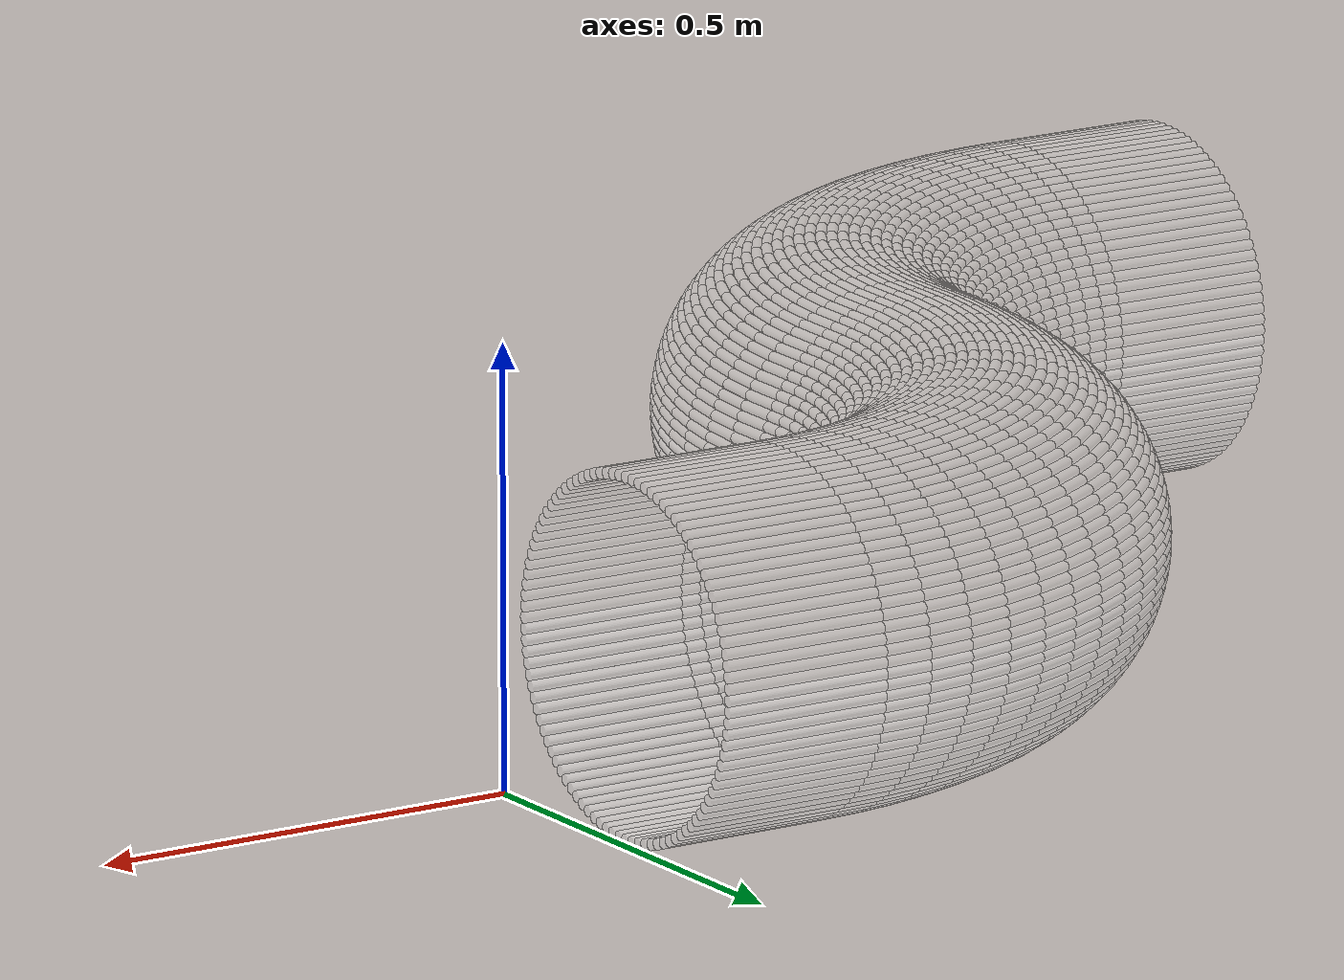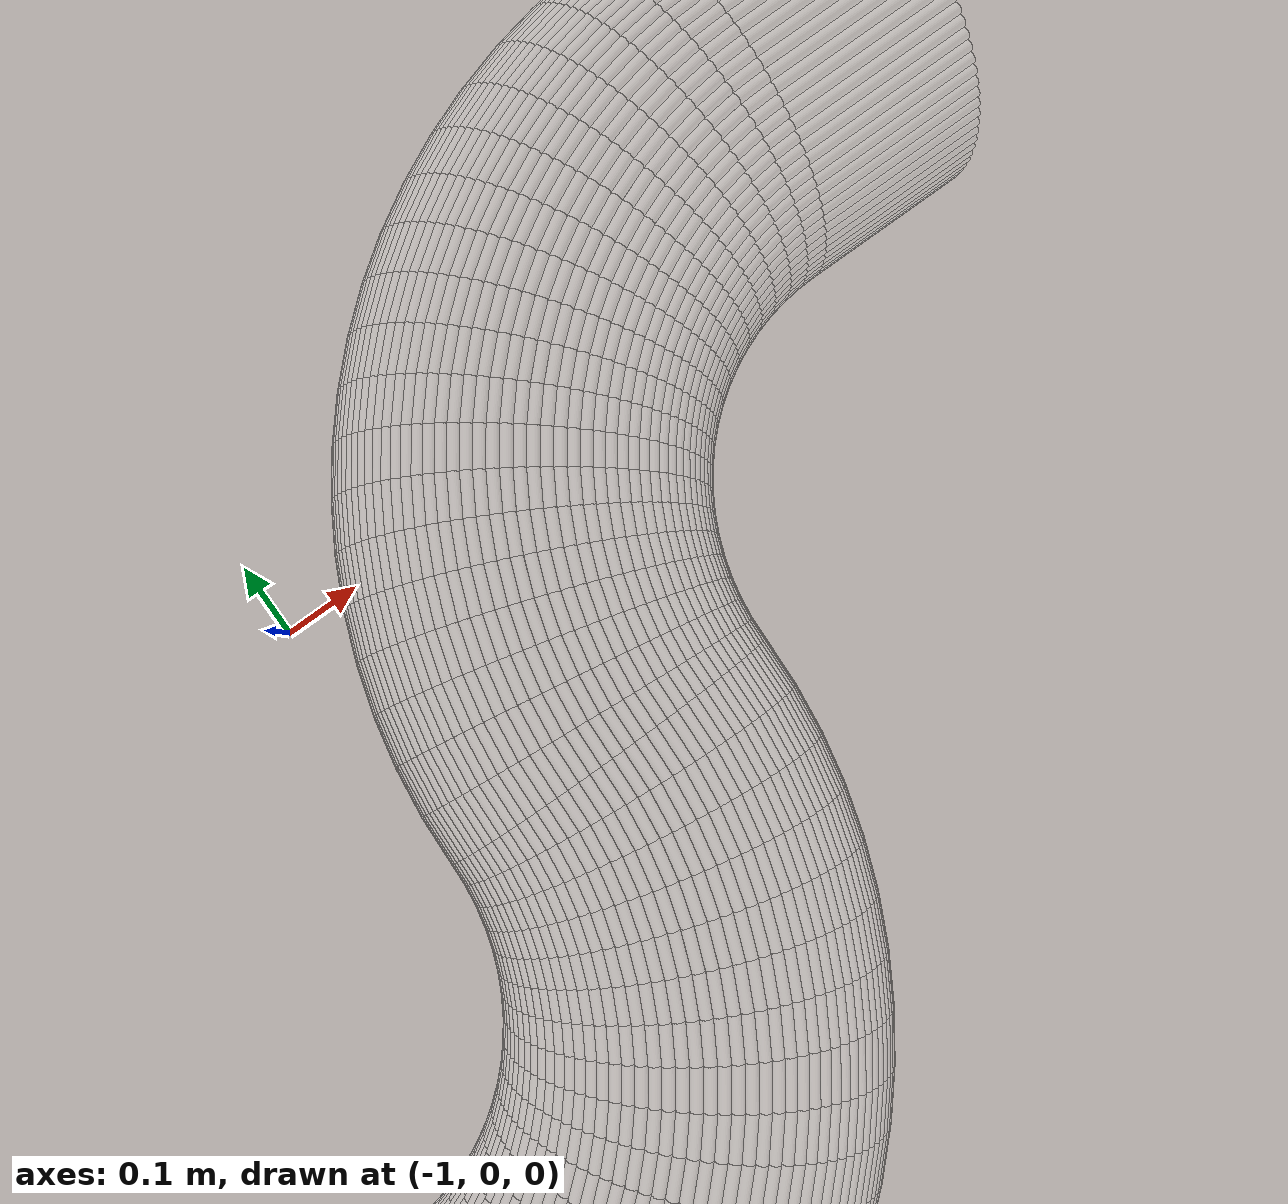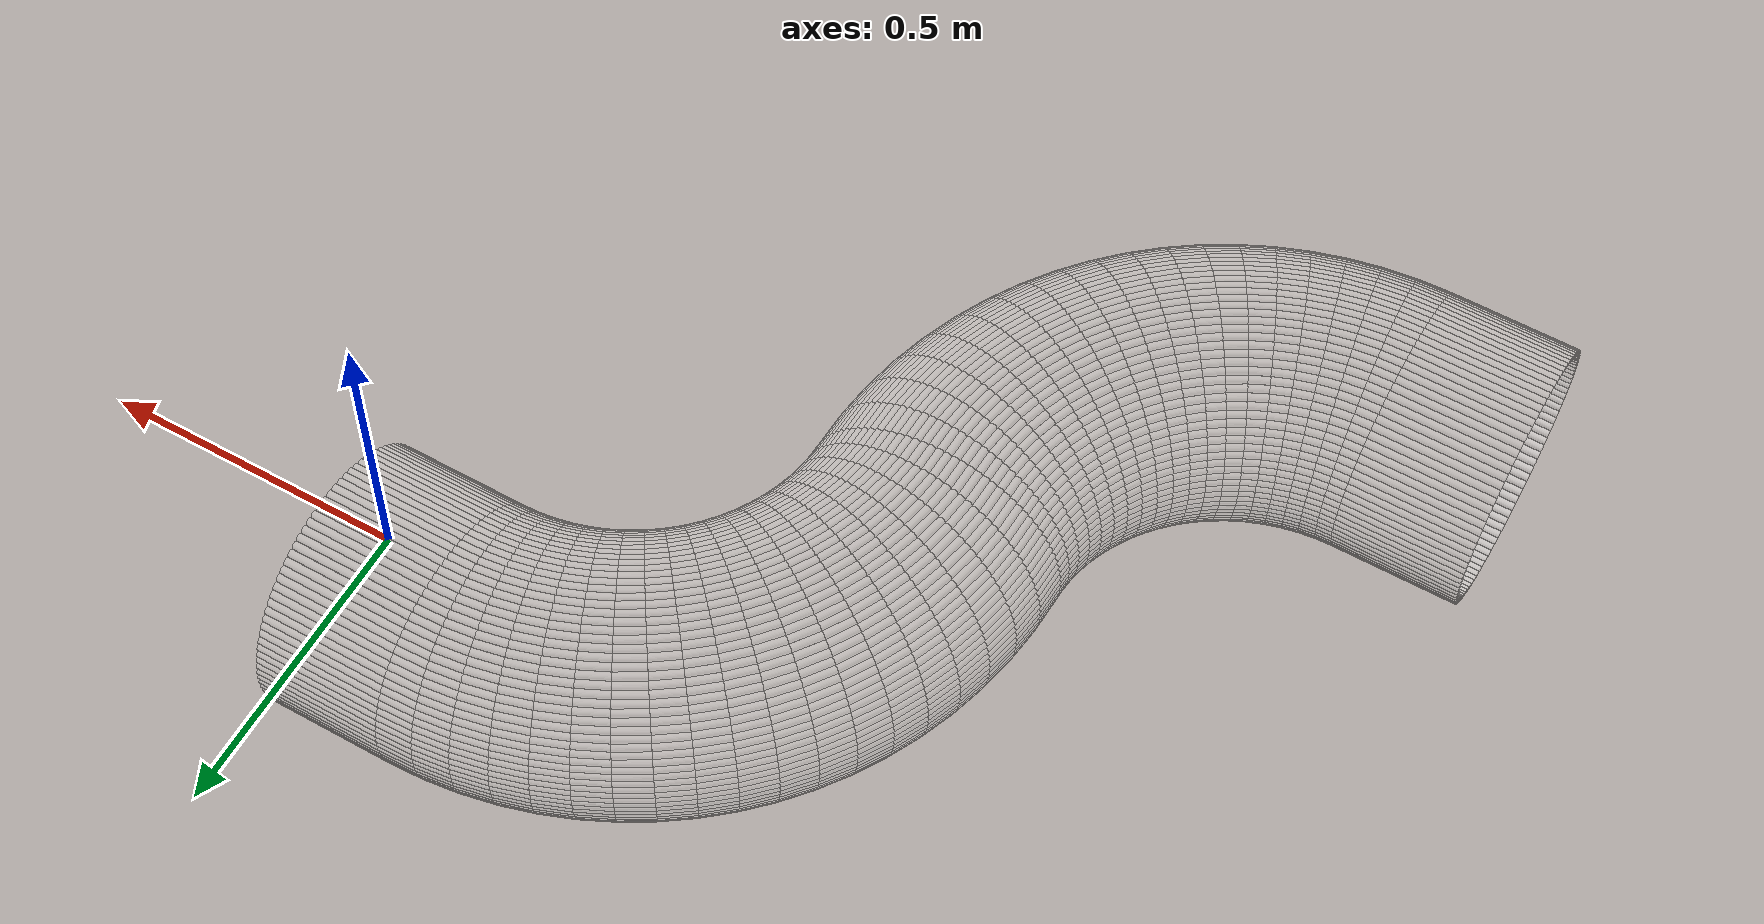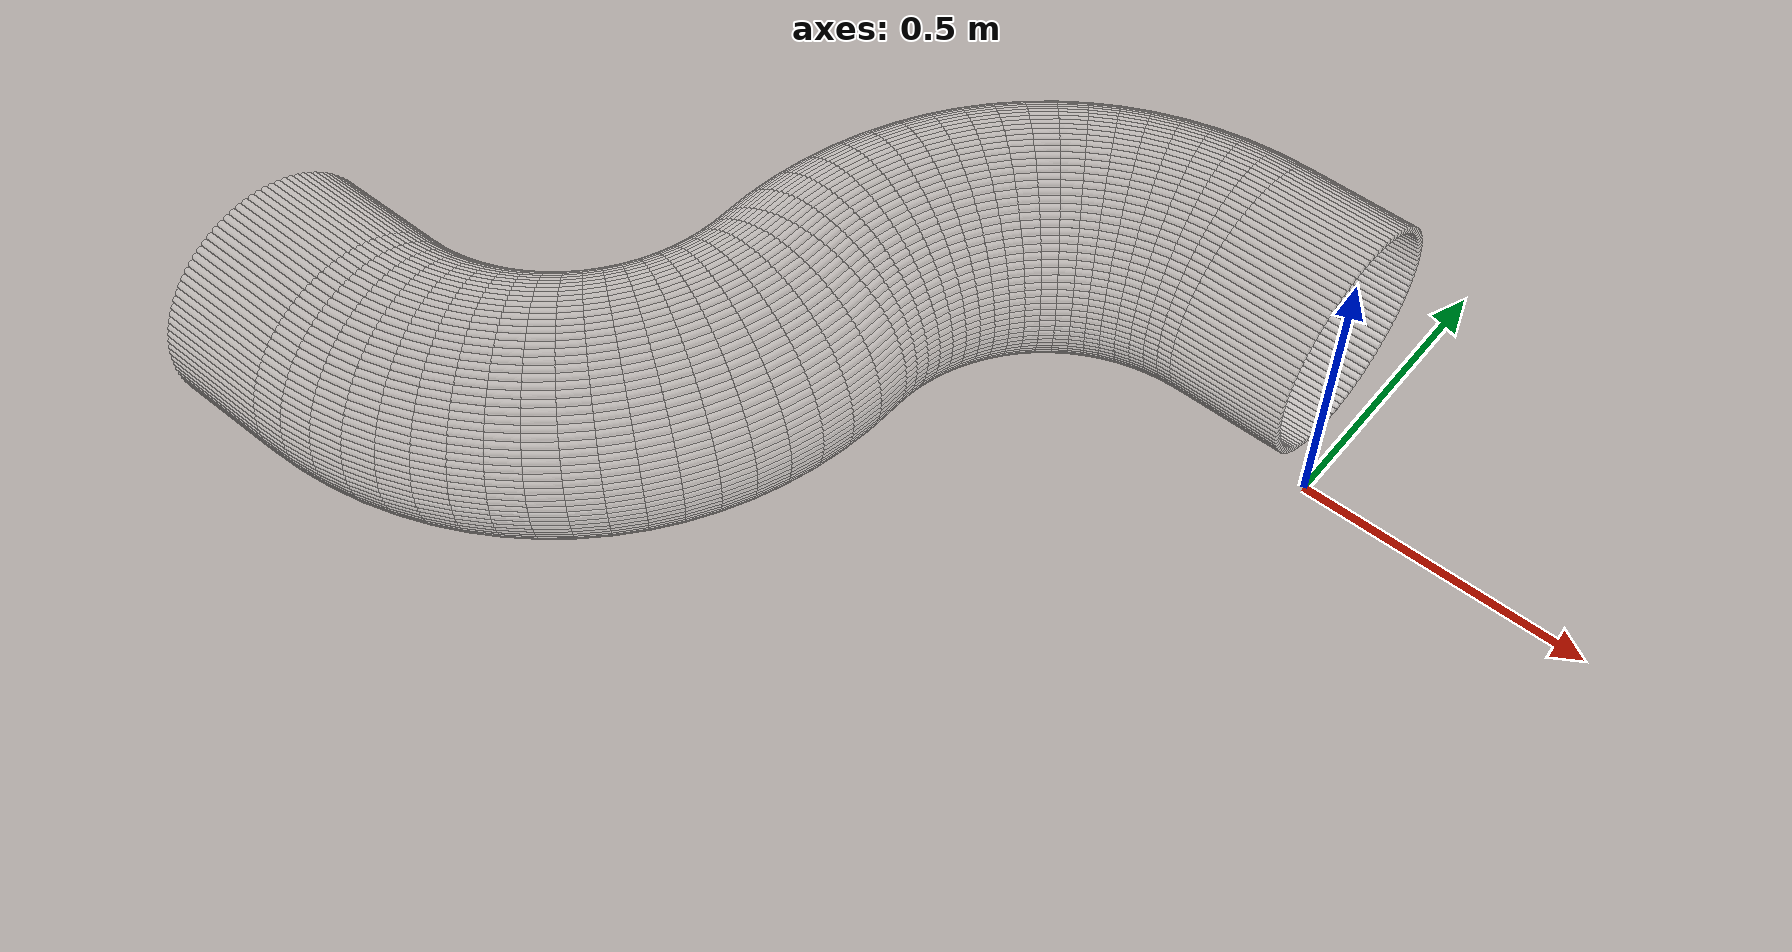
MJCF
<?xml version="1.0" encoding="utf-8"?>
<mujoco>
   <worldbody>
   <body pos="-0.25 -0.34 -0.02" euler="0 0 90">
      <geom euler=" 0 10 0 " fromto="0.7 -0.2 0.2 0.7 0 0.2" rgba="1 1 1 0.35"
            size="0.0062822"
            type="cylinder"/>
      <geom euler=" 0 20 0 " fromto="0.69961 -0.2 0.21256 0.69961 0 0.21256"
            rgba="1 1 1 0.05"
            size="0.0062822"
            type="cylinder"/>
      <geom euler=" 0 30 0 " fromto="0.69842 -0.2 0.22507 0.69842 0 0.22507"
            rgba="1 1 1 0.05"
            size="0.0062822"
            type="cylinder"/>
      <geom euler=" 0 40 0 " fromto="0.69646 -0.2 0.23748 0.69646 0 0.23748"
            rgba="1 1 1 0.05"
            size="0.0062822"
            type="cylinder"/>
      <geom euler=" 0 50 0 " fromto="0.69372 -0.2 0.24974 0.69372 0 0.24974"
            rgba="1 1 1 0.05"
            size="0.0062822"
            type="cylinder"/>
      <geom euler=" 0 60 0 " fromto="0.69021 -0.2 0.2618 0.69021 0 0.2618"
            rgba="1 1 1 0.05"
            size="0.0062822"
            type="cylinder"/>
      <geom euler=" 0 70 0 " fromto="0.68596 -0.2 0.27362 0.68596 0 0.27362"
            rgba="1 1 1 0.05"
            size="0.0062822"
            type="cylinder"/>
      <geom euler=" 0 80 0 " fromto="0.68097 -0.2 0.28516 0.68097 0 0.28516"
            rgba="1 1 1 0.05"
            size="0.0062822"
            type="cylinder"/>
      <geom euler=" 0 90 0 " fromto="0.67526 -0.2 0.29635 0.67526 0 0.29635"
            rgba="1 1 1 0.05"
            size="0.0062822"
            type="cylinder"/>
      <geom euler=" 0 100 0 " fromto="0.66887 -0.2 0.30717 0.66887 0 0.30717"
            rgba="1 1 1 0.05"
            size="0.0062822"
            type="cylinder"/>
      <geom euler=" 0 110 0 " fromto="0.6618 -0.2 0.31756 0.6618 0 0.31756"
            rgba="1 1 1 0.05"
            size="0.0062822"
            type="cylinder"/>
      <geom euler=" 0 120 0 " fromto="0.6541 -0.2 0.32748 0.6541 0 0.32748"
            rgba="1 1 1 0.05"
            size="0.0062822"
            type="cylinder"/>
      <geom euler=" 0 130 0 " fromto="0.64579 -0.2 0.33691 0.64579 0 0.33691"
            rgba="1 1 1 0.05"
            size="0.0062822"
            type="cylinder"/>
      <geom euler=" 0 140 0 " fromto="0.63691 -0.2 0.34579 0.63691 0 0.34579"
            rgba="1 1 1 0.05"
            size="0.0062822"
            type="cylinder"/>
      <geom euler=" 0 150 0 " fromto="0.62748 -0.2 0.3541 0.62748 0 0.3541"
            rgba="1 1 1 0.05"
            size="0.0062822"
            type="cylinder"/>
      <geom euler=" 0 160 0 " fromto="0.61756 -0.2 0.3618 0.61756 0 0.3618"
            rgba="1 1 1 0.05"
            size="0.0062822"
            type="cylinder"/>
      <geom euler=" 0 170 0 " fromto="0.60717 -0.2 0.36887 0.60717 0 0.36887"
            rgba="1 1 1 0.05"
            size="0.0062822"
            type="cylinder"/>
      <geom euler=" 0 180 0 " fromto="0.59635 -0.2 0.37526 0.59635 0 0.37526"
            rgba="1 1 1 0.05"
            size="0.0062822"
            type="cylinder"/>
      <geom euler=" 0 190 0 " fromto="0.58516 -0.2 0.38097 0.58516 0 0.38097"
            rgba="1 1 1 0.05"
            size="0.0062822"
            type="cylinder"/>
      <geom euler=" 0 200 0 " fromto="0.57362 -0.2 0.38596 0.57362 0 0.38596"
            rgba="1 1 1 0.05"
            size="0.0062822"
            type="cylinder"/>
      <geom euler=" 0 210 0 " fromto="0.5618 -0.2 0.39021 0.5618 0 0.39021"
            rgba="1 1 1 0.05"
            size="0.0062822"
            type="cylinder"/>
      <geom euler=" 0 220 0 " fromto="0.54974 -0.2 0.39372 0.54974 0 0.39372"
            rgba="1 1 1 0.05"
            size="0.0062822"
            type="cylinder"/>
      <geom euler=" 0 230 0 " fromto="0.53748 -0.2 0.39646 0.53748 0 0.39646"
            rgba="1 1 1 0.05"
            size="0.0062822"
            type="cylinder"/>
      <geom euler=" 0 240 0 " fromto="0.52507 -0.2 0.39842 0.52507 0 0.39842"
            rgba="1 1 1 0.05"
            size="0.0062822"
            type="cylinder"/>
      <geom euler=" 0 250 0 " fromto="0.51256 -0.2 0.39961 0.51256 0 0.39961"
            rgba="1 1 1 0.05"
            size="0.0062822"
            type="cylinder"/>
      <geom euler=" 0 260 0 " fromto="0.5 -0.2 0.4 0.5 0 0.4" rgba="1 1 1 0.05"
            size="0.0062822"
            type="cylinder"/>
      <geom euler=" 0 270 0 " fromto="0.48744 -0.2 0.39961 0.48744 0 0.39961"
            rgba="1 1 1 0.05"
            size="0.0062822"
            type="cylinder"/>
      <geom euler=" 0 280 0 " fromto="0.47493 -0.2 0.39842 0.47493 0 0.39842"
            rgba="1 1 1 0.05"
            size="0.0062822"
            type="cylinder"/>
      <geom euler=" 0 290 0 " fromto="0.46252 -0.2 0.39646 0.46252 0 0.39646"
            rgba="1 1 1 0.05"
            size="0.0062822"
            type="cylinder"/>
      <geom euler=" 0 300 0 " fromto="0.45026 -0.2 0.39372 0.45026 0 0.39372"
            rgba="1 1 1 0.05"
            size="0.0062822"
            type="cylinder"/>
      <geom euler=" 0 310 0 " fromto="0.4382 -0.2 0.39021 0.4382 0 0.39021"
            rgba="1 1 1 0.05"
            size="0.0062822"
            type="cylinder"/>
      <geom euler=" 0 320 0 " fromto="0.42638 -0.2 0.38596 0.42638 0 0.38596"
            rgba="1 1 1 0.05"
            size="0.0062822"
            type="cylinder"/>
      <geom euler=" 0 330 0 " fromto="0.41484 -0.2 0.38097 0.41484 0 0.38097"
            rgba="1 1 1 0.05"
            size="0.0062822"
            type="cylinder"/>
      <geom euler=" 0 340 0 " fromto="0.40365 -0.2 0.37526 0.40365 0 0.37526"
            rgba="1 1 1 0.05"
            size="0.0062822"
            type="cylinder"/>
      <geom euler=" 0 350 0 " fromto="0.39283 -0.2 0.36887 0.39283 0 0.36887"
            rgba="1 1 1 0.05"
            size="0.0062822"
            type="cylinder"/>
      <geom euler=" 0 360 0 " fromto="0.38244 -0.2 0.3618 0.38244 0 0.3618"
            rgba="1 1 1 0.05"
            size="0.0062822"
            type="cylinder"/>
      <geom euler=" 0 370 0 " fromto="0.37252 -0.2 0.3541 0.37252 0 0.3541"
            rgba="1 1 1 0.05"
            size="0.0062822"
            type="cylinder"/>
      <geom euler=" 0 380 0 " fromto="0.36309 -0.2 0.34579 0.36309 0 0.34579"
            rgba="1 1 1 0.05"
            size="0.0062822"
            type="cylinder"/>
      <geom euler=" 0 390 0 " fromto="0.35421 -0.2 0.33691 0.35421 0 0.33691"
            rgba="1 1 1 0.05"
            size="0.0062822"
            type="cylinder"/>
      <geom euler=" 0 400 0 " fromto="0.3459 -0.2 0.32748 0.3459 0 0.32748"
            rgba="1 1 1 0.05"
            size="0.0062822"
            type="cylinder"/>
      <geom euler=" 0 410 0 " fromto="0.3382 -0.2 0.31756 0.3382 0 0.31756"
            rgba="1 1 1 0.05"
            size="0.0062822"
            type="cylinder"/>
      <geom euler=" 0 420 0 " fromto="0.33113 -0.2 0.30717 0.33113 0 0.30717"
            rgba="1 1 1 0.05"
            size="0.0062822"
            type="cylinder"/>
      <geom euler=" 0 430 0 " fromto="0.32474 -0.2 0.29635 0.32474 0 0.29635"
            rgba="1 1 1 0.05"
            size="0.0062822"
            type="cylinder"/>
      <geom euler=" 0 440 0 " fromto="0.31903 -0.2 0.28516 0.31903 0 0.28516"
            rgba="1 1 1 0.05"
            size="0.0062822"
            type="cylinder"/>
      <geom euler=" 0 450 0 " fromto="0.31404 -0.2 0.27362 0.31404 0 0.27362"
            rgba="1 1 1 0.05"
            size="0.0062822"
            type="cylinder"/>
      <geom euler=" 0 460 0 " fromto="0.30979 -0.2 0.2618 0.30979 0 0.2618"
            rgba="1 1 1 0.05"
            size="0.0062822"
            type="cylinder"/>
      <geom euler=" 0 470 0 " fromto="0.30628 -0.2 0.24974 0.30628 0 0.24974"
            rgba="1 1 1 0.05"
            size="0.0062822"
            type="cylinder"/>
      <geom euler=" 0 480 0 " fromto="0.30354 -0.2 0.23748 0.30354 0 0.23748"
            rgba="1 1 1 0.05"
            size="0.0062822"
            type="cylinder"/>
      <geom euler=" 0 490 0 " fromto="0.30158 -0.2 0.22507 0.30158 0 0.22507"
            rgba="1 1 1 0.05"
            size="0.0062822"
            type="cylinder"/>
      <geom euler=" 0 500 0 " fromto="0.30039 -0.2 0.21256 0.30039 0 0.21256"
            rgba="1 1 1 0.05"
            size="0.0062822"
            type="cylinder"/>
      <geom euler=" 0 510 0 " fromto="0.3 -0.2 0.2 0.3 0 0.2" rgba="1 1 1 0.05"
            size="0.0062822"
            type="cylinder"/>
      <geom euler=" 0 520 0 " fromto="0.30039 -0.2 0.18744 0.30039 0 0.18744"
            rgba="1 1 1 0.35"
            size="0.0062822"
            type="cylinder"/>
      <geom euler=" 0 530 0 " fromto="0.30158 -0.2 0.17493 0.30158 0 0.17493"
            rgba="1 1 1 0.35"
            size="0.0062822"
            type="cylinder"/>
      <geom euler=" 0 540 0 " fromto="0.30354 -0.2 0.16252 0.30354 0 0.16252"
            rgba="1 1 1 0.35"
            size="0.0062822"
            type="cylinder"/>
      <geom euler=" 0 550 0 " fromto="0.30628 -0.2 0.15026 0.30628 0 0.15026"
            rgba="1 1 1 0.35"
            size="0.0062822"
            type="cylinder"/>
      <geom euler=" 0 560 0 " fromto="0.30979 -0.2 0.1382 0.30979 0 0.1382"
            rgba="1 1 1 0.35"
            size="0.0062822"
            type="cylinder"/>
      <geom euler=" 0 570 0 " fromto="0.31404 -0.2 0.12638 0.31404 0 0.12638"
            rgba="1 1 1 0.35"
            size="0.0062822"
            type="cylinder"/>
      <geom euler=" 0 580 0 " fromto="0.31903 -0.2 0.11484 0.31903 0 0.11484"
            rgba="1 1 1 0.35"
            size="0.0062822"
            type="cylinder"/>
      <geom euler=" 0 590 0 " fromto="0.32474 -0.2 0.10365 0.32474 0 0.10365"
            rgba="1 1 1 0.35"
            size="0.0062822"
            type="cylinder"/>
      <geom euler=" 0 600 0 " fromto="0.33113 -0.2 0.092835 0.33113 0 0.092835"
            rgba="1 1 1 0.35"
            size="0.0062822"
            type="cylinder"/>
      <geom euler=" 0 610 0 " fromto="0.3382 -0.2 0.082443 0.3382 0 0.082443"
            rgba="1 1 1 0.35"
            size="0.0062822"
            type="cylinder"/>
      <geom euler=" 0 620 0 " fromto="0.3459 -0.2 0.072515 0.3459 0 0.072515"
            rgba="1 1 1 0.35"
            size="0.0062822"
            type="cylinder"/>
      <geom euler=" 0 630 0 " fromto="0.35421 -0.2 0.063091 0.35421 0 0.063091"
            rgba="1 1 1 0.35"
            size="0.0062822"
            type="cylinder"/>
      <geom euler=" 0 640 0 " fromto="0.36309 -0.2 0.054206 0.36309 0 0.054206"
            rgba="1 1 1 0.35"
            size="0.0062822"
            type="cylinder"/>
      <geom euler=" 0 650 0 " fromto="0.37252 -0.2 0.045897 0.37252 0 0.045897"
            rgba="1 1 1 0.35"
            size="0.0062822"
            type="cylinder"/>
      <geom euler=" 0 660 0 " fromto="0.38244 -0.2 0.038197 0.38244 0 0.038197"
            rgba="1 1 1 0.35"
            size="0.0062822"
            type="cylinder"/>
      <geom euler=" 0 670 0 " fromto="0.39283 -0.2 0.031134 0.39283 0 0.031134"
            rgba="1 1 1 0.35"
            size="0.0062822"
            type="cylinder"/>
      <geom euler=" 0 680 0 " fromto="0.40365 -0.2 0.024739 0.40365 0 0.024739"
            rgba="1 1 1 0.35"
            size="0.0062822"
            type="cylinder"/>
      <geom euler=" 0 690 0 " fromto="0.41484 -0.2 0.019035 0.41484 0 0.019035"
            rgba="1 1 1 0.35"
            size="0.0062822"
            type="cylinder"/>
      <geom euler=" 0 700 0 " fromto="0.42638 -0.2 0.014045 0.42638 0 0.014045"
            rgba="1 1 1 0.35"
            size="0.0062822"
            type="cylinder"/>
      <geom euler=" 0 710 0 " fromto="0.4382 -0.2 0.0097887 0.4382 0 0.0097887"
            rgba="1 1 1 0.35"
            size="0.0062822"
            type="cylinder"/>
      <geom euler=" 0 720 0 " fromto="0.45026 -0.2 0.0062834 0.45026 0 0.0062834"
            rgba="1 1 1 0.35"
            size="0.0062822"
            type="cylinder"/>
      <geom euler=" 0 730 0 " fromto="0.46252 -0.2 0.0035425 0.46252 0 0.0035425"
            rgba="1 1 1 0.35"
            size="0.0062822"
            type="cylinder"/>
      <geom euler=" 0 740 0 " fromto="0.47493 -0.2 0.0015771 0.47493 0 0.0015771"
            rgba="1 1 1 0.35"
            size="0.0062822"
            type="cylinder"/>
      <geom euler=" 0 750 0 " fromto="0.48744 -0.2 0.00039465 0.48744 0 0.00039465"
            rgba="1 1 1 0.35"
            size="0.0062822"
            type="cylinder"/>
      <geom euler=" 0 760 0 " fromto="0.5 -0.2 0 0.5 0 0" rgba="1 1 1 0.35"
            size="0.0062822"
            type="cylinder"/>
      <geom euler=" 0 770 0 " fromto="0.51256 -0.2 0.00039465 0.51256 0 0.00039465"
            rgba="1 1 1 0.35"
            size="0.0062822"
            type="cylinder"/>
      <geom euler=" 0 780 0 " fromto="0.52507 -0.2 0.0015771 0.52507 0 0.0015771"
            rgba="1 1 1 0.35"
            size="0.0062822"
            type="cylinder"/>
      <geom euler=" 0 790 0 " fromto="0.53748 -0.2 0.0035425 0.53748 0 0.0035425"
            rgba="1 1 1 0.35"
            size="0.0062822"
            type="cylinder"/>
      <geom euler=" 0 800 0 " fromto="0.54974 -0.2 0.0062834 0.54974 0 0.0062834"
            rgba="1 1 1 0.35"
            size="0.0062822"
            type="cylinder"/>
      <geom euler=" 0 810 0 " fromto="0.5618 -0.2 0.0097887 0.5618 0 0.0097887"
            rgba="1 1 1 0.35"
            size="0.0062822"
            type="cylinder"/>
      <geom euler=" 0 820 0 " fromto="0.57362 -0.2 0.014045 0.57362 0 0.014045"
            rgba="1 1 1 0.35"
            size="0.0062822"
            type="cylinder"/>
      <geom euler=" 0 830 0 " fromto="0.58516 -0.2 0.019035 0.58516 0 0.019035"
            rgba="1 1 1 0.35"
            size="0.0062822"
            type="cylinder"/>
      <geom euler=" 0 840 0 " fromto="0.59635 -0.2 0.024739 0.59635 0 0.024739"
            rgba="1 1 1 0.35"
            size="0.0062822"
            type="cylinder"/>
      <geom euler=" 0 850 0 " fromto="0.60717 -0.2 0.031134 0.60717 0 0.031134"
            rgba="1 1 1 0.35"
            size="0.0062822"
            type="cylinder"/>
      <geom euler=" 0 860 0 " fromto="0.61756 -0.2 0.038197 0.61756 0 0.038197"
            rgba="1 1 1 0.35"
            size="0.0062822"
            type="cylinder"/>
      <geom euler=" 0 870 0 " fromto="0.62748 -0.2 0.045897 0.62748 0 0.045897"
            rgba="1 1 1 0.35"
            size="0.0062822"
            type="cylinder"/>
      <geom euler=" 0 880 0 " fromto="0.63691 -0.2 0.054206 0.63691 0 0.054206"
            rgba="1 1 1 0.35"
            size="0.0062822"
            type="cylinder"/>
      <geom euler=" 0 890 0 " fromto="0.64579 -0.2 0.063091 0.64579 0 0.063091"
            rgba="1 1 1 0.35"
            size="0.0062822"
            type="cylinder"/>
      <geom euler=" 0 900 0 " fromto="0.6541 -0.2 0.072515 0.6541 0 0.072515"
            rgba="1 1 1 0.35"
            size="0.0062822"
            type="cylinder"/>
      <geom euler=" 0 910 0 " fromto="0.6618 -0.2 0.082443 0.6618 0 0.082443"
            rgba="1 1 1 0.35"
            size="0.0062822"
            type="cylinder"/>
      <geom euler=" 0 920 0 " fromto="0.66887 -0.2 0.092835 0.66887 0 0.092835"
            rgba="1 1 1 0.35"
            size="0.0062822"
            type="cylinder"/>
      <geom euler=" 0 930 0 " fromto="0.67526 -0.2 0.10365 0.67526 0 0.10365"
            rgba="1 1 1 0.35"
            size="0.0062822"
            type="cylinder"/>
      <geom euler=" 0 940 0 " fromto="0.68097 -0.2 0.11484 0.68097 0 0.11484"
            rgba="1 1 1 0.35"
            size="0.0062822"
            type="cylinder"/>
      <geom euler=" 0 950 0 " fromto="0.68596 -0.2 0.12638 0.68596 0 0.12638"
            rgba="1 1 1 0.35"
            size="0.0062822"
            type="cylinder"/>
      <geom euler=" 0 960 0 " fromto="0.69021 -0.2 0.1382 0.69021 0 0.1382"
            rgba="1 1 1 0.35"
            size="0.0062822"
            type="cylinder"/>
      <geom euler=" 0 970 0 " fromto="0.69372 -0.2 0.15026 0.69372 0 0.15026"
            rgba="1 1 1 0.35"
            size="0.0062822"
            type="cylinder"/>
      <geom euler=" 0 980 0 " fromto="0.69646 -0.2 0.16252 0.69646 0 0.16252"
            rgba="1 1 1 0.35"
            size="0.0062822"
            type="cylinder"/>
      <geom euler=" 0 990 0 " fromto="0.69842 -0.2 0.17493 0.69842 0 0.17493"
            rgba="1 1 1 0.35"
            size="0.0062822"
            type="cylinder"/>
      <geom euler=" 0 1000 0 " fromto="0.69961 -0.2 0.18744 0.69961 0 0.18744"
            rgba="1 1 1 0.35"
            size="0.0062822"
            type="cylinder"/>
      <geom euler=" 0 10 0 " fromto="0.7 0 0.2 0.69761 0.057806 0.2" rgba="1 1 1 0.35"
            size="0.0062822"
            type="cylinder"/>
      <geom euler=" 0 20 0 " fromto="0.69961 0 0.21256 0.69722 0.057773 0.21256"
            rgba="1 1 1 0.05"
            size="0.0062822"
            type="cylinder"/>
      <geom euler=" 0 30 0 " fromto="0.69842 0 0.22507 0.69604 0.057675 0.22507"
            rgba="1 1 1 0.05"
            size="0.0062822"
            type="cylinder"/>
      <geom euler=" 0 40 0 " fromto="0.69646 0 0.23748 0.69408 0.057513 0.23748"
            rgba="1 1 1 0.05"
            size="0.0062822"
            type="cylinder"/>
      <geom euler=" 0 50 0 " fromto="0.69372 0 0.24974 0.69135 0.057287 0.24974"
            rgba="1 1 1 0.05"
            size="0.0062822"
            type="cylinder"/>
      <geom euler=" 0 60 0 " fromto="0.69021 0 0.2618 0.68785 0.056997 0.2618"
            rgba="1 1 1 0.05"
            size="0.0062822"
            type="cylinder"/>
      <geom euler=" 0 70 0 " fromto="0.68596 0 0.27362 0.68361 0.056646 0.27362"
            rgba="1 1 1 0.05"
            size="0.0062822"
            type="cylinder"/>
      <geom euler=" 0 80 0 " fromto="0.68097 0 0.28516 0.67864 0.056234 0.28516"
            rgba="1 1 1 0.05"
            size="0.0062822"
            type="cylinder"/>
      <geom euler=" 0 90 0 " fromto="0.67526 0 0.29635 0.67295 0.055763 0.29635"
            rgba="1 1 1 0.05"
            size="0.0062822"
            type="cylinder"/>
      <geom euler=" 0 100 0 " fromto="0.66887 0 0.30717 0.66658 0.055234 0.30717"
            rgba="1 1 1 0.05"
            size="0.0062822"
            type="cylinder"/>
      <geom euler=" 0 110 0 " fromto="0.6618 0 0.31756 0.65954 0.054651 0.31756"
            rgba="1 1 1 0.05"
            size="0.0062822"
            type="cylinder"/>
      <geom euler=" 0 120 0 " fromto="0.6541 0 0.32748 0.65187 0.054015 0.32748"
            rgba="1 1 1 0.05"
            size="0.0062822"
            type="cylinder"/>
      <geom euler=" 0 130 0 " fromto="0.64579 0 0.33691 0.64359 0.053329 0.33691"
            rgba="1 1 1 0.05"
            size="0.0062822"
            type="cylinder"/>
      <geom euler=" 0 140 0 " fromto="0.63691 0 0.34579 0.63473 0.052596 0.34579"
            rgba="1 1 1 0.05"
            size="0.0062822"
            type="cylinder"/>
      <geom euler=" 0 150 0 " fromto="0.62748 0 0.3541 0.62534 0.051817 0.3541"
            rgba="1 1 1 0.05"
            size="0.0062822"
            type="cylinder"/>
      <geom euler=" 0 160 0 " fromto="0.61756 0 0.3618 0.61545 0.050997 0.3618"
            rgba="1 1 1 0.05"
            size="0.0062822"
            type="cylinder"/>
      <geom euler=" 0 170 0 " fromto="0.60717 0 0.36887 0.60509 0.050139 0.36887"
            rgba="1 1 1 0.05"
            size="0.0062822"
            type="cylinder"/>
      <geom euler=" 0 180 0 " fromto="0.59635 0 0.37526 0.59431 0.049246 0.37526"
            rgba="1 1 1 0.05"
            size="0.0062822"
            type="cylinder"/>
      <geom euler=" 0 190 0 " fromto="0.58516 0 0.38097 0.58316 0.048322 0.38097"
            rgba="1 1 1 0.05"
            size="0.0062822"
            type="cylinder"/>
      <geom euler=" 0 200 0 " fromto="0.57362 0 0.38596 0.57167 0.04737 0.38596"
            rgba="1 1 1 0.05"
            size="0.0062822"
            type="cylinder"/>
      <geom euler=" 0 210 0 " fromto="0.5618 0 0.39021 0.55988 0.046393 0.39021"
            rgba="1 1 1 0.05"
            size="0.0062822"
            type="cylinder"/>
      <geom euler=" 0 220 0 " fromto="0.54974 0 0.39372 0.54786 0.045397 0.39372"
            rgba="1 1 1 0.05"
            size="0.0062822"
            type="cylinder"/>
      <geom euler=" 0 230 0 " fromto="0.53748 0 0.39646 0.53564 0.044384 0.39646"
            rgba="1 1 1 0.05"
            size="0.0062822"
            type="cylinder"/>
      <geom euler=" 0 240 0 " fromto="0.52507 0 0.39842 0.52327 0.04336 0.39842"
            rgba="1 1 1 0.05"
            size="0.0062822"
            type="cylinder"/>
      <geom euler=" 0 250 0 " fromto="0.51256 0 0.39961 0.51081 0.042327 0.39961"
            rgba="1 1 1 0.05"
            size="0.0062822"
            type="cylinder"/>
      <geom euler=" 0 260 0 " fromto="0.5 0 0.4 0.49829 0.04129 0.4" rgba="1 1 1 0.05"
            size="0.0062822"
            type="cylinder"/>
      <geom euler=" 0 270 0 " fromto="0.48744 0 0.39961 0.48578 0.040253 0.39961"
            rgba="1 1 1 0.05"
            size="0.0062822"
            type="cylinder"/>
      <geom euler=" 0 280 0 " fromto="0.47493 0 0.39842 0.47331 0.03922 0.39842"
            rgba="1 1 1 0.05"
            size="0.0062822"
            type="cylinder"/>
      <geom euler=" 0 290 0 " fromto="0.46252 0 0.39646 0.46094 0.038195 0.39646"
            rgba="1 1 1 0.05"
            size="0.0062822"
            type="cylinder"/>
      <geom euler=" 0 300 0 " fromto="0.45026 0 0.39372 0.44872 0.037182 0.39372"
            rgba="1 1 1 0.05"
            size="0.0062822"
            type="cylinder"/>
      <geom euler=" 0 310 0 " fromto="0.4382 0 0.39021 0.4367 0.036186 0.39021"
            rgba="1 1 1 0.05"
            size="0.0062822"
            type="cylinder"/>
      <geom euler=" 0 320 0 " fromto="0.42638 0 0.38596 0.42492 0.03521 0.38596"
            rgba="1 1 1 0.05"
            size="0.0062822"
            type="cylinder"/>
      <geom euler=" 0 330 0 " fromto="0.41484 0 0.38097 0.41343 0.034258 0.38097"
            rgba="1 1 1 0.05"
            size="0.0062822"
            type="cylinder"/>
      <geom euler=" 0 340 0 " fromto="0.40365 0 0.37526 0.40227 0.033333 0.37526"
            rgba="1 1 1 0.05"
            size="0.0062822"
            type="cylinder"/>
      <geom euler=" 0 350 0 " fromto="0.39283 0 0.36887 0.39149 0.03244 0.36887"
            rgba="1 1 1 0.05"
            size="0.0062822"
            type="cylinder"/>
      <geom euler=" 0 360 0 " fromto="0.38244 0 0.3618 0.38114 0.031582 0.3618"
            rgba="1 1 1 0.05"
            size="0.0062822"
            type="cylinder"/>
      <geom euler=" 0 370 0 " fromto="0.37252 0 0.3541 0.37124 0.030762 0.3541"
            rgba="1 1 1 0.05"
            size="0.0062822"
            type="cylinder"/>
      <geom euler=" 0 380 0 " fromto="0.36309 0 0.34579 0.36185 0.029984 0.34579"
            rgba="1 1 1 0.05"
            size="0.0062822"
            type="cylinder"/>
      <geom euler=" 0 390 0 " fromto="0.35421 0 0.33691 0.353 0.02925 0.33691"
            rgba="1 1 1 0.05"
            size="0.0062822"
            type="cylinder"/>
      <geom euler=" 0 400 0 " fromto="0.3459 0 0.32748 0.34472 0.028564 0.32748"
            rgba="1 1 1 0.05"
            size="0.0062822"
            type="cylinder"/>
      <geom euler=" 0 410 0 " fromto="0.3382 0 0.31756 0.33704 0.027928 0.31756"
            rgba="1 1 1 0.05"
            size="0.0062822"
            type="cylinder"/>
      <geom euler=" 0 420 0 " fromto="0.33113 0 0.30717 0.33 0.027345 0.30717"
            rgba="1 1 1 0.05"
            size="0.0062822"
            type="cylinder"/>
      <geom euler=" 0 430 0 " fromto="0.32474 0 0.29635 0.32363 0.026817 0.29635"
            rgba="1 1 1 0.05"
            size="0.0062822"
            type="cylinder"/>
      <geom euler=" 0 440 0 " fromto="0.31903 0 0.28516 0.31794 0.026346 0.28516"
            rgba="1 1 1 0.05"
            size="0.0062822"
            type="cylinder"/>
      <geom euler=" 0 450 0 " fromto="0.31404 0 0.27362 0.31297 0.025934 0.27362"
            rgba="1 1 1 0.05"
            size="0.0062822"
            type="cylinder"/>
      <geom euler=" 0 460 0 " fromto="0.30979 0 0.2618 0.30873 0.025582 0.2618"
            rgba="1 1 1 0.05"
            size="0.0062822"
            type="cylinder"/>
      <geom euler=" 0 470 0 " fromto="0.30628 0 0.24974 0.30524 0.025293 0.24974"
            rgba="1 1 1 0.05"
            size="0.0062822"
            type="cylinder"/>
      <geom euler=" 0 480 0 " fromto="0.30354 0 0.23748 0.30251 0.025066 0.23748"
            rgba="1 1 1 0.05"
            size="0.0062822"
            type="cylinder"/>
      <geom euler=" 0 490 0 " fromto="0.30158 0 0.22507 0.30055 0.024904 0.22507"
            rgba="1 1 1 0.05"
            size="0.0062822"
            type="cylinder"/>
      <geom euler=" 0 500 0 " fromto="0.30039 0 0.21256 0.29937 0.024806 0.21256"
            rgba="1 1 1 0.05"
            size="0.0062822"
            type="cylinder"/>
      <geom euler=" 0 510 0 " fromto="0.3 0 0.2 0.29898 0.024774 0.2" rgba="1 1 1 0.05"
            size="0.0062822"
            type="cylinder"/>
      <geom euler=" 0 520 0 " fromto="0.30039 0 0.18744 0.29937 0.024806 0.18744"
            rgba="1 1 1 0.35"
            size="0.0062822"
            type="cylinder"/>
      <geom euler=" 0 530 0 " fromto="0.30158 0 0.17493 0.30055 0.024904 0.17493"
            rgba="1 1 1 0.35"
            size="0.0062822"
            type="cylinder"/>
      <geom euler=" 0 540 0 " fromto="0.30354 0 0.16252 0.30251 0.025066 0.16252"
            rgba="1 1 1 0.35"
            size="0.0062822"
            type="cylinder"/>
      <geom euler=" 0 550 0 " fromto="0.30628 0 0.15026 0.30524 0.025293 0.15026"
            rgba="1 1 1 0.35"
            size="0.0062822"
            type="cylinder"/>
      <geom euler=" 0 560 0 " fromto="0.30979 0 0.1382 0.30873 0.025582 0.1382"
            rgba="1 1 1 0.35"
            size="0.0062822"
            type="cylinder"/>
      <geom euler=" 0 570 0 " fromto="0.31404 0 0.12638 0.31297 0.025934 0.12638"
            rgba="1 1 1 0.35"
            size="0.0062822"
            type="cylinder"/>
      <geom euler=" 0 580 0 " fromto="0.31903 0 0.11484 0.31794 0.026346 0.11484"
            rgba="1 1 1 0.35"
            size="0.0062822"
            type="cylinder"/>
      <geom euler=" 0 590 0 " fromto="0.32474 0 0.10365 0.32363 0.026817 0.10365"
            rgba="1 1 1 0.35"
            size="0.0062822"
            type="cylinder"/>
      <geom euler=" 0 600 0 " fromto="0.33113 0 0.092835 0.33 0.027345 0.092835"
            rgba="1 1 1 0.35"
            size="0.0062822"
            type="cylinder"/>
      <geom euler=" 0 610 0 " fromto="0.3382 0 0.082443 0.33704 0.027928 0.082443"
            rgba="1 1 1 0.35"
            size="0.0062822"
            type="cylinder"/>
      <geom euler=" 0 620 0 " fromto="0.3459 0 0.072515 0.34472 0.028564 0.072515"
            rgba="1 1 1 0.35"
            size="0.0062822"
            type="cylinder"/>
      <geom euler=" 0 630 0 " fromto="0.35421 0 0.063091 0.353 0.02925 0.063091"
            rgba="1 1 1 0.35"
            size="0.0062822"
            type="cylinder"/>
      <geom euler=" 0 640 0 " fromto="0.36309 0 0.054206 0.36185 0.029984 0.054206"
            rgba="1 1 1 0.35"
            size="0.0062822"
            type="cylinder"/>
      <geom euler=" 0 650 0 " fromto="0.37252 0 0.045897 0.37124 0.030762 0.045897"
            rgba="1 1 1 0.35"
            size="0.0062822"
            type="cylinder"/>
      <geom euler=" 0 660 0 " fromto="0.38244 0 0.038197 0.38114 0.031582 0.038197"
            rgba="1 1 1 0.35"
            size="0.0062822"
            type="cylinder"/>
      <geom euler=" 0 670 0 " fromto="0.39283 0 0.031134 0.39149 0.03244 0.031134"
            rgba="1 1 1 0.35"
            size="0.0062822"
            type="cylinder"/>
      <geom euler=" 0 680 0 " fromto="0.40365 0 0.024739 0.40227 0.033333 0.024739"
            rgba="1 1 1 0.35"
            size="0.0062822"
            type="cylinder"/>
      <geom euler=" 0 690 0 " fromto="0.41484 0 0.019035 0.41343 0.034258 0.019035"
            rgba="1 1 1 0.35"
            size="0.0062822"
            type="cylinder"/>
      <geom euler=" 0 700 0 " fromto="0.42638 0 0.014045 0.42492 0.03521 0.014045"
            rgba="1 1 1 0.35"
            size="0.0062822"
            type="cylinder"/>
      <geom euler=" 0 710 0 " fromto="0.4382 0 0.0097887 0.4367 0.036186 0.0097887"
            rgba="1 1 1 0.35"
            size="0.0062822"
            type="cylinder"/>
      <geom euler=" 0 720 0 " fromto="0.45026 0 0.0062834 0.44872 0.037182 0.0062834"
            rgba="1 1 1 0.35"
            size="0.0062822"
            type="cylinder"/>
      <geom euler=" 0 730 0 " fromto="0.46252 0 0.0035425 0.46094 0.038195 0.0035425"
            rgba="1 1 1 0.35"
            size="0.0062822"
            type="cylinder"/>
      <geom euler=" 0 740 0 " fromto="0.47493 0 0.0015771 0.47331 0.03922 0.0015771"
            rgba="1 1 1 0.35"
            size="0.0062822"
            type="cylinder"/>
      <geom euler=" 0 750 0 " fromto="0.48744 0 0.00039465 0.48578 0.040253 0.00039465"
            rgba="1 1 1 0.35"
            size="0.0062822"
            type="cylinder"/>
      <geom euler=" 0 760 0 " fromto="0.5 0 0 0.49829 0.04129 0" rgba="1 1 1 0.35"
            size="0.0062822"
            type="cylinder"/>
      <geom euler=" 0 770 0 " fromto="0.51256 0 0.00039465 0.51081 0.042327 0.00039465"
            rgba="1 1 1 0.35"
            size="0.0062822"
            type="cylinder"/>
      <geom euler=" 0 780 0 " fromto="0.52507 0 0.0015771 0.52327 0.04336 0.0015771"
            rgba="1 1 1 0.35"
            size="0.0062822"
            type="cylinder"/>
      <geom euler=" 0 790 0 " fromto="0.53748 0 0.0035425 0.53564 0.044384 0.0035425"
            rgba="1 1 1 0.35"
            size="0.0062822"
            type="cylinder"/>
      <geom euler=" 0 800 0 " fromto="0.54974 0 0.0062834 0.54786 0.045397 0.0062834"
            rgba="1 1 1 0.35"
            size="0.0062822"
            type="cylinder"/>
      <geom euler=" 0 810 0 " fromto="0.5618 0 0.0097887 0.55988 0.046393 0.0097887"
            rgba="1 1 1 0.35"
            size="0.0062822"
            type="cylinder"/>
      <geom euler=" 0 820 0 " fromto="0.57362 0 0.014045 0.57167 0.04737 0.014045"
            rgba="1 1 1 0.35"
            size="0.0062822"
            type="cylinder"/>
      <geom euler=" 0 830 0 " fromto="0.58516 0 0.019035 0.58316 0.048322 0.019035"
            rgba="1 1 1 0.35"
            size="0.0062822"
            type="cylinder"/>
      <geom euler=" 0 840 0 " fromto="0.59635 0 0.024739 0.59431 0.049246 0.024739"
            rgba="1 1 1 0.35"
            size="0.0062822"
            type="cylinder"/>
      <geom euler=" 0 850 0 " fromto="0.60717 0 0.031134 0.60509 0.050139 0.031134"
            rgba="1 1 1 0.35"
            size="0.0062822"
            type="cylinder"/>
      <geom euler=" 0 860 0 " fromto="0.61756 0 0.038197 0.61545 0.050997 0.038197"
            rgba="1 1 1 0.35"
            size="0.0062822"
            type="cylinder"/>
      <geom euler=" 0 870 0 " fromto="0.62748 0 0.045897 0.62534 0.051817 0.045897"
            rgba="1 1 1 0.35"
            size="0.0062822"
            type="cylinder"/>
      <geom euler=" 0 880 0 " fromto="0.63691 0 0.054206 0.63473 0.052596 0.054206"
            rgba="1 1 1 0.35"
            size="0.0062822"
            type="cylinder"/>
      <geom euler=" 0 890 0 " fromto="0.64579 0 0.063091 0.64359 0.053329 0.063091"
            rgba="1 1 1 0.35"
            size="0.0062822"
            type="cylinder"/>
      <geom euler=" 0 900 0 " fromto="0.6541 0 0.072515 0.65187 0.054015 0.072515"
            rgba="1 1 1 0.35"
            size="0.0062822"
            type="cylinder"/>
      <geom euler=" 0 910 0 " fromto="0.6618 0 0.082443 0.65954 0.054651 0.082443"
            rgba="1 1 1 0.35"
            size="0.0062822"
            type="cylinder"/>
      <geom euler=" 0 920 0 " fromto="0.66887 0 0.092835 0.66658 0.055234 0.092835"
            rgba="1 1 1 0.35"
            size="0.0062822"
            type="cylinder"/>
      <geom euler=" 0 930 0 " fromto="0.67526 0 0.10365 0.67295 0.055763 0.10365"
            rgba="1 1 1 0.35"
            size="0.0062822"
            type="cylinder"/>
      <geom euler=" 0 940 0 " fromto="0.68097 0 0.11484 0.67864 0.056234 0.11484"
            rgba="1 1 1 0.35"
            size="0.0062822"
            type="cylinder"/>
      <geom euler=" 0 950 0 " fromto="0.68596 0 0.12638 0.68361 0.056646 0.12638"
            rgba="1 1 1 0.35"
            size="0.0062822"
            type="cylinder"/>
      <geom euler=" 0 960 0 " fromto="0.69021 0 0.1382 0.68785 0.056997 0.1382"
            rgba="1 1 1 0.35"
            size="0.0062822"
            type="cylinder"/>
      <geom euler=" 0 970 0 " fromto="0.69372 0 0.15026 0.69135 0.057287 0.15026"
            rgba="1 1 1 0.35"
            size="0.0062822"
            type="cylinder"/>
      <geom euler=" 0 980 0 " fromto="0.69646 0 0.16252 0.69408 0.057513 0.16252"
            rgba="1 1 1 0.35"
            size="0.0062822"
            type="cylinder"/>
      <geom euler=" 0 990 0 " fromto="0.69842 0 0.17493 0.69604 0.057675 0.17493"
            rgba="1 1 1 0.35"
            size="0.0062822"
            type="cylinder"/>
      <geom euler=" 0 1000 0 " fromto="0.69961 0 0.18744 0.69722 0.057773 0.18744"
            rgba="1 1 1 0.35"
            size="0.0062822"
            type="cylinder"/>
      <geom euler=" 0 10 0 " fromto="0.69761 0.057806 0.2 0.69045 0.11522 0.2"
            rgba="1 1 1 0.35"
            size="0.0062822"
            type="cylinder"/>
      <geom euler=" 0 20 0 " fromto="0.69722 0.057773 0.21256 0.69006 0.11515 0.21256"
            rgba="1 1 1 0.05"
            size="0.0062822"
            type="cylinder"/>
      <geom euler=" 0 30 0 " fromto="0.69604 0.057675 0.22507 0.6889 0.11496 0.22507"
            rgba="1 1 1 0.05"
            size="0.0062822"
            type="cylinder"/>
      <geom euler=" 0 40 0 " fromto="0.69408 0.057513 0.23748 0.68696 0.11463 0.23748"
            rgba="1 1 1 0.05"
            size="0.0062822"
            type="cylinder"/>
      <geom euler=" 0 50 0 " fromto="0.69135 0.057287 0.24974 0.68426 0.11418 0.24974"
            rgba="1 1 1 0.05"
            size="0.0062822"
            type="cylinder"/>
      <geom euler=" 0 60 0 " fromto="0.68785 0.056997 0.2618 0.6808 0.11361 0.2618"
            rgba="1 1 1 0.05"
            size="0.0062822"
            type="cylinder"/>
      <geom euler=" 0 70 0 " fromto="0.68361 0.056646 0.27362 0.6766 0.1129 0.27362"
            rgba="1 1 1 0.05"
            size="0.0062822"
            type="cylinder"/>
      <geom euler=" 0 80 0 " fromto="0.67864 0.056234 0.28516 0.67168 0.11208 0.28516"
            rgba="1 1 1 0.05"
            size="0.0062822"
            type="cylinder"/>
      <geom euler=" 0 90 0 " fromto="0.67295 0.055763 0.29635 0.66605 0.11114 0.29635"
            rgba="1 1 1 0.05"
            size="0.0062822"
            type="cylinder"/>
      <geom euler=" 0 100 0 " fromto="0.66658 0.055234 0.30717 0.65974 0.11009 0.30717"
            rgba="1 1 1 0.05"
            size="0.0062822"
            type="cylinder"/>
      <geom euler=" 0 110 0 " fromto="0.65954 0.054651 0.31756 0.65278 0.10893 0.31756"
            rgba="1 1 1 0.05"
            size="0.0062822"
            type="cylinder"/>
      <geom euler=" 0 120 0 " fromto="0.65187 0.054015 0.32748 0.64518 0.10766 0.32748"
            rgba="1 1 1 0.05"
            size="0.0062822"
            type="cylinder"/>
      <geom euler=" 0 130 0 " fromto="0.64359 0.053329 0.33691 0.63699 0.10629 0.33691"
            rgba="1 1 1 0.05"
            size="0.0062822"
            type="cylinder"/>
      <geom euler=" 0 140 0 " fromto="0.63473 0.052596 0.34579 0.62822 0.10483 0.34579"
            rgba="1 1 1 0.05"
            size="0.0062822"
            type="cylinder"/>
      <geom euler=" 0 150 0 " fromto="0.62534 0.051817 0.3541 0.61893 0.10328 0.3541"
            rgba="1 1 1 0.05"
            size="0.0062822"
            type="cylinder"/>
      <geom euler=" 0 160 0 " fromto="0.61545 0.050997 0.3618 0.60913 0.10165 0.3618"
            rgba="1 1 1 0.05"
            size="0.0062822"
            type="cylinder"/>
      <geom euler=" 0 170 0 " fromto="0.60509 0.050139 0.36887 0.59888 0.099936 0.36887"
            rgba="1 1 1 0.05"
            size="0.0062822"
            type="cylinder"/>
      <geom euler=" 0 180 0 " fromto="0.59431 0.049246 0.37526 0.58822 0.098156 0.37526"
            rgba="1 1 1 0.05"
            size="0.0062822"
            type="cylinder"/>
      <geom euler=" 0 190 0 " fromto="0.58316 0.048322 0.38097 0.57718 0.096313 0.38097"
            rgba="1 1 1 0.05"
            size="0.0062822"
            type="cylinder"/>
      <geom euler=" 0 200 0 " fromto="0.57167 0.04737 0.38596 0.5658 0.094416 0.38596"
            rgba="1 1 1 0.05"
            size="0.0062822"
            type="cylinder"/>
      <geom euler=" 0 210 0 " fromto="0.55988 0.046393 0.39021 0.55414 0.09247 0.39021"
            rgba="1 1 1 0.05"
            size="0.0062822"
            type="cylinder"/>
      <geom euler=" 0 220 0 " fromto="0.54786 0.045397 0.39372 0.54224 0.090484 0.39372"
            rgba="1 1 1 0.05"
            size="0.0062822"
            type="cylinder"/>
      <geom euler=" 0 230 0 " fromto="0.53564 0.044384 0.39646 0.53015 0.088466 0.39646"
            rgba="1 1 1 0.05"
            size="0.0062822"
            type="cylinder"/>
      <geom euler=" 0 240 0 " fromto="0.52327 0.04336 0.39842 0.51791 0.086423 0.39842"
            rgba="1 1 1 0.05"
            size="0.0062822"
            type="cylinder"/>
      <geom euler=" 0 250 0 " fromto="0.51081 0.042327 0.39961 0.50557 0.084364 0.39961"
            rgba="1 1 1 0.05"
            size="0.0062822"
            type="cylinder"/>
      <geom euler=" 0 260 0 " fromto="0.49829 0.04129 0.4 0.49318 0.082297 0.4"
            rgba="1 1 1 0.05"
            size="0.0062822"
            type="cylinder"/>
      <geom euler=" 0 270 0 " fromto="0.48578 0.040253 0.39961 0.48079 0.08023 0.39961"
            rgba="1 1 1 0.05"
            size="0.0062822"
            type="cylinder"/>
      <geom euler=" 0 280 0 " fromto="0.47331 0.03922 0.39842 0.46846 0.078171 0.39842"
            rgba="1 1 1 0.05"
            size="0.0062822"
            type="cylinder"/>
      <geom euler=" 0 290 0 " fromto="0.46094 0.038195 0.39646 0.45622 0.076129 0.39646"
            rgba="1 1 1 0.05"
            size="0.0062822"
            type="cylinder"/>
      <geom euler=" 0 300 0 " fromto="0.44872 0.037182 0.39372 0.44412 0.074111 0.39372"
            rgba="1 1 1 0.05"
            size="0.0062822"
            type="cylinder"/>
      <geom euler=" 0 310 0 " fromto="0.4367 0.036186 0.39021 0.43222 0.072125 0.39021"
            rgba="1 1 1 0.05"
            size="0.0062822"
            type="cylinder"/>
      <geom euler=" 0 320 0 " fromto="0.42492 0.03521 0.38596 0.42056 0.070179 0.38596"
            rgba="1 1 1 0.05"
            size="0.0062822"
            type="cylinder"/>
      <geom euler=" 0 330 0 " fromto="0.41343 0.034258 0.38097 0.40919 0.068281 0.38097"
            rgba="1 1 1 0.05"
            size="0.0062822"
            type="cylinder"/>
      <geom euler=" 0 340 0 " fromto="0.40227 0.033333 0.37526 0.39814 0.066438 0.37526"
            rgba="1 1 1 0.05"
            size="0.0062822"
            type="cylinder"/>
      <geom euler=" 0 350 0 " fromto="0.39149 0.03244 0.36887 0.38748 0.064658 0.36887"
            rgba="1 1 1 0.05"
            size="0.0062822"
            type="cylinder"/>
      <geom euler=" 0 360 0 " fromto="0.38114 0.031582 0.3618 0.37723 0.062948 0.3618"
            rgba="1 1 1 0.05"
            size="0.0062822"
            type="cylinder"/>
      <geom euler=" 0 370 0 " fromto="0.37124 0.030762 0.3541 0.36743 0.061314 0.3541"
            rgba="1 1 1 0.05"
            size="0.0062822"
            type="cylinder"/>
      <geom euler=" 0 380 0 " fromto="0.36185 0.029984 0.34579 0.35814 0.059763 0.34579"
            rgba="1 1 1 0.05"
            size="0.0062822"
            type="cylinder"/>
      <geom euler=" 0 390 0 " fromto="0.353 0.02925 0.33691 0.34938 0.0583 0.33691"
            rgba="1 1 1 0.05"
            size="0.0062822"
            type="cylinder"/>
      <geom euler=" 0 400 0 " fromto="0.34472 0.028564 0.32748 0.34118 0.056933 0.32748"
            rgba="1 1 1 0.05"
            size="0.0062822"
            type="cylinder"/>
      <geom euler=" 0 410 0 " fromto="0.33704 0.027928 0.31756 0.33358 0.055665 0.31756"
            rgba="1 1 1 0.05"
            size="0.0062822"
            type="cylinder"/>
      <geom euler=" 0 420 0 " fromto="0.33 0.027345 0.30717 0.32662 0.054503 0.30717"
            rgba="1 1 1 0.05"
            size="0.0062822"
            type="cylinder"/>
      <geom euler=" 0 430 0 " fromto="0.32363 0.026817 0.29635 0.32031 0.05345 0.29635"
            rgba="1 1 1 0.05"
            size="0.0062822"
            type="cylinder"/>
      <geom euler=" 0 440 0 " fromto="0.31794 0.026346 0.28516 0.31468 0.052511 0.28516"
            rgba="1 1 1 0.05"
            size="0.0062822"
            type="cylinder"/>
      <geom euler=" 0 450 0 " fromto="0.31297 0.025934 0.27362 0.30976 0.05169 0.27362"
            rgba="1 1 1 0.05"
            size="0.0062822"
            type="cylinder"/>
      <geom euler=" 0 460 0 " fromto="0.30873 0.025582 0.2618 0.30556 0.05099 0.2618"
            rgba="1 1 1 0.05"
            size="0.0062822"
            type="cylinder"/>
      <geom euler=" 0 470 0 " fromto="0.30524 0.025293 0.24974 0.30211 0.050413 0.24974"
            rgba="1 1 1 0.05"
            size="0.0062822"
            type="cylinder"/>
      <geom euler=" 0 480 0 " fromto="0.30251 0.025066 0.23748 0.2994 0.049961 0.23748"
            rgba="1 1 1 0.05"
            size="0.0062822"
            type="cylinder"/>
      <geom euler=" 0 490 0 " fromto="0.30055 0.024904 0.22507 0.29746 0.049638 0.22507"
            rgba="1 1 1 0.05"
            size="0.0062822"
            type="cylinder"/>
      <geom euler=" 0 500 0 " fromto="0.29937 0.024806 0.21256 0.2963 0.049443 0.21256"
            rgba="1 1 1 0.05"
            size="0.0062822"
            type="cylinder"/>
      <geom euler=" 0 510 0 " fromto="0.29898 0.024774 0.2 0.29591 0.049378 0.2"
            rgba="1 1 1 0.05"
            size="0.0062822"
            type="cylinder"/>
      <geom euler=" 0 520 0 " fromto="0.29937 0.024806 0.18744 0.2963 0.049443 0.18744"
            rgba="1 1 1 0.35"
            size="0.0062822"
            type="cylinder"/>
      <geom euler=" 0 530 0 " fromto="0.30055 0.024904 0.17493 0.29746 0.049638 0.17493"
            rgba="1 1 1 0.35"
            size="0.0062822"
            type="cylinder"/>
      <geom euler=" 0 540 0 " fromto="0.30251 0.025066 0.16252 0.2994 0.049961 0.16252"
            rgba="1 1 1 0.35"
            size="0.0062822"
            type="cylinder"/>
      <geom euler=" 0 550 0 " fromto="0.30524 0.025293 0.15026 0.30211 0.050413 0.15026"
            rgba="1 1 1 0.35"
            size="0.0062822"
            type="cylinder"/>
      <geom euler=" 0 560 0 " fromto="0.30873 0.025582 0.1382 0.30556 0.05099 0.1382"
            rgba="1 1 1 0.35"
            size="0.0062822"
            type="cylinder"/>
      <geom euler=" 0 570 0 " fromto="0.31297 0.025934 0.12638 0.30976 0.05169 0.12638"
            rgba="1 1 1 0.35"
            size="0.0062822"
            type="cylinder"/>
      <geom euler=" 0 580 0 " fromto="0.31794 0.026346 0.11484 0.31468 0.052511 0.11484"
            rgba="1 1 1 0.35"
            size="0.0062822"
            type="cylinder"/>
      <geom euler=" 0 590 0 " fromto="0.32363 0.026817 0.10365 0.32031 0.05345 0.10365"
            rgba="1 1 1 0.35"
            size="0.0062822"
            type="cylinder"/>
      <geom euler=" 0 600 0 " fromto="0.33 0.027345 0.092835 0.32662 0.054503 0.092835"
            rgba="1 1 1 0.35"
            size="0.0062822"
            type="cylinder"/>
      <geom euler=" 0 610 0 " fromto="0.33704 0.027928 0.082443 0.33358 0.055665 0.082443"
            rgba="1 1 1 0.35"
            size="0.0062822"
            type="cylinder"/>
      <geom euler=" 0 620 0 " fromto="0.34472 0.028564 0.072515 0.34118 0.056933 0.072515"
            rgba="1 1 1 0.35"
            size="0.0062822"
            type="cylinder"/>
      <geom euler=" 0 630 0 " fromto="0.353 0.02925 0.063091 0.34938 0.0583 0.063091"
            rgba="1 1 1 0.35"
            size="0.0062822"
            type="cylinder"/>
      <geom euler=" 0 640 0 " fromto="0.36185 0.029984 0.054206 0.35814 0.059763 0.054206"
            rgba="1 1 1 0.35"
            size="0.0062822"
            type="cylinder"/>
      <geom euler=" 0 650 0 " fromto="0.37124 0.030762 0.045897 0.36743 0.061314 0.045897"
            rgba="1 1 1 0.35"
            size="0.0062822"
            type="cylinder"/>
      <geom euler=" 0 660 0 " fromto="0.38114 0.031582 0.038197 0.37723 0.062948 0.038197"
            rgba="1 1 1 0.35"
            size="0.0062822"
            type="cylinder"/>
      <geom euler=" 0 670 0 " fromto="0.39149 0.03244 0.031134 0.38748 0.064658 0.031134"
            rgba="1 1 1 0.35"
            size="0.0062822"
            type="cylinder"/>
      <geom euler=" 0 680 0 " fromto="0.40227 0.033333 0.024739 0.39814 0.066438 0.024739"
            rgba="1 1 1 0.35"
            size="0.0062822"
            type="cylinder"/>
      <geom euler=" 0 690 0 " fromto="0.41343 0.034258 0.019035 0.40919 0.068281 0.019035"
            rgba="1 1 1 0.35"
            size="0.0062822"
            type="cylinder"/>
      <geom euler=" 0 700 0 " fromto="0.42492 0.03521 0.014045 0.42056 0.070179 0.014045"
            rgba="1 1 1 0.35"
            size="0.0062822"
            type="cylinder"/>
      <geom euler=" 0 710 0 " fromto="0.4367 0.036186 0.0097887 0.43222 0.072125 0.0097887"
            rgba="1 1 1 0.35"
            size="0.0062822"
            type="cylinder"/>
      <geom euler=" 0 720 0 "
            fromto="0.44872 0.037182 0.0062834 0.44412 0.074111 0.0062834"
            rgba="1 1 1 0.35"
            size="0.0062822"
            type="cylinder"/>
      <geom euler=" 0 730 0 "
            fromto="0.46094 0.038195 0.0035425 0.45622 0.076129 0.0035425"
            rgba="1 1 1 0.35"
            size="0.0062822"
            type="cylinder"/>
      <geom euler=" 0 740 0 " fromto="0.47331 0.03922 0.0015771 0.46846 0.078171 0.0015771"
            rgba="1 1 1 0.35"
            size="0.0062822"
            type="cylinder"/>
      <geom euler=" 0 750 0 "
            fromto="0.48578 0.040253 0.00039465 0.48079 0.08023 0.00039465"
            rgba="1 1 1 0.35"
            size="0.0062822"
            type="cylinder"/>
      <geom euler=" 0 760 0 " fromto="0.49829 0.04129 0 0.49318 0.082297 0"
            rgba="1 1 1 0.35"
            size="0.0062822"
            type="cylinder"/>
      <geom euler=" 0 770 0 "
            fromto="0.51081 0.042327 0.00039465 0.50557 0.084364 0.00039465"
            rgba="1 1 1 0.35"
            size="0.0062822"
            type="cylinder"/>
      <geom euler=" 0 780 0 " fromto="0.52327 0.04336 0.0015771 0.51791 0.086423 0.0015771"
            rgba="1 1 1 0.35"
            size="0.0062822"
            type="cylinder"/>
      <geom euler=" 0 790 0 "
            fromto="0.53564 0.044384 0.0035425 0.53015 0.088466 0.0035425"
            rgba="1 1 1 0.35"
            size="0.0062822"
            type="cylinder"/>
      <geom euler=" 0 800 0 "
            fromto="0.54786 0.045397 0.0062834 0.54224 0.090484 0.0062834"
            rgba="1 1 1 0.35"
            size="0.0062822"
            type="cylinder"/>
      <geom euler=" 0 810 0 " fromto="0.55988 0.046393 0.0097887 0.55414 0.09247 0.0097887"
            rgba="1 1 1 0.35"
            size="0.0062822"
            type="cylinder"/>
      <geom euler=" 0 820 0 " fromto="0.57167 0.04737 0.014045 0.5658 0.094416 0.014045"
            rgba="1 1 1 0.35"
            size="0.0062822"
            type="cylinder"/>
      <geom euler=" 0 830 0 " fromto="0.58316 0.048322 0.019035 0.57718 0.096313 0.019035"
            rgba="1 1 1 0.35"
            size="0.0062822"
            type="cylinder"/>
      <geom euler=" 0 840 0 " fromto="0.59431 0.049246 0.024739 0.58822 0.098156 0.024739"
            rgba="1 1 1 0.35"
            size="0.0062822"
            type="cylinder"/>
      <geom euler=" 0 850 0 " fromto="0.60509 0.050139 0.031134 0.59888 0.099936 0.031134"
            rgba="1 1 1 0.35"
            size="0.0062822"
            type="cylinder"/>
      <geom euler=" 0 860 0 " fromto="0.61545 0.050997 0.038197 0.60913 0.10165 0.038197"
            rgba="1 1 1 0.35"
            size="0.0062822"
            type="cylinder"/>
      <geom euler=" 0 870 0 " fromto="0.62534 0.051817 0.045897 0.61893 0.10328 0.045897"
            rgba="1 1 1 0.35"
            size="0.0062822"
            type="cylinder"/>
      <geom euler=" 0 880 0 " fromto="0.63473 0.052596 0.054206 0.62822 0.10483 0.054206"
            rgba="1 1 1 0.35"
            size="0.0062822"
            type="cylinder"/>
      <geom euler=" 0 890 0 " fromto="0.64359 0.053329 0.063091 0.63699 0.10629 0.063091"
            rgba="1 1 1 0.35"
            size="0.0062822"
            type="cylinder"/>
      <geom euler=" 0 900 0 " fromto="0.65187 0.054015 0.072515 0.64518 0.10766 0.072515"
            rgba="1 1 1 0.35"
            size="0.0062822"
            type="cylinder"/>
      <geom euler=" 0 910 0 " fromto="0.65954 0.054651 0.082443 0.65278 0.10893 0.082443"
            rgba="1 1 1 0.35"
            size="0.0062822"
            type="cylinder"/>
      <geom euler=" 0 920 0 " fromto="0.66658 0.055234 0.092835 0.65974 0.11009 0.092835"
            rgba="1 1 1 0.35"
            size="0.0062822"
            type="cylinder"/>
      <geom euler=" 0 930 0 " fromto="0.67295 0.055763 0.10365 0.66605 0.11114 0.10365"
            rgba="1 1 1 0.35"
            size="0.0062822"
            type="cylinder"/>
      <geom euler=" 0 940 0 " fromto="0.67864 0.056234 0.11484 0.67168 0.11208 0.11484"
            rgba="1 1 1 0.35"
            size="0.0062822"
            type="cylinder"/>
      <geom euler=" 0 950 0 " fromto="0.68361 0.056646 0.12638 0.6766 0.1129 0.12638"
            rgba="1 1 1 0.35"
            size="0.0062822"
            type="cylinder"/>
      <geom euler=" 0 960 0 " fromto="0.68785 0.056997 0.1382 0.6808 0.11361 0.1382"
            rgba="1 1 1 0.35"
            size="0.0062822"
            type="cylinder"/>
      <geom euler=" 0 970 0 " fromto="0.69135 0.057287 0.15026 0.68426 0.11418 0.15026"
            rgba="1 1 1 0.35"
            size="0.0062822"
            type="cylinder"/>
      <geom euler=" 0 980 0 " fromto="0.69408 0.057513 0.16252 0.68696 0.11463 0.16252"
            rgba="1 1 1 0.35"
            size="0.0062822"
            type="cylinder"/>
      <geom euler=" 0 990 0 " fromto="0.69604 0.057675 0.17493 0.6889 0.11496 0.17493"
            rgba="1 1 1 0.35"
            size="0.0062822"
            type="cylinder"/>
      <geom euler=" 0 1000 0 " fromto="0.69722 0.057773 0.18744 0.69006 0.11515 0.18744"
            rgba="1 1 1 0.35"
            size="0.0062822"
            type="cylinder"/>
      <geom euler=" 0 10 0 " fromto="0.69045 0.11522 0.2 0.67858 0.17184 0.2"
            rgba="1 1 1 0.35"
            size="0.0062822"
            type="cylinder"/>
      <geom euler=" 0 20 0 " fromto="0.69006 0.11515 0.21256 0.6782 0.17174 0.21256"
            rgba="1 1 1 0.05"
            size="0.0062822"
            type="cylinder"/>
      <geom euler=" 0 30 0 " fromto="0.6889 0.11496 0.22507 0.67705 0.17145 0.22507"
            rgba="1 1 1 0.05"
            size="0.0062822"
            type="cylinder"/>
      <geom euler=" 0 40 0 " fromto="0.68696 0.11463 0.23748 0.67515 0.17097 0.23748"
            rgba="1 1 1 0.05"
            size="0.0062822"
            type="cylinder"/>
      <geom euler=" 0 50 0 " fromto="0.68426 0.11418 0.24974 0.67249 0.1703 0.24974"
            rgba="1 1 1 0.05"
            size="0.0062822"
            type="cylinder"/>
      <geom euler=" 0 60 0 " fromto="0.6808 0.11361 0.2618 0.66909 0.16944 0.2618"
            rgba="1 1 1 0.05"
            size="0.0062822"
            type="cylinder"/>
      <geom euler=" 0 70 0 " fromto="0.6766 0.1129 0.27362 0.66497 0.16839 0.27362"
            rgba="1 1 1 0.05"
            size="0.0062822"
            type="cylinder"/>
      <geom euler=" 0 80 0 " fromto="0.67168 0.11208 0.28516 0.66013 0.16717 0.28516"
            rgba="1 1 1 0.05"
            size="0.0062822"
            type="cylinder"/>
      <geom euler=" 0 90 0 " fromto="0.66605 0.11114 0.29635 0.6546 0.16577 0.29635"
            rgba="1 1 1 0.05"
            size="0.0062822"
            type="cylinder"/>
      <geom euler=" 0 100 0 " fromto="0.65974 0.11009 0.30717 0.6484 0.1642 0.30717"
            rgba="1 1 1 0.05"
            size="0.0062822"
            type="cylinder"/>
      <geom euler=" 0 110 0 " fromto="0.65278 0.10893 0.31756 0.64155 0.16246 0.31756"
            rgba="1 1 1 0.05"
            size="0.0062822"
            type="cylinder"/>
      <geom euler=" 0 120 0 " fromto="0.64518 0.10766 0.32748 0.63409 0.16057 0.32748"
            rgba="1 1 1 0.05"
            size="0.0062822"
            type="cylinder"/>
      <geom euler=" 0 130 0 " fromto="0.63699 0.10629 0.33691 0.62603 0.15853 0.33691"
            rgba="1 1 1 0.05"
            size="0.0062822"
            type="cylinder"/>
      <geom euler=" 0 140 0 " fromto="0.62822 0.10483 0.34579 0.61742 0.15635 0.34579"
            rgba="1 1 1 0.05"
            size="0.0062822"
            type="cylinder"/>
      <geom euler=" 0 150 0 " fromto="0.61893 0.10328 0.3541 0.60828 0.15404 0.3541"
            rgba="1 1 1 0.05"
            size="0.0062822"
            type="cylinder"/>
      <geom euler=" 0 160 0 " fromto="0.60913 0.10165 0.3618 0.59866 0.1516 0.3618"
            rgba="1 1 1 0.05"
            size="0.0062822"
            type="cylinder"/>
      <geom euler=" 0 170 0 " fromto="0.59888 0.099936 0.36887 0.58859 0.14905 0.36887"
            rgba="1 1 1 0.05"
            size="0.0062822"
            type="cylinder"/>
      <geom euler=" 0 180 0 " fromto="0.58822 0.098156 0.37526 0.5781 0.1464 0.37526"
            rgba="1 1 1 0.05"
            size="0.0062822"
            type="cylinder"/>
      <geom euler=" 0 190 0 " fromto="0.57718 0.096313 0.38097 0.56725 0.14365 0.38097"
            rgba="1 1 1 0.05"
            size="0.0062822"
            type="cylinder"/>
      <geom euler=" 0 200 0 " fromto="0.5658 0.094416 0.38596 0.55607 0.14082 0.38596"
            rgba="1 1 1 0.05"
            size="0.0062822"
            type="cylinder"/>
      <geom euler=" 0 210 0 " fromto="0.55414 0.09247 0.39021 0.54461 0.13791 0.39021"
            rgba="1 1 1 0.05"
            size="0.0062822"
            type="cylinder"/>
      <geom euler=" 0 220 0 " fromto="0.54224 0.090484 0.39372 0.53292 0.13495 0.39372"
            rgba="1 1 1 0.05"
            size="0.0062822"
            type="cylinder"/>
      <geom euler=" 0 230 0 " fromto="0.53015 0.088466 0.39646 0.52103 0.13194 0.39646"
            rgba="1 1 1 0.05"
            size="0.0062822"
            type="cylinder"/>
      <geom euler=" 0 240 0 " fromto="0.51791 0.086423 0.39842 0.509 0.1289 0.39842"
            rgba="1 1 1 0.05"
            size="0.0062822"
            type="cylinder"/>
      <geom euler=" 0 250 0 " fromto="0.50557 0.084364 0.39961 0.49687 0.12583 0.39961"
            rgba="1 1 1 0.05"
            size="0.0062822"
            type="cylinder"/>
      <geom euler=" 0 260 0 " fromto="0.49318 0.082297 0.4 0.4847 0.12274 0.4"
            rgba="1 1 1 0.05"
            size="0.0062822"
            type="cylinder"/>
      <geom euler=" 0 270 0 " fromto="0.48079 0.08023 0.39961 0.47253 0.11966 0.39961"
            rgba="1 1 1 0.05"
            size="0.0062822"
            type="cylinder"/>
      <geom euler=" 0 280 0 " fromto="0.46846 0.078171 0.39842 0.4604 0.11659 0.39842"
            rgba="1 1 1 0.05"
            size="0.0062822"
            type="cylinder"/>
      <geom euler=" 0 290 0 " fromto="0.45622 0.076129 0.39646 0.44837 0.11354 0.39646"
            rgba="1 1 1 0.05"
            size="0.0062822"
            type="cylinder"/>
      <geom euler=" 0 300 0 " fromto="0.44412 0.074111 0.39372 0.43648 0.11053 0.39372"
            rgba="1 1 1 0.05"
            size="0.0062822"
            type="cylinder"/>
      <geom euler=" 0 310 0 " fromto="0.43222 0.072125 0.39021 0.42479 0.10757 0.39021"
            rgba="1 1 1 0.05"
            size="0.0062822"
            type="cylinder"/>
      <geom euler=" 0 320 0 " fromto="0.42056 0.070179 0.38596 0.41333 0.10467 0.38596"
            rgba="1 1 1 0.05"
            size="0.0062822"
            type="cylinder"/>
      <geom euler=" 0 330 0 " fromto="0.40919 0.068281 0.38097 0.40215 0.10184 0.38097"
            rgba="1 1 1 0.05"
            size="0.0062822"
            type="cylinder"/>
      <geom euler=" 0 340 0 " fromto="0.39814 0.066438 0.37526 0.3913 0.09909 0.37526"
            rgba="1 1 1 0.05"
            size="0.0062822"
            type="cylinder"/>
      <geom euler=" 0 350 0 " fromto="0.38748 0.064658 0.36887 0.38081 0.096435 0.36887"
            rgba="1 1 1 0.05"
            size="0.0062822"
            type="cylinder"/>
      <geom euler=" 0 360 0 " fromto="0.37723 0.062948 0.3618 0.37074 0.093884 0.3618"
            rgba="1 1 1 0.05"
            size="0.0062822"
            type="cylinder"/>
      <geom euler=" 0 370 0 " fromto="0.36743 0.061314 0.3541 0.36112 0.091447 0.3541"
            rgba="1 1 1 0.05"
            size="0.0062822"
            type="cylinder"/>
      <geom euler=" 0 380 0 " fromto="0.35814 0.059763 0.34579 0.35198 0.089133 0.34579"
            rgba="1 1 1 0.05"
            size="0.0062822"
            type="cylinder"/>
      <geom euler=" 0 390 0 " fromto="0.34938 0.0583 0.33691 0.34337 0.086952 0.33691"
            rgba="1 1 1 0.05"
            size="0.0062822"
            type="cylinder"/>
      <geom euler=" 0 400 0 " fromto="0.34118 0.056933 0.32748 0.33531 0.084913 0.32748"
            rgba="1 1 1 0.05"
            size="0.0062822"
            type="cylinder"/>
      <geom euler=" 0 410 0 " fromto="0.33358 0.055665 0.31756 0.32785 0.083022 0.31756"
            rgba="1 1 1 0.05"
            size="0.0062822"
            type="cylinder"/>
      <geom euler=" 0 420 0 " fromto="0.32662 0.054503 0.30717 0.321 0.081289 0.30717"
            rgba="1 1 1 0.05"
            size="0.0062822"
            type="cylinder"/>
      <geom euler=" 0 430 0 " fromto="0.32031 0.05345 0.29635 0.3148 0.079719 0.29635"
            rgba="1 1 1 0.05"
            size="0.0062822"
            type="cylinder"/>
      <geom euler=" 0 440 0 " fromto="0.31468 0.052511 0.28516 0.30927 0.078318 0.28516"
            rgba="1 1 1 0.05"
            size="0.0062822"
            type="cylinder"/>
      <geom euler=" 0 450 0 " fromto="0.30976 0.05169 0.27362 0.30444 0.077093 0.27362"
            rgba="1 1 1 0.05"
            size="0.0062822"
            type="cylinder"/>
      <geom euler=" 0 460 0 " fromto="0.30556 0.05099 0.2618 0.30031 0.076049 0.2618"
            rgba="1 1 1 0.05"
            size="0.0062822"
            type="cylinder"/>
      <geom euler=" 0 470 0 " fromto="0.30211 0.050413 0.24974 0.29691 0.075188 0.24974"
            rgba="1 1 1 0.05"
            size="0.0062822"
            type="cylinder"/>
      <geom euler=" 0 480 0 " fromto="0.2994 0.049961 0.23748 0.29425 0.074515 0.23748"
            rgba="1 1 1 0.05"
            size="0.0062822"
            type="cylinder"/>
      <geom euler=" 0 490 0 " fromto="0.29746 0.049638 0.22507 0.29235 0.074033 0.22507"
            rgba="1 1 1 0.05"
            size="0.0062822"
            type="cylinder"/>
      <geom euler=" 0 500 0 " fromto="0.2963 0.049443 0.21256 0.2912 0.073743 0.21256"
            rgba="1 1 1 0.05"
            size="0.0062822"
            type="cylinder"/>
      <geom euler=" 0 510 0 " fromto="0.29591 0.049378 0.2 0.29082 0.073646 0.2"
            rgba="1 1 1 0.05"
            size="0.0062822"
            type="cylinder"/>
      <geom euler=" 0 520 0 " fromto="0.2963 0.049443 0.18744 0.2912 0.073743 0.18744"
            rgba="1 1 1 0.35"
            size="0.0062822"
            type="cylinder"/>
      <geom euler=" 0 530 0 " fromto="0.29746 0.049638 0.17493 0.29235 0.074033 0.17493"
            rgba="1 1 1 0.35"
            size="0.0062822"
            type="cylinder"/>
      <geom euler=" 0 540 0 " fromto="0.2994 0.049961 0.16252 0.29425 0.074515 0.16252"
            rgba="1 1 1 0.35"
            size="0.0062822"
            type="cylinder"/>
      <geom euler=" 0 550 0 " fromto="0.30211 0.050413 0.15026 0.29691 0.075188 0.15026"
            rgba="1 1 1 0.35"
            size="0.0062822"
            type="cylinder"/>
      <geom euler=" 0 560 0 " fromto="0.30556 0.05099 0.1382 0.30031 0.076049 0.1382"
            rgba="1 1 1 0.35"
            size="0.0062822"
            type="cylinder"/>
      <geom euler=" 0 570 0 " fromto="0.30976 0.05169 0.12638 0.30444 0.077093 0.12638"
            rgba="1 1 1 0.35"
            size="0.0062822"
            type="cylinder"/>
      <geom euler=" 0 580 0 " fromto="0.31468 0.052511 0.11484 0.30927 0.078318 0.11484"
            rgba="1 1 1 0.35"
            size="0.0062822"
            type="cylinder"/>
      <geom euler=" 0 590 0 " fromto="0.32031 0.05345 0.10365 0.3148 0.079719 0.10365"
            rgba="1 1 1 0.35"
            size="0.0062822"
            type="cylinder"/>
      <geom euler=" 0 600 0 " fromto="0.32662 0.054503 0.092835 0.321 0.081289 0.092835"
            rgba="1 1 1 0.35"
            size="0.0062822"
            type="cylinder"/>
      <geom euler=" 0 610 0 " fromto="0.33358 0.055665 0.082443 0.32785 0.083022 0.082443"
            rgba="1 1 1 0.35"
            size="0.0062822"
            type="cylinder"/>
      <geom euler=" 0 620 0 " fromto="0.34118 0.056933 0.072515 0.33531 0.084913 0.072515"
            rgba="1 1 1 0.35"
            size="0.0062822"
            type="cylinder"/>
      <geom euler=" 0 630 0 " fromto="0.34938 0.0583 0.063091 0.34337 0.086952 0.063091"
            rgba="1 1 1 0.35"
            size="0.0062822"
            type="cylinder"/>
      <geom euler=" 0 640 0 " fromto="0.35814 0.059763 0.054206 0.35198 0.089133 0.054206"
            rgba="1 1 1 0.35"
            size="0.0062822"
            type="cylinder"/>
      <geom euler=" 0 650 0 " fromto="0.36743 0.061314 0.045897 0.36112 0.091447 0.045897"
            rgba="1 1 1 0.35"
            size="0.0062822"
            type="cylinder"/>
      <geom euler=" 0 660 0 " fromto="0.37723 0.062948 0.038197 0.37074 0.093884 0.038197"
            rgba="1 1 1 0.35"
            size="0.0062822"
            type="cylinder"/>
      <geom euler=" 0 670 0 " fromto="0.38748 0.064658 0.031134 0.38081 0.096435 0.031134"
            rgba="1 1 1 0.35"
            size="0.0062822"
            type="cylinder"/>
      <geom euler=" 0 680 0 " fromto="0.39814 0.066438 0.024739 0.3913 0.09909 0.024739"
            rgba="1 1 1 0.35"
            size="0.0062822"
            type="cylinder"/>
      <geom euler=" 0 690 0 " fromto="0.40919 0.068281 0.019035 0.40215 0.10184 0.019035"
            rgba="1 1 1 0.35"
            size="0.0062822"
            type="cylinder"/>
      <geom euler=" 0 700 0 " fromto="0.42056 0.070179 0.014045 0.41333 0.10467 0.014045"
            rgba="1 1 1 0.35"
            size="0.0062822"
            type="cylinder"/>
      <geom euler=" 0 710 0 " fromto="0.43222 0.072125 0.0097887 0.42479 0.10757 0.0097887"
            rgba="1 1 1 0.35"
            size="0.0062822"
            type="cylinder"/>
      <geom euler=" 0 720 0 " fromto="0.44412 0.074111 0.0062834 0.43648 0.11053 0.0062834"
            rgba="1 1 1 0.35"
            size="0.0062822"
            type="cylinder"/>
      <geom euler=" 0 730 0 " fromto="0.45622 0.076129 0.0035425 0.44837 0.11354 0.0035425"
            rgba="1 1 1 0.35"
            size="0.0062822"
            type="cylinder"/>
      <geom euler=" 0 740 0 " fromto="0.46846 0.078171 0.0015771 0.4604 0.11659 0.0015771"
            rgba="1 1 1 0.35"
            size="0.0062822"
            type="cylinder"/>
      <geom euler=" 0 750 0 "
            fromto="0.48079 0.08023 0.00039465 0.47253 0.11966 0.00039465"
            rgba="1 1 1 0.35"
            size="0.0062822"
            type="cylinder"/>
      <geom euler=" 0 760 0 " fromto="0.49318 0.082297 0 0.4847 0.12274 0"
            rgba="1 1 1 0.35"
            size="0.0062822"
            type="cylinder"/>
      <geom euler=" 0 770 0 "
            fromto="0.50557 0.084364 0.00039465 0.49687 0.12583 0.00039465"
            rgba="1 1 1 0.35"
            size="0.0062822"
            type="cylinder"/>
      <geom euler=" 0 780 0 " fromto="0.51791 0.086423 0.0015771 0.509 0.1289 0.0015771"
            rgba="1 1 1 0.35"
            size="0.0062822"
            type="cylinder"/>
      <geom euler=" 0 790 0 " fromto="0.53015 0.088466 0.0035425 0.52103 0.13194 0.0035425"
            rgba="1 1 1 0.35"
            size="0.0062822"
            type="cylinder"/>
      <geom euler=" 0 800 0 " fromto="0.54224 0.090484 0.0062834 0.53292 0.13495 0.0062834"
            rgba="1 1 1 0.35"
            size="0.0062822"
            type="cylinder"/>
      <geom euler=" 0 810 0 " fromto="0.55414 0.09247 0.0097887 0.54461 0.13791 0.0097887"
            rgba="1 1 1 0.35"
            size="0.0062822"
            type="cylinder"/>
      <geom euler=" 0 820 0 " fromto="0.5658 0.094416 0.014045 0.55607 0.14082 0.014045"
            rgba="1 1 1 0.35"
            size="0.0062822"
            type="cylinder"/>
      <geom euler=" 0 830 0 " fromto="0.57718 0.096313 0.019035 0.56725 0.14365 0.019035"
            rgba="1 1 1 0.35"
            size="0.0062822"
            type="cylinder"/>
      <geom euler=" 0 840 0 " fromto="0.58822 0.098156 0.024739 0.5781 0.1464 0.024739"
            rgba="1 1 1 0.35"
            size="0.0062822"
            type="cylinder"/>
      <geom euler=" 0 850 0 " fromto="0.59888 0.099936 0.031134 0.58859 0.14905 0.031134"
            rgba="1 1 1 0.35"
            size="0.0062822"
            type="cylinder"/>
      <geom euler=" 0 860 0 " fromto="0.60913 0.10165 0.038197 0.59866 0.1516 0.038197"
            rgba="1 1 1 0.35"
            size="0.0062822"
            type="cylinder"/>
      <geom euler=" 0 870 0 " fromto="0.61893 0.10328 0.045897 0.60828 0.15404 0.045897"
            rgba="1 1 1 0.35"
            size="0.0062822"
            type="cylinder"/>
      <geom euler=" 0 880 0 " fromto="0.62822 0.10483 0.054206 0.61742 0.15635 0.054206"
            rgba="1 1 1 0.35"
            size="0.0062822"
            type="cylinder"/>
      <geom euler=" 0 890 0 " fromto="0.63699 0.10629 0.063091 0.62603 0.15853 0.063091"
            rgba="1 1 1 0.35"
            size="0.0062822"
            type="cylinder"/>
      <geom euler=" 0 900 0 " fromto="0.64518 0.10766 0.072515 0.63409 0.16057 0.072515"
            rgba="1 1 1 0.35"
            size="0.0062822"
            type="cylinder"/>
      <geom euler=" 0 910 0 " fromto="0.65278 0.10893 0.082443 0.64155 0.16246 0.082443"
            rgba="1 1 1 0.35"
            size="0.0062822"
            type="cylinder"/>
      <geom euler=" 0 920 0 " fromto="0.65974 0.11009 0.092835 0.6484 0.1642 0.092835"
            rgba="1 1 1 0.35"
            size="0.0062822"
            type="cylinder"/>
      <geom euler=" 0 930 0 " fromto="0.66605 0.11114 0.10365 0.6546 0.16577 0.10365"
            rgba="1 1 1 0.35"
            size="0.0062822"
            type="cylinder"/>
      <geom euler=" 0 940 0 " fromto="0.67168 0.11208 0.11484 0.66013 0.16717 0.11484"
            rgba="1 1 1 0.35"
            size="0.0062822"
            type="cylinder"/>
      <geom euler=" 0 950 0 " fromto="0.6766 0.1129 0.12638 0.66497 0.16839 0.12638"
            rgba="1 1 1 0.35"
            size="0.0062822"
            type="cylinder"/>
      <geom euler=" 0 960 0 " fromto="0.6808 0.11361 0.1382 0.66909 0.16944 0.1382"
            rgba="1 1 1 0.35"
            size="0.0062822"
            type="cylinder"/>
      <geom euler=" 0 970 0 " fromto="0.68426 0.11418 0.15026 0.67249 0.1703 0.15026"
            rgba="1 1 1 0.35"
            size="0.0062822"
            type="cylinder"/>
      <geom euler=" 0 980 0 " fromto="0.68696 0.11463 0.16252 0.67515 0.17097 0.16252"
            rgba="1 1 1 0.35"
            size="0.0062822"
            type="cylinder"/>
      <geom euler=" 0 990 0 " fromto="0.6889 0.11496 0.17493 0.67705 0.17145 0.17493"
            rgba="1 1 1 0.35"
            size="0.0062822"
            type="cylinder"/>
      <geom euler=" 0 1000 0 " fromto="0.69006 0.11515 0.18744 0.6782 0.17174 0.18744"
            rgba="1 1 1 0.35"
            size="0.0062822"
            type="cylinder"/>
      <geom euler=" 0 10 0 " fromto="0.67858 0.17184 0.2 0.66207 0.22729 0.2"
            rgba="1 1 1 0.35"
            size="0.0062822"
            type="cylinder"/>
      <geom euler=" 0 20 0 " fromto="0.6782 0.17174 0.21256 0.6617 0.22716 0.21256"
            rgba="1 1 1 0.05"
            size="0.0062822"
            type="cylinder"/>
      <geom euler=" 0 30 0 " fromto="0.67705 0.17145 0.22507 0.66058 0.22678 0.22507"
            rgba="1 1 1 0.05"
            size="0.0062822"
            type="cylinder"/>
      <geom euler=" 0 40 0 " fromto="0.67515 0.17097 0.23748 0.65872 0.22614 0.23748"
            rgba="1 1 1 0.05"
            size="0.0062822"
            type="cylinder"/>
      <geom euler=" 0 50 0 " fromto="0.67249 0.1703 0.24974 0.65613 0.22525 0.24974"
            rgba="1 1 1 0.05"
            size="0.0062822"
            type="cylinder"/>
      <geom euler=" 0 60 0 " fromto="0.66909 0.16944 0.2618 0.65281 0.22411 0.2618"
            rgba="1 1 1 0.05"
            size="0.0062822"
            type="cylinder"/>
      <geom euler=" 0 70 0 " fromto="0.66497 0.16839 0.27362 0.64879 0.22273 0.27362"
            rgba="1 1 1 0.05"
            size="0.0062822"
            type="cylinder"/>
      <geom euler=" 0 80 0 " fromto="0.66013 0.16717 0.28516 0.64407 0.22111 0.28516"
            rgba="1 1 1 0.05"
            size="0.0062822"
            type="cylinder"/>
      <geom euler=" 0 90 0 " fromto="0.6546 0.16577 0.29635 0.63867 0.21926 0.29635"
            rgba="1 1 1 0.05"
            size="0.0062822"
            type="cylinder"/>
      <geom euler=" 0 100 0 " fromto="0.6484 0.1642 0.30717 0.63262 0.21718 0.30717"
            rgba="1 1 1 0.05"
            size="0.0062822"
            type="cylinder"/>
      <geom euler=" 0 110 0 " fromto="0.64155 0.16246 0.31756 0.62595 0.21489 0.31756"
            rgba="1 1 1 0.05"
            size="0.0062822"
            type="cylinder"/>
      <geom euler=" 0 120 0 " fromto="0.63409 0.16057 0.32748 0.61866 0.21239 0.32748"
            rgba="1 1 1 0.05"
            size="0.0062822"
            type="cylinder"/>
      <geom euler=" 0 130 0 " fromto="0.62603 0.15853 0.33691 0.6108 0.20969 0.33691"
            rgba="1 1 1 0.05"
            size="0.0062822"
            type="cylinder"/>
      <geom euler=" 0 140 0 " fromto="0.61742 0.15635 0.34579 0.6024 0.2068 0.34579"
            rgba="1 1 1 0.05"
            size="0.0062822"
            type="cylinder"/>
      <geom euler=" 0 150 0 " fromto="0.60828 0.15404 0.3541 0.59349 0.20374 0.3541"
            rgba="1 1 1 0.05"
            size="0.0062822"
            type="cylinder"/>
      <geom euler=" 0 160 0 " fromto="0.59866 0.1516 0.3618 0.5841 0.20052 0.3618"
            rgba="1 1 1 0.05"
            size="0.0062822"
            type="cylinder"/>
      <geom euler=" 0 170 0 " fromto="0.58859 0.14905 0.36887 0.57427 0.19715 0.36887"
            rgba="1 1 1 0.05"
            size="0.0062822"
            type="cylinder"/>
      <geom euler=" 0 180 0 " fromto="0.5781 0.1464 0.37526 0.56404 0.19363 0.37526"
            rgba="1 1 1 0.05"
            size="0.0062822"
            type="cylinder"/>
      <geom euler=" 0 190 0 " fromto="0.56725 0.14365 0.38097 0.55345 0.19 0.38097"
            rgba="1 1 1 0.05"
            size="0.0062822"
            type="cylinder"/>
      <geom euler=" 0 200 0 " fromto="0.55607 0.14082 0.38596 0.54254 0.18626 0.38596"
            rgba="1 1 1 0.05"
            size="0.0062822"
            type="cylinder"/>
      <geom euler=" 0 210 0 " fromto="0.54461 0.13791 0.39021 0.53136 0.18242 0.39021"
            rgba="1 1 1 0.05"
            size="0.0062822"
            type="cylinder"/>
      <geom euler=" 0 220 0 " fromto="0.53292 0.13495 0.39372 0.51995 0.1785 0.39372"
            rgba="1 1 1 0.05"
            size="0.0062822"
            type="cylinder"/>
      <geom euler=" 0 230 0 " fromto="0.52103 0.13194 0.39646 0.50835 0.17452 0.39646"
            rgba="1 1 1 0.05"
            size="0.0062822"
            type="cylinder"/>
      <geom euler=" 0 240 0 " fromto="0.509 0.1289 0.39842 0.49662 0.17049 0.39842"
            rgba="1 1 1 0.05"
            size="0.0062822"
            type="cylinder"/>
      <geom euler=" 0 250 0 " fromto="0.49687 0.12583 0.39961 0.48479 0.16643 0.39961"
            rgba="1 1 1 0.05"
            size="0.0062822"
            type="cylinder"/>
      <geom euler=" 0 260 0 " fromto="0.4847 0.12274 0.4 0.47291 0.16235 0.4"
            rgba="1 1 1 0.05"
            size="0.0062822"
            type="cylinder"/>
      <geom euler=" 0 270 0 " fromto="0.47253 0.11966 0.39961 0.46103 0.15827 0.39961"
            rgba="1 1 1 0.05"
            size="0.0062822"
            type="cylinder"/>
      <geom euler=" 0 280 0 " fromto="0.4604 0.11659 0.39842 0.4492 0.15421 0.39842"
            rgba="1 1 1 0.05"
            size="0.0062822"
            type="cylinder"/>
      <geom euler=" 0 290 0 " fromto="0.44837 0.11354 0.39646 0.43746 0.15018 0.39646"
            rgba="1 1 1 0.05"
            size="0.0062822"
            type="cylinder"/>
      <geom euler=" 0 300 0 " fromto="0.43648 0.11053 0.39372 0.42587 0.1462 0.39372"
            rgba="1 1 1 0.05"
            size="0.0062822"
            type="cylinder"/>
      <geom euler=" 0 310 0 " fromto="0.42479 0.10757 0.39021 0.41445 0.14228 0.39021"
            rgba="1 1 1 0.05"
            size="0.0062822"
            type="cylinder"/>
      <geom euler=" 0 320 0 " fromto="0.41333 0.10467 0.38596 0.40327 0.13844 0.38596"
            rgba="1 1 1 0.05"
            size="0.0062822"
            type="cylinder"/>
      <geom euler=" 0 330 0 " fromto="0.40215 0.10184 0.38097 0.39237 0.1347 0.38097"
            rgba="1 1 1 0.05"
            size="0.0062822"
            type="cylinder"/>
      <geom euler=" 0 340 0 " fromto="0.3913 0.09909 0.37526 0.38178 0.13106 0.37526"
            rgba="1 1 1 0.05"
            size="0.0062822"
            type="cylinder"/>
      <geom euler=" 0 350 0 " fromto="0.38081 0.096435 0.36887 0.37155 0.12755 0.36887"
            rgba="1 1 1 0.05"
            size="0.0062822"
            type="cylinder"/>
      <geom euler=" 0 360 0 " fromto="0.37074 0.093884 0.3618 0.36172 0.12418 0.3618"
            rgba="1 1 1 0.05"
            size="0.0062822"
            type="cylinder"/>
      <geom euler=" 0 370 0 " fromto="0.36112 0.091447 0.3541 0.35233 0.12096 0.3541"
            rgba="1 1 1 0.05"
            size="0.0062822"
            type="cylinder"/>
      <geom euler=" 0 380 0 " fromto="0.35198 0.089133 0.34579 0.34342 0.1179 0.34579"
            rgba="1 1 1 0.05"
            size="0.0062822"
            type="cylinder"/>
      <geom euler=" 0 390 0 " fromto="0.34337 0.086952 0.33691 0.33501 0.11501 0.33691"
            rgba="1 1 1 0.05"
            size="0.0062822"
            type="cylinder"/>
      <geom euler=" 0 400 0 " fromto="0.33531 0.084913 0.32748 0.32716 0.11231 0.32748"
            rgba="1 1 1 0.05"
            size="0.0062822"
            type="cylinder"/>
      <geom euler=" 0 410 0 " fromto="0.32785 0.083022 0.31756 0.31987 0.10981 0.31756"
            rgba="1 1 1 0.05"
            size="0.0062822"
            type="cylinder"/>
      <geom euler=" 0 420 0 " fromto="0.321 0.081289 0.30717 0.31319 0.10752 0.30717"
            rgba="1 1 1 0.05"
            size="0.0062822"
            type="cylinder"/>
      <geom euler=" 0 430 0 " fromto="0.3148 0.079719 0.29635 0.30714 0.10544 0.29635"
            rgba="1 1 1 0.05"
            size="0.0062822"
            type="cylinder"/>
      <geom euler=" 0 440 0 " fromto="0.30927 0.078318 0.28516 0.30175 0.10359 0.28516"
            rgba="1 1 1 0.05"
            size="0.0062822"
            type="cylinder"/>
      <geom euler=" 0 450 0 " fromto="0.30444 0.077093 0.27362 0.29703 0.10197 0.27362"
            rgba="1 1 1 0.05"
            size="0.0062822"
            type="cylinder"/>
      <geom euler=" 0 460 0 " fromto="0.30031 0.076049 0.2618 0.293 0.10059 0.2618"
            rgba="1 1 1 0.05"
            size="0.0062822"
            type="cylinder"/>
      <geom euler=" 0 470 0 " fromto="0.29691 0.075188 0.24974 0.28969 0.09945 0.24974"
            rgba="1 1 1 0.05"
            size="0.0062822"
            type="cylinder"/>
      <geom euler=" 0 480 0 " fromto="0.29425 0.074515 0.23748 0.2871 0.09856 0.23748"
            rgba="1 1 1 0.05"
            size="0.0062822"
            type="cylinder"/>
      <geom euler=" 0 490 0 " fromto="0.29235 0.074033 0.22507 0.28524 0.097922 0.22507"
            rgba="1 1 1 0.05"
            size="0.0062822"
            type="cylinder"/>
      <geom euler=" 0 500 0 " fromto="0.2912 0.073743 0.21256 0.28412 0.097538 0.21256"
            rgba="1 1 1 0.05"
            size="0.0062822"
            type="cylinder"/>
      <geom euler=" 0 510 0 " fromto="0.29082 0.073646 0.2 0.28375 0.09741 0.2"
            rgba="1 1 1 0.05"
            size="0.0062822"
            type="cylinder"/>
      <geom euler=" 0 520 0 " fromto="0.2912 0.073743 0.18744 0.28412 0.097538 0.18744"
            rgba="1 1 1 0.35"
            size="0.0062822"
            type="cylinder"/>
      <geom euler=" 0 530 0 " fromto="0.29235 0.074033 0.17493 0.28524 0.097922 0.17493"
            rgba="1 1 1 0.35"
            size="0.0062822"
            type="cylinder"/>
      <geom euler=" 0 540 0 " fromto="0.29425 0.074515 0.16252 0.2871 0.09856 0.16252"
            rgba="1 1 1 0.35"
            size="0.0062822"
            type="cylinder"/>
      <geom euler=" 0 550 0 " fromto="0.29691 0.075188 0.15026 0.28969 0.09945 0.15026"
            rgba="1 1 1 0.35"
            size="0.0062822"
            type="cylinder"/>
      <geom euler=" 0 560 0 " fromto="0.30031 0.076049 0.1382 0.293 0.10059 0.1382"
            rgba="1 1 1 0.35"
            size="0.0062822"
            type="cylinder"/>
      <geom euler=" 0 570 0 " fromto="0.30444 0.077093 0.12638 0.29703 0.10197 0.12638"
            rgba="1 1 1 0.35"
            size="0.0062822"
            type="cylinder"/>
      <geom euler=" 0 580 0 " fromto="0.30927 0.078318 0.11484 0.30175 0.10359 0.11484"
            rgba="1 1 1 0.35"
            size="0.0062822"
            type="cylinder"/>
      <geom euler=" 0 590 0 " fromto="0.3148 0.079719 0.10365 0.30714 0.10544 0.10365"
            rgba="1 1 1 0.35"
            size="0.0062822"
            type="cylinder"/>
      <geom euler=" 0 600 0 " fromto="0.321 0.081289 0.092835 0.31319 0.10752 0.092835"
            rgba="1 1 1 0.35"
            size="0.0062822"
            type="cylinder"/>
      <geom euler=" 0 610 0 " fromto="0.32785 0.083022 0.082443 0.31987 0.10981 0.082443"
            rgba="1 1 1 0.35"
            size="0.0062822"
            type="cylinder"/>
      <geom euler=" 0 620 0 " fromto="0.33531 0.084913 0.072515 0.32716 0.11231 0.072515"
            rgba="1 1 1 0.35"
            size="0.0062822"
            type="cylinder"/>
      <geom euler=" 0 630 0 " fromto="0.34337 0.086952 0.063091 0.33501 0.11501 0.063091"
            rgba="1 1 1 0.35"
            size="0.0062822"
            type="cylinder"/>
      <geom euler=" 0 640 0 " fromto="0.35198 0.089133 0.054206 0.34342 0.1179 0.054206"
            rgba="1 1 1 0.35"
            size="0.0062822"
            type="cylinder"/>
      <geom euler=" 0 650 0 " fromto="0.36112 0.091447 0.045897 0.35233 0.12096 0.045897"
            rgba="1 1 1 0.35"
            size="0.0062822"
            type="cylinder"/>
      <geom euler=" 0 660 0 " fromto="0.37074 0.093884 0.038197 0.36172 0.12418 0.038197"
            rgba="1 1 1 0.35"
            size="0.0062822"
            type="cylinder"/>
      <geom euler=" 0 670 0 " fromto="0.38081 0.096435 0.031134 0.37155 0.12755 0.031134"
            rgba="1 1 1 0.35"
            size="0.0062822"
            type="cylinder"/>
      <geom euler=" 0 680 0 " fromto="0.3913 0.09909 0.024739 0.38178 0.13106 0.024739"
            rgba="1 1 1 0.35"
            size="0.0062822"
            type="cylinder"/>
      <geom euler=" 0 690 0 " fromto="0.40215 0.10184 0.019035 0.39237 0.1347 0.019035"
            rgba="1 1 1 0.35"
            size="0.0062822"
            type="cylinder"/>
      <geom euler=" 0 700 0 " fromto="0.41333 0.10467 0.014045 0.40327 0.13844 0.014045"
            rgba="1 1 1 0.35"
            size="0.0062822"
            type="cylinder"/>
      <geom euler=" 0 710 0 " fromto="0.42479 0.10757 0.0097887 0.41445 0.14228 0.0097887"
            rgba="1 1 1 0.35"
            size="0.0062822"
            type="cylinder"/>
      <geom euler=" 0 720 0 " fromto="0.43648 0.11053 0.0062834 0.42587 0.1462 0.0062834"
            rgba="1 1 1 0.35"
            size="0.0062822"
            type="cylinder"/>
      <geom euler=" 0 730 0 " fromto="0.44837 0.11354 0.0035425 0.43746 0.15018 0.0035425"
            rgba="1 1 1 0.35"
            size="0.0062822"
            type="cylinder"/>
      <geom euler=" 0 740 0 " fromto="0.4604 0.11659 0.0015771 0.4492 0.15421 0.0015771"
            rgba="1 1 1 0.35"
            size="0.0062822"
            type="cylinder"/>
      <geom euler=" 0 750 0 "
            fromto="0.47253 0.11966 0.00039465 0.46103 0.15827 0.00039465"
            rgba="1 1 1 0.35"
            size="0.0062822"
            type="cylinder"/>
      <geom euler=" 0 760 0 " fromto="0.4847 0.12274 0 0.47291 0.16235 0" rgba="1 1 1 0.35"
            size="0.0062822"
            type="cylinder"/>
      <geom euler=" 0 770 0 "
            fromto="0.49687 0.12583 0.00039465 0.48479 0.16643 0.00039465"
            rgba="1 1 1 0.35"
            size="0.0062822"
            type="cylinder"/>
      <geom euler=" 0 780 0 " fromto="0.509 0.1289 0.0015771 0.49662 0.17049 0.0015771"
            rgba="1 1 1 0.35"
            size="0.0062822"
            type="cylinder"/>
      <geom euler=" 0 790 0 " fromto="0.52103 0.13194 0.0035425 0.50835 0.17452 0.0035425"
            rgba="1 1 1 0.35"
            size="0.0062822"
            type="cylinder"/>
      <geom euler=" 0 800 0 " fromto="0.53292 0.13495 0.0062834 0.51995 0.1785 0.0062834"
            rgba="1 1 1 0.35"
            size="0.0062822"
            type="cylinder"/>
      <geom euler=" 0 810 0 " fromto="0.54461 0.13791 0.0097887 0.53136 0.18242 0.0097887"
            rgba="1 1 1 0.35"
            size="0.0062822"
            type="cylinder"/>
      <geom euler=" 0 820 0 " fromto="0.55607 0.14082 0.014045 0.54254 0.18626 0.014045"
            rgba="1 1 1 0.35"
            size="0.0062822"
            type="cylinder"/>
      <geom euler=" 0 830 0 " fromto="0.56725 0.14365 0.019035 0.55345 0.19 0.019035"
            rgba="1 1 1 0.35"
            size="0.0062822"
            type="cylinder"/>
      <geom euler=" 0 840 0 " fromto="0.5781 0.1464 0.024739 0.56404 0.19363 0.024739"
            rgba="1 1 1 0.35"
            size="0.0062822"
            type="cylinder"/>
      <geom euler=" 0 850 0 " fromto="0.58859 0.14905 0.031134 0.57427 0.19715 0.031134"
            rgba="1 1 1 0.35"
            size="0.0062822"
            type="cylinder"/>
      <geom euler=" 0 860 0 " fromto="0.59866 0.1516 0.038197 0.5841 0.20052 0.038197"
            rgba="1 1 1 0.35"
            size="0.0062822"
            type="cylinder"/>
      <geom euler=" 0 870 0 " fromto="0.60828 0.15404 0.045897 0.59349 0.20374 0.045897"
            rgba="1 1 1 0.35"
            size="0.0062822"
            type="cylinder"/>
      <geom euler=" 0 880 0 " fromto="0.61742 0.15635 0.054206 0.6024 0.2068 0.054206"
            rgba="1 1 1 0.35"
            size="0.0062822"
            type="cylinder"/>
      <geom euler=" 0 890 0 " fromto="0.62603 0.15853 0.063091 0.6108 0.20969 0.063091"
            rgba="1 1 1 0.35"
            size="0.0062822"
            type="cylinder"/>
      <geom euler=" 0 900 0 " fromto="0.63409 0.16057 0.072515 0.61866 0.21239 0.072515"
            rgba="1 1 1 0.35"
            size="0.0062822"
            type="cylinder"/>
      <geom euler=" 0 910 0 " fromto="0.64155 0.16246 0.082443 0.62595 0.21489 0.082443"
            rgba="1 1 1 0.35"
            size="0.0062822"
            type="cylinder"/>
      <geom euler=" 0 920 0 " fromto="0.6484 0.1642 0.092835 0.63262 0.21718 0.092835"
            rgba="1 1 1 0.35"
            size="0.0062822"
            type="cylinder"/>
      <geom euler=" 0 930 0 " fromto="0.6546 0.16577 0.10365 0.63867 0.21926 0.10365"
            rgba="1 1 1 0.35"
            size="0.0062822"
            type="cylinder"/>
      <geom euler=" 0 940 0 " fromto="0.66013 0.16717 0.11484 0.64407 0.22111 0.11484"
            rgba="1 1 1 0.35"
            size="0.0062822"
            type="cylinder"/>
      <geom euler=" 0 950 0 " fromto="0.66497 0.16839 0.12638 0.64879 0.22273 0.12638"
            rgba="1 1 1 0.35"
            size="0.0062822"
            type="cylinder"/>
      <geom euler=" 0 960 0 " fromto="0.66909 0.16944 0.1382 0.65281 0.22411 0.1382"
            rgba="1 1 1 0.35"
            size="0.0062822"
            type="cylinder"/>
      <geom euler=" 0 970 0 " fromto="0.67249 0.1703 0.15026 0.65613 0.22525 0.15026"
            rgba="1 1 1 0.35"
            size="0.0062822"
            type="cylinder"/>
      <geom euler=" 0 980 0 " fromto="0.67515 0.17097 0.16252 0.65872 0.22614 0.16252"
            rgba="1 1 1 0.35"
            size="0.0062822"
            type="cylinder"/>
      <geom euler=" 0 990 0 " fromto="0.67705 0.17145 0.17493 0.66058 0.22678 0.17493"
            rgba="1 1 1 0.35"
            size="0.0062822"
            type="cylinder"/>
      <geom euler=" 0 1000 0 " fromto="0.6782 0.17174 0.18744 0.6617 0.22716 0.18744"
            rgba="1 1 1 0.35"
            size="0.0062822"
            type="cylinder"/>
      <geom euler=" 0 10 0 " fromto="0.66207 0.22729 0.2 0.64104 0.28119 0.2"
            rgba="1 1 1 0.35"
            size="0.0062822"
            type="cylinder"/>
      <geom euler=" 0 20 0 " fromto="0.6617 0.22716 0.21256 0.64068 0.28103 0.21256"
            rgba="1 1 1 0.05"
            size="0.0062822"
            type="cylinder"/>
      <geom euler=" 0 30 0 " fromto="0.66058 0.22678 0.22507 0.6396 0.28055 0.22507"
            rgba="1 1 1 0.05"
            size="0.0062822"
            type="cylinder"/>
      <geom euler=" 0 40 0 " fromto="0.65872 0.22614 0.23748 0.6378 0.27976 0.23748"
            rgba="1 1 1 0.05"
            size="0.0062822"
            type="cylinder"/>
      <geom euler=" 0 50 0 " fromto="0.65613 0.22525 0.24974 0.63529 0.27866 0.24974"
            rgba="1 1 1 0.05"
            size="0.0062822"
            type="cylinder"/>
      <geom euler=" 0 60 0 " fromto="0.65281 0.22411 0.2618 0.63208 0.27725 0.2618"
            rgba="1 1 1 0.05"
            size="0.0062822"
            type="cylinder"/>
      <geom euler=" 0 70 0 " fromto="0.64879 0.22273 0.27362 0.62818 0.27555 0.27362"
            rgba="1 1 1 0.05"
            size="0.0062822"
            type="cylinder"/>
      <geom euler=" 0 80 0 " fromto="0.64407 0.22111 0.28516 0.62361 0.27354 0.28516"
            rgba="1 1 1 0.05"
            size="0.0062822"
            type="cylinder"/>
      <geom euler=" 0 90 0 " fromto="0.63867 0.21926 0.29635 0.61839 0.27125 0.29635"
            rgba="1 1 1 0.05"
            size="0.0062822"
            type="cylinder"/>
      <geom euler=" 0 100 0 " fromto="0.63262 0.21718 0.30717 0.61253 0.26868 0.30717"
            rgba="1 1 1 0.05"
            size="0.0062822"
            type="cylinder"/>
      <geom euler=" 0 110 0 " fromto="0.62595 0.21489 0.31756 0.60606 0.26584 0.31756"
            rgba="1 1 1 0.05"
            size="0.0062822"
            type="cylinder"/>
      <geom euler=" 0 120 0 " fromto="0.61866 0.21239 0.32748 0.59901 0.26275 0.32748"
            rgba="1 1 1 0.05"
            size="0.0062822"
            type="cylinder"/>
      <geom euler=" 0 130 0 " fromto="0.6108 0.20969 0.33691 0.5914 0.25941 0.33691"
            rgba="1 1 1 0.05"
            size="0.0062822"
            type="cylinder"/>
      <geom euler=" 0 140 0 " fromto="0.6024 0.2068 0.34579 0.58326 0.25584 0.34579"
            rgba="1 1 1 0.05"
            size="0.0062822"
            type="cylinder"/>
      <geom euler=" 0 150 0 " fromto="0.59349 0.20374 0.3541 0.57463 0.25206 0.3541"
            rgba="1 1 1 0.05"
            size="0.0062822"
            type="cylinder"/>
      <geom euler=" 0 160 0 " fromto="0.5841 0.20052 0.3618 0.56554 0.24807 0.3618"
            rgba="1 1 1 0.05"
            size="0.0062822"
            type="cylinder"/>
      <geom euler=" 0 170 0 " fromto="0.57427 0.19715 0.36887 0.55603 0.2439 0.36887"
            rgba="1 1 1 0.05"
            size="0.0062822"
            type="cylinder"/>
      <geom euler=" 0 180 0 " fromto="0.56404 0.19363 0.37526 0.54612 0.23955 0.37526"
            rgba="1 1 1 0.05"
            size="0.0062822"
            type="cylinder"/>
      <geom euler=" 0 190 0 " fromto="0.55345 0.19 0.38097 0.53587 0.23505 0.38097"
            rgba="1 1 1 0.05"
            size="0.0062822"
            type="cylinder"/>
      <geom euler=" 0 200 0 " fromto="0.54254 0.18626 0.38596 0.52531 0.23042 0.38596"
            rgba="1 1 1 0.05"
            size="0.0062822"
            type="cylinder"/>
      <geom euler=" 0 210 0 " fromto="0.53136 0.18242 0.39021 0.51448 0.22567 0.39021"
            rgba="1 1 1 0.05"
            size="0.0062822"
            type="cylinder"/>
      <geom euler=" 0 220 0 " fromto="0.51995 0.1785 0.39372 0.50344 0.22083 0.39372"
            rgba="1 1 1 0.05"
            size="0.0062822"
            type="cylinder"/>
      <geom euler=" 0 230 0 " fromto="0.50835 0.17452 0.39646 0.49221 0.2159 0.39646"
            rgba="1 1 1 0.05"
            size="0.0062822"
            type="cylinder"/>
      <geom euler=" 0 240 0 " fromto="0.49662 0.17049 0.39842 0.48084 0.21092 0.39842"
            rgba="1 1 1 0.05"
            size="0.0062822"
            type="cylinder"/>
      <geom euler=" 0 250 0 " fromto="0.48479 0.16643 0.39961 0.46939 0.20589 0.39961"
            rgba="1 1 1 0.05"
            size="0.0062822"
            type="cylinder"/>
      <geom euler=" 0 260 0 " fromto="0.47291 0.16235 0.4 0.45789 0.20085 0.4"
            rgba="1 1 1 0.05"
            size="0.0062822"
            type="cylinder"/>
      <geom euler=" 0 270 0 " fromto="0.46103 0.15827 0.39961 0.44639 0.1958 0.39961"
            rgba="1 1 1 0.05"
            size="0.0062822"
            type="cylinder"/>
      <geom euler=" 0 280 0 " fromto="0.4492 0.15421 0.39842 0.43493 0.19078 0.39842"
            rgba="1 1 1 0.05"
            size="0.0062822"
            type="cylinder"/>
      <geom euler=" 0 290 0 " fromto="0.43746 0.15018 0.39646 0.42357 0.18579 0.39646"
            rgba="1 1 1 0.05"
            size="0.0062822"
            type="cylinder"/>
      <geom euler=" 0 300 0 " fromto="0.42587 0.1462 0.39372 0.41234 0.18087 0.39372"
            rgba="1 1 1 0.05"
            size="0.0062822"
            type="cylinder"/>
      <geom euler=" 0 310 0 " fromto="0.41445 0.14228 0.39021 0.40129 0.17602 0.39021"
            rgba="1 1 1 0.05"
            size="0.0062822"
            type="cylinder"/>
      <geom euler=" 0 320 0 " fromto="0.40327 0.13844 0.38596 0.39046 0.17127 0.38596"
            rgba="1 1 1 0.05"
            size="0.0062822"
            type="cylinder"/>
      <geom euler=" 0 330 0 " fromto="0.39237 0.1347 0.38097 0.3799 0.16664 0.38097"
            rgba="1 1 1 0.05"
            size="0.0062822"
            type="cylinder"/>
      <geom euler=" 0 340 0 " fromto="0.38178 0.13106 0.37526 0.36965 0.16214 0.37526"
            rgba="1 1 1 0.05"
            size="0.0062822"
            type="cylinder"/>
      <geom euler=" 0 350 0 " fromto="0.37155 0.12755 0.36887 0.35975 0.1578 0.36887"
            rgba="1 1 1 0.05"
            size="0.0062822"
            type="cylinder"/>
      <geom euler=" 0 360 0 " fromto="0.36172 0.12418 0.3618 0.35023 0.15363 0.3618"
            rgba="1 1 1 0.05"
            size="0.0062822"
            type="cylinder"/>
      <geom euler=" 0 370 0 " fromto="0.35233 0.12096 0.3541 0.34114 0.14964 0.3541"
            rgba="1 1 1 0.05"
            size="0.0062822"
            type="cylinder"/>
      <geom euler=" 0 380 0 " fromto="0.34342 0.1179 0.34579 0.33251 0.14585 0.34579"
            rgba="1 1 1 0.05"
            size="0.0062822"
            type="cylinder"/>
      <geom euler=" 0 390 0 " fromto="0.33501 0.11501 0.33691 0.32437 0.14228 0.33691"
            rgba="1 1 1 0.05"
            size="0.0062822"
            type="cylinder"/>
      <geom euler=" 0 400 0 " fromto="0.32716 0.11231 0.32748 0.31676 0.13895 0.32748"
            rgba="1 1 1 0.05"
            size="0.0062822"
            type="cylinder"/>
      <geom euler=" 0 410 0 " fromto="0.31987 0.10981 0.31756 0.30971 0.13585 0.31756"
            rgba="1 1 1 0.05"
            size="0.0062822"
            type="cylinder"/>
      <geom euler=" 0 420 0 " fromto="0.31319 0.10752 0.30717 0.30324 0.13302 0.30717"
            rgba="1 1 1 0.05"
            size="0.0062822"
            type="cylinder"/>
      <geom euler=" 0 430 0 " fromto="0.30714 0.10544 0.29635 0.29739 0.13045 0.29635"
            rgba="1 1 1 0.05"
            size="0.0062822"
            type="cylinder"/>
      <geom euler=" 0 440 0 " fromto="0.30175 0.10359 0.28516 0.29216 0.12815 0.28516"
            rgba="1 1 1 0.05"
            size="0.0062822"
            type="cylinder"/>
      <geom euler=" 0 450 0 " fromto="0.29703 0.10197 0.27362 0.28759 0.12615 0.27362"
            rgba="1 1 1 0.05"
            size="0.0062822"
            type="cylinder"/>
      <geom euler=" 0 460 0 " fromto="0.293 0.10059 0.2618 0.2837 0.12444 0.2618"
            rgba="1 1 1 0.05"
            size="0.0062822"
            type="cylinder"/>
      <geom euler=" 0 470 0 " fromto="0.28969 0.09945 0.24974 0.28049 0.12303 0.24974"
            rgba="1 1 1 0.05"
            size="0.0062822"
            type="cylinder"/>
      <geom euler=" 0 480 0 " fromto="0.2871 0.09856 0.23748 0.27798 0.12193 0.23748"
            rgba="1 1 1 0.05"
            size="0.0062822"
            type="cylinder"/>
      <geom euler=" 0 490 0 " fromto="0.28524 0.097922 0.22507 0.27618 0.12114 0.22507"
            rgba="1 1 1 0.05"
            size="0.0062822"
            type="cylinder"/>
      <geom euler=" 0 500 0 " fromto="0.28412 0.097538 0.21256 0.27509 0.12067 0.21256"
            rgba="1 1 1 0.05"
            size="0.0062822"
            type="cylinder"/>
      <geom euler=" 0 510 0 " fromto="0.28375 0.09741 0.2 0.27473 0.12051 0.2"
            rgba="1 1 1 0.05"
            size="0.0062822"
            type="cylinder"/>
      <geom euler=" 0 520 0 " fromto="0.28412 0.097538 0.18744 0.27509 0.12067 0.18744"
            rgba="1 1 1 0.35"
            size="0.0062822"
            type="cylinder"/>
      <geom euler=" 0 530 0 " fromto="0.28524 0.097922 0.17493 0.27618 0.12114 0.17493"
            rgba="1 1 1 0.35"
            size="0.0062822"
            type="cylinder"/>
      <geom euler=" 0 540 0 " fromto="0.2871 0.09856 0.16252 0.27798 0.12193 0.16252"
            rgba="1 1 1 0.35"
            size="0.0062822"
            type="cylinder"/>
      <geom euler=" 0 550 0 " fromto="0.28969 0.09945 0.15026 0.28049 0.12303 0.15026"
            rgba="1 1 1 0.35"
            size="0.0062822"
            type="cylinder"/>
      <geom euler=" 0 560 0 " fromto="0.293 0.10059 0.1382 0.2837 0.12444 0.1382"
            rgba="1 1 1 0.35"
            size="0.0062822"
            type="cylinder"/>
      <geom euler=" 0 570 0 " fromto="0.29703 0.10197 0.12638 0.28759 0.12615 0.12638"
            rgba="1 1 1 0.35"
            size="0.0062822"
            type="cylinder"/>
      <geom euler=" 0 580 0 " fromto="0.30175 0.10359 0.11484 0.29216 0.12815 0.11484"
            rgba="1 1 1 0.35"
            size="0.0062822"
            type="cylinder"/>
      <geom euler=" 0 590 0 " fromto="0.30714 0.10544 0.10365 0.29739 0.13045 0.10365"
            rgba="1 1 1 0.35"
            size="0.0062822"
            type="cylinder"/>
      <geom euler=" 0 600 0 " fromto="0.31319 0.10752 0.092835 0.30324 0.13302 0.092835"
            rgba="1 1 1 0.35"
            size="0.0062822"
            type="cylinder"/>
      <geom euler=" 0 610 0 " fromto="0.31987 0.10981 0.082443 0.30971 0.13585 0.082443"
            rgba="1 1 1 0.35"
            size="0.0062822"
            type="cylinder"/>
      <geom euler=" 0 620 0 " fromto="0.32716 0.11231 0.072515 0.31676 0.13895 0.072515"
            rgba="1 1 1 0.35"
            size="0.0062822"
            type="cylinder"/>
      <geom euler=" 0 630 0 " fromto="0.33501 0.11501 0.063091 0.32437 0.14228 0.063091"
            rgba="1 1 1 0.35"
            size="0.0062822"
            type="cylinder"/>
      <geom euler=" 0 640 0 " fromto="0.34342 0.1179 0.054206 0.33251 0.14585 0.054206"
            rgba="1 1 1 0.35"
            size="0.0062822"
            type="cylinder"/>
      <geom euler=" 0 650 0 " fromto="0.35233 0.12096 0.045897 0.34114 0.14964 0.045897"
            rgba="1 1 1 0.35"
            size="0.0062822"
            type="cylinder"/>
      <geom euler=" 0 660 0 " fromto="0.36172 0.12418 0.038197 0.35023 0.15363 0.038197"
            rgba="1 1 1 0.35"
            size="0.0062822"
            type="cylinder"/>
      <geom euler=" 0 670 0 " fromto="0.37155 0.12755 0.031134 0.35975 0.1578 0.031134"
            rgba="1 1 1 0.35"
            size="0.0062822"
            type="cylinder"/>
      <geom euler=" 0 680 0 " fromto="0.38178 0.13106 0.024739 0.36965 0.16214 0.024739"
            rgba="1 1 1 0.35"
            size="0.0062822"
            type="cylinder"/>
      <geom euler=" 0 690 0 " fromto="0.39237 0.1347 0.019035 0.3799 0.16664 0.019035"
            rgba="1 1 1 0.35"
            size="0.0062822"
            type="cylinder"/>
      <geom euler=" 0 700 0 " fromto="0.40327 0.13844 0.014045 0.39046 0.17127 0.014045"
            rgba="1 1 1 0.35"
            size="0.0062822"
            type="cylinder"/>
      <geom euler=" 0 710 0 " fromto="0.41445 0.14228 0.0097887 0.40129 0.17602 0.0097887"
            rgba="1 1 1 0.35"
            size="0.0062822"
            type="cylinder"/>
      <geom euler=" 0 720 0 " fromto="0.42587 0.1462 0.0062834 0.41234 0.18087 0.0062834"
            rgba="1 1 1 0.35"
            size="0.0062822"
            type="cylinder"/>
      <geom euler=" 0 730 0 " fromto="0.43746 0.15018 0.0035425 0.42357 0.18579 0.0035425"
            rgba="1 1 1 0.35"
            size="0.0062822"
            type="cylinder"/>
      <geom euler=" 0 740 0 " fromto="0.4492 0.15421 0.0015771 0.43493 0.19078 0.0015771"
            rgba="1 1 1 0.35"
            size="0.0062822"
            type="cylinder"/>
      <geom euler=" 0 750 0 " fromto="0.46103 0.15827 0.00039465 0.44639 0.1958 0.00039465"
            rgba="1 1 1 0.35"
            size="0.0062822"
            type="cylinder"/>
      <geom euler=" 0 760 0 " fromto="0.47291 0.16235 0 0.45789 0.20085 0"
            rgba="1 1 1 0.35"
            size="0.0062822"
            type="cylinder"/>
      <geom euler=" 0 770 0 "
            fromto="0.48479 0.16643 0.00039465 0.46939 0.20589 0.00039465"
            rgba="1 1 1 0.35"
            size="0.0062822"
            type="cylinder"/>
      <geom euler=" 0 780 0 " fromto="0.49662 0.17049 0.0015771 0.48084 0.21092 0.0015771"
            rgba="1 1 1 0.35"
            size="0.0062822"
            type="cylinder"/>
      <geom euler=" 0 790 0 " fromto="0.50835 0.17452 0.0035425 0.49221 0.2159 0.0035425"
            rgba="1 1 1 0.35"
            size="0.0062822"
            type="cylinder"/>
      <geom euler=" 0 800 0 " fromto="0.51995 0.1785 0.0062834 0.50344 0.22083 0.0062834"
            rgba="1 1 1 0.35"
            size="0.0062822"
            type="cylinder"/>
      <geom euler=" 0 810 0 " fromto="0.53136 0.18242 0.0097887 0.51448 0.22567 0.0097887"
            rgba="1 1 1 0.35"
            size="0.0062822"
            type="cylinder"/>
      <geom euler=" 0 820 0 " fromto="0.54254 0.18626 0.014045 0.52531 0.23042 0.014045"
            rgba="1 1 1 0.35"
            size="0.0062822"
            type="cylinder"/>
      <geom euler=" 0 830 0 " fromto="0.55345 0.19 0.019035 0.53587 0.23505 0.019035"
            rgba="1 1 1 0.35"
            size="0.0062822"
            type="cylinder"/>
      <geom euler=" 0 840 0 " fromto="0.56404 0.19363 0.024739 0.54612 0.23955 0.024739"
            rgba="1 1 1 0.35"
            size="0.0062822"
            type="cylinder"/>
      <geom euler=" 0 850 0 " fromto="0.57427 0.19715 0.031134 0.55603 0.2439 0.031134"
            rgba="1 1 1 0.35"
            size="0.0062822"
            type="cylinder"/>
      <geom euler=" 0 860 0 " fromto="0.5841 0.20052 0.038197 0.56554 0.24807 0.038197"
            rgba="1 1 1 0.35"
            size="0.0062822"
            type="cylinder"/>
      <geom euler=" 0 870 0 " fromto="0.59349 0.20374 0.045897 0.57463 0.25206 0.045897"
            rgba="1 1 1 0.35"
            size="0.0062822"
            type="cylinder"/>
      <geom euler=" 0 880 0 " fromto="0.6024 0.2068 0.054206 0.58326 0.25584 0.054206"
            rgba="1 1 1 0.35"
            size="0.0062822"
            type="cylinder"/>
      <geom euler=" 0 890 0 " fromto="0.6108 0.20969 0.063091 0.5914 0.25941 0.063091"
            rgba="1 1 1 0.35"
            size="0.0062822"
            type="cylinder"/>
      <geom euler=" 0 900 0 " fromto="0.61866 0.21239 0.072515 0.59901 0.26275 0.072515"
            rgba="1 1 1 0.35"
            size="0.0062822"
            type="cylinder"/>
      <geom euler=" 0 910 0 " fromto="0.62595 0.21489 0.082443 0.60606 0.26584 0.082443"
            rgba="1 1 1 0.35"
            size="0.0062822"
            type="cylinder"/>
      <geom euler=" 0 920 0 " fromto="0.63262 0.21718 0.092835 0.61253 0.26868 0.092835"
            rgba="1 1 1 0.35"
            size="0.0062822"
            type="cylinder"/>
      <geom euler=" 0 930 0 " fromto="0.63867 0.21926 0.10365 0.61839 0.27125 0.10365"
            rgba="1 1 1 0.35"
            size="0.0062822"
            type="cylinder"/>
      <geom euler=" 0 940 0 " fromto="0.64407 0.22111 0.11484 0.62361 0.27354 0.11484"
            rgba="1 1 1 0.35"
            size="0.0062822"
            type="cylinder"/>
      <geom euler=" 0 950 0 " fromto="0.64879 0.22273 0.12638 0.62818 0.27555 0.12638"
            rgba="1 1 1 0.35"
            size="0.0062822"
            type="cylinder"/>
      <geom euler=" 0 960 0 " fromto="0.65281 0.22411 0.1382 0.63208 0.27725 0.1382"
            rgba="1 1 1 0.35"
            size="0.0062822"
            type="cylinder"/>
      <geom euler=" 0 970 0 " fromto="0.65613 0.22525 0.15026 0.63529 0.27866 0.15026"
            rgba="1 1 1 0.35"
            size="0.0062822"
            type="cylinder"/>
      <geom euler=" 0 980 0 " fromto="0.65872 0.22614 0.16252 0.6378 0.27976 0.16252"
            rgba="1 1 1 0.35"
            size="0.0062822"
            type="cylinder"/>
      <geom euler=" 0 990 0 " fromto="0.66058 0.22678 0.17493 0.6396 0.28055 0.17493"
            rgba="1 1 1 0.35"
            size="0.0062822"
            type="cylinder"/>
      <geom euler=" 0 1000 0 " fromto="0.6617 0.22716 0.18744 0.64068 0.28103 0.18744"
            rgba="1 1 1 0.35"
            size="0.0062822"
            type="cylinder"/>
      <geom euler=" 0 10 0 " fromto="0.64104 0.28119 0.2 0.61563 0.33316 0.2"
            rgba="1 1 1 0.35"
            size="0.0062822"
            type="cylinder"/>
      <geom euler=" 0 20 0 " fromto="0.64068 0.28103 0.21256 0.61528 0.33298 0.21256"
            rgba="1 1 1 0.05"
            size="0.0062822"
            type="cylinder"/>
      <geom euler=" 0 30 0 " fromto="0.6396 0.28055 0.22507 0.61424 0.33241 0.22507"
            rgba="1 1 1 0.05"
            size="0.0062822"
            type="cylinder"/>
      <geom euler=" 0 40 0 " fromto="0.6378 0.27976 0.23748 0.61252 0.33148 0.23748"
            rgba="1 1 1 0.05"
            size="0.0062822"
            type="cylinder"/>
      <geom euler=" 0 50 0 " fromto="0.63529 0.27866 0.24974 0.61011 0.33017 0.24974"
            rgba="1 1 1 0.05"
            size="0.0062822"
            type="cylinder"/>
      <geom euler=" 0 60 0 " fromto="0.63208 0.27725 0.2618 0.60702 0.3285 0.2618"
            rgba="1 1 1 0.05"
            size="0.0062822"
            type="cylinder"/>
      <geom euler=" 0 70 0 " fromto="0.62818 0.27555 0.27362 0.60328 0.32648 0.27362"
            rgba="1 1 1 0.05"
            size="0.0062822"
            type="cylinder"/>
      <geom euler=" 0 80 0 " fromto="0.62361 0.27354 0.28516 0.59889 0.3241 0.28516"
            rgba="1 1 1 0.05"
            size="0.0062822"
            type="cylinder"/>
      <geom euler=" 0 90 0 " fromto="0.61839 0.27125 0.29635 0.59387 0.32139 0.29635"
            rgba="1 1 1 0.05"
            size="0.0062822"
            type="cylinder"/>
      <geom euler=" 0 100 0 " fromto="0.61253 0.26868 0.30717 0.58825 0.31834 0.30717"
            rgba="1 1 1 0.05"
            size="0.0062822"
            type="cylinder"/>
      <geom euler=" 0 110 0 " fromto="0.60606 0.26584 0.31756 0.58204 0.31498 0.31756"
            rgba="1 1 1 0.05"
            size="0.0062822"
            type="cylinder"/>
      <geom euler=" 0 120 0 " fromto="0.59901 0.26275 0.32748 0.57527 0.31132 0.32748"
            rgba="1 1 1 0.05"
            size="0.0062822"
            type="cylinder"/>
      <geom euler=" 0 130 0 " fromto="0.5914 0.25941 0.33691 0.56796 0.30736 0.33691"
            rgba="1 1 1 0.05"
            size="0.0062822"
            type="cylinder"/>
      <geom euler=" 0 140 0 " fromto="0.58326 0.25584 0.34579 0.56015 0.30314 0.34579"
            rgba="1 1 1 0.05"
            size="0.0062822"
            type="cylinder"/>
      <geom euler=" 0 150 0 " fromto="0.57463 0.25206 0.3541 0.55186 0.29865 0.3541"
            rgba="1 1 1 0.05"
            size="0.0062822"
            type="cylinder"/>
      <geom euler=" 0 160 0 " fromto="0.56554 0.24807 0.3618 0.54313 0.29392 0.3618"
            rgba="1 1 1 0.05"
            size="0.0062822"
            type="cylinder"/>
      <geom euler=" 0 170 0 " fromto="0.55603 0.2439 0.36887 0.53399 0.28898 0.36887"
            rgba="1 1 1 0.05"
            size="0.0062822"
            type="cylinder"/>
      <geom euler=" 0 180 0 " fromto="0.54612 0.23955 0.37526 0.52447 0.28383 0.37526"
            rgba="1 1 1 0.05"
            size="0.0062822"
            type="cylinder"/>
      <geom euler=" 0 190 0 " fromto="0.53587 0.23505 0.38097 0.51463 0.2785 0.38097"
            rgba="1 1 1 0.05"
            size="0.0062822"
            type="cylinder"/>
      <geom euler=" 0 200 0 " fromto="0.52531 0.23042 0.38596 0.50449 0.27302 0.38596"
            rgba="1 1 1 0.05"
            size="0.0062822"
            type="cylinder"/>
      <geom euler=" 0 210 0 " fromto="0.51448 0.22567 0.39021 0.49409 0.26739 0.39021"
            rgba="1 1 1 0.05"
            size="0.0062822"
            type="cylinder"/>
      <geom euler=" 0 220 0 " fromto="0.50344 0.22083 0.39372 0.48348 0.26165 0.39372"
            rgba="1 1 1 0.05"
            size="0.0062822"
            type="cylinder"/>
      <geom euler=" 0 230 0 " fromto="0.49221 0.2159 0.39646 0.4727 0.25581 0.39646"
            rgba="1 1 1 0.05"
            size="0.0062822"
            type="cylinder"/>
      <geom euler=" 0 240 0 " fromto="0.48084 0.21092 0.39842 0.46178 0.2499 0.39842"
            rgba="1 1 1 0.05"
            size="0.0062822"
            type="cylinder"/>
      <geom euler=" 0 250 0 " fromto="0.46939 0.20589 0.39961 0.45078 0.24395 0.39961"
            rgba="1 1 1 0.05"
            size="0.0062822"
            type="cylinder"/>
      <geom euler=" 0 260 0 " fromto="0.45789 0.20085 0.4 0.43974 0.23797 0.4"
            rgba="1 1 1 0.05"
            size="0.0062822"
            type="cylinder"/>
      <geom euler=" 0 270 0 " fromto="0.44639 0.1958 0.39961 0.42869 0.232 0.39961"
            rgba="1 1 1 0.05"
            size="0.0062822"
            type="cylinder"/>
      <geom euler=" 0 280 0 " fromto="0.43493 0.19078 0.39842 0.41769 0.22604 0.39842"
            rgba="1 1 1 0.05"
            size="0.0062822"
            type="cylinder"/>
      <geom euler=" 0 290 0 " fromto="0.42357 0.18579 0.39646 0.40678 0.22014 0.39646"
            rgba="1 1 1 0.05"
            size="0.0062822"
            type="cylinder"/>
      <geom euler=" 0 300 0 " fromto="0.41234 0.18087 0.39372 0.39599 0.2143 0.39372"
            rgba="1 1 1 0.05"
            size="0.0062822"
            type="cylinder"/>
      <geom euler=" 0 310 0 " fromto="0.40129 0.17602 0.39021 0.38538 0.20856 0.39021"
            rgba="1 1 1 0.05"
            size="0.0062822"
            type="cylinder"/>
      <geom euler=" 0 320 0 " fromto="0.39046 0.17127 0.38596 0.37499 0.20293 0.38596"
            rgba="1 1 1 0.05"
            size="0.0062822"
            type="cylinder"/>
      <geom euler=" 0 330 0 " fromto="0.3799 0.16664 0.38097 0.36484 0.19744 0.38097"
            rgba="1 1 1 0.05"
            size="0.0062822"
            type="cylinder"/>
      <geom euler=" 0 340 0 " fromto="0.36965 0.16214 0.37526 0.355 0.19212 0.37526"
            rgba="1 1 1 0.05"
            size="0.0062822"
            type="cylinder"/>
      <geom euler=" 0 350 0 " fromto="0.35975 0.1578 0.36887 0.34549 0.18697 0.36887"
            rgba="1 1 1 0.05"
            size="0.0062822"
            type="cylinder"/>
      <geom euler=" 0 360 0 " fromto="0.35023 0.15363 0.3618 0.33635 0.18202 0.3618"
            rgba="1 1 1 0.05"
            size="0.0062822"
            type="cylinder"/>
      <geom euler=" 0 370 0 " fromto="0.34114 0.14964 0.3541 0.32762 0.1773 0.3541"
            rgba="1 1 1 0.05"
            size="0.0062822"
            type="cylinder"/>
      <geom euler=" 0 380 0 " fromto="0.33251 0.14585 0.34579 0.31933 0.17281 0.34579"
            rgba="1 1 1 0.05"
            size="0.0062822"
            type="cylinder"/>
      <geom euler=" 0 390 0 " fromto="0.32437 0.14228 0.33691 0.31152 0.16858 0.33691"
            rgba="1 1 1 0.05"
            size="0.0062822"
            type="cylinder"/>
      <geom euler=" 0 400 0 " fromto="0.31676 0.13895 0.32748 0.30421 0.16463 0.32748"
            rgba="1 1 1 0.05"
            size="0.0062822"
            type="cylinder"/>
      <geom euler=" 0 410 0 " fromto="0.30971 0.13585 0.31756 0.29744 0.16096 0.31756"
            rgba="1 1 1 0.05"
            size="0.0062822"
            type="cylinder"/>
      <geom euler=" 0 420 0 " fromto="0.30324 0.13302 0.30717 0.29122 0.1576 0.30717"
            rgba="1 1 1 0.05"
            size="0.0062822"
            type="cylinder"/>
      <geom euler=" 0 430 0 " fromto="0.29739 0.13045 0.29635 0.2856 0.15456 0.29635"
            rgba="1 1 1 0.05"
            size="0.0062822"
            type="cylinder"/>
      <geom euler=" 0 440 0 " fromto="0.29216 0.12815 0.28516 0.28058 0.15184 0.28516"
            rgba="1 1 1 0.05"
            size="0.0062822"
            type="cylinder"/>
      <geom euler=" 0 450 0 " fromto="0.28759 0.12615 0.27362 0.27619 0.14947 0.27362"
            rgba="1 1 1 0.05"
            size="0.0062822"
            type="cylinder"/>
      <geom euler=" 0 460 0 " fromto="0.2837 0.12444 0.2618 0.27245 0.14744 0.2618"
            rgba="1 1 1 0.05"
            size="0.0062822"
            type="cylinder"/>
      <geom euler=" 0 470 0 " fromto="0.28049 0.12303 0.24974 0.26937 0.14577 0.24974"
            rgba="1 1 1 0.05"
            size="0.0062822"
            type="cylinder"/>
      <geom euler=" 0 480 0 " fromto="0.27798 0.12193 0.23748 0.26696 0.14447 0.23748"
            rgba="1 1 1 0.05"
            size="0.0062822"
            type="cylinder"/>
      <geom euler=" 0 490 0 " fromto="0.27618 0.12114 0.22507 0.26523 0.14353 0.22507"
            rgba="1 1 1 0.05"
            size="0.0062822"
            type="cylinder"/>
      <geom euler=" 0 500 0 " fromto="0.27509 0.12067 0.21256 0.26419 0.14297 0.21256"
            rgba="1 1 1 0.05"
            size="0.0062822"
            type="cylinder"/>
      <geom euler=" 0 510 0 " fromto="0.27473 0.12051 0.2 0.26384 0.14278 0.2"
            rgba="1 1 1 0.05"
            size="0.0062822"
            type="cylinder"/>
      <geom euler=" 0 520 0 " fromto="0.27509 0.12067 0.18744 0.26419 0.14297 0.18744"
            rgba="1 1 1 0.35"
            size="0.0062822"
            type="cylinder"/>
      <geom euler=" 0 530 0 " fromto="0.27618 0.12114 0.17493 0.26523 0.14353 0.17493"
            rgba="1 1 1 0.35"
            size="0.0062822"
            type="cylinder"/>
      <geom euler=" 0 540 0 " fromto="0.27798 0.12193 0.16252 0.26696 0.14447 0.16252"
            rgba="1 1 1 0.35"
            size="0.0062822"
            type="cylinder"/>
      <geom euler=" 0 550 0 " fromto="0.28049 0.12303 0.15026 0.26937 0.14577 0.15026"
            rgba="1 1 1 0.35"
            size="0.0062822"
            type="cylinder"/>
      <geom euler=" 0 560 0 " fromto="0.2837 0.12444 0.1382 0.27245 0.14744 0.1382"
            rgba="1 1 1 0.35"
            size="0.0062822"
            type="cylinder"/>
      <geom euler=" 0 570 0 " fromto="0.28759 0.12615 0.12638 0.27619 0.14947 0.12638"
            rgba="1 1 1 0.35"
            size="0.0062822"
            type="cylinder"/>
      <geom euler=" 0 580 0 " fromto="0.29216 0.12815 0.11484 0.28058 0.15184 0.11484"
            rgba="1 1 1 0.35"
            size="0.0062822"
            type="cylinder"/>
      <geom euler=" 0 590 0 " fromto="0.29739 0.13045 0.10365 0.2856 0.15456 0.10365"
            rgba="1 1 1 0.35"
            size="0.0062822"
            type="cylinder"/>
      <geom euler=" 0 600 0 " fromto="0.30324 0.13302 0.092835 0.29122 0.1576 0.092835"
            rgba="1 1 1 0.35"
            size="0.0062822"
            type="cylinder"/>
      <geom euler=" 0 610 0 " fromto="0.30971 0.13585 0.082443 0.29744 0.16096 0.082443"
            rgba="1 1 1 0.35"
            size="0.0062822"
            type="cylinder"/>
      <geom euler=" 0 620 0 " fromto="0.31676 0.13895 0.072515 0.30421 0.16463 0.072515"
            rgba="1 1 1 0.35"
            size="0.0062822"
            type="cylinder"/>
      <geom euler=" 0 630 0 " fromto="0.32437 0.14228 0.063091 0.31152 0.16858 0.063091"
            rgba="1 1 1 0.35"
            size="0.0062822"
            type="cylinder"/>
      <geom euler=" 0 640 0 " fromto="0.33251 0.14585 0.054206 0.31933 0.17281 0.054206"
            rgba="1 1 1 0.35"
            size="0.0062822"
            type="cylinder"/>
      <geom euler=" 0 650 0 " fromto="0.34114 0.14964 0.045897 0.32762 0.1773 0.045897"
            rgba="1 1 1 0.35"
            size="0.0062822"
            type="cylinder"/>
      <geom euler=" 0 660 0 " fromto="0.35023 0.15363 0.038197 0.33635 0.18202 0.038197"
            rgba="1 1 1 0.35"
            size="0.0062822"
            type="cylinder"/>
      <geom euler=" 0 670 0 " fromto="0.35975 0.1578 0.031134 0.34549 0.18697 0.031134"
            rgba="1 1 1 0.35"
            size="0.0062822"
            type="cylinder"/>
      <geom euler=" 0 680 0 " fromto="0.36965 0.16214 0.024739 0.355 0.19212 0.024739"
            rgba="1 1 1 0.35"
            size="0.0062822"
            type="cylinder"/>
      <geom euler=" 0 690 0 " fromto="0.3799 0.16664 0.019035 0.36484 0.19744 0.019035"
            rgba="1 1 1 0.35"
            size="0.0062822"
            type="cylinder"/>
      <geom euler=" 0 700 0 " fromto="0.39046 0.17127 0.014045 0.37499 0.20293 0.014045"
            rgba="1 1 1 0.35"
            size="0.0062822"
            type="cylinder"/>
      <geom euler=" 0 710 0 " fromto="0.40129 0.17602 0.0097887 0.38538 0.20856 0.0097887"
            rgba="1 1 1 0.35"
            size="0.0062822"
            type="cylinder"/>
      <geom euler=" 0 720 0 " fromto="0.41234 0.18087 0.0062834 0.39599 0.2143 0.0062834"
            rgba="1 1 1 0.35"
            size="0.0062822"
            type="cylinder"/>
      <geom euler=" 0 730 0 " fromto="0.42357 0.18579 0.0035425 0.40678 0.22014 0.0035425"
            rgba="1 1 1 0.35"
            size="0.0062822"
            type="cylinder"/>
      <geom euler=" 0 740 0 " fromto="0.43493 0.19078 0.0015771 0.41769 0.22604 0.0015771"
            rgba="1 1 1 0.35"
            size="0.0062822"
            type="cylinder"/>
      <geom euler=" 0 750 0 " fromto="0.44639 0.1958 0.00039465 0.42869 0.232 0.00039465"
            rgba="1 1 1 0.35"
            size="0.0062822"
            type="cylinder"/>
      <geom euler=" 0 760 0 " fromto="0.45789 0.20085 0 0.43974 0.23797 0"
            rgba="1 1 1 0.35"
            size="0.0062822"
            type="cylinder"/>
      <geom euler=" 0 770 0 "
            fromto="0.46939 0.20589 0.00039465 0.45078 0.24395 0.00039465"
            rgba="1 1 1 0.35"
            size="0.0062822"
            type="cylinder"/>
      <geom euler=" 0 780 0 " fromto="0.48084 0.21092 0.0015771 0.46178 0.2499 0.0015771"
            rgba="1 1 1 0.35"
            size="0.0062822"
            type="cylinder"/>
      <geom euler=" 0 790 0 " fromto="0.49221 0.2159 0.0035425 0.4727 0.25581 0.0035425"
            rgba="1 1 1 0.35"
            size="0.0062822"
            type="cylinder"/>
      <geom euler=" 0 800 0 " fromto="0.50344 0.22083 0.0062834 0.48348 0.26165 0.0062834"
            rgba="1 1 1 0.35"
            size="0.0062822"
            type="cylinder"/>
      <geom euler=" 0 810 0 " fromto="0.51448 0.22567 0.0097887 0.49409 0.26739 0.0097887"
            rgba="1 1 1 0.35"
            size="0.0062822"
            type="cylinder"/>
      <geom euler=" 0 820 0 " fromto="0.52531 0.23042 0.014045 0.50449 0.27302 0.014045"
            rgba="1 1 1 0.35"
            size="0.0062822"
            type="cylinder"/>
      <geom euler=" 0 830 0 " fromto="0.53587 0.23505 0.019035 0.51463 0.2785 0.019035"
            rgba="1 1 1 0.35"
            size="0.0062822"
            type="cylinder"/>
      <geom euler=" 0 840 0 " fromto="0.54612 0.23955 0.024739 0.52447 0.28383 0.024739"
            rgba="1 1 1 0.35"
            size="0.0062822"
            type="cylinder"/>
      <geom euler=" 0 850 0 " fromto="0.55603 0.2439 0.031134 0.53399 0.28898 0.031134"
            rgba="1 1 1 0.35"
            size="0.0062822"
            type="cylinder"/>
      <geom euler=" 0 860 0 " fromto="0.56554 0.24807 0.038197 0.54313 0.29392 0.038197"
            rgba="1 1 1 0.35"
            size="0.0062822"
            type="cylinder"/>
      <geom euler=" 0 870 0 " fromto="0.57463 0.25206 0.045897 0.55186 0.29865 0.045897"
            rgba="1 1 1 0.35"
            size="0.0062822"
            type="cylinder"/>
      <geom euler=" 0 880 0 " fromto="0.58326 0.25584 0.054206 0.56015 0.30314 0.054206"
            rgba="1 1 1 0.35"
            size="0.0062822"
            type="cylinder"/>
      <geom euler=" 0 890 0 " fromto="0.5914 0.25941 0.063091 0.56796 0.30736 0.063091"
            rgba="1 1 1 0.35"
            size="0.0062822"
            type="cylinder"/>
      <geom euler=" 0 900 0 " fromto="0.59901 0.26275 0.072515 0.57527 0.31132 0.072515"
            rgba="1 1 1 0.35"
            size="0.0062822"
            type="cylinder"/>
      <geom euler=" 0 910 0 " fromto="0.60606 0.26584 0.082443 0.58204 0.31498 0.082443"
            rgba="1 1 1 0.35"
            size="0.0062822"
            type="cylinder"/>
      <geom euler=" 0 920 0 " fromto="0.61253 0.26868 0.092835 0.58825 0.31834 0.092835"
            rgba="1 1 1 0.35"
            size="0.0062822"
            type="cylinder"/>
      <geom euler=" 0 930 0 " fromto="0.61839 0.27125 0.10365 0.59387 0.32139 0.10365"
            rgba="1 1 1 0.35"
            size="0.0062822"
            type="cylinder"/>
      <geom euler=" 0 940 0 " fromto="0.62361 0.27354 0.11484 0.59889 0.3241 0.11484"
            rgba="1 1 1 0.35"
            size="0.0062822"
            type="cylinder"/>
      <geom euler=" 0 950 0 " fromto="0.62818 0.27555 0.12638 0.60328 0.32648 0.12638"
            rgba="1 1 1 0.35"
            size="0.0062822"
            type="cylinder"/>
      <geom euler=" 0 960 0 " fromto="0.63208 0.27725 0.1382 0.60702 0.3285 0.1382"
            rgba="1 1 1 0.35"
            size="0.0062822"
            type="cylinder"/>
      <geom euler=" 0 970 0 " fromto="0.63529 0.27866 0.15026 0.61011 0.33017 0.15026"
            rgba="1 1 1 0.35"
            size="0.0062822"
            type="cylinder"/>
      <geom euler=" 0 980 0 " fromto="0.6378 0.27976 0.16252 0.61252 0.33148 0.16252"
            rgba="1 1 1 0.35"
            size="0.0062822"
            type="cylinder"/>
      <geom euler=" 0 990 0 " fromto="0.6396 0.28055 0.17493 0.61424 0.33241 0.17493"
            rgba="1 1 1 0.35"
            size="0.0062822"
            type="cylinder"/>
      <geom euler=" 0 1000 0 " fromto="0.64068 0.28103 0.18744 0.61528 0.33298 0.18744"
            rgba="1 1 1 0.35"
            size="0.0062822"
            type="cylinder"/>
      <geom euler=" 0 10 0 " fromto="0.61563 0.33316 0.2 0.58602 0.38286 0.2"
            rgba="1 1 1 0.35"
            size="0.0062822"
            type="cylinder"/>
      <geom euler=" 0 20 0 " fromto="0.61528 0.33298 0.21256 0.58569 0.38265 0.21256"
            rgba="1 1 1 0.05"
            size="0.0062822"
            type="cylinder"/>
      <geom euler=" 0 30 0 " fromto="0.61424 0.33241 0.22507 0.5847 0.382 0.22507"
            rgba="1 1 1 0.05"
            size="0.0062822"
            type="cylinder"/>
      <geom euler=" 0 40 0 " fromto="0.61252 0.33148 0.23748 0.58305 0.38093 0.23748"
            rgba="1 1 1 0.05"
            size="0.0062822"
            type="cylinder"/>
      <geom euler=" 0 50 0 " fromto="0.61011 0.33017 0.24974 0.58076 0.37943 0.24974"
            rgba="1 1 1 0.05"
            size="0.0062822"
            type="cylinder"/>
      <geom euler=" 0 60 0 " fromto="0.60702 0.3285 0.2618 0.57782 0.37751 0.2618"
            rgba="1 1 1 0.05"
            size="0.0062822"
            type="cylinder"/>
      <geom euler=" 0 70 0 " fromto="0.60328 0.32648 0.27362 0.57426 0.37518 0.27362"
            rgba="1 1 1 0.05"
            size="0.0062822"
            type="cylinder"/>
      <geom euler=" 0 80 0 " fromto="0.59889 0.3241 0.28516 0.57008 0.37245 0.28516"
            rgba="1 1 1 0.05"
            size="0.0062822"
            type="cylinder"/>
      <geom euler=" 0 90 0 " fromto="0.59387 0.32139 0.29635 0.56531 0.36933 0.29635"
            rgba="1 1 1 0.05"
            size="0.0062822"
            type="cylinder"/>
      <geom euler=" 0 100 0 " fromto="0.58825 0.31834 0.30717 0.55995 0.36583 0.30717"
            rgba="1 1 1 0.05"
            size="0.0062822"
            type="cylinder"/>
      <geom euler=" 0 110 0 " fromto="0.58204 0.31498 0.31756 0.55404 0.36197 0.31756"
            rgba="1 1 1 0.05"
            size="0.0062822"
            type="cylinder"/>
      <geom euler=" 0 120 0 " fromto="0.57527 0.31132 0.32748 0.54759 0.35776 0.32748"
            rgba="1 1 1 0.05"
            size="0.0062822"
            type="cylinder"/>
      <geom euler=" 0 130 0 " fromto="0.56796 0.30736 0.33691 0.54064 0.35322 0.33691"
            rgba="1 1 1 0.05"
            size="0.0062822"
            type="cylinder"/>
      <geom euler=" 0 140 0 " fromto="0.56015 0.30314 0.34579 0.5332 0.34836 0.34579"
            rgba="1 1 1 0.05"
            size="0.0062822"
            type="cylinder"/>
      <geom euler=" 0 150 0 " fromto="0.55186 0.29865 0.3541 0.52531 0.3432 0.3541"
            rgba="1 1 1 0.05"
            size="0.0062822"
            type="cylinder"/>
      <geom euler=" 0 160 0 " fromto="0.54313 0.29392 0.3618 0.517 0.33777 0.3618"
            rgba="1 1 1 0.05"
            size="0.0062822"
            type="cylinder"/>
      <geom euler=" 0 170 0 " fromto="0.53399 0.28898 0.36887 0.5083 0.33209 0.36887"
            rgba="1 1 1 0.05"
            size="0.0062822"
            type="cylinder"/>
      <geom euler=" 0 180 0 " fromto="0.52447 0.28383 0.37526 0.49924 0.32617 0.37526"
            rgba="1 1 1 0.05"
            size="0.0062822"
            type="cylinder"/>
      <geom euler=" 0 190 0 " fromto="0.51463 0.2785 0.38097 0.48987 0.32005 0.38097"
            rgba="1 1 1 0.05"
            size="0.0062822"
            type="cylinder"/>
      <geom euler=" 0 200 0 " fromto="0.50449 0.27302 0.38596 0.48022 0.31374 0.38596"
            rgba="1 1 1 0.05"
            size="0.0062822"
            type="cylinder"/>
      <geom euler=" 0 210 0 " fromto="0.49409 0.26739 0.39021 0.47032 0.30728 0.39021"
            rgba="1 1 1 0.05"
            size="0.0062822"
            type="cylinder"/>
      <geom euler=" 0 220 0 " fromto="0.48348 0.26165 0.39372 0.46022 0.30068 0.39372"
            rgba="1 1 1 0.05"
            size="0.0062822"
            type="cylinder"/>
      <geom euler=" 0 230 0 " fromto="0.4727 0.25581 0.39646 0.44996 0.29397 0.39646"
            rgba="1 1 1 0.05"
            size="0.0062822"
            type="cylinder"/>
      <geom euler=" 0 240 0 " fromto="0.46178 0.2499 0.39842 0.43957 0.28718 0.39842"
            rgba="1 1 1 0.05"
            size="0.0062822"
            type="cylinder"/>
      <geom euler=" 0 250 0 " fromto="0.45078 0.24395 0.39961 0.4291 0.28034 0.39961"
            rgba="1 1 1 0.05"
            size="0.0062822"
            type="cylinder"/>
      <geom euler=" 0 260 0 " fromto="0.43974 0.23797 0.4 0.41858 0.27347 0.4"
            rgba="1 1 1 0.05"
            size="0.0062822"
            type="cylinder"/>
      <geom euler=" 0 270 0 " fromto="0.42869 0.232 0.39961 0.40807 0.26661 0.39961"
            rgba="1 1 1 0.05"
            size="0.0062822"
            type="cylinder"/>
      <geom euler=" 0 280 0 " fromto="0.41769 0.22604 0.39842 0.3976 0.25976 0.39842"
            rgba="1 1 1 0.05"
            size="0.0062822"
            type="cylinder"/>
      <geom euler=" 0 290 0 " fromto="0.40678 0.22014 0.39646 0.38721 0.25298 0.39646"
            rgba="1 1 1 0.05"
            size="0.0062822"
            type="cylinder"/>
      <geom euler=" 0 300 0 " fromto="0.39599 0.2143 0.39372 0.37694 0.24627 0.39372"
            rgba="1 1 1 0.05"
            size="0.0062822"
            type="cylinder"/>
      <geom euler=" 0 310 0 " fromto="0.38538 0.20856 0.39021 0.36684 0.23967 0.39021"
            rgba="1 1 1 0.05"
            size="0.0062822"
            type="cylinder"/>
      <geom euler=" 0 320 0 " fromto="0.37499 0.20293 0.38596 0.35695 0.23321 0.38596"
            rgba="1 1 1 0.05"
            size="0.0062822"
            type="cylinder"/>
      <geom euler=" 0 330 0 " fromto="0.36484 0.19744 0.38097 0.34729 0.2269 0.38097"
            rgba="1 1 1 0.05"
            size="0.0062822"
            type="cylinder"/>
      <geom euler=" 0 340 0 " fromto="0.355 0.19212 0.37526 0.33792 0.22078 0.37526"
            rgba="1 1 1 0.05"
            size="0.0062822"
            type="cylinder"/>
      <geom euler=" 0 350 0 " fromto="0.34549 0.18697 0.36887 0.32887 0.21486 0.36887"
            rgba="1 1 1 0.05"
            size="0.0062822"
            type="cylinder"/>
      <geom euler=" 0 360 0 " fromto="0.33635 0.18202 0.3618 0.32017 0.20918 0.3618"
            rgba="1 1 1 0.05"
            size="0.0062822"
            type="cylinder"/>
      <geom euler=" 0 370 0 " fromto="0.32762 0.1773 0.3541 0.31186 0.20375 0.3541"
            rgba="1 1 1 0.05"
            size="0.0062822"
            type="cylinder"/>
      <geom euler=" 0 380 0 " fromto="0.31933 0.17281 0.34579 0.30397 0.19859 0.34579"
            rgba="1 1 1 0.05"
            size="0.0062822"
            type="cylinder"/>
      <geom euler=" 0 390 0 " fromto="0.31152 0.16858 0.33691 0.29653 0.19373 0.33691"
            rgba="1 1 1 0.05"
            size="0.0062822"
            type="cylinder"/>
      <geom euler=" 0 400 0 " fromto="0.30421 0.16463 0.32748 0.28957 0.18919 0.32748"
            rgba="1 1 1 0.05"
            size="0.0062822"
            type="cylinder"/>
      <geom euler=" 0 410 0 " fromto="0.29744 0.16096 0.31756 0.28313 0.18498 0.31756"
            rgba="1 1 1 0.05"
            size="0.0062822"
            type="cylinder"/>
      <geom euler=" 0 420 0 " fromto="0.29122 0.1576 0.30717 0.27721 0.18111 0.30717"
            rgba="1 1 1 0.05"
            size="0.0062822"
            type="cylinder"/>
      <geom euler=" 0 430 0 " fromto="0.2856 0.15456 0.29635 0.27186 0.17762 0.29635"
            rgba="1 1 1 0.05"
            size="0.0062822"
            type="cylinder"/>
      <geom euler=" 0 440 0 " fromto="0.28058 0.15184 0.28516 0.26709 0.1745 0.28516"
            rgba="1 1 1 0.05"
            size="0.0062822"
            type="cylinder"/>
      <geom euler=" 0 450 0 " fromto="0.27619 0.14947 0.27362 0.26291 0.17177 0.27362"
            rgba="1 1 1 0.05"
            size="0.0062822"
            type="cylinder"/>
      <geom euler=" 0 460 0 " fromto="0.27245 0.14744 0.2618 0.25934 0.16944 0.2618"
            rgba="1 1 1 0.05"
            size="0.0062822"
            type="cylinder"/>
      <geom euler=" 0 470 0 " fromto="0.26937 0.14577 0.24974 0.25641 0.16752 0.24974"
            rgba="1 1 1 0.05"
            size="0.0062822"
            type="cylinder"/>
      <geom euler=" 0 480 0 " fromto="0.26696 0.14447 0.23748 0.25412 0.16602 0.23748"
            rgba="1 1 1 0.05"
            size="0.0062822"
            type="cylinder"/>
      <geom euler=" 0 490 0 " fromto="0.26523 0.14353 0.22507 0.25247 0.16495 0.22507"
            rgba="1 1 1 0.05"
            size="0.0062822"
            type="cylinder"/>
      <geom euler=" 0 500 0 " fromto="0.26419 0.14297 0.21256 0.25148 0.1643 0.21256"
            rgba="1 1 1 0.05"
            size="0.0062822"
            type="cylinder"/>
      <geom euler=" 0 510 0 " fromto="0.26384 0.14278 0.2 0.25115 0.16408 0.2"
            rgba="1 1 1 0.05"
            size="0.0062822"
            type="cylinder"/>
      <geom euler=" 0 520 0 " fromto="0.26419 0.14297 0.18744 0.25148 0.1643 0.18744"
            rgba="1 1 1 0.35"
            size="0.0062822"
            type="cylinder"/>
      <geom euler=" 0 530 0 " fromto="0.26523 0.14353 0.17493 0.25247 0.16495 0.17493"
            rgba="1 1 1 0.35"
            size="0.0062822"
            type="cylinder"/>
      <geom euler=" 0 540 0 " fromto="0.26696 0.14447 0.16252 0.25412 0.16602 0.16252"
            rgba="1 1 1 0.35"
            size="0.0062822"
            type="cylinder"/>
      <geom euler=" 0 550 0 " fromto="0.26937 0.14577 0.15026 0.25641 0.16752 0.15026"
            rgba="1 1 1 0.35"
            size="0.0062822"
            type="cylinder"/>
      <geom euler=" 0 560 0 " fromto="0.27245 0.14744 0.1382 0.25934 0.16944 0.1382"
            rgba="1 1 1 0.35"
            size="0.0062822"
            type="cylinder"/>
      <geom euler=" 0 570 0 " fromto="0.27619 0.14947 0.12638 0.26291 0.17177 0.12638"
            rgba="1 1 1 0.35"
            size="0.0062822"
            type="cylinder"/>
      <geom euler=" 0 580 0 " fromto="0.28058 0.15184 0.11484 0.26709 0.1745 0.11484"
            rgba="1 1 1 0.35"
            size="0.0062822"
            type="cylinder"/>
      <geom euler=" 0 590 0 " fromto="0.2856 0.15456 0.10365 0.27186 0.17762 0.10365"
            rgba="1 1 1 0.35"
            size="0.0062822"
            type="cylinder"/>
      <geom euler=" 0 600 0 " fromto="0.29122 0.1576 0.092835 0.27721 0.18111 0.092835"
            rgba="1 1 1 0.35"
            size="0.0062822"
            type="cylinder"/>
      <geom euler=" 0 610 0 " fromto="0.29744 0.16096 0.082443 0.28313 0.18498 0.082443"
            rgba="1 1 1 0.35"
            size="0.0062822"
            type="cylinder"/>
      <geom euler=" 0 620 0 " fromto="0.30421 0.16463 0.072515 0.28957 0.18919 0.072515"
            rgba="1 1 1 0.35"
            size="0.0062822"
            type="cylinder"/>
      <geom euler=" 0 630 0 " fromto="0.31152 0.16858 0.063091 0.29653 0.19373 0.063091"
            rgba="1 1 1 0.35"
            size="0.0062822"
            type="cylinder"/>
      <geom euler=" 0 640 0 " fromto="0.31933 0.17281 0.054206 0.30397 0.19859 0.054206"
            rgba="1 1 1 0.35"
            size="0.0062822"
            type="cylinder"/>
      <geom euler=" 0 650 0 " fromto="0.32762 0.1773 0.045897 0.31186 0.20375 0.045897"
            rgba="1 1 1 0.35"
            size="0.0062822"
            type="cylinder"/>
      <geom euler=" 0 660 0 " fromto="0.33635 0.18202 0.038197 0.32017 0.20918 0.038197"
            rgba="1 1 1 0.35"
            size="0.0062822"
            type="cylinder"/>
      <geom euler=" 0 670 0 " fromto="0.34549 0.18697 0.031134 0.32887 0.21486 0.031134"
            rgba="1 1 1 0.35"
            size="0.0062822"
            type="cylinder"/>
      <geom euler=" 0 680 0 " fromto="0.355 0.19212 0.024739 0.33792 0.22078 0.024739"
            rgba="1 1 1 0.35"
            size="0.0062822"
            type="cylinder"/>
      <geom euler=" 0 690 0 " fromto="0.36484 0.19744 0.019035 0.34729 0.2269 0.019035"
            rgba="1 1 1 0.35"
            size="0.0062822"
            type="cylinder"/>
      <geom euler=" 0 700 0 " fromto="0.37499 0.20293 0.014045 0.35695 0.23321 0.014045"
            rgba="1 1 1 0.35"
            size="0.0062822"
            type="cylinder"/>
      <geom euler=" 0 710 0 " fromto="0.38538 0.20856 0.0097887 0.36684 0.23967 0.0097887"
            rgba="1 1 1 0.35"
            size="0.0062822"
            type="cylinder"/>
      <geom euler=" 0 720 0 " fromto="0.39599 0.2143 0.0062834 0.37694 0.24627 0.0062834"
            rgba="1 1 1 0.35"
            size="0.0062822"
            type="cylinder"/>
      <geom euler=" 0 730 0 " fromto="0.40678 0.22014 0.0035425 0.38721 0.25298 0.0035425"
            rgba="1 1 1 0.35"
            size="0.0062822"
            type="cylinder"/>
      <geom euler=" 0 740 0 " fromto="0.41769 0.22604 0.0015771 0.3976 0.25976 0.0015771"
            rgba="1 1 1 0.35"
            size="0.0062822"
            type="cylinder"/>
      <geom euler=" 0 750 0 " fromto="0.42869 0.232 0.00039465 0.40807 0.26661 0.00039465"
            rgba="1 1 1 0.35"
            size="0.0062822"
            type="cylinder"/>
      <geom euler=" 0 760 0 " fromto="0.43974 0.23797 0 0.41858 0.27347 0"
            rgba="1 1 1 0.35"
            size="0.0062822"
            type="cylinder"/>
      <geom euler=" 0 770 0 " fromto="0.45078 0.24395 0.00039465 0.4291 0.28034 0.00039465"
            rgba="1 1 1 0.35"
            size="0.0062822"
            type="cylinder"/>
      <geom euler=" 0 780 0 " fromto="0.46178 0.2499 0.0015771 0.43957 0.28718 0.0015771"
            rgba="1 1 1 0.35"
            size="0.0062822"
            type="cylinder"/>
      <geom euler=" 0 790 0 " fromto="0.4727 0.25581 0.0035425 0.44996 0.29397 0.0035425"
            rgba="1 1 1 0.35"
            size="0.0062822"
            type="cylinder"/>
      <geom euler=" 0 800 0 " fromto="0.48348 0.26165 0.0062834 0.46022 0.30068 0.0062834"
            rgba="1 1 1 0.35"
            size="0.0062822"
            type="cylinder"/>
      <geom euler=" 0 810 0 " fromto="0.49409 0.26739 0.0097887 0.47032 0.30728 0.0097887"
            rgba="1 1 1 0.35"
            size="0.0062822"
            type="cylinder"/>
      <geom euler=" 0 820 0 " fromto="0.50449 0.27302 0.014045 0.48022 0.31374 0.014045"
            rgba="1 1 1 0.35"
            size="0.0062822"
            type="cylinder"/>
      <geom euler=" 0 830 0 " fromto="0.51463 0.2785 0.019035 0.48987 0.32005 0.019035"
            rgba="1 1 1 0.35"
            size="0.0062822"
            type="cylinder"/>
      <geom euler=" 0 840 0 " fromto="0.52447 0.28383 0.024739 0.49924 0.32617 0.024739"
            rgba="1 1 1 0.35"
            size="0.0062822"
            type="cylinder"/>
      <geom euler=" 0 850 0 " fromto="0.53399 0.28898 0.031134 0.5083 0.33209 0.031134"
            rgba="1 1 1 0.35"
            size="0.0062822"
            type="cylinder"/>
      <geom euler=" 0 860 0 " fromto="0.54313 0.29392 0.038197 0.517 0.33777 0.038197"
            rgba="1 1 1 0.35"
            size="0.0062822"
            type="cylinder"/>
      <geom euler=" 0 870 0 " fromto="0.55186 0.29865 0.045897 0.52531 0.3432 0.045897"
            rgba="1 1 1 0.35"
            size="0.0062822"
            type="cylinder"/>
      <geom euler=" 0 880 0 " fromto="0.56015 0.30314 0.054206 0.5332 0.34836 0.054206"
            rgba="1 1 1 0.35"
            size="0.0062822"
            type="cylinder"/>
      <geom euler=" 0 890 0 " fromto="0.56796 0.30736 0.063091 0.54064 0.35322 0.063091"
            rgba="1 1 1 0.35"
            size="0.0062822"
            type="cylinder"/>
      <geom euler=" 0 900 0 " fromto="0.57527 0.31132 0.072515 0.54759 0.35776 0.072515"
            rgba="1 1 1 0.35"
            size="0.0062822"
            type="cylinder"/>
      <geom euler=" 0 910 0 " fromto="0.58204 0.31498 0.082443 0.55404 0.36197 0.082443"
            rgba="1 1 1 0.35"
            size="0.0062822"
            type="cylinder"/>
      <geom euler=" 0 920 0 " fromto="0.58825 0.31834 0.092835 0.55995 0.36583 0.092835"
            rgba="1 1 1 0.35"
            size="0.0062822"
            type="cylinder"/>
      <geom euler=" 0 930 0 " fromto="0.59387 0.32139 0.10365 0.56531 0.36933 0.10365"
            rgba="1 1 1 0.35"
            size="0.0062822"
            type="cylinder"/>
      <geom euler=" 0 940 0 " fromto="0.59889 0.3241 0.11484 0.57008 0.37245 0.11484"
            rgba="1 1 1 0.35"
            size="0.0062822"
            type="cylinder"/>
      <geom euler=" 0 950 0 " fromto="0.60328 0.32648 0.12638 0.57426 0.37518 0.12638"
            rgba="1 1 1 0.35"
            size="0.0062822"
            type="cylinder"/>
      <geom euler=" 0 960 0 " fromto="0.60702 0.3285 0.1382 0.57782 0.37751 0.1382"
            rgba="1 1 1 0.35"
            size="0.0062822"
            type="cylinder"/>
      <geom euler=" 0 970 0 " fromto="0.61011 0.33017 0.15026 0.58076 0.37943 0.15026"
            rgba="1 1 1 0.35"
            size="0.0062822"
            type="cylinder"/>
      <geom euler=" 0 980 0 " fromto="0.61252 0.33148 0.16252 0.58305 0.38093 0.16252"
            rgba="1 1 1 0.35"
            size="0.0062822"
            type="cylinder"/>
      <geom euler=" 0 990 0 " fromto="0.61424 0.33241 0.17493 0.5847 0.382 0.17493"
            rgba="1 1 1 0.35"
            size="0.0062822"
            type="cylinder"/>
      <geom euler=" 0 1000 0 " fromto="0.61528 0.33298 0.18744 0.58569 0.38265 0.18744"
            rgba="1 1 1 0.35"
            size="0.0062822"
            type="cylinder"/>
      <geom euler=" 0 10 0 " fromto="0.58602 0.38286 0.2 0.5524 0.42995 0.2"
            rgba="1 1 1 0.35"
            size="0.0062822"
            type="cylinder"/>
      <geom euler=" 0 20 0 " fromto="0.58569 0.38265 0.21256 0.55209 0.42971 0.21256"
            rgba="1 1 1 0.05"
            size="0.0062822"
            type="cylinder"/>
      <geom euler=" 0 30 0 " fromto="0.5847 0.382 0.22507 0.55115 0.42898 0.22507"
            rgba="1 1 1 0.05"
            size="0.0062822"
            type="cylinder"/>
      <geom euler=" 0 40 0 " fromto="0.58305 0.38093 0.23748 0.5496 0.42777 0.23748"
            rgba="1 1 1 0.05"
            size="0.0062822"
            type="cylinder"/>
      <geom euler=" 0 50 0 " fromto="0.58076 0.37943 0.24974 0.54744 0.42609 0.24974"
            rgba="1 1 1 0.05"
            size="0.0062822"
            type="cylinder"/>
      <geom euler=" 0 60 0 " fromto="0.57782 0.37751 0.2618 0.54467 0.42394 0.2618"
            rgba="1 1 1 0.05"
            size="0.0062822"
            type="cylinder"/>
      <geom euler=" 0 70 0 " fromto="0.57426 0.37518 0.27362 0.54132 0.42132 0.27362"
            rgba="1 1 1 0.05"
            size="0.0062822"
            type="cylinder"/>
      <geom euler=" 0 80 0 " fromto="0.57008 0.37245 0.28516 0.53738 0.41826 0.28516"
            rgba="1 1 1 0.05"
            size="0.0062822"
            type="cylinder"/>
      <geom euler=" 0 90 0 " fromto="0.56531 0.36933 0.29635 0.53288 0.41475 0.29635"
            rgba="1 1 1 0.05"
            size="0.0062822"
            type="cylinder"/>
      <geom euler=" 0 100 0 " fromto="0.55995 0.36583 0.30717 0.52783 0.41083 0.30717"
            rgba="1 1 1 0.05"
            size="0.0062822"
            type="cylinder"/>
      <geom euler=" 0 110 0 " fromto="0.55404 0.36197 0.31756 0.52226 0.40649 0.31756"
            rgba="1 1 1 0.05"
            size="0.0062822"
            type="cylinder"/>
      <geom euler=" 0 120 0 " fromto="0.54759 0.35776 0.32748 0.51618 0.40176 0.32748"
            rgba="1 1 1 0.05"
            size="0.0062822"
            type="cylinder"/>
      <geom euler=" 0 130 0 " fromto="0.54064 0.35322 0.33691 0.50962 0.39665 0.33691"
            rgba="1 1 1 0.05"
            size="0.0062822"
            type="cylinder"/>
      <geom euler=" 0 140 0 " fromto="0.5332 0.34836 0.34579 0.50261 0.3912 0.34579"
            rgba="1 1 1 0.05"
            size="0.0062822"
            type="cylinder"/>
      <geom euler=" 0 150 0 " fromto="0.52531 0.3432 0.3541 0.49517 0.38541 0.3541"
            rgba="1 1 1 0.05"
            size="0.0062822"
            type="cylinder"/>
      <geom euler=" 0 160 0 " fromto="0.517 0.33777 0.3618 0.48734 0.37931 0.3618"
            rgba="1 1 1 0.05"
            size="0.0062822"
            type="cylinder"/>
      <geom euler=" 0 170 0 " fromto="0.5083 0.33209 0.36887 0.47914 0.37293 0.36887"
            rgba="1 1 1 0.05"
            size="0.0062822"
            type="cylinder"/>
      <geom euler=" 0 180 0 " fromto="0.49924 0.32617 0.37526 0.4706 0.36629 0.37526"
            rgba="1 1 1 0.05"
            size="0.0062822"
            type="cylinder"/>
      <geom euler=" 0 190 0 " fromto="0.48987 0.32005 0.38097 0.46177 0.35941 0.38097"
            rgba="1 1 1 0.05"
            size="0.0062822"
            type="cylinder"/>
      <geom euler=" 0 200 0 " fromto="0.48022 0.31374 0.38596 0.45267 0.35233 0.38596"
            rgba="1 1 1 0.05"
            size="0.0062822"
            type="cylinder"/>
      <geom euler=" 0 210 0 " fromto="0.47032 0.30728 0.39021 0.44334 0.34507 0.39021"
            rgba="1 1 1 0.05"
            size="0.0062822"
            type="cylinder"/>
      <geom euler=" 0 220 0 " fromto="0.46022 0.30068 0.39372 0.43382 0.33766 0.39372"
            rgba="1 1 1 0.05"
            size="0.0062822"
            type="cylinder"/>
      <geom euler=" 0 230 0 " fromto="0.44996 0.29397 0.39646 0.42414 0.33012 0.39646"
            rgba="1 1 1 0.05"
            size="0.0062822"
            type="cylinder"/>
      <geom euler=" 0 240 0 " fromto="0.43957 0.28718 0.39842 0.41435 0.3225 0.39842"
            rgba="1 1 1 0.05"
            size="0.0062822"
            type="cylinder"/>
      <geom euler=" 0 250 0 " fromto="0.4291 0.28034 0.39961 0.40448 0.31482 0.39961"
            rgba="1 1 1 0.05"
            size="0.0062822"
            type="cylinder"/>
      <geom euler=" 0 260 0 " fromto="0.41858 0.27347 0.4 0.39457 0.30711 0.4"
            rgba="1 1 1 0.05"
            size="0.0062822"
            type="cylinder"/>
      <geom euler=" 0 270 0 " fromto="0.40807 0.26661 0.39961 0.38466 0.29939 0.39961"
            rgba="1 1 1 0.05"
            size="0.0062822"
            type="cylinder"/>
      <geom euler=" 0 280 0 " fromto="0.3976 0.25976 0.39842 0.37479 0.29171 0.39842"
            rgba="1 1 1 0.05"
            size="0.0062822"
            type="cylinder"/>
      <geom euler=" 0 290 0 " fromto="0.38721 0.25298 0.39646 0.365 0.28409 0.39646"
            rgba="1 1 1 0.05"
            size="0.0062822"
            type="cylinder"/>
      <geom euler=" 0 300 0 " fromto="0.37694 0.24627 0.39372 0.35532 0.27656 0.39372"
            rgba="1 1 1 0.05"
            size="0.0062822"
            type="cylinder"/>
      <geom euler=" 0 310 0 " fromto="0.36684 0.23967 0.39021 0.3458 0.26915 0.39021"
            rgba="1 1 1 0.05"
            size="0.0062822"
            type="cylinder"/>
      <geom euler=" 0 320 0 " fromto="0.35695 0.23321 0.38596 0.33647 0.26189 0.38596"
            rgba="1 1 1 0.05"
            size="0.0062822"
            type="cylinder"/>
      <geom euler=" 0 330 0 " fromto="0.34729 0.2269 0.38097 0.32737 0.2548 0.38097"
            rgba="1 1 1 0.05"
            size="0.0062822"
            type="cylinder"/>
      <geom euler=" 0 340 0 " fromto="0.33792 0.22078 0.37526 0.31854 0.24793 0.37526"
            rgba="1 1 1 0.05"
            size="0.0062822"
            type="cylinder"/>
      <geom euler=" 0 350 0 " fromto="0.32887 0.21486 0.36887 0.31 0.24128 0.36887"
            rgba="1 1 1 0.05"
            size="0.0062822"
            type="cylinder"/>
      <geom euler=" 0 360 0 " fromto="0.32017 0.20918 0.3618 0.3018 0.2349 0.3618"
            rgba="1 1 1 0.05"
            size="0.0062822"
            type="cylinder"/>
      <geom euler=" 0 370 0 " fromto="0.31186 0.20375 0.3541 0.29397 0.2288 0.3541"
            rgba="1 1 1 0.05"
            size="0.0062822"
            type="cylinder"/>
      <geom euler=" 0 380 0 " fromto="0.30397 0.19859 0.34579 0.28653 0.22301 0.34579"
            rgba="1 1 1 0.05"
            size="0.0062822"
            type="cylinder"/>
      <geom euler=" 0 390 0 " fromto="0.29653 0.19373 0.33691 0.27952 0.21756 0.33691"
            rgba="1 1 1 0.05"
            size="0.0062822"
            type="cylinder"/>
      <geom euler=" 0 400 0 " fromto="0.28957 0.18919 0.32748 0.27296 0.21245 0.32748"
            rgba="1 1 1 0.05"
            size="0.0062822"
            type="cylinder"/>
      <geom euler=" 0 410 0 " fromto="0.28313 0.18498 0.31756 0.26688 0.20772 0.31756"
            rgba="1 1 1 0.05"
            size="0.0062822"
            type="cylinder"/>
      <geom euler=" 0 420 0 " fromto="0.27721 0.18111 0.30717 0.26131 0.20339 0.30717"
            rgba="1 1 1 0.05"
            size="0.0062822"
            type="cylinder"/>
      <geom euler=" 0 430 0 " fromto="0.27186 0.17762 0.29635 0.25626 0.19946 0.29635"
            rgba="1 1 1 0.05"
            size="0.0062822"
            type="cylinder"/>
      <geom euler=" 0 440 0 " fromto="0.26709 0.1745 0.28516 0.25176 0.19596 0.28516"
            rgba="1 1 1 0.05"
            size="0.0062822"
            type="cylinder"/>
      <geom euler=" 0 450 0 " fromto="0.26291 0.17177 0.27362 0.24783 0.19289 0.27362"
            rgba="1 1 1 0.05"
            size="0.0062822"
            type="cylinder"/>
      <geom euler=" 0 460 0 " fromto="0.25934 0.16944 0.2618 0.24447 0.19028 0.2618"
            rgba="1 1 1 0.05"
            size="0.0062822"
            type="cylinder"/>
      <geom euler=" 0 470 0 " fromto="0.25641 0.16752 0.24974 0.2417 0.18812 0.24974"
            rgba="1 1 1 0.05"
            size="0.0062822"
            type="cylinder"/>
      <geom euler=" 0 480 0 " fromto="0.25412 0.16602 0.23748 0.23954 0.18644 0.23748"
            rgba="1 1 1 0.05"
            size="0.0062822"
            type="cylinder"/>
      <geom euler=" 0 490 0 " fromto="0.25247 0.16495 0.22507 0.23799 0.18523 0.22507"
            rgba="1 1 1 0.05"
            size="0.0062822"
            type="cylinder"/>
      <geom euler=" 0 500 0 " fromto="0.25148 0.1643 0.21256 0.23705 0.18451 0.21256"
            rgba="1 1 1 0.05"
            size="0.0062822"
            type="cylinder"/>
      <geom euler=" 0 510 0 " fromto="0.25115 0.16408 0.2 0.23674 0.18426 0.2"
            rgba="1 1 1 0.05"
            size="0.0062822"
            type="cylinder"/>
      <geom euler=" 0 520 0 " fromto="0.25148 0.1643 0.18744 0.23705 0.18451 0.18744"
            rgba="1 1 1 0.35"
            size="0.0062822"
            type="cylinder"/>
      <geom euler=" 0 530 0 " fromto="0.25247 0.16495 0.17493 0.23799 0.18523 0.17493"
            rgba="1 1 1 0.35"
            size="0.0062822"
            type="cylinder"/>
      <geom euler=" 0 540 0 " fromto="0.25412 0.16602 0.16252 0.23954 0.18644 0.16252"
            rgba="1 1 1 0.35"
            size="0.0062822"
            type="cylinder"/>
      <geom euler=" 0 550 0 " fromto="0.25641 0.16752 0.15026 0.2417 0.18812 0.15026"
            rgba="1 1 1 0.35"
            size="0.0062822"
            type="cylinder"/>
      <geom euler=" 0 560 0 " fromto="0.25934 0.16944 0.1382 0.24447 0.19028 0.1382"
            rgba="1 1 1 0.35"
            size="0.0062822"
            type="cylinder"/>
      <geom euler=" 0 570 0 " fromto="0.26291 0.17177 0.12638 0.24783 0.19289 0.12638"
            rgba="1 1 1 0.35"
            size="0.0062822"
            type="cylinder"/>
      <geom euler=" 0 580 0 " fromto="0.26709 0.1745 0.11484 0.25176 0.19596 0.11484"
            rgba="1 1 1 0.35"
            size="0.0062822"
            type="cylinder"/>
      <geom euler=" 0 590 0 " fromto="0.27186 0.17762 0.10365 0.25626 0.19946 0.10365"
            rgba="1 1 1 0.35"
            size="0.0062822"
            type="cylinder"/>
      <geom euler=" 0 600 0 " fromto="0.27721 0.18111 0.092835 0.26131 0.20339 0.092835"
            rgba="1 1 1 0.35"
            size="0.0062822"
            type="cylinder"/>
      <geom euler=" 0 610 0 " fromto="0.28313 0.18498 0.082443 0.26688 0.20772 0.082443"
            rgba="1 1 1 0.35"
            size="0.0062822"
            type="cylinder"/>
      <geom euler=" 0 620 0 " fromto="0.28957 0.18919 0.072515 0.27296 0.21245 0.072515"
            rgba="1 1 1 0.35"
            size="0.0062822"
            type="cylinder"/>
      <geom euler=" 0 630 0 " fromto="0.29653 0.19373 0.063091 0.27952 0.21756 0.063091"
            rgba="1 1 1 0.35"
            size="0.0062822"
            type="cylinder"/>
      <geom euler=" 0 640 0 " fromto="0.30397 0.19859 0.054206 0.28653 0.22301 0.054206"
            rgba="1 1 1 0.35"
            size="0.0062822"
            type="cylinder"/>
      <geom euler=" 0 650 0 " fromto="0.31186 0.20375 0.045897 0.29397 0.2288 0.045897"
            rgba="1 1 1 0.35"
            size="0.0062822"
            type="cylinder"/>
      <geom euler=" 0 660 0 " fromto="0.32017 0.20918 0.038197 0.3018 0.2349 0.038197"
            rgba="1 1 1 0.35"
            size="0.0062822"
            type="cylinder"/>
      <geom euler=" 0 670 0 " fromto="0.32887 0.21486 0.031134 0.31 0.24128 0.031134"
            rgba="1 1 1 0.35"
            size="0.0062822"
            type="cylinder"/>
      <geom euler=" 0 680 0 " fromto="0.33792 0.22078 0.024739 0.31854 0.24793 0.024739"
            rgba="1 1 1 0.35"
            size="0.0062822"
            type="cylinder"/>
      <geom euler=" 0 690 0 " fromto="0.34729 0.2269 0.019035 0.32737 0.2548 0.019035"
            rgba="1 1 1 0.35"
            size="0.0062822"
            type="cylinder"/>
      <geom euler=" 0 700 0 " fromto="0.35695 0.23321 0.014045 0.33647 0.26189 0.014045"
            rgba="1 1 1 0.35"
            size="0.0062822"
            type="cylinder"/>
      <geom euler=" 0 710 0 " fromto="0.36684 0.23967 0.0097887 0.3458 0.26915 0.0097887"
            rgba="1 1 1 0.35"
            size="0.0062822"
            type="cylinder"/>
      <geom euler=" 0 720 0 " fromto="0.37694 0.24627 0.0062834 0.35532 0.27656 0.0062834"
            rgba="1 1 1 0.35"
            size="0.0062822"
            type="cylinder"/>
      <geom euler=" 0 730 0 " fromto="0.38721 0.25298 0.0035425 0.365 0.28409 0.0035425"
            rgba="1 1 1 0.35"
            size="0.0062822"
            type="cylinder"/>
      <geom euler=" 0 740 0 " fromto="0.3976 0.25976 0.0015771 0.37479 0.29171 0.0015771"
            rgba="1 1 1 0.35"
            size="0.0062822"
            type="cylinder"/>
      <geom euler=" 0 750 0 "
            fromto="0.40807 0.26661 0.00039465 0.38466 0.29939 0.00039465"
            rgba="1 1 1 0.35"
            size="0.0062822"
            type="cylinder"/>
      <geom euler=" 0 760 0 " fromto="0.41858 0.27347 0 0.39457 0.30711 0"
            rgba="1 1 1 0.35"
            size="0.0062822"
            type="cylinder"/>
      <geom euler=" 0 770 0 " fromto="0.4291 0.28034 0.00039465 0.40448 0.31482 0.00039465"
            rgba="1 1 1 0.35"
            size="0.0062822"
            type="cylinder"/>
      <geom euler=" 0 780 0 " fromto="0.43957 0.28718 0.0015771 0.41435 0.3225 0.0015771"
            rgba="1 1 1 0.35"
            size="0.0062822"
            type="cylinder"/>
      <geom euler=" 0 790 0 " fromto="0.44996 0.29397 0.0035425 0.42414 0.33012 0.0035425"
            rgba="1 1 1 0.35"
            size="0.0062822"
            type="cylinder"/>
      <geom euler=" 0 800 0 " fromto="0.46022 0.30068 0.0062834 0.43382 0.33766 0.0062834"
            rgba="1 1 1 0.35"
            size="0.0062822"
            type="cylinder"/>
      <geom euler=" 0 810 0 " fromto="0.47032 0.30728 0.0097887 0.44334 0.34507 0.0097887"
            rgba="1 1 1 0.35"
            size="0.0062822"
            type="cylinder"/>
      <geom euler=" 0 820 0 " fromto="0.48022 0.31374 0.014045 0.45267 0.35233 0.014045"
            rgba="1 1 1 0.35"
            size="0.0062822"
            type="cylinder"/>
      <geom euler=" 0 830 0 " fromto="0.48987 0.32005 0.019035 0.46177 0.35941 0.019035"
            rgba="1 1 1 0.35"
            size="0.0062822"
            type="cylinder"/>
      <geom euler=" 0 840 0 " fromto="0.49924 0.32617 0.024739 0.4706 0.36629 0.024739"
            rgba="1 1 1 0.35"
            size="0.0062822"
            type="cylinder"/>
      <geom euler=" 0 850 0 " fromto="0.5083 0.33209 0.031134 0.47914 0.37293 0.031134"
            rgba="1 1 1 0.35"
            size="0.0062822"
            type="cylinder"/>
      <geom euler=" 0 860 0 " fromto="0.517 0.33777 0.038197 0.48734 0.37931 0.038197"
            rgba="1 1 1 0.35"
            size="0.0062822"
            type="cylinder"/>
      <geom euler=" 0 870 0 " fromto="0.52531 0.3432 0.045897 0.49517 0.38541 0.045897"
            rgba="1 1 1 0.35"
            size="0.0062822"
            type="cylinder"/>
      <geom euler=" 0 880 0 " fromto="0.5332 0.34836 0.054206 0.50261 0.3912 0.054206"
            rgba="1 1 1 0.35"
            size="0.0062822"
            type="cylinder"/>
      <geom euler=" 0 890 0 " fromto="0.54064 0.35322 0.063091 0.50962 0.39665 0.063091"
            rgba="1 1 1 0.35"
            size="0.0062822"
            type="cylinder"/>
      <geom euler=" 0 900 0 " fromto="0.54759 0.35776 0.072515 0.51618 0.40176 0.072515"
            rgba="1 1 1 0.35"
            size="0.0062822"
            type="cylinder"/>
      <geom euler=" 0 910 0 " fromto="0.55404 0.36197 0.082443 0.52226 0.40649 0.082443"
            rgba="1 1 1 0.35"
            size="0.0062822"
            type="cylinder"/>
      <geom euler=" 0 920 0 " fromto="0.55995 0.36583 0.092835 0.52783 0.41083 0.092835"
            rgba="1 1 1 0.35"
            size="0.0062822"
            type="cylinder"/>
      <geom euler=" 0 930 0 " fromto="0.56531 0.36933 0.10365 0.53288 0.41475 0.10365"
            rgba="1 1 1 0.35"
            size="0.0062822"
            type="cylinder"/>
      <geom euler=" 0 940 0 " fromto="0.57008 0.37245 0.11484 0.53738 0.41826 0.11484"
            rgba="1 1 1 0.35"
            size="0.0062822"
            type="cylinder"/>
      <geom euler=" 0 950 0 " fromto="0.57426 0.37518 0.12638 0.54132 0.42132 0.12638"
            rgba="1 1 1 0.35"
            size="0.0062822"
            type="cylinder"/>
      <geom euler=" 0 960 0 " fromto="0.57782 0.37751 0.1382 0.54467 0.42394 0.1382"
            rgba="1 1 1 0.35"
            size="0.0062822"
            type="cylinder"/>
      <geom euler=" 0 970 0 " fromto="0.58076 0.37943 0.15026 0.54744 0.42609 0.15026"
            rgba="1 1 1 0.35"
            size="0.0062822"
            type="cylinder"/>
      <geom euler=" 0 980 0 " fromto="0.58305 0.38093 0.16252 0.5496 0.42777 0.16252"
            rgba="1 1 1 0.35"
            size="0.0062822"
            type="cylinder"/>
      <geom euler=" 0 990 0 " fromto="0.5847 0.382 0.17493 0.55115 0.42898 0.17493"
            rgba="1 1 1 0.35"
            size="0.0062822"
            type="cylinder"/>
      <geom euler=" 0 1000 0 " fromto="0.58569 0.38265 0.18744 0.55209 0.42971 0.18744"
            rgba="1 1 1 0.35"
            size="0.0062822"
            type="cylinder"/>
      <geom euler=" 0 10 0 " fromto="0.5524 0.42995 0.2 0.51501 0.4741 0.2"
            rgba="1 1 1 0.35"
            size="0.0062822"
            type="cylinder"/>
      <geom euler=" 0 20 0 " fromto="0.55209 0.42971 0.21256 0.51472 0.47383 0.21256"
            rgba="1 1 1 0.05"
            size="0.0062822"
            type="cylinder"/>
      <geom euler=" 0 30 0 " fromto="0.55115 0.42898 0.22507 0.51385 0.47303 0.22507"
            rgba="1 1 1 0.05"
            size="0.0062822"
            type="cylinder"/>
      <geom euler=" 0 40 0 " fromto="0.5496 0.42777 0.23748 0.5124 0.4717 0.23748"
            rgba="1 1 1 0.05"
            size="0.0062822"
            type="cylinder"/>
      <geom euler=" 0 50 0 " fromto="0.54744 0.42609 0.24974 0.51038 0.46984 0.24974"
            rgba="1 1 1 0.05"
            size="0.0062822"
            type="cylinder"/>
      <geom euler=" 0 60 0 " fromto="0.54467 0.42394 0.2618 0.5078 0.46747 0.2618"
            rgba="1 1 1 0.05"
            size="0.0062822"
            type="cylinder"/>
      <geom euler=" 0 70 0 " fromto="0.54132 0.42132 0.27362 0.50467 0.46458 0.27362"
            rgba="1 1 1 0.05"
            size="0.0062822"
            type="cylinder"/>
      <geom euler=" 0 80 0 " fromto="0.53738 0.41826 0.28516 0.501 0.46121 0.28516"
            rgba="1 1 1 0.05"
            size="0.0062822"
            type="cylinder"/>
      <geom euler=" 0 90 0 " fromto="0.53288 0.41475 0.29635 0.49681 0.45734 0.29635"
            rgba="1 1 1 0.05"
            size="0.0062822"
            type="cylinder"/>
      <geom euler=" 0 100 0 " fromto="0.52783 0.41083 0.30717 0.4921 0.45301 0.30717"
            rgba="1 1 1 0.05"
            size="0.0062822"
            type="cylinder"/>
      <geom euler=" 0 110 0 " fromto="0.52226 0.40649 0.31756 0.4869 0.44823 0.31756"
            rgba="1 1 1 0.05"
            size="0.0062822"
            type="cylinder"/>
      <geom euler=" 0 120 0 " fromto="0.51618 0.40176 0.32748 0.48124 0.44301 0.32748"
            rgba="1 1 1 0.05"
            size="0.0062822"
            type="cylinder"/>
      <geom euler=" 0 130 0 " fromto="0.50962 0.39665 0.33691 0.47513 0.43738 0.33691"
            rgba="1 1 1 0.05"
            size="0.0062822"
            type="cylinder"/>
      <geom euler=" 0 140 0 " fromto="0.50261 0.3912 0.34579 0.46859 0.43137 0.34579"
            rgba="1 1 1 0.05"
            size="0.0062822"
            type="cylinder"/>
      <geom euler=" 0 150 0 " fromto="0.49517 0.38541 0.3541 0.46166 0.42498 0.3541"
            rgba="1 1 1 0.05"
            size="0.0062822"
            type="cylinder"/>
      <geom euler=" 0 160 0 " fromto="0.48734 0.37931 0.3618 0.45435 0.41826 0.3618"
            rgba="1 1 1 0.05"
            size="0.0062822"
            type="cylinder"/>
      <geom euler=" 0 170 0 " fromto="0.47914 0.37293 0.36887 0.44671 0.41122 0.36887"
            rgba="1 1 1 0.05"
            size="0.0062822"
            type="cylinder"/>
      <geom euler=" 0 180 0 " fromto="0.4706 0.36629 0.37526 0.43875 0.4039 0.37526"
            rgba="1 1 1 0.05"
            size="0.0062822"
            type="cylinder"/>
      <geom euler=" 0 190 0 " fromto="0.46177 0.35941 0.38097 0.43051 0.39632 0.38097"
            rgba="1 1 1 0.05"
            size="0.0062822"
            type="cylinder"/>
      <geom euler=" 0 200 0 " fromto="0.45267 0.35233 0.38596 0.42203 0.38851 0.38596"
            rgba="1 1 1 0.05"
            size="0.0062822"
            type="cylinder"/>
      <geom euler=" 0 210 0 " fromto="0.44334 0.34507 0.39021 0.41333 0.3805 0.39021"
            rgba="1 1 1 0.05"
            size="0.0062822"
            type="cylinder"/>
      <geom euler=" 0 220 0 " fromto="0.43382 0.33766 0.39372 0.40446 0.37233 0.39372"
            rgba="1 1 1 0.05"
            size="0.0062822"
            type="cylinder"/>
      <geom euler=" 0 230 0 " fromto="0.42414 0.33012 0.39646 0.39543 0.36402 0.39646"
            rgba="1 1 1 0.05"
            size="0.0062822"
            type="cylinder"/>
      <geom euler=" 0 240 0 " fromto="0.41435 0.3225 0.39842 0.3863 0.35562 0.39842"
            rgba="1 1 1 0.05"
            size="0.0062822"
            type="cylinder"/>
      <geom euler=" 0 250 0 " fromto="0.40448 0.31482 0.39961 0.3771 0.34715 0.39961"
            rgba="1 1 1 0.05"
            size="0.0062822"
            type="cylinder"/>
      <geom euler=" 0 260 0 " fromto="0.39457 0.30711 0.4 0.36786 0.33864 0.4"
            rgba="1 1 1 0.05"
            size="0.0062822"
            type="cylinder"/>
      <geom euler=" 0 270 0 " fromto="0.38466 0.29939 0.39961 0.35862 0.33014 0.39961"
            rgba="1 1 1 0.05"
            size="0.0062822"
            type="cylinder"/>
      <geom euler=" 0 280 0 " fromto="0.37479 0.29171 0.39842 0.34942 0.32166 0.39842"
            rgba="1 1 1 0.05"
            size="0.0062822"
            type="cylinder"/>
      <geom euler=" 0 290 0 " fromto="0.365 0.28409 0.39646 0.34029 0.31326 0.39646"
            rgba="1 1 1 0.05"
            size="0.0062822"
            type="cylinder"/>
      <geom euler=" 0 300 0 " fromto="0.35532 0.27656 0.39372 0.33127 0.30495 0.39372"
            rgba="1 1 1 0.05"
            size="0.0062822"
            type="cylinder"/>
      <geom euler=" 0 310 0 " fromto="0.3458 0.26915 0.39021 0.32239 0.29678 0.39021"
            rgba="1 1 1 0.05"
            size="0.0062822"
            type="cylinder"/>
      <geom euler=" 0 320 0 " fromto="0.33647 0.26189 0.38596 0.31369 0.28878 0.38596"
            rgba="1 1 1 0.05"
            size="0.0062822"
            type="cylinder"/>
      <geom euler=" 0 330 0 " fromto="0.32737 0.2548 0.38097 0.30521 0.28097 0.38097"
            rgba="1 1 1 0.05"
            size="0.0062822"
            type="cylinder"/>
      <geom euler=" 0 340 0 " fromto="0.31854 0.24793 0.37526 0.29697 0.27338 0.37526"
            rgba="1 1 1 0.05"
            size="0.0062822"
            type="cylinder"/>
      <geom euler=" 0 350 0 " fromto="0.31 0.24128 0.36887 0.28902 0.26606 0.36887"
            rgba="1 1 1 0.05"
            size="0.0062822"
            type="cylinder"/>
      <geom euler=" 0 360 0 " fromto="0.3018 0.2349 0.3618 0.28137 0.25902 0.3618"
            rgba="1 1 1 0.05"
            size="0.0062822"
            type="cylinder"/>
      <geom euler=" 0 370 0 " fromto="0.29397 0.2288 0.3541 0.27407 0.2523 0.3541"
            rgba="1 1 1 0.05"
            size="0.0062822"
            type="cylinder"/>
      <geom euler=" 0 380 0 " fromto="0.28653 0.22301 0.34579 0.26713 0.24591 0.34579"
            rgba="1 1 1 0.05"
            size="0.0062822"
            type="cylinder"/>
      <geom euler=" 0 390 0 " fromto="0.27952 0.21756 0.33691 0.2606 0.2399 0.33691"
            rgba="1 1 1 0.05"
            size="0.0062822"
            type="cylinder"/>
      <geom euler=" 0 400 0 " fromto="0.27296 0.21245 0.32748 0.25448 0.23427 0.32748"
            rgba="1 1 1 0.05"
            size="0.0062822"
            type="cylinder"/>
      <geom euler=" 0 410 0 " fromto="0.26688 0.20772 0.31756 0.24882 0.22905 0.31756"
            rgba="1 1 1 0.05"
            size="0.0062822"
            type="cylinder"/>
      <geom euler=" 0 420 0 " fromto="0.26131 0.20339 0.30717 0.24362 0.22427 0.30717"
            rgba="1 1 1 0.05"
            size="0.0062822"
            type="cylinder"/>
      <geom euler=" 0 430 0 " fromto="0.25626 0.19946 0.29635 0.23892 0.21994 0.29635"
            rgba="1 1 1 0.05"
            size="0.0062822"
            type="cylinder"/>
      <geom euler=" 0 440 0 " fromto="0.25176 0.19596 0.28516 0.23472 0.21608 0.28516"
            rgba="1 1 1 0.05"
            size="0.0062822"
            type="cylinder"/>
      <geom euler=" 0 450 0 " fromto="0.24783 0.19289 0.27362 0.23105 0.2127 0.27362"
            rgba="1 1 1 0.05"
            size="0.0062822"
            type="cylinder"/>
      <geom euler=" 0 460 0 " fromto="0.24447 0.19028 0.2618 0.22792 0.20981 0.2618"
            rgba="1 1 1 0.05"
            size="0.0062822"
            type="cylinder"/>
      <geom euler=" 0 470 0 " fromto="0.2417 0.18812 0.24974 0.22534 0.20744 0.24974"
            rgba="1 1 1 0.05"
            size="0.0062822"
            type="cylinder"/>
      <geom euler=" 0 480 0 " fromto="0.23954 0.18644 0.23748 0.22332 0.20558 0.23748"
            rgba="1 1 1 0.05"
            size="0.0062822"
            type="cylinder"/>
      <geom euler=" 0 490 0 " fromto="0.23799 0.18523 0.22507 0.22188 0.20425 0.22507"
            rgba="1 1 1 0.05"
            size="0.0062822"
            type="cylinder"/>
      <geom euler=" 0 500 0 " fromto="0.23705 0.18451 0.21256 0.22101 0.20345 0.21256"
            rgba="1 1 1 0.05"
            size="0.0062822"
            type="cylinder"/>
      <geom euler=" 0 510 0 " fromto="0.23674 0.18426 0.2 0.22072 0.20318 0.2"
            rgba="1 1 1 0.05"
            size="0.0062822"
            type="cylinder"/>
      <geom euler=" 0 520 0 " fromto="0.23705 0.18451 0.18744 0.22101 0.20345 0.18744"
            rgba="1 1 1 0.35"
            size="0.0062822"
            type="cylinder"/>
      <geom euler=" 0 530 0 " fromto="0.23799 0.18523 0.17493 0.22188 0.20425 0.17493"
            rgba="1 1 1 0.35"
            size="0.0062822"
            type="cylinder"/>
      <geom euler=" 0 540 0 " fromto="0.23954 0.18644 0.16252 0.22332 0.20558 0.16252"
            rgba="1 1 1 0.35"
            size="0.0062822"
            type="cylinder"/>
      <geom euler=" 0 550 0 " fromto="0.2417 0.18812 0.15026 0.22534 0.20744 0.15026"
            rgba="1 1 1 0.35"
            size="0.0062822"
            type="cylinder"/>
      <geom euler=" 0 560 0 " fromto="0.24447 0.19028 0.1382 0.22792 0.20981 0.1382"
            rgba="1 1 1 0.35"
            size="0.0062822"
            type="cylinder"/>
      <geom euler=" 0 570 0 " fromto="0.24783 0.19289 0.12638 0.23105 0.2127 0.12638"
            rgba="1 1 1 0.35"
            size="0.0062822"
            type="cylinder"/>
      <geom euler=" 0 580 0 " fromto="0.25176 0.19596 0.11484 0.23472 0.21608 0.11484"
            rgba="1 1 1 0.35"
            size="0.0062822"
            type="cylinder"/>
      <geom euler=" 0 590 0 " fromto="0.25626 0.19946 0.10365 0.23892 0.21994 0.10365"
            rgba="1 1 1 0.35"
            size="0.0062822"
            type="cylinder"/>
      <geom euler=" 0 600 0 " fromto="0.26131 0.20339 0.092835 0.24362 0.22427 0.092835"
            rgba="1 1 1 0.35"
            size="0.0062822"
            type="cylinder"/>
      <geom euler=" 0 610 0 " fromto="0.26688 0.20772 0.082443 0.24882 0.22905 0.082443"
            rgba="1 1 1 0.35"
            size="0.0062822"
            type="cylinder"/>
      <geom euler=" 0 620 0 " fromto="0.27296 0.21245 0.072515 0.25448 0.23427 0.072515"
            rgba="1 1 1 0.35"
            size="0.0062822"
            type="cylinder"/>
      <geom euler=" 0 630 0 " fromto="0.27952 0.21756 0.063091 0.2606 0.2399 0.063091"
            rgba="1 1 1 0.35"
            size="0.0062822"
            type="cylinder"/>
      <geom euler=" 0 640 0 " fromto="0.28653 0.22301 0.054206 0.26713 0.24591 0.054206"
            rgba="1 1 1 0.35"
            size="0.0062822"
            type="cylinder"/>
      <geom euler=" 0 650 0 " fromto="0.29397 0.2288 0.045897 0.27407 0.2523 0.045897"
            rgba="1 1 1 0.35"
            size="0.0062822"
            type="cylinder"/>
      <geom euler=" 0 660 0 " fromto="0.3018 0.2349 0.038197 0.28137 0.25902 0.038197"
            rgba="1 1 1 0.35"
            size="0.0062822"
            type="cylinder"/>
      <geom euler=" 0 670 0 " fromto="0.31 0.24128 0.031134 0.28902 0.26606 0.031134"
            rgba="1 1 1 0.35"
            size="0.0062822"
            type="cylinder"/>
      <geom euler=" 0 680 0 " fromto="0.31854 0.24793 0.024739 0.29697 0.27338 0.024739"
            rgba="1 1 1 0.35"
            size="0.0062822"
            type="cylinder"/>
      <geom euler=" 0 690 0 " fromto="0.32737 0.2548 0.019035 0.30521 0.28097 0.019035"
            rgba="1 1 1 0.35"
            size="0.0062822"
            type="cylinder"/>
      <geom euler=" 0 700 0 " fromto="0.33647 0.26189 0.014045 0.31369 0.28878 0.014045"
            rgba="1 1 1 0.35"
            size="0.0062822"
            type="cylinder"/>
      <geom euler=" 0 710 0 " fromto="0.3458 0.26915 0.0097887 0.32239 0.29678 0.0097887"
            rgba="1 1 1 0.35"
            size="0.0062822"
            type="cylinder"/>
      <geom euler=" 0 720 0 " fromto="0.35532 0.27656 0.0062834 0.33127 0.30495 0.0062834"
            rgba="1 1 1 0.35"
            size="0.0062822"
            type="cylinder"/>
      <geom euler=" 0 730 0 " fromto="0.365 0.28409 0.0035425 0.34029 0.31326 0.0035425"
            rgba="1 1 1 0.35"
            size="0.0062822"
            type="cylinder"/>
      <geom euler=" 0 740 0 " fromto="0.37479 0.29171 0.0015771 0.34942 0.32166 0.0015771"
            rgba="1 1 1 0.35"
            size="0.0062822"
            type="cylinder"/>
      <geom euler=" 0 750 0 "
            fromto="0.38466 0.29939 0.00039465 0.35862 0.33014 0.00039465"
            rgba="1 1 1 0.35"
            size="0.0062822"
            type="cylinder"/>
      <geom euler=" 0 760 0 " fromto="0.39457 0.30711 0 0.36786 0.33864 0"
            rgba="1 1 1 0.35"
            size="0.0062822"
            type="cylinder"/>
      <geom euler=" 0 770 0 " fromto="0.40448 0.31482 0.00039465 0.3771 0.34715 0.00039465"
            rgba="1 1 1 0.35"
            size="0.0062822"
            type="cylinder"/>
      <geom euler=" 0 780 0 " fromto="0.41435 0.3225 0.0015771 0.3863 0.35562 0.0015771"
            rgba="1 1 1 0.35"
            size="0.0062822"
            type="cylinder"/>
      <geom euler=" 0 790 0 " fromto="0.42414 0.33012 0.0035425 0.39543 0.36402 0.0035425"
            rgba="1 1 1 0.35"
            size="0.0062822"
            type="cylinder"/>
      <geom euler=" 0 800 0 " fromto="0.43382 0.33766 0.0062834 0.40446 0.37233 0.0062834"
            rgba="1 1 1 0.35"
            size="0.0062822"
            type="cylinder"/>
      <geom euler=" 0 810 0 " fromto="0.44334 0.34507 0.0097887 0.41333 0.3805 0.0097887"
            rgba="1 1 1 0.35"
            size="0.0062822"
            type="cylinder"/>
      <geom euler=" 0 820 0 " fromto="0.45267 0.35233 0.014045 0.42203 0.38851 0.014045"
            rgba="1 1 1 0.35"
            size="0.0062822"
            type="cylinder"/>
      <geom euler=" 0 830 0 " fromto="0.46177 0.35941 0.019035 0.43051 0.39632 0.019035"
            rgba="1 1 1 0.35"
            size="0.0062822"
            type="cylinder"/>
      <geom euler=" 0 840 0 " fromto="0.4706 0.36629 0.024739 0.43875 0.4039 0.024739"
            rgba="1 1 1 0.35"
            size="0.0062822"
            type="cylinder"/>
      <geom euler=" 0 850 0 " fromto="0.47914 0.37293 0.031134 0.44671 0.41122 0.031134"
            rgba="1 1 1 0.35"
            size="0.0062822"
            type="cylinder"/>
      <geom euler=" 0 860 0 " fromto="0.48734 0.37931 0.038197 0.45435 0.41826 0.038197"
            rgba="1 1 1 0.35"
            size="0.0062822"
            type="cylinder"/>
      <geom euler=" 0 870 0 " fromto="0.49517 0.38541 0.045897 0.46166 0.42498 0.045897"
            rgba="1 1 1 0.35"
            size="0.0062822"
            type="cylinder"/>
      <geom euler=" 0 880 0 " fromto="0.50261 0.3912 0.054206 0.46859 0.43137 0.054206"
            rgba="1 1 1 0.35"
            size="0.0062822"
            type="cylinder"/>
      <geom euler=" 0 890 0 " fromto="0.50962 0.39665 0.063091 0.47513 0.43738 0.063091"
            rgba="1 1 1 0.35"
            size="0.0062822"
            type="cylinder"/>
      <geom euler=" 0 900 0 " fromto="0.51618 0.40176 0.072515 0.48124 0.44301 0.072515"
            rgba="1 1 1 0.35"
            size="0.0062822"
            type="cylinder"/>
      <geom euler=" 0 910 0 " fromto="0.52226 0.40649 0.082443 0.4869 0.44823 0.082443"
            rgba="1 1 1 0.35"
            size="0.0062822"
            type="cylinder"/>
      <geom euler=" 0 920 0 " fromto="0.52783 0.41083 0.092835 0.4921 0.45301 0.092835"
            rgba="1 1 1 0.35"
            size="0.0062822"
            type="cylinder"/>
      <geom euler=" 0 930 0 " fromto="0.53288 0.41475 0.10365 0.49681 0.45734 0.10365"
            rgba="1 1 1 0.35"
            size="0.0062822"
            type="cylinder"/>
      <geom euler=" 0 940 0 " fromto="0.53738 0.41826 0.11484 0.501 0.46121 0.11484"
            rgba="1 1 1 0.35"
            size="0.0062822"
            type="cylinder"/>
      <geom euler=" 0 950 0 " fromto="0.54132 0.42132 0.12638 0.50467 0.46458 0.12638"
            rgba="1 1 1 0.35"
            size="0.0062822"
            type="cylinder"/>
      <geom euler=" 0 960 0 " fromto="0.54467 0.42394 0.1382 0.5078 0.46747 0.1382"
            rgba="1 1 1 0.35"
            size="0.0062822"
            type="cylinder"/>
      <geom euler=" 0 970 0 " fromto="0.54744 0.42609 0.15026 0.51038 0.46984 0.15026"
            rgba="1 1 1 0.35"
            size="0.0062822"
            type="cylinder"/>
      <geom euler=" 0 980 0 " fromto="0.5496 0.42777 0.16252 0.5124 0.4717 0.16252"
            rgba="1 1 1 0.35"
            size="0.0062822"
            type="cylinder"/>
      <geom euler=" 0 990 0 " fromto="0.55115 0.42898 0.17493 0.51385 0.47303 0.17493"
            rgba="1 1 1 0.35"
            size="0.0062822"
            type="cylinder"/>
      <geom euler=" 0 1000 0 " fromto="0.55209 0.42971 0.18744 0.51472 0.47383 0.18744"
            rgba="1 1 1 0.35"
            size="0.0062822"
            type="cylinder"/>
      <geom euler=" 0 10 0 " fromto="0.51501 0.4741 0.2 0.4741 0.51501 0.2"
            rgba="1 1 1 0.35"
            size="0.0062822"
            type="cylinder"/>
      <geom euler=" 0 20 0 " fromto="0.51472 0.47383 0.21256 0.47383 0.51472 0.21256"
            rgba="1 1 1 0.05"
            size="0.0062822"
            type="cylinder"/>
      <geom euler=" 0 30 0 " fromto="0.51385 0.47303 0.22507 0.47303 0.51385 0.22507"
            rgba="1 1 1 0.05"
            size="0.0062822"
            type="cylinder"/>
      <geom euler=" 0 40 0 " fromto="0.5124 0.4717 0.23748 0.4717 0.5124 0.23748"
            rgba="1 1 1 0.05"
            size="0.0062822"
            type="cylinder"/>
      <geom euler=" 0 50 0 " fromto="0.51038 0.46984 0.24974 0.46984 0.51038 0.24974"
            rgba="1 1 1 0.05"
            size="0.0062822"
            type="cylinder"/>
      <geom euler=" 0 60 0 " fromto="0.5078 0.46747 0.2618 0.46747 0.5078 0.2618"
            rgba="1 1 1 0.05"
            size="0.0062822"
            type="cylinder"/>
      <geom euler=" 0 70 0 " fromto="0.50467 0.46458 0.27362 0.46458 0.50467 0.27362"
            rgba="1 1 1 0.05"
            size="0.0062822"
            type="cylinder"/>
      <geom euler=" 0 80 0 " fromto="0.501 0.46121 0.28516 0.46121 0.501 0.28516"
            rgba="1 1 1 0.05"
            size="0.0062822"
            type="cylinder"/>
      <geom euler=" 0 90 0 " fromto="0.49681 0.45734 0.29635 0.45734 0.49681 0.29635"
            rgba="1 1 1 0.05"
            size="0.0062822"
            type="cylinder"/>
      <geom euler=" 0 100 0 " fromto="0.4921 0.45301 0.30717 0.45301 0.4921 0.30717"
            rgba="1 1 1 0.05"
            size="0.0062822"
            type="cylinder"/>
      <geom euler=" 0 110 0 " fromto="0.4869 0.44823 0.31756 0.44823 0.4869 0.31756"
            rgba="1 1 1 0.05"
            size="0.0062822"
            type="cylinder"/>
      <geom euler=" 0 120 0 " fromto="0.48124 0.44301 0.32748 0.44301 0.48124 0.32748"
            rgba="1 1 1 0.05"
            size="0.0062822"
            type="cylinder"/>
      <geom euler=" 0 130 0 " fromto="0.47513 0.43738 0.33691 0.43738 0.47513 0.33691"
            rgba="1 1 1 0.05"
            size="0.0062822"
            type="cylinder"/>
      <geom euler=" 0 140 0 " fromto="0.46859 0.43137 0.34579 0.43137 0.46859 0.34579"
            rgba="1 1 1 0.05"
            size="0.0062822"
            type="cylinder"/>
      <geom euler=" 0 150 0 " fromto="0.46166 0.42498 0.3541 0.42498 0.46166 0.3541"
            rgba="1 1 1 0.05"
            size="0.0062822"
            type="cylinder"/>
      <geom euler=" 0 160 0 " fromto="0.45435 0.41826 0.3618 0.41826 0.45435 0.3618"
            rgba="1 1 1 0.05"
            size="0.0062822"
            type="cylinder"/>
      <geom euler=" 0 170 0 " fromto="0.44671 0.41122 0.36887 0.41122 0.44671 0.36887"
            rgba="1 1 1 0.05"
            size="0.0062822"
            type="cylinder"/>
      <geom euler=" 0 180 0 " fromto="0.43875 0.4039 0.37526 0.4039 0.43875 0.37526"
            rgba="1 1 1 0.05"
            size="0.0062822"
            type="cylinder"/>
      <geom euler=" 0 190 0 " fromto="0.43051 0.39632 0.38097 0.39632 0.43051 0.38097"
            rgba="1 1 1 0.05"
            size="0.0062822"
            type="cylinder"/>
      <geom euler=" 0 200 0 " fromto="0.42203 0.38851 0.38596 0.38851 0.42203 0.38596"
            rgba="1 1 1 0.05"
            size="0.0062822"
            type="cylinder"/>
      <geom euler=" 0 210 0 " fromto="0.41333 0.3805 0.39021 0.3805 0.41333 0.39021"
            rgba="1 1 1 0.05"
            size="0.0062822"
            type="cylinder"/>
      <geom euler=" 0 220 0 " fromto="0.40446 0.37233 0.39372 0.37233 0.40446 0.39372"
            rgba="1 1 1 0.05"
            size="0.0062822"
            type="cylinder"/>
      <geom euler=" 0 230 0 " fromto="0.39543 0.36402 0.39646 0.36402 0.39543 0.39646"
            rgba="1 1 1 0.05"
            size="0.0062822"
            type="cylinder"/>
      <geom euler=" 0 240 0 " fromto="0.3863 0.35562 0.39842 0.35562 0.3863 0.39842"
            rgba="1 1 1 0.05"
            size="0.0062822"
            type="cylinder"/>
      <geom euler=" 0 250 0 " fromto="0.3771 0.34715 0.39961 0.34715 0.3771 0.39961"
            rgba="1 1 1 0.05"
            size="0.0062822"
            type="cylinder"/>
      <geom euler=" 0 260 0 " fromto="0.36786 0.33864 0.4 0.33864 0.36786 0.4"
            rgba="1 1 1 0.05"
            size="0.0062822"
            type="cylinder"/>
      <geom euler=" 0 270 0 " fromto="0.35862 0.33014 0.39961 0.33014 0.35862 0.39961"
            rgba="1 1 1 0.05"
            size="0.0062822"
            type="cylinder"/>
      <geom euler=" 0 280 0 " fromto="0.34942 0.32166 0.39842 0.32166 0.34942 0.39842"
            rgba="1 1 1 0.05"
            size="0.0062822"
            type="cylinder"/>
      <geom euler=" 0 290 0 " fromto="0.34029 0.31326 0.39646 0.31326 0.34029 0.39646"
            rgba="1 1 1 0.05"
            size="0.0062822"
            type="cylinder"/>
      <geom euler=" 0 300 0 " fromto="0.33127 0.30495 0.39372 0.30495 0.33127 0.39372"
            rgba="1 1 1 0.05"
            size="0.0062822"
            type="cylinder"/>
      <geom euler=" 0 310 0 " fromto="0.32239 0.29678 0.39021 0.29678 0.32239 0.39021"
            rgba="1 1 1 0.05"
            size="0.0062822"
            type="cylinder"/>
      <geom euler=" 0 320 0 " fromto="0.31369 0.28878 0.38596 0.28878 0.31369 0.38596"
            rgba="1 1 1 0.05"
            size="0.0062822"
            type="cylinder"/>
      <geom euler=" 0 330 0 " fromto="0.30521 0.28097 0.38097 0.28097 0.30521 0.38097"
            rgba="1 1 1 0.05"
            size="0.0062822"
            type="cylinder"/>
      <geom euler=" 0 340 0 " fromto="0.29697 0.27338 0.37526 0.27338 0.29697 0.37526"
            rgba="1 1 1 0.05"
            size="0.0062822"
            type="cylinder"/>
      <geom euler=" 0 350 0 " fromto="0.28902 0.26606 0.36887 0.26606 0.28902 0.36887"
            rgba="1 1 1 0.05"
            size="0.0062822"
            type="cylinder"/>
      <geom euler=" 0 360 0 " fromto="0.28137 0.25902 0.3618 0.25902 0.28137 0.3618"
            rgba="1 1 1 0.05"
            size="0.0062822"
            type="cylinder"/>
      <geom euler=" 0 370 0 " fromto="0.27407 0.2523 0.3541 0.2523 0.27407 0.3541"
            rgba="1 1 1 0.05"
            size="0.0062822"
            type="cylinder"/>
      <geom euler=" 0 380 0 " fromto="0.26713 0.24591 0.34579 0.24591 0.26713 0.34579"
            rgba="1 1 1 0.05"
            size="0.0062822"
            type="cylinder"/>
      <geom euler=" 0 390 0 " fromto="0.2606 0.2399 0.33691 0.2399 0.2606 0.33691"
            rgba="1 1 1 0.05"
            size="0.0062822"
            type="cylinder"/>
      <geom euler=" 0 400 0 " fromto="0.25448 0.23427 0.32748 0.23427 0.25448 0.32748"
            rgba="1 1 1 0.05"
            size="0.0062822"
            type="cylinder"/>
      <geom euler=" 0 410 0 " fromto="0.24882 0.22905 0.31756 0.22905 0.24882 0.31756"
            rgba="1 1 1 0.05"
            size="0.0062822"
            type="cylinder"/>
      <geom euler=" 0 420 0 " fromto="0.24362 0.22427 0.30717 0.22427 0.24362 0.30717"
            rgba="1 1 1 0.05"
            size="0.0062822"
            type="cylinder"/>
      <geom euler=" 0 430 0 " fromto="0.23892 0.21994 0.29635 0.21994 0.23892 0.29635"
            rgba="1 1 1 0.05"
            size="0.0062822"
            type="cylinder"/>
      <geom euler=" 0 440 0 " fromto="0.23472 0.21608 0.28516 0.21608 0.23472 0.28516"
            rgba="1 1 1 0.05"
            size="0.0062822"
            type="cylinder"/>
      <geom euler=" 0 450 0 " fromto="0.23105 0.2127 0.27362 0.2127 0.23105 0.27362"
            rgba="1 1 1 0.05"
            size="0.0062822"
            type="cylinder"/>
      <geom euler=" 0 460 0 " fromto="0.22792 0.20981 0.2618 0.20981 0.22792 0.2618"
            rgba="1 1 1 0.05"
            size="0.0062822"
            type="cylinder"/>
      <geom euler=" 0 470 0 " fromto="0.22534 0.20744 0.24974 0.20744 0.22534 0.24974"
            rgba="1 1 1 0.05"
            size="0.0062822"
            type="cylinder"/>
      <geom euler=" 0 480 0 " fromto="0.22332 0.20558 0.23748 0.20558 0.22332 0.23748"
            rgba="1 1 1 0.05"
            size="0.0062822"
            type="cylinder"/>
      <geom euler=" 0 490 0 " fromto="0.22188 0.20425 0.22507 0.20425 0.22188 0.22507"
            rgba="1 1 1 0.05"
            size="0.0062822"
            type="cylinder"/>
      <geom euler=" 0 500 0 " fromto="0.22101 0.20345 0.21256 0.20345 0.22101 0.21256"
            rgba="1 1 1 0.05"
            size="0.0062822"
            type="cylinder"/>
      <geom euler=" 0 510 0 " fromto="0.22072 0.20318 0.2 0.20318 0.22072 0.2"
            rgba="1 1 1 0.05"
            size="0.0062822"
            type="cylinder"/>
      <geom euler=" 0 520 0 " fromto="0.22101 0.20345 0.18744 0.20345 0.22101 0.18744"
            rgba="1 1 1 0.35"
            size="0.0062822"
            type="cylinder"/>
      <geom euler=" 0 530 0 " fromto="0.22188 0.20425 0.17493 0.20425 0.22188 0.17493"
            rgba="1 1 1 0.35"
            size="0.0062822"
            type="cylinder"/>
      <geom euler=" 0 540 0 " fromto="0.22332 0.20558 0.16252 0.20558 0.22332 0.16252"
            rgba="1 1 1 0.35"
            size="0.0062822"
            type="cylinder"/>
      <geom euler=" 0 550 0 " fromto="0.22534 0.20744 0.15026 0.20744 0.22534 0.15026"
            rgba="1 1 1 0.35"
            size="0.0062822"
            type="cylinder"/>
      <geom euler=" 0 560 0 " fromto="0.22792 0.20981 0.1382 0.20981 0.22792 0.1382"
            rgba="1 1 1 0.35"
            size="0.0062822"
            type="cylinder"/>
      <geom euler=" 0 570 0 " fromto="0.23105 0.2127 0.12638 0.2127 0.23105 0.12638"
            rgba="1 1 1 0.35"
            size="0.0062822"
            type="cylinder"/>
      <geom euler=" 0 580 0 " fromto="0.23472 0.21608 0.11484 0.21608 0.23472 0.11484"
            rgba="1 1 1 0.35"
            size="0.0062822"
            type="cylinder"/>
      <geom euler=" 0 590 0 " fromto="0.23892 0.21994 0.10365 0.21994 0.23892 0.10365"
            rgba="1 1 1 0.35"
            size="0.0062822"
            type="cylinder"/>
      <geom euler=" 0 600 0 " fromto="0.24362 0.22427 0.092835 0.22427 0.24362 0.092835"
            rgba="1 1 1 0.35"
            size="0.0062822"
            type="cylinder"/>
      <geom euler=" 0 610 0 " fromto="0.24882 0.22905 0.082443 0.22905 0.24882 0.082443"
            rgba="1 1 1 0.35"
            size="0.0062822"
            type="cylinder"/>
      <geom euler=" 0 620 0 " fromto="0.25448 0.23427 0.072515 0.23427 0.25448 0.072515"
            rgba="1 1 1 0.35"
            size="0.0062822"
            type="cylinder"/>
      <geom euler=" 0 630 0 " fromto="0.2606 0.2399 0.063091 0.2399 0.2606 0.063091"
            rgba="1 1 1 0.35"
            size="0.0062822"
            type="cylinder"/>
      <geom euler=" 0 640 0 " fromto="0.26713 0.24591 0.054206 0.24591 0.26713 0.054206"
            rgba="1 1 1 0.35"
            size="0.0062822"
            type="cylinder"/>
      <geom euler=" 0 650 0 " fromto="0.27407 0.2523 0.045897 0.2523 0.27407 0.045897"
            rgba="1 1 1 0.35"
            size="0.0062822"
            type="cylinder"/>
      <geom euler=" 0 660 0 " fromto="0.28137 0.25902 0.038197 0.25902 0.28137 0.038197"
            rgba="1 1 1 0.35"
            size="0.0062822"
            type="cylinder"/>
      <geom euler=" 0 670 0 " fromto="0.28902 0.26606 0.031134 0.26606 0.28902 0.031134"
            rgba="1 1 1 0.35"
            size="0.0062822"
            type="cylinder"/>
      <geom euler=" 0 680 0 " fromto="0.29697 0.27338 0.024739 0.27338 0.29697 0.024739"
            rgba="1 1 1 0.35"
            size="0.0062822"
            type="cylinder"/>
      <geom euler=" 0 690 0 " fromto="0.30521 0.28097 0.019035 0.28097 0.30521 0.019035"
            rgba="1 1 1 0.35"
            size="0.0062822"
            type="cylinder"/>
      <geom euler=" 0 700 0 " fromto="0.31369 0.28878 0.014045 0.28878 0.31369 0.014045"
            rgba="1 1 1 0.35"
            size="0.0062822"
            type="cylinder"/>
      <geom euler=" 0 710 0 " fromto="0.32239 0.29678 0.0097887 0.29678 0.32239 0.0097887"
            rgba="1 1 1 0.35"
            size="0.0062822"
            type="cylinder"/>
      <geom euler=" 0 720 0 " fromto="0.33127 0.30495 0.0062834 0.30495 0.33127 0.0062834"
            rgba="1 1 1 0.35"
            size="0.0062822"
            type="cylinder"/>
      <geom euler=" 0 730 0 " fromto="0.34029 0.31326 0.0035425 0.31326 0.34029 0.0035425"
            rgba="1 1 1 0.35"
            size="0.0062822"
            type="cylinder"/>
      <geom euler=" 0 740 0 " fromto="0.34942 0.32166 0.0015771 0.32166 0.34942 0.0015771"
            rgba="1 1 1 0.35"
            size="0.0062822"
            type="cylinder"/>
      <geom euler=" 0 750 0 "
            fromto="0.35862 0.33014 0.00039465 0.33014 0.35862 0.00039465"
            rgba="1 1 1 0.35"
            size="0.0062822"
            type="cylinder"/>
      <geom euler=" 0 760 0 " fromto="0.36786 0.33864 0 0.33864 0.36786 0"
            rgba="1 1 1 0.35"
            size="0.0062822"
            type="cylinder"/>
      <geom euler=" 0 770 0 " fromto="0.3771 0.34715 0.00039465 0.34715 0.3771 0.00039465"
            rgba="1 1 1 0.35"
            size="0.0062822"
            type="cylinder"/>
      <geom euler=" 0 780 0 " fromto="0.3863 0.35562 0.0015771 0.35562 0.3863 0.0015771"
            rgba="1 1 1 0.35"
            size="0.0062822"
            type="cylinder"/>
      <geom euler=" 0 790 0 " fromto="0.39543 0.36402 0.0035425 0.36402 0.39543 0.0035425"
            rgba="1 1 1 0.35"
            size="0.0062822"
            type="cylinder"/>
      <geom euler=" 0 800 0 " fromto="0.40446 0.37233 0.0062834 0.37233 0.40446 0.0062834"
            rgba="1 1 1 0.35"
            size="0.0062822"
            type="cylinder"/>
      <geom euler=" 0 810 0 " fromto="0.41333 0.3805 0.0097887 0.3805 0.41333 0.0097887"
            rgba="1 1 1 0.35"
            size="0.0062822"
            type="cylinder"/>
      <geom euler=" 0 820 0 " fromto="0.42203 0.38851 0.014045 0.38851 0.42203 0.014045"
            rgba="1 1 1 0.35"
            size="0.0062822"
            type="cylinder"/>
      <geom euler=" 0 830 0 " fromto="0.43051 0.39632 0.019035 0.39632 0.43051 0.019035"
            rgba="1 1 1 0.35"
            size="0.0062822"
            type="cylinder"/>
      <geom euler=" 0 840 0 " fromto="0.43875 0.4039 0.024739 0.4039 0.43875 0.024739"
            rgba="1 1 1 0.35"
            size="0.0062822"
            type="cylinder"/>
      <geom euler=" 0 850 0 " fromto="0.44671 0.41122 0.031134 0.41122 0.44671 0.031134"
            rgba="1 1 1 0.35"
            size="0.0062822"
            type="cylinder"/>
      <geom euler=" 0 860 0 " fromto="0.45435 0.41826 0.038197 0.41826 0.45435 0.038197"
            rgba="1 1 1 0.35"
            size="0.0062822"
            type="cylinder"/>
      <geom euler=" 0 870 0 " fromto="0.46166 0.42498 0.045897 0.42498 0.46166 0.045897"
            rgba="1 1 1 0.35"
            size="0.0062822"
            type="cylinder"/>
      <geom euler=" 0 880 0 " fromto="0.46859 0.43137 0.054206 0.43137 0.46859 0.054206"
            rgba="1 1 1 0.35"
            size="0.0062822"
            type="cylinder"/>
      <geom euler=" 0 890 0 " fromto="0.47513 0.43738 0.063091 0.43738 0.47513 0.063091"
            rgba="1 1 1 0.35"
            size="0.0062822"
            type="cylinder"/>
      <geom euler=" 0 900 0 " fromto="0.48124 0.44301 0.072515 0.44301 0.48124 0.072515"
            rgba="1 1 1 0.35"
            size="0.0062822"
            type="cylinder"/>
      <geom euler=" 0 910 0 " fromto="0.4869 0.44823 0.082443 0.44823 0.4869 0.082443"
            rgba="1 1 1 0.35"
            size="0.0062822"
            type="cylinder"/>
      <geom euler=" 0 920 0 " fromto="0.4921 0.45301 0.092835 0.45301 0.4921 0.092835"
            rgba="1 1 1 0.35"
            size="0.0062822"
            type="cylinder"/>
      <geom euler=" 0 930 0 " fromto="0.49681 0.45734 0.10365 0.45734 0.49681 0.10365"
            rgba="1 1 1 0.35"
            size="0.0062822"
            type="cylinder"/>
      <geom euler=" 0 940 0 " fromto="0.501 0.46121 0.11484 0.46121 0.501 0.11484"
            rgba="1 1 1 0.35"
            size="0.0062822"
            type="cylinder"/>
      <geom euler=" 0 950 0 " fromto="0.50467 0.46458 0.12638 0.46458 0.50467 0.12638"
            rgba="1 1 1 0.35"
            size="0.0062822"
            type="cylinder"/>
      <geom euler=" 0 960 0 " fromto="0.5078 0.46747 0.1382 0.46747 0.5078 0.1382"
            rgba="1 1 1 0.35"
            size="0.0062822"
            type="cylinder"/>
      <geom euler=" 0 970 0 " fromto="0.51038 0.46984 0.15026 0.46984 0.51038 0.15026"
            rgba="1 1 1 0.35"
            size="0.0062822"
            type="cylinder"/>
      <geom euler=" 0 980 0 " fromto="0.5124 0.4717 0.16252 0.4717 0.5124 0.16252"
            rgba="1 1 1 0.35"
            size="0.0062822"
            type="cylinder"/>
      <geom euler=" 0 990 0 " fromto="0.51385 0.47303 0.17493 0.47303 0.51385 0.17493"
            rgba="1 1 1 0.35"
            size="0.0062822"
            type="cylinder"/>
      <geom euler=" 0 1000 0 " fromto="0.51472 0.47383 0.18744 0.47383 0.51472 0.18744"
            rgba="1 1 1 0.35"
            size="0.0062822"
            type="cylinder"/>
      <geom euler=" 0 10 0 " fromto="0.4741 0.51501 0.2 0.42995 0.5524 0.2"
            rgba="1 1 1 0.35"
            size="0.0062822"
            type="cylinder"/>
      <geom euler=" 0 20 0 " fromto="0.47383 0.51472 0.21256 0.42971 0.55209 0.21256"
            rgba="1 1 1 0.05"
            size="0.0062822"
            type="cylinder"/>
      <geom euler=" 0 30 0 " fromto="0.47303 0.51385 0.22507 0.42898 0.55115 0.22507"
            rgba="1 1 1 0.05"
            size="0.0062822"
            type="cylinder"/>
      <geom euler=" 0 40 0 " fromto="0.4717 0.5124 0.23748 0.42777 0.5496 0.23748"
            rgba="1 1 1 0.05"
            size="0.0062822"
            type="cylinder"/>
      <geom euler=" 0 50 0 " fromto="0.46984 0.51038 0.24974 0.42609 0.54744 0.24974"
            rgba="1 1 1 0.05"
            size="0.0062822"
            type="cylinder"/>
      <geom euler=" 0 60 0 " fromto="0.46747 0.5078 0.2618 0.42394 0.54467 0.2618"
            rgba="1 1 1 0.05"
            size="0.0062822"
            type="cylinder"/>
      <geom euler=" 0 70 0 " fromto="0.46458 0.50467 0.27362 0.42132 0.54132 0.27362"
            rgba="1 1 1 0.05"
            size="0.0062822"
            type="cylinder"/>
      <geom euler=" 0 80 0 " fromto="0.46121 0.501 0.28516 0.41826 0.53738 0.28516"
            rgba="1 1 1 0.05"
            size="0.0062822"
            type="cylinder"/>
      <geom euler=" 0 90 0 " fromto="0.45734 0.49681 0.29635 0.41475 0.53288 0.29635"
            rgba="1 1 1 0.05"
            size="0.0062822"
            type="cylinder"/>
      <geom euler=" 0 100 0 " fromto="0.45301 0.4921 0.30717 0.41083 0.52783 0.30717"
            rgba="1 1 1 0.05"
            size="0.0062822"
            type="cylinder"/>
      <geom euler=" 0 110 0 " fromto="0.44823 0.4869 0.31756 0.40649 0.52226 0.31756"
            rgba="1 1 1 0.05"
            size="0.0062822"
            type="cylinder"/>
      <geom euler=" 0 120 0 " fromto="0.44301 0.48124 0.32748 0.40176 0.51618 0.32748"
            rgba="1 1 1 0.05"
            size="0.0062822"
            type="cylinder"/>
      <geom euler=" 0 130 0 " fromto="0.43738 0.47513 0.33691 0.39665 0.50962 0.33691"
            rgba="1 1 1 0.05"
            size="0.0062822"
            type="cylinder"/>
      <geom euler=" 0 140 0 " fromto="0.43137 0.46859 0.34579 0.3912 0.50261 0.34579"
            rgba="1 1 1 0.05"
            size="0.0062822"
            type="cylinder"/>
      <geom euler=" 0 150 0 " fromto="0.42498 0.46166 0.3541 0.38541 0.49517 0.3541"
            rgba="1 1 1 0.05"
            size="0.0062822"
            type="cylinder"/>
      <geom euler=" 0 160 0 " fromto="0.41826 0.45435 0.3618 0.37931 0.48734 0.3618"
            rgba="1 1 1 0.05"
            size="0.0062822"
            type="cylinder"/>
      <geom euler=" 0 170 0 " fromto="0.41122 0.44671 0.36887 0.37293 0.47914 0.36887"
            rgba="1 1 1 0.05"
            size="0.0062822"
            type="cylinder"/>
      <geom euler=" 0 180 0 " fromto="0.4039 0.43875 0.37526 0.36629 0.4706 0.37526"
            rgba="1 1 1 0.05"
            size="0.0062822"
            type="cylinder"/>
      <geom euler=" 0 190 0 " fromto="0.39632 0.43051 0.38097 0.35941 0.46177 0.38097"
            rgba="1 1 1 0.05"
            size="0.0062822"
            type="cylinder"/>
      <geom euler=" 0 200 0 " fromto="0.38851 0.42203 0.38596 0.35233 0.45267 0.38596"
            rgba="1 1 1 0.05"
            size="0.0062822"
            type="cylinder"/>
      <geom euler=" 0 210 0 " fromto="0.3805 0.41333 0.39021 0.34507 0.44334 0.39021"
            rgba="1 1 1 0.05"
            size="0.0062822"
            type="cylinder"/>
      <geom euler=" 0 220 0 " fromto="0.37233 0.40446 0.39372 0.33766 0.43382 0.39372"
            rgba="1 1 1 0.05"
            size="0.0062822"
            type="cylinder"/>
      <geom euler=" 0 230 0 " fromto="0.36402 0.39543 0.39646 0.33012 0.42414 0.39646"
            rgba="1 1 1 0.05"
            size="0.0062822"
            type="cylinder"/>
      <geom euler=" 0 240 0 " fromto="0.35562 0.3863 0.39842 0.3225 0.41435 0.39842"
            rgba="1 1 1 0.05"
            size="0.0062822"
            type="cylinder"/>
      <geom euler=" 0 250 0 " fromto="0.34715 0.3771 0.39961 0.31482 0.40448 0.39961"
            rgba="1 1 1 0.05"
            size="0.0062822"
            type="cylinder"/>
      <geom euler=" 0 260 0 " fromto="0.33864 0.36786 0.4 0.30711 0.39457 0.4"
            rgba="1 1 1 0.05"
            size="0.0062822"
            type="cylinder"/>
      <geom euler=" 0 270 0 " fromto="0.33014 0.35862 0.39961 0.29939 0.38466 0.39961"
            rgba="1 1 1 0.05"
            size="0.0062822"
            type="cylinder"/>
      <geom euler=" 0 280 0 " fromto="0.32166 0.34942 0.39842 0.29171 0.37479 0.39842"
            rgba="1 1 1 0.05"
            size="0.0062822"
            type="cylinder"/>
      <geom euler=" 0 290 0 " fromto="0.31326 0.34029 0.39646 0.28409 0.365 0.39646"
            rgba="1 1 1 0.05"
            size="0.0062822"
            type="cylinder"/>
      <geom euler=" 0 300 0 " fromto="0.30495 0.33127 0.39372 0.27656 0.35532 0.39372"
            rgba="1 1 1 0.05"
            size="0.0062822"
            type="cylinder"/>
      <geom euler=" 0 310 0 " fromto="0.29678 0.32239 0.39021 0.26915 0.3458 0.39021"
            rgba="1 1 1 0.05"
            size="0.0062822"
            type="cylinder"/>
      <geom euler=" 0 320 0 " fromto="0.28878 0.31369 0.38596 0.26189 0.33647 0.38596"
            rgba="1 1 1 0.05"
            size="0.0062822"
            type="cylinder"/>
      <geom euler=" 0 330 0 " fromto="0.28097 0.30521 0.38097 0.2548 0.32737 0.38097"
            rgba="1 1 1 0.05"
            size="0.0062822"
            type="cylinder"/>
      <geom euler=" 0 340 0 " fromto="0.27338 0.29697 0.37526 0.24793 0.31854 0.37526"
            rgba="1 1 1 0.05"
            size="0.0062822"
            type="cylinder"/>
      <geom euler=" 0 350 0 " fromto="0.26606 0.28902 0.36887 0.24128 0.31 0.36887"
            rgba="1 1 1 0.05"
            size="0.0062822"
            type="cylinder"/>
      <geom euler=" 0 360 0 " fromto="0.25902 0.28137 0.3618 0.2349 0.3018 0.3618"
            rgba="1 1 1 0.05"
            size="0.0062822"
            type="cylinder"/>
      <geom euler=" 0 370 0 " fromto="0.2523 0.27407 0.3541 0.2288 0.29397 0.3541"
            rgba="1 1 1 0.05"
            size="0.0062822"
            type="cylinder"/>
      <geom euler=" 0 380 0 " fromto="0.24591 0.26713 0.34579 0.22301 0.28653 0.34579"
            rgba="1 1 1 0.05"
            size="0.0062822"
            type="cylinder"/>
      <geom euler=" 0 390 0 " fromto="0.2399 0.2606 0.33691 0.21756 0.27952 0.33691"
            rgba="1 1 1 0.05"
            size="0.0062822"
            type="cylinder"/>
      <geom euler=" 0 400 0 " fromto="0.23427 0.25448 0.32748 0.21245 0.27296 0.32748"
            rgba="1 1 1 0.05"
            size="0.0062822"
            type="cylinder"/>
      <geom euler=" 0 410 0 " fromto="0.22905 0.24882 0.31756 0.20772 0.26688 0.31756"
            rgba="1 1 1 0.05"
            size="0.0062822"
            type="cylinder"/>
      <geom euler=" 0 420 0 " fromto="0.22427 0.24362 0.30717 0.20339 0.26131 0.30717"
            rgba="1 1 1 0.05"
            size="0.0062822"
            type="cylinder"/>
      <geom euler=" 0 430 0 " fromto="0.21994 0.23892 0.29635 0.19946 0.25626 0.29635"
            rgba="1 1 1 0.05"
            size="0.0062822"
            type="cylinder"/>
      <geom euler=" 0 440 0 " fromto="0.21608 0.23472 0.28516 0.19596 0.25176 0.28516"
            rgba="1 1 1 0.05"
            size="0.0062822"
            type="cylinder"/>
      <geom euler=" 0 450 0 " fromto="0.2127 0.23105 0.27362 0.19289 0.24783 0.27362"
            rgba="1 1 1 0.05"
            size="0.0062822"
            type="cylinder"/>
      <geom euler=" 0 460 0 " fromto="0.20981 0.22792 0.2618 0.19028 0.24447 0.2618"
            rgba="1 1 1 0.05"
            size="0.0062822"
            type="cylinder"/>
      <geom euler=" 0 470 0 " fromto="0.20744 0.22534 0.24974 0.18812 0.2417 0.24974"
            rgba="1 1 1 0.05"
            size="0.0062822"
            type="cylinder"/>
      <geom euler=" 0 480 0 " fromto="0.20558 0.22332 0.23748 0.18644 0.23954 0.23748"
            rgba="1 1 1 0.05"
            size="0.0062822"
            type="cylinder"/>
      <geom euler=" 0 490 0 " fromto="0.20425 0.22188 0.22507 0.18523 0.23799 0.22507"
            rgba="1 1 1 0.05"
            size="0.0062822"
            type="cylinder"/>
      <geom euler=" 0 500 0 " fromto="0.20345 0.22101 0.21256 0.18451 0.23705 0.21256"
            rgba="1 1 1 0.05"
            size="0.0062822"
            type="cylinder"/>
      <geom euler=" 0 510 0 " fromto="0.20318 0.22072 0.2 0.18426 0.23674 0.2"
            rgba="1 1 1 0.05"
            size="0.0062822"
            type="cylinder"/>
      <geom euler=" 0 520 0 " fromto="0.20345 0.22101 0.18744 0.18451 0.23705 0.18744"
            rgba="1 1 1 0.35"
            size="0.0062822"
            type="cylinder"/>
      <geom euler=" 0 530 0 " fromto="0.20425 0.22188 0.17493 0.18523 0.23799 0.17493"
            rgba="1 1 1 0.35"
            size="0.0062822"
            type="cylinder"/>
      <geom euler=" 0 540 0 " fromto="0.20558 0.22332 0.16252 0.18644 0.23954 0.16252"
            rgba="1 1 1 0.35"
            size="0.0062822"
            type="cylinder"/>
      <geom euler=" 0 550 0 " fromto="0.20744 0.22534 0.15026 0.18812 0.2417 0.15026"
            rgba="1 1 1 0.35"
            size="0.0062822"
            type="cylinder"/>
      <geom euler=" 0 560 0 " fromto="0.20981 0.22792 0.1382 0.19028 0.24447 0.1382"
            rgba="1 1 1 0.35"
            size="0.0062822"
            type="cylinder"/>
      <geom euler=" 0 570 0 " fromto="0.2127 0.23105 0.12638 0.19289 0.24783 0.12638"
            rgba="1 1 1 0.35"
            size="0.0062822"
            type="cylinder"/>
      <geom euler=" 0 580 0 " fromto="0.21608 0.23472 0.11484 0.19596 0.25176 0.11484"
            rgba="1 1 1 0.35"
            size="0.0062822"
            type="cylinder"/>
      <geom euler=" 0 590 0 " fromto="0.21994 0.23892 0.10365 0.19946 0.25626 0.10365"
            rgba="1 1 1 0.35"
            size="0.0062822"
            type="cylinder"/>
      <geom euler=" 0 600 0 " fromto="0.22427 0.24362 0.092835 0.20339 0.26131 0.092835"
            rgba="1 1 1 0.35"
            size="0.0062822"
            type="cylinder"/>
      <geom euler=" 0 610 0 " fromto="0.22905 0.24882 0.082443 0.20772 0.26688 0.082443"
            rgba="1 1 1 0.35"
            size="0.0062822"
            type="cylinder"/>
      <geom euler=" 0 620 0 " fromto="0.23427 0.25448 0.072515 0.21245 0.27296 0.072515"
            rgba="1 1 1 0.35"
            size="0.0062822"
            type="cylinder"/>
      <geom euler=" 0 630 0 " fromto="0.2399 0.2606 0.063091 0.21756 0.27952 0.063091"
            rgba="1 1 1 0.35"
            size="0.0062822"
            type="cylinder"/>
      <geom euler=" 0 640 0 " fromto="0.24591 0.26713 0.054206 0.22301 0.28653 0.054206"
            rgba="1 1 1 0.35"
            size="0.0062822"
            type="cylinder"/>
      <geom euler=" 0 650 0 " fromto="0.2523 0.27407 0.045897 0.2288 0.29397 0.045897"
            rgba="1 1 1 0.35"
            size="0.0062822"
            type="cylinder"/>
      <geom euler=" 0 660 0 " fromto="0.25902 0.28137 0.038197 0.2349 0.3018 0.038197"
            rgba="1 1 1 0.35"
            size="0.0062822"
            type="cylinder"/>
      <geom euler=" 0 670 0 " fromto="0.26606 0.28902 0.031134 0.24128 0.31 0.031134"
            rgba="1 1 1 0.35"
            size="0.0062822"
            type="cylinder"/>
      <geom euler=" 0 680 0 " fromto="0.27338 0.29697 0.024739 0.24793 0.31854 0.024739"
            rgba="1 1 1 0.35"
            size="0.0062822"
            type="cylinder"/>
      <geom euler=" 0 690 0 " fromto="0.28097 0.30521 0.019035 0.2548 0.32737 0.019035"
            rgba="1 1 1 0.35"
            size="0.0062822"
            type="cylinder"/>
      <geom euler=" 0 700 0 " fromto="0.28878 0.31369 0.014045 0.26189 0.33647 0.014045"
            rgba="1 1 1 0.35"
            size="0.0062822"
            type="cylinder"/>
      <geom euler=" 0 710 0 " fromto="0.29678 0.32239 0.0097887 0.26915 0.3458 0.0097887"
            rgba="1 1 1 0.35"
            size="0.0062822"
            type="cylinder"/>
      <geom euler=" 0 720 0 " fromto="0.30495 0.33127 0.0062834 0.27656 0.35532 0.0062834"
            rgba="1 1 1 0.35"
            size="0.0062822"
            type="cylinder"/>
      <geom euler=" 0 730 0 " fromto="0.31326 0.34029 0.0035425 0.28409 0.365 0.0035425"
            rgba="1 1 1 0.35"
            size="0.0062822"
            type="cylinder"/>
      <geom euler=" 0 740 0 " fromto="0.32166 0.34942 0.0015771 0.29171 0.37479 0.0015771"
            rgba="1 1 1 0.35"
            size="0.0062822"
            type="cylinder"/>
      <geom euler=" 0 750 0 "
            fromto="0.33014 0.35862 0.00039465 0.29939 0.38466 0.00039465"
            rgba="1 1 1 0.35"
            size="0.0062822"
            type="cylinder"/>
      <geom euler=" 0 760 0 " fromto="0.33864 0.36786 0 0.30711 0.39457 0"
            rgba="1 1 1 0.35"
            size="0.0062822"
            type="cylinder"/>
      <geom euler=" 0 770 0 " fromto="0.34715 0.3771 0.00039465 0.31482 0.40448 0.00039465"
            rgba="1 1 1 0.35"
            size="0.0062822"
            type="cylinder"/>
      <geom euler=" 0 780 0 " fromto="0.35562 0.3863 0.0015771 0.3225 0.41435 0.0015771"
            rgba="1 1 1 0.35"
            size="0.0062822"
            type="cylinder"/>
      <geom euler=" 0 790 0 " fromto="0.36402 0.39543 0.0035425 0.33012 0.42414 0.0035425"
            rgba="1 1 1 0.35"
            size="0.0062822"
            type="cylinder"/>
      <geom euler=" 0 800 0 " fromto="0.37233 0.40446 0.0062834 0.33766 0.43382 0.0062834"
            rgba="1 1 1 0.35"
            size="0.0062822"
            type="cylinder"/>
      <geom euler=" 0 810 0 " fromto="0.3805 0.41333 0.0097887 0.34507 0.44334 0.0097887"
            rgba="1 1 1 0.35"
            size="0.0062822"
            type="cylinder"/>
      <geom euler=" 0 820 0 " fromto="0.38851 0.42203 0.014045 0.35233 0.45267 0.014045"
            rgba="1 1 1 0.35"
            size="0.0062822"
            type="cylinder"/>
      <geom euler=" 0 830 0 " fromto="0.39632 0.43051 0.019035 0.35941 0.46177 0.019035"
            rgba="1 1 1 0.35"
            size="0.0062822"
            type="cylinder"/>
      <geom euler=" 0 840 0 " fromto="0.4039 0.43875 0.024739 0.36629 0.4706 0.024739"
            rgba="1 1 1 0.35"
            size="0.0062822"
            type="cylinder"/>
      <geom euler=" 0 850 0 " fromto="0.41122 0.44671 0.031134 0.37293 0.47914 0.031134"
            rgba="1 1 1 0.35"
            size="0.0062822"
            type="cylinder"/>
      <geom euler=" 0 860 0 " fromto="0.41826 0.45435 0.038197 0.37931 0.48734 0.038197"
            rgba="1 1 1 0.35"
            size="0.0062822"
            type="cylinder"/>
      <geom euler=" 0 870 0 " fromto="0.42498 0.46166 0.045897 0.38541 0.49517 0.045897"
            rgba="1 1 1 0.35"
            size="0.0062822"
            type="cylinder"/>
      <geom euler=" 0 880 0 " fromto="0.43137 0.46859 0.054206 0.3912 0.50261 0.054206"
            rgba="1 1 1 0.35"
            size="0.0062822"
            type="cylinder"/>
      <geom euler=" 0 890 0 " fromto="0.43738 0.47513 0.063091 0.39665 0.50962 0.063091"
            rgba="1 1 1 0.35"
            size="0.0062822"
            type="cylinder"/>
      <geom euler=" 0 900 0 " fromto="0.44301 0.48124 0.072515 0.40176 0.51618 0.072515"
            rgba="1 1 1 0.35"
            size="0.0062822"
            type="cylinder"/>
      <geom euler=" 0 910 0 " fromto="0.44823 0.4869 0.082443 0.40649 0.52226 0.082443"
            rgba="1 1 1 0.35"
            size="0.0062822"
            type="cylinder"/>
      <geom euler=" 0 920 0 " fromto="0.45301 0.4921 0.092835 0.41083 0.52783 0.092835"
            rgba="1 1 1 0.35"
            size="0.0062822"
            type="cylinder"/>
      <geom euler=" 0 930 0 " fromto="0.45734 0.49681 0.10365 0.41475 0.53288 0.10365"
            rgba="1 1 1 0.35"
            size="0.0062822"
            type="cylinder"/>
      <geom euler=" 0 940 0 " fromto="0.46121 0.501 0.11484 0.41826 0.53738 0.11484"
            rgba="1 1 1 0.35"
            size="0.0062822"
            type="cylinder"/>
      <geom euler=" 0 950 0 " fromto="0.46458 0.50467 0.12638 0.42132 0.54132 0.12638"
            rgba="1 1 1 0.35"
            size="0.0062822"
            type="cylinder"/>
      <geom euler=" 0 960 0 " fromto="0.46747 0.5078 0.1382 0.42394 0.54467 0.1382"
            rgba="1 1 1 0.35"
            size="0.0062822"
            type="cylinder"/>
      <geom euler=" 0 970 0 " fromto="0.46984 0.51038 0.15026 0.42609 0.54744 0.15026"
            rgba="1 1 1 0.35"
            size="0.0062822"
            type="cylinder"/>
      <geom euler=" 0 980 0 " fromto="0.4717 0.5124 0.16252 0.42777 0.5496 0.16252"
            rgba="1 1 1 0.35"
            size="0.0062822"
            type="cylinder"/>
      <geom euler=" 0 990 0 " fromto="0.47303 0.51385 0.17493 0.42898 0.55115 0.17493"
            rgba="1 1 1 0.35"
            size="0.0062822"
            type="cylinder"/>
      <geom euler=" 0 1000 0 " fromto="0.47383 0.51472 0.18744 0.42971 0.55209 0.18744"
            rgba="1 1 1 0.35"
            size="0.0062822"
            type="cylinder"/>
      <geom euler=" 0 10 0 " fromto="0.42995 0.5524 0.2 0.38286 0.58602 0.2"
            rgba="1 1 1 0.35"
            size="0.0062822"
            type="cylinder"/>
      <geom euler=" 0 20 0 " fromto="0.42971 0.55209 0.21256 0.38265 0.58569 0.21256"
            rgba="1 1 1 0.05"
            size="0.0062822"
            type="cylinder"/>
      <geom euler=" 0 30 0 " fromto="0.42898 0.55115 0.22507 0.382 0.5847 0.22507"
            rgba="1 1 1 0.05"
            size="0.0062822"
            type="cylinder"/>
      <geom euler=" 0 40 0 " fromto="0.42777 0.5496 0.23748 0.38093 0.58305 0.23748"
            rgba="1 1 1 0.05"
            size="0.0062822"
            type="cylinder"/>
      <geom euler=" 0 50 0 " fromto="0.42609 0.54744 0.24974 0.37943 0.58076 0.24974"
            rgba="1 1 1 0.05"
            size="0.0062822"
            type="cylinder"/>
      <geom euler=" 0 60 0 " fromto="0.42394 0.54467 0.2618 0.37751 0.57782 0.2618"
            rgba="1 1 1 0.05"
            size="0.0062822"
            type="cylinder"/>
      <geom euler=" 0 70 0 " fromto="0.42132 0.54132 0.27362 0.37518 0.57426 0.27362"
            rgba="1 1 1 0.05"
            size="0.0062822"
            type="cylinder"/>
      <geom euler=" 0 80 0 " fromto="0.41826 0.53738 0.28516 0.37245 0.57008 0.28516"
            rgba="1 1 1 0.05"
            size="0.0062822"
            type="cylinder"/>
      <geom euler=" 0 90 0 " fromto="0.41475 0.53288 0.29635 0.36933 0.56531 0.29635"
            rgba="1 1 1 0.05"
            size="0.0062822"
            type="cylinder"/>
      <geom euler=" 0 100 0 " fromto="0.41083 0.52783 0.30717 0.36583 0.55995 0.30717"
            rgba="1 1 1 0.05"
            size="0.0062822"
            type="cylinder"/>
      <geom euler=" 0 110 0 " fromto="0.40649 0.52226 0.31756 0.36197 0.55404 0.31756"
            rgba="1 1 1 0.05"
            size="0.0062822"
            type="cylinder"/>
      <geom euler=" 0 120 0 " fromto="0.40176 0.51618 0.32748 0.35776 0.54759 0.32748"
            rgba="1 1 1 0.05"
            size="0.0062822"
            type="cylinder"/>
      <geom euler=" 0 130 0 " fromto="0.39665 0.50962 0.33691 0.35322 0.54064 0.33691"
            rgba="1 1 1 0.05"
            size="0.0062822"
            type="cylinder"/>
      <geom euler=" 0 140 0 " fromto="0.3912 0.50261 0.34579 0.34836 0.5332 0.34579"
            rgba="1 1 1 0.05"
            size="0.0062822"
            type="cylinder"/>
      <geom euler=" 0 150 0 " fromto="0.38541 0.49517 0.3541 0.3432 0.52531 0.3541"
            rgba="1 1 1 0.05"
            size="0.0062822"
            type="cylinder"/>
      <geom euler=" 0 160 0 " fromto="0.37931 0.48734 0.3618 0.33777 0.517 0.3618"
            rgba="1 1 1 0.05"
            size="0.0062822"
            type="cylinder"/>
      <geom euler=" 0 170 0 " fromto="0.37293 0.47914 0.36887 0.33209 0.5083 0.36887"
            rgba="1 1 1 0.05"
            size="0.0062822"
            type="cylinder"/>
      <geom euler=" 0 180 0 " fromto="0.36629 0.4706 0.37526 0.32617 0.49924 0.37526"
            rgba="1 1 1 0.05"
            size="0.0062822"
            type="cylinder"/>
      <geom euler=" 0 190 0 " fromto="0.35941 0.46177 0.38097 0.32005 0.48987 0.38097"
            rgba="1 1 1 0.05"
            size="0.0062822"
            type="cylinder"/>
      <geom euler=" 0 200 0 " fromto="0.35233 0.45267 0.38596 0.31374 0.48022 0.38596"
            rgba="1 1 1 0.05"
            size="0.0062822"
            type="cylinder"/>
      <geom euler=" 0 210 0 " fromto="0.34507 0.44334 0.39021 0.30728 0.47032 0.39021"
            rgba="1 1 1 0.05"
            size="0.0062822"
            type="cylinder"/>
      <geom euler=" 0 220 0 " fromto="0.33766 0.43382 0.39372 0.30068 0.46022 0.39372"
            rgba="1 1 1 0.05"
            size="0.0062822"
            type="cylinder"/>
      <geom euler=" 0 230 0 " fromto="0.33012 0.42414 0.39646 0.29397 0.44996 0.39646"
            rgba="1 1 1 0.05"
            size="0.0062822"
            type="cylinder"/>
      <geom euler=" 0 240 0 " fromto="0.3225 0.41435 0.39842 0.28718 0.43957 0.39842"
            rgba="1 1 1 0.05"
            size="0.0062822"
            type="cylinder"/>
      <geom euler=" 0 250 0 " fromto="0.31482 0.40448 0.39961 0.28034 0.4291 0.39961"
            rgba="1 1 1 0.05"
            size="0.0062822"
            type="cylinder"/>
      <geom euler=" 0 260 0 " fromto="0.30711 0.39457 0.4 0.27347 0.41858 0.4"
            rgba="1 1 1 0.05"
            size="0.0062822"
            type="cylinder"/>
      <geom euler=" 0 270 0 " fromto="0.29939 0.38466 0.39961 0.26661 0.40807 0.39961"
            rgba="1 1 1 0.05"
            size="0.0062822"
            type="cylinder"/>
      <geom euler=" 0 280 0 " fromto="0.29171 0.37479 0.39842 0.25976 0.3976 0.39842"
            rgba="1 1 1 0.05"
            size="0.0062822"
            type="cylinder"/>
      <geom euler=" 0 290 0 " fromto="0.28409 0.365 0.39646 0.25298 0.38721 0.39646"
            rgba="1 1 1 0.05"
            size="0.0062822"
            type="cylinder"/>
      <geom euler=" 0 300 0 " fromto="0.27656 0.35532 0.39372 0.24627 0.37694 0.39372"
            rgba="1 1 1 0.05"
            size="0.0062822"
            type="cylinder"/>
      <geom euler=" 0 310 0 " fromto="0.26915 0.3458 0.39021 0.23967 0.36684 0.39021"
            rgba="1 1 1 0.05"
            size="0.0062822"
            type="cylinder"/>
      <geom euler=" 0 320 0 " fromto="0.26189 0.33647 0.38596 0.23321 0.35695 0.38596"
            rgba="1 1 1 0.05"
            size="0.0062822"
            type="cylinder"/>
      <geom euler=" 0 330 0 " fromto="0.2548 0.32737 0.38097 0.2269 0.34729 0.38097"
            rgba="1 1 1 0.05"
            size="0.0062822"
            type="cylinder"/>
      <geom euler=" 0 340 0 " fromto="0.24793 0.31854 0.37526 0.22078 0.33792 0.37526"
            rgba="1 1 1 0.05"
            size="0.0062822"
            type="cylinder"/>
      <geom euler=" 0 350 0 " fromto="0.24128 0.31 0.36887 0.21486 0.32887 0.36887"
            rgba="1 1 1 0.05"
            size="0.0062822"
            type="cylinder"/>
      <geom euler=" 0 360 0 " fromto="0.2349 0.3018 0.3618 0.20918 0.32017 0.3618"
            rgba="1 1 1 0.05"
            size="0.0062822"
            type="cylinder"/>
      <geom euler=" 0 370 0 " fromto="0.2288 0.29397 0.3541 0.20375 0.31186 0.3541"
            rgba="1 1 1 0.05"
            size="0.0062822"
            type="cylinder"/>
      <geom euler=" 0 380 0 " fromto="0.22301 0.28653 0.34579 0.19859 0.30397 0.34579"
            rgba="1 1 1 0.05"
            size="0.0062822"
            type="cylinder"/>
      <geom euler=" 0 390 0 " fromto="0.21756 0.27952 0.33691 0.19373 0.29653 0.33691"
            rgba="1 1 1 0.05"
            size="0.0062822"
            type="cylinder"/>
      <geom euler=" 0 400 0 " fromto="0.21245 0.27296 0.32748 0.18919 0.28957 0.32748"
            rgba="1 1 1 0.05"
            size="0.0062822"
            type="cylinder"/>
      <geom euler=" 0 410 0 " fromto="0.20772 0.26688 0.31756 0.18498 0.28313 0.31756"
            rgba="1 1 1 0.05"
            size="0.0062822"
            type="cylinder"/>
      <geom euler=" 0 420 0 " fromto="0.20339 0.26131 0.30717 0.18111 0.27721 0.30717"
            rgba="1 1 1 0.05"
            size="0.0062822"
            type="cylinder"/>
      <geom euler=" 0 430 0 " fromto="0.19946 0.25626 0.29635 0.17762 0.27186 0.29635"
            rgba="1 1 1 0.05"
            size="0.0062822"
            type="cylinder"/>
      <geom euler=" 0 440 0 " fromto="0.19596 0.25176 0.28516 0.1745 0.26709 0.28516"
            rgba="1 1 1 0.05"
            size="0.0062822"
            type="cylinder"/>
      <geom euler=" 0 450 0 " fromto="0.19289 0.24783 0.27362 0.17177 0.26291 0.27362"
            rgba="1 1 1 0.05"
            size="0.0062822"
            type="cylinder"/>
      <geom euler=" 0 460 0 " fromto="0.19028 0.24447 0.2618 0.16944 0.25934 0.2618"
            rgba="1 1 1 0.05"
            size="0.0062822"
            type="cylinder"/>
      <geom euler=" 0 470 0 " fromto="0.18812 0.2417 0.24974 0.16752 0.25641 0.24974"
            rgba="1 1 1 0.05"
            size="0.0062822"
            type="cylinder"/>
      <geom euler=" 0 480 0 " fromto="0.18644 0.23954 0.23748 0.16602 0.25412 0.23748"
            rgba="1 1 1 0.05"
            size="0.0062822"
            type="cylinder"/>
      <geom euler=" 0 490 0 " fromto="0.18523 0.23799 0.22507 0.16495 0.25247 0.22507"
            rgba="1 1 1 0.05"
            size="0.0062822"
            type="cylinder"/>
      <geom euler=" 0 500 0 " fromto="0.18451 0.23705 0.21256 0.1643 0.25148 0.21256"
            rgba="1 1 1 0.05"
            size="0.0062822"
            type="cylinder"/>
      <geom euler=" 0 510 0 " fromto="0.18426 0.23674 0.2 0.16408 0.25115 0.2"
            rgba="1 1 1 0.05"
            size="0.0062822"
            type="cylinder"/>
      <geom euler=" 0 520 0 " fromto="0.18451 0.23705 0.18744 0.1643 0.25148 0.18744"
            rgba="1 1 1 0.35"
            size="0.0062822"
            type="cylinder"/>
      <geom euler=" 0 530 0 " fromto="0.18523 0.23799 0.17493 0.16495 0.25247 0.17493"
            rgba="1 1 1 0.35"
            size="0.0062822"
            type="cylinder"/>
      <geom euler=" 0 540 0 " fromto="0.18644 0.23954 0.16252 0.16602 0.25412 0.16252"
            rgba="1 1 1 0.35"
            size="0.0062822"
            type="cylinder"/>
      <geom euler=" 0 550 0 " fromto="0.18812 0.2417 0.15026 0.16752 0.25641 0.15026"
            rgba="1 1 1 0.35"
            size="0.0062822"
            type="cylinder"/>
      <geom euler=" 0 560 0 " fromto="0.19028 0.24447 0.1382 0.16944 0.25934 0.1382"
            rgba="1 1 1 0.35"
            size="0.0062822"
            type="cylinder"/>
      <geom euler=" 0 570 0 " fromto="0.19289 0.24783 0.12638 0.17177 0.26291 0.12638"
            rgba="1 1 1 0.35"
            size="0.0062822"
            type="cylinder"/>
      <geom euler=" 0 580 0 " fromto="0.19596 0.25176 0.11484 0.1745 0.26709 0.11484"
            rgba="1 1 1 0.35"
            size="0.0062822"
            type="cylinder"/>
      <geom euler=" 0 590 0 " fromto="0.19946 0.25626 0.10365 0.17762 0.27186 0.10365"
            rgba="1 1 1 0.35"
            size="0.0062822"
            type="cylinder"/>
      <geom euler=" 0 600 0 " fromto="0.20339 0.26131 0.092835 0.18111 0.27721 0.092835"
            rgba="1 1 1 0.35"
            size="0.0062822"
            type="cylinder"/>
      <geom euler=" 0 610 0 " fromto="0.20772 0.26688 0.082443 0.18498 0.28313 0.082443"
            rgba="1 1 1 0.35"
            size="0.0062822"
            type="cylinder"/>
      <geom euler=" 0 620 0 " fromto="0.21245 0.27296 0.072515 0.18919 0.28957 0.072515"
            rgba="1 1 1 0.35"
            size="0.0062822"
            type="cylinder"/>
      <geom euler=" 0 630 0 " fromto="0.21756 0.27952 0.063091 0.19373 0.29653 0.063091"
            rgba="1 1 1 0.35"
            size="0.0062822"
            type="cylinder"/>
      <geom euler=" 0 640 0 " fromto="0.22301 0.28653 0.054206 0.19859 0.30397 0.054206"
            rgba="1 1 1 0.35"
            size="0.0062822"
            type="cylinder"/>
      <geom euler=" 0 650 0 " fromto="0.2288 0.29397 0.045897 0.20375 0.31186 0.045897"
            rgba="1 1 1 0.35"
            size="0.0062822"
            type="cylinder"/>
      <geom euler=" 0 660 0 " fromto="0.2349 0.3018 0.038197 0.20918 0.32017 0.038197"
            rgba="1 1 1 0.35"
            size="0.0062822"
            type="cylinder"/>
      <geom euler=" 0 670 0 " fromto="0.24128 0.31 0.031134 0.21486 0.32887 0.031134"
            rgba="1 1 1 0.35"
            size="0.0062822"
            type="cylinder"/>
      <geom euler=" 0 680 0 " fromto="0.24793 0.31854 0.024739 0.22078 0.33792 0.024739"
            rgba="1 1 1 0.35"
            size="0.0062822"
            type="cylinder"/>
      <geom euler=" 0 690 0 " fromto="0.2548 0.32737 0.019035 0.2269 0.34729 0.019035"
            rgba="1 1 1 0.35"
            size="0.0062822"
            type="cylinder"/>
      <geom euler=" 0 700 0 " fromto="0.26189 0.33647 0.014045 0.23321 0.35695 0.014045"
            rgba="1 1 1 0.35"
            size="0.0062822"
            type="cylinder"/>
      <geom euler=" 0 710 0 " fromto="0.26915 0.3458 0.0097887 0.23967 0.36684 0.0097887"
            rgba="1 1 1 0.35"
            size="0.0062822"
            type="cylinder"/>
      <geom euler=" 0 720 0 " fromto="0.27656 0.35532 0.0062834 0.24627 0.37694 0.0062834"
            rgba="1 1 1 0.35"
            size="0.0062822"
            type="cylinder"/>
      <geom euler=" 0 730 0 " fromto="0.28409 0.365 0.0035425 0.25298 0.38721 0.0035425"
            rgba="1 1 1 0.35"
            size="0.0062822"
            type="cylinder"/>
      <geom euler=" 0 740 0 " fromto="0.29171 0.37479 0.0015771 0.25976 0.3976 0.0015771"
            rgba="1 1 1 0.35"
            size="0.0062822"
            type="cylinder"/>
      <geom euler=" 0 750 0 "
            fromto="0.29939 0.38466 0.00039465 0.26661 0.40807 0.00039465"
            rgba="1 1 1 0.35"
            size="0.0062822"
            type="cylinder"/>
      <geom euler=" 0 760 0 " fromto="0.30711 0.39457 0 0.27347 0.41858 0"
            rgba="1 1 1 0.35"
            size="0.0062822"
            type="cylinder"/>
      <geom euler=" 0 770 0 " fromto="0.31482 0.40448 0.00039465 0.28034 0.4291 0.00039465"
            rgba="1 1 1 0.35"
            size="0.0062822"
            type="cylinder"/>
      <geom euler=" 0 780 0 " fromto="0.3225 0.41435 0.0015771 0.28718 0.43957 0.0015771"
            rgba="1 1 1 0.35"
            size="0.0062822"
            type="cylinder"/>
      <geom euler=" 0 790 0 " fromto="0.33012 0.42414 0.0035425 0.29397 0.44996 0.0035425"
            rgba="1 1 1 0.35"
            size="0.0062822"
            type="cylinder"/>
      <geom euler=" 0 800 0 " fromto="0.33766 0.43382 0.0062834 0.30068 0.46022 0.0062834"
            rgba="1 1 1 0.35"
            size="0.0062822"
            type="cylinder"/>
      <geom euler=" 0 810 0 " fromto="0.34507 0.44334 0.0097887 0.30728 0.47032 0.0097887"
            rgba="1 1 1 0.35"
            size="0.0062822"
            type="cylinder"/>
      <geom euler=" 0 820 0 " fromto="0.35233 0.45267 0.014045 0.31374 0.48022 0.014045"
            rgba="1 1 1 0.35"
            size="0.0062822"
            type="cylinder"/>
      <geom euler=" 0 830 0 " fromto="0.35941 0.46177 0.019035 0.32005 0.48987 0.019035"
            rgba="1 1 1 0.35"
            size="0.0062822"
            type="cylinder"/>
      <geom euler=" 0 840 0 " fromto="0.36629 0.4706 0.024739 0.32617 0.49924 0.024739"
            rgba="1 1 1 0.35"
            size="0.0062822"
            type="cylinder"/>
      <geom euler=" 0 850 0 " fromto="0.37293 0.47914 0.031134 0.33209 0.5083 0.031134"
            rgba="1 1 1 0.35"
            size="0.0062822"
            type="cylinder"/>
      <geom euler=" 0 860 0 " fromto="0.37931 0.48734 0.038197 0.33777 0.517 0.038197"
            rgba="1 1 1 0.35"
            size="0.0062822"
            type="cylinder"/>
      <geom euler=" 0 870 0 " fromto="0.38541 0.49517 0.045897 0.3432 0.52531 0.045897"
            rgba="1 1 1 0.35"
            size="0.0062822"
            type="cylinder"/>
      <geom euler=" 0 880 0 " fromto="0.3912 0.50261 0.054206 0.34836 0.5332 0.054206"
            rgba="1 1 1 0.35"
            size="0.0062822"
            type="cylinder"/>
      <geom euler=" 0 890 0 " fromto="0.39665 0.50962 0.063091 0.35322 0.54064 0.063091"
            rgba="1 1 1 0.35"
            size="0.0062822"
            type="cylinder"/>
      <geom euler=" 0 900 0 " fromto="0.40176 0.51618 0.072515 0.35776 0.54759 0.072515"
            rgba="1 1 1 0.35"
            size="0.0062822"
            type="cylinder"/>
      <geom euler=" 0 910 0 " fromto="0.40649 0.52226 0.082443 0.36197 0.55404 0.082443"
            rgba="1 1 1 0.35"
            size="0.0062822"
            type="cylinder"/>
      <geom euler=" 0 920 0 " fromto="0.41083 0.52783 0.092835 0.36583 0.55995 0.092835"
            rgba="1 1 1 0.35"
            size="0.0062822"
            type="cylinder"/>
      <geom euler=" 0 930 0 " fromto="0.41475 0.53288 0.10365 0.36933 0.56531 0.10365"
            rgba="1 1 1 0.35"
            size="0.0062822"
            type="cylinder"/>
      <geom euler=" 0 940 0 " fromto="0.41826 0.53738 0.11484 0.37245 0.57008 0.11484"
            rgba="1 1 1 0.35"
            size="0.0062822"
            type="cylinder"/>
      <geom euler=" 0 950 0 " fromto="0.42132 0.54132 0.12638 0.37518 0.57426 0.12638"
            rgba="1 1 1 0.35"
            size="0.0062822"
            type="cylinder"/>
      <geom euler=" 0 960 0 " fromto="0.42394 0.54467 0.1382 0.37751 0.57782 0.1382"
            rgba="1 1 1 0.35"
            size="0.0062822"
            type="cylinder"/>
      <geom euler=" 0 970 0 " fromto="0.42609 0.54744 0.15026 0.37943 0.58076 0.15026"
            rgba="1 1 1 0.35"
            size="0.0062822"
            type="cylinder"/>
      <geom euler=" 0 980 0 " fromto="0.42777 0.5496 0.16252 0.38093 0.58305 0.16252"
            rgba="1 1 1 0.35"
            size="0.0062822"
            type="cylinder"/>
      <geom euler=" 0 990 0 " fromto="0.42898 0.55115 0.17493 0.382 0.5847 0.17493"
            rgba="1 1 1 0.35"
            size="0.0062822"
            type="cylinder"/>
      <geom euler=" 0 1000 0 " fromto="0.42971 0.55209 0.18744 0.38265 0.58569 0.18744"
            rgba="1 1 1 0.35"
            size="0.0062822"
            type="cylinder"/>
      <geom euler=" 0 10 0 " fromto="0.38286 0.58602 0.2 0.33316 0.61563 0.2"
            rgba="1 1 1 0.35"
            size="0.0062822"
            type="cylinder"/>
      <geom euler=" 0 20 0 " fromto="0.38265 0.58569 0.21256 0.33298 0.61528 0.21256"
            rgba="1 1 1 0.05"
            size="0.0062822"
            type="cylinder"/>
      <geom euler=" 0 30 0 " fromto="0.382 0.5847 0.22507 0.33241 0.61424 0.22507"
            rgba="1 1 1 0.05"
            size="0.0062822"
            type="cylinder"/>
      <geom euler=" 0 40 0 " fromto="0.38093 0.58305 0.23748 0.33148 0.61252 0.23748"
            rgba="1 1 1 0.05"
            size="0.0062822"
            type="cylinder"/>
      <geom euler=" 0 50 0 " fromto="0.37943 0.58076 0.24974 0.33017 0.61011 0.24974"
            rgba="1 1 1 0.05"
            size="0.0062822"
            type="cylinder"/>
      <geom euler=" 0 60 0 " fromto="0.37751 0.57782 0.2618 0.3285 0.60702 0.2618"
            rgba="1 1 1 0.05"
            size="0.0062822"
            type="cylinder"/>
      <geom euler=" 0 70 0 " fromto="0.37518 0.57426 0.27362 0.32648 0.60328 0.27362"
            rgba="1 1 1 0.05"
            size="0.0062822"
            type="cylinder"/>
      <geom euler=" 0 80 0 " fromto="0.37245 0.57008 0.28516 0.3241 0.59889 0.28516"
            rgba="1 1 1 0.05"
            size="0.0062822"
            type="cylinder"/>
      <geom euler=" 0 90 0 " fromto="0.36933 0.56531 0.29635 0.32139 0.59387 0.29635"
            rgba="1 1 1 0.05"
            size="0.0062822"
            type="cylinder"/>
      <geom euler=" 0 100 0 " fromto="0.36583 0.55995 0.30717 0.31834 0.58825 0.30717"
            rgba="1 1 1 0.05"
            size="0.0062822"
            type="cylinder"/>
      <geom euler=" 0 110 0 " fromto="0.36197 0.55404 0.31756 0.31498 0.58204 0.31756"
            rgba="1 1 1 0.05"
            size="0.0062822"
            type="cylinder"/>
      <geom euler=" 0 120 0 " fromto="0.35776 0.54759 0.32748 0.31132 0.57527 0.32748"
            rgba="1 1 1 0.05"
            size="0.0062822"
            type="cylinder"/>
      <geom euler=" 0 130 0 " fromto="0.35322 0.54064 0.33691 0.30736 0.56796 0.33691"
            rgba="1 1 1 0.05"
            size="0.0062822"
            type="cylinder"/>
      <geom euler=" 0 140 0 " fromto="0.34836 0.5332 0.34579 0.30314 0.56015 0.34579"
            rgba="1 1 1 0.05"
            size="0.0062822"
            type="cylinder"/>
      <geom euler=" 0 150 0 " fromto="0.3432 0.52531 0.3541 0.29865 0.55186 0.3541"
            rgba="1 1 1 0.05"
            size="0.0062822"
            type="cylinder"/>
      <geom euler=" 0 160 0 " fromto="0.33777 0.517 0.3618 0.29392 0.54313 0.3618"
            rgba="1 1 1 0.05"
            size="0.0062822"
            type="cylinder"/>
      <geom euler=" 0 170 0 " fromto="0.33209 0.5083 0.36887 0.28898 0.53399 0.36887"
            rgba="1 1 1 0.05"
            size="0.0062822"
            type="cylinder"/>
      <geom euler=" 0 180 0 " fromto="0.32617 0.49924 0.37526 0.28383 0.52447 0.37526"
            rgba="1 1 1 0.05"
            size="0.0062822"
            type="cylinder"/>
      <geom euler=" 0 190 0 " fromto="0.32005 0.48987 0.38097 0.2785 0.51463 0.38097"
            rgba="1 1 1 0.05"
            size="0.0062822"
            type="cylinder"/>
      <geom euler=" 0 200 0 " fromto="0.31374 0.48022 0.38596 0.27302 0.50449 0.38596"
            rgba="1 1 1 0.05"
            size="0.0062822"
            type="cylinder"/>
      <geom euler=" 0 210 0 " fromto="0.30728 0.47032 0.39021 0.26739 0.49409 0.39021"
            rgba="1 1 1 0.05"
            size="0.0062822"
            type="cylinder"/>
      <geom euler=" 0 220 0 " fromto="0.30068 0.46022 0.39372 0.26165 0.48348 0.39372"
            rgba="1 1 1 0.05"
            size="0.0062822"
            type="cylinder"/>
      <geom euler=" 0 230 0 " fromto="0.29397 0.44996 0.39646 0.25581 0.4727 0.39646"
            rgba="1 1 1 0.05"
            size="0.0062822"
            type="cylinder"/>
      <geom euler=" 0 240 0 " fromto="0.28718 0.43957 0.39842 0.2499 0.46178 0.39842"
            rgba="1 1 1 0.05"
            size="0.0062822"
            type="cylinder"/>
      <geom euler=" 0 250 0 " fromto="0.28034 0.4291 0.39961 0.24395 0.45078 0.39961"
            rgba="1 1 1 0.05"
            size="0.0062822"
            type="cylinder"/>
      <geom euler=" 0 260 0 " fromto="0.27347 0.41858 0.4 0.23797 0.43974 0.4"
            rgba="1 1 1 0.05"
            size="0.0062822"
            type="cylinder"/>
      <geom euler=" 0 270 0 " fromto="0.26661 0.40807 0.39961 0.232 0.42869 0.39961"
            rgba="1 1 1 0.05"
            size="0.0062822"
            type="cylinder"/>
      <geom euler=" 0 280 0 " fromto="0.25976 0.3976 0.39842 0.22604 0.41769 0.39842"
            rgba="1 1 1 0.05"
            size="0.0062822"
            type="cylinder"/>
      <geom euler=" 0 290 0 " fromto="0.25298 0.38721 0.39646 0.22014 0.40678 0.39646"
            rgba="1 1 1 0.05"
            size="0.0062822"
            type="cylinder"/>
      <geom euler=" 0 300 0 " fromto="0.24627 0.37694 0.39372 0.2143 0.39599 0.39372"
            rgba="1 1 1 0.05"
            size="0.0062822"
            type="cylinder"/>
      <geom euler=" 0 310 0 " fromto="0.23967 0.36684 0.39021 0.20856 0.38538 0.39021"
            rgba="1 1 1 0.05"
            size="0.0062822"
            type="cylinder"/>
      <geom euler=" 0 320 0 " fromto="0.23321 0.35695 0.38596 0.20293 0.37499 0.38596"
            rgba="1 1 1 0.05"
            size="0.0062822"
            type="cylinder"/>
      <geom euler=" 0 330 0 " fromto="0.2269 0.34729 0.38097 0.19744 0.36484 0.38097"
            rgba="1 1 1 0.05"
            size="0.0062822"
            type="cylinder"/>
      <geom euler=" 0 340 0 " fromto="0.22078 0.33792 0.37526 0.19212 0.355 0.37526"
            rgba="1 1 1 0.05"
            size="0.0062822"
            type="cylinder"/>
      <geom euler=" 0 350 0 " fromto="0.21486 0.32887 0.36887 0.18697 0.34549 0.36887"
            rgba="1 1 1 0.05"
            size="0.0062822"
            type="cylinder"/>
      <geom euler=" 0 360 0 " fromto="0.20918 0.32017 0.3618 0.18202 0.33635 0.3618"
            rgba="1 1 1 0.05"
            size="0.0062822"
            type="cylinder"/>
      <geom euler=" 0 370 0 " fromto="0.20375 0.31186 0.3541 0.1773 0.32762 0.3541"
            rgba="1 1 1 0.05"
            size="0.0062822"
            type="cylinder"/>
      <geom euler=" 0 380 0 " fromto="0.19859 0.30397 0.34579 0.17281 0.31933 0.34579"
            rgba="1 1 1 0.05"
            size="0.0062822"
            type="cylinder"/>
      <geom euler=" 0 390 0 " fromto="0.19373 0.29653 0.33691 0.16858 0.31152 0.33691"
            rgba="1 1 1 0.05"
            size="0.0062822"
            type="cylinder"/>
      <geom euler=" 0 400 0 " fromto="0.18919 0.28957 0.32748 0.16463 0.30421 0.32748"
            rgba="1 1 1 0.05"
            size="0.0062822"
            type="cylinder"/>
      <geom euler=" 0 410 0 " fromto="0.18498 0.28313 0.31756 0.16096 0.29744 0.31756"
            rgba="1 1 1 0.05"
            size="0.0062822"
            type="cylinder"/>
      <geom euler=" 0 420 0 " fromto="0.18111 0.27721 0.30717 0.1576 0.29122 0.30717"
            rgba="1 1 1 0.05"
            size="0.0062822"
            type="cylinder"/>
      <geom euler=" 0 430 0 " fromto="0.17762 0.27186 0.29635 0.15456 0.2856 0.29635"
            rgba="1 1 1 0.05"
            size="0.0062822"
            type="cylinder"/>
      <geom euler=" 0 440 0 " fromto="0.1745 0.26709 0.28516 0.15184 0.28058 0.28516"
            rgba="1 1 1 0.05"
            size="0.0062822"
            type="cylinder"/>
      <geom euler=" 0 450 0 " fromto="0.17177 0.26291 0.27362 0.14947 0.27619 0.27362"
            rgba="1 1 1 0.05"
            size="0.0062822"
            type="cylinder"/>
      <geom euler=" 0 460 0 " fromto="0.16944 0.25934 0.2618 0.14744 0.27245 0.2618"
            rgba="1 1 1 0.05"
            size="0.0062822"
            type="cylinder"/>
      <geom euler=" 0 470 0 " fromto="0.16752 0.25641 0.24974 0.14577 0.26937 0.24974"
            rgba="1 1 1 0.05"
            size="0.0062822"
            type="cylinder"/>
      <geom euler=" 0 480 0 " fromto="0.16602 0.25412 0.23748 0.14447 0.26696 0.23748"
            rgba="1 1 1 0.05"
            size="0.0062822"
            type="cylinder"/>
      <geom euler=" 0 490 0 " fromto="0.16495 0.25247 0.22507 0.14353 0.26523 0.22507"
            rgba="1 1 1 0.05"
            size="0.0062822"
            type="cylinder"/>
      <geom euler=" 0 500 0 " fromto="0.1643 0.25148 0.21256 0.14297 0.26419 0.21256"
            rgba="1 1 1 0.05"
            size="0.0062822"
            type="cylinder"/>
      <geom euler=" 0 510 0 " fromto="0.16408 0.25115 0.2 0.14278 0.26384 0.2"
            rgba="1 1 1 0.05"
            size="0.0062822"
            type="cylinder"/>
      <geom euler=" 0 520 0 " fromto="0.1643 0.25148 0.18744 0.14297 0.26419 0.18744"
            rgba="1 1 1 0.35"
            size="0.0062822"
            type="cylinder"/>
      <geom euler=" 0 530 0 " fromto="0.16495 0.25247 0.17493 0.14353 0.26523 0.17493"
            rgba="1 1 1 0.35"
            size="0.0062822"
            type="cylinder"/>
      <geom euler=" 0 540 0 " fromto="0.16602 0.25412 0.16252 0.14447 0.26696 0.16252"
            rgba="1 1 1 0.35"
            size="0.0062822"
            type="cylinder"/>
      <geom euler=" 0 550 0 " fromto="0.16752 0.25641 0.15026 0.14577 0.26937 0.15026"
            rgba="1 1 1 0.35"
            size="0.0062822"
            type="cylinder"/>
      <geom euler=" 0 560 0 " fromto="0.16944 0.25934 0.1382 0.14744 0.27245 0.1382"
            rgba="1 1 1 0.35"
            size="0.0062822"
            type="cylinder"/>
      <geom euler=" 0 570 0 " fromto="0.17177 0.26291 0.12638 0.14947 0.27619 0.12638"
            rgba="1 1 1 0.35"
            size="0.0062822"
            type="cylinder"/>
      <geom euler=" 0 580 0 " fromto="0.1745 0.26709 0.11484 0.15184 0.28058 0.11484"
            rgba="1 1 1 0.35"
            size="0.0062822"
            type="cylinder"/>
      <geom euler=" 0 590 0 " fromto="0.17762 0.27186 0.10365 0.15456 0.2856 0.10365"
            rgba="1 1 1 0.35"
            size="0.0062822"
            type="cylinder"/>
      <geom euler=" 0 600 0 " fromto="0.18111 0.27721 0.092835 0.1576 0.29122 0.092835"
            rgba="1 1 1 0.35"
            size="0.0062822"
            type="cylinder"/>
      <geom euler=" 0 610 0 " fromto="0.18498 0.28313 0.082443 0.16096 0.29744 0.082443"
            rgba="1 1 1 0.35"
            size="0.0062822"
            type="cylinder"/>
      <geom euler=" 0 620 0 " fromto="0.18919 0.28957 0.072515 0.16463 0.30421 0.072515"
            rgba="1 1 1 0.35"
            size="0.0062822"
            type="cylinder"/>
      <geom euler=" 0 630 0 " fromto="0.19373 0.29653 0.063091 0.16858 0.31152 0.063091"
            rgba="1 1 1 0.35"
            size="0.0062822"
            type="cylinder"/>
      <geom euler=" 0 640 0 " fromto="0.19859 0.30397 0.054206 0.17281 0.31933 0.054206"
            rgba="1 1 1 0.35"
            size="0.0062822"
            type="cylinder"/>
      <geom euler=" 0 650 0 " fromto="0.20375 0.31186 0.045897 0.1773 0.32762 0.045897"
            rgba="1 1 1 0.35"
            size="0.0062822"
            type="cylinder"/>
      <geom euler=" 0 660 0 " fromto="0.20918 0.32017 0.038197 0.18202 0.33635 0.038197"
            rgba="1 1 1 0.35"
            size="0.0062822"
            type="cylinder"/>
      <geom euler=" 0 670 0 " fromto="0.21486 0.32887 0.031134 0.18697 0.34549 0.031134"
            rgba="1 1 1 0.35"
            size="0.0062822"
            type="cylinder"/>
      <geom euler=" 0 680 0 " fromto="0.22078 0.33792 0.024739 0.19212 0.355 0.024739"
            rgba="1 1 1 0.35"
            size="0.0062822"
            type="cylinder"/>
      <geom euler=" 0 690 0 " fromto="0.2269 0.34729 0.019035 0.19744 0.36484 0.019035"
            rgba="1 1 1 0.35"
            size="0.0062822"
            type="cylinder"/>
      <geom euler=" 0 700 0 " fromto="0.23321 0.35695 0.014045 0.20293 0.37499 0.014045"
            rgba="1 1 1 0.35"
            size="0.0062822"
            type="cylinder"/>
      <geom euler=" 0 710 0 " fromto="0.23967 0.36684 0.0097887 0.20856 0.38538 0.0097887"
            rgba="1 1 1 0.35"
            size="0.0062822"
            type="cylinder"/>
      <geom euler=" 0 720 0 " fromto="0.24627 0.37694 0.0062834 0.2143 0.39599 0.0062834"
            rgba="1 1 1 0.35"
            size="0.0062822"
            type="cylinder"/>
      <geom euler=" 0 730 0 " fromto="0.25298 0.38721 0.0035425 0.22014 0.40678 0.0035425"
            rgba="1 1 1 0.35"
            size="0.0062822"
            type="cylinder"/>
      <geom euler=" 0 740 0 " fromto="0.25976 0.3976 0.0015771 0.22604 0.41769 0.0015771"
            rgba="1 1 1 0.35"
            size="0.0062822"
            type="cylinder"/>
      <geom euler=" 0 750 0 " fromto="0.26661 0.40807 0.00039465 0.232 0.42869 0.00039465"
            rgba="1 1 1 0.35"
            size="0.0062822"
            type="cylinder"/>
      <geom euler=" 0 760 0 " fromto="0.27347 0.41858 0 0.23797 0.43974 0"
            rgba="1 1 1 0.35"
            size="0.0062822"
            type="cylinder"/>
      <geom euler=" 0 770 0 " fromto="0.28034 0.4291 0.00039465 0.24395 0.45078 0.00039465"
            rgba="1 1 1 0.35"
            size="0.0062822"
            type="cylinder"/>
      <geom euler=" 0 780 0 " fromto="0.28718 0.43957 0.0015771 0.2499 0.46178 0.0015771"
            rgba="1 1 1 0.35"
            size="0.0062822"
            type="cylinder"/>
      <geom euler=" 0 790 0 " fromto="0.29397 0.44996 0.0035425 0.25581 0.4727 0.0035425"
            rgba="1 1 1 0.35"
            size="0.0062822"
            type="cylinder"/>
      <geom euler=" 0 800 0 " fromto="0.30068 0.46022 0.0062834 0.26165 0.48348 0.0062834"
            rgba="1 1 1 0.35"
            size="0.0062822"
            type="cylinder"/>
      <geom euler=" 0 810 0 " fromto="0.30728 0.47032 0.0097887 0.26739 0.49409 0.0097887"
            rgba="1 1 1 0.35"
            size="0.0062822"
            type="cylinder"/>
      <geom euler=" 0 820 0 " fromto="0.31374 0.48022 0.014045 0.27302 0.50449 0.014045"
            rgba="1 1 1 0.35"
            size="0.0062822"
            type="cylinder"/>
      <geom euler=" 0 830 0 " fromto="0.32005 0.48987 0.019035 0.2785 0.51463 0.019035"
            rgba="1 1 1 0.35"
            size="0.0062822"
            type="cylinder"/>
      <geom euler=" 0 840 0 " fromto="0.32617 0.49924 0.024739 0.28383 0.52447 0.024739"
            rgba="1 1 1 0.35"
            size="0.0062822"
            type="cylinder"/>
      <geom euler=" 0 850 0 " fromto="0.33209 0.5083 0.031134 0.28898 0.53399 0.031134"
            rgba="1 1 1 0.35"
            size="0.0062822"
            type="cylinder"/>
      <geom euler=" 0 860 0 " fromto="0.33777 0.517 0.038197 0.29392 0.54313 0.038197"
            rgba="1 1 1 0.35"
            size="0.0062822"
            type="cylinder"/>
      <geom euler=" 0 870 0 " fromto="0.3432 0.52531 0.045897 0.29865 0.55186 0.045897"
            rgba="1 1 1 0.35"
            size="0.0062822"
            type="cylinder"/>
      <geom euler=" 0 880 0 " fromto="0.34836 0.5332 0.054206 0.30314 0.56015 0.054206"
            rgba="1 1 1 0.35"
            size="0.0062822"
            type="cylinder"/>
      <geom euler=" 0 890 0 " fromto="0.35322 0.54064 0.063091 0.30736 0.56796 0.063091"
            rgba="1 1 1 0.35"
            size="0.0062822"
            type="cylinder"/>
      <geom euler=" 0 900 0 " fromto="0.35776 0.54759 0.072515 0.31132 0.57527 0.072515"
            rgba="1 1 1 0.35"
            size="0.0062822"
            type="cylinder"/>
      <geom euler=" 0 910 0 " fromto="0.36197 0.55404 0.082443 0.31498 0.58204 0.082443"
            rgba="1 1 1 0.35"
            size="0.0062822"
            type="cylinder"/>
      <geom euler=" 0 920 0 " fromto="0.36583 0.55995 0.092835 0.31834 0.58825 0.092835"
            rgba="1 1 1 0.35"
            size="0.0062822"
            type="cylinder"/>
      <geom euler=" 0 930 0 " fromto="0.36933 0.56531 0.10365 0.32139 0.59387 0.10365"
            rgba="1 1 1 0.35"
            size="0.0062822"
            type="cylinder"/>
      <geom euler=" 0 940 0 " fromto="0.37245 0.57008 0.11484 0.3241 0.59889 0.11484"
            rgba="1 1 1 0.35"
            size="0.0062822"
            type="cylinder"/>
      <geom euler=" 0 950 0 " fromto="0.37518 0.57426 0.12638 0.32648 0.60328 0.12638"
            rgba="1 1 1 0.35"
            size="0.0062822"
            type="cylinder"/>
      <geom euler=" 0 960 0 " fromto="0.37751 0.57782 0.1382 0.3285 0.60702 0.1382"
            rgba="1 1 1 0.35"
            size="0.0062822"
            type="cylinder"/>
      <geom euler=" 0 970 0 " fromto="0.37943 0.58076 0.15026 0.33017 0.61011 0.15026"
            rgba="1 1 1 0.35"
            size="0.0062822"
            type="cylinder"/>
      <geom euler=" 0 980 0 " fromto="0.38093 0.58305 0.16252 0.33148 0.61252 0.16252"
            rgba="1 1 1 0.35"
            size="0.0062822"
            type="cylinder"/>
      <geom euler=" 0 990 0 " fromto="0.382 0.5847 0.17493 0.33241 0.61424 0.17493"
            rgba="1 1 1 0.35"
            size="0.0062822"
            type="cylinder"/>
      <geom euler=" 0 1000 0 " fromto="0.38265 0.58569 0.18744 0.33298 0.61528 0.18744"
            rgba="1 1 1 0.35"
            size="0.0062822"
            type="cylinder"/>
      <geom euler=" 0 10 0 " fromto="0.33316 0.61563 0.2 0.28119 0.64104 0.2"
            rgba="1 1 1 0.35"
            size="0.0062822"
            type="cylinder"/>
      <geom euler=" 0 20 0 " fromto="0.33298 0.61528 0.21256 0.28103 0.64068 0.21256"
            rgba="1 1 1 0.05"
            size="0.0062822"
            type="cylinder"/>
      <geom euler=" 0 30 0 " fromto="0.33241 0.61424 0.22507 0.28055 0.6396 0.22507"
            rgba="1 1 1 0.05"
            size="0.0062822"
            type="cylinder"/>
      <geom euler=" 0 40 0 " fromto="0.33148 0.61252 0.23748 0.27976 0.6378 0.23748"
            rgba="1 1 1 0.05"
            size="0.0062822"
            type="cylinder"/>
      <geom euler=" 0 50 0 " fromto="0.33017 0.61011 0.24974 0.27866 0.63529 0.24974"
            rgba="1 1 1 0.05"
            size="0.0062822"
            type="cylinder"/>
      <geom euler=" 0 60 0 " fromto="0.3285 0.60702 0.2618 0.27725 0.63208 0.2618"
            rgba="1 1 1 0.05"
            size="0.0062822"
            type="cylinder"/>
      <geom euler=" 0 70 0 " fromto="0.32648 0.60328 0.27362 0.27555 0.62818 0.27362"
            rgba="1 1 1 0.05"
            size="0.0062822"
            type="cylinder"/>
      <geom euler=" 0 80 0 " fromto="0.3241 0.59889 0.28516 0.27354 0.62361 0.28516"
            rgba="1 1 1 0.05"
            size="0.0062822"
            type="cylinder"/>
      <geom euler=" 0 90 0 " fromto="0.32139 0.59387 0.29635 0.27125 0.61839 0.29635"
            rgba="1 1 1 0.05"
            size="0.0062822"
            type="cylinder"/>
      <geom euler=" 0 100 0 " fromto="0.31834 0.58825 0.30717 0.26868 0.61253 0.30717"
            rgba="1 1 1 0.05"
            size="0.0062822"
            type="cylinder"/>
      <geom euler=" 0 110 0 " fromto="0.31498 0.58204 0.31756 0.26584 0.60606 0.31756"
            rgba="1 1 1 0.05"
            size="0.0062822"
            type="cylinder"/>
      <geom euler=" 0 120 0 " fromto="0.31132 0.57527 0.32748 0.26275 0.59901 0.32748"
            rgba="1 1 1 0.05"
            size="0.0062822"
            type="cylinder"/>
      <geom euler=" 0 130 0 " fromto="0.30736 0.56796 0.33691 0.25941 0.5914 0.33691"
            rgba="1 1 1 0.05"
            size="0.0062822"
            type="cylinder"/>
      <geom euler=" 0 140 0 " fromto="0.30314 0.56015 0.34579 0.25584 0.58326 0.34579"
            rgba="1 1 1 0.05"
            size="0.0062822"
            type="cylinder"/>
      <geom euler=" 0 150 0 " fromto="0.29865 0.55186 0.3541 0.25206 0.57463 0.3541"
            rgba="1 1 1 0.05"
            size="0.0062822"
            type="cylinder"/>
      <geom euler=" 0 160 0 " fromto="0.29392 0.54313 0.3618 0.24807 0.56554 0.3618"
            rgba="1 1 1 0.05"
            size="0.0062822"
            type="cylinder"/>
      <geom euler=" 0 170 0 " fromto="0.28898 0.53399 0.36887 0.2439 0.55603 0.36887"
            rgba="1 1 1 0.05"
            size="0.0062822"
            type="cylinder"/>
      <geom euler=" 0 180 0 " fromto="0.28383 0.52447 0.37526 0.23955 0.54612 0.37526"
            rgba="1 1 1 0.05"
            size="0.0062822"
            type="cylinder"/>
      <geom euler=" 0 190 0 " fromto="0.2785 0.51463 0.38097 0.23505 0.53587 0.38097"
            rgba="1 1 1 0.05"
            size="0.0062822"
            type="cylinder"/>
      <geom euler=" 0 200 0 " fromto="0.27302 0.50449 0.38596 0.23042 0.52531 0.38596"
            rgba="1 1 1 0.05"
            size="0.0062822"
            type="cylinder"/>
      <geom euler=" 0 210 0 " fromto="0.26739 0.49409 0.39021 0.22567 0.51448 0.39021"
            rgba="1 1 1 0.05"
            size="0.0062822"
            type="cylinder"/>
      <geom euler=" 0 220 0 " fromto="0.26165 0.48348 0.39372 0.22083 0.50344 0.39372"
            rgba="1 1 1 0.05"
            size="0.0062822"
            type="cylinder"/>
      <geom euler=" 0 230 0 " fromto="0.25581 0.4727 0.39646 0.2159 0.49221 0.39646"
            rgba="1 1 1 0.05"
            size="0.0062822"
            type="cylinder"/>
      <geom euler=" 0 240 0 " fromto="0.2499 0.46178 0.39842 0.21092 0.48084 0.39842"
            rgba="1 1 1 0.05"
            size="0.0062822"
            type="cylinder"/>
      <geom euler=" 0 250 0 " fromto="0.24395 0.45078 0.39961 0.20589 0.46939 0.39961"
            rgba="1 1 1 0.05"
            size="0.0062822"
            type="cylinder"/>
      <geom euler=" 0 260 0 " fromto="0.23797 0.43974 0.4 0.20085 0.45789 0.4"
            rgba="1 1 1 0.05"
            size="0.0062822"
            type="cylinder"/>
      <geom euler=" 0 270 0 " fromto="0.232 0.42869 0.39961 0.1958 0.44639 0.39961"
            rgba="1 1 1 0.05"
            size="0.0062822"
            type="cylinder"/>
      <geom euler=" 0 280 0 " fromto="0.22604 0.41769 0.39842 0.19078 0.43493 0.39842"
            rgba="1 1 1 0.05"
            size="0.0062822"
            type="cylinder"/>
      <geom euler=" 0 290 0 " fromto="0.22014 0.40678 0.39646 0.18579 0.42357 0.39646"
            rgba="1 1 1 0.05"
            size="0.0062822"
            type="cylinder"/>
      <geom euler=" 0 300 0 " fromto="0.2143 0.39599 0.39372 0.18087 0.41234 0.39372"
            rgba="1 1 1 0.05"
            size="0.0062822"
            type="cylinder"/>
      <geom euler=" 0 310 0 " fromto="0.20856 0.38538 0.39021 0.17602 0.40129 0.39021"
            rgba="1 1 1 0.05"
            size="0.0062822"
            type="cylinder"/>
      <geom euler=" 0 320 0 " fromto="0.20293 0.37499 0.38596 0.17127 0.39046 0.38596"
            rgba="1 1 1 0.05"
            size="0.0062822"
            type="cylinder"/>
      <geom euler=" 0 330 0 " fromto="0.19744 0.36484 0.38097 0.16664 0.3799 0.38097"
            rgba="1 1 1 0.05"
            size="0.0062822"
            type="cylinder"/>
      <geom euler=" 0 340 0 " fromto="0.19212 0.355 0.37526 0.16214 0.36965 0.37526"
            rgba="1 1 1 0.05"
            size="0.0062822"
            type="cylinder"/>
      <geom euler=" 0 350 0 " fromto="0.18697 0.34549 0.36887 0.1578 0.35975 0.36887"
            rgba="1 1 1 0.05"
            size="0.0062822"
            type="cylinder"/>
      <geom euler=" 0 360 0 " fromto="0.18202 0.33635 0.3618 0.15363 0.35023 0.3618"
            rgba="1 1 1 0.05"
            size="0.0062822"
            type="cylinder"/>
      <geom euler=" 0 370 0 " fromto="0.1773 0.32762 0.3541 0.14964 0.34114 0.3541"
            rgba="1 1 1 0.05"
            size="0.0062822"
            type="cylinder"/>
      <geom euler=" 0 380 0 " fromto="0.17281 0.31933 0.34579 0.14585 0.33251 0.34579"
            rgba="1 1 1 0.05"
            size="0.0062822"
            type="cylinder"/>
      <geom euler=" 0 390 0 " fromto="0.16858 0.31152 0.33691 0.14228 0.32437 0.33691"
            rgba="1 1 1 0.05"
            size="0.0062822"
            type="cylinder"/>
      <geom euler=" 0 400 0 " fromto="0.16463 0.30421 0.32748 0.13895 0.31676 0.32748"
            rgba="1 1 1 0.05"
            size="0.0062822"
            type="cylinder"/>
      <geom euler=" 0 410 0 " fromto="0.16096 0.29744 0.31756 0.13585 0.30971 0.31756"
            rgba="1 1 1 0.05"
            size="0.0062822"
            type="cylinder"/>
      <geom euler=" 0 420 0 " fromto="0.1576 0.29122 0.30717 0.13302 0.30324 0.30717"
            rgba="1 1 1 0.05"
            size="0.0062822"
            type="cylinder"/>
      <geom euler=" 0 430 0 " fromto="0.15456 0.2856 0.29635 0.13045 0.29739 0.29635"
            rgba="1 1 1 0.05"
            size="0.0062822"
            type="cylinder"/>
      <geom euler=" 0 440 0 " fromto="0.15184 0.28058 0.28516 0.12815 0.29216 0.28516"
            rgba="1 1 1 0.05"
            size="0.0062822"
            type="cylinder"/>
      <geom euler=" 0 450 0 " fromto="0.14947 0.27619 0.27362 0.12615 0.28759 0.27362"
            rgba="1 1 1 0.05"
            size="0.0062822"
            type="cylinder"/>
      <geom euler=" 0 460 0 " fromto="0.14744 0.27245 0.2618 0.12444 0.2837 0.2618"
            rgba="1 1 1 0.05"
            size="0.0062822"
            type="cylinder"/>
      <geom euler=" 0 470 0 " fromto="0.14577 0.26937 0.24974 0.12303 0.28049 0.24974"
            rgba="1 1 1 0.05"
            size="0.0062822"
            type="cylinder"/>
      <geom euler=" 0 480 0 " fromto="0.14447 0.26696 0.23748 0.12193 0.27798 0.23748"
            rgba="1 1 1 0.05"
            size="0.0062822"
            type="cylinder"/>
      <geom euler=" 0 490 0 " fromto="0.14353 0.26523 0.22507 0.12114 0.27618 0.22507"
            rgba="1 1 1 0.05"
            size="0.0062822"
            type="cylinder"/>
      <geom euler=" 0 500 0 " fromto="0.14297 0.26419 0.21256 0.12067 0.27509 0.21256"
            rgba="1 1 1 0.05"
            size="0.0062822"
            type="cylinder"/>
      <geom euler=" 0 510 0 " fromto="0.14278 0.26384 0.2 0.12051 0.27473 0.2"
            rgba="1 1 1 0.05"
            size="0.0062822"
            type="cylinder"/>
      <geom euler=" 0 520 0 " fromto="0.14297 0.26419 0.18744 0.12067 0.27509 0.18744"
            rgba="1 1 1 0.35"
            size="0.0062822"
            type="cylinder"/>
      <geom euler=" 0 530 0 " fromto="0.14353 0.26523 0.17493 0.12114 0.27618 0.17493"
            rgba="1 1 1 0.35"
            size="0.0062822"
            type="cylinder"/>
      <geom euler=" 0 540 0 " fromto="0.14447 0.26696 0.16252 0.12193 0.27798 0.16252"
            rgba="1 1 1 0.35"
            size="0.0062822"
            type="cylinder"/>
      <geom euler=" 0 550 0 " fromto="0.14577 0.26937 0.15026 0.12303 0.28049 0.15026"
            rgba="1 1 1 0.35"
            size="0.0062822"
            type="cylinder"/>
      <geom euler=" 0 560 0 " fromto="0.14744 0.27245 0.1382 0.12444 0.2837 0.1382"
            rgba="1 1 1 0.35"
            size="0.0062822"
            type="cylinder"/>
      <geom euler=" 0 570 0 " fromto="0.14947 0.27619 0.12638 0.12615 0.28759 0.12638"
            rgba="1 1 1 0.35"
            size="0.0062822"
            type="cylinder"/>
      <geom euler=" 0 580 0 " fromto="0.15184 0.28058 0.11484 0.12815 0.29216 0.11484"
            rgba="1 1 1 0.35"
            size="0.0062822"
            type="cylinder"/>
      <geom euler=" 0 590 0 " fromto="0.15456 0.2856 0.10365 0.13045 0.29739 0.10365"
            rgba="1 1 1 0.35"
            size="0.0062822"
            type="cylinder"/>
      <geom euler=" 0 600 0 " fromto="0.1576 0.29122 0.092835 0.13302 0.30324 0.092835"
            rgba="1 1 1 0.35"
            size="0.0062822"
            type="cylinder"/>
      <geom euler=" 0 610 0 " fromto="0.16096 0.29744 0.082443 0.13585 0.30971 0.082443"
            rgba="1 1 1 0.35"
            size="0.0062822"
            type="cylinder"/>
      <geom euler=" 0 620 0 " fromto="0.16463 0.30421 0.072515 0.13895 0.31676 0.072515"
            rgba="1 1 1 0.35"
            size="0.0062822"
            type="cylinder"/>
      <geom euler=" 0 630 0 " fromto="0.16858 0.31152 0.063091 0.14228 0.32437 0.063091"
            rgba="1 1 1 0.35"
            size="0.0062822"
            type="cylinder"/>
      <geom euler=" 0 640 0 " fromto="0.17281 0.31933 0.054206 0.14585 0.33251 0.054206"
            rgba="1 1 1 0.35"
            size="0.0062822"
            type="cylinder"/>
      <geom euler=" 0 650 0 " fromto="0.1773 0.32762 0.045897 0.14964 0.34114 0.045897"
            rgba="1 1 1 0.35"
            size="0.0062822"
            type="cylinder"/>
      <geom euler=" 0 660 0 " fromto="0.18202 0.33635 0.038197 0.15363 0.35023 0.038197"
            rgba="1 1 1 0.35"
            size="0.0062822"
            type="cylinder"/>
      <geom euler=" 0 670 0 " fromto="0.18697 0.34549 0.031134 0.1578 0.35975 0.031134"
            rgba="1 1 1 0.35"
            size="0.0062822"
            type="cylinder"/>
      <geom euler=" 0 680 0 " fromto="0.19212 0.355 0.024739 0.16214 0.36965 0.024739"
            rgba="1 1 1 0.35"
            size="0.0062822"
            type="cylinder"/>
      <geom euler=" 0 690 0 " fromto="0.19744 0.36484 0.019035 0.16664 0.3799 0.019035"
            rgba="1 1 1 0.35"
            size="0.0062822"
            type="cylinder"/>
      <geom euler=" 0 700 0 " fromto="0.20293 0.37499 0.014045 0.17127 0.39046 0.014045"
            rgba="1 1 1 0.35"
            size="0.0062822"
            type="cylinder"/>
      <geom euler=" 0 710 0 " fromto="0.20856 0.38538 0.0097887 0.17602 0.40129 0.0097887"
            rgba="1 1 1 0.35"
            size="0.0062822"
            type="cylinder"/>
      <geom euler=" 0 720 0 " fromto="0.2143 0.39599 0.0062834 0.18087 0.41234 0.0062834"
            rgba="1 1 1 0.35"
            size="0.0062822"
            type="cylinder"/>
      <geom euler=" 0 730 0 " fromto="0.22014 0.40678 0.0035425 0.18579 0.42357 0.0035425"
            rgba="1 1 1 0.35"
            size="0.0062822"
            type="cylinder"/>
      <geom euler=" 0 740 0 " fromto="0.22604 0.41769 0.0015771 0.19078 0.43493 0.0015771"
            rgba="1 1 1 0.35"
            size="0.0062822"
            type="cylinder"/>
      <geom euler=" 0 750 0 " fromto="0.232 0.42869 0.00039465 0.1958 0.44639 0.00039465"
            rgba="1 1 1 0.35"
            size="0.0062822"
            type="cylinder"/>
      <geom euler=" 0 760 0 " fromto="0.23797 0.43974 0 0.20085 0.45789 0"
            rgba="1 1 1 0.35"
            size="0.0062822"
            type="cylinder"/>
      <geom euler=" 0 770 0 "
            fromto="0.24395 0.45078 0.00039465 0.20589 0.46939 0.00039465"
            rgba="1 1 1 0.35"
            size="0.0062822"
            type="cylinder"/>
      <geom euler=" 0 780 0 " fromto="0.2499 0.46178 0.0015771 0.21092 0.48084 0.0015771"
            rgba="1 1 1 0.35"
            size="0.0062822"
            type="cylinder"/>
      <geom euler=" 0 790 0 " fromto="0.25581 0.4727 0.0035425 0.2159 0.49221 0.0035425"
            rgba="1 1 1 0.35"
            size="0.0062822"
            type="cylinder"/>
      <geom euler=" 0 800 0 " fromto="0.26165 0.48348 0.0062834 0.22083 0.50344 0.0062834"
            rgba="1 1 1 0.35"
            size="0.0062822"
            type="cylinder"/>
      <geom euler=" 0 810 0 " fromto="0.26739 0.49409 0.0097887 0.22567 0.51448 0.0097887"
            rgba="1 1 1 0.35"
            size="0.0062822"
            type="cylinder"/>
      <geom euler=" 0 820 0 " fromto="0.27302 0.50449 0.014045 0.23042 0.52531 0.014045"
            rgba="1 1 1 0.35"
            size="0.0062822"
            type="cylinder"/>
      <geom euler=" 0 830 0 " fromto="0.2785 0.51463 0.019035 0.23505 0.53587 0.019035"
            rgba="1 1 1 0.35"
            size="0.0062822"
            type="cylinder"/>
      <geom euler=" 0 840 0 " fromto="0.28383 0.52447 0.024739 0.23955 0.54612 0.024739"
            rgba="1 1 1 0.35"
            size="0.0062822"
            type="cylinder"/>
      <geom euler=" 0 850 0 " fromto="0.28898 0.53399 0.031134 0.2439 0.55603 0.031134"
            rgba="1 1 1 0.35"
            size="0.0062822"
            type="cylinder"/>
      <geom euler=" 0 860 0 " fromto="0.29392 0.54313 0.038197 0.24807 0.56554 0.038197"
            rgba="1 1 1 0.35"
            size="0.0062822"
            type="cylinder"/>
      <geom euler=" 0 870 0 " fromto="0.29865 0.55186 0.045897 0.25206 0.57463 0.045897"
            rgba="1 1 1 0.35"
            size="0.0062822"
            type="cylinder"/>
      <geom euler=" 0 880 0 " fromto="0.30314 0.56015 0.054206 0.25584 0.58326 0.054206"
            rgba="1 1 1 0.35"
            size="0.0062822"
            type="cylinder"/>
      <geom euler=" 0 890 0 " fromto="0.30736 0.56796 0.063091 0.25941 0.5914 0.063091"
            rgba="1 1 1 0.35"
            size="0.0062822"
            type="cylinder"/>
      <geom euler=" 0 900 0 " fromto="0.31132 0.57527 0.072515 0.26275 0.59901 0.072515"
            rgba="1 1 1 0.35"
            size="0.0062822"
            type="cylinder"/>
      <geom euler=" 0 910 0 " fromto="0.31498 0.58204 0.082443 0.26584 0.60606 0.082443"
            rgba="1 1 1 0.35"
            size="0.0062822"
            type="cylinder"/>
      <geom euler=" 0 920 0 " fromto="0.31834 0.58825 0.092835 0.26868 0.61253 0.092835"
            rgba="1 1 1 0.35"
            size="0.0062822"
            type="cylinder"/>
      <geom euler=" 0 930 0 " fromto="0.32139 0.59387 0.10365 0.27125 0.61839 0.10365"
            rgba="1 1 1 0.35"
            size="0.0062822"
            type="cylinder"/>
      <geom euler=" 0 940 0 " fromto="0.3241 0.59889 0.11484 0.27354 0.62361 0.11484"
            rgba="1 1 1 0.35"
            size="0.0062822"
            type="cylinder"/>
      <geom euler=" 0 950 0 " fromto="0.32648 0.60328 0.12638 0.27555 0.62818 0.12638"
            rgba="1 1 1 0.35"
            size="0.0062822"
            type="cylinder"/>
      <geom euler=" 0 960 0 " fromto="0.3285 0.60702 0.1382 0.27725 0.63208 0.1382"
            rgba="1 1 1 0.35"
            size="0.0062822"
            type="cylinder"/>
      <geom euler=" 0 970 0 " fromto="0.33017 0.61011 0.15026 0.27866 0.63529 0.15026"
            rgba="1 1 1 0.35"
            size="0.0062822"
            type="cylinder"/>
      <geom euler=" 0 980 0 " fromto="0.33148 0.61252 0.16252 0.27976 0.6378 0.16252"
            rgba="1 1 1 0.35"
            size="0.0062822"
            type="cylinder"/>
      <geom euler=" 0 990 0 " fromto="0.33241 0.61424 0.17493 0.28055 0.6396 0.17493"
            rgba="1 1 1 0.35"
            size="0.0062822"
            type="cylinder"/>
      <geom euler=" 0 1000 0 " fromto="0.33298 0.61528 0.18744 0.28103 0.64068 0.18744"
            rgba="1 1 1 0.35"
            size="0.0062822"
            type="cylinder"/>
      <geom euler=" 0 10 0 " fromto="0.28119 0.64104 0.2 0.22729 0.66207 0.2"
            rgba="1 1 1 0.35"
            size="0.0062822"
            type="cylinder"/>
      <geom euler=" 0 20 0 " fromto="0.28103 0.64068 0.21256 0.22716 0.6617 0.21256"
            rgba="1 1 1 0.05"
            size="0.0062822"
            type="cylinder"/>
      <geom euler=" 0 30 0 " fromto="0.28055 0.6396 0.22507 0.22678 0.66058 0.22507"
            rgba="1 1 1 0.05"
            size="0.0062822"
            type="cylinder"/>
      <geom euler=" 0 40 0 " fromto="0.27976 0.6378 0.23748 0.22614 0.65872 0.23748"
            rgba="1 1 1 0.05"
            size="0.0062822"
            type="cylinder"/>
      <geom euler=" 0 50 0 " fromto="0.27866 0.63529 0.24974 0.22525 0.65613 0.24974"
            rgba="1 1 1 0.05"
            size="0.0062822"
            type="cylinder"/>
      <geom euler=" 0 60 0 " fromto="0.27725 0.63208 0.2618 0.22411 0.65281 0.2618"
            rgba="1 1 1 0.05"
            size="0.0062822"
            type="cylinder"/>
      <geom euler=" 0 70 0 " fromto="0.27555 0.62818 0.27362 0.22273 0.64879 0.27362"
            rgba="1 1 1 0.05"
            size="0.0062822"
            type="cylinder"/>
      <geom euler=" 0 80 0 " fromto="0.27354 0.62361 0.28516 0.22111 0.64407 0.28516"
            rgba="1 1 1 0.05"
            size="0.0062822"
            type="cylinder"/>
      <geom euler=" 0 90 0 " fromto="0.27125 0.61839 0.29635 0.21926 0.63867 0.29635"
            rgba="1 1 1 0.05"
            size="0.0062822"
            type="cylinder"/>
      <geom euler=" 0 100 0 " fromto="0.26868 0.61253 0.30717 0.21718 0.63262 0.30717"
            rgba="1 1 1 0.05"
            size="0.0062822"
            type="cylinder"/>
      <geom euler=" 0 110 0 " fromto="0.26584 0.60606 0.31756 0.21489 0.62595 0.31756"
            rgba="1 1 1 0.05"
            size="0.0062822"
            type="cylinder"/>
      <geom euler=" 0 120 0 " fromto="0.26275 0.59901 0.32748 0.21239 0.61866 0.32748"
            rgba="1 1 1 0.05"
            size="0.0062822"
            type="cylinder"/>
      <geom euler=" 0 130 0 " fromto="0.25941 0.5914 0.33691 0.20969 0.6108 0.33691"
            rgba="1 1 1 0.05"
            size="0.0062822"
            type="cylinder"/>
      <geom euler=" 0 140 0 " fromto="0.25584 0.58326 0.34579 0.2068 0.6024 0.34579"
            rgba="1 1 1 0.05"
            size="0.0062822"
            type="cylinder"/>
      <geom euler=" 0 150 0 " fromto="0.25206 0.57463 0.3541 0.20374 0.59349 0.3541"
            rgba="1 1 1 0.05"
            size="0.0062822"
            type="cylinder"/>
      <geom euler=" 0 160 0 " fromto="0.24807 0.56554 0.3618 0.20052 0.5841 0.3618"
            rgba="1 1 1 0.05"
            size="0.0062822"
            type="cylinder"/>
      <geom euler=" 0 170 0 " fromto="0.2439 0.55603 0.36887 0.19715 0.57427 0.36887"
            rgba="1 1 1 0.05"
            size="0.0062822"
            type="cylinder"/>
      <geom euler=" 0 180 0 " fromto="0.23955 0.54612 0.37526 0.19363 0.56404 0.37526"
            rgba="1 1 1 0.05"
            size="0.0062822"
            type="cylinder"/>
      <geom euler=" 0 190 0 " fromto="0.23505 0.53587 0.38097 0.19 0.55345 0.38097"
            rgba="1 1 1 0.05"
            size="0.0062822"
            type="cylinder"/>
      <geom euler=" 0 200 0 " fromto="0.23042 0.52531 0.38596 0.18626 0.54254 0.38596"
            rgba="1 1 1 0.05"
            size="0.0062822"
            type="cylinder"/>
      <geom euler=" 0 210 0 " fromto="0.22567 0.51448 0.39021 0.18242 0.53136 0.39021"
            rgba="1 1 1 0.05"
            size="0.0062822"
            type="cylinder"/>
      <geom euler=" 0 220 0 " fromto="0.22083 0.50344 0.39372 0.1785 0.51995 0.39372"
            rgba="1 1 1 0.05"
            size="0.0062822"
            type="cylinder"/>
      <geom euler=" 0 230 0 " fromto="0.2159 0.49221 0.39646 0.17452 0.50835 0.39646"
            rgba="1 1 1 0.05"
            size="0.0062822"
            type="cylinder"/>
      <geom euler=" 0 240 0 " fromto="0.21092 0.48084 0.39842 0.17049 0.49662 0.39842"
            rgba="1 1 1 0.05"
            size="0.0062822"
            type="cylinder"/>
      <geom euler=" 0 250 0 " fromto="0.20589 0.46939 0.39961 0.16643 0.48479 0.39961"
            rgba="1 1 1 0.05"
            size="0.0062822"
            type="cylinder"/>
      <geom euler=" 0 260 0 " fromto="0.20085 0.45789 0.4 0.16235 0.47291 0.4"
            rgba="1 1 1 0.05"
            size="0.0062822"
            type="cylinder"/>
      <geom euler=" 0 270 0 " fromto="0.1958 0.44639 0.39961 0.15827 0.46103 0.39961"
            rgba="1 1 1 0.05"
            size="0.0062822"
            type="cylinder"/>
      <geom euler=" 0 280 0 " fromto="0.19078 0.43493 0.39842 0.15421 0.4492 0.39842"
            rgba="1 1 1 0.05"
            size="0.0062822"
            type="cylinder"/>
      <geom euler=" 0 290 0 " fromto="0.18579 0.42357 0.39646 0.15018 0.43746 0.39646"
            rgba="1 1 1 0.05"
            size="0.0062822"
            type="cylinder"/>
      <geom euler=" 0 300 0 " fromto="0.18087 0.41234 0.39372 0.1462 0.42587 0.39372"
            rgba="1 1 1 0.05"
            size="0.0062822"
            type="cylinder"/>
      <geom euler=" 0 310 0 " fromto="0.17602 0.40129 0.39021 0.14228 0.41445 0.39021"
            rgba="1 1 1 0.05"
            size="0.0062822"
            type="cylinder"/>
      <geom euler=" 0 320 0 " fromto="0.17127 0.39046 0.38596 0.13844 0.40327 0.38596"
            rgba="1 1 1 0.05"
            size="0.0062822"
            type="cylinder"/>
      <geom euler=" 0 330 0 " fromto="0.16664 0.3799 0.38097 0.1347 0.39237 0.38097"
            rgba="1 1 1 0.05"
            size="0.0062822"
            type="cylinder"/>
      <geom euler=" 0 340 0 " fromto="0.16214 0.36965 0.37526 0.13106 0.38178 0.37526"
            rgba="1 1 1 0.05"
            size="0.0062822"
            type="cylinder"/>
      <geom euler=" 0 350 0 " fromto="0.1578 0.35975 0.36887 0.12755 0.37155 0.36887"
            rgba="1 1 1 0.05"
            size="0.0062822"
            type="cylinder"/>
      <geom euler=" 0 360 0 " fromto="0.15363 0.35023 0.3618 0.12418 0.36172 0.3618"
            rgba="1 1 1 0.05"
            size="0.0062822"
            type="cylinder"/>
      <geom euler=" 0 370 0 " fromto="0.14964 0.34114 0.3541 0.12096 0.35233 0.3541"
            rgba="1 1 1 0.05"
            size="0.0062822"
            type="cylinder"/>
      <geom euler=" 0 380 0 " fromto="0.14585 0.33251 0.34579 0.1179 0.34342 0.34579"
            rgba="1 1 1 0.05"
            size="0.0062822"
            type="cylinder"/>
      <geom euler=" 0 390 0 " fromto="0.14228 0.32437 0.33691 0.11501 0.33501 0.33691"
            rgba="1 1 1 0.05"
            size="0.0062822"
            type="cylinder"/>
      <geom euler=" 0 400 0 " fromto="0.13895 0.31676 0.32748 0.11231 0.32716 0.32748"
            rgba="1 1 1 0.05"
            size="0.0062822"
            type="cylinder"/>
      <geom euler=" 0 410 0 " fromto="0.13585 0.30971 0.31756 0.10981 0.31987 0.31756"
            rgba="1 1 1 0.05"
            size="0.0062822"
            type="cylinder"/>
      <geom euler=" 0 420 0 " fromto="0.13302 0.30324 0.30717 0.10752 0.31319 0.30717"
            rgba="1 1 1 0.05"
            size="0.0062822"
            type="cylinder"/>
      <geom euler=" 0 430 0 " fromto="0.13045 0.29739 0.29635 0.10544 0.30714 0.29635"
            rgba="1 1 1 0.05"
            size="0.0062822"
            type="cylinder"/>
      <geom euler=" 0 440 0 " fromto="0.12815 0.29216 0.28516 0.10359 0.30175 0.28516"
            rgba="1 1 1 0.05"
            size="0.0062822"
            type="cylinder"/>
      <geom euler=" 0 450 0 " fromto="0.12615 0.28759 0.27362 0.10197 0.29703 0.27362"
            rgba="1 1 1 0.05"
            size="0.0062822"
            type="cylinder"/>
      <geom euler=" 0 460 0 " fromto="0.12444 0.2837 0.2618 0.10059 0.293 0.2618"
            rgba="1 1 1 0.05"
            size="0.0062822"
            type="cylinder"/>
      <geom euler=" 0 470 0 " fromto="0.12303 0.28049 0.24974 0.09945 0.28969 0.24974"
            rgba="1 1 1 0.05"
            size="0.0062822"
            type="cylinder"/>
      <geom euler=" 0 480 0 " fromto="0.12193 0.27798 0.23748 0.09856 0.2871 0.23748"
            rgba="1 1 1 0.05"
            size="0.0062822"
            type="cylinder"/>
      <geom euler=" 0 490 0 " fromto="0.12114 0.27618 0.22507 0.097922 0.28524 0.22507"
            rgba="1 1 1 0.05"
            size="0.0062822"
            type="cylinder"/>
      <geom euler=" 0 500 0 " fromto="0.12067 0.27509 0.21256 0.097538 0.28412 0.21256"
            rgba="1 1 1 0.05"
            size="0.0062822"
            type="cylinder"/>
      <geom euler=" 0 510 0 " fromto="0.12051 0.27473 0.2 0.09741 0.28375 0.2"
            rgba="1 1 1 0.05"
            size="0.0062822"
            type="cylinder"/>
      <geom euler=" 0 520 0 " fromto="0.12067 0.27509 0.18744 0.097538 0.28412 0.18744"
            rgba="1 1 1 0.35"
            size="0.0062822"
            type="cylinder"/>
      <geom euler=" 0 530 0 " fromto="0.12114 0.27618 0.17493 0.097922 0.28524 0.17493"
            rgba="1 1 1 0.35"
            size="0.0062822"
            type="cylinder"/>
      <geom euler=" 0 540 0 " fromto="0.12193 0.27798 0.16252 0.09856 0.2871 0.16252"
            rgba="1 1 1 0.35"
            size="0.0062822"
            type="cylinder"/>
      <geom euler=" 0 550 0 " fromto="0.12303 0.28049 0.15026 0.09945 0.28969 0.15026"
            rgba="1 1 1 0.35"
            size="0.0062822"
            type="cylinder"/>
      <geom euler=" 0 560 0 " fromto="0.12444 0.2837 0.1382 0.10059 0.293 0.1382"
            rgba="1 1 1 0.35"
            size="0.0062822"
            type="cylinder"/>
      <geom euler=" 0 570 0 " fromto="0.12615 0.28759 0.12638 0.10197 0.29703 0.12638"
            rgba="1 1 1 0.35"
            size="0.0062822"
            type="cylinder"/>
      <geom euler=" 0 580 0 " fromto="0.12815 0.29216 0.11484 0.10359 0.30175 0.11484"
            rgba="1 1 1 0.35"
            size="0.0062822"
            type="cylinder"/>
      <geom euler=" 0 590 0 " fromto="0.13045 0.29739 0.10365 0.10544 0.30714 0.10365"
            rgba="1 1 1 0.35"
            size="0.0062822"
            type="cylinder"/>
      <geom euler=" 0 600 0 " fromto="0.13302 0.30324 0.092835 0.10752 0.31319 0.092835"
            rgba="1 1 1 0.35"
            size="0.0062822"
            type="cylinder"/>
      <geom euler=" 0 610 0 " fromto="0.13585 0.30971 0.082443 0.10981 0.31987 0.082443"
            rgba="1 1 1 0.35"
            size="0.0062822"
            type="cylinder"/>
      <geom euler=" 0 620 0 " fromto="0.13895 0.31676 0.072515 0.11231 0.32716 0.072515"
            rgba="1 1 1 0.35"
            size="0.0062822"
            type="cylinder"/>
      <geom euler=" 0 630 0 " fromto="0.14228 0.32437 0.063091 0.11501 0.33501 0.063091"
            rgba="1 1 1 0.35"
            size="0.0062822"
            type="cylinder"/>
      <geom euler=" 0 640 0 " fromto="0.14585 0.33251 0.054206 0.1179 0.34342 0.054206"
            rgba="1 1 1 0.35"
            size="0.0062822"
            type="cylinder"/>
      <geom euler=" 0 650 0 " fromto="0.14964 0.34114 0.045897 0.12096 0.35233 0.045897"
            rgba="1 1 1 0.35"
            size="0.0062822"
            type="cylinder"/>
      <geom euler=" 0 660 0 " fromto="0.15363 0.35023 0.038197 0.12418 0.36172 0.038197"
            rgba="1 1 1 0.35"
            size="0.0062822"
            type="cylinder"/>
      <geom euler=" 0 670 0 " fromto="0.1578 0.35975 0.031134 0.12755 0.37155 0.031134"
            rgba="1 1 1 0.35"
            size="0.0062822"
            type="cylinder"/>
      <geom euler=" 0 680 0 " fromto="0.16214 0.36965 0.024739 0.13106 0.38178 0.024739"
            rgba="1 1 1 0.35"
            size="0.0062822"
            type="cylinder"/>
      <geom euler=" 0 690 0 " fromto="0.16664 0.3799 0.019035 0.1347 0.39237 0.019035"
            rgba="1 1 1 0.35"
            size="0.0062822"
            type="cylinder"/>
      <geom euler=" 0 700 0 " fromto="0.17127 0.39046 0.014045 0.13844 0.40327 0.014045"
            rgba="1 1 1 0.35"
            size="0.0062822"
            type="cylinder"/>
      <geom euler=" 0 710 0 " fromto="0.17602 0.40129 0.0097887 0.14228 0.41445 0.0097887"
            rgba="1 1 1 0.35"
            size="0.0062822"
            type="cylinder"/>
      <geom euler=" 0 720 0 " fromto="0.18087 0.41234 0.0062834 0.1462 0.42587 0.0062834"
            rgba="1 1 1 0.35"
            size="0.0062822"
            type="cylinder"/>
      <geom euler=" 0 730 0 " fromto="0.18579 0.42357 0.0035425 0.15018 0.43746 0.0035425"
            rgba="1 1 1 0.35"
            size="0.0062822"
            type="cylinder"/>
      <geom euler=" 0 740 0 " fromto="0.19078 0.43493 0.0015771 0.15421 0.4492 0.0015771"
            rgba="1 1 1 0.35"
            size="0.0062822"
            type="cylinder"/>
      <geom euler=" 0 750 0 " fromto="0.1958 0.44639 0.00039465 0.15827 0.46103 0.00039465"
            rgba="1 1 1 0.35"
            size="0.0062822"
            type="cylinder"/>
      <geom euler=" 0 760 0 " fromto="0.20085 0.45789 0 0.16235 0.47291 0"
            rgba="1 1 1 0.35"
            size="0.0062822"
            type="cylinder"/>
      <geom euler=" 0 770 0 "
            fromto="0.20589 0.46939 0.00039465 0.16643 0.48479 0.00039465"
            rgba="1 1 1 0.35"
            size="0.0062822"
            type="cylinder"/>
      <geom euler=" 0 780 0 " fromto="0.21092 0.48084 0.0015771 0.17049 0.49662 0.0015771"
            rgba="1 1 1 0.35"
            size="0.0062822"
            type="cylinder"/>
      <geom euler=" 0 790 0 " fromto="0.2159 0.49221 0.0035425 0.17452 0.50835 0.0035425"
            rgba="1 1 1 0.35"
            size="0.0062822"
            type="cylinder"/>
      <geom euler=" 0 800 0 " fromto="0.22083 0.50344 0.0062834 0.1785 0.51995 0.0062834"
            rgba="1 1 1 0.35"
            size="0.0062822"
            type="cylinder"/>
      <geom euler=" 0 810 0 " fromto="0.22567 0.51448 0.0097887 0.18242 0.53136 0.0097887"
            rgba="1 1 1 0.35"
            size="0.0062822"
            type="cylinder"/>
      <geom euler=" 0 820 0 " fromto="0.23042 0.52531 0.014045 0.18626 0.54254 0.014045"
            rgba="1 1 1 0.35"
            size="0.0062822"
            type="cylinder"/>
      <geom euler=" 0 830 0 " fromto="0.23505 0.53587 0.019035 0.19 0.55345 0.019035"
            rgba="1 1 1 0.35"
            size="0.0062822"
            type="cylinder"/>
      <geom euler=" 0 840 0 " fromto="0.23955 0.54612 0.024739 0.19363 0.56404 0.024739"
            rgba="1 1 1 0.35"
            size="0.0062822"
            type="cylinder"/>
      <geom euler=" 0 850 0 " fromto="0.2439 0.55603 0.031134 0.19715 0.57427 0.031134"
            rgba="1 1 1 0.35"
            size="0.0062822"
            type="cylinder"/>
      <geom euler=" 0 860 0 " fromto="0.24807 0.56554 0.038197 0.20052 0.5841 0.038197"
            rgba="1 1 1 0.35"
            size="0.0062822"
            type="cylinder"/>
      <geom euler=" 0 870 0 " fromto="0.25206 0.57463 0.045897 0.20374 0.59349 0.045897"
            rgba="1 1 1 0.35"
            size="0.0062822"
            type="cylinder"/>
      <geom euler=" 0 880 0 " fromto="0.25584 0.58326 0.054206 0.2068 0.6024 0.054206"
            rgba="1 1 1 0.35"
            size="0.0062822"
            type="cylinder"/>
      <geom euler=" 0 890 0 " fromto="0.25941 0.5914 0.063091 0.20969 0.6108 0.063091"
            rgba="1 1 1 0.35"
            size="0.0062822"
            type="cylinder"/>
      <geom euler=" 0 900 0 " fromto="0.26275 0.59901 0.072515 0.21239 0.61866 0.072515"
            rgba="1 1 1 0.35"
            size="0.0062822"
            type="cylinder"/>
      <geom euler=" 0 910 0 " fromto="0.26584 0.60606 0.082443 0.21489 0.62595 0.082443"
            rgba="1 1 1 0.35"
            size="0.0062822"
            type="cylinder"/>
      <geom euler=" 0 920 0 " fromto="0.26868 0.61253 0.092835 0.21718 0.63262 0.092835"
            rgba="1 1 1 0.35"
            size="0.0062822"
            type="cylinder"/>
      <geom euler=" 0 930 0 " fromto="0.27125 0.61839 0.10365 0.21926 0.63867 0.10365"
            rgba="1 1 1 0.35"
            size="0.0062822"
            type="cylinder"/>
      <geom euler=" 0 940 0 " fromto="0.27354 0.62361 0.11484 0.22111 0.64407 0.11484"
            rgba="1 1 1 0.35"
            size="0.0062822"
            type="cylinder"/>
      <geom euler=" 0 950 0 " fromto="0.27555 0.62818 0.12638 0.22273 0.64879 0.12638"
            rgba="1 1 1 0.35"
            size="0.0062822"
            type="cylinder"/>
      <geom euler=" 0 960 0 " fromto="0.27725 0.63208 0.1382 0.22411 0.65281 0.1382"
            rgba="1 1 1 0.35"
            size="0.0062822"
            type="cylinder"/>
      <geom euler=" 0 970 0 " fromto="0.27866 0.63529 0.15026 0.22525 0.65613 0.15026"
            rgba="1 1 1 0.35"
            size="0.0062822"
            type="cylinder"/>
      <geom euler=" 0 980 0 " fromto="0.27976 0.6378 0.16252 0.22614 0.65872 0.16252"
            rgba="1 1 1 0.35"
            size="0.0062822"
            type="cylinder"/>
      <geom euler=" 0 990 0 " fromto="0.28055 0.6396 0.17493 0.22678 0.66058 0.17493"
            rgba="1 1 1 0.35"
            size="0.0062822"
            type="cylinder"/>
      <geom euler=" 0 1000 0 " fromto="0.28103 0.64068 0.18744 0.22716 0.6617 0.18744"
            rgba="1 1 1 0.35"
            size="0.0062822"
            type="cylinder"/>
      <geom euler=" 0 10 0 " fromto="0.22729 0.66207 0.2 0.17184 0.67858 0.2"
            rgba="1 1 1 0.35"
            size="0.0062822"
            type="cylinder"/>
      <geom euler=" 0 20 0 " fromto="0.22716 0.6617 0.21256 0.17174 0.6782 0.21256"
            rgba="1 1 1 0.05"
            size="0.0062822"
            type="cylinder"/>
      <geom euler=" 0 30 0 " fromto="0.22678 0.66058 0.22507 0.17145 0.67705 0.22507"
            rgba="1 1 1 0.05"
            size="0.0062822"
            type="cylinder"/>
      <geom euler=" 0 40 0 " fromto="0.22614 0.65872 0.23748 0.17097 0.67515 0.23748"
            rgba="1 1 1 0.05"
            size="0.0062822"
            type="cylinder"/>
      <geom euler=" 0 50 0 " fromto="0.22525 0.65613 0.24974 0.1703 0.67249 0.24974"
            rgba="1 1 1 0.05"
            size="0.0062822"
            type="cylinder"/>
      <geom euler=" 0 60 0 " fromto="0.22411 0.65281 0.2618 0.16944 0.66909 0.2618"
            rgba="1 1 1 0.05"
            size="0.0062822"
            type="cylinder"/>
      <geom euler=" 0 70 0 " fromto="0.22273 0.64879 0.27362 0.16839 0.66497 0.27362"
            rgba="1 1 1 0.05"
            size="0.0062822"
            type="cylinder"/>
      <geom euler=" 0 80 0 " fromto="0.22111 0.64407 0.28516 0.16717 0.66013 0.28516"
            rgba="1 1 1 0.05"
            size="0.0062822"
            type="cylinder"/>
      <geom euler=" 0 90 0 " fromto="0.21926 0.63867 0.29635 0.16577 0.6546 0.29635"
            rgba="1 1 1 0.05"
            size="0.0062822"
            type="cylinder"/>
      <geom euler=" 0 100 0 " fromto="0.21718 0.63262 0.30717 0.1642 0.6484 0.30717"
            rgba="1 1 1 0.05"
            size="0.0062822"
            type="cylinder"/>
      <geom euler=" 0 110 0 " fromto="0.21489 0.62595 0.31756 0.16246 0.64155 0.31756"
            rgba="1 1 1 0.05"
            size="0.0062822"
            type="cylinder"/>
      <geom euler=" 0 120 0 " fromto="0.21239 0.61866 0.32748 0.16057 0.63409 0.32748"
            rgba="1 1 1 0.05"
            size="0.0062822"
            type="cylinder"/>
      <geom euler=" 0 130 0 " fromto="0.20969 0.6108 0.33691 0.15853 0.62603 0.33691"
            rgba="1 1 1 0.05"
            size="0.0062822"
            type="cylinder"/>
      <geom euler=" 0 140 0 " fromto="0.2068 0.6024 0.34579 0.15635 0.61742 0.34579"
            rgba="1 1 1 0.05"
            size="0.0062822"
            type="cylinder"/>
      <geom euler=" 0 150 0 " fromto="0.20374 0.59349 0.3541 0.15404 0.60828 0.3541"
            rgba="1 1 1 0.05"
            size="0.0062822"
            type="cylinder"/>
      <geom euler=" 0 160 0 " fromto="0.20052 0.5841 0.3618 0.1516 0.59866 0.3618"
            rgba="1 1 1 0.05"
            size="0.0062822"
            type="cylinder"/>
      <geom euler=" 0 170 0 " fromto="0.19715 0.57427 0.36887 0.14905 0.58859 0.36887"
            rgba="1 1 1 0.05"
            size="0.0062822"
            type="cylinder"/>
      <geom euler=" 0 180 0 " fromto="0.19363 0.56404 0.37526 0.1464 0.5781 0.37526"
            rgba="1 1 1 0.05"
            size="0.0062822"
            type="cylinder"/>
      <geom euler=" 0 190 0 " fromto="0.19 0.55345 0.38097 0.14365 0.56725 0.38097"
            rgba="1 1 1 0.05"
            size="0.0062822"
            type="cylinder"/>
      <geom euler=" 0 200 0 " fromto="0.18626 0.54254 0.38596 0.14082 0.55607 0.38596"
            rgba="1 1 1 0.05"
            size="0.0062822"
            type="cylinder"/>
      <geom euler=" 0 210 0 " fromto="0.18242 0.53136 0.39021 0.13791 0.54461 0.39021"
            rgba="1 1 1 0.05"
            size="0.0062822"
            type="cylinder"/>
      <geom euler=" 0 220 0 " fromto="0.1785 0.51995 0.39372 0.13495 0.53292 0.39372"
            rgba="1 1 1 0.05"
            size="0.0062822"
            type="cylinder"/>
      <geom euler=" 0 230 0 " fromto="0.17452 0.50835 0.39646 0.13194 0.52103 0.39646"
            rgba="1 1 1 0.05"
            size="0.0062822"
            type="cylinder"/>
      <geom euler=" 0 240 0 " fromto="0.17049 0.49662 0.39842 0.1289 0.509 0.39842"
            rgba="1 1 1 0.05"
            size="0.0062822"
            type="cylinder"/>
      <geom euler=" 0 250 0 " fromto="0.16643 0.48479 0.39961 0.12583 0.49687 0.39961"
            rgba="1 1 1 0.05"
            size="0.0062822"
            type="cylinder"/>
      <geom euler=" 0 260 0 " fromto="0.16235 0.47291 0.4 0.12274 0.4847 0.4"
            rgba="1 1 1 0.05"
            size="0.0062822"
            type="cylinder"/>
      <geom euler=" 0 270 0 " fromto="0.15827 0.46103 0.39961 0.11966 0.47253 0.39961"
            rgba="1 1 1 0.05"
            size="0.0062822"
            type="cylinder"/>
      <geom euler=" 0 280 0 " fromto="0.15421 0.4492 0.39842 0.11659 0.4604 0.39842"
            rgba="1 1 1 0.05"
            size="0.0062822"
            type="cylinder"/>
      <geom euler=" 0 290 0 " fromto="0.15018 0.43746 0.39646 0.11354 0.44837 0.39646"
            rgba="1 1 1 0.05"
            size="0.0062822"
            type="cylinder"/>
      <geom euler=" 0 300 0 " fromto="0.1462 0.42587 0.39372 0.11053 0.43648 0.39372"
            rgba="1 1 1 0.05"
            size="0.0062822"
            type="cylinder"/>
      <geom euler=" 0 310 0 " fromto="0.14228 0.41445 0.39021 0.10757 0.42479 0.39021"
            rgba="1 1 1 0.05"
            size="0.0062822"
            type="cylinder"/>
      <geom euler=" 0 320 0 " fromto="0.13844 0.40327 0.38596 0.10467 0.41333 0.38596"
            rgba="1 1 1 0.05"
            size="0.0062822"
            type="cylinder"/>
      <geom euler=" 0 330 0 " fromto="0.1347 0.39237 0.38097 0.10184 0.40215 0.38097"
            rgba="1 1 1 0.05"
            size="0.0062822"
            type="cylinder"/>
      <geom euler=" 0 340 0 " fromto="0.13106 0.38178 0.37526 0.09909 0.3913 0.37526"
            rgba="1 1 1 0.05"
            size="0.0062822"
            type="cylinder"/>
      <geom euler=" 0 350 0 " fromto="0.12755 0.37155 0.36887 0.096435 0.38081 0.36887"
            rgba="1 1 1 0.05"
            size="0.0062822"
            type="cylinder"/>
      <geom euler=" 0 360 0 " fromto="0.12418 0.36172 0.3618 0.093884 0.37074 0.3618"
            rgba="1 1 1 0.05"
            size="0.0062822"
            type="cylinder"/>
      <geom euler=" 0 370 0 " fromto="0.12096 0.35233 0.3541 0.091447 0.36112 0.3541"
            rgba="1 1 1 0.05"
            size="0.0062822"
            type="cylinder"/>
      <geom euler=" 0 380 0 " fromto="0.1179 0.34342 0.34579 0.089133 0.35198 0.34579"
            rgba="1 1 1 0.05"
            size="0.0062822"
            type="cylinder"/>
      <geom euler=" 0 390 0 " fromto="0.11501 0.33501 0.33691 0.086952 0.34337 0.33691"
            rgba="1 1 1 0.05"
            size="0.0062822"
            type="cylinder"/>
      <geom euler=" 0 400 0 " fromto="0.11231 0.32716 0.32748 0.084913 0.33531 0.32748"
            rgba="1 1 1 0.05"
            size="0.0062822"
            type="cylinder"/>
      <geom euler=" 0 410 0 " fromto="0.10981 0.31987 0.31756 0.083022 0.32785 0.31756"
            rgba="1 1 1 0.05"
            size="0.0062822"
            type="cylinder"/>
      <geom euler=" 0 420 0 " fromto="0.10752 0.31319 0.30717 0.081289 0.321 0.30717"
            rgba="1 1 1 0.05"
            size="0.0062822"
            type="cylinder"/>
      <geom euler=" 0 430 0 " fromto="0.10544 0.30714 0.29635 0.079719 0.3148 0.29635"
            rgba="1 1 1 0.05"
            size="0.0062822"
            type="cylinder"/>
      <geom euler=" 0 440 0 " fromto="0.10359 0.30175 0.28516 0.078318 0.30927 0.28516"
            rgba="1 1 1 0.05"
            size="0.0062822"
            type="cylinder"/>
      <geom euler=" 0 450 0 " fromto="0.10197 0.29703 0.27362 0.077093 0.30444 0.27362"
            rgba="1 1 1 0.05"
            size="0.0062822"
            type="cylinder"/>
      <geom euler=" 0 460 0 " fromto="0.10059 0.293 0.2618 0.076049 0.30031 0.2618"
            rgba="1 1 1 0.05"
            size="0.0062822"
            type="cylinder"/>
      <geom euler=" 0 470 0 " fromto="0.09945 0.28969 0.24974 0.075188 0.29691 0.24974"
            rgba="1 1 1 0.05"
            size="0.0062822"
            type="cylinder"/>
      <geom euler=" 0 480 0 " fromto="0.09856 0.2871 0.23748 0.074515 0.29425 0.23748"
            rgba="1 1 1 0.05"
            size="0.0062822"
            type="cylinder"/>
      <geom euler=" 0 490 0 " fromto="0.097922 0.28524 0.22507 0.074033 0.29235 0.22507"
            rgba="1 1 1 0.05"
            size="0.0062822"
            type="cylinder"/>
      <geom euler=" 0 500 0 " fromto="0.097538 0.28412 0.21256 0.073743 0.2912 0.21256"
            rgba="1 1 1 0.05"
            size="0.0062822"
            type="cylinder"/>
      <geom euler=" 0 510 0 " fromto="0.09741 0.28375 0.2 0.073646 0.29082 0.2"
            rgba="1 1 1 0.05"
            size="0.0062822"
            type="cylinder"/>
      <geom euler=" 0 520 0 " fromto="0.097538 0.28412 0.18744 0.073743 0.2912 0.18744"
            rgba="1 1 1 0.35"
            size="0.0062822"
            type="cylinder"/>
      <geom euler=" 0 530 0 " fromto="0.097922 0.28524 0.17493 0.074033 0.29235 0.17493"
            rgba="1 1 1 0.35"
            size="0.0062822"
            type="cylinder"/>
      <geom euler=" 0 540 0 " fromto="0.09856 0.2871 0.16252 0.074515 0.29425 0.16252"
            rgba="1 1 1 0.35"
            size="0.0062822"
            type="cylinder"/>
      <geom euler=" 0 550 0 " fromto="0.09945 0.28969 0.15026 0.075188 0.29691 0.15026"
            rgba="1 1 1 0.35"
            size="0.0062822"
            type="cylinder"/>
      <geom euler=" 0 560 0 " fromto="0.10059 0.293 0.1382 0.076049 0.30031 0.1382"
            rgba="1 1 1 0.35"
            size="0.0062822"
            type="cylinder"/>
      <geom euler=" 0 570 0 " fromto="0.10197 0.29703 0.12638 0.077093 0.30444 0.12638"
            rgba="1 1 1 0.35"
            size="0.0062822"
            type="cylinder"/>
      <geom euler=" 0 580 0 " fromto="0.10359 0.30175 0.11484 0.078318 0.30927 0.11484"
            rgba="1 1 1 0.35"
            size="0.0062822"
            type="cylinder"/>
      <geom euler=" 0 590 0 " fromto="0.10544 0.30714 0.10365 0.079719 0.3148 0.10365"
            rgba="1 1 1 0.35"
            size="0.0062822"
            type="cylinder"/>
      <geom euler=" 0 600 0 " fromto="0.10752 0.31319 0.092835 0.081289 0.321 0.092835"
            rgba="1 1 1 0.35"
            size="0.0062822"
            type="cylinder"/>
      <geom euler=" 0 610 0 " fromto="0.10981 0.31987 0.082443 0.083022 0.32785 0.082443"
            rgba="1 1 1 0.35"
            size="0.0062822"
            type="cylinder"/>
      <geom euler=" 0 620 0 " fromto="0.11231 0.32716 0.072515 0.084913 0.33531 0.072515"
            rgba="1 1 1 0.35"
            size="0.0062822"
            type="cylinder"/>
      <geom euler=" 0 630 0 " fromto="0.11501 0.33501 0.063091 0.086952 0.34337 0.063091"
            rgba="1 1 1 0.35"
            size="0.0062822"
            type="cylinder"/>
      <geom euler=" 0 640 0 " fromto="0.1179 0.34342 0.054206 0.089133 0.35198 0.054206"
            rgba="1 1 1 0.35"
            size="0.0062822"
            type="cylinder"/>
      <geom euler=" 0 650 0 " fromto="0.12096 0.35233 0.045897 0.091447 0.36112 0.045897"
            rgba="1 1 1 0.35"
            size="0.0062822"
            type="cylinder"/>
      <geom euler=" 0 660 0 " fromto="0.12418 0.36172 0.038197 0.093884 0.37074 0.038197"
            rgba="1 1 1 0.35"
            size="0.0062822"
            type="cylinder"/>
      <geom euler=" 0 670 0 " fromto="0.12755 0.37155 0.031134 0.096435 0.38081 0.031134"
            rgba="1 1 1 0.35"
            size="0.0062822"
            type="cylinder"/>
      <geom euler=" 0 680 0 " fromto="0.13106 0.38178 0.024739 0.09909 0.3913 0.024739"
            rgba="1 1 1 0.35"
            size="0.0062822"
            type="cylinder"/>
      <geom euler=" 0 690 0 " fromto="0.1347 0.39237 0.019035 0.10184 0.40215 0.019035"
            rgba="1 1 1 0.35"
            size="0.0062822"
            type="cylinder"/>
      <geom euler=" 0 700 0 " fromto="0.13844 0.40327 0.014045 0.10467 0.41333 0.014045"
            rgba="1 1 1 0.35"
            size="0.0062822"
            type="cylinder"/>
      <geom euler=" 0 710 0 " fromto="0.14228 0.41445 0.0097887 0.10757 0.42479 0.0097887"
            rgba="1 1 1 0.35"
            size="0.0062822"
            type="cylinder"/>
      <geom euler=" 0 720 0 " fromto="0.1462 0.42587 0.0062834 0.11053 0.43648 0.0062834"
            rgba="1 1 1 0.35"
            size="0.0062822"
            type="cylinder"/>
      <geom euler=" 0 730 0 " fromto="0.15018 0.43746 0.0035425 0.11354 0.44837 0.0035425"
            rgba="1 1 1 0.35"
            size="0.0062822"
            type="cylinder"/>
      <geom euler=" 0 740 0 " fromto="0.15421 0.4492 0.0015771 0.11659 0.4604 0.0015771"
            rgba="1 1 1 0.35"
            size="0.0062822"
            type="cylinder"/>
      <geom euler=" 0 750 0 "
            fromto="0.15827 0.46103 0.00039465 0.11966 0.47253 0.00039465"
            rgba="1 1 1 0.35"
            size="0.0062822"
            type="cylinder"/>
      <geom euler=" 0 760 0 " fromto="0.16235 0.47291 0 0.12274 0.4847 0" rgba="1 1 1 0.35"
            size="0.0062822"
            type="cylinder"/>
      <geom euler=" 0 770 0 "
            fromto="0.16643 0.48479 0.00039465 0.12583 0.49687 0.00039465"
            rgba="1 1 1 0.35"
            size="0.0062822"
            type="cylinder"/>
      <geom euler=" 0 780 0 " fromto="0.17049 0.49662 0.0015771 0.1289 0.509 0.0015771"
            rgba="1 1 1 0.35"
            size="0.0062822"
            type="cylinder"/>
      <geom euler=" 0 790 0 " fromto="0.17452 0.50835 0.0035425 0.13194 0.52103 0.0035425"
            rgba="1 1 1 0.35"
            size="0.0062822"
            type="cylinder"/>
      <geom euler=" 0 800 0 " fromto="0.1785 0.51995 0.0062834 0.13495 0.53292 0.0062834"
            rgba="1 1 1 0.35"
            size="0.0062822"
            type="cylinder"/>
      <geom euler=" 0 810 0 " fromto="0.18242 0.53136 0.0097887 0.13791 0.54461 0.0097887"
            rgba="1 1 1 0.35"
            size="0.0062822"
            type="cylinder"/>
      <geom euler=" 0 820 0 " fromto="0.18626 0.54254 0.014045 0.14082 0.55607 0.014045"
            rgba="1 1 1 0.35"
            size="0.0062822"
            type="cylinder"/>
      <geom euler=" 0 830 0 " fromto="0.19 0.55345 0.019035 0.14365 0.56725 0.019035"
            rgba="1 1 1 0.35"
            size="0.0062822"
            type="cylinder"/>
      <geom euler=" 0 840 0 " fromto="0.19363 0.56404 0.024739 0.1464 0.5781 0.024739"
            rgba="1 1 1 0.35"
            size="0.0062822"
            type="cylinder"/>
      <geom euler=" 0 850 0 " fromto="0.19715 0.57427 0.031134 0.14905 0.58859 0.031134"
            rgba="1 1 1 0.35"
            size="0.0062822"
            type="cylinder"/>
      <geom euler=" 0 860 0 " fromto="0.20052 0.5841 0.038197 0.1516 0.59866 0.038197"
            rgba="1 1 1 0.35"
            size="0.0062822"
            type="cylinder"/>
      <geom euler=" 0 870 0 " fromto="0.20374 0.59349 0.045897 0.15404 0.60828 0.045897"
            rgba="1 1 1 0.35"
            size="0.0062822"
            type="cylinder"/>
      <geom euler=" 0 880 0 " fromto="0.2068 0.6024 0.054206 0.15635 0.61742 0.054206"
            rgba="1 1 1 0.35"
            size="0.0062822"
            type="cylinder"/>
      <geom euler=" 0 890 0 " fromto="0.20969 0.6108 0.063091 0.15853 0.62603 0.063091"
            rgba="1 1 1 0.35"
            size="0.0062822"
            type="cylinder"/>
      <geom euler=" 0 900 0 " fromto="0.21239 0.61866 0.072515 0.16057 0.63409 0.072515"
            rgba="1 1 1 0.35"
            size="0.0062822"
            type="cylinder"/>
      <geom euler=" 0 910 0 " fromto="0.21489 0.62595 0.082443 0.16246 0.64155 0.082443"
            rgba="1 1 1 0.35"
            size="0.0062822"
            type="cylinder"/>
      <geom euler=" 0 920 0 " fromto="0.21718 0.63262 0.092835 0.1642 0.6484 0.092835"
            rgba="1 1 1 0.35"
            size="0.0062822"
            type="cylinder"/>
      <geom euler=" 0 930 0 " fromto="0.21926 0.63867 0.10365 0.16577 0.6546 0.10365"
            rgba="1 1 1 0.35"
            size="0.0062822"
            type="cylinder"/>
      <geom euler=" 0 940 0 " fromto="0.22111 0.64407 0.11484 0.16717 0.66013 0.11484"
            rgba="1 1 1 0.35"
            size="0.0062822"
            type="cylinder"/>
      <geom euler=" 0 950 0 " fromto="0.22273 0.64879 0.12638 0.16839 0.66497 0.12638"
            rgba="1 1 1 0.35"
            size="0.0062822"
            type="cylinder"/>
      <geom euler=" 0 960 0 " fromto="0.22411 0.65281 0.1382 0.16944 0.66909 0.1382"
            rgba="1 1 1 0.35"
            size="0.0062822"
            type="cylinder"/>
      <geom euler=" 0 970 0 " fromto="0.22525 0.65613 0.15026 0.1703 0.67249 0.15026"
            rgba="1 1 1 0.35"
            size="0.0062822"
            type="cylinder"/>
      <geom euler=" 0 980 0 " fromto="0.22614 0.65872 0.16252 0.17097 0.67515 0.16252"
            rgba="1 1 1 0.35"
            size="0.0062822"
            type="cylinder"/>
      <geom euler=" 0 990 0 " fromto="0.22678 0.66058 0.17493 0.17145 0.67705 0.17493"
            rgba="1 1 1 0.35"
            size="0.0062822"
            type="cylinder"/>
      <geom euler=" 0 1000 0 " fromto="0.22716 0.6617 0.18744 0.17174 0.6782 0.18744"
            rgba="1 1 1 0.35"
            size="0.0062822"
            type="cylinder"/>
      <geom euler=" 0 10 0 " fromto="0.17184 0.67858 0.2 0.11522 0.69045 0.2"
            rgba="1 1 1 0.35"
            size="0.0062822"
            type="cylinder"/>
      <geom euler=" 0 20 0 " fromto="0.17174 0.6782 0.21256 0.11515 0.69006 0.21256"
            rgba="1 1 1 0.05"
            size="0.0062822"
            type="cylinder"/>
      <geom euler=" 0 30 0 " fromto="0.17145 0.67705 0.22507 0.11496 0.6889 0.22507"
            rgba="1 1 1 0.05"
            size="0.0062822"
            type="cylinder"/>
      <geom euler=" 0 40 0 " fromto="0.17097 0.67515 0.23748 0.11463 0.68696 0.23748"
            rgba="1 1 1 0.05"
            size="0.0062822"
            type="cylinder"/>
      <geom euler=" 0 50 0 " fromto="0.1703 0.67249 0.24974 0.11418 0.68426 0.24974"
            rgba="1 1 1 0.05"
            size="0.0062822"
            type="cylinder"/>
      <geom euler=" 0 60 0 " fromto="0.16944 0.66909 0.2618 0.11361 0.6808 0.2618"
            rgba="1 1 1 0.05"
            size="0.0062822"
            type="cylinder"/>
      <geom euler=" 0 70 0 " fromto="0.16839 0.66497 0.27362 0.1129 0.6766 0.27362"
            rgba="1 1 1 0.05"
            size="0.0062822"
            type="cylinder"/>
      <geom euler=" 0 80 0 " fromto="0.16717 0.66013 0.28516 0.11208 0.67168 0.28516"
            rgba="1 1 1 0.05"
            size="0.0062822"
            type="cylinder"/>
      <geom euler=" 0 90 0 " fromto="0.16577 0.6546 0.29635 0.11114 0.66605 0.29635"
            rgba="1 1 1 0.05"
            size="0.0062822"
            type="cylinder"/>
      <geom euler=" 0 100 0 " fromto="0.1642 0.6484 0.30717 0.11009 0.65974 0.30717"
            rgba="1 1 1 0.05"
            size="0.0062822"
            type="cylinder"/>
      <geom euler=" 0 110 0 " fromto="0.16246 0.64155 0.31756 0.10893 0.65278 0.31756"
            rgba="1 1 1 0.05"
            size="0.0062822"
            type="cylinder"/>
      <geom euler=" 0 120 0 " fromto="0.16057 0.63409 0.32748 0.10766 0.64518 0.32748"
            rgba="1 1 1 0.05"
            size="0.0062822"
            type="cylinder"/>
      <geom euler=" 0 130 0 " fromto="0.15853 0.62603 0.33691 0.10629 0.63699 0.33691"
            rgba="1 1 1 0.05"
            size="0.0062822"
            type="cylinder"/>
      <geom euler=" 0 140 0 " fromto="0.15635 0.61742 0.34579 0.10483 0.62822 0.34579"
            rgba="1 1 1 0.05"
            size="0.0062822"
            type="cylinder"/>
      <geom euler=" 0 150 0 " fromto="0.15404 0.60828 0.3541 0.10328 0.61893 0.3541"
            rgba="1 1 1 0.05"
            size="0.0062822"
            type="cylinder"/>
      <geom euler=" 0 160 0 " fromto="0.1516 0.59866 0.3618 0.10165 0.60913 0.3618"
            rgba="1 1 1 0.05"
            size="0.0062822"
            type="cylinder"/>
      <geom euler=" 0 170 0 " fromto="0.14905 0.58859 0.36887 0.099936 0.59888 0.36887"
            rgba="1 1 1 0.05"
            size="0.0062822"
            type="cylinder"/>
      <geom euler=" 0 180 0 " fromto="0.1464 0.5781 0.37526 0.098156 0.58822 0.37526"
            rgba="1 1 1 0.05"
            size="0.0062822"
            type="cylinder"/>
      <geom euler=" 0 190 0 " fromto="0.14365 0.56725 0.38097 0.096313 0.57718 0.38097"
            rgba="1 1 1 0.05"
            size="0.0062822"
            type="cylinder"/>
      <geom euler=" 0 200 0 " fromto="0.14082 0.55607 0.38596 0.094416 0.5658 0.38596"
            rgba="1 1 1 0.05"
            size="0.0062822"
            type="cylinder"/>
      <geom euler=" 0 210 0 " fromto="0.13791 0.54461 0.39021 0.09247 0.55414 0.39021"
            rgba="1 1 1 0.05"
            size="0.0062822"
            type="cylinder"/>
      <geom euler=" 0 220 0 " fromto="0.13495 0.53292 0.39372 0.090484 0.54224 0.39372"
            rgba="1 1 1 0.05"
            size="0.0062822"
            type="cylinder"/>
      <geom euler=" 0 230 0 " fromto="0.13194 0.52103 0.39646 0.088466 0.53015 0.39646"
            rgba="1 1 1 0.05"
            size="0.0062822"
            type="cylinder"/>
      <geom euler=" 0 240 0 " fromto="0.1289 0.509 0.39842 0.086423 0.51791 0.39842"
            rgba="1 1 1 0.05"
            size="0.0062822"
            type="cylinder"/>
      <geom euler=" 0 250 0 " fromto="0.12583 0.49687 0.39961 0.084364 0.50557 0.39961"
            rgba="1 1 1 0.05"
            size="0.0062822"
            type="cylinder"/>
      <geom euler=" 0 260 0 " fromto="0.12274 0.4847 0.4 0.082297 0.49318 0.4"
            rgba="1 1 1 0.05"
            size="0.0062822"
            type="cylinder"/>
      <geom euler=" 0 270 0 " fromto="0.11966 0.47253 0.39961 0.08023 0.48079 0.39961"
            rgba="1 1 1 0.05"
            size="0.0062822"
            type="cylinder"/>
      <geom euler=" 0 280 0 " fromto="0.11659 0.4604 0.39842 0.078171 0.46846 0.39842"
            rgba="1 1 1 0.05"
            size="0.0062822"
            type="cylinder"/>
      <geom euler=" 0 290 0 " fromto="0.11354 0.44837 0.39646 0.076129 0.45622 0.39646"
            rgba="1 1 1 0.05"
            size="0.0062822"
            type="cylinder"/>
      <geom euler=" 0 300 0 " fromto="0.11053 0.43648 0.39372 0.074111 0.44412 0.39372"
            rgba="1 1 1 0.05"
            size="0.0062822"
            type="cylinder"/>
      <geom euler=" 0 310 0 " fromto="0.10757 0.42479 0.39021 0.072125 0.43222 0.39021"
            rgba="1 1 1 0.05"
            size="0.0062822"
            type="cylinder"/>
      <geom euler=" 0 320 0 " fromto="0.10467 0.41333 0.38596 0.070179 0.42056 0.38596"
            rgba="1 1 1 0.05"
            size="0.0062822"
            type="cylinder"/>
      <geom euler=" 0 330 0 " fromto="0.10184 0.40215 0.38097 0.068281 0.40919 0.38097"
            rgba="1 1 1 0.05"
            size="0.0062822"
            type="cylinder"/>
      <geom euler=" 0 340 0 " fromto="0.09909 0.3913 0.37526 0.066438 0.39814 0.37526"
            rgba="1 1 1 0.05"
            size="0.0062822"
            type="cylinder"/>
      <geom euler=" 0 350 0 " fromto="0.096435 0.38081 0.36887 0.064658 0.38748 0.36887"
            rgba="1 1 1 0.05"
            size="0.0062822"
            type="cylinder"/>
      <geom euler=" 0 360 0 " fromto="0.093884 0.37074 0.3618 0.062948 0.37723 0.3618"
            rgba="1 1 1 0.05"
            size="0.0062822"
            type="cylinder"/>
      <geom euler=" 0 370 0 " fromto="0.091447 0.36112 0.3541 0.061314 0.36743 0.3541"
            rgba="1 1 1 0.05"
            size="0.0062822"
            type="cylinder"/>
      <geom euler=" 0 380 0 " fromto="0.089133 0.35198 0.34579 0.059763 0.35814 0.34579"
            rgba="1 1 1 0.05"
            size="0.0062822"
            type="cylinder"/>
      <geom euler=" 0 390 0 " fromto="0.086952 0.34337 0.33691 0.0583 0.34938 0.33691"
            rgba="1 1 1 0.05"
            size="0.0062822"
            type="cylinder"/>
      <geom euler=" 0 400 0 " fromto="0.084913 0.33531 0.32748 0.056933 0.34118 0.32748"
            rgba="1 1 1 0.05"
            size="0.0062822"
            type="cylinder"/>
      <geom euler=" 0 410 0 " fromto="0.083022 0.32785 0.31756 0.055665 0.33358 0.31756"
            rgba="1 1 1 0.05"
            size="0.0062822"
            type="cylinder"/>
      <geom euler=" 0 420 0 " fromto="0.081289 0.321 0.30717 0.054503 0.32662 0.30717"
            rgba="1 1 1 0.05"
            size="0.0062822"
            type="cylinder"/>
      <geom euler=" 0 430 0 " fromto="0.079719 0.3148 0.29635 0.05345 0.32031 0.29635"
            rgba="1 1 1 0.05"
            size="0.0062822"
            type="cylinder"/>
      <geom euler=" 0 440 0 " fromto="0.078318 0.30927 0.28516 0.052511 0.31468 0.28516"
            rgba="1 1 1 0.05"
            size="0.0062822"
            type="cylinder"/>
      <geom euler=" 0 450 0 " fromto="0.077093 0.30444 0.27362 0.05169 0.30976 0.27362"
            rgba="1 1 1 0.05"
            size="0.0062822"
            type="cylinder"/>
      <geom euler=" 0 460 0 " fromto="0.076049 0.30031 0.2618 0.05099 0.30556 0.2618"
            rgba="1 1 1 0.05"
            size="0.0062822"
            type="cylinder"/>
      <geom euler=" 0 470 0 " fromto="0.075188 0.29691 0.24974 0.050413 0.30211 0.24974"
            rgba="1 1 1 0.05"
            size="0.0062822"
            type="cylinder"/>
      <geom euler=" 0 480 0 " fromto="0.074515 0.29425 0.23748 0.049961 0.2994 0.23748"
            rgba="1 1 1 0.05"
            size="0.0062822"
            type="cylinder"/>
      <geom euler=" 0 490 0 " fromto="0.074033 0.29235 0.22507 0.049638 0.29746 0.22507"
            rgba="1 1 1 0.05"
            size="0.0062822"
            type="cylinder"/>
      <geom euler=" 0 500 0 " fromto="0.073743 0.2912 0.21256 0.049443 0.2963 0.21256"
            rgba="1 1 1 0.05"
            size="0.0062822"
            type="cylinder"/>
      <geom euler=" 0 510 0 " fromto="0.073646 0.29082 0.2 0.049378 0.29591 0.2"
            rgba="1 1 1 0.05"
            size="0.0062822"
            type="cylinder"/>
      <geom euler=" 0 520 0 " fromto="0.073743 0.2912 0.18744 0.049443 0.2963 0.18744"
            rgba="1 1 1 0.35"
            size="0.0062822"
            type="cylinder"/>
      <geom euler=" 0 530 0 " fromto="0.074033 0.29235 0.17493 0.049638 0.29746 0.17493"
            rgba="1 1 1 0.35"
            size="0.0062822"
            type="cylinder"/>
      <geom euler=" 0 540 0 " fromto="0.074515 0.29425 0.16252 0.049961 0.2994 0.16252"
            rgba="1 1 1 0.35"
            size="0.0062822"
            type="cylinder"/>
      <geom euler=" 0 550 0 " fromto="0.075188 0.29691 0.15026 0.050413 0.30211 0.15026"
            rgba="1 1 1 0.35"
            size="0.0062822"
            type="cylinder"/>
      <geom euler=" 0 560 0 " fromto="0.076049 0.30031 0.1382 0.05099 0.30556 0.1382"
            rgba="1 1 1 0.35"
            size="0.0062822"
            type="cylinder"/>
      <geom euler=" 0 570 0 " fromto="0.077093 0.30444 0.12638 0.05169 0.30976 0.12638"
            rgba="1 1 1 0.35"
            size="0.0062822"
            type="cylinder"/>
      <geom euler=" 0 580 0 " fromto="0.078318 0.30927 0.11484 0.052511 0.31468 0.11484"
            rgba="1 1 1 0.35"
            size="0.0062822"
            type="cylinder"/>
      <geom euler=" 0 590 0 " fromto="0.079719 0.3148 0.10365 0.05345 0.32031 0.10365"
            rgba="1 1 1 0.35"
            size="0.0062822"
            type="cylinder"/>
      <geom euler=" 0 600 0 " fromto="0.081289 0.321 0.092835 0.054503 0.32662 0.092835"
            rgba="1 1 1 0.35"
            size="0.0062822"
            type="cylinder"/>
      <geom euler=" 0 610 0 " fromto="0.083022 0.32785 0.082443 0.055665 0.33358 0.082443"
            rgba="1 1 1 0.35"
            size="0.0062822"
            type="cylinder"/>
      <geom euler=" 0 620 0 " fromto="0.084913 0.33531 0.072515 0.056933 0.34118 0.072515"
            rgba="1 1 1 0.35"
            size="0.0062822"
            type="cylinder"/>
      <geom euler=" 0 630 0 " fromto="0.086952 0.34337 0.063091 0.0583 0.34938 0.063091"
            rgba="1 1 1 0.35"
            size="0.0062822"
            type="cylinder"/>
      <geom euler=" 0 640 0 " fromto="0.089133 0.35198 0.054206 0.059763 0.35814 0.054206"
            rgba="1 1 1 0.35"
            size="0.0062822"
            type="cylinder"/>
      <geom euler=" 0 650 0 " fromto="0.091447 0.36112 0.045897 0.061314 0.36743 0.045897"
            rgba="1 1 1 0.35"
            size="0.0062822"
            type="cylinder"/>
      <geom euler=" 0 660 0 " fromto="0.093884 0.37074 0.038197 0.062948 0.37723 0.038197"
            rgba="1 1 1 0.35"
            size="0.0062822"
            type="cylinder"/>
      <geom euler=" 0 670 0 " fromto="0.096435 0.38081 0.031134 0.064658 0.38748 0.031134"
            rgba="1 1 1 0.35"
            size="0.0062822"
            type="cylinder"/>
      <geom euler=" 0 680 0 " fromto="0.09909 0.3913 0.024739 0.066438 0.39814 0.024739"
            rgba="1 1 1 0.35"
            size="0.0062822"
            type="cylinder"/>
      <geom euler=" 0 690 0 " fromto="0.10184 0.40215 0.019035 0.068281 0.40919 0.019035"
            rgba="1 1 1 0.35"
            size="0.0062822"
            type="cylinder"/>
      <geom euler=" 0 700 0 " fromto="0.10467 0.41333 0.014045 0.070179 0.42056 0.014045"
            rgba="1 1 1 0.35"
            size="0.0062822"
            type="cylinder"/>
      <geom euler=" 0 710 0 " fromto="0.10757 0.42479 0.0097887 0.072125 0.43222 0.0097887"
            rgba="1 1 1 0.35"
            size="0.0062822"
            type="cylinder"/>
      <geom euler=" 0 720 0 " fromto="0.11053 0.43648 0.0062834 0.074111 0.44412 0.0062834"
            rgba="1 1 1 0.35"
            size="0.0062822"
            type="cylinder"/>
      <geom euler=" 0 730 0 " fromto="0.11354 0.44837 0.0035425 0.076129 0.45622 0.0035425"
            rgba="1 1 1 0.35"
            size="0.0062822"
            type="cylinder"/>
      <geom euler=" 0 740 0 " fromto="0.11659 0.4604 0.0015771 0.078171 0.46846 0.0015771"
            rgba="1 1 1 0.35"
            size="0.0062822"
            type="cylinder"/>
      <geom euler=" 0 750 0 "
            fromto="0.11966 0.47253 0.00039465 0.08023 0.48079 0.00039465"
            rgba="1 1 1 0.35"
            size="0.0062822"
            type="cylinder"/>
      <geom euler=" 0 760 0 " fromto="0.12274 0.4847 0 0.082297 0.49318 0"
            rgba="1 1 1 0.35"
            size="0.0062822"
            type="cylinder"/>
      <geom euler=" 0 770 0 "
            fromto="0.12583 0.49687 0.00039465 0.084364 0.50557 0.00039465"
            rgba="1 1 1 0.35"
            size="0.0062822"
            type="cylinder"/>
      <geom euler=" 0 780 0 " fromto="0.1289 0.509 0.0015771 0.086423 0.51791 0.0015771"
            rgba="1 1 1 0.35"
            size="0.0062822"
            type="cylinder"/>
      <geom euler=" 0 790 0 " fromto="0.13194 0.52103 0.0035425 0.088466 0.53015 0.0035425"
            rgba="1 1 1 0.35"
            size="0.0062822"
            type="cylinder"/>
      <geom euler=" 0 800 0 " fromto="0.13495 0.53292 0.0062834 0.090484 0.54224 0.0062834"
            rgba="1 1 1 0.35"
            size="0.0062822"
            type="cylinder"/>
      <geom euler=" 0 810 0 " fromto="0.13791 0.54461 0.0097887 0.09247 0.55414 0.0097887"
            rgba="1 1 1 0.35"
            size="0.0062822"
            type="cylinder"/>
      <geom euler=" 0 820 0 " fromto="0.14082 0.55607 0.014045 0.094416 0.5658 0.014045"
            rgba="1 1 1 0.35"
            size="0.0062822"
            type="cylinder"/>
      <geom euler=" 0 830 0 " fromto="0.14365 0.56725 0.019035 0.096313 0.57718 0.019035"
            rgba="1 1 1 0.35"
            size="0.0062822"
            type="cylinder"/>
      <geom euler=" 0 840 0 " fromto="0.1464 0.5781 0.024739 0.098156 0.58822 0.024739"
            rgba="1 1 1 0.35"
            size="0.0062822"
            type="cylinder"/>
      <geom euler=" 0 850 0 " fromto="0.14905 0.58859 0.031134 0.099936 0.59888 0.031134"
            rgba="1 1 1 0.35"
            size="0.0062822"
            type="cylinder"/>
      <geom euler=" 0 860 0 " fromto="0.1516 0.59866 0.038197 0.10165 0.60913 0.038197"
            rgba="1 1 1 0.35"
            size="0.0062822"
            type="cylinder"/>
      <geom euler=" 0 870 0 " fromto="0.15404 0.60828 0.045897 0.10328 0.61893 0.045897"
            rgba="1 1 1 0.35"
            size="0.0062822"
            type="cylinder"/>
      <geom euler=" 0 880 0 " fromto="0.15635 0.61742 0.054206 0.10483 0.62822 0.054206"
            rgba="1 1 1 0.35"
            size="0.0062822"
            type="cylinder"/>
      <geom euler=" 0 890 0 " fromto="0.15853 0.62603 0.063091 0.10629 0.63699 0.063091"
            rgba="1 1 1 0.35"
            size="0.0062822"
            type="cylinder"/>
      <geom euler=" 0 900 0 " fromto="0.16057 0.63409 0.072515 0.10766 0.64518 0.072515"
            rgba="1 1 1 0.35"
            size="0.0062822"
            type="cylinder"/>
      <geom euler=" 0 910 0 " fromto="0.16246 0.64155 0.082443 0.10893 0.65278 0.082443"
            rgba="1 1 1 0.35"
            size="0.0062822"
            type="cylinder"/>
      <geom euler=" 0 920 0 " fromto="0.1642 0.6484 0.092835 0.11009 0.65974 0.092835"
            rgba="1 1 1 0.35"
            size="0.0062822"
            type="cylinder"/>
      <geom euler=" 0 930 0 " fromto="0.16577 0.6546 0.10365 0.11114 0.66605 0.10365"
            rgba="1 1 1 0.35"
            size="0.0062822"
            type="cylinder"/>
      <geom euler=" 0 940 0 " fromto="0.16717 0.66013 0.11484 0.11208 0.67168 0.11484"
            rgba="1 1 1 0.35"
            size="0.0062822"
            type="cylinder"/>
      <geom euler=" 0 950 0 " fromto="0.16839 0.66497 0.12638 0.1129 0.6766 0.12638"
            rgba="1 1 1 0.35"
            size="0.0062822"
            type="cylinder"/>
      <geom euler=" 0 960 0 " fromto="0.16944 0.66909 0.1382 0.11361 0.6808 0.1382"
            rgba="1 1 1 0.35"
            size="0.0062822"
            type="cylinder"/>
      <geom euler=" 0 970 0 " fromto="0.1703 0.67249 0.15026 0.11418 0.68426 0.15026"
            rgba="1 1 1 0.35"
            size="0.0062822"
            type="cylinder"/>
      <geom euler=" 0 980 0 " fromto="0.17097 0.67515 0.16252 0.11463 0.68696 0.16252"
            rgba="1 1 1 0.35"
            size="0.0062822"
            type="cylinder"/>
      <geom euler=" 0 990 0 " fromto="0.17145 0.67705 0.17493 0.11496 0.6889 0.17493"
            rgba="1 1 1 0.35"
            size="0.0062822"
            type="cylinder"/>
      <geom euler=" 0 1000 0 " fromto="0.17174 0.6782 0.18744 0.11515 0.69006 0.18744"
            rgba="1 1 1 0.35"
            size="0.0062822"
            type="cylinder"/>
      <geom euler=" 0 10 0 " fromto="0.11522 0.69045 0.2 0.057806 0.69761 0.2"
            rgba="1 1 1 0.35"
            size="0.0062822"
            type="cylinder"/>
      <geom euler=" 0 20 0 " fromto="0.11515 0.69006 0.21256 0.057773 0.69722 0.21256"
            rgba="1 1 1 0.05"
            size="0.0062822"
            type="cylinder"/>
      <geom euler=" 0 30 0 " fromto="0.11496 0.6889 0.22507 0.057675 0.69604 0.22507"
            rgba="1 1 1 0.05"
            size="0.0062822"
            type="cylinder"/>
      <geom euler=" 0 40 0 " fromto="0.11463 0.68696 0.23748 0.057513 0.69408 0.23748"
            rgba="1 1 1 0.05"
            size="0.0062822"
            type="cylinder"/>
      <geom euler=" 0 50 0 " fromto="0.11418 0.68426 0.24974 0.057287 0.69135 0.24974"
            rgba="1 1 1 0.05"
            size="0.0062822"
            type="cylinder"/>
      <geom euler=" 0 60 0 " fromto="0.11361 0.6808 0.2618 0.056997 0.68785 0.2618"
            rgba="1 1 1 0.05"
            size="0.0062822"
            type="cylinder"/>
      <geom euler=" 0 70 0 " fromto="0.1129 0.6766 0.27362 0.056646 0.68361 0.27362"
            rgba="1 1 1 0.05"
            size="0.0062822"
            type="cylinder"/>
      <geom euler=" 0 80 0 " fromto="0.11208 0.67168 0.28516 0.056234 0.67864 0.28516"
            rgba="1 1 1 0.05"
            size="0.0062822"
            type="cylinder"/>
      <geom euler=" 0 90 0 " fromto="0.11114 0.66605 0.29635 0.055763 0.67295 0.29635"
            rgba="1 1 1 0.05"
            size="0.0062822"
            type="cylinder"/>
      <geom euler=" 0 100 0 " fromto="0.11009 0.65974 0.30717 0.055234 0.66658 0.30717"
            rgba="1 1 1 0.05"
            size="0.0062822"
            type="cylinder"/>
      <geom euler=" 0 110 0 " fromto="0.10893 0.65278 0.31756 0.054651 0.65954 0.31756"
            rgba="1 1 1 0.05"
            size="0.0062822"
            type="cylinder"/>
      <geom euler=" 0 120 0 " fromto="0.10766 0.64518 0.32748 0.054015 0.65187 0.32748"
            rgba="1 1 1 0.05"
            size="0.0062822"
            type="cylinder"/>
      <geom euler=" 0 130 0 " fromto="0.10629 0.63699 0.33691 0.053329 0.64359 0.33691"
            rgba="1 1 1 0.05"
            size="0.0062822"
            type="cylinder"/>
      <geom euler=" 0 140 0 " fromto="0.10483 0.62822 0.34579 0.052596 0.63473 0.34579"
            rgba="1 1 1 0.05"
            size="0.0062822"
            type="cylinder"/>
      <geom euler=" 0 150 0 " fromto="0.10328 0.61893 0.3541 0.051817 0.62534 0.3541"
            rgba="1 1 1 0.05"
            size="0.0062822"
            type="cylinder"/>
      <geom euler=" 0 160 0 " fromto="0.10165 0.60913 0.3618 0.050997 0.61545 0.3618"
            rgba="1 1 1 0.05"
            size="0.0062822"
            type="cylinder"/>
      <geom euler=" 0 170 0 " fromto="0.099936 0.59888 0.36887 0.050139 0.60509 0.36887"
            rgba="1 1 1 0.05"
            size="0.0062822"
            type="cylinder"/>
      <geom euler=" 0 180 0 " fromto="0.098156 0.58822 0.37526 0.049246 0.59431 0.37526"
            rgba="1 1 1 0.05"
            size="0.0062822"
            type="cylinder"/>
      <geom euler=" 0 190 0 " fromto="0.096313 0.57718 0.38097 0.048322 0.58316 0.38097"
            rgba="1 1 1 0.05"
            size="0.0062822"
            type="cylinder"/>
      <geom euler=" 0 200 0 " fromto="0.094416 0.5658 0.38596 0.04737 0.57167 0.38596"
            rgba="1 1 1 0.05"
            size="0.0062822"
            type="cylinder"/>
      <geom euler=" 0 210 0 " fromto="0.09247 0.55414 0.39021 0.046393 0.55988 0.39021"
            rgba="1 1 1 0.05"
            size="0.0062822"
            type="cylinder"/>
      <geom euler=" 0 220 0 " fromto="0.090484 0.54224 0.39372 0.045397 0.54786 0.39372"
            rgba="1 1 1 0.05"
            size="0.0062822"
            type="cylinder"/>
      <geom euler=" 0 230 0 " fromto="0.088466 0.53015 0.39646 0.044384 0.53564 0.39646"
            rgba="1 1 1 0.05"
            size="0.0062822"
            type="cylinder"/>
      <geom euler=" 0 240 0 " fromto="0.086423 0.51791 0.39842 0.04336 0.52327 0.39842"
            rgba="1 1 1 0.05"
            size="0.0062822"
            type="cylinder"/>
      <geom euler=" 0 250 0 " fromto="0.084364 0.50557 0.39961 0.042327 0.51081 0.39961"
            rgba="1 1 1 0.05"
            size="0.0062822"
            type="cylinder"/>
      <geom euler=" 0 260 0 " fromto="0.082297 0.49318 0.4 0.04129 0.49829 0.4"
            rgba="1 1 1 0.05"
            size="0.0062822"
            type="cylinder"/>
      <geom euler=" 0 270 0 " fromto="0.08023 0.48079 0.39961 0.040253 0.48578 0.39961"
            rgba="1 1 1 0.05"
            size="0.0062822"
            type="cylinder"/>
      <geom euler=" 0 280 0 " fromto="0.078171 0.46846 0.39842 0.03922 0.47331 0.39842"
            rgba="1 1 1 0.05"
            size="0.0062822"
            type="cylinder"/>
      <geom euler=" 0 290 0 " fromto="0.076129 0.45622 0.39646 0.038195 0.46094 0.39646"
            rgba="1 1 1 0.05"
            size="0.0062822"
            type="cylinder"/>
      <geom euler=" 0 300 0 " fromto="0.074111 0.44412 0.39372 0.037182 0.44872 0.39372"
            rgba="1 1 1 0.05"
            size="0.0062822"
            type="cylinder"/>
      <geom euler=" 0 310 0 " fromto="0.072125 0.43222 0.39021 0.036186 0.4367 0.39021"
            rgba="1 1 1 0.05"
            size="0.0062822"
            type="cylinder"/>
      <geom euler=" 0 320 0 " fromto="0.070179 0.42056 0.38596 0.03521 0.42492 0.38596"
            rgba="1 1 1 0.05"
            size="0.0062822"
            type="cylinder"/>
      <geom euler=" 0 330 0 " fromto="0.068281 0.40919 0.38097 0.034258 0.41343 0.38097"
            rgba="1 1 1 0.05"
            size="0.0062822"
            type="cylinder"/>
      <geom euler=" 0 340 0 " fromto="0.066438 0.39814 0.37526 0.033333 0.40227 0.37526"
            rgba="1 1 1 0.05"
            size="0.0062822"
            type="cylinder"/>
      <geom euler=" 0 350 0 " fromto="0.064658 0.38748 0.36887 0.03244 0.39149 0.36887"
            rgba="1 1 1 0.05"
            size="0.0062822"
            type="cylinder"/>
      <geom euler=" 0 360 0 " fromto="0.062948 0.37723 0.3618 0.031582 0.38114 0.3618"
            rgba="1 1 1 0.05"
            size="0.0062822"
            type="cylinder"/>
      <geom euler=" 0 370 0 " fromto="0.061314 0.36743 0.3541 0.030762 0.37124 0.3541"
            rgba="1 1 1 0.05"
            size="0.0062822"
            type="cylinder"/>
      <geom euler=" 0 380 0 " fromto="0.059763 0.35814 0.34579 0.029984 0.36185 0.34579"
            rgba="1 1 1 0.05"
            size="0.0062822"
            type="cylinder"/>
      <geom euler=" 0 390 0 " fromto="0.0583 0.34938 0.33691 0.02925 0.353 0.33691"
            rgba="1 1 1 0.05"
            size="0.0062822"
            type="cylinder"/>
      <geom euler=" 0 400 0 " fromto="0.056933 0.34118 0.32748 0.028564 0.34472 0.32748"
            rgba="1 1 1 0.05"
            size="0.0062822"
            type="cylinder"/>
      <geom euler=" 0 410 0 " fromto="0.055665 0.33358 0.31756 0.027928 0.33704 0.31756"
            rgba="1 1 1 0.05"
            size="0.0062822"
            type="cylinder"/>
      <geom euler=" 0 420 0 " fromto="0.054503 0.32662 0.30717 0.027345 0.33 0.30717"
            rgba="1 1 1 0.05"
            size="0.0062822"
            type="cylinder"/>
      <geom euler=" 0 430 0 " fromto="0.05345 0.32031 0.29635 0.026817 0.32363 0.29635"
            rgba="1 1 1 0.05"
            size="0.0062822"
            type="cylinder"/>
      <geom euler=" 0 440 0 " fromto="0.052511 0.31468 0.28516 0.026346 0.31794 0.28516"
            rgba="1 1 1 0.05"
            size="0.0062822"
            type="cylinder"/>
      <geom euler=" 0 450 0 " fromto="0.05169 0.30976 0.27362 0.025934 0.31297 0.27362"
            rgba="1 1 1 0.05"
            size="0.0062822"
            type="cylinder"/>
      <geom euler=" 0 460 0 " fromto="0.05099 0.30556 0.2618 0.025582 0.30873 0.2618"
            rgba="1 1 1 0.05"
            size="0.0062822"
            type="cylinder"/>
      <geom euler=" 0 470 0 " fromto="0.050413 0.30211 0.24974 0.025293 0.30524 0.24974"
            rgba="1 1 1 0.05"
            size="0.0062822"
            type="cylinder"/>
      <geom euler=" 0 480 0 " fromto="0.049961 0.2994 0.23748 0.025066 0.30251 0.23748"
            rgba="1 1 1 0.05"
            size="0.0062822"
            type="cylinder"/>
      <geom euler=" 0 490 0 " fromto="0.049638 0.29746 0.22507 0.024904 0.30055 0.22507"
            rgba="1 1 1 0.05"
            size="0.0062822"
            type="cylinder"/>
      <geom euler=" 0 500 0 " fromto="0.049443 0.2963 0.21256 0.024806 0.29937 0.21256"
            rgba="1 1 1 0.05"
            size="0.0062822"
            type="cylinder"/>
      <geom euler=" 0 510 0 " fromto="0.049378 0.29591 0.2 0.024774 0.29898 0.2"
            rgba="1 1 1 0.05"
            size="0.0062822"
            type="cylinder"/>
      <geom euler=" 0 520 0 " fromto="0.049443 0.2963 0.18744 0.024806 0.29937 0.18744"
            rgba="1 1 1 0.35"
            size="0.0062822"
            type="cylinder"/>
      <geom euler=" 0 530 0 " fromto="0.049638 0.29746 0.17493 0.024904 0.30055 0.17493"
            rgba="1 1 1 0.35"
            size="0.0062822"
            type="cylinder"/>
      <geom euler=" 0 540 0 " fromto="0.049961 0.2994 0.16252 0.025066 0.30251 0.16252"
            rgba="1 1 1 0.35"
            size="0.0062822"
            type="cylinder"/>
      <geom euler=" 0 550 0 " fromto="0.050413 0.30211 0.15026 0.025293 0.30524 0.15026"
            rgba="1 1 1 0.35"
            size="0.0062822"
            type="cylinder"/>
      <geom euler=" 0 560 0 " fromto="0.05099 0.30556 0.1382 0.025582 0.30873 0.1382"
            rgba="1 1 1 0.35"
            size="0.0062822"
            type="cylinder"/>
      <geom euler=" 0 570 0 " fromto="0.05169 0.30976 0.12638 0.025934 0.31297 0.12638"
            rgba="1 1 1 0.35"
            size="0.0062822"
            type="cylinder"/>
      <geom euler=" 0 580 0 " fromto="0.052511 0.31468 0.11484 0.026346 0.31794 0.11484"
            rgba="1 1 1 0.35"
            size="0.0062822"
            type="cylinder"/>
      <geom euler=" 0 590 0 " fromto="0.05345 0.32031 0.10365 0.026817 0.32363 0.10365"
            rgba="1 1 1 0.35"
            size="0.0062822"
            type="cylinder"/>
      <geom euler=" 0 600 0 " fromto="0.054503 0.32662 0.092835 0.027345 0.33 0.092835"
            rgba="1 1 1 0.35"
            size="0.0062822"
            type="cylinder"/>
      <geom euler=" 0 610 0 " fromto="0.055665 0.33358 0.082443 0.027928 0.33704 0.082443"
            rgba="1 1 1 0.35"
            size="0.0062822"
            type="cylinder"/>
      <geom euler=" 0 620 0 " fromto="0.056933 0.34118 0.072515 0.028564 0.34472 0.072515"
            rgba="1 1 1 0.35"
            size="0.0062822"
            type="cylinder"/>
      <geom euler=" 0 630 0 " fromto="0.0583 0.34938 0.063091 0.02925 0.353 0.063091"
            rgba="1 1 1 0.35"
            size="0.0062822"
            type="cylinder"/>
      <geom euler=" 0 640 0 " fromto="0.059763 0.35814 0.054206 0.029984 0.36185 0.054206"
            rgba="1 1 1 0.35"
            size="0.0062822"
            type="cylinder"/>
      <geom euler=" 0 650 0 " fromto="0.061314 0.36743 0.045897 0.030762 0.37124 0.045897"
            rgba="1 1 1 0.35"
            size="0.0062822"
            type="cylinder"/>
      <geom euler=" 0 660 0 " fromto="0.062948 0.37723 0.038197 0.031582 0.38114 0.038197"
            rgba="1 1 1 0.35"
            size="0.0062822"
            type="cylinder"/>
      <geom euler=" 0 670 0 " fromto="0.064658 0.38748 0.031134 0.03244 0.39149 0.031134"
            rgba="1 1 1 0.35"
            size="0.0062822"
            type="cylinder"/>
      <geom euler=" 0 680 0 " fromto="0.066438 0.39814 0.024739 0.033333 0.40227 0.024739"
            rgba="1 1 1 0.35"
            size="0.0062822"
            type="cylinder"/>
      <geom euler=" 0 690 0 " fromto="0.068281 0.40919 0.019035 0.034258 0.41343 0.019035"
            rgba="1 1 1 0.35"
            size="0.0062822"
            type="cylinder"/>
      <geom euler=" 0 700 0 " fromto="0.070179 0.42056 0.014045 0.03521 0.42492 0.014045"
            rgba="1 1 1 0.35"
            size="0.0062822"
            type="cylinder"/>
      <geom euler=" 0 710 0 " fromto="0.072125 0.43222 0.0097887 0.036186 0.4367 0.0097887"
            rgba="1 1 1 0.35"
            size="0.0062822"
            type="cylinder"/>
      <geom euler=" 0 720 0 "
            fromto="0.074111 0.44412 0.0062834 0.037182 0.44872 0.0062834"
            rgba="1 1 1 0.35"
            size="0.0062822"
            type="cylinder"/>
      <geom euler=" 0 730 0 "
            fromto="0.076129 0.45622 0.0035425 0.038195 0.46094 0.0035425"
            rgba="1 1 1 0.35"
            size="0.0062822"
            type="cylinder"/>
      <geom euler=" 0 740 0 " fromto="0.078171 0.46846 0.0015771 0.03922 0.47331 0.0015771"
            rgba="1 1 1 0.35"
            size="0.0062822"
            type="cylinder"/>
      <geom euler=" 0 750 0 "
            fromto="0.08023 0.48079 0.00039465 0.040253 0.48578 0.00039465"
            rgba="1 1 1 0.35"
            size="0.0062822"
            type="cylinder"/>
      <geom euler=" 0 760 0 " fromto="0.082297 0.49318 0 0.04129 0.49829 0"
            rgba="1 1 1 0.35"
            size="0.0062822"
            type="cylinder"/>
      <geom euler=" 0 770 0 "
            fromto="0.084364 0.50557 0.00039465 0.042327 0.51081 0.00039465"
            rgba="1 1 1 0.35"
            size="0.0062822"
            type="cylinder"/>
      <geom euler=" 0 780 0 " fromto="0.086423 0.51791 0.0015771 0.04336 0.52327 0.0015771"
            rgba="1 1 1 0.35"
            size="0.0062822"
            type="cylinder"/>
      <geom euler=" 0 790 0 "
            fromto="0.088466 0.53015 0.0035425 0.044384 0.53564 0.0035425"
            rgba="1 1 1 0.35"
            size="0.0062822"
            type="cylinder"/>
      <geom euler=" 0 800 0 "
            fromto="0.090484 0.54224 0.0062834 0.045397 0.54786 0.0062834"
            rgba="1 1 1 0.35"
            size="0.0062822"
            type="cylinder"/>
      <geom euler=" 0 810 0 " fromto="0.09247 0.55414 0.0097887 0.046393 0.55988 0.0097887"
            rgba="1 1 1 0.35"
            size="0.0062822"
            type="cylinder"/>
      <geom euler=" 0 820 0 " fromto="0.094416 0.5658 0.014045 0.04737 0.57167 0.014045"
            rgba="1 1 1 0.35"
            size="0.0062822"
            type="cylinder"/>
      <geom euler=" 0 830 0 " fromto="0.096313 0.57718 0.019035 0.048322 0.58316 0.019035"
            rgba="1 1 1 0.35"
            size="0.0062822"
            type="cylinder"/>
      <geom euler=" 0 840 0 " fromto="0.098156 0.58822 0.024739 0.049246 0.59431 0.024739"
            rgba="1 1 1 0.35"
            size="0.0062822"
            type="cylinder"/>
      <geom euler=" 0 850 0 " fromto="0.099936 0.59888 0.031134 0.050139 0.60509 0.031134"
            rgba="1 1 1 0.35"
            size="0.0062822"
            type="cylinder"/>
      <geom euler=" 0 860 0 " fromto="0.10165 0.60913 0.038197 0.050997 0.61545 0.038197"
            rgba="1 1 1 0.35"
            size="0.0062822"
            type="cylinder"/>
      <geom euler=" 0 870 0 " fromto="0.10328 0.61893 0.045897 0.051817 0.62534 0.045897"
            rgba="1 1 1 0.35"
            size="0.0062822"
            type="cylinder"/>
      <geom euler=" 0 880 0 " fromto="0.10483 0.62822 0.054206 0.052596 0.63473 0.054206"
            rgba="1 1 1 0.35"
            size="0.0062822"
            type="cylinder"/>
      <geom euler=" 0 890 0 " fromto="0.10629 0.63699 0.063091 0.053329 0.64359 0.063091"
            rgba="1 1 1 0.35"
            size="0.0062822"
            type="cylinder"/>
      <geom euler=" 0 900 0 " fromto="0.10766 0.64518 0.072515 0.054015 0.65187 0.072515"
            rgba="1 1 1 0.35"
            size="0.0062822"
            type="cylinder"/>
      <geom euler=" 0 910 0 " fromto="0.10893 0.65278 0.082443 0.054651 0.65954 0.082443"
            rgba="1 1 1 0.35"
            size="0.0062822"
            type="cylinder"/>
      <geom euler=" 0 920 0 " fromto="0.11009 0.65974 0.092835 0.055234 0.66658 0.092835"
            rgba="1 1 1 0.35"
            size="0.0062822"
            type="cylinder"/>
      <geom euler=" 0 930 0 " fromto="0.11114 0.66605 0.10365 0.055763 0.67295 0.10365"
            rgba="1 1 1 0.35"
            size="0.0062822"
            type="cylinder"/>
      <geom euler=" 0 940 0 " fromto="0.11208 0.67168 0.11484 0.056234 0.67864 0.11484"
            rgba="1 1 1 0.35"
            size="0.0062822"
            type="cylinder"/>
      <geom euler=" 0 950 0 " fromto="0.1129 0.6766 0.12638 0.056646 0.68361 0.12638"
            rgba="1 1 1 0.35"
            size="0.0062822"
            type="cylinder"/>
      <geom euler=" 0 960 0 " fromto="0.11361 0.6808 0.1382 0.056997 0.68785 0.1382"
            rgba="1 1 1 0.35"
            size="0.0062822"
            type="cylinder"/>
      <geom euler=" 0 970 0 " fromto="0.11418 0.68426 0.15026 0.057287 0.69135 0.15026"
            rgba="1 1 1 0.35"
            size="0.0062822"
            type="cylinder"/>
      <geom euler=" 0 980 0 " fromto="0.11463 0.68696 0.16252 0.057513 0.69408 0.16252"
            rgba="1 1 1 0.35"
            size="0.0062822"
            type="cylinder"/>
      <geom euler=" 0 990 0 " fromto="0.11496 0.6889 0.17493 0.057675 0.69604 0.17493"
            rgba="1 1 1 0.35"
            size="0.0062822"
            type="cylinder"/>
      <geom euler=" 0 1000 0 " fromto="0.11515 0.69006 0.18744 0.057773 0.69722 0.18744"
            rgba="1 1 1 0.35"
            size="0.0062822"
            type="cylinder"/>
      <geom euler=" 0 10 0 " fromto="0.057806 0.69761 0.2 4.2863e-17 0.7 0.2"
            rgba="1 1 1 0.35"
            size="0.0062822"
            type="cylinder"/>
      <geom euler=" 0 20 0 " fromto="0.057773 0.69722 0.21256 4.2838e-17 0.69961 0.21256"
            rgba="1 1 1 0.05"
            size="0.0062822"
            type="cylinder"/>
      <geom euler=" 0 30 0 " fromto="0.057675 0.69604 0.22507 4.2766e-17 0.69842 0.22507"
            rgba="1 1 1 0.05"
            size="0.0062822"
            type="cylinder"/>
      <geom euler=" 0 40 0 " fromto="0.057513 0.69408 0.23748 4.2646e-17 0.69646 0.23748"
            rgba="1 1 1 0.05"
            size="0.0062822"
            type="cylinder"/>
      <geom euler=" 0 50 0 " fromto="0.057287 0.69135 0.24974 4.2478e-17 0.69372 0.24974"
            rgba="1 1 1 0.05"
            size="0.0062822"
            type="cylinder"/>
      <geom euler=" 0 60 0 " fromto="0.056997 0.68785 0.2618 4.2263e-17 0.69021 0.2618"
            rgba="1 1 1 0.05"
            size="0.0062822"
            type="cylinder"/>
      <geom euler=" 0 70 0 " fromto="0.056646 0.68361 0.27362 4.2003e-17 0.68596 0.27362"
            rgba="1 1 1 0.05"
            size="0.0062822"
            type="cylinder"/>
      <geom euler=" 0 80 0 " fromto="0.056234 0.67864 0.28516 4.1697e-17 0.68097 0.28516"
            rgba="1 1 1 0.05"
            size="0.0062822"
            type="cylinder"/>
      <geom euler=" 0 90 0 " fromto="0.055763 0.67295 0.29635 4.1348e-17 0.67526 0.29635"
            rgba="1 1 1 0.05"
            size="0.0062822"
            type="cylinder"/>
      <geom euler=" 0 100 0 " fromto="0.055234 0.66658 0.30717 4.0956e-17 0.66887 0.30717"
            rgba="1 1 1 0.05"
            size="0.0062822"
            type="cylinder"/>
      <geom euler=" 0 110 0 " fromto="0.054651 0.65954 0.31756 4.0524e-17 0.6618 0.31756"
            rgba="1 1 1 0.05"
            size="0.0062822"
            type="cylinder"/>
      <geom euler=" 0 120 0 " fromto="0.054015 0.65187 0.32748 4.0052e-17 0.6541 0.32748"
            rgba="1 1 1 0.05"
            size="0.0062822"
            type="cylinder"/>
      <geom euler=" 0 130 0 " fromto="0.053329 0.64359 0.33691 3.9543e-17 0.64579 0.33691"
            rgba="1 1 1 0.05"
            size="0.0062822"
            type="cylinder"/>
      <geom euler=" 0 140 0 " fromto="0.052596 0.63473 0.34579 3.8999e-17 0.63691 0.34579"
            rgba="1 1 1 0.05"
            size="0.0062822"
            type="cylinder"/>
      <geom euler=" 0 150 0 " fromto="0.051817 0.62534 0.3541 3.8422e-17 0.62748 0.3541"
            rgba="1 1 1 0.05"
            size="0.0062822"
            type="cylinder"/>
      <geom euler=" 0 160 0 " fromto="0.050997 0.61545 0.3618 3.7814e-17 0.61756 0.3618"
            rgba="1 1 1 0.05"
            size="0.0062822"
            type="cylinder"/>
      <geom euler=" 0 170 0 " fromto="0.050139 0.60509 0.36887 3.7178e-17 0.60717 0.36887"
            rgba="1 1 1 0.05"
            size="0.0062822"
            type="cylinder"/>
      <geom euler=" 0 180 0 " fromto="0.049246 0.59431 0.37526 3.6516e-17 0.59635 0.37526"
            rgba="1 1 1 0.05"
            size="0.0062822"
            type="cylinder"/>
      <geom euler=" 0 190 0 " fromto="0.048322 0.58316 0.38097 3.583e-17 0.58516 0.38097"
            rgba="1 1 1 0.05"
            size="0.0062822"
            type="cylinder"/>
      <geom euler=" 0 200 0 " fromto="0.04737 0.57167 0.38596 3.5124e-17 0.57362 0.38596"
            rgba="1 1 1 0.05"
            size="0.0062822"
            type="cylinder"/>
      <geom euler=" 0 210 0 " fromto="0.046393 0.55988 0.39021 3.4401e-17 0.5618 0.39021"
            rgba="1 1 1 0.05"
            size="0.0062822"
            type="cylinder"/>
      <geom euler=" 0 220 0 " fromto="0.045397 0.54786 0.39372 3.3662e-17 0.54974 0.39372"
            rgba="1 1 1 0.05"
            size="0.0062822"
            type="cylinder"/>
      <geom euler=" 0 230 0 " fromto="0.044384 0.53564 0.39646 3.2911e-17 0.53748 0.39646"
            rgba="1 1 1 0.05"
            size="0.0062822"
            type="cylinder"/>
      <geom euler=" 0 240 0 " fromto="0.04336 0.52327 0.39842 3.2151e-17 0.52507 0.39842"
            rgba="1 1 1 0.05"
            size="0.0062822"
            type="cylinder"/>
      <geom euler=" 0 250 0 " fromto="0.042327 0.51081 0.39961 3.1385e-17 0.51256 0.39961"
            rgba="1 1 1 0.05"
            size="0.0062822"
            type="cylinder"/>
      <geom euler=" 0 260 0 " fromto="0.04129 0.49829 0.4 3.0616e-17 0.5 0.4"
            rgba="1 1 1 0.05"
            size="0.0062822"
            type="cylinder"/>
      <geom euler=" 0 270 0 " fromto="0.040253 0.48578 0.39961 2.9847e-17 0.48744 0.39961"
            rgba="1 1 1 0.05"
            size="0.0062822"
            type="cylinder"/>
      <geom euler=" 0 280 0 " fromto="0.03922 0.47331 0.39842 2.9081e-17 0.47493 0.39842"
            rgba="1 1 1 0.05"
            size="0.0062822"
            type="cylinder"/>
      <geom euler=" 0 290 0 " fromto="0.038195 0.46094 0.39646 2.8321e-17 0.46252 0.39646"
            rgba="1 1 1 0.05"
            size="0.0062822"
            type="cylinder"/>
      <geom euler=" 0 300 0 " fromto="0.037182 0.44872 0.39372 2.7571e-17 0.45026 0.39372"
            rgba="1 1 1 0.05"
            size="0.0062822"
            type="cylinder"/>
      <geom euler=" 0 310 0 " fromto="0.036186 0.4367 0.39021 2.6832e-17 0.4382 0.39021"
            rgba="1 1 1 0.05"
            size="0.0062822"
            type="cylinder"/>
      <geom euler=" 0 320 0 " fromto="0.03521 0.42492 0.38596 2.6108e-17 0.42638 0.38596"
            rgba="1 1 1 0.05"
            size="0.0062822"
            type="cylinder"/>
      <geom euler=" 0 330 0 " fromto="0.034258 0.41343 0.38097 2.5402e-17 0.41484 0.38097"
            rgba="1 1 1 0.05"
            size="0.0062822"
            type="cylinder"/>
      <geom euler=" 0 340 0 " fromto="0.033333 0.40227 0.37526 2.4716e-17 0.40365 0.37526"
            rgba="1 1 1 0.05"
            size="0.0062822"
            type="cylinder"/>
      <geom euler=" 0 350 0 " fromto="0.03244 0.39149 0.36887 2.4054e-17 0.39283 0.36887"
            rgba="1 1 1 0.05"
            size="0.0062822"
            type="cylinder"/>
      <geom euler=" 0 360 0 " fromto="0.031582 0.38114 0.3618 2.3418e-17 0.38244 0.3618"
            rgba="1 1 1 0.05"
            size="0.0062822"
            type="cylinder"/>
      <geom euler=" 0 370 0 " fromto="0.030762 0.37124 0.3541 2.281e-17 0.37252 0.3541"
            rgba="1 1 1 0.05"
            size="0.0062822"
            type="cylinder"/>
      <geom euler=" 0 380 0 " fromto="0.029984 0.36185 0.34579 2.2233e-17 0.36309 0.34579"
            rgba="1 1 1 0.05"
            size="0.0062822"
            type="cylinder"/>
      <geom euler=" 0 390 0 " fromto="0.02925 0.353 0.33691 2.1689e-17 0.35421 0.33691"
            rgba="1 1 1 0.05"
            size="0.0062822"
            type="cylinder"/>
      <geom euler=" 0 400 0 " fromto="0.028564 0.34472 0.32748 2.118e-17 0.3459 0.32748"
            rgba="1 1 1 0.05"
            size="0.0062822"
            type="cylinder"/>
      <geom euler=" 0 410 0 " fromto="0.027928 0.33704 0.31756 2.0709e-17 0.3382 0.31756"
            rgba="1 1 1 0.05"
            size="0.0062822"
            type="cylinder"/>
      <geom euler=" 0 420 0 " fromto="0.027345 0.33 0.30717 2.0276e-17 0.33113 0.30717"
            rgba="1 1 1 0.05"
            size="0.0062822"
            type="cylinder"/>
      <geom euler=" 0 430 0 " fromto="0.026817 0.32363 0.29635 1.9885e-17 0.32474 0.29635"
            rgba="1 1 1 0.05"
            size="0.0062822"
            type="cylinder"/>
      <geom euler=" 0 440 0 " fromto="0.026346 0.31794 0.28516 1.9535e-17 0.31903 0.28516"
            rgba="1 1 1 0.05"
            size="0.0062822"
            type="cylinder"/>
      <geom euler=" 0 450 0 " fromto="0.025934 0.31297 0.27362 1.923e-17 0.31404 0.27362"
            rgba="1 1 1 0.05"
            size="0.0062822"
            type="cylinder"/>
      <geom euler=" 0 460 0 " fromto="0.025582 0.30873 0.2618 1.8969e-17 0.30979 0.2618"
            rgba="1 1 1 0.05"
            size="0.0062822"
            type="cylinder"/>
      <geom euler=" 0 470 0 " fromto="0.025293 0.30524 0.24974 1.8754e-17 0.30628 0.24974"
            rgba="1 1 1 0.05"
            size="0.0062822"
            type="cylinder"/>
      <geom euler=" 0 480 0 " fromto="0.025066 0.30251 0.23748 1.8587e-17 0.30354 0.23748"
            rgba="1 1 1 0.05"
            size="0.0062822"
            type="cylinder"/>
      <geom euler=" 0 490 0 " fromto="0.024904 0.30055 0.22507 1.8466e-17 0.30158 0.22507"
            rgba="1 1 1 0.05"
            size="0.0062822"
            type="cylinder"/>
      <geom euler=" 0 500 0 " fromto="0.024806 0.29937 0.21256 1.8394e-17 0.30039 0.21256"
            rgba="1 1 1 0.05"
            size="0.0062822"
            type="cylinder"/>
      <geom euler=" 0 510 0 " fromto="0.024774 0.29898 0.2 1.837e-17 0.3 0.2"
            rgba="1 1 1 0.05"
            size="0.0062822"
            type="cylinder"/>
      <geom euler=" 0 520 0 " fromto="0.024806 0.29937 0.18744 1.8394e-17 0.30039 0.18744"
            rgba="1 1 1 0.35"
            size="0.0062822"
            type="cylinder"/>
      <geom euler=" 0 530 0 " fromto="0.024904 0.30055 0.17493 1.8466e-17 0.30158 0.17493"
            rgba="1 1 1 0.35"
            size="0.0062822"
            type="cylinder"/>
      <geom euler=" 0 540 0 " fromto="0.025066 0.30251 0.16252 1.8587e-17 0.30354 0.16252"
            rgba="1 1 1 0.35"
            size="0.0062822"
            type="cylinder"/>
      <geom euler=" 0 550 0 " fromto="0.025293 0.30524 0.15026 1.8754e-17 0.30628 0.15026"
            rgba="1 1 1 0.35"
            size="0.0062822"
            type="cylinder"/>
      <geom euler=" 0 560 0 " fromto="0.025582 0.30873 0.1382 1.8969e-17 0.30979 0.1382"
            rgba="1 1 1 0.35"
            size="0.0062822"
            type="cylinder"/>
      <geom euler=" 0 570 0 " fromto="0.025934 0.31297 0.12638 1.923e-17 0.31404 0.12638"
            rgba="1 1 1 0.35"
            size="0.0062822"
            type="cylinder"/>
      <geom euler=" 0 580 0 " fromto="0.026346 0.31794 0.11484 1.9535e-17 0.31903 0.11484"
            rgba="1 1 1 0.35"
            size="0.0062822"
            type="cylinder"/>
      <geom euler=" 0 590 0 " fromto="0.026817 0.32363 0.10365 1.9885e-17 0.32474 0.10365"
            rgba="1 1 1 0.35"
            size="0.0062822"
            type="cylinder"/>
      <geom euler=" 0 600 0 " fromto="0.027345 0.33 0.092835 2.0276e-17 0.33113 0.092835"
            rgba="1 1 1 0.35"
            size="0.0062822"
            type="cylinder"/>
      <geom euler=" 0 610 0 " fromto="0.027928 0.33704 0.082443 2.0709e-17 0.3382 0.082443"
            rgba="1 1 1 0.35"
            size="0.0062822"
            type="cylinder"/>
      <geom euler=" 0 620 0 " fromto="0.028564 0.34472 0.072515 2.118e-17 0.3459 0.072515"
            rgba="1 1 1 0.35"
            size="0.0062822"
            type="cylinder"/>
      <geom euler=" 0 630 0 " fromto="0.02925 0.353 0.063091 2.1689e-17 0.35421 0.063091"
            rgba="1 1 1 0.35"
            size="0.0062822"
            type="cylinder"/>
      <geom euler=" 0 640 0 "
            fromto="0.029984 0.36185 0.054206 2.2233e-17 0.36309 0.054206"
            rgba="1 1 1 0.35"
            size="0.0062822"
            type="cylinder"/>
      <geom euler=" 0 650 0 " fromto="0.030762 0.37124 0.045897 2.281e-17 0.37252 0.045897"
            rgba="1 1 1 0.35"
            size="0.0062822"
            type="cylinder"/>
      <geom euler=" 0 660 0 "
            fromto="0.031582 0.38114 0.038197 2.3418e-17 0.38244 0.038197"
            rgba="1 1 1 0.35"
            size="0.0062822"
            type="cylinder"/>
      <geom euler=" 0 670 0 " fromto="0.03244 0.39149 0.031134 2.4054e-17 0.39283 0.031134"
            rgba="1 1 1 0.35"
            size="0.0062822"
            type="cylinder"/>
      <geom euler=" 0 680 0 "
            fromto="0.033333 0.40227 0.024739 2.4716e-17 0.40365 0.024739"
            rgba="1 1 1 0.35"
            size="0.0062822"
            type="cylinder"/>
      <geom euler=" 0 690 0 "
            fromto="0.034258 0.41343 0.019035 2.5402e-17 0.41484 0.019035"
            rgba="1 1 1 0.35"
            size="0.0062822"
            type="cylinder"/>
      <geom euler=" 0 700 0 " fromto="0.03521 0.42492 0.014045 2.6108e-17 0.42638 0.014045"
            rgba="1 1 1 0.35"
            size="0.0062822"
            type="cylinder"/>
      <geom euler=" 0 710 0 "
            fromto="0.036186 0.4367 0.0097887 2.6832e-17 0.4382 0.0097887"
            rgba="1 1 1 0.35"
            size="0.0062822"
            type="cylinder"/>
      <geom euler=" 0 720 0 "
            fromto="0.037182 0.44872 0.0062834 2.7571e-17 0.45026 0.0062834"
            rgba="1 1 1 0.35"
            size="0.0062822"
            type="cylinder"/>
      <geom euler=" 0 730 0 "
            fromto="0.038195 0.46094 0.0035425 2.8321e-17 0.46252 0.0035425"
            rgba="1 1 1 0.35"
            size="0.0062822"
            type="cylinder"/>
      <geom euler=" 0 740 0 "
            fromto="0.03922 0.47331 0.0015771 2.9081e-17 0.47493 0.0015771"
            rgba="1 1 1 0.35"
            size="0.0062822"
            type="cylinder"/>
      <geom euler=" 0 750 0 "
            fromto="0.040253 0.48578 0.00039465 2.9847e-17 0.48744 0.00039465"
            rgba="1 1 1 0.35"
            size="0.0062822"
            type="cylinder"/>
      <geom euler=" 0 760 0 " fromto="0.04129 0.49829 0 3.0616e-17 0.5 0" rgba="1 1 1 0.35"
            size="0.0062822"
            type="cylinder"/>
      <geom euler=" 0 770 0 "
            fromto="0.042327 0.51081 0.00039465 3.1385e-17 0.51256 0.00039465"
            rgba="1 1 1 0.35"
            size="0.0062822"
            type="cylinder"/>
      <geom euler=" 0 780 0 "
            fromto="0.04336 0.52327 0.0015771 3.2151e-17 0.52507 0.0015771"
            rgba="1 1 1 0.35"
            size="0.0062822"
            type="cylinder"/>
      <geom euler=" 0 790 0 "
            fromto="0.044384 0.53564 0.0035425 3.2911e-17 0.53748 0.0035425"
            rgba="1 1 1 0.35"
            size="0.0062822"
            type="cylinder"/>
      <geom euler=" 0 800 0 "
            fromto="0.045397 0.54786 0.0062834 3.3662e-17 0.54974 0.0062834"
            rgba="1 1 1 0.35"
            size="0.0062822"
            type="cylinder"/>
      <geom euler=" 0 810 0 "
            fromto="0.046393 0.55988 0.0097887 3.4401e-17 0.5618 0.0097887"
            rgba="1 1 1 0.35"
            size="0.0062822"
            type="cylinder"/>
      <geom euler=" 0 820 0 " fromto="0.04737 0.57167 0.014045 3.5124e-17 0.57362 0.014045"
            rgba="1 1 1 0.35"
            size="0.0062822"
            type="cylinder"/>
      <geom euler=" 0 830 0 " fromto="0.048322 0.58316 0.019035 3.583e-17 0.58516 0.019035"
            rgba="1 1 1 0.35"
            size="0.0062822"
            type="cylinder"/>
      <geom euler=" 0 840 0 "
            fromto="0.049246 0.59431 0.024739 3.6516e-17 0.59635 0.024739"
            rgba="1 1 1 0.35"
            size="0.0062822"
            type="cylinder"/>
      <geom euler=" 0 850 0 "
            fromto="0.050139 0.60509 0.031134 3.7178e-17 0.60717 0.031134"
            rgba="1 1 1 0.35"
            size="0.0062822"
            type="cylinder"/>
      <geom euler=" 0 860 0 "
            fromto="0.050997 0.61545 0.038197 3.7814e-17 0.61756 0.038197"
            rgba="1 1 1 0.35"
            size="0.0062822"
            type="cylinder"/>
      <geom euler=" 0 870 0 "
            fromto="0.051817 0.62534 0.045897 3.8422e-17 0.62748 0.045897"
            rgba="1 1 1 0.35"
            size="0.0062822"
            type="cylinder"/>
      <geom euler=" 0 880 0 "
            fromto="0.052596 0.63473 0.054206 3.8999e-17 0.63691 0.054206"
            rgba="1 1 1 0.35"
            size="0.0062822"
            type="cylinder"/>
      <geom euler=" 0 890 0 "
            fromto="0.053329 0.64359 0.063091 3.9543e-17 0.64579 0.063091"
            rgba="1 1 1 0.35"
            size="0.0062822"
            type="cylinder"/>
      <geom euler=" 0 900 0 " fromto="0.054015 0.65187 0.072515 4.0052e-17 0.6541 0.072515"
            rgba="1 1 1 0.35"
            size="0.0062822"
            type="cylinder"/>
      <geom euler=" 0 910 0 " fromto="0.054651 0.65954 0.082443 4.0524e-17 0.6618 0.082443"
            rgba="1 1 1 0.35"
            size="0.0062822"
            type="cylinder"/>
      <geom euler=" 0 920 0 "
            fromto="0.055234 0.66658 0.092835 4.0956e-17 0.66887 0.092835"
            rgba="1 1 1 0.35"
            size="0.0062822"
            type="cylinder"/>
      <geom euler=" 0 930 0 " fromto="0.055763 0.67295 0.10365 4.1348e-17 0.67526 0.10365"
            rgba="1 1 1 0.35"
            size="0.0062822"
            type="cylinder"/>
      <geom euler=" 0 940 0 " fromto="0.056234 0.67864 0.11484 4.1697e-17 0.68097 0.11484"
            rgba="1 1 1 0.35"
            size="0.0062822"
            type="cylinder"/>
      <geom euler=" 0 950 0 " fromto="0.056646 0.68361 0.12638 4.2003e-17 0.68596 0.12638"
            rgba="1 1 1 0.35"
            size="0.0062822"
            type="cylinder"/>
      <geom euler=" 0 960 0 " fromto="0.056997 0.68785 0.1382 4.2263e-17 0.69021 0.1382"
            rgba="1 1 1 0.35"
            size="0.0062822"
            type="cylinder"/>
      <geom euler=" 0 970 0 " fromto="0.057287 0.69135 0.15026 4.2478e-17 0.69372 0.15026"
            rgba="1 1 1 0.35"
            size="0.0062822"
            type="cylinder"/>
      <geom euler=" 0 980 0 " fromto="0.057513 0.69408 0.16252 4.2646e-17 0.69646 0.16252"
            rgba="1 1 1 0.35"
            size="0.0062822"
            type="cylinder"/>
      <geom euler=" 0 990 0 " fromto="0.057675 0.69604 0.17493 4.2766e-17 0.69842 0.17493"
            rgba="1 1 1 0.35"
            size="0.0062822"
            type="cylinder"/>
      <geom euler=" 0 1000 0 " fromto="0.057773 0.69722 0.18744 4.2838e-17 0.69961 0.18744"
            rgba="1 1 1 0.35"
            size="0.0062822"
            type="cylinder"/>
   </body>

   <body pos="-1.25 -0.34 -0.02" euler="0 0 270">
      <geom euler=" 0 10 0 " fromto="0.7 -0.2 0.2 0.7 0 0.2" rgba="1 1 1 0.35"
            size="0.0062822"
            type="cylinder"/>
      <geom euler=" 0 20 0 " fromto="0.69961 -0.2 0.21256 0.69961 0 0.21256"
            rgba="1 1 1 0.05"
            size="0.0062822"
            type="cylinder"/>
      <geom euler=" 0 30 0 " fromto="0.69842 -0.2 0.22507 0.69842 0 0.22507"
            rgba="1 1 1 0.05"
            size="0.0062822"
            type="cylinder"/>
      <geom euler=" 0 40 0 " fromto="0.69646 -0.2 0.23748 0.69646 0 0.23748"
            rgba="1 1 1 0.05"
            size="0.0062822"
            type="cylinder"/>
      <geom euler=" 0 50 0 " fromto="0.69372 -0.2 0.24974 0.69372 0 0.24974"
            rgba="1 1 1 0.05"
            size="0.0062822"
            type="cylinder"/>
      <geom euler=" 0 60 0 " fromto="0.69021 -0.2 0.2618 0.69021 0 0.2618"
            rgba="1 1 1 0.05"
            size="0.0062822"
            type="cylinder"/>
      <geom euler=" 0 70 0 " fromto="0.68596 -0.2 0.27362 0.68596 0 0.27362"
            rgba="1 1 1 0.05"
            size="0.0062822"
            type="cylinder"/>
      <geom euler=" 0 80 0 " fromto="0.68097 -0.2 0.28516 0.68097 0 0.28516"
            rgba="1 1 1 0.05"
            size="0.0062822"
            type="cylinder"/>
      <geom euler=" 0 90 0 " fromto="0.67526 -0.2 0.29635 0.67526 0 0.29635"
            rgba="1 1 1 0.05"
            size="0.0062822"
            type="cylinder"/>
      <geom euler=" 0 100 0 " fromto="0.66887 -0.2 0.30717 0.66887 0 0.30717"
            rgba="1 1 1 0.05"
            size="0.0062822"
            type="cylinder"/>
      <geom euler=" 0 110 0 " fromto="0.6618 -0.2 0.31756 0.6618 0 0.31756"
            rgba="1 1 1 0.05"
            size="0.0062822"
            type="cylinder"/>
      <geom euler=" 0 120 0 " fromto="0.6541 -0.2 0.32748 0.6541 0 0.32748"
            rgba="1 1 1 0.05"
            size="0.0062822"
            type="cylinder"/>
      <geom euler=" 0 130 0 " fromto="0.64579 -0.2 0.33691 0.64579 0 0.33691"
            rgba="1 1 1 0.05"
            size="0.0062822"
            type="cylinder"/>
      <geom euler=" 0 140 0 " fromto="0.63691 -0.2 0.34579 0.63691 0 0.34579"
            rgba="1 1 1 0.05"
            size="0.0062822"
            type="cylinder"/>
      <geom euler=" 0 150 0 " fromto="0.62748 -0.2 0.3541 0.62748 0 0.3541"
            rgba="1 1 1 0.05"
            size="0.0062822"
            type="cylinder"/>
      <geom euler=" 0 160 0 " fromto="0.61756 -0.2 0.3618 0.61756 0 0.3618"
            rgba="1 1 1 0.05"
            size="0.0062822"
            type="cylinder"/>
      <geom euler=" 0 170 0 " fromto="0.60717 -0.2 0.36887 0.60717 0 0.36887"
            rgba="1 1 1 0.05"
            size="0.0062822"
            type="cylinder"/>
      <geom euler=" 0 180 0 " fromto="0.59635 -0.2 0.37526 0.59635 0 0.37526"
            rgba="1 1 1 0.05"
            size="0.0062822"
            type="cylinder"/>
      <geom euler=" 0 190 0 " fromto="0.58516 -0.2 0.38097 0.58516 0 0.38097"
            rgba="1 1 1 0.05"
            size="0.0062822"
            type="cylinder"/>
      <geom euler=" 0 200 0 " fromto="0.57362 -0.2 0.38596 0.57362 0 0.38596"
            rgba="1 1 1 0.05"
            size="0.0062822"
            type="cylinder"/>
      <geom euler=" 0 210 0 " fromto="0.5618 -0.2 0.39021 0.5618 0 0.39021"
            rgba="1 1 1 0.05"
            size="0.0062822"
            type="cylinder"/>
      <geom euler=" 0 220 0 " fromto="0.54974 -0.2 0.39372 0.54974 0 0.39372"
            rgba="1 1 1 0.05"
            size="0.0062822"
            type="cylinder"/>
      <geom euler=" 0 230 0 " fromto="0.53748 -0.2 0.39646 0.53748 0 0.39646"
            rgba="1 1 1 0.05"
            size="0.0062822"
            type="cylinder"/>
      <geom euler=" 0 240 0 " fromto="0.52507 -0.2 0.39842 0.52507 0 0.39842"
            rgba="1 1 1 0.05"
            size="0.0062822"
            type="cylinder"/>
      <geom euler=" 0 250 0 " fromto="0.51256 -0.2 0.39961 0.51256 0 0.39961"
            rgba="1 1 1 0.05"
            size="0.0062822"
            type="cylinder"/>
      <geom euler=" 0 260 0 " fromto="0.5 -0.2 0.4 0.5 0 0.4" rgba="1 1 1 0.05"
            size="0.0062822"
            type="cylinder"/>
      <geom euler=" 0 270 0 " fromto="0.48744 -0.2 0.39961 0.48744 0 0.39961"
            rgba="1 1 1 0.05"
            size="0.0062822"
            type="cylinder"/>
      <geom euler=" 0 280 0 " fromto="0.47493 -0.2 0.39842 0.47493 0 0.39842"
            rgba="1 1 1 0.05"
            size="0.0062822"
            type="cylinder"/>
      <geom euler=" 0 290 0 " fromto="0.46252 -0.2 0.39646 0.46252 0 0.39646"
            rgba="1 1 1 0.05"
            size="0.0062822"
            type="cylinder"/>
      <geom euler=" 0 300 0 " fromto="0.45026 -0.2 0.39372 0.45026 0 0.39372"
            rgba="1 1 1 0.05"
            size="0.0062822"
            type="cylinder"/>
      <geom euler=" 0 310 0 " fromto="0.4382 -0.2 0.39021 0.4382 0 0.39021"
            rgba="1 1 1 0.05"
            size="0.0062822"
            type="cylinder"/>
      <geom euler=" 0 320 0 " fromto="0.42638 -0.2 0.38596 0.42638 0 0.38596"
            rgba="1 1 1 0.05"
            size="0.0062822"
            type="cylinder"/>
      <geom euler=" 0 330 0 " fromto="0.41484 -0.2 0.38097 0.41484 0 0.38097"
            rgba="1 1 1 0.05"
            size="0.0062822"
            type="cylinder"/>
      <geom euler=" 0 340 0 " fromto="0.40365 -0.2 0.37526 0.40365 0 0.37526"
            rgba="1 1 1 0.05"
            size="0.0062822"
            type="cylinder"/>
      <geom euler=" 0 350 0 " fromto="0.39283 -0.2 0.36887 0.39283 0 0.36887"
            rgba="1 1 1 0.05"
            size="0.0062822"
            type="cylinder"/>
      <geom euler=" 0 360 0 " fromto="0.38244 -0.2 0.3618 0.38244 0 0.3618"
            rgba="1 1 1 0.05"
            size="0.0062822"
            type="cylinder"/>
      <geom euler=" 0 370 0 " fromto="0.37252 -0.2 0.3541 0.37252 0 0.3541"
            rgba="1 1 1 0.05"
            size="0.0062822"
            type="cylinder"/>
      <geom euler=" 0 380 0 " fromto="0.36309 -0.2 0.34579 0.36309 0 0.34579"
            rgba="1 1 1 0.05"
            size="0.0062822"
            type="cylinder"/>
      <geom euler=" 0 390 0 " fromto="0.35421 -0.2 0.33691 0.35421 0 0.33691"
            rgba="1 1 1 0.05"
            size="0.0062822"
            type="cylinder"/>
      <geom euler=" 0 400 0 " fromto="0.3459 -0.2 0.32748 0.3459 0 0.32748"
            rgba="1 1 1 0.05"
            size="0.0062822"
            type="cylinder"/>
      <geom euler=" 0 410 0 " fromto="0.3382 -0.2 0.31756 0.3382 0 0.31756"
            rgba="1 1 1 0.05"
            size="0.0062822"
            type="cylinder"/>
      <geom euler=" 0 420 0 " fromto="0.33113 -0.2 0.30717 0.33113 0 0.30717"
            rgba="1 1 1 0.05"
            size="0.0062822"
            type="cylinder"/>
      <geom euler=" 0 430 0 " fromto="0.32474 -0.2 0.29635 0.32474 0 0.29635"
            rgba="1 1 1 0.05"
            size="0.0062822"
            type="cylinder"/>
      <geom euler=" 0 440 0 " fromto="0.31903 -0.2 0.28516 0.31903 0 0.28516"
            rgba="1 1 1 0.05"
            size="0.0062822"
            type="cylinder"/>
      <geom euler=" 0 450 0 " fromto="0.31404 -0.2 0.27362 0.31404 0 0.27362"
            rgba="1 1 1 0.05"
            size="0.0062822"
            type="cylinder"/>
      <geom euler=" 0 460 0 " fromto="0.30979 -0.2 0.2618 0.30979 0 0.2618"
            rgba="1 1 1 0.05"
            size="0.0062822"
            type="cylinder"/>
      <geom euler=" 0 470 0 " fromto="0.30628 -0.2 0.24974 0.30628 0 0.24974"
            rgba="1 1 1 0.05"
            size="0.0062822"
            type="cylinder"/>
      <geom euler=" 0 480 0 " fromto="0.30354 -0.2 0.23748 0.30354 0 0.23748"
            rgba="1 1 1 0.05"
            size="0.0062822"
            type="cylinder"/>
      <geom euler=" 0 490 0 " fromto="0.30158 -0.2 0.22507 0.30158 0 0.22507"
            rgba="1 1 1 0.05"
            size="0.0062822"
            type="cylinder"/>
      <geom euler=" 0 500 0 " fromto="0.30039 -0.2 0.21256 0.30039 0 0.21256"
            rgba="1 1 1 0.05"
            size="0.0062822"
            type="cylinder"/>
      <geom euler=" 0 510 0 " fromto="0.3 -0.2 0.2 0.3 0 0.2" rgba="1 1 1 0.05"
            size="0.0062822"
            type="cylinder"/>
      <geom euler=" 0 520 0 " fromto="0.30039 -0.2 0.18744 0.30039 0 0.18744"
            rgba="1 1 1 0.35"
            size="0.0062822"
            type="cylinder"/>
      <geom euler=" 0 530 0 " fromto="0.30158 -0.2 0.17493 0.30158 0 0.17493"
            rgba="1 1 1 0.35"
            size="0.0062822"
            type="cylinder"/>
      <geom euler=" 0 540 0 " fromto="0.30354 -0.2 0.16252 0.30354 0 0.16252"
            rgba="1 1 1 0.35"
            size="0.0062822"
            type="cylinder"/>
      <geom euler=" 0 550 0 " fromto="0.30628 -0.2 0.15026 0.30628 0 0.15026"
            rgba="1 1 1 0.35"
            size="0.0062822"
            type="cylinder"/>
      <geom euler=" 0 560 0 " fromto="0.30979 -0.2 0.1382 0.30979 0 0.1382"
            rgba="1 1 1 0.35"
            size="0.0062822"
            type="cylinder"/>
      <geom euler=" 0 570 0 " fromto="0.31404 -0.2 0.12638 0.31404 0 0.12638"
            rgba="1 1 1 0.35"
            size="0.0062822"
            type="cylinder"/>
      <geom euler=" 0 580 0 " fromto="0.31903 -0.2 0.11484 0.31903 0 0.11484"
            rgba="1 1 1 0.35"
            size="0.0062822"
            type="cylinder"/>
      <geom euler=" 0 590 0 " fromto="0.32474 -0.2 0.10365 0.32474 0 0.10365"
            rgba="1 1 1 0.35"
            size="0.0062822"
            type="cylinder"/>
      <geom euler=" 0 600 0 " fromto="0.33113 -0.2 0.092835 0.33113 0 0.092835"
            rgba="1 1 1 0.35"
            size="0.0062822"
            type="cylinder"/>
      <geom euler=" 0 610 0 " fromto="0.3382 -0.2 0.082443 0.3382 0 0.082443"
            rgba="1 1 1 0.35"
            size="0.0062822"
            type="cylinder"/>
      <geom euler=" 0 620 0 " fromto="0.3459 -0.2 0.072515 0.3459 0 0.072515"
            rgba="1 1 1 0.35"
            size="0.0062822"
            type="cylinder"/>
      <geom euler=" 0 630 0 " fromto="0.35421 -0.2 0.063091 0.35421 0 0.063091"
            rgba="1 1 1 0.35"
            size="0.0062822"
            type="cylinder"/>
      <geom euler=" 0 640 0 " fromto="0.36309 -0.2 0.054206 0.36309 0 0.054206"
            rgba="1 1 1 0.35"
            size="0.0062822"
            type="cylinder"/>
      <geom euler=" 0 650 0 " fromto="0.37252 -0.2 0.045897 0.37252 0 0.045897"
            rgba="1 1 1 0.35"
            size="0.0062822"
            type="cylinder"/>
      <geom euler=" 0 660 0 " fromto="0.38244 -0.2 0.038197 0.38244 0 0.038197"
            rgba="1 1 1 0.35"
            size="0.0062822"
            type="cylinder"/>
      <geom euler=" 0 670 0 " fromto="0.39283 -0.2 0.031134 0.39283 0 0.031134"
            rgba="1 1 1 0.35"
            size="0.0062822"
            type="cylinder"/>
      <geom euler=" 0 680 0 " fromto="0.40365 -0.2 0.024739 0.40365 0 0.024739"
            rgba="1 1 1 0.35"
            size="0.0062822"
            type="cylinder"/>
      <geom euler=" 0 690 0 " fromto="0.41484 -0.2 0.019035 0.41484 0 0.019035"
            rgba="1 1 1 0.35"
            size="0.0062822"
            type="cylinder"/>
      <geom euler=" 0 700 0 " fromto="0.42638 -0.2 0.014045 0.42638 0 0.014045"
            rgba="1 1 1 0.35"
            size="0.0062822"
            type="cylinder"/>
      <geom euler=" 0 710 0 " fromto="0.4382 -0.2 0.0097887 0.4382 0 0.0097887"
            rgba="1 1 1 0.35"
            size="0.0062822"
            type="cylinder"/>
      <geom euler=" 0 720 0 " fromto="0.45026 -0.2 0.0062834 0.45026 0 0.0062834"
            rgba="1 1 1 0.35"
            size="0.0062822"
            type="cylinder"/>
      <geom euler=" 0 730 0 " fromto="0.46252 -0.2 0.0035425 0.46252 0 0.0035425"
            rgba="1 1 1 0.35"
            size="0.0062822"
            type="cylinder"/>
      <geom euler=" 0 740 0 " fromto="0.47493 -0.2 0.0015771 0.47493 0 0.0015771"
            rgba="1 1 1 0.35"
            size="0.0062822"
            type="cylinder"/>
      <geom euler=" 0 750 0 " fromto="0.48744 -0.2 0.00039465 0.48744 0 0.00039465"
            rgba="1 1 1 0.35"
            size="0.0062822"
            type="cylinder"/>
      <geom euler=" 0 760 0 " fromto="0.5 -0.2 0 0.5 0 0" rgba="1 1 1 0.35"
            size="0.0062822"
            type="cylinder"/>
      <geom euler=" 0 770 0 " fromto="0.51256 -0.2 0.00039465 0.51256 0 0.00039465"
            rgba="1 1 1 0.35"
            size="0.0062822"
            type="cylinder"/>
      <geom euler=" 0 780 0 " fromto="0.52507 -0.2 0.0015771 0.52507 0 0.0015771"
            rgba="1 1 1 0.35"
            size="0.0062822"
            type="cylinder"/>
      <geom euler=" 0 790 0 " fromto="0.53748 -0.2 0.0035425 0.53748 0 0.0035425"
            rgba="1 1 1 0.35"
            size="0.0062822"
            type="cylinder"/>
      <geom euler=" 0 800 0 " fromto="0.54974 -0.2 0.0062834 0.54974 0 0.0062834"
            rgba="1 1 1 0.35"
            size="0.0062822"
            type="cylinder"/>
      <geom euler=" 0 810 0 " fromto="0.5618 -0.2 0.0097887 0.5618 0 0.0097887"
            rgba="1 1 1 0.35"
            size="0.0062822"
            type="cylinder"/>
      <geom euler=" 0 820 0 " fromto="0.57362 -0.2 0.014045 0.57362 0 0.014045"
            rgba="1 1 1 0.35"
            size="0.0062822"
            type="cylinder"/>
      <geom euler=" 0 830 0 " fromto="0.58516 -0.2 0.019035 0.58516 0 0.019035"
            rgba="1 1 1 0.35"
            size="0.0062822"
            type="cylinder"/>
      <geom euler=" 0 840 0 " fromto="0.59635 -0.2 0.024739 0.59635 0 0.024739"
            rgba="1 1 1 0.35"
            size="0.0062822"
            type="cylinder"/>
      <geom euler=" 0 850 0 " fromto="0.60717 -0.2 0.031134 0.60717 0 0.031134"
            rgba="1 1 1 0.35"
            size="0.0062822"
            type="cylinder"/>
      <geom euler=" 0 860 0 " fromto="0.61756 -0.2 0.038197 0.61756 0 0.038197"
            rgba="1 1 1 0.35"
            size="0.0062822"
            type="cylinder"/>
      <geom euler=" 0 870 0 " fromto="0.62748 -0.2 0.045897 0.62748 0 0.045897"
            rgba="1 1 1 0.35"
            size="0.0062822"
            type="cylinder"/>
      <geom euler=" 0 880 0 " fromto="0.63691 -0.2 0.054206 0.63691 0 0.054206"
            rgba="1 1 1 0.35"
            size="0.0062822"
            type="cylinder"/>
      <geom euler=" 0 890 0 " fromto="0.64579 -0.2 0.063091 0.64579 0 0.063091"
            rgba="1 1 1 0.35"
            size="0.0062822"
            type="cylinder"/>
      <geom euler=" 0 900 0 " fromto="0.6541 -0.2 0.072515 0.6541 0 0.072515"
            rgba="1 1 1 0.35"
            size="0.0062822"
            type="cylinder"/>
      <geom euler=" 0 910 0 " fromto="0.6618 -0.2 0.082443 0.6618 0 0.082443"
            rgba="1 1 1 0.35"
            size="0.0062822"
            type="cylinder"/>
      <geom euler=" 0 920 0 " fromto="0.66887 -0.2 0.092835 0.66887 0 0.092835"
            rgba="1 1 1 0.35"
            size="0.0062822"
            type="cylinder"/>
      <geom euler=" 0 930 0 " fromto="0.67526 -0.2 0.10365 0.67526 0 0.10365"
            rgba="1 1 1 0.35"
            size="0.0062822"
            type="cylinder"/>
      <geom euler=" 0 940 0 " fromto="0.68097 -0.2 0.11484 0.68097 0 0.11484"
            rgba="1 1 1 0.35"
            size="0.0062822"
            type="cylinder"/>
      <geom euler=" 0 950 0 " fromto="0.68596 -0.2 0.12638 0.68596 0 0.12638"
            rgba="1 1 1 0.35"
            size="0.0062822"
            type="cylinder"/>
      <geom euler=" 0 960 0 " fromto="0.69021 -0.2 0.1382 0.69021 0 0.1382"
            rgba="1 1 1 0.35"
            size="0.0062822"
            type="cylinder"/>
      <geom euler=" 0 970 0 " fromto="0.69372 -0.2 0.15026 0.69372 0 0.15026"
            rgba="1 1 1 0.35"
            size="0.0062822"
            type="cylinder"/>
      <geom euler=" 0 980 0 " fromto="0.69646 -0.2 0.16252 0.69646 0 0.16252"
            rgba="1 1 1 0.35"
            size="0.0062822"
            type="cylinder"/>
      <geom euler=" 0 990 0 " fromto="0.69842 -0.2 0.17493 0.69842 0 0.17493"
            rgba="1 1 1 0.35"
            size="0.0062822"
            type="cylinder"/>
      <geom euler=" 0 1000 0 " fromto="0.69961 -0.2 0.18744 0.69961 0 0.18744"
            rgba="1 1 1 0.35"
            size="0.0062822"
            type="cylinder"/>
      <geom euler=" 0 10 0 " fromto="0.7 0 0.2 0.69761 0.057806 0.2" rgba="1 1 1 0.35"
            size="0.0062822"
            type="cylinder"/>
      <geom euler=" 0 20 0 " fromto="0.69961 0 0.21256 0.69722 0.057773 0.21256"
            rgba="1 1 1 0.05"
            size="0.0062822"
            type="cylinder"/>
      <geom euler=" 0 30 0 " fromto="0.69842 0 0.22507 0.69604 0.057675 0.22507"
            rgba="1 1 1 0.05"
            size="0.0062822"
            type="cylinder"/>
      <geom euler=" 0 40 0 " fromto="0.69646 0 0.23748 0.69408 0.057513 0.23748"
            rgba="1 1 1 0.05"
            size="0.0062822"
            type="cylinder"/>
      <geom euler=" 0 50 0 " fromto="0.69372 0 0.24974 0.69135 0.057287 0.24974"
            rgba="1 1 1 0.05"
            size="0.0062822"
            type="cylinder"/>
      <geom euler=" 0 60 0 " fromto="0.69021 0 0.2618 0.68785 0.056997 0.2618"
            rgba="1 1 1 0.05"
            size="0.0062822"
            type="cylinder"/>
      <geom euler=" 0 70 0 " fromto="0.68596 0 0.27362 0.68361 0.056646 0.27362"
            rgba="1 1 1 0.05"
            size="0.0062822"
            type="cylinder"/>
      <geom euler=" 0 80 0 " fromto="0.68097 0 0.28516 0.67864 0.056234 0.28516"
            rgba="1 1 1 0.05"
            size="0.0062822"
            type="cylinder"/>
      <geom euler=" 0 90 0 " fromto="0.67526 0 0.29635 0.67295 0.055763 0.29635"
            rgba="1 1 1 0.05"
            size="0.0062822"
            type="cylinder"/>
      <geom euler=" 0 100 0 " fromto="0.66887 0 0.30717 0.66658 0.055234 0.30717"
            rgba="1 1 1 0.05"
            size="0.0062822"
            type="cylinder"/>
      <geom euler=" 0 110 0 " fromto="0.6618 0 0.31756 0.65954 0.054651 0.31756"
            rgba="1 1 1 0.05"
            size="0.0062822"
            type="cylinder"/>
      <geom euler=" 0 120 0 " fromto="0.6541 0 0.32748 0.65187 0.054015 0.32748"
            rgba="1 1 1 0.05"
            size="0.0062822"
            type="cylinder"/>
      <geom euler=" 0 130 0 " fromto="0.64579 0 0.33691 0.64359 0.053329 0.33691"
            rgba="1 1 1 0.05"
            size="0.0062822"
            type="cylinder"/>
      <geom euler=" 0 140 0 " fromto="0.63691 0 0.34579 0.63473 0.052596 0.34579"
            rgba="1 1 1 0.05"
            size="0.0062822"
            type="cylinder"/>
      <geom euler=" 0 150 0 " fromto="0.62748 0 0.3541 0.62534 0.051817 0.3541"
            rgba="1 1 1 0.05"
            size="0.0062822"
            type="cylinder"/>
      <geom euler=" 0 160 0 " fromto="0.61756 0 0.3618 0.61545 0.050997 0.3618"
            rgba="1 1 1 0.05"
            size="0.0062822"
            type="cylinder"/>
      <geom euler=" 0 170 0 " fromto="0.60717 0 0.36887 0.60509 0.050139 0.36887"
            rgba="1 1 1 0.05"
            size="0.0062822"
            type="cylinder"/>
      <geom euler=" 0 180 0 " fromto="0.59635 0 0.37526 0.59431 0.049246 0.37526"
            rgba="1 1 1 0.05"
            size="0.0062822"
            type="cylinder"/>
      <geom euler=" 0 190 0 " fromto="0.58516 0 0.38097 0.58316 0.048322 0.38097"
            rgba="1 1 1 0.05"
            size="0.0062822"
            type="cylinder"/>
      <geom euler=" 0 200 0 " fromto="0.57362 0 0.38596 0.57167 0.04737 0.38596"
            rgba="1 1 1 0.05"
            size="0.0062822"
            type="cylinder"/>
      <geom euler=" 0 210 0 " fromto="0.5618 0 0.39021 0.55988 0.046393 0.39021"
            rgba="1 1 1 0.05"
            size="0.0062822"
            type="cylinder"/>
      <geom euler=" 0 220 0 " fromto="0.54974 0 0.39372 0.54786 0.045397 0.39372"
            rgba="1 1 1 0.05"
            size="0.0062822"
            type="cylinder"/>
      <geom euler=" 0 230 0 " fromto="0.53748 0 0.39646 0.53564 0.044384 0.39646"
            rgba="1 1 1 0.05"
            size="0.0062822"
            type="cylinder"/>
      <geom euler=" 0 240 0 " fromto="0.52507 0 0.39842 0.52327 0.04336 0.39842"
            rgba="1 1 1 0.05"
            size="0.0062822"
            type="cylinder"/>
      <geom euler=" 0 250 0 " fromto="0.51256 0 0.39961 0.51081 0.042327 0.39961"
            rgba="1 1 1 0.05"
            size="0.0062822"
            type="cylinder"/>
      <geom euler=" 0 260 0 " fromto="0.5 0 0.4 0.49829 0.04129 0.4" rgba="1 1 1 0.05"
            size="0.0062822"
            type="cylinder"/>
      <geom euler=" 0 270 0 " fromto="0.48744 0 0.39961 0.48578 0.040253 0.39961"
            rgba="1 1 1 0.05"
            size="0.0062822"
            type="cylinder"/>
      <geom euler=" 0 280 0 " fromto="0.47493 0 0.39842 0.47331 0.03922 0.39842"
            rgba="1 1 1 0.05"
            size="0.0062822"
            type="cylinder"/>
      <geom euler=" 0 290 0 " fromto="0.46252 0 0.39646 0.46094 0.038195 0.39646"
            rgba="1 1 1 0.05"
            size="0.0062822"
            type="cylinder"/>
      <geom euler=" 0 300 0 " fromto="0.45026 0 0.39372 0.44872 0.037182 0.39372"
            rgba="1 1 1 0.05"
            size="0.0062822"
            type="cylinder"/>
      <geom euler=" 0 310 0 " fromto="0.4382 0 0.39021 0.4367 0.036186 0.39021"
            rgba="1 1 1 0.05"
            size="0.0062822"
            type="cylinder"/>
      <geom euler=" 0 320 0 " fromto="0.42638 0 0.38596 0.42492 0.03521 0.38596"
            rgba="1 1 1 0.05"
            size="0.0062822"
            type="cylinder"/>
      <geom euler=" 0 330 0 " fromto="0.41484 0 0.38097 0.41343 0.034258 0.38097"
            rgba="1 1 1 0.05"
            size="0.0062822"
            type="cylinder"/>
      <geom euler=" 0 340 0 " fromto="0.40365 0 0.37526 0.40227 0.033333 0.37526"
            rgba="1 1 1 0.05"
            size="0.0062822"
            type="cylinder"/>
      <geom euler=" 0 350 0 " fromto="0.39283 0 0.36887 0.39149 0.03244 0.36887"
            rgba="1 1 1 0.05"
            size="0.0062822"
            type="cylinder"/>
      <geom euler=" 0 360 0 " fromto="0.38244 0 0.3618 0.38114 0.031582 0.3618"
            rgba="1 1 1 0.05"
            size="0.0062822"
            type="cylinder"/>
      <geom euler=" 0 370 0 " fromto="0.37252 0 0.3541 0.37124 0.030762 0.3541"
            rgba="1 1 1 0.05"
            size="0.0062822"
            type="cylinder"/>
      <geom euler=" 0 380 0 " fromto="0.36309 0 0.34579 0.36185 0.029984 0.34579"
            rgba="1 1 1 0.05"
            size="0.0062822"
            type="cylinder"/>
      <geom euler=" 0 390 0 " fromto="0.35421 0 0.33691 0.353 0.02925 0.33691"
            rgba="1 1 1 0.05"
            size="0.0062822"
            type="cylinder"/>
      <geom euler=" 0 400 0 " fromto="0.3459 0 0.32748 0.34472 0.028564 0.32748"
            rgba="1 1 1 0.05"
            size="0.0062822"
            type="cylinder"/>
      <geom euler=" 0 410 0 " fromto="0.3382 0 0.31756 0.33704 0.027928 0.31756"
            rgba="1 1 1 0.05"
            size="0.0062822"
            type="cylinder"/>
      <geom euler=" 0 420 0 " fromto="0.33113 0 0.30717 0.33 0.027345 0.30717"
            rgba="1 1 1 0.05"
            size="0.0062822"
            type="cylinder"/>
      <geom euler=" 0 430 0 " fromto="0.32474 0 0.29635 0.32363 0.026817 0.29635"
            rgba="1 1 1 0.05"
            size="0.0062822"
            type="cylinder"/>
      <geom euler=" 0 440 0 " fromto="0.31903 0 0.28516 0.31794 0.026346 0.28516"
            rgba="1 1 1 0.05"
            size="0.0062822"
            type="cylinder"/>
      <geom euler=" 0 450 0 " fromto="0.31404 0 0.27362 0.31297 0.025934 0.27362"
            rgba="1 1 1 0.05"
            size="0.0062822"
            type="cylinder"/>
      <geom euler=" 0 460 0 " fromto="0.30979 0 0.2618 0.30873 0.025582 0.2618"
            rgba="1 1 1 0.05"
            size="0.0062822"
            type="cylinder"/>
      <geom euler=" 0 470 0 " fromto="0.30628 0 0.24974 0.30524 0.025293 0.24974"
            rgba="1 1 1 0.05"
            size="0.0062822"
            type="cylinder"/>
      <geom euler=" 0 480 0 " fromto="0.30354 0 0.23748 0.30251 0.025066 0.23748"
            rgba="1 1 1 0.05"
            size="0.0062822"
            type="cylinder"/>
      <geom euler=" 0 490 0 " fromto="0.30158 0 0.22507 0.30055 0.024904 0.22507"
            rgba="1 1 1 0.05"
            size="0.0062822"
            type="cylinder"/>
      <geom euler=" 0 500 0 " fromto="0.30039 0 0.21256 0.29937 0.024806 0.21256"
            rgba="1 1 1 0.05"
            size="0.0062822"
            type="cylinder"/>
      <geom euler=" 0 510 0 " fromto="0.3 0 0.2 0.29898 0.024774 0.2" rgba="1 1 1 0.05"
            size="0.0062822"
            type="cylinder"/>
      <geom euler=" 0 520 0 " fromto="0.30039 0 0.18744 0.29937 0.024806 0.18744"
            rgba="1 1 1 0.35"
            size="0.0062822"
            type="cylinder"/>
      <geom euler=" 0 530 0 " fromto="0.30158 0 0.17493 0.30055 0.024904 0.17493"
            rgba="1 1 1 0.35"
            size="0.0062822"
            type="cylinder"/>
      <geom euler=" 0 540 0 " fromto="0.30354 0 0.16252 0.30251 0.025066 0.16252"
            rgba="1 1 1 0.35"
            size="0.0062822"
            type="cylinder"/>
      <geom euler=" 0 550 0 " fromto="0.30628 0 0.15026 0.30524 0.025293 0.15026"
            rgba="1 1 1 0.35"
            size="0.0062822"
            type="cylinder"/>
      <geom euler=" 0 560 0 " fromto="0.30979 0 0.1382 0.30873 0.025582 0.1382"
            rgba="1 1 1 0.35"
            size="0.0062822"
            type="cylinder"/>
      <geom euler=" 0 570 0 " fromto="0.31404 0 0.12638 0.31297 0.025934 0.12638"
            rgba="1 1 1 0.35"
            size="0.0062822"
            type="cylinder"/>
      <geom euler=" 0 580 0 " fromto="0.31903 0 0.11484 0.31794 0.026346 0.11484"
            rgba="1 1 1 0.35"
            size="0.0062822"
            type="cylinder"/>
      <geom euler=" 0 590 0 " fromto="0.32474 0 0.10365 0.32363 0.026817 0.10365"
            rgba="1 1 1 0.35"
            size="0.0062822"
            type="cylinder"/>
      <geom euler=" 0 600 0 " fromto="0.33113 0 0.092835 0.33 0.027345 0.092835"
            rgba="1 1 1 0.35"
            size="0.0062822"
            type="cylinder"/>
      <geom euler=" 0 610 0 " fromto="0.3382 0 0.082443 0.33704 0.027928 0.082443"
            rgba="1 1 1 0.35"
            size="0.0062822"
            type="cylinder"/>
      <geom euler=" 0 620 0 " fromto="0.3459 0 0.072515 0.34472 0.028564 0.072515"
            rgba="1 1 1 0.35"
            size="0.0062822"
            type="cylinder"/>
      <geom euler=" 0 630 0 " fromto="0.35421 0 0.063091 0.353 0.02925 0.063091"
            rgba="1 1 1 0.35"
            size="0.0062822"
            type="cylinder"/>
      <geom euler=" 0 640 0 " fromto="0.36309 0 0.054206 0.36185 0.029984 0.054206"
            rgba="1 1 1 0.35"
            size="0.0062822"
            type="cylinder"/>
      <geom euler=" 0 650 0 " fromto="0.37252 0 0.045897 0.37124 0.030762 0.045897"
            rgba="1 1 1 0.35"
            size="0.0062822"
            type="cylinder"/>
      <geom euler=" 0 660 0 " fromto="0.38244 0 0.038197 0.38114 0.031582 0.038197"
            rgba="1 1 1 0.35"
            size="0.0062822"
            type="cylinder"/>
      <geom euler=" 0 670 0 " fromto="0.39283 0 0.031134 0.39149 0.03244 0.031134"
            rgba="1 1 1 0.35"
            size="0.0062822"
            type="cylinder"/>
      <geom euler=" 0 680 0 " fromto="0.40365 0 0.024739 0.40227 0.033333 0.024739"
            rgba="1 1 1 0.35"
            size="0.0062822"
            type="cylinder"/>
      <geom euler=" 0 690 0 " fromto="0.41484 0 0.019035 0.41343 0.034258 0.019035"
            rgba="1 1 1 0.35"
            size="0.0062822"
            type="cylinder"/>
      <geom euler=" 0 700 0 " fromto="0.42638 0 0.014045 0.42492 0.03521 0.014045"
            rgba="1 1 1 0.35"
            size="0.0062822"
            type="cylinder"/>
      <geom euler=" 0 710 0 " fromto="0.4382 0 0.0097887 0.4367 0.036186 0.0097887"
            rgba="1 1 1 0.35"
            size="0.0062822"
            type="cylinder"/>
      <geom euler=" 0 720 0 " fromto="0.45026 0 0.0062834 0.44872 0.037182 0.0062834"
            rgba="1 1 1 0.35"
            size="0.0062822"
            type="cylinder"/>
      <geom euler=" 0 730 0 " fromto="0.46252 0 0.0035425 0.46094 0.038195 0.0035425"
            rgba="1 1 1 0.35"
            size="0.0062822"
            type="cylinder"/>
      <geom euler=" 0 740 0 " fromto="0.47493 0 0.0015771 0.47331 0.03922 0.0015771"
            rgba="1 1 1 0.35"
            size="0.0062822"
            type="cylinder"/>
      <geom euler=" 0 750 0 " fromto="0.48744 0 0.00039465 0.48578 0.040253 0.00039465"
            rgba="1 1 1 0.35"
            size="0.0062822"
            type="cylinder"/>
      <geom euler=" 0 760 0 " fromto="0.5 0 0 0.49829 0.04129 0" rgba="1 1 1 0.35"
            size="0.0062822"
            type="cylinder"/>
      <geom euler=" 0 770 0 " fromto="0.51256 0 0.00039465 0.51081 0.042327 0.00039465"
            rgba="1 1 1 0.35"
            size="0.0062822"
            type="cylinder"/>
      <geom euler=" 0 780 0 " fromto="0.52507 0 0.0015771 0.52327 0.04336 0.0015771"
            rgba="1 1 1 0.35"
            size="0.0062822"
            type="cylinder"/>
      <geom euler=" 0 790 0 " fromto="0.53748 0 0.0035425 0.53564 0.044384 0.0035425"
            rgba="1 1 1 0.35"
            size="0.0062822"
            type="cylinder"/>
      <geom euler=" 0 800 0 " fromto="0.54974 0 0.0062834 0.54786 0.045397 0.0062834"
            rgba="1 1 1 0.35"
            size="0.0062822"
            type="cylinder"/>
      <geom euler=" 0 810 0 " fromto="0.5618 0 0.0097887 0.55988 0.046393 0.0097887"
            rgba="1 1 1 0.35"
            size="0.0062822"
            type="cylinder"/>
      <geom euler=" 0 820 0 " fromto="0.57362 0 0.014045 0.57167 0.04737 0.014045"
            rgba="1 1 1 0.35"
            size="0.0062822"
            type="cylinder"/>
      <geom euler=" 0 830 0 " fromto="0.58516 0 0.019035 0.58316 0.048322 0.019035"
            rgba="1 1 1 0.35"
            size="0.0062822"
            type="cylinder"/>
      <geom euler=" 0 840 0 " fromto="0.59635 0 0.024739 0.59431 0.049246 0.024739"
            rgba="1 1 1 0.35"
            size="0.0062822"
            type="cylinder"/>
      <geom euler=" 0 850 0 " fromto="0.60717 0 0.031134 0.60509 0.050139 0.031134"
            rgba="1 1 1 0.35"
            size="0.0062822"
            type="cylinder"/>
      <geom euler=" 0 860 0 " fromto="0.61756 0 0.038197 0.61545 0.050997 0.038197"
            rgba="1 1 1 0.35"
            size="0.0062822"
            type="cylinder"/>
      <geom euler=" 0 870 0 " fromto="0.62748 0 0.045897 0.62534 0.051817 0.045897"
            rgba="1 1 1 0.35"
            size="0.0062822"
            type="cylinder"/>
      <geom euler=" 0 880 0 " fromto="0.63691 0 0.054206 0.63473 0.052596 0.054206"
            rgba="1 1 1 0.35"
            size="0.0062822"
            type="cylinder"/>
      <geom euler=" 0 890 0 " fromto="0.64579 0 0.063091 0.64359 0.053329 0.063091"
            rgba="1 1 1 0.35"
            size="0.0062822"
            type="cylinder"/>
      <geom euler=" 0 900 0 " fromto="0.6541 0 0.072515 0.65187 0.054015 0.072515"
            rgba="1 1 1 0.35"
            size="0.0062822"
            type="cylinder"/>
      <geom euler=" 0 910 0 " fromto="0.6618 0 0.082443 0.65954 0.054651 0.082443"
            rgba="1 1 1 0.35"
            size="0.0062822"
            type="cylinder"/>
      <geom euler=" 0 920 0 " fromto="0.66887 0 0.092835 0.66658 0.055234 0.092835"
            rgba="1 1 1 0.35"
            size="0.0062822"
            type="cylinder"/>
      <geom euler=" 0 930 0 " fromto="0.67526 0 0.10365 0.67295 0.055763 0.10365"
            rgba="1 1 1 0.35"
            size="0.0062822"
            type="cylinder"/>
      <geom euler=" 0 940 0 " fromto="0.68097 0 0.11484 0.67864 0.056234 0.11484"
            rgba="1 1 1 0.35"
            size="0.0062822"
            type="cylinder"/>
      <geom euler=" 0 950 0 " fromto="0.68596 0 0.12638 0.68361 0.056646 0.12638"
            rgba="1 1 1 0.35"
            size="0.0062822"
            type="cylinder"/>
      <geom euler=" 0 960 0 " fromto="0.69021 0 0.1382 0.68785 0.056997 0.1382"
            rgba="1 1 1 0.35"
            size="0.0062822"
            type="cylinder"/>
      <geom euler=" 0 970 0 " fromto="0.69372 0 0.15026 0.69135 0.057287 0.15026"
            rgba="1 1 1 0.35"
            size="0.0062822"
            type="cylinder"/>
      <geom euler=" 0 980 0 " fromto="0.69646 0 0.16252 0.69408 0.057513 0.16252"
            rgba="1 1 1 0.35"
            size="0.0062822"
            type="cylinder"/>
      <geom euler=" 0 990 0 " fromto="0.69842 0 0.17493 0.69604 0.057675 0.17493"
            rgba="1 1 1 0.35"
            size="0.0062822"
            type="cylinder"/>
      <geom euler=" 0 1000 0 " fromto="0.69961 0 0.18744 0.69722 0.057773 0.18744"
            rgba="1 1 1 0.35"
            size="0.0062822"
            type="cylinder"/>
      <geom euler=" 0 10 0 " fromto="0.69761 0.057806 0.2 0.69045 0.11522 0.2"
            rgba="1 1 1 0.35"
            size="0.0062822"
            type="cylinder"/>
      <geom euler=" 0 20 0 " fromto="0.69722 0.057773 0.21256 0.69006 0.11515 0.21256"
            rgba="1 1 1 0.05"
            size="0.0062822"
            type="cylinder"/>
      <geom euler=" 0 30 0 " fromto="0.69604 0.057675 0.22507 0.6889 0.11496 0.22507"
            rgba="1 1 1 0.05"
            size="0.0062822"
            type="cylinder"/>
      <geom euler=" 0 40 0 " fromto="0.69408 0.057513 0.23748 0.68696 0.11463 0.23748"
            rgba="1 1 1 0.05"
            size="0.0062822"
            type="cylinder"/>
      <geom euler=" 0 50 0 " fromto="0.69135 0.057287 0.24974 0.68426 0.11418 0.24974"
            rgba="1 1 1 0.05"
            size="0.0062822"
            type="cylinder"/>
      <geom euler=" 0 60 0 " fromto="0.68785 0.056997 0.2618 0.6808 0.11361 0.2618"
            rgba="1 1 1 0.05"
            size="0.0062822"
            type="cylinder"/>
      <geom euler=" 0 70 0 " fromto="0.68361 0.056646 0.27362 0.6766 0.1129 0.27362"
            rgba="1 1 1 0.05"
            size="0.0062822"
            type="cylinder"/>
      <geom euler=" 0 80 0 " fromto="0.67864 0.056234 0.28516 0.67168 0.11208 0.28516"
            rgba="1 1 1 0.05"
            size="0.0062822"
            type="cylinder"/>
      <geom euler=" 0 90 0 " fromto="0.67295 0.055763 0.29635 0.66605 0.11114 0.29635"
            rgba="1 1 1 0.05"
            size="0.0062822"
            type="cylinder"/>
      <geom euler=" 0 100 0 " fromto="0.66658 0.055234 0.30717 0.65974 0.11009 0.30717"
            rgba="1 1 1 0.05"
            size="0.0062822"
            type="cylinder"/>
      <geom euler=" 0 110 0 " fromto="0.65954 0.054651 0.31756 0.65278 0.10893 0.31756"
            rgba="1 1 1 0.05"
            size="0.0062822"
            type="cylinder"/>
      <geom euler=" 0 120 0 " fromto="0.65187 0.054015 0.32748 0.64518 0.10766 0.32748"
            rgba="1 1 1 0.05"
            size="0.0062822"
            type="cylinder"/>
      <geom euler=" 0 130 0 " fromto="0.64359 0.053329 0.33691 0.63699 0.10629 0.33691"
            rgba="1 1 1 0.05"
            size="0.0062822"
            type="cylinder"/>
      <geom euler=" 0 140 0 " fromto="0.63473 0.052596 0.34579 0.62822 0.10483 0.34579"
            rgba="1 1 1 0.05"
            size="0.0062822"
            type="cylinder"/>
      <geom euler=" 0 150 0 " fromto="0.62534 0.051817 0.3541 0.61893 0.10328 0.3541"
            rgba="1 1 1 0.05"
            size="0.0062822"
            type="cylinder"/>
      <geom euler=" 0 160 0 " fromto="0.61545 0.050997 0.3618 0.60913 0.10165 0.3618"
            rgba="1 1 1 0.05"
            size="0.0062822"
            type="cylinder"/>
      <geom euler=" 0 170 0 " fromto="0.60509 0.050139 0.36887 0.59888 0.099936 0.36887"
            rgba="1 1 1 0.05"
            size="0.0062822"
            type="cylinder"/>
      <geom euler=" 0 180 0 " fromto="0.59431 0.049246 0.37526 0.58822 0.098156 0.37526"
            rgba="1 1 1 0.05"
            size="0.0062822"
            type="cylinder"/>
      <geom euler=" 0 190 0 " fromto="0.58316 0.048322 0.38097 0.57718 0.096313 0.38097"
            rgba="1 1 1 0.05"
            size="0.0062822"
            type="cylinder"/>
      <geom euler=" 0 200 0 " fromto="0.57167 0.04737 0.38596 0.5658 0.094416 0.38596"
            rgba="1 1 1 0.05"
            size="0.0062822"
            type="cylinder"/>
      <geom euler=" 0 210 0 " fromto="0.55988 0.046393 0.39021 0.55414 0.09247 0.39021"
            rgba="1 1 1 0.05"
            size="0.0062822"
            type="cylinder"/>
      <geom euler=" 0 220 0 " fromto="0.54786 0.045397 0.39372 0.54224 0.090484 0.39372"
            rgba="1 1 1 0.05"
            size="0.0062822"
            type="cylinder"/>
      <geom euler=" 0 230 0 " fromto="0.53564 0.044384 0.39646 0.53015 0.088466 0.39646"
            rgba="1 1 1 0.05"
            size="0.0062822"
            type="cylinder"/>
      <geom euler=" 0 240 0 " fromto="0.52327 0.04336 0.39842 0.51791 0.086423 0.39842"
            rgba="1 1 1 0.05"
            size="0.0062822"
            type="cylinder"/>
      <geom euler=" 0 250 0 " fromto="0.51081 0.042327 0.39961 0.50557 0.084364 0.39961"
            rgba="1 1 1 0.05"
            size="0.0062822"
            type="cylinder"/>
      <geom euler=" 0 260 0 " fromto="0.49829 0.04129 0.4 0.49318 0.082297 0.4"
            rgba="1 1 1 0.05"
            size="0.0062822"
            type="cylinder"/>
      <geom euler=" 0 270 0 " fromto="0.48578 0.040253 0.39961 0.48079 0.08023 0.39961"
            rgba="1 1 1 0.05"
            size="0.0062822"
            type="cylinder"/>
      <geom euler=" 0 280 0 " fromto="0.47331 0.03922 0.39842 0.46846 0.078171 0.39842"
            rgba="1 1 1 0.05"
            size="0.0062822"
            type="cylinder"/>
      <geom euler=" 0 290 0 " fromto="0.46094 0.038195 0.39646 0.45622 0.076129 0.39646"
            rgba="1 1 1 0.05"
            size="0.0062822"
            type="cylinder"/>
      <geom euler=" 0 300 0 " fromto="0.44872 0.037182 0.39372 0.44412 0.074111 0.39372"
            rgba="1 1 1 0.05"
            size="0.0062822"
            type="cylinder"/>
      <geom euler=" 0 310 0 " fromto="0.4367 0.036186 0.39021 0.43222 0.072125 0.39021"
            rgba="1 1 1 0.05"
            size="0.0062822"
            type="cylinder"/>
      <geom euler=" 0 320 0 " fromto="0.42492 0.03521 0.38596 0.42056 0.070179 0.38596"
            rgba="1 1 1 0.05"
            size="0.0062822"
            type="cylinder"/>
      <geom euler=" 0 330 0 " fromto="0.41343 0.034258 0.38097 0.40919 0.068281 0.38097"
            rgba="1 1 1 0.05"
            size="0.0062822"
            type="cylinder"/>
      <geom euler=" 0 340 0 " fromto="0.40227 0.033333 0.37526 0.39814 0.066438 0.37526"
            rgba="1 1 1 0.05"
            size="0.0062822"
            type="cylinder"/>
      <geom euler=" 0 350 0 " fromto="0.39149 0.03244 0.36887 0.38748 0.064658 0.36887"
            rgba="1 1 1 0.05"
            size="0.0062822"
            type="cylinder"/>
      <geom euler=" 0 360 0 " fromto="0.38114 0.031582 0.3618 0.37723 0.062948 0.3618"
            rgba="1 1 1 0.05"
            size="0.0062822"
            type="cylinder"/>
      <geom euler=" 0 370 0 " fromto="0.37124 0.030762 0.3541 0.36743 0.061314 0.3541"
            rgba="1 1 1 0.05"
            size="0.0062822"
            type="cylinder"/>
      <geom euler=" 0 380 0 " fromto="0.36185 0.029984 0.34579 0.35814 0.059763 0.34579"
            rgba="1 1 1 0.05"
            size="0.0062822"
            type="cylinder"/>
      <geom euler=" 0 390 0 " fromto="0.353 0.02925 0.33691 0.34938 0.0583 0.33691"
            rgba="1 1 1 0.05"
            size="0.0062822"
            type="cylinder"/>
      <geom euler=" 0 400 0 " fromto="0.34472 0.028564 0.32748 0.34118 0.056933 0.32748"
            rgba="1 1 1 0.05"
            size="0.0062822"
            type="cylinder"/>
      <geom euler=" 0 410 0 " fromto="0.33704 0.027928 0.31756 0.33358 0.055665 0.31756"
            rgba="1 1 1 0.05"
            size="0.0062822"
            type="cylinder"/>
      <geom euler=" 0 420 0 " fromto="0.33 0.027345 0.30717 0.32662 0.054503 0.30717"
            rgba="1 1 1 0.05"
            size="0.0062822"
            type="cylinder"/>
      <geom euler=" 0 430 0 " fromto="0.32363 0.026817 0.29635 0.32031 0.05345 0.29635"
            rgba="1 1 1 0.05"
            size="0.0062822"
            type="cylinder"/>
      <geom euler=" 0 440 0 " fromto="0.31794 0.026346 0.28516 0.31468 0.052511 0.28516"
            rgba="1 1 1 0.05"
            size="0.0062822"
            type="cylinder"/>
      <geom euler=" 0 450 0 " fromto="0.31297 0.025934 0.27362 0.30976 0.05169 0.27362"
            rgba="1 1 1 0.05"
            size="0.0062822"
            type="cylinder"/>
      <geom euler=" 0 460 0 " fromto="0.30873 0.025582 0.2618 0.30556 0.05099 0.2618"
            rgba="1 1 1 0.05"
            size="0.0062822"
            type="cylinder"/>
      <geom euler=" 0 470 0 " fromto="0.30524 0.025293 0.24974 0.30211 0.050413 0.24974"
            rgba="1 1 1 0.05"
            size="0.0062822"
            type="cylinder"/>
      <geom euler=" 0 480 0 " fromto="0.30251 0.025066 0.23748 0.2994 0.049961 0.23748"
            rgba="1 1 1 0.05"
            size="0.0062822"
            type="cylinder"/>
      <geom euler=" 0 490 0 " fromto="0.30055 0.024904 0.22507 0.29746 0.049638 0.22507"
            rgba="1 1 1 0.05"
            size="0.0062822"
            type="cylinder"/>
      <geom euler=" 0 500 0 " fromto="0.29937 0.024806 0.21256 0.2963 0.049443 0.21256"
            rgba="1 1 1 0.05"
            size="0.0062822"
            type="cylinder"/>
      <geom euler=" 0 510 0 " fromto="0.29898 0.024774 0.2 0.29591 0.049378 0.2"
            rgba="1 1 1 0.05"
            size="0.0062822"
            type="cylinder"/>
      <geom euler=" 0 520 0 " fromto="0.29937 0.024806 0.18744 0.2963 0.049443 0.18744"
            rgba="1 1 1 0.35"
            size="0.0062822"
            type="cylinder"/>
      <geom euler=" 0 530 0 " fromto="0.30055 0.024904 0.17493 0.29746 0.049638 0.17493"
            rgba="1 1 1 0.35"
            size="0.0062822"
            type="cylinder"/>
      <geom euler=" 0 540 0 " fromto="0.30251 0.025066 0.16252 0.2994 0.049961 0.16252"
            rgba="1 1 1 0.35"
            size="0.0062822"
            type="cylinder"/>
      <geom euler=" 0 550 0 " fromto="0.30524 0.025293 0.15026 0.30211 0.050413 0.15026"
            rgba="1 1 1 0.35"
            size="0.0062822"
            type="cylinder"/>
      <geom euler=" 0 560 0 " fromto="0.30873 0.025582 0.1382 0.30556 0.05099 0.1382"
            rgba="1 1 1 0.35"
            size="0.0062822"
            type="cylinder"/>
      <geom euler=" 0 570 0 " fromto="0.31297 0.025934 0.12638 0.30976 0.05169 0.12638"
            rgba="1 1 1 0.35"
            size="0.0062822"
            type="cylinder"/>
      <geom euler=" 0 580 0 " fromto="0.31794 0.026346 0.11484 0.31468 0.052511 0.11484"
            rgba="1 1 1 0.35"
            size="0.0062822"
            type="cylinder"/>
      <geom euler=" 0 590 0 " fromto="0.32363 0.026817 0.10365 0.32031 0.05345 0.10365"
            rgba="1 1 1 0.35"
            size="0.0062822"
            type="cylinder"/>
      <geom euler=" 0 600 0 " fromto="0.33 0.027345 0.092835 0.32662 0.054503 0.092835"
            rgba="1 1 1 0.35"
            size="0.0062822"
            type="cylinder"/>
      <geom euler=" 0 610 0 " fromto="0.33704 0.027928 0.082443 0.33358 0.055665 0.082443"
            rgba="1 1 1 0.35"
            size="0.0062822"
            type="cylinder"/>
      <geom euler=" 0 620 0 " fromto="0.34472 0.028564 0.072515 0.34118 0.056933 0.072515"
            rgba="1 1 1 0.35"
            size="0.0062822"
            type="cylinder"/>
      <geom euler=" 0 630 0 " fromto="0.353 0.02925 0.063091 0.34938 0.0583 0.063091"
            rgba="1 1 1 0.35"
            size="0.0062822"
            type="cylinder"/>
      <geom euler=" 0 640 0 " fromto="0.36185 0.029984 0.054206 0.35814 0.059763 0.054206"
            rgba="1 1 1 0.35"
            size="0.0062822"
            type="cylinder"/>
      <geom euler=" 0 650 0 " fromto="0.37124 0.030762 0.045897 0.36743 0.061314 0.045897"
            rgba="1 1 1 0.35"
            size="0.0062822"
            type="cylinder"/>
      <geom euler=" 0 660 0 " fromto="0.38114 0.031582 0.038197 0.37723 0.062948 0.038197"
            rgba="1 1 1 0.35"
            size="0.0062822"
            type="cylinder"/>
      <geom euler=" 0 670 0 " fromto="0.39149 0.03244 0.031134 0.38748 0.064658 0.031134"
            rgba="1 1 1 0.35"
            size="0.0062822"
            type="cylinder"/>
      <geom euler=" 0 680 0 " fromto="0.40227 0.033333 0.024739 0.39814 0.066438 0.024739"
            rgba="1 1 1 0.35"
            size="0.0062822"
            type="cylinder"/>
      <geom euler=" 0 690 0 " fromto="0.41343 0.034258 0.019035 0.40919 0.068281 0.019035"
            rgba="1 1 1 0.35"
            size="0.0062822"
            type="cylinder"/>
      <geom euler=" 0 700 0 " fromto="0.42492 0.03521 0.014045 0.42056 0.070179 0.014045"
            rgba="1 1 1 0.35"
            size="0.0062822"
            type="cylinder"/>
      <geom euler=" 0 710 0 " fromto="0.4367 0.036186 0.0097887 0.43222 0.072125 0.0097887"
            rgba="1 1 1 0.35"
            size="0.0062822"
            type="cylinder"/>
      <geom euler=" 0 720 0 "
            fromto="0.44872 0.037182 0.0062834 0.44412 0.074111 0.0062834"
            rgba="1 1 1 0.35"
            size="0.0062822"
            type="cylinder"/>
      <geom euler=" 0 730 0 "
            fromto="0.46094 0.038195 0.0035425 0.45622 0.076129 0.0035425"
            rgba="1 1 1 0.35"
            size="0.0062822"
            type="cylinder"/>
      <geom euler=" 0 740 0 " fromto="0.47331 0.03922 0.0015771 0.46846 0.078171 0.0015771"
            rgba="1 1 1 0.35"
            size="0.0062822"
            type="cylinder"/>
      <geom euler=" 0 750 0 "
            fromto="0.48578 0.040253 0.00039465 0.48079 0.08023 0.00039465"
            rgba="1 1 1 0.35"
            size="0.0062822"
            type="cylinder"/>
      <geom euler=" 0 760 0 " fromto="0.49829 0.04129 0 0.49318 0.082297 0"
            rgba="1 1 1 0.35"
            size="0.0062822"
            type="cylinder"/>
      <geom euler=" 0 770 0 "
            fromto="0.51081 0.042327 0.00039465 0.50557 0.084364 0.00039465"
            rgba="1 1 1 0.35"
            size="0.0062822"
            type="cylinder"/>
      <geom euler=" 0 780 0 " fromto="0.52327 0.04336 0.0015771 0.51791 0.086423 0.0015771"
            rgba="1 1 1 0.35"
            size="0.0062822"
            type="cylinder"/>
      <geom euler=" 0 790 0 "
            fromto="0.53564 0.044384 0.0035425 0.53015 0.088466 0.0035425"
            rgba="1 1 1 0.35"
            size="0.0062822"
            type="cylinder"/>
      <geom euler=" 0 800 0 "
            fromto="0.54786 0.045397 0.0062834 0.54224 0.090484 0.0062834"
            rgba="1 1 1 0.35"
            size="0.0062822"
            type="cylinder"/>
      <geom euler=" 0 810 0 " fromto="0.55988 0.046393 0.0097887 0.55414 0.09247 0.0097887"
            rgba="1 1 1 0.35"
            size="0.0062822"
            type="cylinder"/>
      <geom euler=" 0 820 0 " fromto="0.57167 0.04737 0.014045 0.5658 0.094416 0.014045"
            rgba="1 1 1 0.35"
            size="0.0062822"
            type="cylinder"/>
      <geom euler=" 0 830 0 " fromto="0.58316 0.048322 0.019035 0.57718 0.096313 0.019035"
            rgba="1 1 1 0.35"
            size="0.0062822"
            type="cylinder"/>
      <geom euler=" 0 840 0 " fromto="0.59431 0.049246 0.024739 0.58822 0.098156 0.024739"
            rgba="1 1 1 0.35"
            size="0.0062822"
            type="cylinder"/>
      <geom euler=" 0 850 0 " fromto="0.60509 0.050139 0.031134 0.59888 0.099936 0.031134"
            rgba="1 1 1 0.35"
            size="0.0062822"
            type="cylinder"/>
      <geom euler=" 0 860 0 " fromto="0.61545 0.050997 0.038197 0.60913 0.10165 0.038197"
            rgba="1 1 1 0.35"
            size="0.0062822"
            type="cylinder"/>
      <geom euler=" 0 870 0 " fromto="0.62534 0.051817 0.045897 0.61893 0.10328 0.045897"
            rgba="1 1 1 0.35"
            size="0.0062822"
            type="cylinder"/>
      <geom euler=" 0 880 0 " fromto="0.63473 0.052596 0.054206 0.62822 0.10483 0.054206"
            rgba="1 1 1 0.35"
            size="0.0062822"
            type="cylinder"/>
      <geom euler=" 0 890 0 " fromto="0.64359 0.053329 0.063091 0.63699 0.10629 0.063091"
            rgba="1 1 1 0.35"
            size="0.0062822"
            type="cylinder"/>
      <geom euler=" 0 900 0 " fromto="0.65187 0.054015 0.072515 0.64518 0.10766 0.072515"
            rgba="1 1 1 0.35"
            size="0.0062822"
            type="cylinder"/>
      <geom euler=" 0 910 0 " fromto="0.65954 0.054651 0.082443 0.65278 0.10893 0.082443"
            rgba="1 1 1 0.35"
            size="0.0062822"
            type="cylinder"/>
      <geom euler=" 0 920 0 " fromto="0.66658 0.055234 0.092835 0.65974 0.11009 0.092835"
            rgba="1 1 1 0.35"
            size="0.0062822"
            type="cylinder"/>
      <geom euler=" 0 930 0 " fromto="0.67295 0.055763 0.10365 0.66605 0.11114 0.10365"
            rgba="1 1 1 0.35"
            size="0.0062822"
            type="cylinder"/>
      <geom euler=" 0 940 0 " fromto="0.67864 0.056234 0.11484 0.67168 0.11208 0.11484"
            rgba="1 1 1 0.35"
            size="0.0062822"
            type="cylinder"/>
      <geom euler=" 0 950 0 " fromto="0.68361 0.056646 0.12638 0.6766 0.1129 0.12638"
            rgba="1 1 1 0.35"
            size="0.0062822"
            type="cylinder"/>
      <geom euler=" 0 960 0 " fromto="0.68785 0.056997 0.1382 0.6808 0.11361 0.1382"
            rgba="1 1 1 0.35"
            size="0.0062822"
            type="cylinder"/>
      <geom euler=" 0 970 0 " fromto="0.69135 0.057287 0.15026 0.68426 0.11418 0.15026"
            rgba="1 1 1 0.35"
            size="0.0062822"
            type="cylinder"/>
      <geom euler=" 0 980 0 " fromto="0.69408 0.057513 0.16252 0.68696 0.11463 0.16252"
            rgba="1 1 1 0.35"
            size="0.0062822"
            type="cylinder"/>
      <geom euler=" 0 990 0 " fromto="0.69604 0.057675 0.17493 0.6889 0.11496 0.17493"
            rgba="1 1 1 0.35"
            size="0.0062822"
            type="cylinder"/>
      <geom euler=" 0 1000 0 " fromto="0.69722 0.057773 0.18744 0.69006 0.11515 0.18744"
            rgba="1 1 1 0.35"
            size="0.0062822"
            type="cylinder"/>
      <geom euler=" 0 10 0 " fromto="0.69045 0.11522 0.2 0.67858 0.17184 0.2"
            rgba="1 1 1 0.35"
            size="0.0062822"
            type="cylinder"/>
      <geom euler=" 0 20 0 " fromto="0.69006 0.11515 0.21256 0.6782 0.17174 0.21256"
            rgba="1 1 1 0.05"
            size="0.0062822"
            type="cylinder"/>
      <geom euler=" 0 30 0 " fromto="0.6889 0.11496 0.22507 0.67705 0.17145 0.22507"
            rgba="1 1 1 0.05"
            size="0.0062822"
            type="cylinder"/>
      <geom euler=" 0 40 0 " fromto="0.68696 0.11463 0.23748 0.67515 0.17097 0.23748"
            rgba="1 1 1 0.05"
            size="0.0062822"
            type="cylinder"/>
      <geom euler=" 0 50 0 " fromto="0.68426 0.11418 0.24974 0.67249 0.1703 0.24974"
            rgba="1 1 1 0.05"
            size="0.0062822"
            type="cylinder"/>
      <geom euler=" 0 60 0 " fromto="0.6808 0.11361 0.2618 0.66909 0.16944 0.2618"
            rgba="1 1 1 0.05"
            size="0.0062822"
            type="cylinder"/>
      <geom euler=" 0 70 0 " fromto="0.6766 0.1129 0.27362 0.66497 0.16839 0.27362"
            rgba="1 1 1 0.05"
            size="0.0062822"
            type="cylinder"/>
      <geom euler=" 0 80 0 " fromto="0.67168 0.11208 0.28516 0.66013 0.16717 0.28516"
            rgba="1 1 1 0.05"
            size="0.0062822"
            type="cylinder"/>
      <geom euler=" 0 90 0 " fromto="0.66605 0.11114 0.29635 0.6546 0.16577 0.29635"
            rgba="1 1 1 0.05"
            size="0.0062822"
            type="cylinder"/>
      <geom euler=" 0 100 0 " fromto="0.65974 0.11009 0.30717 0.6484 0.1642 0.30717"
            rgba="1 1 1 0.05"
            size="0.0062822"
            type="cylinder"/>
      <geom euler=" 0 110 0 " fromto="0.65278 0.10893 0.31756 0.64155 0.16246 0.31756"
            rgba="1 1 1 0.05"
            size="0.0062822"
            type="cylinder"/>
      <geom euler=" 0 120 0 " fromto="0.64518 0.10766 0.32748 0.63409 0.16057 0.32748"
            rgba="1 1 1 0.05"
            size="0.0062822"
            type="cylinder"/>
      <geom euler=" 0 130 0 " fromto="0.63699 0.10629 0.33691 0.62603 0.15853 0.33691"
            rgba="1 1 1 0.05"
            size="0.0062822"
            type="cylinder"/>
      <geom euler=" 0 140 0 " fromto="0.62822 0.10483 0.34579 0.61742 0.15635 0.34579"
            rgba="1 1 1 0.05"
            size="0.0062822"
            type="cylinder"/>
      <geom euler=" 0 150 0 " fromto="0.61893 0.10328 0.3541 0.60828 0.15404 0.3541"
            rgba="1 1 1 0.05"
            size="0.0062822"
            type="cylinder"/>
      <geom euler=" 0 160 0 " fromto="0.60913 0.10165 0.3618 0.59866 0.1516 0.3618"
            rgba="1 1 1 0.05"
            size="0.0062822"
            type="cylinder"/>
      <geom euler=" 0 170 0 " fromto="0.59888 0.099936 0.36887 0.58859 0.14905 0.36887"
            rgba="1 1 1 0.05"
            size="0.0062822"
            type="cylinder"/>
      <geom euler=" 0 180 0 " fromto="0.58822 0.098156 0.37526 0.5781 0.1464 0.37526"
            rgba="1 1 1 0.05"
            size="0.0062822"
            type="cylinder"/>
      <geom euler=" 0 190 0 " fromto="0.57718 0.096313 0.38097 0.56725 0.14365 0.38097"
            rgba="1 1 1 0.05"
            size="0.0062822"
            type="cylinder"/>
      <geom euler=" 0 200 0 " fromto="0.5658 0.094416 0.38596 0.55607 0.14082 0.38596"
            rgba="1 1 1 0.05"
            size="0.0062822"
            type="cylinder"/>
      <geom euler=" 0 210 0 " fromto="0.55414 0.09247 0.39021 0.54461 0.13791 0.39021"
            rgba="1 1 1 0.05"
            size="0.0062822"
            type="cylinder"/>
      <geom euler=" 0 220 0 " fromto="0.54224 0.090484 0.39372 0.53292 0.13495 0.39372"
            rgba="1 1 1 0.05"
            size="0.0062822"
            type="cylinder"/>
      <geom euler=" 0 230 0 " fromto="0.53015 0.088466 0.39646 0.52103 0.13194 0.39646"
            rgba="1 1 1 0.05"
            size="0.0062822"
            type="cylinder"/>
      <geom euler=" 0 240 0 " fromto="0.51791 0.086423 0.39842 0.509 0.1289 0.39842"
            rgba="1 1 1 0.05"
            size="0.0062822"
            type="cylinder"/>
      <geom euler=" 0 250 0 " fromto="0.50557 0.084364 0.39961 0.49687 0.12583 0.39961"
            rgba="1 1 1 0.05"
            size="0.0062822"
            type="cylinder"/>
      <geom euler=" 0 260 0 " fromto="0.49318 0.082297 0.4 0.4847 0.12274 0.4"
            rgba="1 1 1 0.05"
            size="0.0062822"
            type="cylinder"/>
      <geom euler=" 0 270 0 " fromto="0.48079 0.08023 0.39961 0.47253 0.11966 0.39961"
            rgba="1 1 1 0.05"
            size="0.0062822"
            type="cylinder"/>
      <geom euler=" 0 280 0 " fromto="0.46846 0.078171 0.39842 0.4604 0.11659 0.39842"
            rgba="1 1 1 0.05"
            size="0.0062822"
            type="cylinder"/>
      <geom euler=" 0 290 0 " fromto="0.45622 0.076129 0.39646 0.44837 0.11354 0.39646"
            rgba="1 1 1 0.05"
            size="0.0062822"
            type="cylinder"/>
      <geom euler=" 0 300 0 " fromto="0.44412 0.074111 0.39372 0.43648 0.11053 0.39372"
            rgba="1 1 1 0.05"
            size="0.0062822"
            type="cylinder"/>
      <geom euler=" 0 310 0 " fromto="0.43222 0.072125 0.39021 0.42479 0.10757 0.39021"
            rgba="1 1 1 0.05"
            size="0.0062822"
            type="cylinder"/>
      <geom euler=" 0 320 0 " fromto="0.42056 0.070179 0.38596 0.41333 0.10467 0.38596"
            rgba="1 1 1 0.05"
            size="0.0062822"
            type="cylinder"/>
      <geom euler=" 0 330 0 " fromto="0.40919 0.068281 0.38097 0.40215 0.10184 0.38097"
            rgba="1 1 1 0.05"
            size="0.0062822"
            type="cylinder"/>
      <geom euler=" 0 340 0 " fromto="0.39814 0.066438 0.37526 0.3913 0.09909 0.37526"
            rgba="1 1 1 0.05"
            size="0.0062822"
            type="cylinder"/>
      <geom euler=" 0 350 0 " fromto="0.38748 0.064658 0.36887 0.38081 0.096435 0.36887"
            rgba="1 1 1 0.05"
            size="0.0062822"
            type="cylinder"/>
      <geom euler=" 0 360 0 " fromto="0.37723 0.062948 0.3618 0.37074 0.093884 0.3618"
            rgba="1 1 1 0.05"
            size="0.0062822"
            type="cylinder"/>
      <geom euler=" 0 370 0 " fromto="0.36743 0.061314 0.3541 0.36112 0.091447 0.3541"
            rgba="1 1 1 0.05"
            size="0.0062822"
            type="cylinder"/>
      <geom euler=" 0 380 0 " fromto="0.35814 0.059763 0.34579 0.35198 0.089133 0.34579"
            rgba="1 1 1 0.05"
            size="0.0062822"
            type="cylinder"/>
      <geom euler=" 0 390 0 " fromto="0.34938 0.0583 0.33691 0.34337 0.086952 0.33691"
            rgba="1 1 1 0.05"
            size="0.0062822"
            type="cylinder"/>
      <geom euler=" 0 400 0 " fromto="0.34118 0.056933 0.32748 0.33531 0.084913 0.32748"
            rgba="1 1 1 0.05"
            size="0.0062822"
            type="cylinder"/>
      <geom euler=" 0 410 0 " fromto="0.33358 0.055665 0.31756 0.32785 0.083022 0.31756"
            rgba="1 1 1 0.05"
            size="0.0062822"
            type="cylinder"/>
      <geom euler=" 0 420 0 " fromto="0.32662 0.054503 0.30717 0.321 0.081289 0.30717"
            rgba="1 1 1 0.05"
            size="0.0062822"
            type="cylinder"/>
      <geom euler=" 0 430 0 " fromto="0.32031 0.05345 0.29635 0.3148 0.079719 0.29635"
            rgba="1 1 1 0.05"
            size="0.0062822"
            type="cylinder"/>
      <geom euler=" 0 440 0 " fromto="0.31468 0.052511 0.28516 0.30927 0.078318 0.28516"
            rgba="1 1 1 0.05"
            size="0.0062822"
            type="cylinder"/>
      <geom euler=" 0 450 0 " fromto="0.30976 0.05169 0.27362 0.30444 0.077093 0.27362"
            rgba="1 1 1 0.05"
            size="0.0062822"
            type="cylinder"/>
      <geom euler=" 0 460 0 " fromto="0.30556 0.05099 0.2618 0.30031 0.076049 0.2618"
            rgba="1 1 1 0.05"
            size="0.0062822"
            type="cylinder"/>
      <geom euler=" 0 470 0 " fromto="0.30211 0.050413 0.24974 0.29691 0.075188 0.24974"
            rgba="1 1 1 0.05"
            size="0.0062822"
            type="cylinder"/>
      <geom euler=" 0 480 0 " fromto="0.2994 0.049961 0.23748 0.29425 0.074515 0.23748"
            rgba="1 1 1 0.05"
            size="0.0062822"
            type="cylinder"/>
      <geom euler=" 0 490 0 " fromto="0.29746 0.049638 0.22507 0.29235 0.074033 0.22507"
            rgba="1 1 1 0.05"
            size="0.0062822"
            type="cylinder"/>
      <geom euler=" 0 500 0 " fromto="0.2963 0.049443 0.21256 0.2912 0.073743 0.21256"
            rgba="1 1 1 0.05"
            size="0.0062822"
            type="cylinder"/>
      <geom euler=" 0 510 0 " fromto="0.29591 0.049378 0.2 0.29082 0.073646 0.2"
            rgba="1 1 1 0.05"
            size="0.0062822"
            type="cylinder"/>
      <geom euler=" 0 520 0 " fromto="0.2963 0.049443 0.18744 0.2912 0.073743 0.18744"
            rgba="1 1 1 0.35"
            size="0.0062822"
            type="cylinder"/>
      <geom euler=" 0 530 0 " fromto="0.29746 0.049638 0.17493 0.29235 0.074033 0.17493"
            rgba="1 1 1 0.35"
            size="0.0062822"
            type="cylinder"/>
      <geom euler=" 0 540 0 " fromto="0.2994 0.049961 0.16252 0.29425 0.074515 0.16252"
            rgba="1 1 1 0.35"
            size="0.0062822"
            type="cylinder"/>
      <geom euler=" 0 550 0 " fromto="0.30211 0.050413 0.15026 0.29691 0.075188 0.15026"
            rgba="1 1 1 0.35"
            size="0.0062822"
            type="cylinder"/>
      <geom euler=" 0 560 0 " fromto="0.30556 0.05099 0.1382 0.30031 0.076049 0.1382"
            rgba="1 1 1 0.35"
            size="0.0062822"
            type="cylinder"/>
      <geom euler=" 0 570 0 " fromto="0.30976 0.05169 0.12638 0.30444 0.077093 0.12638"
            rgba="1 1 1 0.35"
            size="0.0062822"
            type="cylinder"/>
      <geom euler=" 0 580 0 " fromto="0.31468 0.052511 0.11484 0.30927 0.078318 0.11484"
            rgba="1 1 1 0.35"
            size="0.0062822"
            type="cylinder"/>
      <geom euler=" 0 590 0 " fromto="0.32031 0.05345 0.10365 0.3148 0.079719 0.10365"
            rgba="1 1 1 0.35"
            size="0.0062822"
            type="cylinder"/>
      <geom euler=" 0 600 0 " fromto="0.32662 0.054503 0.092835 0.321 0.081289 0.092835"
            rgba="1 1 1 0.35"
            size="0.0062822"
            type="cylinder"/>
      <geom euler=" 0 610 0 " fromto="0.33358 0.055665 0.082443 0.32785 0.083022 0.082443"
            rgba="1 1 1 0.35"
            size="0.0062822"
            type="cylinder"/>
      <geom euler=" 0 620 0 " fromto="0.34118 0.056933 0.072515 0.33531 0.084913 0.072515"
            rgba="1 1 1 0.35"
            size="0.0062822"
            type="cylinder"/>
      <geom euler=" 0 630 0 " fromto="0.34938 0.0583 0.063091 0.34337 0.086952 0.063091"
            rgba="1 1 1 0.35"
            size="0.0062822"
            type="cylinder"/>
      <geom euler=" 0 640 0 " fromto="0.35814 0.059763 0.054206 0.35198 0.089133 0.054206"
            rgba="1 1 1 0.35"
            size="0.0062822"
            type="cylinder"/>
      <geom euler=" 0 650 0 " fromto="0.36743 0.061314 0.045897 0.36112 0.091447 0.045897"
            rgba="1 1 1 0.35"
            size="0.0062822"
            type="cylinder"/>
      <geom euler=" 0 660 0 " fromto="0.37723 0.062948 0.038197 0.37074 0.093884 0.038197"
            rgba="1 1 1 0.35"
            size="0.0062822"
            type="cylinder"/>
      <geom euler=" 0 670 0 " fromto="0.38748 0.064658 0.031134 0.38081 0.096435 0.031134"
            rgba="1 1 1 0.35"
            size="0.0062822"
            type="cylinder"/>
      <geom euler=" 0 680 0 " fromto="0.39814 0.066438 0.024739 0.3913 0.09909 0.024739"
            rgba="1 1 1 0.35"
            size="0.0062822"
            type="cylinder"/>
      <geom euler=" 0 690 0 " fromto="0.40919 0.068281 0.019035 0.40215 0.10184 0.019035"
            rgba="1 1 1 0.35"
            size="0.0062822"
            type="cylinder"/>
      <geom euler=" 0 700 0 " fromto="0.42056 0.070179 0.014045 0.41333 0.10467 0.014045"
            rgba="1 1 1 0.35"
            size="0.0062822"
            type="cylinder"/>
      <geom euler=" 0 710 0 " fromto="0.43222 0.072125 0.0097887 0.42479 0.10757 0.0097887"
            rgba="1 1 1 0.35"
            size="0.0062822"
            type="cylinder"/>
      <geom euler=" 0 720 0 " fromto="0.44412 0.074111 0.0062834 0.43648 0.11053 0.0062834"
            rgba="1 1 1 0.35"
            size="0.0062822"
            type="cylinder"/>
      <geom euler=" 0 730 0 " fromto="0.45622 0.076129 0.0035425 0.44837 0.11354 0.0035425"
            rgba="1 1 1 0.35"
            size="0.0062822"
            type="cylinder"/>
      <geom euler=" 0 740 0 " fromto="0.46846 0.078171 0.0015771 0.4604 0.11659 0.0015771"
            rgba="1 1 1 0.35"
            size="0.0062822"
            type="cylinder"/>
      <geom euler=" 0 750 0 "
            fromto="0.48079 0.08023 0.00039465 0.47253 0.11966 0.00039465"
            rgba="1 1 1 0.35"
            size="0.0062822"
            type="cylinder"/>
      <geom euler=" 0 760 0 " fromto="0.49318 0.082297 0 0.4847 0.12274 0"
            rgba="1 1 1 0.35"
            size="0.0062822"
            type="cylinder"/>
      <geom euler=" 0 770 0 "
            fromto="0.50557 0.084364 0.00039465 0.49687 0.12583 0.00039465"
            rgba="1 1 1 0.35"
            size="0.0062822"
            type="cylinder"/>
      <geom euler=" 0 780 0 " fromto="0.51791 0.086423 0.0015771 0.509 0.1289 0.0015771"
            rgba="1 1 1 0.35"
            size="0.0062822"
            type="cylinder"/>
      <geom euler=" 0 790 0 " fromto="0.53015 0.088466 0.0035425 0.52103 0.13194 0.0035425"
            rgba="1 1 1 0.35"
            size="0.0062822"
            type="cylinder"/>
      <geom euler=" 0 800 0 " fromto="0.54224 0.090484 0.0062834 0.53292 0.13495 0.0062834"
            rgba="1 1 1 0.35"
            size="0.0062822"
            type="cylinder"/>
      <geom euler=" 0 810 0 " fromto="0.55414 0.09247 0.0097887 0.54461 0.13791 0.0097887"
            rgba="1 1 1 0.35"
            size="0.0062822"
            type="cylinder"/>
      <geom euler=" 0 820 0 " fromto="0.5658 0.094416 0.014045 0.55607 0.14082 0.014045"
            rgba="1 1 1 0.35"
            size="0.0062822"
            type="cylinder"/>
      <geom euler=" 0 830 0 " fromto="0.57718 0.096313 0.019035 0.56725 0.14365 0.019035"
            rgba="1 1 1 0.35"
            size="0.0062822"
            type="cylinder"/>
      <geom euler=" 0 840 0 " fromto="0.58822 0.098156 0.024739 0.5781 0.1464 0.024739"
            rgba="1 1 1 0.35"
            size="0.0062822"
            type="cylinder"/>
      <geom euler=" 0 850 0 " fromto="0.59888 0.099936 0.031134 0.58859 0.14905 0.031134"
            rgba="1 1 1 0.35"
            size="0.0062822"
            type="cylinder"/>
      <geom euler=" 0 860 0 " fromto="0.60913 0.10165 0.038197 0.59866 0.1516 0.038197"
            rgba="1 1 1 0.35"
            size="0.0062822"
            type="cylinder"/>
      <geom euler=" 0 870 0 " fromto="0.61893 0.10328 0.045897 0.60828 0.15404 0.045897"
            rgba="1 1 1 0.35"
            size="0.0062822"
            type="cylinder"/>
      <geom euler=" 0 880 0 " fromto="0.62822 0.10483 0.054206 0.61742 0.15635 0.054206"
            rgba="1 1 1 0.35"
            size="0.0062822"
            type="cylinder"/>
      <geom euler=" 0 890 0 " fromto="0.63699 0.10629 0.063091 0.62603 0.15853 0.063091"
            rgba="1 1 1 0.35"
            size="0.0062822"
            type="cylinder"/>
      <geom euler=" 0 900 0 " fromto="0.64518 0.10766 0.072515 0.63409 0.16057 0.072515"
            rgba="1 1 1 0.35"
            size="0.0062822"
            type="cylinder"/>
      <geom euler=" 0 910 0 " fromto="0.65278 0.10893 0.082443 0.64155 0.16246 0.082443"
            rgba="1 1 1 0.35"
            size="0.0062822"
            type="cylinder"/>
      <geom euler=" 0 920 0 " fromto="0.65974 0.11009 0.092835 0.6484 0.1642 0.092835"
            rgba="1 1 1 0.35"
            size="0.0062822"
            type="cylinder"/>
      <geom euler=" 0 930 0 " fromto="0.66605 0.11114 0.10365 0.6546 0.16577 0.10365"
            rgba="1 1 1 0.35"
            size="0.0062822"
            type="cylinder"/>
      <geom euler=" 0 940 0 " fromto="0.67168 0.11208 0.11484 0.66013 0.16717 0.11484"
            rgba="1 1 1 0.35"
            size="0.0062822"
            type="cylinder"/>
      <geom euler=" 0 950 0 " fromto="0.6766 0.1129 0.12638 0.66497 0.16839 0.12638"
            rgba="1 1 1 0.35"
            size="0.0062822"
            type="cylinder"/>
      <geom euler=" 0 960 0 " fromto="0.6808 0.11361 0.1382 0.66909 0.16944 0.1382"
            rgba="1 1 1 0.35"
            size="0.0062822"
            type="cylinder"/>
      <geom euler=" 0 970 0 " fromto="0.68426 0.11418 0.15026 0.67249 0.1703 0.15026"
            rgba="1 1 1 0.35"
            size="0.0062822"
            type="cylinder"/>
      <geom euler=" 0 980 0 " fromto="0.68696 0.11463 0.16252 0.67515 0.17097 0.16252"
            rgba="1 1 1 0.35"
            size="0.0062822"
            type="cylinder"/>
      <geom euler=" 0 990 0 " fromto="0.6889 0.11496 0.17493 0.67705 0.17145 0.17493"
            rgba="1 1 1 0.35"
            size="0.0062822"
            type="cylinder"/>
      <geom euler=" 0 1000 0 " fromto="0.69006 0.11515 0.18744 0.6782 0.17174 0.18744"
            rgba="1 1 1 0.35"
            size="0.0062822"
            type="cylinder"/>
      <geom euler=" 0 10 0 " fromto="0.67858 0.17184 0.2 0.66207 0.22729 0.2"
            rgba="1 1 1 0.35"
            size="0.0062822"
            type="cylinder"/>
      <geom euler=" 0 20 0 " fromto="0.6782 0.17174 0.21256 0.6617 0.22716 0.21256"
            rgba="1 1 1 0.05"
            size="0.0062822"
            type="cylinder"/>
      <geom euler=" 0 30 0 " fromto="0.67705 0.17145 0.22507 0.66058 0.22678 0.22507"
            rgba="1 1 1 0.05"
            size="0.0062822"
            type="cylinder"/>
      <geom euler=" 0 40 0 " fromto="0.67515 0.17097 0.23748 0.65872 0.22614 0.23748"
            rgba="1 1 1 0.05"
            size="0.0062822"
            type="cylinder"/>
      <geom euler=" 0 50 0 " fromto="0.67249 0.1703 0.24974 0.65613 0.22525 0.24974"
            rgba="1 1 1 0.05"
            size="0.0062822"
            type="cylinder"/>
      <geom euler=" 0 60 0 " fromto="0.66909 0.16944 0.2618 0.65281 0.22411 0.2618"
            rgba="1 1 1 0.05"
            size="0.0062822"
            type="cylinder"/>
      <geom euler=" 0 70 0 " fromto="0.66497 0.16839 0.27362 0.64879 0.22273 0.27362"
            rgba="1 1 1 0.05"
            size="0.0062822"
            type="cylinder"/>
      <geom euler=" 0 80 0 " fromto="0.66013 0.16717 0.28516 0.64407 0.22111 0.28516"
            rgba="1 1 1 0.05"
            size="0.0062822"
            type="cylinder"/>
      <geom euler=" 0 90 0 " fromto="0.6546 0.16577 0.29635 0.63867 0.21926 0.29635"
            rgba="1 1 1 0.05"
            size="0.0062822"
            type="cylinder"/>
      <geom euler=" 0 100 0 " fromto="0.6484 0.1642 0.30717 0.63262 0.21718 0.30717"
            rgba="1 1 1 0.05"
            size="0.0062822"
            type="cylinder"/>
      <geom euler=" 0 110 0 " fromto="0.64155 0.16246 0.31756 0.62595 0.21489 0.31756"
            rgba="1 1 1 0.05"
            size="0.0062822"
            type="cylinder"/>
      <geom euler=" 0 120 0 " fromto="0.63409 0.16057 0.32748 0.61866 0.21239 0.32748"
            rgba="1 1 1 0.05"
            size="0.0062822"
            type="cylinder"/>
      <geom euler=" 0 130 0 " fromto="0.62603 0.15853 0.33691 0.6108 0.20969 0.33691"
            rgba="1 1 1 0.05"
            size="0.0062822"
            type="cylinder"/>
      <geom euler=" 0 140 0 " fromto="0.61742 0.15635 0.34579 0.6024 0.2068 0.34579"
            rgba="1 1 1 0.05"
            size="0.0062822"
            type="cylinder"/>
      <geom euler=" 0 150 0 " fromto="0.60828 0.15404 0.3541 0.59349 0.20374 0.3541"
            rgba="1 1 1 0.05"
            size="0.0062822"
            type="cylinder"/>
      <geom euler=" 0 160 0 " fromto="0.59866 0.1516 0.3618 0.5841 0.20052 0.3618"
            rgba="1 1 1 0.05"
            size="0.0062822"
            type="cylinder"/>
      <geom euler=" 0 170 0 " fromto="0.58859 0.14905 0.36887 0.57427 0.19715 0.36887"
            rgba="1 1 1 0.05"
            size="0.0062822"
            type="cylinder"/>
      <geom euler=" 0 180 0 " fromto="0.5781 0.1464 0.37526 0.56404 0.19363 0.37526"
            rgba="1 1 1 0.05"
            size="0.0062822"
            type="cylinder"/>
      <geom euler=" 0 190 0 " fromto="0.56725 0.14365 0.38097 0.55345 0.19 0.38097"
            rgba="1 1 1 0.05"
            size="0.0062822"
            type="cylinder"/>
      <geom euler=" 0 200 0 " fromto="0.55607 0.14082 0.38596 0.54254 0.18626 0.38596"
            rgba="1 1 1 0.05"
            size="0.0062822"
            type="cylinder"/>
      <geom euler=" 0 210 0 " fromto="0.54461 0.13791 0.39021 0.53136 0.18242 0.39021"
            rgba="1 1 1 0.05"
            size="0.0062822"
            type="cylinder"/>
      <geom euler=" 0 220 0 " fromto="0.53292 0.13495 0.39372 0.51995 0.1785 0.39372"
            rgba="1 1 1 0.05"
            size="0.0062822"
            type="cylinder"/>
      <geom euler=" 0 230 0 " fromto="0.52103 0.13194 0.39646 0.50835 0.17452 0.39646"
            rgba="1 1 1 0.05"
            size="0.0062822"
            type="cylinder"/>
      <geom euler=" 0 240 0 " fromto="0.509 0.1289 0.39842 0.49662 0.17049 0.39842"
            rgba="1 1 1 0.05"
            size="0.0062822"
            type="cylinder"/>
      <geom euler=" 0 250 0 " fromto="0.49687 0.12583 0.39961 0.48479 0.16643 0.39961"
            rgba="1 1 1 0.05"
            size="0.0062822"
            type="cylinder"/>
      <geom euler=" 0 260 0 " fromto="0.4847 0.12274 0.4 0.47291 0.16235 0.4"
            rgba="1 1 1 0.05"
            size="0.0062822"
            type="cylinder"/>
      <geom euler=" 0 270 0 " fromto="0.47253 0.11966 0.39961 0.46103 0.15827 0.39961"
            rgba="1 1 1 0.05"
            size="0.0062822"
            type="cylinder"/>
      <geom euler=" 0 280 0 " fromto="0.4604 0.11659 0.39842 0.4492 0.15421 0.39842"
            rgba="1 1 1 0.05"
            size="0.0062822"
            type="cylinder"/>
      <geom euler=" 0 290 0 " fromto="0.44837 0.11354 0.39646 0.43746 0.15018 0.39646"
            rgba="1 1 1 0.05"
            size="0.0062822"
            type="cylinder"/>
      <geom euler=" 0 300 0 " fromto="0.43648 0.11053 0.39372 0.42587 0.1462 0.39372"
            rgba="1 1 1 0.05"
            size="0.0062822"
            type="cylinder"/>
      <geom euler=" 0 310 0 " fromto="0.42479 0.10757 0.39021 0.41445 0.14228 0.39021"
            rgba="1 1 1 0.05"
            size="0.0062822"
            type="cylinder"/>
      <geom euler=" 0 320 0 " fromto="0.41333 0.10467 0.38596 0.40327 0.13844 0.38596"
            rgba="1 1 1 0.05"
            size="0.0062822"
            type="cylinder"/>
      <geom euler=" 0 330 0 " fromto="0.40215 0.10184 0.38097 0.39237 0.1347 0.38097"
            rgba="1 1 1 0.05"
            size="0.0062822"
            type="cylinder"/>
      <geom euler=" 0 340 0 " fromto="0.3913 0.09909 0.37526 0.38178 0.13106 0.37526"
            rgba="1 1 1 0.05"
            size="0.0062822"
            type="cylinder"/>
      <geom euler=" 0 350 0 " fromto="0.38081 0.096435 0.36887 0.37155 0.12755 0.36887"
            rgba="1 1 1 0.05"
            size="0.0062822"
            type="cylinder"/>
      <geom euler=" 0 360 0 " fromto="0.37074 0.093884 0.3618 0.36172 0.12418 0.3618"
            rgba="1 1 1 0.05"
            size="0.0062822"
            type="cylinder"/>
      <geom euler=" 0 370 0 " fromto="0.36112 0.091447 0.3541 0.35233 0.12096 0.3541"
            rgba="1 1 1 0.05"
            size="0.0062822"
            type="cylinder"/>
      <geom euler=" 0 380 0 " fromto="0.35198 0.089133 0.34579 0.34342 0.1179 0.34579"
            rgba="1 1 1 0.05"
            size="0.0062822"
            type="cylinder"/>
      <geom euler=" 0 390 0 " fromto="0.34337 0.086952 0.33691 0.33501 0.11501 0.33691"
            rgba="1 1 1 0.05"
            size="0.0062822"
            type="cylinder"/>
      <geom euler=" 0 400 0 " fromto="0.33531 0.084913 0.32748 0.32716 0.11231 0.32748"
            rgba="1 1 1 0.05"
            size="0.0062822"
            type="cylinder"/>
      <geom euler=" 0 410 0 " fromto="0.32785 0.083022 0.31756 0.31987 0.10981 0.31756"
            rgba="1 1 1 0.05"
            size="0.0062822"
            type="cylinder"/>
      <geom euler=" 0 420 0 " fromto="0.321 0.081289 0.30717 0.31319 0.10752 0.30717"
            rgba="1 1 1 0.05"
            size="0.0062822"
            type="cylinder"/>
      <geom euler=" 0 430 0 " fromto="0.3148 0.079719 0.29635 0.30714 0.10544 0.29635"
            rgba="1 1 1 0.05"
            size="0.0062822"
            type="cylinder"/>
      <geom euler=" 0 440 0 " fromto="0.30927 0.078318 0.28516 0.30175 0.10359 0.28516"
            rgba="1 1 1 0.05"
            size="0.0062822"
            type="cylinder"/>
      <geom euler=" 0 450 0 " fromto="0.30444 0.077093 0.27362 0.29703 0.10197 0.27362"
            rgba="1 1 1 0.05"
            size="0.0062822"
            type="cylinder"/>
      <geom euler=" 0 460 0 " fromto="0.30031 0.076049 0.2618 0.293 0.10059 0.2618"
            rgba="1 1 1 0.05"
            size="0.0062822"
            type="cylinder"/>
      <geom euler=" 0 470 0 " fromto="0.29691 0.075188 0.24974 0.28969 0.09945 0.24974"
            rgba="1 1 1 0.05"
            size="0.0062822"
            type="cylinder"/>
      <geom euler=" 0 480 0 " fromto="0.29425 0.074515 0.23748 0.2871 0.09856 0.23748"
            rgba="1 1 1 0.05"
            size="0.0062822"
            type="cylinder"/>
      <geom euler=" 0 490 0 " fromto="0.29235 0.074033 0.22507 0.28524 0.097922 0.22507"
            rgba="1 1 1 0.05"
            size="0.0062822"
            type="cylinder"/>
      <geom euler=" 0 500 0 " fromto="0.2912 0.073743 0.21256 0.28412 0.097538 0.21256"
            rgba="1 1 1 0.05"
            size="0.0062822"
            type="cylinder"/>
      <geom euler=" 0 510 0 " fromto="0.29082 0.073646 0.2 0.28375 0.09741 0.2"
            rgba="1 1 1 0.05"
            size="0.0062822"
            type="cylinder"/>
      <geom euler=" 0 520 0 " fromto="0.2912 0.073743 0.18744 0.28412 0.097538 0.18744"
            rgba="1 1 1 0.35"
            size="0.0062822"
            type="cylinder"/>
      <geom euler=" 0 530 0 " fromto="0.29235 0.074033 0.17493 0.28524 0.097922 0.17493"
            rgba="1 1 1 0.35"
            size="0.0062822"
            type="cylinder"/>
      <geom euler=" 0 540 0 " fromto="0.29425 0.074515 0.16252 0.2871 0.09856 0.16252"
            rgba="1 1 1 0.35"
            size="0.0062822"
            type="cylinder"/>
      <geom euler=" 0 550 0 " fromto="0.29691 0.075188 0.15026 0.28969 0.09945 0.15026"
            rgba="1 1 1 0.35"
            size="0.0062822"
            type="cylinder"/>
      <geom euler=" 0 560 0 " fromto="0.30031 0.076049 0.1382 0.293 0.10059 0.1382"
            rgba="1 1 1 0.35"
            size="0.0062822"
            type="cylinder"/>
      <geom euler=" 0 570 0 " fromto="0.30444 0.077093 0.12638 0.29703 0.10197 0.12638"
            rgba="1 1 1 0.35"
            size="0.0062822"
            type="cylinder"/>
      <geom euler=" 0 580 0 " fromto="0.30927 0.078318 0.11484 0.30175 0.10359 0.11484"
            rgba="1 1 1 0.35"
            size="0.0062822"
            type="cylinder"/>
      <geom euler=" 0 590 0 " fromto="0.3148 0.079719 0.10365 0.30714 0.10544 0.10365"
            rgba="1 1 1 0.35"
            size="0.0062822"
            type="cylinder"/>
      <geom euler=" 0 600 0 " fromto="0.321 0.081289 0.092835 0.31319 0.10752 0.092835"
            rgba="1 1 1 0.35"
            size="0.0062822"
            type="cylinder"/>
      <geom euler=" 0 610 0 " fromto="0.32785 0.083022 0.082443 0.31987 0.10981 0.082443"
            rgba="1 1 1 0.35"
            size="0.0062822"
            type="cylinder"/>
      <geom euler=" 0 620 0 " fromto="0.33531 0.084913 0.072515 0.32716 0.11231 0.072515"
            rgba="1 1 1 0.35"
            size="0.0062822"
            type="cylinder"/>
      <geom euler=" 0 630 0 " fromto="0.34337 0.086952 0.063091 0.33501 0.11501 0.063091"
            rgba="1 1 1 0.35"
            size="0.0062822"
            type="cylinder"/>
      <geom euler=" 0 640 0 " fromto="0.35198 0.089133 0.054206 0.34342 0.1179 0.054206"
            rgba="1 1 1 0.35"
            size="0.0062822"
            type="cylinder"/>
      <geom euler=" 0 650 0 " fromto="0.36112 0.091447 0.045897 0.35233 0.12096 0.045897"
            rgba="1 1 1 0.35"
            size="0.0062822"
            type="cylinder"/>
      <geom euler=" 0 660 0 " fromto="0.37074 0.093884 0.038197 0.36172 0.12418 0.038197"
            rgba="1 1 1 0.35"
            size="0.0062822"
            type="cylinder"/>
      <geom euler=" 0 670 0 " fromto="0.38081 0.096435 0.031134 0.37155 0.12755 0.031134"
            rgba="1 1 1 0.35"
            size="0.0062822"
            type="cylinder"/>
      <geom euler=" 0 680 0 " fromto="0.3913 0.09909 0.024739 0.38178 0.13106 0.024739"
            rgba="1 1 1 0.35"
            size="0.0062822"
            type="cylinder"/>
      <geom euler=" 0 690 0 " fromto="0.40215 0.10184 0.019035 0.39237 0.1347 0.019035"
            rgba="1 1 1 0.35"
            size="0.0062822"
            type="cylinder"/>
      <geom euler=" 0 700 0 " fromto="0.41333 0.10467 0.014045 0.40327 0.13844 0.014045"
            rgba="1 1 1 0.35"
            size="0.0062822"
            type="cylinder"/>
      <geom euler=" 0 710 0 " fromto="0.42479 0.10757 0.0097887 0.41445 0.14228 0.0097887"
            rgba="1 1 1 0.35"
            size="0.0062822"
            type="cylinder"/>
      <geom euler=" 0 720 0 " fromto="0.43648 0.11053 0.0062834 0.42587 0.1462 0.0062834"
            rgba="1 1 1 0.35"
            size="0.0062822"
            type="cylinder"/>
      <geom euler=" 0 730 0 " fromto="0.44837 0.11354 0.0035425 0.43746 0.15018 0.0035425"
            rgba="1 1 1 0.35"
            size="0.0062822"
            type="cylinder"/>
      <geom euler=" 0 740 0 " fromto="0.4604 0.11659 0.0015771 0.4492 0.15421 0.0015771"
            rgba="1 1 1 0.35"
            size="0.0062822"
            type="cylinder"/>
      <geom euler=" 0 750 0 "
            fromto="0.47253 0.11966 0.00039465 0.46103 0.15827 0.00039465"
            rgba="1 1 1 0.35"
            size="0.0062822"
            type="cylinder"/>
      <geom euler=" 0 760 0 " fromto="0.4847 0.12274 0 0.47291 0.16235 0" rgba="1 1 1 0.35"
            size="0.0062822"
            type="cylinder"/>
      <geom euler=" 0 770 0 "
            fromto="0.49687 0.12583 0.00039465 0.48479 0.16643 0.00039465"
            rgba="1 1 1 0.35"
            size="0.0062822"
            type="cylinder"/>
      <geom euler=" 0 780 0 " fromto="0.509 0.1289 0.0015771 0.49662 0.17049 0.0015771"
            rgba="1 1 1 0.35"
            size="0.0062822"
            type="cylinder"/>
      <geom euler=" 0 790 0 " fromto="0.52103 0.13194 0.0035425 0.50835 0.17452 0.0035425"
            rgba="1 1 1 0.35"
            size="0.0062822"
            type="cylinder"/>
      <geom euler=" 0 800 0 " fromto="0.53292 0.13495 0.0062834 0.51995 0.1785 0.0062834"
            rgba="1 1 1 0.35"
            size="0.0062822"
            type="cylinder"/>
      <geom euler=" 0 810 0 " fromto="0.54461 0.13791 0.0097887 0.53136 0.18242 0.0097887"
            rgba="1 1 1 0.35"
            size="0.0062822"
            type="cylinder"/>
      <geom euler=" 0 820 0 " fromto="0.55607 0.14082 0.014045 0.54254 0.18626 0.014045"
            rgba="1 1 1 0.35"
            size="0.0062822"
            type="cylinder"/>
      <geom euler=" 0 830 0 " fromto="0.56725 0.14365 0.019035 0.55345 0.19 0.019035"
            rgba="1 1 1 0.35"
            size="0.0062822"
            type="cylinder"/>
      <geom euler=" 0 840 0 " fromto="0.5781 0.1464 0.024739 0.56404 0.19363 0.024739"
            rgba="1 1 1 0.35"
            size="0.0062822"
            type="cylinder"/>
      <geom euler=" 0 850 0 " fromto="0.58859 0.14905 0.031134 0.57427 0.19715 0.031134"
            rgba="1 1 1 0.35"
            size="0.0062822"
            type="cylinder"/>
      <geom euler=" 0 860 0 " fromto="0.59866 0.1516 0.038197 0.5841 0.20052 0.038197"
            rgba="1 1 1 0.35"
            size="0.0062822"
            type="cylinder"/>
      <geom euler=" 0 870 0 " fromto="0.60828 0.15404 0.045897 0.59349 0.20374 0.045897"
            rgba="1 1 1 0.35"
            size="0.0062822"
            type="cylinder"/>
      <geom euler=" 0 880 0 " fromto="0.61742 0.15635 0.054206 0.6024 0.2068 0.054206"
            rgba="1 1 1 0.35"
            size="0.0062822"
            type="cylinder"/>
      <geom euler=" 0 890 0 " fromto="0.62603 0.15853 0.063091 0.6108 0.20969 0.063091"
            rgba="1 1 1 0.35"
            size="0.0062822"
            type="cylinder"/>
      <geom euler=" 0 900 0 " fromto="0.63409 0.16057 0.072515 0.61866 0.21239 0.072515"
            rgba="1 1 1 0.35"
            size="0.0062822"
            type="cylinder"/>
      <geom euler=" 0 910 0 " fromto="0.64155 0.16246 0.082443 0.62595 0.21489 0.082443"
            rgba="1 1 1 0.35"
            size="0.0062822"
            type="cylinder"/>
      <geom euler=" 0 920 0 " fromto="0.6484 0.1642 0.092835 0.63262 0.21718 0.092835"
            rgba="1 1 1 0.35"
            size="0.0062822"
            type="cylinder"/>
      <geom euler=" 0 930 0 " fromto="0.6546 0.16577 0.10365 0.63867 0.21926 0.10365"
            rgba="1 1 1 0.35"
            size="0.0062822"
            type="cylinder"/>
      <geom euler=" 0 940 0 " fromto="0.66013 0.16717 0.11484 0.64407 0.22111 0.11484"
            rgba="1 1 1 0.35"
            size="0.0062822"
            type="cylinder"/>
      <geom euler=" 0 950 0 " fromto="0.66497 0.16839 0.12638 0.64879 0.22273 0.12638"
            rgba="1 1 1 0.35"
            size="0.0062822"
            type="cylinder"/>
      <geom euler=" 0 960 0 " fromto="0.66909 0.16944 0.1382 0.65281 0.22411 0.1382"
            rgba="1 1 1 0.35"
            size="0.0062822"
            type="cylinder"/>
      <geom euler=" 0 970 0 " fromto="0.67249 0.1703 0.15026 0.65613 0.22525 0.15026"
            rgba="1 1 1 0.35"
            size="0.0062822"
            type="cylinder"/>
      <geom euler=" 0 980 0 " fromto="0.67515 0.17097 0.16252 0.65872 0.22614 0.16252"
            rgba="1 1 1 0.35"
            size="0.0062822"
            type="cylinder"/>
      <geom euler=" 0 990 0 " fromto="0.67705 0.17145 0.17493 0.66058 0.22678 0.17493"
            rgba="1 1 1 0.35"
            size="0.0062822"
            type="cylinder"/>
      <geom euler=" 0 1000 0 " fromto="0.6782 0.17174 0.18744 0.6617 0.22716 0.18744"
            rgba="1 1 1 0.35"
            size="0.0062822"
            type="cylinder"/>
      <geom euler=" 0 10 0 " fromto="0.66207 0.22729 0.2 0.64104 0.28119 0.2"
            rgba="1 1 1 0.35"
            size="0.0062822"
            type="cylinder"/>
      <geom euler=" 0 20 0 " fromto="0.6617 0.22716 0.21256 0.64068 0.28103 0.21256"
            rgba="1 1 1 0.05"
            size="0.0062822"
            type="cylinder"/>
      <geom euler=" 0 30 0 " fromto="0.66058 0.22678 0.22507 0.6396 0.28055 0.22507"
            rgba="1 1 1 0.05"
            size="0.0062822"
            type="cylinder"/>
      <geom euler=" 0 40 0 " fromto="0.65872 0.22614 0.23748 0.6378 0.27976 0.23748"
            rgba="1 1 1 0.05"
            size="0.0062822"
            type="cylinder"/>
      <geom euler=" 0 50 0 " fromto="0.65613 0.22525 0.24974 0.63529 0.27866 0.24974"
            rgba="1 1 1 0.05"
            size="0.0062822"
            type="cylinder"/>
      <geom euler=" 0 60 0 " fromto="0.65281 0.22411 0.2618 0.63208 0.27725 0.2618"
            rgba="1 1 1 0.05"
            size="0.0062822"
            type="cylinder"/>
      <geom euler=" 0 70 0 " fromto="0.64879 0.22273 0.27362 0.62818 0.27555 0.27362"
            rgba="1 1 1 0.05"
            size="0.0062822"
            type="cylinder"/>
      <geom euler=" 0 80 0 " fromto="0.64407 0.22111 0.28516 0.62361 0.27354 0.28516"
            rgba="1 1 1 0.05"
            size="0.0062822"
            type="cylinder"/>
      <geom euler=" 0 90 0 " fromto="0.63867 0.21926 0.29635 0.61839 0.27125 0.29635"
            rgba="1 1 1 0.05"
            size="0.0062822"
            type="cylinder"/>
      <geom euler=" 0 100 0 " fromto="0.63262 0.21718 0.30717 0.61253 0.26868 0.30717"
            rgba="1 1 1 0.05"
            size="0.0062822"
            type="cylinder"/>
      <geom euler=" 0 110 0 " fromto="0.62595 0.21489 0.31756 0.60606 0.26584 0.31756"
            rgba="1 1 1 0.05"
            size="0.0062822"
            type="cylinder"/>
      <geom euler=" 0 120 0 " fromto="0.61866 0.21239 0.32748 0.59901 0.26275 0.32748"
            rgba="1 1 1 0.05"
            size="0.0062822"
            type="cylinder"/>
      <geom euler=" 0 130 0 " fromto="0.6108 0.20969 0.33691 0.5914 0.25941 0.33691"
            rgba="1 1 1 0.05"
            size="0.0062822"
            type="cylinder"/>
      <geom euler=" 0 140 0 " fromto="0.6024 0.2068 0.34579 0.58326 0.25584 0.34579"
            rgba="1 1 1 0.05"
            size="0.0062822"
            type="cylinder"/>
      <geom euler=" 0 150 0 " fromto="0.59349 0.20374 0.3541 0.57463 0.25206 0.3541"
            rgba="1 1 1 0.05"
            size="0.0062822"
            type="cylinder"/>
      <geom euler=" 0 160 0 " fromto="0.5841 0.20052 0.3618 0.56554 0.24807 0.3618"
            rgba="1 1 1 0.05"
            size="0.0062822"
            type="cylinder"/>
      <geom euler=" 0 170 0 " fromto="0.57427 0.19715 0.36887 0.55603 0.2439 0.36887"
            rgba="1 1 1 0.05"
            size="0.0062822"
            type="cylinder"/>
      <geom euler=" 0 180 0 " fromto="0.56404 0.19363 0.37526 0.54612 0.23955 0.37526"
            rgba="1 1 1 0.05"
            size="0.0062822"
            type="cylinder"/>
      <geom euler=" 0 190 0 " fromto="0.55345 0.19 0.38097 0.53587 0.23505 0.38097"
            rgba="1 1 1 0.05"
            size="0.0062822"
            type="cylinder"/>
      <geom euler=" 0 200 0 " fromto="0.54254 0.18626 0.38596 0.52531 0.23042 0.38596"
            rgba="1 1 1 0.05"
            size="0.0062822"
            type="cylinder"/>
      <geom euler=" 0 210 0 " fromto="0.53136 0.18242 0.39021 0.51448 0.22567 0.39021"
            rgba="1 1 1 0.05"
            size="0.0062822"
            type="cylinder"/>
      <geom euler=" 0 220 0 " fromto="0.51995 0.1785 0.39372 0.50344 0.22083 0.39372"
            rgba="1 1 1 0.05"
            size="0.0062822"
            type="cylinder"/>
      <geom euler=" 0 230 0 " fromto="0.50835 0.17452 0.39646 0.49221 0.2159 0.39646"
            rgba="1 1 1 0.05"
            size="0.0062822"
            type="cylinder"/>
      <geom euler=" 0 240 0 " fromto="0.49662 0.17049 0.39842 0.48084 0.21092 0.39842"
            rgba="1 1 1 0.05"
            size="0.0062822"
            type="cylinder"/>
      <geom euler=" 0 250 0 " fromto="0.48479 0.16643 0.39961 0.46939 0.20589 0.39961"
            rgba="1 1 1 0.05"
            size="0.0062822"
            type="cylinder"/>
      <geom euler=" 0 260 0 " fromto="0.47291 0.16235 0.4 0.45789 0.20085 0.4"
            rgba="1 1 1 0.05"
            size="0.0062822"
            type="cylinder"/>
      <geom euler=" 0 270 0 " fromto="0.46103 0.15827 0.39961 0.44639 0.1958 0.39961"
            rgba="1 1 1 0.05"
            size="0.0062822"
            type="cylinder"/>
      <geom euler=" 0 280 0 " fromto="0.4492 0.15421 0.39842 0.43493 0.19078 0.39842"
            rgba="1 1 1 0.05"
            size="0.0062822"
            type="cylinder"/>
      <geom euler=" 0 290 0 " fromto="0.43746 0.15018 0.39646 0.42357 0.18579 0.39646"
            rgba="1 1 1 0.05"
            size="0.0062822"
            type="cylinder"/>
      <geom euler=" 0 300 0 " fromto="0.42587 0.1462 0.39372 0.41234 0.18087 0.39372"
            rgba="1 1 1 0.05"
            size="0.0062822"
            type="cylinder"/>
      <geom euler=" 0 310 0 " fromto="0.41445 0.14228 0.39021 0.40129 0.17602 0.39021"
            rgba="1 1 1 0.05"
            size="0.0062822"
            type="cylinder"/>
      <geom euler=" 0 320 0 " fromto="0.40327 0.13844 0.38596 0.39046 0.17127 0.38596"
            rgba="1 1 1 0.05"
            size="0.0062822"
            type="cylinder"/>
      <geom euler=" 0 330 0 " fromto="0.39237 0.1347 0.38097 0.3799 0.16664 0.38097"
            rgba="1 1 1 0.05"
            size="0.0062822"
            type="cylinder"/>
      <geom euler=" 0 340 0 " fromto="0.38178 0.13106 0.37526 0.36965 0.16214 0.37526"
            rgba="1 1 1 0.05"
            size="0.0062822"
            type="cylinder"/>
      <geom euler=" 0 350 0 " fromto="0.37155 0.12755 0.36887 0.35975 0.1578 0.36887"
            rgba="1 1 1 0.05"
            size="0.0062822"
            type="cylinder"/>
      <geom euler=" 0 360 0 " fromto="0.36172 0.12418 0.3618 0.35023 0.15363 0.3618"
            rgba="1 1 1 0.05"
            size="0.0062822"
            type="cylinder"/>
      <geom euler=" 0 370 0 " fromto="0.35233 0.12096 0.3541 0.34114 0.14964 0.3541"
            rgba="1 1 1 0.05"
            size="0.0062822"
            type="cylinder"/>
      <geom euler=" 0 380 0 " fromto="0.34342 0.1179 0.34579 0.33251 0.14585 0.34579"
            rgba="1 1 1 0.05"
            size="0.0062822"
            type="cylinder"/>
      <geom euler=" 0 390 0 " fromto="0.33501 0.11501 0.33691 0.32437 0.14228 0.33691"
            rgba="1 1 1 0.05"
            size="0.0062822"
            type="cylinder"/>
      <geom euler=" 0 400 0 " fromto="0.32716 0.11231 0.32748 0.31676 0.13895 0.32748"
            rgba="1 1 1 0.05"
            size="0.0062822"
            type="cylinder"/>
      <geom euler=" 0 410 0 " fromto="0.31987 0.10981 0.31756 0.30971 0.13585 0.31756"
            rgba="1 1 1 0.05"
            size="0.0062822"
            type="cylinder"/>
      <geom euler=" 0 420 0 " fromto="0.31319 0.10752 0.30717 0.30324 0.13302 0.30717"
            rgba="1 1 1 0.05"
            size="0.0062822"
            type="cylinder"/>
      <geom euler=" 0 430 0 " fromto="0.30714 0.10544 0.29635 0.29739 0.13045 0.29635"
            rgba="1 1 1 0.05"
            size="0.0062822"
            type="cylinder"/>
      <geom euler=" 0 440 0 " fromto="0.30175 0.10359 0.28516 0.29216 0.12815 0.28516"
            rgba="1 1 1 0.05"
            size="0.0062822"
            type="cylinder"/>
      <geom euler=" 0 450 0 " fromto="0.29703 0.10197 0.27362 0.28759 0.12615 0.27362"
            rgba="1 1 1 0.05"
            size="0.0062822"
            type="cylinder"/>
      <geom euler=" 0 460 0 " fromto="0.293 0.10059 0.2618 0.2837 0.12444 0.2618"
            rgba="1 1 1 0.05"
            size="0.0062822"
            type="cylinder"/>
      <geom euler=" 0 470 0 " fromto="0.28969 0.09945 0.24974 0.28049 0.12303 0.24974"
            rgba="1 1 1 0.05"
            size="0.0062822"
            type="cylinder"/>
      <geom euler=" 0 480 0 " fromto="0.2871 0.09856 0.23748 0.27798 0.12193 0.23748"
            rgba="1 1 1 0.05"
            size="0.0062822"
            type="cylinder"/>
      <geom euler=" 0 490 0 " fromto="0.28524 0.097922 0.22507 0.27618 0.12114 0.22507"
            rgba="1 1 1 0.05"
            size="0.0062822"
            type="cylinder"/>
      <geom euler=" 0 500 0 " fromto="0.28412 0.097538 0.21256 0.27509 0.12067 0.21256"
            rgba="1 1 1 0.05"
            size="0.0062822"
            type="cylinder"/>
      <geom euler=" 0 510 0 " fromto="0.28375 0.09741 0.2 0.27473 0.12051 0.2"
            rgba="1 1 1 0.05"
            size="0.0062822"
            type="cylinder"/>
      <geom euler=" 0 520 0 " fromto="0.28412 0.097538 0.18744 0.27509 0.12067 0.18744"
            rgba="1 1 1 0.35"
            size="0.0062822"
            type="cylinder"/>
      <geom euler=" 0 530 0 " fromto="0.28524 0.097922 0.17493 0.27618 0.12114 0.17493"
            rgba="1 1 1 0.35"
            size="0.0062822"
            type="cylinder"/>
      <geom euler=" 0 540 0 " fromto="0.2871 0.09856 0.16252 0.27798 0.12193 0.16252"
            rgba="1 1 1 0.35"
            size="0.0062822"
            type="cylinder"/>
      <geom euler=" 0 550 0 " fromto="0.28969 0.09945 0.15026 0.28049 0.12303 0.15026"
            rgba="1 1 1 0.35"
            size="0.0062822"
            type="cylinder"/>
      <geom euler=" 0 560 0 " fromto="0.293 0.10059 0.1382 0.2837 0.12444 0.1382"
            rgba="1 1 1 0.35"
            size="0.0062822"
            type="cylinder"/>
      <geom euler=" 0 570 0 " fromto="0.29703 0.10197 0.12638 0.28759 0.12615 0.12638"
            rgba="1 1 1 0.35"
            size="0.0062822"
            type="cylinder"/>
      <geom euler=" 0 580 0 " fromto="0.30175 0.10359 0.11484 0.29216 0.12815 0.11484"
            rgba="1 1 1 0.35"
            size="0.0062822"
            type="cylinder"/>
      <geom euler=" 0 590 0 " fromto="0.30714 0.10544 0.10365 0.29739 0.13045 0.10365"
            rgba="1 1 1 0.35"
            size="0.0062822"
            type="cylinder"/>
      <geom euler=" 0 600 0 " fromto="0.31319 0.10752 0.092835 0.30324 0.13302 0.092835"
            rgba="1 1 1 0.35"
            size="0.0062822"
            type="cylinder"/>
      <geom euler=" 0 610 0 " fromto="0.31987 0.10981 0.082443 0.30971 0.13585 0.082443"
            rgba="1 1 1 0.35"
            size="0.0062822"
            type="cylinder"/>
      <geom euler=" 0 620 0 " fromto="0.32716 0.11231 0.072515 0.31676 0.13895 0.072515"
            rgba="1 1 1 0.35"
            size="0.0062822"
            type="cylinder"/>
      <geom euler=" 0 630 0 " fromto="0.33501 0.11501 0.063091 0.32437 0.14228 0.063091"
            rgba="1 1 1 0.35"
            size="0.0062822"
            type="cylinder"/>
      <geom euler=" 0 640 0 " fromto="0.34342 0.1179 0.054206 0.33251 0.14585 0.054206"
            rgba="1 1 1 0.35"
            size="0.0062822"
            type="cylinder"/>
      <geom euler=" 0 650 0 " fromto="0.35233 0.12096 0.045897 0.34114 0.14964 0.045897"
            rgba="1 1 1 0.35"
            size="0.0062822"
            type="cylinder"/>
      <geom euler=" 0 660 0 " fromto="0.36172 0.12418 0.038197 0.35023 0.15363 0.038197"
            rgba="1 1 1 0.35"
            size="0.0062822"
            type="cylinder"/>
      <geom euler=" 0 670 0 " fromto="0.37155 0.12755 0.031134 0.35975 0.1578 0.031134"
            rgba="1 1 1 0.35"
            size="0.0062822"
            type="cylinder"/>
      <geom euler=" 0 680 0 " fromto="0.38178 0.13106 0.024739 0.36965 0.16214 0.024739"
            rgba="1 1 1 0.35"
            size="0.0062822"
            type="cylinder"/>
      <geom euler=" 0 690 0 " fromto="0.39237 0.1347 0.019035 0.3799 0.16664 0.019035"
            rgba="1 1 1 0.35"
            size="0.0062822"
            type="cylinder"/>
      <geom euler=" 0 700 0 " fromto="0.40327 0.13844 0.014045 0.39046 0.17127 0.014045"
            rgba="1 1 1 0.35"
            size="0.0062822"
            type="cylinder"/>
      <geom euler=" 0 710 0 " fromto="0.41445 0.14228 0.0097887 0.40129 0.17602 0.0097887"
            rgba="1 1 1 0.35"
            size="0.0062822"
            type="cylinder"/>
      <geom euler=" 0 720 0 " fromto="0.42587 0.1462 0.0062834 0.41234 0.18087 0.0062834"
            rgba="1 1 1 0.35"
            size="0.0062822"
            type="cylinder"/>
      <geom euler=" 0 730 0 " fromto="0.43746 0.15018 0.0035425 0.42357 0.18579 0.0035425"
            rgba="1 1 1 0.35"
            size="0.0062822"
            type="cylinder"/>
      <geom euler=" 0 740 0 " fromto="0.4492 0.15421 0.0015771 0.43493 0.19078 0.0015771"
            rgba="1 1 1 0.35"
            size="0.0062822"
            type="cylinder"/>
      <geom euler=" 0 750 0 " fromto="0.46103 0.15827 0.00039465 0.44639 0.1958 0.00039465"
            rgba="1 1 1 0.35"
            size="0.0062822"
            type="cylinder"/>
      <geom euler=" 0 760 0 " fromto="0.47291 0.16235 0 0.45789 0.20085 0"
            rgba="1 1 1 0.35"
            size="0.0062822"
            type="cylinder"/>
      <geom euler=" 0 770 0 "
            fromto="0.48479 0.16643 0.00039465 0.46939 0.20589 0.00039465"
            rgba="1 1 1 0.35"
            size="0.0062822"
            type="cylinder"/>
      <geom euler=" 0 780 0 " fromto="0.49662 0.17049 0.0015771 0.48084 0.21092 0.0015771"
            rgba="1 1 1 0.35"
            size="0.0062822"
            type="cylinder"/>
      <geom euler=" 0 790 0 " fromto="0.50835 0.17452 0.0035425 0.49221 0.2159 0.0035425"
            rgba="1 1 1 0.35"
            size="0.0062822"
            type="cylinder"/>
      <geom euler=" 0 800 0 " fromto="0.51995 0.1785 0.0062834 0.50344 0.22083 0.0062834"
            rgba="1 1 1 0.35"
            size="0.0062822"
            type="cylinder"/>
      <geom euler=" 0 810 0 " fromto="0.53136 0.18242 0.0097887 0.51448 0.22567 0.0097887"
            rgba="1 1 1 0.35"
            size="0.0062822"
            type="cylinder"/>
      <geom euler=" 0 820 0 " fromto="0.54254 0.18626 0.014045 0.52531 0.23042 0.014045"
            rgba="1 1 1 0.35"
            size="0.0062822"
            type="cylinder"/>
      <geom euler=" 0 830 0 " fromto="0.55345 0.19 0.019035 0.53587 0.23505 0.019035"
            rgba="1 1 1 0.35"
            size="0.0062822"
            type="cylinder"/>
      <geom euler=" 0 840 0 " fromto="0.56404 0.19363 0.024739 0.54612 0.23955 0.024739"
            rgba="1 1 1 0.35"
            size="0.0062822"
            type="cylinder"/>
      <geom euler=" 0 850 0 " fromto="0.57427 0.19715 0.031134 0.55603 0.2439 0.031134"
            rgba="1 1 1 0.35"
            size="0.0062822"
            type="cylinder"/>
      <geom euler=" 0 860 0 " fromto="0.5841 0.20052 0.038197 0.56554 0.24807 0.038197"
            rgba="1 1 1 0.35"
            size="0.0062822"
            type="cylinder"/>
      <geom euler=" 0 870 0 " fromto="0.59349 0.20374 0.045897 0.57463 0.25206 0.045897"
            rgba="1 1 1 0.35"
            size="0.0062822"
            type="cylinder"/>
      <geom euler=" 0 880 0 " fromto="0.6024 0.2068 0.054206 0.58326 0.25584 0.054206"
            rgba="1 1 1 0.35"
            size="0.0062822"
            type="cylinder"/>
      <geom euler=" 0 890 0 " fromto="0.6108 0.20969 0.063091 0.5914 0.25941 0.063091"
            rgba="1 1 1 0.35"
            size="0.0062822"
            type="cylinder"/>
      <geom euler=" 0 900 0 " fromto="0.61866 0.21239 0.072515 0.59901 0.26275 0.072515"
            rgba="1 1 1 0.35"
            size="0.0062822"
            type="cylinder"/>
      <geom euler=" 0 910 0 " fromto="0.62595 0.21489 0.082443 0.60606 0.26584 0.082443"
            rgba="1 1 1 0.35"
            size="0.0062822"
            type="cylinder"/>
      <geom euler=" 0 920 0 " fromto="0.63262 0.21718 0.092835 0.61253 0.26868 0.092835"
            rgba="1 1 1 0.35"
            size="0.0062822"
            type="cylinder"/>
      <geom euler=" 0 930 0 " fromto="0.63867 0.21926 0.10365 0.61839 0.27125 0.10365"
            rgba="1 1 1 0.35"
            size="0.0062822"
            type="cylinder"/>
      <geom euler=" 0 940 0 " fromto="0.64407 0.22111 0.11484 0.62361 0.27354 0.11484"
            rgba="1 1 1 0.35"
            size="0.0062822"
            type="cylinder"/>
      <geom euler=" 0 950 0 " fromto="0.64879 0.22273 0.12638 0.62818 0.27555 0.12638"
            rgba="1 1 1 0.35"
            size="0.0062822"
            type="cylinder"/>
      <geom euler=" 0 960 0 " fromto="0.65281 0.22411 0.1382 0.63208 0.27725 0.1382"
            rgba="1 1 1 0.35"
            size="0.0062822"
            type="cylinder"/>
      <geom euler=" 0 970 0 " fromto="0.65613 0.22525 0.15026 0.63529 0.27866 0.15026"
            rgba="1 1 1 0.35"
            size="0.0062822"
            type="cylinder"/>
      <geom euler=" 0 980 0 " fromto="0.65872 0.22614 0.16252 0.6378 0.27976 0.16252"
            rgba="1 1 1 0.35"
            size="0.0062822"
            type="cylinder"/>
      <geom euler=" 0 990 0 " fromto="0.66058 0.22678 0.17493 0.6396 0.28055 0.17493"
            rgba="1 1 1 0.35"
            size="0.0062822"
            type="cylinder"/>
      <geom euler=" 0 1000 0 " fromto="0.6617 0.22716 0.18744 0.64068 0.28103 0.18744"
            rgba="1 1 1 0.35"
            size="0.0062822"
            type="cylinder"/>
      <geom euler=" 0 10 0 " fromto="0.64104 0.28119 0.2 0.61563 0.33316 0.2"
            rgba="1 1 1 0.35"
            size="0.0062822"
            type="cylinder"/>
      <geom euler=" 0 20 0 " fromto="0.64068 0.28103 0.21256 0.61528 0.33298 0.21256"
            rgba="1 1 1 0.05"
            size="0.0062822"
            type="cylinder"/>
      <geom euler=" 0 30 0 " fromto="0.6396 0.28055 0.22507 0.61424 0.33241 0.22507"
            rgba="1 1 1 0.05"
            size="0.0062822"
            type="cylinder"/>
      <geom euler=" 0 40 0 " fromto="0.6378 0.27976 0.23748 0.61252 0.33148 0.23748"
            rgba="1 1 1 0.05"
            size="0.0062822"
            type="cylinder"/>
      <geom euler=" 0 50 0 " fromto="0.63529 0.27866 0.24974 0.61011 0.33017 0.24974"
            rgba="1 1 1 0.05"
            size="0.0062822"
            type="cylinder"/>
      <geom euler=" 0 60 0 " fromto="0.63208 0.27725 0.2618 0.60702 0.3285 0.2618"
            rgba="1 1 1 0.05"
            size="0.0062822"
            type="cylinder"/>
      <geom euler=" 0 70 0 " fromto="0.62818 0.27555 0.27362 0.60328 0.32648 0.27362"
            rgba="1 1 1 0.05"
            size="0.0062822"
            type="cylinder"/>
      <geom euler=" 0 80 0 " fromto="0.62361 0.27354 0.28516 0.59889 0.3241 0.28516"
            rgba="1 1 1 0.05"
            size="0.0062822"
            type="cylinder"/>
      <geom euler=" 0 90 0 " fromto="0.61839 0.27125 0.29635 0.59387 0.32139 0.29635"
            rgba="1 1 1 0.05"
            size="0.0062822"
            type="cylinder"/>
      <geom euler=" 0 100 0 " fromto="0.61253 0.26868 0.30717 0.58825 0.31834 0.30717"
            rgba="1 1 1 0.05"
            size="0.0062822"
            type="cylinder"/>
      <geom euler=" 0 110 0 " fromto="0.60606 0.26584 0.31756 0.58204 0.31498 0.31756"
            rgba="1 1 1 0.05"
            size="0.0062822"
            type="cylinder"/>
      <geom euler=" 0 120 0 " fromto="0.59901 0.26275 0.32748 0.57527 0.31132 0.32748"
            rgba="1 1 1 0.05"
            size="0.0062822"
            type="cylinder"/>
      <geom euler=" 0 130 0 " fromto="0.5914 0.25941 0.33691 0.56796 0.30736 0.33691"
            rgba="1 1 1 0.05"
            size="0.0062822"
            type="cylinder"/>
      <geom euler=" 0 140 0 " fromto="0.58326 0.25584 0.34579 0.56015 0.30314 0.34579"
            rgba="1 1 1 0.05"
            size="0.0062822"
            type="cylinder"/>
      <geom euler=" 0 150 0 " fromto="0.57463 0.25206 0.3541 0.55186 0.29865 0.3541"
            rgba="1 1 1 0.05"
            size="0.0062822"
            type="cylinder"/>
      <geom euler=" 0 160 0 " fromto="0.56554 0.24807 0.3618 0.54313 0.29392 0.3618"
            rgba="1 1 1 0.05"
            size="0.0062822"
            type="cylinder"/>
      <geom euler=" 0 170 0 " fromto="0.55603 0.2439 0.36887 0.53399 0.28898 0.36887"
            rgba="1 1 1 0.05"
            size="0.0062822"
            type="cylinder"/>
      <geom euler=" 0 180 0 " fromto="0.54612 0.23955 0.37526 0.52447 0.28383 0.37526"
            rgba="1 1 1 0.05"
            size="0.0062822"
            type="cylinder"/>
      <geom euler=" 0 190 0 " fromto="0.53587 0.23505 0.38097 0.51463 0.2785 0.38097"
            rgba="1 1 1 0.05"
            size="0.0062822"
            type="cylinder"/>
      <geom euler=" 0 200 0 " fromto="0.52531 0.23042 0.38596 0.50449 0.27302 0.38596"
            rgba="1 1 1 0.05"
            size="0.0062822"
            type="cylinder"/>
      <geom euler=" 0 210 0 " fromto="0.51448 0.22567 0.39021 0.49409 0.26739 0.39021"
            rgba="1 1 1 0.05"
            size="0.0062822"
            type="cylinder"/>
      <geom euler=" 0 220 0 " fromto="0.50344 0.22083 0.39372 0.48348 0.26165 0.39372"
            rgba="1 1 1 0.05"
            size="0.0062822"
            type="cylinder"/>
      <geom euler=" 0 230 0 " fromto="0.49221 0.2159 0.39646 0.4727 0.25581 0.39646"
            rgba="1 1 1 0.05"
            size="0.0062822"
            type="cylinder"/>
      <geom euler=" 0 240 0 " fromto="0.48084 0.21092 0.39842 0.46178 0.2499 0.39842"
            rgba="1 1 1 0.05"
            size="0.0062822"
            type="cylinder"/>
      <geom euler=" 0 250 0 " fromto="0.46939 0.20589 0.39961 0.45078 0.24395 0.39961"
            rgba="1 1 1 0.05"
            size="0.0062822"
            type="cylinder"/>
      <geom euler=" 0 260 0 " fromto="0.45789 0.20085 0.4 0.43974 0.23797 0.4"
            rgba="1 1 1 0.05"
            size="0.0062822"
            type="cylinder"/>
      <geom euler=" 0 270 0 " fromto="0.44639 0.1958 0.39961 0.42869 0.232 0.39961"
            rgba="1 1 1 0.05"
            size="0.0062822"
            type="cylinder"/>
      <geom euler=" 0 280 0 " fromto="0.43493 0.19078 0.39842 0.41769 0.22604 0.39842"
            rgba="1 1 1 0.05"
            size="0.0062822"
            type="cylinder"/>
      <geom euler=" 0 290 0 " fromto="0.42357 0.18579 0.39646 0.40678 0.22014 0.39646"
            rgba="1 1 1 0.05"
            size="0.0062822"
            type="cylinder"/>
      <geom euler=" 0 300 0 " fromto="0.41234 0.18087 0.39372 0.39599 0.2143 0.39372"
            rgba="1 1 1 0.05"
            size="0.0062822"
            type="cylinder"/>
      <geom euler=" 0 310 0 " fromto="0.40129 0.17602 0.39021 0.38538 0.20856 0.39021"
            rgba="1 1 1 0.05"
            size="0.0062822"
            type="cylinder"/>
      <geom euler=" 0 320 0 " fromto="0.39046 0.17127 0.38596 0.37499 0.20293 0.38596"
            rgba="1 1 1 0.05"
            size="0.0062822"
            type="cylinder"/>
      <geom euler=" 0 330 0 " fromto="0.3799 0.16664 0.38097 0.36484 0.19744 0.38097"
            rgba="1 1 1 0.05"
            size="0.0062822"
            type="cylinder"/>
      <geom euler=" 0 340 0 " fromto="0.36965 0.16214 0.37526 0.355 0.19212 0.37526"
            rgba="1 1 1 0.05"
            size="0.0062822"
            type="cylinder"/>
      <geom euler=" 0 350 0 " fromto="0.35975 0.1578 0.36887 0.34549 0.18697 0.36887"
            rgba="1 1 1 0.05"
            size="0.0062822"
            type="cylinder"/>
      <geom euler=" 0 360 0 " fromto="0.35023 0.15363 0.3618 0.33635 0.18202 0.3618"
            rgba="1 1 1 0.05"
            size="0.0062822"
            type="cylinder"/>
      <geom euler=" 0 370 0 " fromto="0.34114 0.14964 0.3541 0.32762 0.1773 0.3541"
            rgba="1 1 1 0.05"
            size="0.0062822"
            type="cylinder"/>
      <geom euler=" 0 380 0 " fromto="0.33251 0.14585 0.34579 0.31933 0.17281 0.34579"
            rgba="1 1 1 0.05"
            size="0.0062822"
            type="cylinder"/>
      <geom euler=" 0 390 0 " fromto="0.32437 0.14228 0.33691 0.31152 0.16858 0.33691"
            rgba="1 1 1 0.05"
            size="0.0062822"
            type="cylinder"/>
      <geom euler=" 0 400 0 " fromto="0.31676 0.13895 0.32748 0.30421 0.16463 0.32748"
            rgba="1 1 1 0.05"
            size="0.0062822"
            type="cylinder"/>
      <geom euler=" 0 410 0 " fromto="0.30971 0.13585 0.31756 0.29744 0.16096 0.31756"
            rgba="1 1 1 0.05"
            size="0.0062822"
            type="cylinder"/>
      <geom euler=" 0 420 0 " fromto="0.30324 0.13302 0.30717 0.29122 0.1576 0.30717"
            rgba="1 1 1 0.05"
            size="0.0062822"
            type="cylinder"/>
      <geom euler=" 0 430 0 " fromto="0.29739 0.13045 0.29635 0.2856 0.15456 0.29635"
            rgba="1 1 1 0.05"
            size="0.0062822"
            type="cylinder"/>
      <geom euler=" 0 440 0 " fromto="0.29216 0.12815 0.28516 0.28058 0.15184 0.28516"
            rgba="1 1 1 0.05"
            size="0.0062822"
            type="cylinder"/>
      <geom euler=" 0 450 0 " fromto="0.28759 0.12615 0.27362 0.27619 0.14947 0.27362"
            rgba="1 1 1 0.05"
            size="0.0062822"
            type="cylinder"/>
      <geom euler=" 0 460 0 " fromto="0.2837 0.12444 0.2618 0.27245 0.14744 0.2618"
            rgba="1 1 1 0.05"
            size="0.0062822"
            type="cylinder"/>
      <geom euler=" 0 470 0 " fromto="0.28049 0.12303 0.24974 0.26937 0.14577 0.24974"
            rgba="1 1 1 0.05"
            size="0.0062822"
            type="cylinder"/>
      <geom euler=" 0 480 0 " fromto="0.27798 0.12193 0.23748 0.26696 0.14447 0.23748"
            rgba="1 1 1 0.05"
            size="0.0062822"
            type="cylinder"/>
      <geom euler=" 0 490 0 " fromto="0.27618 0.12114 0.22507 0.26523 0.14353 0.22507"
            rgba="1 1 1 0.05"
            size="0.0062822"
            type="cylinder"/>
      <geom euler=" 0 500 0 " fromto="0.27509 0.12067 0.21256 0.26419 0.14297 0.21256"
            rgba="1 1 1 0.05"
            size="0.0062822"
            type="cylinder"/>
      <geom euler=" 0 510 0 " fromto="0.27473 0.12051 0.2 0.26384 0.14278 0.2"
            rgba="1 1 1 0.05"
            size="0.0062822"
            type="cylinder"/>
      <geom euler=" 0 520 0 " fromto="0.27509 0.12067 0.18744 0.26419 0.14297 0.18744"
            rgba="1 1 1 0.35"
            size="0.0062822"
            type="cylinder"/>
      <geom euler=" 0 530 0 " fromto="0.27618 0.12114 0.17493 0.26523 0.14353 0.17493"
            rgba="1 1 1 0.35"
            size="0.0062822"
            type="cylinder"/>
      <geom euler=" 0 540 0 " fromto="0.27798 0.12193 0.16252 0.26696 0.14447 0.16252"
            rgba="1 1 1 0.35"
            size="0.0062822"
            type="cylinder"/>
      <geom euler=" 0 550 0 " fromto="0.28049 0.12303 0.15026 0.26937 0.14577 0.15026"
            rgba="1 1 1 0.35"
            size="0.0062822"
            type="cylinder"/>
      <geom euler=" 0 560 0 " fromto="0.2837 0.12444 0.1382 0.27245 0.14744 0.1382"
            rgba="1 1 1 0.35"
            size="0.0062822"
            type="cylinder"/>
      <geom euler=" 0 570 0 " fromto="0.28759 0.12615 0.12638 0.27619 0.14947 0.12638"
            rgba="1 1 1 0.35"
            size="0.0062822"
            type="cylinder"/>
      <geom euler=" 0 580 0 " fromto="0.29216 0.12815 0.11484 0.28058 0.15184 0.11484"
            rgba="1 1 1 0.35"
            size="0.0062822"
            type="cylinder"/>
      <geom euler=" 0 590 0 " fromto="0.29739 0.13045 0.10365 0.2856 0.15456 0.10365"
            rgba="1 1 1 0.35"
            size="0.0062822"
            type="cylinder"/>
      <geom euler=" 0 600 0 " fromto="0.30324 0.13302 0.092835 0.29122 0.1576 0.092835"
            rgba="1 1 1 0.35"
            size="0.0062822"
            type="cylinder"/>
      <geom euler=" 0 610 0 " fromto="0.30971 0.13585 0.082443 0.29744 0.16096 0.082443"
            rgba="1 1 1 0.35"
            size="0.0062822"
            type="cylinder"/>
      <geom euler=" 0 620 0 " fromto="0.31676 0.13895 0.072515 0.30421 0.16463 0.072515"
            rgba="1 1 1 0.35"
            size="0.0062822"
            type="cylinder"/>
      <geom euler=" 0 630 0 " fromto="0.32437 0.14228 0.063091 0.31152 0.16858 0.063091"
            rgba="1 1 1 0.35"
            size="0.0062822"
            type="cylinder"/>
      <geom euler=" 0 640 0 " fromto="0.33251 0.14585 0.054206 0.31933 0.17281 0.054206"
            rgba="1 1 1 0.35"
            size="0.0062822"
            type="cylinder"/>
      <geom euler=" 0 650 0 " fromto="0.34114 0.14964 0.045897 0.32762 0.1773 0.045897"
            rgba="1 1 1 0.35"
            size="0.0062822"
            type="cylinder"/>
      <geom euler=" 0 660 0 " fromto="0.35023 0.15363 0.038197 0.33635 0.18202 0.038197"
            rgba="1 1 1 0.35"
            size="0.0062822"
            type="cylinder"/>
      <geom euler=" 0 670 0 " fromto="0.35975 0.1578 0.031134 0.34549 0.18697 0.031134"
            rgba="1 1 1 0.35"
            size="0.0062822"
            type="cylinder"/>
      <geom euler=" 0 680 0 " fromto="0.36965 0.16214 0.024739 0.355 0.19212 0.024739"
            rgba="1 1 1 0.35"
            size="0.0062822"
            type="cylinder"/>
      <geom euler=" 0 690 0 " fromto="0.3799 0.16664 0.019035 0.36484 0.19744 0.019035"
            rgba="1 1 1 0.35"
            size="0.0062822"
            type="cylinder"/>
      <geom euler=" 0 700 0 " fromto="0.39046 0.17127 0.014045 0.37499 0.20293 0.014045"
            rgba="1 1 1 0.35"
            size="0.0062822"
            type="cylinder"/>
      <geom euler=" 0 710 0 " fromto="0.40129 0.17602 0.0097887 0.38538 0.20856 0.0097887"
            rgba="1 1 1 0.35"
            size="0.0062822"
            type="cylinder"/>
      <geom euler=" 0 720 0 " fromto="0.41234 0.18087 0.0062834 0.39599 0.2143 0.0062834"
            rgba="1 1 1 0.35"
            size="0.0062822"
            type="cylinder"/>
      <geom euler=" 0 730 0 " fromto="0.42357 0.18579 0.0035425 0.40678 0.22014 0.0035425"
            rgba="1 1 1 0.35"
            size="0.0062822"
            type="cylinder"/>
      <geom euler=" 0 740 0 " fromto="0.43493 0.19078 0.0015771 0.41769 0.22604 0.0015771"
            rgba="1 1 1 0.35"
            size="0.0062822"
            type="cylinder"/>
      <geom euler=" 0 750 0 " fromto="0.44639 0.1958 0.00039465 0.42869 0.232 0.00039465"
            rgba="1 1 1 0.35"
            size="0.0062822"
            type="cylinder"/>
      <geom euler=" 0 760 0 " fromto="0.45789 0.20085 0 0.43974 0.23797 0"
            rgba="1 1 1 0.35"
            size="0.0062822"
            type="cylinder"/>
      <geom euler=" 0 770 0 "
            fromto="0.46939 0.20589 0.00039465 0.45078 0.24395 0.00039465"
            rgba="1 1 1 0.35"
            size="0.0062822"
            type="cylinder"/>
      <geom euler=" 0 780 0 " fromto="0.48084 0.21092 0.0015771 0.46178 0.2499 0.0015771"
            rgba="1 1 1 0.35"
            size="0.0062822"
            type="cylinder"/>
      <geom euler=" 0 790 0 " fromto="0.49221 0.2159 0.0035425 0.4727 0.25581 0.0035425"
            rgba="1 1 1 0.35"
            size="0.0062822"
            type="cylinder"/>
      <geom euler=" 0 800 0 " fromto="0.50344 0.22083 0.0062834 0.48348 0.26165 0.0062834"
            rgba="1 1 1 0.35"
            size="0.0062822"
            type="cylinder"/>
      <geom euler=" 0 810 0 " fromto="0.51448 0.22567 0.0097887 0.49409 0.26739 0.0097887"
            rgba="1 1 1 0.35"
            size="0.0062822"
            type="cylinder"/>
      <geom euler=" 0 820 0 " fromto="0.52531 0.23042 0.014045 0.50449 0.27302 0.014045"
            rgba="1 1 1 0.35"
            size="0.0062822"
            type="cylinder"/>
      <geom euler=" 0 830 0 " fromto="0.53587 0.23505 0.019035 0.51463 0.2785 0.019035"
            rgba="1 1 1 0.35"
            size="0.0062822"
            type="cylinder"/>
      <geom euler=" 0 840 0 " fromto="0.54612 0.23955 0.024739 0.52447 0.28383 0.024739"
            rgba="1 1 1 0.35"
            size="0.0062822"
            type="cylinder"/>
      <geom euler=" 0 850 0 " fromto="0.55603 0.2439 0.031134 0.53399 0.28898 0.031134"
            rgba="1 1 1 0.35"
            size="0.0062822"
            type="cylinder"/>
      <geom euler=" 0 860 0 " fromto="0.56554 0.24807 0.038197 0.54313 0.29392 0.038197"
            rgba="1 1 1 0.35"
            size="0.0062822"
            type="cylinder"/>
      <geom euler=" 0 870 0 " fromto="0.57463 0.25206 0.045897 0.55186 0.29865 0.045897"
            rgba="1 1 1 0.35"
            size="0.0062822"
            type="cylinder"/>
      <geom euler=" 0 880 0 " fromto="0.58326 0.25584 0.054206 0.56015 0.30314 0.054206"
            rgba="1 1 1 0.35"
            size="0.0062822"
            type="cylinder"/>
      <geom euler=" 0 890 0 " fromto="0.5914 0.25941 0.063091 0.56796 0.30736 0.063091"
            rgba="1 1 1 0.35"
            size="0.0062822"
            type="cylinder"/>
      <geom euler=" 0 900 0 " fromto="0.59901 0.26275 0.072515 0.57527 0.31132 0.072515"
            rgba="1 1 1 0.35"
            size="0.0062822"
            type="cylinder"/>
      <geom euler=" 0 910 0 " fromto="0.60606 0.26584 0.082443 0.58204 0.31498 0.082443"
            rgba="1 1 1 0.35"
            size="0.0062822"
            type="cylinder"/>
      <geom euler=" 0 920 0 " fromto="0.61253 0.26868 0.092835 0.58825 0.31834 0.092835"
            rgba="1 1 1 0.35"
            size="0.0062822"
            type="cylinder"/>
      <geom euler=" 0 930 0 " fromto="0.61839 0.27125 0.10365 0.59387 0.32139 0.10365"
            rgba="1 1 1 0.35"
            size="0.0062822"
            type="cylinder"/>
      <geom euler=" 0 940 0 " fromto="0.62361 0.27354 0.11484 0.59889 0.3241 0.11484"
            rgba="1 1 1 0.35"
            size="0.0062822"
            type="cylinder"/>
      <geom euler=" 0 950 0 " fromto="0.62818 0.27555 0.12638 0.60328 0.32648 0.12638"
            rgba="1 1 1 0.35"
            size="0.0062822"
            type="cylinder"/>
      <geom euler=" 0 960 0 " fromto="0.63208 0.27725 0.1382 0.60702 0.3285 0.1382"
            rgba="1 1 1 0.35"
            size="0.0062822"
            type="cylinder"/>
      <geom euler=" 0 970 0 " fromto="0.63529 0.27866 0.15026 0.61011 0.33017 0.15026"
            rgba="1 1 1 0.35"
            size="0.0062822"
            type="cylinder"/>
      <geom euler=" 0 980 0 " fromto="0.6378 0.27976 0.16252 0.61252 0.33148 0.16252"
            rgba="1 1 1 0.35"
            size="0.0062822"
            type="cylinder"/>
      <geom euler=" 0 990 0 " fromto="0.6396 0.28055 0.17493 0.61424 0.33241 0.17493"
            rgba="1 1 1 0.35"
            size="0.0062822"
            type="cylinder"/>
      <geom euler=" 0 1000 0 " fromto="0.64068 0.28103 0.18744 0.61528 0.33298 0.18744"
            rgba="1 1 1 0.35"
            size="0.0062822"
            type="cylinder"/>
      <geom euler=" 0 10 0 " fromto="0.61563 0.33316 0.2 0.58602 0.38286 0.2"
            rgba="1 1 1 0.35"
            size="0.0062822"
            type="cylinder"/>
      <geom euler=" 0 20 0 " fromto="0.61528 0.33298 0.21256 0.58569 0.38265 0.21256"
            rgba="1 1 1 0.05"
            size="0.0062822"
            type="cylinder"/>
      <geom euler=" 0 30 0 " fromto="0.61424 0.33241 0.22507 0.5847 0.382 0.22507"
            rgba="1 1 1 0.05"
            size="0.0062822"
            type="cylinder"/>
      <geom euler=" 0 40 0 " fromto="0.61252 0.33148 0.23748 0.58305 0.38093 0.23748"
            rgba="1 1 1 0.05"
            size="0.0062822"
            type="cylinder"/>
      <geom euler=" 0 50 0 " fromto="0.61011 0.33017 0.24974 0.58076 0.37943 0.24974"
            rgba="1 1 1 0.05"
            size="0.0062822"
            type="cylinder"/>
      <geom euler=" 0 60 0 " fromto="0.60702 0.3285 0.2618 0.57782 0.37751 0.2618"
            rgba="1 1 1 0.05"
            size="0.0062822"
            type="cylinder"/>
      <geom euler=" 0 70 0 " fromto="0.60328 0.32648 0.27362 0.57426 0.37518 0.27362"
            rgba="1 1 1 0.05"
            size="0.0062822"
            type="cylinder"/>
      <geom euler=" 0 80 0 " fromto="0.59889 0.3241 0.28516 0.57008 0.37245 0.28516"
            rgba="1 1 1 0.05"
            size="0.0062822"
            type="cylinder"/>
      <geom euler=" 0 90 0 " fromto="0.59387 0.32139 0.29635 0.56531 0.36933 0.29635"
            rgba="1 1 1 0.05"
            size="0.0062822"
            type="cylinder"/>
      <geom euler=" 0 100 0 " fromto="0.58825 0.31834 0.30717 0.55995 0.36583 0.30717"
            rgba="1 1 1 0.05"
            size="0.0062822"
            type="cylinder"/>
      <geom euler=" 0 110 0 " fromto="0.58204 0.31498 0.31756 0.55404 0.36197 0.31756"
            rgba="1 1 1 0.05"
            size="0.0062822"
            type="cylinder"/>
      <geom euler=" 0 120 0 " fromto="0.57527 0.31132 0.32748 0.54759 0.35776 0.32748"
            rgba="1 1 1 0.05"
            size="0.0062822"
            type="cylinder"/>
      <geom euler=" 0 130 0 " fromto="0.56796 0.30736 0.33691 0.54064 0.35322 0.33691"
            rgba="1 1 1 0.05"
            size="0.0062822"
            type="cylinder"/>
      <geom euler=" 0 140 0 " fromto="0.56015 0.30314 0.34579 0.5332 0.34836 0.34579"
            rgba="1 1 1 0.05"
            size="0.0062822"
            type="cylinder"/>
      <geom euler=" 0 150 0 " fromto="0.55186 0.29865 0.3541 0.52531 0.3432 0.3541"
            rgba="1 1 1 0.05"
            size="0.0062822"
            type="cylinder"/>
      <geom euler=" 0 160 0 " fromto="0.54313 0.29392 0.3618 0.517 0.33777 0.3618"
            rgba="1 1 1 0.05"
            size="0.0062822"
            type="cylinder"/>
      <geom euler=" 0 170 0 " fromto="0.53399 0.28898 0.36887 0.5083 0.33209 0.36887"
            rgba="1 1 1 0.05"
            size="0.0062822"
            type="cylinder"/>
      <geom euler=" 0 180 0 " fromto="0.52447 0.28383 0.37526 0.49924 0.32617 0.37526"
            rgba="1 1 1 0.05"
            size="0.0062822"
            type="cylinder"/>
      <geom euler=" 0 190 0 " fromto="0.51463 0.2785 0.38097 0.48987 0.32005 0.38097"
            rgba="1 1 1 0.05"
            size="0.0062822"
            type="cylinder"/>
      <geom euler=" 0 200 0 " fromto="0.50449 0.27302 0.38596 0.48022 0.31374 0.38596"
            rgba="1 1 1 0.05"
            size="0.0062822"
            type="cylinder"/>
      <geom euler=" 0 210 0 " fromto="0.49409 0.26739 0.39021 0.47032 0.30728 0.39021"
            rgba="1 1 1 0.05"
            size="0.0062822"
            type="cylinder"/>
      <geom euler=" 0 220 0 " fromto="0.48348 0.26165 0.39372 0.46022 0.30068 0.39372"
            rgba="1 1 1 0.05"
            size="0.0062822"
            type="cylinder"/>
      <geom euler=" 0 230 0 " fromto="0.4727 0.25581 0.39646 0.44996 0.29397 0.39646"
            rgba="1 1 1 0.05"
            size="0.0062822"
            type="cylinder"/>
      <geom euler=" 0 240 0 " fromto="0.46178 0.2499 0.39842 0.43957 0.28718 0.39842"
            rgba="1 1 1 0.05"
            size="0.0062822"
            type="cylinder"/>
      <geom euler=" 0 250 0 " fromto="0.45078 0.24395 0.39961 0.4291 0.28034 0.39961"
            rgba="1 1 1 0.05"
            size="0.0062822"
            type="cylinder"/>
      <geom euler=" 0 260 0 " fromto="0.43974 0.23797 0.4 0.41858 0.27347 0.4"
            rgba="1 1 1 0.05"
            size="0.0062822"
            type="cylinder"/>
      <geom euler=" 0 270 0 " fromto="0.42869 0.232 0.39961 0.40807 0.26661 0.39961"
            rgba="1 1 1 0.05"
            size="0.0062822"
            type="cylinder"/>
      <geom euler=" 0 280 0 " fromto="0.41769 0.22604 0.39842 0.3976 0.25976 0.39842"
            rgba="1 1 1 0.05"
            size="0.0062822"
            type="cylinder"/>
      <geom euler=" 0 290 0 " fromto="0.40678 0.22014 0.39646 0.38721 0.25298 0.39646"
            rgba="1 1 1 0.05"
            size="0.0062822"
            type="cylinder"/>
      <geom euler=" 0 300 0 " fromto="0.39599 0.2143 0.39372 0.37694 0.24627 0.39372"
            rgba="1 1 1 0.05"
            size="0.0062822"
            type="cylinder"/>
      <geom euler=" 0 310 0 " fromto="0.38538 0.20856 0.39021 0.36684 0.23967 0.39021"
            rgba="1 1 1 0.05"
            size="0.0062822"
            type="cylinder"/>
      <geom euler=" 0 320 0 " fromto="0.37499 0.20293 0.38596 0.35695 0.23321 0.38596"
            rgba="1 1 1 0.05"
            size="0.0062822"
            type="cylinder"/>
      <geom euler=" 0 330 0 " fromto="0.36484 0.19744 0.38097 0.34729 0.2269 0.38097"
            rgba="1 1 1 0.05"
            size="0.0062822"
            type="cylinder"/>
      <geom euler=" 0 340 0 " fromto="0.355 0.19212 0.37526 0.33792 0.22078 0.37526"
            rgba="1 1 1 0.05"
            size="0.0062822"
            type="cylinder"/>
      <geom euler=" 0 350 0 " fromto="0.34549 0.18697 0.36887 0.32887 0.21486 0.36887"
            rgba="1 1 1 0.05"
            size="0.0062822"
            type="cylinder"/>
      <geom euler=" 0 360 0 " fromto="0.33635 0.18202 0.3618 0.32017 0.20918 0.3618"
            rgba="1 1 1 0.05"
            size="0.0062822"
            type="cylinder"/>
      <geom euler=" 0 370 0 " fromto="0.32762 0.1773 0.3541 0.31186 0.20375 0.3541"
            rgba="1 1 1 0.05"
            size="0.0062822"
            type="cylinder"/>
      <geom euler=" 0 380 0 " fromto="0.31933 0.17281 0.34579 0.30397 0.19859 0.34579"
            rgba="1 1 1 0.05"
            size="0.0062822"
            type="cylinder"/>
      <geom euler=" 0 390 0 " fromto="0.31152 0.16858 0.33691 0.29653 0.19373 0.33691"
            rgba="1 1 1 0.05"
            size="0.0062822"
            type="cylinder"/>
      <geom euler=" 0 400 0 " fromto="0.30421 0.16463 0.32748 0.28957 0.18919 0.32748"
            rgba="1 1 1 0.05"
            size="0.0062822"
            type="cylinder"/>
      <geom euler=" 0 410 0 " fromto="0.29744 0.16096 0.31756 0.28313 0.18498 0.31756"
            rgba="1 1 1 0.05"
            size="0.0062822"
            type="cylinder"/>
      <geom euler=" 0 420 0 " fromto="0.29122 0.1576 0.30717 0.27721 0.18111 0.30717"
            rgba="1 1 1 0.05"
            size="0.0062822"
            type="cylinder"/>
      <geom euler=" 0 430 0 " fromto="0.2856 0.15456 0.29635 0.27186 0.17762 0.29635"
            rgba="1 1 1 0.05"
            size="0.0062822"
            type="cylinder"/>
      <geom euler=" 0 440 0 " fromto="0.28058 0.15184 0.28516 0.26709 0.1745 0.28516"
            rgba="1 1 1 0.05"
            size="0.0062822"
            type="cylinder"/>
      <geom euler=" 0 450 0 " fromto="0.27619 0.14947 0.27362 0.26291 0.17177 0.27362"
            rgba="1 1 1 0.05"
            size="0.0062822"
            type="cylinder"/>
      <geom euler=" 0 460 0 " fromto="0.27245 0.14744 0.2618 0.25934 0.16944 0.2618"
            rgba="1 1 1 0.05"
            size="0.0062822"
            type="cylinder"/>
      <geom euler=" 0 470 0 " fromto="0.26937 0.14577 0.24974 0.25641 0.16752 0.24974"
            rgba="1 1 1 0.05"
            size="0.0062822"
            type="cylinder"/>
      <geom euler=" 0 480 0 " fromto="0.26696 0.14447 0.23748 0.25412 0.16602 0.23748"
            rgba="1 1 1 0.05"
            size="0.0062822"
            type="cylinder"/>
      <geom euler=" 0 490 0 " fromto="0.26523 0.14353 0.22507 0.25247 0.16495 0.22507"
            rgba="1 1 1 0.05"
            size="0.0062822"
            type="cylinder"/>
      <geom euler=" 0 500 0 " fromto="0.26419 0.14297 0.21256 0.25148 0.1643 0.21256"
            rgba="1 1 1 0.05"
            size="0.0062822"
            type="cylinder"/>
      <geom euler=" 0 510 0 " fromto="0.26384 0.14278 0.2 0.25115 0.16408 0.2"
            rgba="1 1 1 0.05"
            size="0.0062822"
            type="cylinder"/>
      <geom euler=" 0 520 0 " fromto="0.26419 0.14297 0.18744 0.25148 0.1643 0.18744"
            rgba="1 1 1 0.35"
            size="0.0062822"
            type="cylinder"/>
      <geom euler=" 0 530 0 " fromto="0.26523 0.14353 0.17493 0.25247 0.16495 0.17493"
            rgba="1 1 1 0.35"
            size="0.0062822"
            type="cylinder"/>
      <geom euler=" 0 540 0 " fromto="0.26696 0.14447 0.16252 0.25412 0.16602 0.16252"
            rgba="1 1 1 0.35"
            size="0.0062822"
            type="cylinder"/>
      <geom euler=" 0 550 0 " fromto="0.26937 0.14577 0.15026 0.25641 0.16752 0.15026"
            rgba="1 1 1 0.35"
            size="0.0062822"
            type="cylinder"/>
      <geom euler=" 0 560 0 " fromto="0.27245 0.14744 0.1382 0.25934 0.16944 0.1382"
            rgba="1 1 1 0.35"
            size="0.0062822"
            type="cylinder"/>
      <geom euler=" 0 570 0 " fromto="0.27619 0.14947 0.12638 0.26291 0.17177 0.12638"
            rgba="1 1 1 0.35"
            size="0.0062822"
            type="cylinder"/>
      <geom euler=" 0 580 0 " fromto="0.28058 0.15184 0.11484 0.26709 0.1745 0.11484"
            rgba="1 1 1 0.35"
            size="0.0062822"
            type="cylinder"/>
      <geom euler=" 0 590 0 " fromto="0.2856 0.15456 0.10365 0.27186 0.17762 0.10365"
            rgba="1 1 1 0.35"
            size="0.0062822"
            type="cylinder"/>
      <geom euler=" 0 600 0 " fromto="0.29122 0.1576 0.092835 0.27721 0.18111 0.092835"
            rgba="1 1 1 0.35"
            size="0.0062822"
            type="cylinder"/>
      <geom euler=" 0 610 0 " fromto="0.29744 0.16096 0.082443 0.28313 0.18498 0.082443"
            rgba="1 1 1 0.35"
            size="0.0062822"
            type="cylinder"/>
      <geom euler=" 0 620 0 " fromto="0.30421 0.16463 0.072515 0.28957 0.18919 0.072515"
            rgba="1 1 1 0.35"
            size="0.0062822"
            type="cylinder"/>
      <geom euler=" 0 630 0 " fromto="0.31152 0.16858 0.063091 0.29653 0.19373 0.063091"
            rgba="1 1 1 0.35"
            size="0.0062822"
            type="cylinder"/>
      <geom euler=" 0 640 0 " fromto="0.31933 0.17281 0.054206 0.30397 0.19859 0.054206"
            rgba="1 1 1 0.35"
            size="0.0062822"
            type="cylinder"/>
      <geom euler=" 0 650 0 " fromto="0.32762 0.1773 0.045897 0.31186 0.20375 0.045897"
            rgba="1 1 1 0.35"
            size="0.0062822"
            type="cylinder"/>
      <geom euler=" 0 660 0 " fromto="0.33635 0.18202 0.038197 0.32017 0.20918 0.038197"
            rgba="1 1 1 0.35"
            size="0.0062822"
            type="cylinder"/>
      <geom euler=" 0 670 0 " fromto="0.34549 0.18697 0.031134 0.32887 0.21486 0.031134"
            rgba="1 1 1 0.35"
            size="0.0062822"
            type="cylinder"/>
      <geom euler=" 0 680 0 " fromto="0.355 0.19212 0.024739 0.33792 0.22078 0.024739"
            rgba="1 1 1 0.35"
            size="0.0062822"
            type="cylinder"/>
      <geom euler=" 0 690 0 " fromto="0.36484 0.19744 0.019035 0.34729 0.2269 0.019035"
            rgba="1 1 1 0.35"
            size="0.0062822"
            type="cylinder"/>
      <geom euler=" 0 700 0 " fromto="0.37499 0.20293 0.014045 0.35695 0.23321 0.014045"
            rgba="1 1 1 0.35"
            size="0.0062822"
            type="cylinder"/>
      <geom euler=" 0 710 0 " fromto="0.38538 0.20856 0.0097887 0.36684 0.23967 0.0097887"
            rgba="1 1 1 0.35"
            size="0.0062822"
            type="cylinder"/>
      <geom euler=" 0 720 0 " fromto="0.39599 0.2143 0.0062834 0.37694 0.24627 0.0062834"
            rgba="1 1 1 0.35"
            size="0.0062822"
            type="cylinder"/>
      <geom euler=" 0 730 0 " fromto="0.40678 0.22014 0.0035425 0.38721 0.25298 0.0035425"
            rgba="1 1 1 0.35"
            size="0.0062822"
            type="cylinder"/>
      <geom euler=" 0 740 0 " fromto="0.41769 0.22604 0.0015771 0.3976 0.25976 0.0015771"
            rgba="1 1 1 0.35"
            size="0.0062822"
            type="cylinder"/>
      <geom euler=" 0 750 0 " fromto="0.42869 0.232 0.00039465 0.40807 0.26661 0.00039465"
            rgba="1 1 1 0.35"
            size="0.0062822"
            type="cylinder"/>
      <geom euler=" 0 760 0 " fromto="0.43974 0.23797 0 0.41858 0.27347 0"
            rgba="1 1 1 0.35"
            size="0.0062822"
            type="cylinder"/>
      <geom euler=" 0 770 0 " fromto="0.45078 0.24395 0.00039465 0.4291 0.28034 0.00039465"
            rgba="1 1 1 0.35"
            size="0.0062822"
            type="cylinder"/>
      <geom euler=" 0 780 0 " fromto="0.46178 0.2499 0.0015771 0.43957 0.28718 0.0015771"
            rgba="1 1 1 0.35"
            size="0.0062822"
            type="cylinder"/>
      <geom euler=" 0 790 0 " fromto="0.4727 0.25581 0.0035425 0.44996 0.29397 0.0035425"
            rgba="1 1 1 0.35"
            size="0.0062822"
            type="cylinder"/>
      <geom euler=" 0 800 0 " fromto="0.48348 0.26165 0.0062834 0.46022 0.30068 0.0062834"
            rgba="1 1 1 0.35"
            size="0.0062822"
            type="cylinder"/>
      <geom euler=" 0 810 0 " fromto="0.49409 0.26739 0.0097887 0.47032 0.30728 0.0097887"
            rgba="1 1 1 0.35"
            size="0.0062822"
            type="cylinder"/>
      <geom euler=" 0 820 0 " fromto="0.50449 0.27302 0.014045 0.48022 0.31374 0.014045"
            rgba="1 1 1 0.35"
            size="0.0062822"
            type="cylinder"/>
      <geom euler=" 0 830 0 " fromto="0.51463 0.2785 0.019035 0.48987 0.32005 0.019035"
            rgba="1 1 1 0.35"
            size="0.0062822"
            type="cylinder"/>
      <geom euler=" 0 840 0 " fromto="0.52447 0.28383 0.024739 0.49924 0.32617 0.024739"
            rgba="1 1 1 0.35"
            size="0.0062822"
            type="cylinder"/>
      <geom euler=" 0 850 0 " fromto="0.53399 0.28898 0.031134 0.5083 0.33209 0.031134"
            rgba="1 1 1 0.35"
            size="0.0062822"
            type="cylinder"/>
      <geom euler=" 0 860 0 " fromto="0.54313 0.29392 0.038197 0.517 0.33777 0.038197"
            rgba="1 1 1 0.35"
            size="0.0062822"
            type="cylinder"/>
      <geom euler=" 0 870 0 " fromto="0.55186 0.29865 0.045897 0.52531 0.3432 0.045897"
            rgba="1 1 1 0.35"
            size="0.0062822"
            type="cylinder"/>
      <geom euler=" 0 880 0 " fromto="0.56015 0.30314 0.054206 0.5332 0.34836 0.054206"
            rgba="1 1 1 0.35"
            size="0.0062822"
            type="cylinder"/>
      <geom euler=" 0 890 0 " fromto="0.56796 0.30736 0.063091 0.54064 0.35322 0.063091"
            rgba="1 1 1 0.35"
            size="0.0062822"
            type="cylinder"/>
      <geom euler=" 0 900 0 " fromto="0.57527 0.31132 0.072515 0.54759 0.35776 0.072515"
            rgba="1 1 1 0.35"
            size="0.0062822"
            type="cylinder"/>
      <geom euler=" 0 910 0 " fromto="0.58204 0.31498 0.082443 0.55404 0.36197 0.082443"
            rgba="1 1 1 0.35"
            size="0.0062822"
            type="cylinder"/>
      <geom euler=" 0 920 0 " fromto="0.58825 0.31834 0.092835 0.55995 0.36583 0.092835"
            rgba="1 1 1 0.35"
            size="0.0062822"
            type="cylinder"/>
      <geom euler=" 0 930 0 " fromto="0.59387 0.32139 0.10365 0.56531 0.36933 0.10365"
            rgba="1 1 1 0.35"
            size="0.0062822"
            type="cylinder"/>
      <geom euler=" 0 940 0 " fromto="0.59889 0.3241 0.11484 0.57008 0.37245 0.11484"
            rgba="1 1 1 0.35"
            size="0.0062822"
            type="cylinder"/>
      <geom euler=" 0 950 0 " fromto="0.60328 0.32648 0.12638 0.57426 0.37518 0.12638"
            rgba="1 1 1 0.35"
            size="0.0062822"
            type="cylinder"/>
      <geom euler=" 0 960 0 " fromto="0.60702 0.3285 0.1382 0.57782 0.37751 0.1382"
            rgba="1 1 1 0.35"
            size="0.0062822"
            type="cylinder"/>
      <geom euler=" 0 970 0 " fromto="0.61011 0.33017 0.15026 0.58076 0.37943 0.15026"
            rgba="1 1 1 0.35"
            size="0.0062822"
            type="cylinder"/>
      <geom euler=" 0 980 0 " fromto="0.61252 0.33148 0.16252 0.58305 0.38093 0.16252"
            rgba="1 1 1 0.35"
            size="0.0062822"
            type="cylinder"/>
      <geom euler=" 0 990 0 " fromto="0.61424 0.33241 0.17493 0.5847 0.382 0.17493"
            rgba="1 1 1 0.35"
            size="0.0062822"
            type="cylinder"/>
      <geom euler=" 0 1000 0 " fromto="0.61528 0.33298 0.18744 0.58569 0.38265 0.18744"
            rgba="1 1 1 0.35"
            size="0.0062822"
            type="cylinder"/>
      <geom euler=" 0 10 0 " fromto="0.58602 0.38286 0.2 0.5524 0.42995 0.2"
            rgba="1 1 1 0.35"
            size="0.0062822"
            type="cylinder"/>
      <geom euler=" 0 20 0 " fromto="0.58569 0.38265 0.21256 0.55209 0.42971 0.21256"
            rgba="1 1 1 0.05"
            size="0.0062822"
            type="cylinder"/>
      <geom euler=" 0 30 0 " fromto="0.5847 0.382 0.22507 0.55115 0.42898 0.22507"
            rgba="1 1 1 0.05"
            size="0.0062822"
            type="cylinder"/>
      <geom euler=" 0 40 0 " fromto="0.58305 0.38093 0.23748 0.5496 0.42777 0.23748"
            rgba="1 1 1 0.05"
            size="0.0062822"
            type="cylinder"/>
      <geom euler=" 0 50 0 " fromto="0.58076 0.37943 0.24974 0.54744 0.42609 0.24974"
            rgba="1 1 1 0.05"
            size="0.0062822"
            type="cylinder"/>
      <geom euler=" 0 60 0 " fromto="0.57782 0.37751 0.2618 0.54467 0.42394 0.2618"
            rgba="1 1 1 0.05"
            size="0.0062822"
            type="cylinder"/>
      <geom euler=" 0 70 0 " fromto="0.57426 0.37518 0.27362 0.54132 0.42132 0.27362"
            rgba="1 1 1 0.05"
            size="0.0062822"
            type="cylinder"/>
      <geom euler=" 0 80 0 " fromto="0.57008 0.37245 0.28516 0.53738 0.41826 0.28516"
            rgba="1 1 1 0.05"
            size="0.0062822"
            type="cylinder"/>
      <geom euler=" 0 90 0 " fromto="0.56531 0.36933 0.29635 0.53288 0.41475 0.29635"
            rgba="1 1 1 0.05"
            size="0.0062822"
            type="cylinder"/>
      <geom euler=" 0 100 0 " fromto="0.55995 0.36583 0.30717 0.52783 0.41083 0.30717"
            rgba="1 1 1 0.05"
            size="0.0062822"
            type="cylinder"/>
      <geom euler=" 0 110 0 " fromto="0.55404 0.36197 0.31756 0.52226 0.40649 0.31756"
            rgba="1 1 1 0.05"
            size="0.0062822"
            type="cylinder"/>
      <geom euler=" 0 120 0 " fromto="0.54759 0.35776 0.32748 0.51618 0.40176 0.32748"
            rgba="1 1 1 0.05"
            size="0.0062822"
            type="cylinder"/>
      <geom euler=" 0 130 0 " fromto="0.54064 0.35322 0.33691 0.50962 0.39665 0.33691"
            rgba="1 1 1 0.05"
            size="0.0062822"
            type="cylinder"/>
      <geom euler=" 0 140 0 " fromto="0.5332 0.34836 0.34579 0.50261 0.3912 0.34579"
            rgba="1 1 1 0.05"
            size="0.0062822"
            type="cylinder"/>
      <geom euler=" 0 150 0 " fromto="0.52531 0.3432 0.3541 0.49517 0.38541 0.3541"
            rgba="1 1 1 0.05"
            size="0.0062822"
            type="cylinder"/>
      <geom euler=" 0 160 0 " fromto="0.517 0.33777 0.3618 0.48734 0.37931 0.3618"
            rgba="1 1 1 0.05"
            size="0.0062822"
            type="cylinder"/>
      <geom euler=" 0 170 0 " fromto="0.5083 0.33209 0.36887 0.47914 0.37293 0.36887"
            rgba="1 1 1 0.05"
            size="0.0062822"
            type="cylinder"/>
      <geom euler=" 0 180 0 " fromto="0.49924 0.32617 0.37526 0.4706 0.36629 0.37526"
            rgba="1 1 1 0.05"
            size="0.0062822"
            type="cylinder"/>
      <geom euler=" 0 190 0 " fromto="0.48987 0.32005 0.38097 0.46177 0.35941 0.38097"
            rgba="1 1 1 0.05"
            size="0.0062822"
            type="cylinder"/>
      <geom euler=" 0 200 0 " fromto="0.48022 0.31374 0.38596 0.45267 0.35233 0.38596"
            rgba="1 1 1 0.05"
            size="0.0062822"
            type="cylinder"/>
      <geom euler=" 0 210 0 " fromto="0.47032 0.30728 0.39021 0.44334 0.34507 0.39021"
            rgba="1 1 1 0.05"
            size="0.0062822"
            type="cylinder"/>
      <geom euler=" 0 220 0 " fromto="0.46022 0.30068 0.39372 0.43382 0.33766 0.39372"
            rgba="1 1 1 0.05"
            size="0.0062822"
            type="cylinder"/>
      <geom euler=" 0 230 0 " fromto="0.44996 0.29397 0.39646 0.42414 0.33012 0.39646"
            rgba="1 1 1 0.05"
            size="0.0062822"
            type="cylinder"/>
      <geom euler=" 0 240 0 " fromto="0.43957 0.28718 0.39842 0.41435 0.3225 0.39842"
            rgba="1 1 1 0.05"
            size="0.0062822"
            type="cylinder"/>
      <geom euler=" 0 250 0 " fromto="0.4291 0.28034 0.39961 0.40448 0.31482 0.39961"
            rgba="1 1 1 0.05"
            size="0.0062822"
            type="cylinder"/>
      <geom euler=" 0 260 0 " fromto="0.41858 0.27347 0.4 0.39457 0.30711 0.4"
            rgba="1 1 1 0.05"
            size="0.0062822"
            type="cylinder"/>
      <geom euler=" 0 270 0 " fromto="0.40807 0.26661 0.39961 0.38466 0.29939 0.39961"
            rgba="1 1 1 0.05"
            size="0.0062822"
            type="cylinder"/>
      <geom euler=" 0 280 0 " fromto="0.3976 0.25976 0.39842 0.37479 0.29171 0.39842"
            rgba="1 1 1 0.05"
            size="0.0062822"
            type="cylinder"/>
      <geom euler=" 0 290 0 " fromto="0.38721 0.25298 0.39646 0.365 0.28409 0.39646"
            rgba="1 1 1 0.05"
            size="0.0062822"
            type="cylinder"/>
      <geom euler=" 0 300 0 " fromto="0.37694 0.24627 0.39372 0.35532 0.27656 0.39372"
            rgba="1 1 1 0.05"
            size="0.0062822"
            type="cylinder"/>
      <geom euler=" 0 310 0 " fromto="0.36684 0.23967 0.39021 0.3458 0.26915 0.39021"
            rgba="1 1 1 0.05"
            size="0.0062822"
            type="cylinder"/>
      <geom euler=" 0 320 0 " fromto="0.35695 0.23321 0.38596 0.33647 0.26189 0.38596"
            rgba="1 1 1 0.05"
            size="0.0062822"
            type="cylinder"/>
      <geom euler=" 0 330 0 " fromto="0.34729 0.2269 0.38097 0.32737 0.2548 0.38097"
            rgba="1 1 1 0.05"
            size="0.0062822"
            type="cylinder"/>
      <geom euler=" 0 340 0 " fromto="0.33792 0.22078 0.37526 0.31854 0.24793 0.37526"
            rgba="1 1 1 0.05"
            size="0.0062822"
            type="cylinder"/>
      <geom euler=" 0 350 0 " fromto="0.32887 0.21486 0.36887 0.31 0.24128 0.36887"
            rgba="1 1 1 0.05"
            size="0.0062822"
            type="cylinder"/>
      <geom euler=" 0 360 0 " fromto="0.32017 0.20918 0.3618 0.3018 0.2349 0.3618"
            rgba="1 1 1 0.05"
            size="0.0062822"
            type="cylinder"/>
      <geom euler=" 0 370 0 " fromto="0.31186 0.20375 0.3541 0.29397 0.2288 0.3541"
            rgba="1 1 1 0.05"
            size="0.0062822"
            type="cylinder"/>
      <geom euler=" 0 380 0 " fromto="0.30397 0.19859 0.34579 0.28653 0.22301 0.34579"
            rgba="1 1 1 0.05"
            size="0.0062822"
            type="cylinder"/>
      <geom euler=" 0 390 0 " fromto="0.29653 0.19373 0.33691 0.27952 0.21756 0.33691"
            rgba="1 1 1 0.05"
            size="0.0062822"
            type="cylinder"/>
      <geom euler=" 0 400 0 " fromto="0.28957 0.18919 0.32748 0.27296 0.21245 0.32748"
            rgba="1 1 1 0.05"
            size="0.0062822"
            type="cylinder"/>
      <geom euler=" 0 410 0 " fromto="0.28313 0.18498 0.31756 0.26688 0.20772 0.31756"
            rgba="1 1 1 0.05"
            size="0.0062822"
            type="cylinder"/>
      <geom euler=" 0 420 0 " fromto="0.27721 0.18111 0.30717 0.26131 0.20339 0.30717"
            rgba="1 1 1 0.05"
            size="0.0062822"
            type="cylinder"/>
      <geom euler=" 0 430 0 " fromto="0.27186 0.17762 0.29635 0.25626 0.19946 0.29635"
            rgba="1 1 1 0.05"
            size="0.0062822"
            type="cylinder"/>
      <geom euler=" 0 440 0 " fromto="0.26709 0.1745 0.28516 0.25176 0.19596 0.28516"
            rgba="1 1 1 0.05"
            size="0.0062822"
            type="cylinder"/>
      <geom euler=" 0 450 0 " fromto="0.26291 0.17177 0.27362 0.24783 0.19289 0.27362"
            rgba="1 1 1 0.05"
            size="0.0062822"
            type="cylinder"/>
      <geom euler=" 0 460 0 " fromto="0.25934 0.16944 0.2618 0.24447 0.19028 0.2618"
            rgba="1 1 1 0.05"
            size="0.0062822"
            type="cylinder"/>
      <geom euler=" 0 470 0 " fromto="0.25641 0.16752 0.24974 0.2417 0.18812 0.24974"
            rgba="1 1 1 0.05"
            size="0.0062822"
            type="cylinder"/>
      <geom euler=" 0 480 0 " fromto="0.25412 0.16602 0.23748 0.23954 0.18644 0.23748"
            rgba="1 1 1 0.05"
            size="0.0062822"
            type="cylinder"/>
      <geom euler=" 0 490 0 " fromto="0.25247 0.16495 0.22507 0.23799 0.18523 0.22507"
            rgba="1 1 1 0.05"
            size="0.0062822"
            type="cylinder"/>
      <geom euler=" 0 500 0 " fromto="0.25148 0.1643 0.21256 0.23705 0.18451 0.21256"
            rgba="1 1 1 0.05"
            size="0.0062822"
            type="cylinder"/>
      <geom euler=" 0 510 0 " fromto="0.25115 0.16408 0.2 0.23674 0.18426 0.2"
            rgba="1 1 1 0.05"
            size="0.0062822"
            type="cylinder"/>
      <geom euler=" 0 520 0 " fromto="0.25148 0.1643 0.18744 0.23705 0.18451 0.18744"
            rgba="1 1 1 0.35"
            size="0.0062822"
            type="cylinder"/>
      <geom euler=" 0 530 0 " fromto="0.25247 0.16495 0.17493 0.23799 0.18523 0.17493"
            rgba="1 1 1 0.35"
            size="0.0062822"
            type="cylinder"/>
      <geom euler=" 0 540 0 " fromto="0.25412 0.16602 0.16252 0.23954 0.18644 0.16252"
            rgba="1 1 1 0.35"
            size="0.0062822"
            type="cylinder"/>
      <geom euler=" 0 550 0 " fromto="0.25641 0.16752 0.15026 0.2417 0.18812 0.15026"
            rgba="1 1 1 0.35"
            size="0.0062822"
            type="cylinder"/>
      <geom euler=" 0 560 0 " fromto="0.25934 0.16944 0.1382 0.24447 0.19028 0.1382"
            rgba="1 1 1 0.35"
            size="0.0062822"
            type="cylinder"/>
      <geom euler=" 0 570 0 " fromto="0.26291 0.17177 0.12638 0.24783 0.19289 0.12638"
            rgba="1 1 1 0.35"
            size="0.0062822"
            type="cylinder"/>
      <geom euler=" 0 580 0 " fromto="0.26709 0.1745 0.11484 0.25176 0.19596 0.11484"
            rgba="1 1 1 0.35"
            size="0.0062822"
            type="cylinder"/>
      <geom euler=" 0 590 0 " fromto="0.27186 0.17762 0.10365 0.25626 0.19946 0.10365"
            rgba="1 1 1 0.35"
            size="0.0062822"
            type="cylinder"/>
      <geom euler=" 0 600 0 " fromto="0.27721 0.18111 0.092835 0.26131 0.20339 0.092835"
            rgba="1 1 1 0.35"
            size="0.0062822"
            type="cylinder"/>
      <geom euler=" 0 610 0 " fromto="0.28313 0.18498 0.082443 0.26688 0.20772 0.082443"
            rgba="1 1 1 0.35"
            size="0.0062822"
            type="cylinder"/>
      <geom euler=" 0 620 0 " fromto="0.28957 0.18919 0.072515 0.27296 0.21245 0.072515"
            rgba="1 1 1 0.35"
            size="0.0062822"
            type="cylinder"/>
      <geom euler=" 0 630 0 " fromto="0.29653 0.19373 0.063091 0.27952 0.21756 0.063091"
            rgba="1 1 1 0.35"
            size="0.0062822"
            type="cylinder"/>
      <geom euler=" 0 640 0 " fromto="0.30397 0.19859 0.054206 0.28653 0.22301 0.054206"
            rgba="1 1 1 0.35"
            size="0.0062822"
            type="cylinder"/>
      <geom euler=" 0 650 0 " fromto="0.31186 0.20375 0.045897 0.29397 0.2288 0.045897"
            rgba="1 1 1 0.35"
            size="0.0062822"
            type="cylinder"/>
      <geom euler=" 0 660 0 " fromto="0.32017 0.20918 0.038197 0.3018 0.2349 0.038197"
            rgba="1 1 1 0.35"
            size="0.0062822"
            type="cylinder"/>
      <geom euler=" 0 670 0 " fromto="0.32887 0.21486 0.031134 0.31 0.24128 0.031134"
            rgba="1 1 1 0.35"
            size="0.0062822"
            type="cylinder"/>
      <geom euler=" 0 680 0 " fromto="0.33792 0.22078 0.024739 0.31854 0.24793 0.024739"
            rgba="1 1 1 0.35"
            size="0.0062822"
            type="cylinder"/>
      <geom euler=" 0 690 0 " fromto="0.34729 0.2269 0.019035 0.32737 0.2548 0.019035"
            rgba="1 1 1 0.35"
            size="0.0062822"
            type="cylinder"/>
      <geom euler=" 0 700 0 " fromto="0.35695 0.23321 0.014045 0.33647 0.26189 0.014045"
            rgba="1 1 1 0.35"
            size="0.0062822"
            type="cylinder"/>
      <geom euler=" 0 710 0 " fromto="0.36684 0.23967 0.0097887 0.3458 0.26915 0.0097887"
            rgba="1 1 1 0.35"
            size="0.0062822"
            type="cylinder"/>
      <geom euler=" 0 720 0 " fromto="0.37694 0.24627 0.0062834 0.35532 0.27656 0.0062834"
            rgba="1 1 1 0.35"
            size="0.0062822"
            type="cylinder"/>
      <geom euler=" 0 730 0 " fromto="0.38721 0.25298 0.0035425 0.365 0.28409 0.0035425"
            rgba="1 1 1 0.35"
            size="0.0062822"
            type="cylinder"/>
      <geom euler=" 0 740 0 " fromto="0.3976 0.25976 0.0015771 0.37479 0.29171 0.0015771"
            rgba="1 1 1 0.35"
            size="0.0062822"
            type="cylinder"/>
      <geom euler=" 0 750 0 "
            fromto="0.40807 0.26661 0.00039465 0.38466 0.29939 0.00039465"
            rgba="1 1 1 0.35"
            size="0.0062822"
            type="cylinder"/>
      <geom euler=" 0 760 0 " fromto="0.41858 0.27347 0 0.39457 0.30711 0"
            rgba="1 1 1 0.35"
            size="0.0062822"
            type="cylinder"/>
      <geom euler=" 0 770 0 " fromto="0.4291 0.28034 0.00039465 0.40448 0.31482 0.00039465"
            rgba="1 1 1 0.35"
            size="0.0062822"
            type="cylinder"/>
      <geom euler=" 0 780 0 " fromto="0.43957 0.28718 0.0015771 0.41435 0.3225 0.0015771"
            rgba="1 1 1 0.35"
            size="0.0062822"
            type="cylinder"/>
      <geom euler=" 0 790 0 " fromto="0.44996 0.29397 0.0035425 0.42414 0.33012 0.0035425"
            rgba="1 1 1 0.35"
            size="0.0062822"
            type="cylinder"/>
      <geom euler=" 0 800 0 " fromto="0.46022 0.30068 0.0062834 0.43382 0.33766 0.0062834"
            rgba="1 1 1 0.35"
            size="0.0062822"
            type="cylinder"/>
      <geom euler=" 0 810 0 " fromto="0.47032 0.30728 0.0097887 0.44334 0.34507 0.0097887"
            rgba="1 1 1 0.35"
            size="0.0062822"
            type="cylinder"/>
      <geom euler=" 0 820 0 " fromto="0.48022 0.31374 0.014045 0.45267 0.35233 0.014045"
            rgba="1 1 1 0.35"
            size="0.0062822"
            type="cylinder"/>
      <geom euler=" 0 830 0 " fromto="0.48987 0.32005 0.019035 0.46177 0.35941 0.019035"
            rgba="1 1 1 0.35"
            size="0.0062822"
            type="cylinder"/>
      <geom euler=" 0 840 0 " fromto="0.49924 0.32617 0.024739 0.4706 0.36629 0.024739"
            rgba="1 1 1 0.35"
            size="0.0062822"
            type="cylinder"/>
      <geom euler=" 0 850 0 " fromto="0.5083 0.33209 0.031134 0.47914 0.37293 0.031134"
            rgba="1 1 1 0.35"
            size="0.0062822"
            type="cylinder"/>
      <geom euler=" 0 860 0 " fromto="0.517 0.33777 0.038197 0.48734 0.37931 0.038197"
            rgba="1 1 1 0.35"
            size="0.0062822"
            type="cylinder"/>
      <geom euler=" 0 870 0 " fromto="0.52531 0.3432 0.045897 0.49517 0.38541 0.045897"
            rgba="1 1 1 0.35"
            size="0.0062822"
            type="cylinder"/>
      <geom euler=" 0 880 0 " fromto="0.5332 0.34836 0.054206 0.50261 0.3912 0.054206"
            rgba="1 1 1 0.35"
            size="0.0062822"
            type="cylinder"/>
      <geom euler=" 0 890 0 " fromto="0.54064 0.35322 0.063091 0.50962 0.39665 0.063091"
            rgba="1 1 1 0.35"
            size="0.0062822"
            type="cylinder"/>
      <geom euler=" 0 900 0 " fromto="0.54759 0.35776 0.072515 0.51618 0.40176 0.072515"
            rgba="1 1 1 0.35"
            size="0.0062822"
            type="cylinder"/>
      <geom euler=" 0 910 0 " fromto="0.55404 0.36197 0.082443 0.52226 0.40649 0.082443"
            rgba="1 1 1 0.35"
            size="0.0062822"
            type="cylinder"/>
      <geom euler=" 0 920 0 " fromto="0.55995 0.36583 0.092835 0.52783 0.41083 0.092835"
            rgba="1 1 1 0.35"
            size="0.0062822"
            type="cylinder"/>
      <geom euler=" 0 930 0 " fromto="0.56531 0.36933 0.10365 0.53288 0.41475 0.10365"
            rgba="1 1 1 0.35"
            size="0.0062822"
            type="cylinder"/>
      <geom euler=" 0 940 0 " fromto="0.57008 0.37245 0.11484 0.53738 0.41826 0.11484"
            rgba="1 1 1 0.35"
            size="0.0062822"
            type="cylinder"/>
      <geom euler=" 0 950 0 " fromto="0.57426 0.37518 0.12638 0.54132 0.42132 0.12638"
            rgba="1 1 1 0.35"
            size="0.0062822"
            type="cylinder"/>
      <geom euler=" 0 960 0 " fromto="0.57782 0.37751 0.1382 0.54467 0.42394 0.1382"
            rgba="1 1 1 0.35"
            size="0.0062822"
            type="cylinder"/>
      <geom euler=" 0 970 0 " fromto="0.58076 0.37943 0.15026 0.54744 0.42609 0.15026"
            rgba="1 1 1 0.35"
            size="0.0062822"
            type="cylinder"/>
      <geom euler=" 0 980 0 " fromto="0.58305 0.38093 0.16252 0.5496 0.42777 0.16252"
            rgba="1 1 1 0.35"
            size="0.0062822"
            type="cylinder"/>
      <geom euler=" 0 990 0 " fromto="0.5847 0.382 0.17493 0.55115 0.42898 0.17493"
            rgba="1 1 1 0.35"
            size="0.0062822"
            type="cylinder"/>
      <geom euler=" 0 1000 0 " fromto="0.58569 0.38265 0.18744 0.55209 0.42971 0.18744"
            rgba="1 1 1 0.35"
            size="0.0062822"
            type="cylinder"/>
      <geom euler=" 0 10 0 " fromto="0.5524 0.42995 0.2 0.51501 0.4741 0.2"
            rgba="1 1 1 0.35"
            size="0.0062822"
            type="cylinder"/>
      <geom euler=" 0 20 0 " fromto="0.55209 0.42971 0.21256 0.51472 0.47383 0.21256"
            rgba="1 1 1 0.05"
            size="0.0062822"
            type="cylinder"/>
      <geom euler=" 0 30 0 " fromto="0.55115 0.42898 0.22507 0.51385 0.47303 0.22507"
            rgba="1 1 1 0.05"
            size="0.0062822"
            type="cylinder"/>
      <geom euler=" 0 40 0 " fromto="0.5496 0.42777 0.23748 0.5124 0.4717 0.23748"
            rgba="1 1 1 0.05"
            size="0.0062822"
            type="cylinder"/>
      <geom euler=" 0 50 0 " fromto="0.54744 0.42609 0.24974 0.51038 0.46984 0.24974"
            rgba="1 1 1 0.05"
            size="0.0062822"
            type="cylinder"/>
      <geom euler=" 0 60 0 " fromto="0.54467 0.42394 0.2618 0.5078 0.46747 0.2618"
            rgba="1 1 1 0.05"
            size="0.0062822"
            type="cylinder"/>
      <geom euler=" 0 70 0 " fromto="0.54132 0.42132 0.27362 0.50467 0.46458 0.27362"
            rgba="1 1 1 0.05"
            size="0.0062822"
            type="cylinder"/>
      <geom euler=" 0 80 0 " fromto="0.53738 0.41826 0.28516 0.501 0.46121 0.28516"
            rgba="1 1 1 0.05"
            size="0.0062822"
            type="cylinder"/>
      <geom euler=" 0 90 0 " fromto="0.53288 0.41475 0.29635 0.49681 0.45734 0.29635"
            rgba="1 1 1 0.05"
            size="0.0062822"
            type="cylinder"/>
      <geom euler=" 0 100 0 " fromto="0.52783 0.41083 0.30717 0.4921 0.45301 0.30717"
            rgba="1 1 1 0.05"
            size="0.0062822"
            type="cylinder"/>
      <geom euler=" 0 110 0 " fromto="0.52226 0.40649 0.31756 0.4869 0.44823 0.31756"
            rgba="1 1 1 0.05"
            size="0.0062822"
            type="cylinder"/>
      <geom euler=" 0 120 0 " fromto="0.51618 0.40176 0.32748 0.48124 0.44301 0.32748"
            rgba="1 1 1 0.05"
            size="0.0062822"
            type="cylinder"/>
      <geom euler=" 0 130 0 " fromto="0.50962 0.39665 0.33691 0.47513 0.43738 0.33691"
            rgba="1 1 1 0.05"
            size="0.0062822"
            type="cylinder"/>
      <geom euler=" 0 140 0 " fromto="0.50261 0.3912 0.34579 0.46859 0.43137 0.34579"
            rgba="1 1 1 0.05"
            size="0.0062822"
            type="cylinder"/>
      <geom euler=" 0 150 0 " fromto="0.49517 0.38541 0.3541 0.46166 0.42498 0.3541"
            rgba="1 1 1 0.05"
            size="0.0062822"
            type="cylinder"/>
      <geom euler=" 0 160 0 " fromto="0.48734 0.37931 0.3618 0.45435 0.41826 0.3618"
            rgba="1 1 1 0.05"
            size="0.0062822"
            type="cylinder"/>
      <geom euler=" 0 170 0 " fromto="0.47914 0.37293 0.36887 0.44671 0.41122 0.36887"
            rgba="1 1 1 0.05"
            size="0.0062822"
            type="cylinder"/>
      <geom euler=" 0 180 0 " fromto="0.4706 0.36629 0.37526 0.43875 0.4039 0.37526"
            rgba="1 1 1 0.05"
            size="0.0062822"
            type="cylinder"/>
      <geom euler=" 0 190 0 " fromto="0.46177 0.35941 0.38097 0.43051 0.39632 0.38097"
            rgba="1 1 1 0.05"
            size="0.0062822"
            type="cylinder"/>
      <geom euler=" 0 200 0 " fromto="0.45267 0.35233 0.38596 0.42203 0.38851 0.38596"
            rgba="1 1 1 0.05"
            size="0.0062822"
            type="cylinder"/>
      <geom euler=" 0 210 0 " fromto="0.44334 0.34507 0.39021 0.41333 0.3805 0.39021"
            rgba="1 1 1 0.05"
            size="0.0062822"
            type="cylinder"/>
      <geom euler=" 0 220 0 " fromto="0.43382 0.33766 0.39372 0.40446 0.37233 0.39372"
            rgba="1 1 1 0.05"
            size="0.0062822"
            type="cylinder"/>
      <geom euler=" 0 230 0 " fromto="0.42414 0.33012 0.39646 0.39543 0.36402 0.39646"
            rgba="1 1 1 0.05"
            size="0.0062822"
            type="cylinder"/>
      <geom euler=" 0 240 0 " fromto="0.41435 0.3225 0.39842 0.3863 0.35562 0.39842"
            rgba="1 1 1 0.05"
            size="0.0062822"
            type="cylinder"/>
      <geom euler=" 0 250 0 " fromto="0.40448 0.31482 0.39961 0.3771 0.34715 0.39961"
            rgba="1 1 1 0.05"
            size="0.0062822"
            type="cylinder"/>
      <geom euler=" 0 260 0 " fromto="0.39457 0.30711 0.4 0.36786 0.33864 0.4"
            rgba="1 1 1 0.05"
            size="0.0062822"
            type="cylinder"/>
      <geom euler=" 0 270 0 " fromto="0.38466 0.29939 0.39961 0.35862 0.33014 0.39961"
            rgba="1 1 1 0.05"
            size="0.0062822"
            type="cylinder"/>
      <geom euler=" 0 280 0 " fromto="0.37479 0.29171 0.39842 0.34942 0.32166 0.39842"
            rgba="1 1 1 0.05"
            size="0.0062822"
            type="cylinder"/>
      <geom euler=" 0 290 0 " fromto="0.365 0.28409 0.39646 0.34029 0.31326 0.39646"
            rgba="1 1 1 0.05"
            size="0.0062822"
            type="cylinder"/>
      <geom euler=" 0 300 0 " fromto="0.35532 0.27656 0.39372 0.33127 0.30495 0.39372"
            rgba="1 1 1 0.05"
            size="0.0062822"
            type="cylinder"/>
      <geom euler=" 0 310 0 " fromto="0.3458 0.26915 0.39021 0.32239 0.29678 0.39021"
            rgba="1 1 1 0.05"
            size="0.0062822"
            type="cylinder"/>
      <geom euler=" 0 320 0 " fromto="0.33647 0.26189 0.38596 0.31369 0.28878 0.38596"
            rgba="1 1 1 0.05"
            size="0.0062822"
            type="cylinder"/>
      <geom euler=" 0 330 0 " fromto="0.32737 0.2548 0.38097 0.30521 0.28097 0.38097"
            rgba="1 1 1 0.05"
            size="0.0062822"
            type="cylinder"/>
      <geom euler=" 0 340 0 " fromto="0.31854 0.24793 0.37526 0.29697 0.27338 0.37526"
            rgba="1 1 1 0.05"
            size="0.0062822"
            type="cylinder"/>
      <geom euler=" 0 350 0 " fromto="0.31 0.24128 0.36887 0.28902 0.26606 0.36887"
            rgba="1 1 1 0.05"
            size="0.0062822"
            type="cylinder"/>
      <geom euler=" 0 360 0 " fromto="0.3018 0.2349 0.3618 0.28137 0.25902 0.3618"
            rgba="1 1 1 0.05"
            size="0.0062822"
            type="cylinder"/>
      <geom euler=" 0 370 0 " fromto="0.29397 0.2288 0.3541 0.27407 0.2523 0.3541"
            rgba="1 1 1 0.05"
            size="0.0062822"
            type="cylinder"/>
      <geom euler=" 0 380 0 " fromto="0.28653 0.22301 0.34579 0.26713 0.24591 0.34579"
            rgba="1 1 1 0.05"
            size="0.0062822"
            type="cylinder"/>
      <geom euler=" 0 390 0 " fromto="0.27952 0.21756 0.33691 0.2606 0.2399 0.33691"
            rgba="1 1 1 0.05"
            size="0.0062822"
            type="cylinder"/>
      <geom euler=" 0 400 0 " fromto="0.27296 0.21245 0.32748 0.25448 0.23427 0.32748"
            rgba="1 1 1 0.05"
            size="0.0062822"
            type="cylinder"/>
      <geom euler=" 0 410 0 " fromto="0.26688 0.20772 0.31756 0.24882 0.22905 0.31756"
            rgba="1 1 1 0.05"
            size="0.0062822"
            type="cylinder"/>
      <geom euler=" 0 420 0 " fromto="0.26131 0.20339 0.30717 0.24362 0.22427 0.30717"
            rgba="1 1 1 0.05"
            size="0.0062822"
            type="cylinder"/>
      <geom euler=" 0 430 0 " fromto="0.25626 0.19946 0.29635 0.23892 0.21994 0.29635"
            rgba="1 1 1 0.05"
            size="0.0062822"
            type="cylinder"/>
      <geom euler=" 0 440 0 " fromto="0.25176 0.19596 0.28516 0.23472 0.21608 0.28516"
            rgba="1 1 1 0.05"
            size="0.0062822"
            type="cylinder"/>
      <geom euler=" 0 450 0 " fromto="0.24783 0.19289 0.27362 0.23105 0.2127 0.27362"
            rgba="1 1 1 0.05"
            size="0.0062822"
            type="cylinder"/>
      <geom euler=" 0 460 0 " fromto="0.24447 0.19028 0.2618 0.22792 0.20981 0.2618"
            rgba="1 1 1 0.05"
            size="0.0062822"
            type="cylinder"/>
      <geom euler=" 0 470 0 " fromto="0.2417 0.18812 0.24974 0.22534 0.20744 0.24974"
            rgba="1 1 1 0.05"
            size="0.0062822"
            type="cylinder"/>
      <geom euler=" 0 480 0 " fromto="0.23954 0.18644 0.23748 0.22332 0.20558 0.23748"
            rgba="1 1 1 0.05"
            size="0.0062822"
            type="cylinder"/>
      <geom euler=" 0 490 0 " fromto="0.23799 0.18523 0.22507 0.22188 0.20425 0.22507"
            rgba="1 1 1 0.05"
            size="0.0062822"
            type="cylinder"/>
      <geom euler=" 0 500 0 " fromto="0.23705 0.18451 0.21256 0.22101 0.20345 0.21256"
            rgba="1 1 1 0.05"
            size="0.0062822"
            type="cylinder"/>
      <geom euler=" 0 510 0 " fromto="0.23674 0.18426 0.2 0.22072 0.20318 0.2"
            rgba="1 1 1 0.05"
            size="0.0062822"
            type="cylinder"/>
      <geom euler=" 0 520 0 " fromto="0.23705 0.18451 0.18744 0.22101 0.20345 0.18744"
            rgba="1 1 1 0.35"
            size="0.0062822"
            type="cylinder"/>
      <geom euler=" 0 530 0 " fromto="0.23799 0.18523 0.17493 0.22188 0.20425 0.17493"
            rgba="1 1 1 0.35"
            size="0.0062822"
            type="cylinder"/>
      <geom euler=" 0 540 0 " fromto="0.23954 0.18644 0.16252 0.22332 0.20558 0.16252"
            rgba="1 1 1 0.35"
            size="0.0062822"
            type="cylinder"/>
      <geom euler=" 0 550 0 " fromto="0.2417 0.18812 0.15026 0.22534 0.20744 0.15026"
            rgba="1 1 1 0.35"
            size="0.0062822"
            type="cylinder"/>
      <geom euler=" 0 560 0 " fromto="0.24447 0.19028 0.1382 0.22792 0.20981 0.1382"
            rgba="1 1 1 0.35"
            size="0.0062822"
            type="cylinder"/>
      <geom euler=" 0 570 0 " fromto="0.24783 0.19289 0.12638 0.23105 0.2127 0.12638"
            rgba="1 1 1 0.35"
            size="0.0062822"
            type="cylinder"/>
      <geom euler=" 0 580 0 " fromto="0.25176 0.19596 0.11484 0.23472 0.21608 0.11484"
            rgba="1 1 1 0.35"
            size="0.0062822"
            type="cylinder"/>
      <geom euler=" 0 590 0 " fromto="0.25626 0.19946 0.10365 0.23892 0.21994 0.10365"
            rgba="1 1 1 0.35"
            size="0.0062822"
            type="cylinder"/>
      <geom euler=" 0 600 0 " fromto="0.26131 0.20339 0.092835 0.24362 0.22427 0.092835"
            rgba="1 1 1 0.35"
            size="0.0062822"
            type="cylinder"/>
      <geom euler=" 0 610 0 " fromto="0.26688 0.20772 0.082443 0.24882 0.22905 0.082443"
            rgba="1 1 1 0.35"
            size="0.0062822"
            type="cylinder"/>
      <geom euler=" 0 620 0 " fromto="0.27296 0.21245 0.072515 0.25448 0.23427 0.072515"
            rgba="1 1 1 0.35"
            size="0.0062822"
            type="cylinder"/>
      <geom euler=" 0 630 0 " fromto="0.27952 0.21756 0.063091 0.2606 0.2399 0.063091"
            rgba="1 1 1 0.35"
            size="0.0062822"
            type="cylinder"/>
      <geom euler=" 0 640 0 " fromto="0.28653 0.22301 0.054206 0.26713 0.24591 0.054206"
            rgba="1 1 1 0.35"
            size="0.0062822"
            type="cylinder"/>
      <geom euler=" 0 650 0 " fromto="0.29397 0.2288 0.045897 0.27407 0.2523 0.045897"
            rgba="1 1 1 0.35"
            size="0.0062822"
            type="cylinder"/>
      <geom euler=" 0 660 0 " fromto="0.3018 0.2349 0.038197 0.28137 0.25902 0.038197"
            rgba="1 1 1 0.35"
            size="0.0062822"
            type="cylinder"/>
      <geom euler=" 0 670 0 " fromto="0.31 0.24128 0.031134 0.28902 0.26606 0.031134"
            rgba="1 1 1 0.35"
            size="0.0062822"
            type="cylinder"/>
      <geom euler=" 0 680 0 " fromto="0.31854 0.24793 0.024739 0.29697 0.27338 0.024739"
            rgba="1 1 1 0.35"
            size="0.0062822"
            type="cylinder"/>
      <geom euler=" 0 690 0 " fromto="0.32737 0.2548 0.019035 0.30521 0.28097 0.019035"
            rgba="1 1 1 0.35"
            size="0.0062822"
            type="cylinder"/>
      <geom euler=" 0 700 0 " fromto="0.33647 0.26189 0.014045 0.31369 0.28878 0.014045"
            rgba="1 1 1 0.35"
            size="0.0062822"
            type="cylinder"/>
      <geom euler=" 0 710 0 " fromto="0.3458 0.26915 0.0097887 0.32239 0.29678 0.0097887"
            rgba="1 1 1 0.35"
            size="0.0062822"
            type="cylinder"/>
      <geom euler=" 0 720 0 " fromto="0.35532 0.27656 0.0062834 0.33127 0.30495 0.0062834"
            rgba="1 1 1 0.35"
            size="0.0062822"
            type="cylinder"/>
      <geom euler=" 0 730 0 " fromto="0.365 0.28409 0.0035425 0.34029 0.31326 0.0035425"
            rgba="1 1 1 0.35"
            size="0.0062822"
            type="cylinder"/>
      <geom euler=" 0 740 0 " fromto="0.37479 0.29171 0.0015771 0.34942 0.32166 0.0015771"
            rgba="1 1 1 0.35"
            size="0.0062822"
            type="cylinder"/>
      <geom euler=" 0 750 0 "
            fromto="0.38466 0.29939 0.00039465 0.35862 0.33014 0.00039465"
            rgba="1 1 1 0.35"
            size="0.0062822"
            type="cylinder"/>
      <geom euler=" 0 760 0 " fromto="0.39457 0.30711 0 0.36786 0.33864 0"
            rgba="1 1 1 0.35"
            size="0.0062822"
            type="cylinder"/>
      <geom euler=" 0 770 0 " fromto="0.40448 0.31482 0.00039465 0.3771 0.34715 0.00039465"
            rgba="1 1 1 0.35"
            size="0.0062822"
            type="cylinder"/>
      <geom euler=" 0 780 0 " fromto="0.41435 0.3225 0.0015771 0.3863 0.35562 0.0015771"
            rgba="1 1 1 0.35"
            size="0.0062822"
            type="cylinder"/>
      <geom euler=" 0 790 0 " fromto="0.42414 0.33012 0.0035425 0.39543 0.36402 0.0035425"
            rgba="1 1 1 0.35"
            size="0.0062822"
            type="cylinder"/>
      <geom euler=" 0 800 0 " fromto="0.43382 0.33766 0.0062834 0.40446 0.37233 0.0062834"
            rgba="1 1 1 0.35"
            size="0.0062822"
            type="cylinder"/>
      <geom euler=" 0 810 0 " fromto="0.44334 0.34507 0.0097887 0.41333 0.3805 0.0097887"
            rgba="1 1 1 0.35"
            size="0.0062822"
            type="cylinder"/>
      <geom euler=" 0 820 0 " fromto="0.45267 0.35233 0.014045 0.42203 0.38851 0.014045"
            rgba="1 1 1 0.35"
            size="0.0062822"
            type="cylinder"/>
      <geom euler=" 0 830 0 " fromto="0.46177 0.35941 0.019035 0.43051 0.39632 0.019035"
            rgba="1 1 1 0.35"
            size="0.0062822"
            type="cylinder"/>
      <geom euler=" 0 840 0 " fromto="0.4706 0.36629 0.024739 0.43875 0.4039 0.024739"
            rgba="1 1 1 0.35"
            size="0.0062822"
            type="cylinder"/>
      <geom euler=" 0 850 0 " fromto="0.47914 0.37293 0.031134 0.44671 0.41122 0.031134"
            rgba="1 1 1 0.35"
            size="0.0062822"
            type="cylinder"/>
      <geom euler=" 0 860 0 " fromto="0.48734 0.37931 0.038197 0.45435 0.41826 0.038197"
            rgba="1 1 1 0.35"
            size="0.0062822"
            type="cylinder"/>
      <geom euler=" 0 870 0 " fromto="0.49517 0.38541 0.045897 0.46166 0.42498 0.045897"
            rgba="1 1 1 0.35"
            size="0.0062822"
            type="cylinder"/>
      <geom euler=" 0 880 0 " fromto="0.50261 0.3912 0.054206 0.46859 0.43137 0.054206"
            rgba="1 1 1 0.35"
            size="0.0062822"
            type="cylinder"/>
      <geom euler=" 0 890 0 " fromto="0.50962 0.39665 0.063091 0.47513 0.43738 0.063091"
            rgba="1 1 1 0.35"
            size="0.0062822"
            type="cylinder"/>
      <geom euler=" 0 900 0 " fromto="0.51618 0.40176 0.072515 0.48124 0.44301 0.072515"
            rgba="1 1 1 0.35"
            size="0.0062822"
            type="cylinder"/>
      <geom euler=" 0 910 0 " fromto="0.52226 0.40649 0.082443 0.4869 0.44823 0.082443"
            rgba="1 1 1 0.35"
            size="0.0062822"
            type="cylinder"/>
      <geom euler=" 0 920 0 " fromto="0.52783 0.41083 0.092835 0.4921 0.45301 0.092835"
            rgba="1 1 1 0.35"
            size="0.0062822"
            type="cylinder"/>
      <geom euler=" 0 930 0 " fromto="0.53288 0.41475 0.10365 0.49681 0.45734 0.10365"
            rgba="1 1 1 0.35"
            size="0.0062822"
            type="cylinder"/>
      <geom euler=" 0 940 0 " fromto="0.53738 0.41826 0.11484 0.501 0.46121 0.11484"
            rgba="1 1 1 0.35"
            size="0.0062822"
            type="cylinder"/>
      <geom euler=" 0 950 0 " fromto="0.54132 0.42132 0.12638 0.50467 0.46458 0.12638"
            rgba="1 1 1 0.35"
            size="0.0062822"
            type="cylinder"/>
      <geom euler=" 0 960 0 " fromto="0.54467 0.42394 0.1382 0.5078 0.46747 0.1382"
            rgba="1 1 1 0.35"
            size="0.0062822"
            type="cylinder"/>
      <geom euler=" 0 970 0 " fromto="0.54744 0.42609 0.15026 0.51038 0.46984 0.15026"
            rgba="1 1 1 0.35"
            size="0.0062822"
            type="cylinder"/>
      <geom euler=" 0 980 0 " fromto="0.5496 0.42777 0.16252 0.5124 0.4717 0.16252"
            rgba="1 1 1 0.35"
            size="0.0062822"
            type="cylinder"/>
      <geom euler=" 0 990 0 " fromto="0.55115 0.42898 0.17493 0.51385 0.47303 0.17493"
            rgba="1 1 1 0.35"
            size="0.0062822"
            type="cylinder"/>
      <geom euler=" 0 1000 0 " fromto="0.55209 0.42971 0.18744 0.51472 0.47383 0.18744"
            rgba="1 1 1 0.35"
            size="0.0062822"
            type="cylinder"/>
      <geom euler=" 0 10 0 " fromto="0.51501 0.4741 0.2 0.4741 0.51501 0.2"
            rgba="1 1 1 0.35"
            size="0.0062822"
            type="cylinder"/>
      <geom euler=" 0 20 0 " fromto="0.51472 0.47383 0.21256 0.47383 0.51472 0.21256"
            rgba="1 1 1 0.05"
            size="0.0062822"
            type="cylinder"/>
      <geom euler=" 0 30 0 " fromto="0.51385 0.47303 0.22507 0.47303 0.51385 0.22507"
            rgba="1 1 1 0.05"
            size="0.0062822"
            type="cylinder"/>
      <geom euler=" 0 40 0 " fromto="0.5124 0.4717 0.23748 0.4717 0.5124 0.23748"
            rgba="1 1 1 0.05"
            size="0.0062822"
            type="cylinder"/>
      <geom euler=" 0 50 0 " fromto="0.51038 0.46984 0.24974 0.46984 0.51038 0.24974"
            rgba="1 1 1 0.05"
            size="0.0062822"
            type="cylinder"/>
      <geom euler=" 0 60 0 " fromto="0.5078 0.46747 0.2618 0.46747 0.5078 0.2618"
            rgba="1 1 1 0.05"
            size="0.0062822"
            type="cylinder"/>
      <geom euler=" 0 70 0 " fromto="0.50467 0.46458 0.27362 0.46458 0.50467 0.27362"
            rgba="1 1 1 0.05"
            size="0.0062822"
            type="cylinder"/>
      <geom euler=" 0 80 0 " fromto="0.501 0.46121 0.28516 0.46121 0.501 0.28516"
            rgba="1 1 1 0.05"
            size="0.0062822"
            type="cylinder"/>
      <geom euler=" 0 90 0 " fromto="0.49681 0.45734 0.29635 0.45734 0.49681 0.29635"
            rgba="1 1 1 0.05"
            size="0.0062822"
            type="cylinder"/>
      <geom euler=" 0 100 0 " fromto="0.4921 0.45301 0.30717 0.45301 0.4921 0.30717"
            rgba="1 1 1 0.05"
            size="0.0062822"
            type="cylinder"/>
      <geom euler=" 0 110 0 " fromto="0.4869 0.44823 0.31756 0.44823 0.4869 0.31756"
            rgba="1 1 1 0.05"
            size="0.0062822"
            type="cylinder"/>
      <geom euler=" 0 120 0 " fromto="0.48124 0.44301 0.32748 0.44301 0.48124 0.32748"
            rgba="1 1 1 0.05"
            size="0.0062822"
            type="cylinder"/>
      <geom euler=" 0 130 0 " fromto="0.47513 0.43738 0.33691 0.43738 0.47513 0.33691"
            rgba="1 1 1 0.05"
            size="0.0062822"
            type="cylinder"/>
      <geom euler=" 0 140 0 " fromto="0.46859 0.43137 0.34579 0.43137 0.46859 0.34579"
            rgba="1 1 1 0.05"
            size="0.0062822"
            type="cylinder"/>
      <geom euler=" 0 150 0 " fromto="0.46166 0.42498 0.3541 0.42498 0.46166 0.3541"
            rgba="1 1 1 0.05"
            size="0.0062822"
            type="cylinder"/>
      <geom euler=" 0 160 0 " fromto="0.45435 0.41826 0.3618 0.41826 0.45435 0.3618"
            rgba="1 1 1 0.05"
            size="0.0062822"
            type="cylinder"/>
      <geom euler=" 0 170 0 " fromto="0.44671 0.41122 0.36887 0.41122 0.44671 0.36887"
            rgba="1 1 1 0.05"
            size="0.0062822"
            type="cylinder"/>
      <geom euler=" 0 180 0 " fromto="0.43875 0.4039 0.37526 0.4039 0.43875 0.37526"
            rgba="1 1 1 0.05"
            size="0.0062822"
            type="cylinder"/>
      <geom euler=" 0 190 0 " fromto="0.43051 0.39632 0.38097 0.39632 0.43051 0.38097"
            rgba="1 1 1 0.05"
            size="0.0062822"
            type="cylinder"/>
      <geom euler=" 0 200 0 " fromto="0.42203 0.38851 0.38596 0.38851 0.42203 0.38596"
            rgba="1 1 1 0.05"
            size="0.0062822"
            type="cylinder"/>
      <geom euler=" 0 210 0 " fromto="0.41333 0.3805 0.39021 0.3805 0.41333 0.39021"
            rgba="1 1 1 0.05"
            size="0.0062822"
            type="cylinder"/>
      <geom euler=" 0 220 0 " fromto="0.40446 0.37233 0.39372 0.37233 0.40446 0.39372"
            rgba="1 1 1 0.05"
            size="0.0062822"
            type="cylinder"/>
      <geom euler=" 0 230 0 " fromto="0.39543 0.36402 0.39646 0.36402 0.39543 0.39646"
            rgba="1 1 1 0.05"
            size="0.0062822"
            type="cylinder"/>
      <geom euler=" 0 240 0 " fromto="0.3863 0.35562 0.39842 0.35562 0.3863 0.39842"
            rgba="1 1 1 0.05"
            size="0.0062822"
            type="cylinder"/>
      <geom euler=" 0 250 0 " fromto="0.3771 0.34715 0.39961 0.34715 0.3771 0.39961"
            rgba="1 1 1 0.05"
            size="0.0062822"
            type="cylinder"/>
      <geom euler=" 0 260 0 " fromto="0.36786 0.33864 0.4 0.33864 0.36786 0.4"
            rgba="1 1 1 0.05"
            size="0.0062822"
            type="cylinder"/>
      <geom euler=" 0 270 0 " fromto="0.35862 0.33014 0.39961 0.33014 0.35862 0.39961"
            rgba="1 1 1 0.05"
            size="0.0062822"
            type="cylinder"/>
      <geom euler=" 0 280 0 " fromto="0.34942 0.32166 0.39842 0.32166 0.34942 0.39842"
            rgba="1 1 1 0.05"
            size="0.0062822"
            type="cylinder"/>
      <geom euler=" 0 290 0 " fromto="0.34029 0.31326 0.39646 0.31326 0.34029 0.39646"
            rgba="1 1 1 0.05"
            size="0.0062822"
            type="cylinder"/>
      <geom euler=" 0 300 0 " fromto="0.33127 0.30495 0.39372 0.30495 0.33127 0.39372"
            rgba="1 1 1 0.05"
            size="0.0062822"
            type="cylinder"/>
      <geom euler=" 0 310 0 " fromto="0.32239 0.29678 0.39021 0.29678 0.32239 0.39021"
            rgba="1 1 1 0.05"
            size="0.0062822"
            type="cylinder"/>
      <geom euler=" 0 320 0 " fromto="0.31369 0.28878 0.38596 0.28878 0.31369 0.38596"
            rgba="1 1 1 0.05"
            size="0.0062822"
            type="cylinder"/>
      <geom euler=" 0 330 0 " fromto="0.30521 0.28097 0.38097 0.28097 0.30521 0.38097"
            rgba="1 1 1 0.05"
            size="0.0062822"
            type="cylinder"/>
      <geom euler=" 0 340 0 " fromto="0.29697 0.27338 0.37526 0.27338 0.29697 0.37526"
            rgba="1 1 1 0.05"
            size="0.0062822"
            type="cylinder"/>
      <geom euler=" 0 350 0 " fromto="0.28902 0.26606 0.36887 0.26606 0.28902 0.36887"
            rgba="1 1 1 0.05"
            size="0.0062822"
            type="cylinder"/>
      <geom euler=" 0 360 0 " fromto="0.28137 0.25902 0.3618 0.25902 0.28137 0.3618"
            rgba="1 1 1 0.05"
            size="0.0062822"
            type="cylinder"/>
      <geom euler=" 0 370 0 " fromto="0.27407 0.2523 0.3541 0.2523 0.27407 0.3541"
            rgba="1 1 1 0.05"
            size="0.0062822"
            type="cylinder"/>
      <geom euler=" 0 380 0 " fromto="0.26713 0.24591 0.34579 0.24591 0.26713 0.34579"
            rgba="1 1 1 0.05"
            size="0.0062822"
            type="cylinder"/>
      <geom euler=" 0 390 0 " fromto="0.2606 0.2399 0.33691 0.2399 0.2606 0.33691"
            rgba="1 1 1 0.05"
            size="0.0062822"
            type="cylinder"/>
      <geom euler=" 0 400 0 " fromto="0.25448 0.23427 0.32748 0.23427 0.25448 0.32748"
            rgba="1 1 1 0.05"
            size="0.0062822"
            type="cylinder"/>
      <geom euler=" 0 410 0 " fromto="0.24882 0.22905 0.31756 0.22905 0.24882 0.31756"
            rgba="1 1 1 0.05"
            size="0.0062822"
            type="cylinder"/>
      <geom euler=" 0 420 0 " fromto="0.24362 0.22427 0.30717 0.22427 0.24362 0.30717"
            rgba="1 1 1 0.05"
            size="0.0062822"
            type="cylinder"/>
      <geom euler=" 0 430 0 " fromto="0.23892 0.21994 0.29635 0.21994 0.23892 0.29635"
            rgba="1 1 1 0.05"
            size="0.0062822"
            type="cylinder"/>
      <geom euler=" 0 440 0 " fromto="0.23472 0.21608 0.28516 0.21608 0.23472 0.28516"
            rgba="1 1 1 0.05"
            size="0.0062822"
            type="cylinder"/>
      <geom euler=" 0 450 0 " fromto="0.23105 0.2127 0.27362 0.2127 0.23105 0.27362"
            rgba="1 1 1 0.05"
            size="0.0062822"
            type="cylinder"/>
      <geom euler=" 0 460 0 " fromto="0.22792 0.20981 0.2618 0.20981 0.22792 0.2618"
            rgba="1 1 1 0.05"
            size="0.0062822"
            type="cylinder"/>
      <geom euler=" 0 470 0 " fromto="0.22534 0.20744 0.24974 0.20744 0.22534 0.24974"
            rgba="1 1 1 0.05"
            size="0.0062822"
            type="cylinder"/>
      <geom euler=" 0 480 0 " fromto="0.22332 0.20558 0.23748 0.20558 0.22332 0.23748"
            rgba="1 1 1 0.05"
            size="0.0062822"
            type="cylinder"/>
      <geom euler=" 0 490 0 " fromto="0.22188 0.20425 0.22507 0.20425 0.22188 0.22507"
            rgba="1 1 1 0.05"
            size="0.0062822"
            type="cylinder"/>
      <geom euler=" 0 500 0 " fromto="0.22101 0.20345 0.21256 0.20345 0.22101 0.21256"
            rgba="1 1 1 0.05"
            size="0.0062822"
            type="cylinder"/>
      <geom euler=" 0 510 0 " fromto="0.22072 0.20318 0.2 0.20318 0.22072 0.2"
            rgba="1 1 1 0.05"
            size="0.0062822"
            type="cylinder"/>
      <geom euler=" 0 520 0 " fromto="0.22101 0.20345 0.18744 0.20345 0.22101 0.18744"
            rgba="1 1 1 0.35"
            size="0.0062822"
            type="cylinder"/>
      <geom euler=" 0 530 0 " fromto="0.22188 0.20425 0.17493 0.20425 0.22188 0.17493"
            rgba="1 1 1 0.35"
            size="0.0062822"
            type="cylinder"/>
      <geom euler=" 0 540 0 " fromto="0.22332 0.20558 0.16252 0.20558 0.22332 0.16252"
            rgba="1 1 1 0.35"
            size="0.0062822"
            type="cylinder"/>
      <geom euler=" 0 550 0 " fromto="0.22534 0.20744 0.15026 0.20744 0.22534 0.15026"
            rgba="1 1 1 0.35"
            size="0.0062822"
            type="cylinder"/>
      <geom euler=" 0 560 0 " fromto="0.22792 0.20981 0.1382 0.20981 0.22792 0.1382"
            rgba="1 1 1 0.35"
            size="0.0062822"
            type="cylinder"/>
      <geom euler=" 0 570 0 " fromto="0.23105 0.2127 0.12638 0.2127 0.23105 0.12638"
            rgba="1 1 1 0.35"
            size="0.0062822"
            type="cylinder"/>
      <geom euler=" 0 580 0 " fromto="0.23472 0.21608 0.11484 0.21608 0.23472 0.11484"
            rgba="1 1 1 0.35"
            size="0.0062822"
            type="cylinder"/>
      <geom euler=" 0 590 0 " fromto="0.23892 0.21994 0.10365 0.21994 0.23892 0.10365"
            rgba="1 1 1 0.35"
            size="0.0062822"
            type="cylinder"/>
      <geom euler=" 0 600 0 " fromto="0.24362 0.22427 0.092835 0.22427 0.24362 0.092835"
            rgba="1 1 1 0.35"
            size="0.0062822"
            type="cylinder"/>
      <geom euler=" 0 610 0 " fromto="0.24882 0.22905 0.082443 0.22905 0.24882 0.082443"
            rgba="1 1 1 0.35"
            size="0.0062822"
            type="cylinder"/>
      <geom euler=" 0 620 0 " fromto="0.25448 0.23427 0.072515 0.23427 0.25448 0.072515"
            rgba="1 1 1 0.35"
            size="0.0062822"
            type="cylinder"/>
      <geom euler=" 0 630 0 " fromto="0.2606 0.2399 0.063091 0.2399 0.2606 0.063091"
            rgba="1 1 1 0.35"
            size="0.0062822"
            type="cylinder"/>
      <geom euler=" 0 640 0 " fromto="0.26713 0.24591 0.054206 0.24591 0.26713 0.054206"
            rgba="1 1 1 0.35"
            size="0.0062822"
            type="cylinder"/>
      <geom euler=" 0 650 0 " fromto="0.27407 0.2523 0.045897 0.2523 0.27407 0.045897"
            rgba="1 1 1 0.35"
            size="0.0062822"
            type="cylinder"/>
      <geom euler=" 0 660 0 " fromto="0.28137 0.25902 0.038197 0.25902 0.28137 0.038197"
            rgba="1 1 1 0.35"
            size="0.0062822"
            type="cylinder"/>
      <geom euler=" 0 670 0 " fromto="0.28902 0.26606 0.031134 0.26606 0.28902 0.031134"
            rgba="1 1 1 0.35"
            size="0.0062822"
            type="cylinder"/>
      <geom euler=" 0 680 0 " fromto="0.29697 0.27338 0.024739 0.27338 0.29697 0.024739"
            rgba="1 1 1 0.35"
            size="0.0062822"
            type="cylinder"/>
      <geom euler=" 0 690 0 " fromto="0.30521 0.28097 0.019035 0.28097 0.30521 0.019035"
            rgba="1 1 1 0.35"
            size="0.0062822"
            type="cylinder"/>
      <geom euler=" 0 700 0 " fromto="0.31369 0.28878 0.014045 0.28878 0.31369 0.014045"
            rgba="1 1 1 0.35"
            size="0.0062822"
            type="cylinder"/>
      <geom euler=" 0 710 0 " fromto="0.32239 0.29678 0.0097887 0.29678 0.32239 0.0097887"
            rgba="1 1 1 0.35"
            size="0.0062822"
            type="cylinder"/>
      <geom euler=" 0 720 0 " fromto="0.33127 0.30495 0.0062834 0.30495 0.33127 0.0062834"
            rgba="1 1 1 0.35"
            size="0.0062822"
            type="cylinder"/>
      <geom euler=" 0 730 0 " fromto="0.34029 0.31326 0.0035425 0.31326 0.34029 0.0035425"
            rgba="1 1 1 0.35"
            size="0.0062822"
            type="cylinder"/>
      <geom euler=" 0 740 0 " fromto="0.34942 0.32166 0.0015771 0.32166 0.34942 0.0015771"
            rgba="1 1 1 0.35"
            size="0.0062822"
            type="cylinder"/>
      <geom euler=" 0 750 0 "
            fromto="0.35862 0.33014 0.00039465 0.33014 0.35862 0.00039465"
            rgba="1 1 1 0.35"
            size="0.0062822"
            type="cylinder"/>
      <geom euler=" 0 760 0 " fromto="0.36786 0.33864 0 0.33864 0.36786 0"
            rgba="1 1 1 0.35"
            size="0.0062822"
            type="cylinder"/>
      <geom euler=" 0 770 0 " fromto="0.3771 0.34715 0.00039465 0.34715 0.3771 0.00039465"
            rgba="1 1 1 0.35"
            size="0.0062822"
            type="cylinder"/>
      <geom euler=" 0 780 0 " fromto="0.3863 0.35562 0.0015771 0.35562 0.3863 0.0015771"
            rgba="1 1 1 0.35"
            size="0.0062822"
            type="cylinder"/>
      <geom euler=" 0 790 0 " fromto="0.39543 0.36402 0.0035425 0.36402 0.39543 0.0035425"
            rgba="1 1 1 0.35"
            size="0.0062822"
            type="cylinder"/>
      <geom euler=" 0 800 0 " fromto="0.40446 0.37233 0.0062834 0.37233 0.40446 0.0062834"
            rgba="1 1 1 0.35"
            size="0.0062822"
            type="cylinder"/>
      <geom euler=" 0 810 0 " fromto="0.41333 0.3805 0.0097887 0.3805 0.41333 0.0097887"
            rgba="1 1 1 0.35"
            size="0.0062822"
            type="cylinder"/>
      <geom euler=" 0 820 0 " fromto="0.42203 0.38851 0.014045 0.38851 0.42203 0.014045"
            rgba="1 1 1 0.35"
            size="0.0062822"
            type="cylinder"/>
      <geom euler=" 0 830 0 " fromto="0.43051 0.39632 0.019035 0.39632 0.43051 0.019035"
            rgba="1 1 1 0.35"
            size="0.0062822"
            type="cylinder"/>
      <geom euler=" 0 840 0 " fromto="0.43875 0.4039 0.024739 0.4039 0.43875 0.024739"
            rgba="1 1 1 0.35"
            size="0.0062822"
            type="cylinder"/>
      <geom euler=" 0 850 0 " fromto="0.44671 0.41122 0.031134 0.41122 0.44671 0.031134"
            rgba="1 1 1 0.35"
            size="0.0062822"
            type="cylinder"/>
      <geom euler=" 0 860 0 " fromto="0.45435 0.41826 0.038197 0.41826 0.45435 0.038197"
            rgba="1 1 1 0.35"
            size="0.0062822"
            type="cylinder"/>
      <geom euler=" 0 870 0 " fromto="0.46166 0.42498 0.045897 0.42498 0.46166 0.045897"
            rgba="1 1 1 0.35"
            size="0.0062822"
            type="cylinder"/>
      <geom euler=" 0 880 0 " fromto="0.46859 0.43137 0.054206 0.43137 0.46859 0.054206"
            rgba="1 1 1 0.35"
            size="0.0062822"
            type="cylinder"/>
      <geom euler=" 0 890 0 " fromto="0.47513 0.43738 0.063091 0.43738 0.47513 0.063091"
            rgba="1 1 1 0.35"
            size="0.0062822"
            type="cylinder"/>
      <geom euler=" 0 900 0 " fromto="0.48124 0.44301 0.072515 0.44301 0.48124 0.072515"
            rgba="1 1 1 0.35"
            size="0.0062822"
            type="cylinder"/>
      <geom euler=" 0 910 0 " fromto="0.4869 0.44823 0.082443 0.44823 0.4869 0.082443"
            rgba="1 1 1 0.35"
            size="0.0062822"
            type="cylinder"/>
      <geom euler=" 0 920 0 " fromto="0.4921 0.45301 0.092835 0.45301 0.4921 0.092835"
            rgba="1 1 1 0.35"
            size="0.0062822"
            type="cylinder"/>
      <geom euler=" 0 930 0 " fromto="0.49681 0.45734 0.10365 0.45734 0.49681 0.10365"
            rgba="1 1 1 0.35"
            size="0.0062822"
            type="cylinder"/>
      <geom euler=" 0 940 0 " fromto="0.501 0.46121 0.11484 0.46121 0.501 0.11484"
            rgba="1 1 1 0.35"
            size="0.0062822"
            type="cylinder"/>
      <geom euler=" 0 950 0 " fromto="0.50467 0.46458 0.12638 0.46458 0.50467 0.12638"
            rgba="1 1 1 0.35"
            size="0.0062822"
            type="cylinder"/>
      <geom euler=" 0 960 0 " fromto="0.5078 0.46747 0.1382 0.46747 0.5078 0.1382"
            rgba="1 1 1 0.35"
            size="0.0062822"
            type="cylinder"/>
      <geom euler=" 0 970 0 " fromto="0.51038 0.46984 0.15026 0.46984 0.51038 0.15026"
            rgba="1 1 1 0.35"
            size="0.0062822"
            type="cylinder"/>
      <geom euler=" 0 980 0 " fromto="0.5124 0.4717 0.16252 0.4717 0.5124 0.16252"
            rgba="1 1 1 0.35"
            size="0.0062822"
            type="cylinder"/>
      <geom euler=" 0 990 0 " fromto="0.51385 0.47303 0.17493 0.47303 0.51385 0.17493"
            rgba="1 1 1 0.35"
            size="0.0062822"
            type="cylinder"/>
      <geom euler=" 0 1000 0 " fromto="0.51472 0.47383 0.18744 0.47383 0.51472 0.18744"
            rgba="1 1 1 0.35"
            size="0.0062822"
            type="cylinder"/>
      <geom euler=" 0 10 0 " fromto="0.4741 0.51501 0.2 0.42995 0.5524 0.2"
            rgba="1 1 1 0.35"
            size="0.0062822"
            type="cylinder"/>
      <geom euler=" 0 20 0 " fromto="0.47383 0.51472 0.21256 0.42971 0.55209 0.21256"
            rgba="1 1 1 0.05"
            size="0.0062822"
            type="cylinder"/>
      <geom euler=" 0 30 0 " fromto="0.47303 0.51385 0.22507 0.42898 0.55115 0.22507"
            rgba="1 1 1 0.05"
            size="0.0062822"
            type="cylinder"/>
      <geom euler=" 0 40 0 " fromto="0.4717 0.5124 0.23748 0.42777 0.5496 0.23748"
            rgba="1 1 1 0.05"
            size="0.0062822"
            type="cylinder"/>
      <geom euler=" 0 50 0 " fromto="0.46984 0.51038 0.24974 0.42609 0.54744 0.24974"
            rgba="1 1 1 0.05"
            size="0.0062822"
            type="cylinder"/>
      <geom euler=" 0 60 0 " fromto="0.46747 0.5078 0.2618 0.42394 0.54467 0.2618"
            rgba="1 1 1 0.05"
            size="0.0062822"
            type="cylinder"/>
      <geom euler=" 0 70 0 " fromto="0.46458 0.50467 0.27362 0.42132 0.54132 0.27362"
            rgba="1 1 1 0.05"
            size="0.0062822"
            type="cylinder"/>
      <geom euler=" 0 80 0 " fromto="0.46121 0.501 0.28516 0.41826 0.53738 0.28516"
            rgba="1 1 1 0.05"
            size="0.0062822"
            type="cylinder"/>
      <geom euler=" 0 90 0 " fromto="0.45734 0.49681 0.29635 0.41475 0.53288 0.29635"
            rgba="1 1 1 0.05"
            size="0.0062822"
            type="cylinder"/>
      <geom euler=" 0 100 0 " fromto="0.45301 0.4921 0.30717 0.41083 0.52783 0.30717"
            rgba="1 1 1 0.05"
            size="0.0062822"
            type="cylinder"/>
      <geom euler=" 0 110 0 " fromto="0.44823 0.4869 0.31756 0.40649 0.52226 0.31756"
            rgba="1 1 1 0.05"
            size="0.0062822"
            type="cylinder"/>
      <geom euler=" 0 120 0 " fromto="0.44301 0.48124 0.32748 0.40176 0.51618 0.32748"
            rgba="1 1 1 0.05"
            size="0.0062822"
            type="cylinder"/>
      <geom euler=" 0 130 0 " fromto="0.43738 0.47513 0.33691 0.39665 0.50962 0.33691"
            rgba="1 1 1 0.05"
            size="0.0062822"
            type="cylinder"/>
      <geom euler=" 0 140 0 " fromto="0.43137 0.46859 0.34579 0.3912 0.50261 0.34579"
            rgba="1 1 1 0.05"
            size="0.0062822"
            type="cylinder"/>
      <geom euler=" 0 150 0 " fromto="0.42498 0.46166 0.3541 0.38541 0.49517 0.3541"
            rgba="1 1 1 0.05"
            size="0.0062822"
            type="cylinder"/>
      <geom euler=" 0 160 0 " fromto="0.41826 0.45435 0.3618 0.37931 0.48734 0.3618"
            rgba="1 1 1 0.05"
            size="0.0062822"
            type="cylinder"/>
      <geom euler=" 0 170 0 " fromto="0.41122 0.44671 0.36887 0.37293 0.47914 0.36887"
            rgba="1 1 1 0.05"
            size="0.0062822"
            type="cylinder"/>
      <geom euler=" 0 180 0 " fromto="0.4039 0.43875 0.37526 0.36629 0.4706 0.37526"
            rgba="1 1 1 0.05"
            size="0.0062822"
            type="cylinder"/>
      <geom euler=" 0 190 0 " fromto="0.39632 0.43051 0.38097 0.35941 0.46177 0.38097"
            rgba="1 1 1 0.05"
            size="0.0062822"
            type="cylinder"/>
      <geom euler=" 0 200 0 " fromto="0.38851 0.42203 0.38596 0.35233 0.45267 0.38596"
            rgba="1 1 1 0.05"
            size="0.0062822"
            type="cylinder"/>
      <geom euler=" 0 210 0 " fromto="0.3805 0.41333 0.39021 0.34507 0.44334 0.39021"
            rgba="1 1 1 0.05"
            size="0.0062822"
            type="cylinder"/>
      <geom euler=" 0 220 0 " fromto="0.37233 0.40446 0.39372 0.33766 0.43382 0.39372"
            rgba="1 1 1 0.05"
            size="0.0062822"
            type="cylinder"/>
      <geom euler=" 0 230 0 " fromto="0.36402 0.39543 0.39646 0.33012 0.42414 0.39646"
            rgba="1 1 1 0.05"
            size="0.0062822"
            type="cylinder"/>
      <geom euler=" 0 240 0 " fromto="0.35562 0.3863 0.39842 0.3225 0.41435 0.39842"
            rgba="1 1 1 0.05"
            size="0.0062822"
            type="cylinder"/>
      <geom euler=" 0 250 0 " fromto="0.34715 0.3771 0.39961 0.31482 0.40448 0.39961"
            rgba="1 1 1 0.05"
            size="0.0062822"
            type="cylinder"/>
      <geom euler=" 0 260 0 " fromto="0.33864 0.36786 0.4 0.30711 0.39457 0.4"
            rgba="1 1 1 0.05"
            size="0.0062822"
            type="cylinder"/>
      <geom euler=" 0 270 0 " fromto="0.33014 0.35862 0.39961 0.29939 0.38466 0.39961"
            rgba="1 1 1 0.05"
            size="0.0062822"
            type="cylinder"/>
      <geom euler=" 0 280 0 " fromto="0.32166 0.34942 0.39842 0.29171 0.37479 0.39842"
            rgba="1 1 1 0.05"
            size="0.0062822"
            type="cylinder"/>
      <geom euler=" 0 290 0 " fromto="0.31326 0.34029 0.39646 0.28409 0.365 0.39646"
            rgba="1 1 1 0.05"
            size="0.0062822"
            type="cylinder"/>
      <geom euler=" 0 300 0 " fromto="0.30495 0.33127 0.39372 0.27656 0.35532 0.39372"
            rgba="1 1 1 0.05"
            size="0.0062822"
            type="cylinder"/>
      <geom euler=" 0 310 0 " fromto="0.29678 0.32239 0.39021 0.26915 0.3458 0.39021"
            rgba="1 1 1 0.05"
            size="0.0062822"
            type="cylinder"/>
      <geom euler=" 0 320 0 " fromto="0.28878 0.31369 0.38596 0.26189 0.33647 0.38596"
            rgba="1 1 1 0.05"
            size="0.0062822"
            type="cylinder"/>
      <geom euler=" 0 330 0 " fromto="0.28097 0.30521 0.38097 0.2548 0.32737 0.38097"
            rgba="1 1 1 0.05"
            size="0.0062822"
            type="cylinder"/>
      <geom euler=" 0 340 0 " fromto="0.27338 0.29697 0.37526 0.24793 0.31854 0.37526"
            rgba="1 1 1 0.05"
            size="0.0062822"
            type="cylinder"/>
      <geom euler=" 0 350 0 " fromto="0.26606 0.28902 0.36887 0.24128 0.31 0.36887"
            rgba="1 1 1 0.05"
            size="0.0062822"
            type="cylinder"/>
      <geom euler=" 0 360 0 " fromto="0.25902 0.28137 0.3618 0.2349 0.3018 0.3618"
            rgba="1 1 1 0.05"
            size="0.0062822"
            type="cylinder"/>
      <geom euler=" 0 370 0 " fromto="0.2523 0.27407 0.3541 0.2288 0.29397 0.3541"
            rgba="1 1 1 0.05"
            size="0.0062822"
            type="cylinder"/>
      <geom euler=" 0 380 0 " fromto="0.24591 0.26713 0.34579 0.22301 0.28653 0.34579"
            rgba="1 1 1 0.05"
            size="0.0062822"
            type="cylinder"/>
      <geom euler=" 0 390 0 " fromto="0.2399 0.2606 0.33691 0.21756 0.27952 0.33691"
            rgba="1 1 1 0.05"
            size="0.0062822"
            type="cylinder"/>
      <geom euler=" 0 400 0 " fromto="0.23427 0.25448 0.32748 0.21245 0.27296 0.32748"
            rgba="1 1 1 0.05"
            size="0.0062822"
            type="cylinder"/>
      <geom euler=" 0 410 0 " fromto="0.22905 0.24882 0.31756 0.20772 0.26688 0.31756"
            rgba="1 1 1 0.05"
            size="0.0062822"
            type="cylinder"/>
      <geom euler=" 0 420 0 " fromto="0.22427 0.24362 0.30717 0.20339 0.26131 0.30717"
            rgba="1 1 1 0.05"
            size="0.0062822"
            type="cylinder"/>
      <geom euler=" 0 430 0 " fromto="0.21994 0.23892 0.29635 0.19946 0.25626 0.29635"
            rgba="1 1 1 0.05"
            size="0.0062822"
            type="cylinder"/>
      <geom euler=" 0 440 0 " fromto="0.21608 0.23472 0.28516 0.19596 0.25176 0.28516"
            rgba="1 1 1 0.05"
            size="0.0062822"
            type="cylinder"/>
      <geom euler=" 0 450 0 " fromto="0.2127 0.23105 0.27362 0.19289 0.24783 0.27362"
            rgba="1 1 1 0.05"
            size="0.0062822"
            type="cylinder"/>
      <geom euler=" 0 460 0 " fromto="0.20981 0.22792 0.2618 0.19028 0.24447 0.2618"
            rgba="1 1 1 0.05"
            size="0.0062822"
            type="cylinder"/>
      <geom euler=" 0 470 0 " fromto="0.20744 0.22534 0.24974 0.18812 0.2417 0.24974"
            rgba="1 1 1 0.05"
            size="0.0062822"
            type="cylinder"/>
      <geom euler=" 0 480 0 " fromto="0.20558 0.22332 0.23748 0.18644 0.23954 0.23748"
            rgba="1 1 1 0.05"
            size="0.0062822"
            type="cylinder"/>
      <geom euler=" 0 490 0 " fromto="0.20425 0.22188 0.22507 0.18523 0.23799 0.22507"
            rgba="1 1 1 0.05"
            size="0.0062822"
            type="cylinder"/>
      <geom euler=" 0 500 0 " fromto="0.20345 0.22101 0.21256 0.18451 0.23705 0.21256"
            rgba="1 1 1 0.05"
            size="0.0062822"
            type="cylinder"/>
      <geom euler=" 0 510 0 " fromto="0.20318 0.22072 0.2 0.18426 0.23674 0.2"
            rgba="1 1 1 0.05"
            size="0.0062822"
            type="cylinder"/>
      <geom euler=" 0 520 0 " fromto="0.20345 0.22101 0.18744 0.18451 0.23705 0.18744"
            rgba="1 1 1 0.35"
            size="0.0062822"
            type="cylinder"/>
      <geom euler=" 0 530 0 " fromto="0.20425 0.22188 0.17493 0.18523 0.23799 0.17493"
            rgba="1 1 1 0.35"
            size="0.0062822"
            type="cylinder"/>
      <geom euler=" 0 540 0 " fromto="0.20558 0.22332 0.16252 0.18644 0.23954 0.16252"
            rgba="1 1 1 0.35"
            size="0.0062822"
            type="cylinder"/>
      <geom euler=" 0 550 0 " fromto="0.20744 0.22534 0.15026 0.18812 0.2417 0.15026"
            rgba="1 1 1 0.35"
            size="0.0062822"
            type="cylinder"/>
      <geom euler=" 0 560 0 " fromto="0.20981 0.22792 0.1382 0.19028 0.24447 0.1382"
            rgba="1 1 1 0.35"
            size="0.0062822"
            type="cylinder"/>
      <geom euler=" 0 570 0 " fromto="0.2127 0.23105 0.12638 0.19289 0.24783 0.12638"
            rgba="1 1 1 0.35"
            size="0.0062822"
            type="cylinder"/>
      <geom euler=" 0 580 0 " fromto="0.21608 0.23472 0.11484 0.19596 0.25176 0.11484"
            rgba="1 1 1 0.35"
            size="0.0062822"
            type="cylinder"/>
      <geom euler=" 0 590 0 " fromto="0.21994 0.23892 0.10365 0.19946 0.25626 0.10365"
            rgba="1 1 1 0.35"
            size="0.0062822"
            type="cylinder"/>
      <geom euler=" 0 600 0 " fromto="0.22427 0.24362 0.092835 0.20339 0.26131 0.092835"
            rgba="1 1 1 0.35"
            size="0.0062822"
            type="cylinder"/>
      <geom euler=" 0 610 0 " fromto="0.22905 0.24882 0.082443 0.20772 0.26688 0.082443"
            rgba="1 1 1 0.35"
            size="0.0062822"
            type="cylinder"/>
      <geom euler=" 0 620 0 " fromto="0.23427 0.25448 0.072515 0.21245 0.27296 0.072515"
            rgba="1 1 1 0.35"
            size="0.0062822"
            type="cylinder"/>
      <geom euler=" 0 630 0 " fromto="0.2399 0.2606 0.063091 0.21756 0.27952 0.063091"
            rgba="1 1 1 0.35"
            size="0.0062822"
            type="cylinder"/>
      <geom euler=" 0 640 0 " fromto="0.24591 0.26713 0.054206 0.22301 0.28653 0.054206"
            rgba="1 1 1 0.35"
            size="0.0062822"
            type="cylinder"/>
      <geom euler=" 0 650 0 " fromto="0.2523 0.27407 0.045897 0.2288 0.29397 0.045897"
            rgba="1 1 1 0.35"
            size="0.0062822"
            type="cylinder"/>
      <geom euler=" 0 660 0 " fromto="0.25902 0.28137 0.038197 0.2349 0.3018 0.038197"
            rgba="1 1 1 0.35"
            size="0.0062822"
            type="cylinder"/>
      <geom euler=" 0 670 0 " fromto="0.26606 0.28902 0.031134 0.24128 0.31 0.031134"
            rgba="1 1 1 0.35"
            size="0.0062822"
            type="cylinder"/>
      <geom euler=" 0 680 0 " fromto="0.27338 0.29697 0.024739 0.24793 0.31854 0.024739"
            rgba="1 1 1 0.35"
            size="0.0062822"
            type="cylinder"/>
      <geom euler=" 0 690 0 " fromto="0.28097 0.30521 0.019035 0.2548 0.32737 0.019035"
            rgba="1 1 1 0.35"
            size="0.0062822"
            type="cylinder"/>
      <geom euler=" 0 700 0 " fromto="0.28878 0.31369 0.014045 0.26189 0.33647 0.014045"
            rgba="1 1 1 0.35"
            size="0.0062822"
            type="cylinder"/>
      <geom euler=" 0 710 0 " fromto="0.29678 0.32239 0.0097887 0.26915 0.3458 0.0097887"
            rgba="1 1 1 0.35"
            size="0.0062822"
            type="cylinder"/>
      <geom euler=" 0 720 0 " fromto="0.30495 0.33127 0.0062834 0.27656 0.35532 0.0062834"
            rgba="1 1 1 0.35"
            size="0.0062822"
            type="cylinder"/>
      <geom euler=" 0 730 0 " fromto="0.31326 0.34029 0.0035425 0.28409 0.365 0.0035425"
            rgba="1 1 1 0.35"
            size="0.0062822"
            type="cylinder"/>
      <geom euler=" 0 740 0 " fromto="0.32166 0.34942 0.0015771 0.29171 0.37479 0.0015771"
            rgba="1 1 1 0.35"
            size="0.0062822"
            type="cylinder"/>
      <geom euler=" 0 750 0 "
            fromto="0.33014 0.35862 0.00039465 0.29939 0.38466 0.00039465"
            rgba="1 1 1 0.35"
            size="0.0062822"
            type="cylinder"/>
      <geom euler=" 0 760 0 " fromto="0.33864 0.36786 0 0.30711 0.39457 0"
            rgba="1 1 1 0.35"
            size="0.0062822"
            type="cylinder"/>
      <geom euler=" 0 770 0 " fromto="0.34715 0.3771 0.00039465 0.31482 0.40448 0.00039465"
            rgba="1 1 1 0.35"
            size="0.0062822"
            type="cylinder"/>
      <geom euler=" 0 780 0 " fromto="0.35562 0.3863 0.0015771 0.3225 0.41435 0.0015771"
            rgba="1 1 1 0.35"
            size="0.0062822"
            type="cylinder"/>
      <geom euler=" 0 790 0 " fromto="0.36402 0.39543 0.0035425 0.33012 0.42414 0.0035425"
            rgba="1 1 1 0.35"
            size="0.0062822"
            type="cylinder"/>
      <geom euler=" 0 800 0 " fromto="0.37233 0.40446 0.0062834 0.33766 0.43382 0.0062834"
            rgba="1 1 1 0.35"
            size="0.0062822"
            type="cylinder"/>
      <geom euler=" 0 810 0 " fromto="0.3805 0.41333 0.0097887 0.34507 0.44334 0.0097887"
            rgba="1 1 1 0.35"
            size="0.0062822"
            type="cylinder"/>
      <geom euler=" 0 820 0 " fromto="0.38851 0.42203 0.014045 0.35233 0.45267 0.014045"
            rgba="1 1 1 0.35"
            size="0.0062822"
            type="cylinder"/>
      <geom euler=" 0 830 0 " fromto="0.39632 0.43051 0.019035 0.35941 0.46177 0.019035"
            rgba="1 1 1 0.35"
            size="0.0062822"
            type="cylinder"/>
      <geom euler=" 0 840 0 " fromto="0.4039 0.43875 0.024739 0.36629 0.4706 0.024739"
            rgba="1 1 1 0.35"
            size="0.0062822"
            type="cylinder"/>
      <geom euler=" 0 850 0 " fromto="0.41122 0.44671 0.031134 0.37293 0.47914 0.031134"
            rgba="1 1 1 0.35"
            size="0.0062822"
            type="cylinder"/>
      <geom euler=" 0 860 0 " fromto="0.41826 0.45435 0.038197 0.37931 0.48734 0.038197"
            rgba="1 1 1 0.35"
            size="0.0062822"
            type="cylinder"/>
      <geom euler=" 0 870 0 " fromto="0.42498 0.46166 0.045897 0.38541 0.49517 0.045897"
            rgba="1 1 1 0.35"
            size="0.0062822"
            type="cylinder"/>
      <geom euler=" 0 880 0 " fromto="0.43137 0.46859 0.054206 0.3912 0.50261 0.054206"
            rgba="1 1 1 0.35"
            size="0.0062822"
            type="cylinder"/>
      <geom euler=" 0 890 0 " fromto="0.43738 0.47513 0.063091 0.39665 0.50962 0.063091"
            rgba="1 1 1 0.35"
            size="0.0062822"
            type="cylinder"/>
      <geom euler=" 0 900 0 " fromto="0.44301 0.48124 0.072515 0.40176 0.51618 0.072515"
            rgba="1 1 1 0.35"
            size="0.0062822"
            type="cylinder"/>
      <geom euler=" 0 910 0 " fromto="0.44823 0.4869 0.082443 0.40649 0.52226 0.082443"
            rgba="1 1 1 0.35"
            size="0.0062822"
            type="cylinder"/>
      <geom euler=" 0 920 0 " fromto="0.45301 0.4921 0.092835 0.41083 0.52783 0.092835"
            rgba="1 1 1 0.35"
            size="0.0062822"
            type="cylinder"/>
      <geom euler=" 0 930 0 " fromto="0.45734 0.49681 0.10365 0.41475 0.53288 0.10365"
            rgba="1 1 1 0.35"
            size="0.0062822"
            type="cylinder"/>
      <geom euler=" 0 940 0 " fromto="0.46121 0.501 0.11484 0.41826 0.53738 0.11484"
            rgba="1 1 1 0.35"
            size="0.0062822"
            type="cylinder"/>
      <geom euler=" 0 950 0 " fromto="0.46458 0.50467 0.12638 0.42132 0.54132 0.12638"
            rgba="1 1 1 0.35"
            size="0.0062822"
            type="cylinder"/>
      <geom euler=" 0 960 0 " fromto="0.46747 0.5078 0.1382 0.42394 0.54467 0.1382"
            rgba="1 1 1 0.35"
            size="0.0062822"
            type="cylinder"/>
      <geom euler=" 0 970 0 " fromto="0.46984 0.51038 0.15026 0.42609 0.54744 0.15026"
            rgba="1 1 1 0.35"
            size="0.0062822"
            type="cylinder"/>
      <geom euler=" 0 980 0 " fromto="0.4717 0.5124 0.16252 0.42777 0.5496 0.16252"
            rgba="1 1 1 0.35"
            size="0.0062822"
            type="cylinder"/>
      <geom euler=" 0 990 0 " fromto="0.47303 0.51385 0.17493 0.42898 0.55115 0.17493"
            rgba="1 1 1 0.35"
            size="0.0062822"
            type="cylinder"/>
      <geom euler=" 0 1000 0 " fromto="0.47383 0.51472 0.18744 0.42971 0.55209 0.18744"
            rgba="1 1 1 0.35"
            size="0.0062822"
            type="cylinder"/>
      <geom euler=" 0 10 0 " fromto="0.42995 0.5524 0.2 0.38286 0.58602 0.2"
            rgba="1 1 1 0.35"
            size="0.0062822"
            type="cylinder"/>
      <geom euler=" 0 20 0 " fromto="0.42971 0.55209 0.21256 0.38265 0.58569 0.21256"
            rgba="1 1 1 0.05"
            size="0.0062822"
            type="cylinder"/>
      <geom euler=" 0 30 0 " fromto="0.42898 0.55115 0.22507 0.382 0.5847 0.22507"
            rgba="1 1 1 0.05"
            size="0.0062822"
            type="cylinder"/>
      <geom euler=" 0 40 0 " fromto="0.42777 0.5496 0.23748 0.38093 0.58305 0.23748"
            rgba="1 1 1 0.05"
            size="0.0062822"
            type="cylinder"/>
      <geom euler=" 0 50 0 " fromto="0.42609 0.54744 0.24974 0.37943 0.58076 0.24974"
            rgba="1 1 1 0.05"
            size="0.0062822"
            type="cylinder"/>
      <geom euler=" 0 60 0 " fromto="0.42394 0.54467 0.2618 0.37751 0.57782 0.2618"
            rgba="1 1 1 0.05"
            size="0.0062822"
            type="cylinder"/>
      <geom euler=" 0 70 0 " fromto="0.42132 0.54132 0.27362 0.37518 0.57426 0.27362"
            rgba="1 1 1 0.05"
            size="0.0062822"
            type="cylinder"/>
      <geom euler=" 0 80 0 " fromto="0.41826 0.53738 0.28516 0.37245 0.57008 0.28516"
            rgba="1 1 1 0.05"
            size="0.0062822"
            type="cylinder"/>
      <geom euler=" 0 90 0 " fromto="0.41475 0.53288 0.29635 0.36933 0.56531 0.29635"
            rgba="1 1 1 0.05"
            size="0.0062822"
            type="cylinder"/>
      <geom euler=" 0 100 0 " fromto="0.41083 0.52783 0.30717 0.36583 0.55995 0.30717"
            rgba="1 1 1 0.05"
            size="0.0062822"
            type="cylinder"/>
      <geom euler=" 0 110 0 " fromto="0.40649 0.52226 0.31756 0.36197 0.55404 0.31756"
            rgba="1 1 1 0.05"
            size="0.0062822"
            type="cylinder"/>
      <geom euler=" 0 120 0 " fromto="0.40176 0.51618 0.32748 0.35776 0.54759 0.32748"
            rgba="1 1 1 0.05"
            size="0.0062822"
            type="cylinder"/>
      <geom euler=" 0 130 0 " fromto="0.39665 0.50962 0.33691 0.35322 0.54064 0.33691"
            rgba="1 1 1 0.05"
            size="0.0062822"
            type="cylinder"/>
      <geom euler=" 0 140 0 " fromto="0.3912 0.50261 0.34579 0.34836 0.5332 0.34579"
            rgba="1 1 1 0.05"
            size="0.0062822"
            type="cylinder"/>
      <geom euler=" 0 150 0 " fromto="0.38541 0.49517 0.3541 0.3432 0.52531 0.3541"
            rgba="1 1 1 0.05"
            size="0.0062822"
            type="cylinder"/>
      <geom euler=" 0 160 0 " fromto="0.37931 0.48734 0.3618 0.33777 0.517 0.3618"
            rgba="1 1 1 0.05"
            size="0.0062822"
            type="cylinder"/>
      <geom euler=" 0 170 0 " fromto="0.37293 0.47914 0.36887 0.33209 0.5083 0.36887"
            rgba="1 1 1 0.05"
            size="0.0062822"
            type="cylinder"/>
      <geom euler=" 0 180 0 " fromto="0.36629 0.4706 0.37526 0.32617 0.49924 0.37526"
            rgba="1 1 1 0.05"
            size="0.0062822"
            type="cylinder"/>
      <geom euler=" 0 190 0 " fromto="0.35941 0.46177 0.38097 0.32005 0.48987 0.38097"
            rgba="1 1 1 0.05"
            size="0.0062822"
            type="cylinder"/>
      <geom euler=" 0 200 0 " fromto="0.35233 0.45267 0.38596 0.31374 0.48022 0.38596"
            rgba="1 1 1 0.05"
            size="0.0062822"
            type="cylinder"/>
      <geom euler=" 0 210 0 " fromto="0.34507 0.44334 0.39021 0.30728 0.47032 0.39021"
            rgba="1 1 1 0.05"
            size="0.0062822"
            type="cylinder"/>
      <geom euler=" 0 220 0 " fromto="0.33766 0.43382 0.39372 0.30068 0.46022 0.39372"
            rgba="1 1 1 0.05"
            size="0.0062822"
            type="cylinder"/>
      <geom euler=" 0 230 0 " fromto="0.33012 0.42414 0.39646 0.29397 0.44996 0.39646"
            rgba="1 1 1 0.05"
            size="0.0062822"
            type="cylinder"/>
      <geom euler=" 0 240 0 " fromto="0.3225 0.41435 0.39842 0.28718 0.43957 0.39842"
            rgba="1 1 1 0.05"
            size="0.0062822"
            type="cylinder"/>
      <geom euler=" 0 250 0 " fromto="0.31482 0.40448 0.39961 0.28034 0.4291 0.39961"
            rgba="1 1 1 0.05"
            size="0.0062822"
            type="cylinder"/>
      <geom euler=" 0 260 0 " fromto="0.30711 0.39457 0.4 0.27347 0.41858 0.4"
            rgba="1 1 1 0.05"
            size="0.0062822"
            type="cylinder"/>
      <geom euler=" 0 270 0 " fromto="0.29939 0.38466 0.39961 0.26661 0.40807 0.39961"
            rgba="1 1 1 0.05"
            size="0.0062822"
            type="cylinder"/>
      <geom euler=" 0 280 0 " fromto="0.29171 0.37479 0.39842 0.25976 0.3976 0.39842"
            rgba="1 1 1 0.05"
            size="0.0062822"
            type="cylinder"/>
      <geom euler=" 0 290 0 " fromto="0.28409 0.365 0.39646 0.25298 0.38721 0.39646"
            rgba="1 1 1 0.05"
            size="0.0062822"
            type="cylinder"/>
      <geom euler=" 0 300 0 " fromto="0.27656 0.35532 0.39372 0.24627 0.37694 0.39372"
            rgba="1 1 1 0.05"
            size="0.0062822"
            type="cylinder"/>
      <geom euler=" 0 310 0 " fromto="0.26915 0.3458 0.39021 0.23967 0.36684 0.39021"
            rgba="1 1 1 0.05"
            size="0.0062822"
            type="cylinder"/>
      <geom euler=" 0 320 0 " fromto="0.26189 0.33647 0.38596 0.23321 0.35695 0.38596"
            rgba="1 1 1 0.05"
            size="0.0062822"
            type="cylinder"/>
      <geom euler=" 0 330 0 " fromto="0.2548 0.32737 0.38097 0.2269 0.34729 0.38097"
            rgba="1 1 1 0.05"
            size="0.0062822"
            type="cylinder"/>
      <geom euler=" 0 340 0 " fromto="0.24793 0.31854 0.37526 0.22078 0.33792 0.37526"
            rgba="1 1 1 0.05"
            size="0.0062822"
            type="cylinder"/>
      <geom euler=" 0 350 0 " fromto="0.24128 0.31 0.36887 0.21486 0.32887 0.36887"
            rgba="1 1 1 0.05"
            size="0.0062822"
            type="cylinder"/>
      <geom euler=" 0 360 0 " fromto="0.2349 0.3018 0.3618 0.20918 0.32017 0.3618"
            rgba="1 1 1 0.05"
            size="0.0062822"
            type="cylinder"/>
      <geom euler=" 0 370 0 " fromto="0.2288 0.29397 0.3541 0.20375 0.31186 0.3541"
            rgba="1 1 1 0.05"
            size="0.0062822"
            type="cylinder"/>
      <geom euler=" 0 380 0 " fromto="0.22301 0.28653 0.34579 0.19859 0.30397 0.34579"
            rgba="1 1 1 0.05"
            size="0.0062822"
            type="cylinder"/>
      <geom euler=" 0 390 0 " fromto="0.21756 0.27952 0.33691 0.19373 0.29653 0.33691"
            rgba="1 1 1 0.05"
            size="0.0062822"
            type="cylinder"/>
      <geom euler=" 0 400 0 " fromto="0.21245 0.27296 0.32748 0.18919 0.28957 0.32748"
            rgba="1 1 1 0.05"
            size="0.0062822"
            type="cylinder"/>
      <geom euler=" 0 410 0 " fromto="0.20772 0.26688 0.31756 0.18498 0.28313 0.31756"
            rgba="1 1 1 0.05"
            size="0.0062822"
            type="cylinder"/>
      <geom euler=" 0 420 0 " fromto="0.20339 0.26131 0.30717 0.18111 0.27721 0.30717"
            rgba="1 1 1 0.05"
            size="0.0062822"
            type="cylinder"/>
      <geom euler=" 0 430 0 " fromto="0.19946 0.25626 0.29635 0.17762 0.27186 0.29635"
            rgba="1 1 1 0.05"
            size="0.0062822"
            type="cylinder"/>
      <geom euler=" 0 440 0 " fromto="0.19596 0.25176 0.28516 0.1745 0.26709 0.28516"
            rgba="1 1 1 0.05"
            size="0.0062822"
            type="cylinder"/>
      <geom euler=" 0 450 0 " fromto="0.19289 0.24783 0.27362 0.17177 0.26291 0.27362"
            rgba="1 1 1 0.05"
            size="0.0062822"
            type="cylinder"/>
      <geom euler=" 0 460 0 " fromto="0.19028 0.24447 0.2618 0.16944 0.25934 0.2618"
            rgba="1 1 1 0.05"
            size="0.0062822"
            type="cylinder"/>
      <geom euler=" 0 470 0 " fromto="0.18812 0.2417 0.24974 0.16752 0.25641 0.24974"
            rgba="1 1 1 0.05"
            size="0.0062822"
            type="cylinder"/>
      <geom euler=" 0 480 0 " fromto="0.18644 0.23954 0.23748 0.16602 0.25412 0.23748"
            rgba="1 1 1 0.05"
            size="0.0062822"
            type="cylinder"/>
      <geom euler=" 0 490 0 " fromto="0.18523 0.23799 0.22507 0.16495 0.25247 0.22507"
            rgba="1 1 1 0.05"
            size="0.0062822"
            type="cylinder"/>
      <geom euler=" 0 500 0 " fromto="0.18451 0.23705 0.21256 0.1643 0.25148 0.21256"
            rgba="1 1 1 0.05"
            size="0.0062822"
            type="cylinder"/>
      <geom euler=" 0 510 0 " fromto="0.18426 0.23674 0.2 0.16408 0.25115 0.2"
            rgba="1 1 1 0.05"
            size="0.0062822"
            type="cylinder"/>
      <geom euler=" 0 520 0 " fromto="0.18451 0.23705 0.18744 0.1643 0.25148 0.18744"
            rgba="1 1 1 0.35"
            size="0.0062822"
            type="cylinder"/>
      <geom euler=" 0 530 0 " fromto="0.18523 0.23799 0.17493 0.16495 0.25247 0.17493"
            rgba="1 1 1 0.35"
            size="0.0062822"
            type="cylinder"/>
      <geom euler=" 0 540 0 " fromto="0.18644 0.23954 0.16252 0.16602 0.25412 0.16252"
            rgba="1 1 1 0.35"
            size="0.0062822"
            type="cylinder"/>
      <geom euler=" 0 550 0 " fromto="0.18812 0.2417 0.15026 0.16752 0.25641 0.15026"
            rgba="1 1 1 0.35"
            size="0.0062822"
            type="cylinder"/>
      <geom euler=" 0 560 0 " fromto="0.19028 0.24447 0.1382 0.16944 0.25934 0.1382"
            rgba="1 1 1 0.35"
            size="0.0062822"
            type="cylinder"/>
      <geom euler=" 0 570 0 " fromto="0.19289 0.24783 0.12638 0.17177 0.26291 0.12638"
            rgba="1 1 1 0.35"
            size="0.0062822"
            type="cylinder"/>
      <geom euler=" 0 580 0 " fromto="0.19596 0.25176 0.11484 0.1745 0.26709 0.11484"
            rgba="1 1 1 0.35"
            size="0.0062822"
            type="cylinder"/>
      <geom euler=" 0 590 0 " fromto="0.19946 0.25626 0.10365 0.17762 0.27186 0.10365"
            rgba="1 1 1 0.35"
            size="0.0062822"
            type="cylinder"/>
      <geom euler=" 0 600 0 " fromto="0.20339 0.26131 0.092835 0.18111 0.27721 0.092835"
            rgba="1 1 1 0.35"
            size="0.0062822"
            type="cylinder"/>
      <geom euler=" 0 610 0 " fromto="0.20772 0.26688 0.082443 0.18498 0.28313 0.082443"
            rgba="1 1 1 0.35"
            size="0.0062822"
            type="cylinder"/>
      <geom euler=" 0 620 0 " fromto="0.21245 0.27296 0.072515 0.18919 0.28957 0.072515"
            rgba="1 1 1 0.35"
            size="0.0062822"
            type="cylinder"/>
      <geom euler=" 0 630 0 " fromto="0.21756 0.27952 0.063091 0.19373 0.29653 0.063091"
            rgba="1 1 1 0.35"
            size="0.0062822"
            type="cylinder"/>
      <geom euler=" 0 640 0 " fromto="0.22301 0.28653 0.054206 0.19859 0.30397 0.054206"
            rgba="1 1 1 0.35"
            size="0.0062822"
            type="cylinder"/>
      <geom euler=" 0 650 0 " fromto="0.2288 0.29397 0.045897 0.20375 0.31186 0.045897"
            rgba="1 1 1 0.35"
            size="0.0062822"
            type="cylinder"/>
      <geom euler=" 0 660 0 " fromto="0.2349 0.3018 0.038197 0.20918 0.32017 0.038197"
            rgba="1 1 1 0.35"
            size="0.0062822"
            type="cylinder"/>
      <geom euler=" 0 670 0 " fromto="0.24128 0.31 0.031134 0.21486 0.32887 0.031134"
            rgba="1 1 1 0.35"
            size="0.0062822"
            type="cylinder"/>
      <geom euler=" 0 680 0 " fromto="0.24793 0.31854 0.024739 0.22078 0.33792 0.024739"
            rgba="1 1 1 0.35"
            size="0.0062822"
            type="cylinder"/>
      <geom euler=" 0 690 0 " fromto="0.2548 0.32737 0.019035 0.2269 0.34729 0.019035"
            rgba="1 1 1 0.35"
            size="0.0062822"
            type="cylinder"/>
      <geom euler=" 0 700 0 " fromto="0.26189 0.33647 0.014045 0.23321 0.35695 0.014045"
            rgba="1 1 1 0.35"
            size="0.0062822"
            type="cylinder"/>
      <geom euler=" 0 710 0 " fromto="0.26915 0.3458 0.0097887 0.23967 0.36684 0.0097887"
            rgba="1 1 1 0.35"
            size="0.0062822"
            type="cylinder"/>
      <geom euler=" 0 720 0 " fromto="0.27656 0.35532 0.0062834 0.24627 0.37694 0.0062834"
            rgba="1 1 1 0.35"
            size="0.0062822"
            type="cylinder"/>
      <geom euler=" 0 730 0 " fromto="0.28409 0.365 0.0035425 0.25298 0.38721 0.0035425"
            rgba="1 1 1 0.35"
            size="0.0062822"
            type="cylinder"/>
      <geom euler=" 0 740 0 " fromto="0.29171 0.37479 0.0015771 0.25976 0.3976 0.0015771"
            rgba="1 1 1 0.35"
            size="0.0062822"
            type="cylinder"/>
      <geom euler=" 0 750 0 "
            fromto="0.29939 0.38466 0.00039465 0.26661 0.40807 0.00039465"
            rgba="1 1 1 0.35"
            size="0.0062822"
            type="cylinder"/>
      <geom euler=" 0 760 0 " fromto="0.30711 0.39457 0 0.27347 0.41858 0"
            rgba="1 1 1 0.35"
            size="0.0062822"
            type="cylinder"/>
      <geom euler=" 0 770 0 " fromto="0.31482 0.40448 0.00039465 0.28034 0.4291 0.00039465"
            rgba="1 1 1 0.35"
            size="0.0062822"
            type="cylinder"/>
      <geom euler=" 0 780 0 " fromto="0.3225 0.41435 0.0015771 0.28718 0.43957 0.0015771"
            rgba="1 1 1 0.35"
            size="0.0062822"
            type="cylinder"/>
      <geom euler=" 0 790 0 " fromto="0.33012 0.42414 0.0035425 0.29397 0.44996 0.0035425"
            rgba="1 1 1 0.35"
            size="0.0062822"
            type="cylinder"/>
      <geom euler=" 0 800 0 " fromto="0.33766 0.43382 0.0062834 0.30068 0.46022 0.0062834"
            rgba="1 1 1 0.35"
            size="0.0062822"
            type="cylinder"/>
      <geom euler=" 0 810 0 " fromto="0.34507 0.44334 0.0097887 0.30728 0.47032 0.0097887"
            rgba="1 1 1 0.35"
            size="0.0062822"
            type="cylinder"/>
      <geom euler=" 0 820 0 " fromto="0.35233 0.45267 0.014045 0.31374 0.48022 0.014045"
            rgba="1 1 1 0.35"
            size="0.0062822"
            type="cylinder"/>
      <geom euler=" 0 830 0 " fromto="0.35941 0.46177 0.019035 0.32005 0.48987 0.019035"
            rgba="1 1 1 0.35"
            size="0.0062822"
            type="cylinder"/>
      <geom euler=" 0 840 0 " fromto="0.36629 0.4706 0.024739 0.32617 0.49924 0.024739"
            rgba="1 1 1 0.35"
            size="0.0062822"
            type="cylinder"/>
      <geom euler=" 0 850 0 " fromto="0.37293 0.47914 0.031134 0.33209 0.5083 0.031134"
            rgba="1 1 1 0.35"
            size="0.0062822"
            type="cylinder"/>
      <geom euler=" 0 860 0 " fromto="0.37931 0.48734 0.038197 0.33777 0.517 0.038197"
            rgba="1 1 1 0.35"
            size="0.0062822"
            type="cylinder"/>
      <geom euler=" 0 870 0 " fromto="0.38541 0.49517 0.045897 0.3432 0.52531 0.045897"
            rgba="1 1 1 0.35"
            size="0.0062822"
            type="cylinder"/>
      <geom euler=" 0 880 0 " fromto="0.3912 0.50261 0.054206 0.34836 0.5332 0.054206"
            rgba="1 1 1 0.35"
            size="0.0062822"
            type="cylinder"/>
      <geom euler=" 0 890 0 " fromto="0.39665 0.50962 0.063091 0.35322 0.54064 0.063091"
            rgba="1 1 1 0.35"
            size="0.0062822"
            type="cylinder"/>
      <geom euler=" 0 900 0 " fromto="0.40176 0.51618 0.072515 0.35776 0.54759 0.072515"
            rgba="1 1 1 0.35"
            size="0.0062822"
            type="cylinder"/>
      <geom euler=" 0 910 0 " fromto="0.40649 0.52226 0.082443 0.36197 0.55404 0.082443"
            rgba="1 1 1 0.35"
            size="0.0062822"
            type="cylinder"/>
      <geom euler=" 0 920 0 " fromto="0.41083 0.52783 0.092835 0.36583 0.55995 0.092835"
            rgba="1 1 1 0.35"
            size="0.0062822"
            type="cylinder"/>
      <geom euler=" 0 930 0 " fromto="0.41475 0.53288 0.10365 0.36933 0.56531 0.10365"
            rgba="1 1 1 0.35"
            size="0.0062822"
            type="cylinder"/>
      <geom euler=" 0 940 0 " fromto="0.41826 0.53738 0.11484 0.37245 0.57008 0.11484"
            rgba="1 1 1 0.35"
            size="0.0062822"
            type="cylinder"/>
      <geom euler=" 0 950 0 " fromto="0.42132 0.54132 0.12638 0.37518 0.57426 0.12638"
            rgba="1 1 1 0.35"
            size="0.0062822"
            type="cylinder"/>
      <geom euler=" 0 960 0 " fromto="0.42394 0.54467 0.1382 0.37751 0.57782 0.1382"
            rgba="1 1 1 0.35"
            size="0.0062822"
            type="cylinder"/>
      <geom euler=" 0 970 0 " fromto="0.42609 0.54744 0.15026 0.37943 0.58076 0.15026"
            rgba="1 1 1 0.35"
            size="0.0062822"
            type="cylinder"/>
      <geom euler=" 0 980 0 " fromto="0.42777 0.5496 0.16252 0.38093 0.58305 0.16252"
            rgba="1 1 1 0.35"
            size="0.0062822"
            type="cylinder"/>
      <geom euler=" 0 990 0 " fromto="0.42898 0.55115 0.17493 0.382 0.5847 0.17493"
            rgba="1 1 1 0.35"
            size="0.0062822"
            type="cylinder"/>
      <geom euler=" 0 1000 0 " fromto="0.42971 0.55209 0.18744 0.38265 0.58569 0.18744"
            rgba="1 1 1 0.35"
            size="0.0062822"
            type="cylinder"/>
      <geom euler=" 0 10 0 " fromto="0.38286 0.58602 0.2 0.33316 0.61563 0.2"
            rgba="1 1 1 0.35"
            size="0.0062822"
            type="cylinder"/>
      <geom euler=" 0 20 0 " fromto="0.38265 0.58569 0.21256 0.33298 0.61528 0.21256"
            rgba="1 1 1 0.05"
            size="0.0062822"
            type="cylinder"/>
      <geom euler=" 0 30 0 " fromto="0.382 0.5847 0.22507 0.33241 0.61424 0.22507"
            rgba="1 1 1 0.05"
            size="0.0062822"
            type="cylinder"/>
      <geom euler=" 0 40 0 " fromto="0.38093 0.58305 0.23748 0.33148 0.61252 0.23748"
            rgba="1 1 1 0.05"
            size="0.0062822"
            type="cylinder"/>
      <geom euler=" 0 50 0 " fromto="0.37943 0.58076 0.24974 0.33017 0.61011 0.24974"
            rgba="1 1 1 0.05"
            size="0.0062822"
            type="cylinder"/>
      <geom euler=" 0 60 0 " fromto="0.37751 0.57782 0.2618 0.3285 0.60702 0.2618"
            rgba="1 1 1 0.05"
            size="0.0062822"
            type="cylinder"/>
      <geom euler=" 0 70 0 " fromto="0.37518 0.57426 0.27362 0.32648 0.60328 0.27362"
            rgba="1 1 1 0.05"
            size="0.0062822"
            type="cylinder"/>
      <geom euler=" 0 80 0 " fromto="0.37245 0.57008 0.28516 0.3241 0.59889 0.28516"
            rgba="1 1 1 0.05"
            size="0.0062822"
            type="cylinder"/>
      <geom euler=" 0 90 0 " fromto="0.36933 0.56531 0.29635 0.32139 0.59387 0.29635"
            rgba="1 1 1 0.05"
            size="0.0062822"
            type="cylinder"/>
      <geom euler=" 0 100 0 " fromto="0.36583 0.55995 0.30717 0.31834 0.58825 0.30717"
            rgba="1 1 1 0.05"
            size="0.0062822"
            type="cylinder"/>
      <geom euler=" 0 110 0 " fromto="0.36197 0.55404 0.31756 0.31498 0.58204 0.31756"
            rgba="1 1 1 0.05"
            size="0.0062822"
            type="cylinder"/>
      <geom euler=" 0 120 0 " fromto="0.35776 0.54759 0.32748 0.31132 0.57527 0.32748"
            rgba="1 1 1 0.05"
            size="0.0062822"
            type="cylinder"/>
      <geom euler=" 0 130 0 " fromto="0.35322 0.54064 0.33691 0.30736 0.56796 0.33691"
            rgba="1 1 1 0.05"
            size="0.0062822"
            type="cylinder"/>
      <geom euler=" 0 140 0 " fromto="0.34836 0.5332 0.34579 0.30314 0.56015 0.34579"
            rgba="1 1 1 0.05"
            size="0.0062822"
            type="cylinder"/>
      <geom euler=" 0 150 0 " fromto="0.3432 0.52531 0.3541 0.29865 0.55186 0.3541"
            rgba="1 1 1 0.05"
            size="0.0062822"
            type="cylinder"/>
      <geom euler=" 0 160 0 " fromto="0.33777 0.517 0.3618 0.29392 0.54313 0.3618"
            rgba="1 1 1 0.05"
            size="0.0062822"
            type="cylinder"/>
      <geom euler=" 0 170 0 " fromto="0.33209 0.5083 0.36887 0.28898 0.53399 0.36887"
            rgba="1 1 1 0.05"
            size="0.0062822"
            type="cylinder"/>
      <geom euler=" 0 180 0 " fromto="0.32617 0.49924 0.37526 0.28383 0.52447 0.37526"
            rgba="1 1 1 0.05"
            size="0.0062822"
            type="cylinder"/>
      <geom euler=" 0 190 0 " fromto="0.32005 0.48987 0.38097 0.2785 0.51463 0.38097"
            rgba="1 1 1 0.05"
            size="0.0062822"
            type="cylinder"/>
      <geom euler=" 0 200 0 " fromto="0.31374 0.48022 0.38596 0.27302 0.50449 0.38596"
            rgba="1 1 1 0.05"
            size="0.0062822"
            type="cylinder"/>
      <geom euler=" 0 210 0 " fromto="0.30728 0.47032 0.39021 0.26739 0.49409 0.39021"
            rgba="1 1 1 0.05"
            size="0.0062822"
            type="cylinder"/>
      <geom euler=" 0 220 0 " fromto="0.30068 0.46022 0.39372 0.26165 0.48348 0.39372"
            rgba="1 1 1 0.05"
            size="0.0062822"
            type="cylinder"/>
      <geom euler=" 0 230 0 " fromto="0.29397 0.44996 0.39646 0.25581 0.4727 0.39646"
            rgba="1 1 1 0.05"
            size="0.0062822"
            type="cylinder"/>
      <geom euler=" 0 240 0 " fromto="0.28718 0.43957 0.39842 0.2499 0.46178 0.39842"
            rgba="1 1 1 0.05"
            size="0.0062822"
            type="cylinder"/>
      <geom euler=" 0 250 0 " fromto="0.28034 0.4291 0.39961 0.24395 0.45078 0.39961"
            rgba="1 1 1 0.05"
            size="0.0062822"
            type="cylinder"/>
      <geom euler=" 0 260 0 " fromto="0.27347 0.41858 0.4 0.23797 0.43974 0.4"
            rgba="1 1 1 0.05"
            size="0.0062822"
            type="cylinder"/>
      <geom euler=" 0 270 0 " fromto="0.26661 0.40807 0.39961 0.232 0.42869 0.39961"
            rgba="1 1 1 0.05"
            size="0.0062822"
            type="cylinder"/>
      <geom euler=" 0 280 0 " fromto="0.25976 0.3976 0.39842 0.22604 0.41769 0.39842"
            rgba="1 1 1 0.05"
            size="0.0062822"
            type="cylinder"/>
      <geom euler=" 0 290 0 " fromto="0.25298 0.38721 0.39646 0.22014 0.40678 0.39646"
            rgba="1 1 1 0.05"
            size="0.0062822"
            type="cylinder"/>
      <geom euler=" 0 300 0 " fromto="0.24627 0.37694 0.39372 0.2143 0.39599 0.39372"
            rgba="1 1 1 0.05"
            size="0.0062822"
            type="cylinder"/>
      <geom euler=" 0 310 0 " fromto="0.23967 0.36684 0.39021 0.20856 0.38538 0.39021"
            rgba="1 1 1 0.05"
            size="0.0062822"
            type="cylinder"/>
      <geom euler=" 0 320 0 " fromto="0.23321 0.35695 0.38596 0.20293 0.37499 0.38596"
            rgba="1 1 1 0.05"
            size="0.0062822"
            type="cylinder"/>
      <geom euler=" 0 330 0 " fromto="0.2269 0.34729 0.38097 0.19744 0.36484 0.38097"
            rgba="1 1 1 0.05"
            size="0.0062822"
            type="cylinder"/>
      <geom euler=" 0 340 0 " fromto="0.22078 0.33792 0.37526 0.19212 0.355 0.37526"
            rgba="1 1 1 0.05"
            size="0.0062822"
            type="cylinder"/>
      <geom euler=" 0 350 0 " fromto="0.21486 0.32887 0.36887 0.18697 0.34549 0.36887"
            rgba="1 1 1 0.05"
            size="0.0062822"
            type="cylinder"/>
      <geom euler=" 0 360 0 " fromto="0.20918 0.32017 0.3618 0.18202 0.33635 0.3618"
            rgba="1 1 1 0.05"
            size="0.0062822"
            type="cylinder"/>
      <geom euler=" 0 370 0 " fromto="0.20375 0.31186 0.3541 0.1773 0.32762 0.3541"
            rgba="1 1 1 0.05"
            size="0.0062822"
            type="cylinder"/>
      <geom euler=" 0 380 0 " fromto="0.19859 0.30397 0.34579 0.17281 0.31933 0.34579"
            rgba="1 1 1 0.05"
            size="0.0062822"
            type="cylinder"/>
      <geom euler=" 0 390 0 " fromto="0.19373 0.29653 0.33691 0.16858 0.31152 0.33691"
            rgba="1 1 1 0.05"
            size="0.0062822"
            type="cylinder"/>
      <geom euler=" 0 400 0 " fromto="0.18919 0.28957 0.32748 0.16463 0.30421 0.32748"
            rgba="1 1 1 0.05"
            size="0.0062822"
            type="cylinder"/>
      <geom euler=" 0 410 0 " fromto="0.18498 0.28313 0.31756 0.16096 0.29744 0.31756"
            rgba="1 1 1 0.05"
            size="0.0062822"
            type="cylinder"/>
      <geom euler=" 0 420 0 " fromto="0.18111 0.27721 0.30717 0.1576 0.29122 0.30717"
            rgba="1 1 1 0.05"
            size="0.0062822"
            type="cylinder"/>
      <geom euler=" 0 430 0 " fromto="0.17762 0.27186 0.29635 0.15456 0.2856 0.29635"
            rgba="1 1 1 0.05"
            size="0.0062822"
            type="cylinder"/>
      <geom euler=" 0 440 0 " fromto="0.1745 0.26709 0.28516 0.15184 0.28058 0.28516"
            rgba="1 1 1 0.05"
            size="0.0062822"
            type="cylinder"/>
      <geom euler=" 0 450 0 " fromto="0.17177 0.26291 0.27362 0.14947 0.27619 0.27362"
            rgba="1 1 1 0.05"
            size="0.0062822"
            type="cylinder"/>
      <geom euler=" 0 460 0 " fromto="0.16944 0.25934 0.2618 0.14744 0.27245 0.2618"
            rgba="1 1 1 0.05"
            size="0.0062822"
            type="cylinder"/>
      <geom euler=" 0 470 0 " fromto="0.16752 0.25641 0.24974 0.14577 0.26937 0.24974"
            rgba="1 1 1 0.05"
            size="0.0062822"
            type="cylinder"/>
      <geom euler=" 0 480 0 " fromto="0.16602 0.25412 0.23748 0.14447 0.26696 0.23748"
            rgba="1 1 1 0.05"
            size="0.0062822"
            type="cylinder"/>
      <geom euler=" 0 490 0 " fromto="0.16495 0.25247 0.22507 0.14353 0.26523 0.22507"
            rgba="1 1 1 0.05"
            size="0.0062822"
            type="cylinder"/>
      <geom euler=" 0 500 0 " fromto="0.1643 0.25148 0.21256 0.14297 0.26419 0.21256"
            rgba="1 1 1 0.05"
            size="0.0062822"
            type="cylinder"/>
      <geom euler=" 0 510 0 " fromto="0.16408 0.25115 0.2 0.14278 0.26384 0.2"
            rgba="1 1 1 0.05"
            size="0.0062822"
            type="cylinder"/>
      <geom euler=" 0 520 0 " fromto="0.1643 0.25148 0.18744 0.14297 0.26419 0.18744"
            rgba="1 1 1 0.35"
            size="0.0062822"
            type="cylinder"/>
      <geom euler=" 0 530 0 " fromto="0.16495 0.25247 0.17493 0.14353 0.26523 0.17493"
            rgba="1 1 1 0.35"
            size="0.0062822"
            type="cylinder"/>
      <geom euler=" 0 540 0 " fromto="0.16602 0.25412 0.16252 0.14447 0.26696 0.16252"
            rgba="1 1 1 0.35"
            size="0.0062822"
            type="cylinder"/>
      <geom euler=" 0 550 0 " fromto="0.16752 0.25641 0.15026 0.14577 0.26937 0.15026"
            rgba="1 1 1 0.35"
            size="0.0062822"
            type="cylinder"/>
      <geom euler=" 0 560 0 " fromto="0.16944 0.25934 0.1382 0.14744 0.27245 0.1382"
            rgba="1 1 1 0.35"
            size="0.0062822"
            type="cylinder"/>
      <geom euler=" 0 570 0 " fromto="0.17177 0.26291 0.12638 0.14947 0.27619 0.12638"
            rgba="1 1 1 0.35"
            size="0.0062822"
            type="cylinder"/>
      <geom euler=" 0 580 0 " fromto="0.1745 0.26709 0.11484 0.15184 0.28058 0.11484"
            rgba="1 1 1 0.35"
            size="0.0062822"
            type="cylinder"/>
      <geom euler=" 0 590 0 " fromto="0.17762 0.27186 0.10365 0.15456 0.2856 0.10365"
            rgba="1 1 1 0.35"
            size="0.0062822"
            type="cylinder"/>
      <geom euler=" 0 600 0 " fromto="0.18111 0.27721 0.092835 0.1576 0.29122 0.092835"
            rgba="1 1 1 0.35"
            size="0.0062822"
            type="cylinder"/>
      <geom euler=" 0 610 0 " fromto="0.18498 0.28313 0.082443 0.16096 0.29744 0.082443"
            rgba="1 1 1 0.35"
            size="0.0062822"
            type="cylinder"/>
      <geom euler=" 0 620 0 " fromto="0.18919 0.28957 0.072515 0.16463 0.30421 0.072515"
            rgba="1 1 1 0.35"
            size="0.0062822"
            type="cylinder"/>
      <geom euler=" 0 630 0 " fromto="0.19373 0.29653 0.063091 0.16858 0.31152 0.063091"
            rgba="1 1 1 0.35"
            size="0.0062822"
            type="cylinder"/>
      <geom euler=" 0 640 0 " fromto="0.19859 0.30397 0.054206 0.17281 0.31933 0.054206"
            rgba="1 1 1 0.35"
            size="0.0062822"
            type="cylinder"/>
      <geom euler=" 0 650 0 " fromto="0.20375 0.31186 0.045897 0.1773 0.32762 0.045897"
            rgba="1 1 1 0.35"
            size="0.0062822"
            type="cylinder"/>
      <geom euler=" 0 660 0 " fromto="0.20918 0.32017 0.038197 0.18202 0.33635 0.038197"
            rgba="1 1 1 0.35"
            size="0.0062822"
            type="cylinder"/>
      <geom euler=" 0 670 0 " fromto="0.21486 0.32887 0.031134 0.18697 0.34549 0.031134"
            rgba="1 1 1 0.35"
            size="0.0062822"
            type="cylinder"/>
      <geom euler=" 0 680 0 " fromto="0.22078 0.33792 0.024739 0.19212 0.355 0.024739"
            rgba="1 1 1 0.35"
            size="0.0062822"
            type="cylinder"/>
      <geom euler=" 0 690 0 " fromto="0.2269 0.34729 0.019035 0.19744 0.36484 0.019035"
            rgba="1 1 1 0.35"
            size="0.0062822"
            type="cylinder"/>
      <geom euler=" 0 700 0 " fromto="0.23321 0.35695 0.014045 0.20293 0.37499 0.014045"
            rgba="1 1 1 0.35"
            size="0.0062822"
            type="cylinder"/>
      <geom euler=" 0 710 0 " fromto="0.23967 0.36684 0.0097887 0.20856 0.38538 0.0097887"
            rgba="1 1 1 0.35"
            size="0.0062822"
            type="cylinder"/>
      <geom euler=" 0 720 0 " fromto="0.24627 0.37694 0.0062834 0.2143 0.39599 0.0062834"
            rgba="1 1 1 0.35"
            size="0.0062822"
            type="cylinder"/>
      <geom euler=" 0 730 0 " fromto="0.25298 0.38721 0.0035425 0.22014 0.40678 0.0035425"
            rgba="1 1 1 0.35"
            size="0.0062822"
            type="cylinder"/>
      <geom euler=" 0 740 0 " fromto="0.25976 0.3976 0.0015771 0.22604 0.41769 0.0015771"
            rgba="1 1 1 0.35"
            size="0.0062822"
            type="cylinder"/>
      <geom euler=" 0 750 0 " fromto="0.26661 0.40807 0.00039465 0.232 0.42869 0.00039465"
            rgba="1 1 1 0.35"
            size="0.0062822"
            type="cylinder"/>
      <geom euler=" 0 760 0 " fromto="0.27347 0.41858 0 0.23797 0.43974 0"
            rgba="1 1 1 0.35"
            size="0.0062822"
            type="cylinder"/>
      <geom euler=" 0 770 0 " fromto="0.28034 0.4291 0.00039465 0.24395 0.45078 0.00039465"
            rgba="1 1 1 0.35"
            size="0.0062822"
            type="cylinder"/>
      <geom euler=" 0 780 0 " fromto="0.28718 0.43957 0.0015771 0.2499 0.46178 0.0015771"
            rgba="1 1 1 0.35"
            size="0.0062822"
            type="cylinder"/>
      <geom euler=" 0 790 0 " fromto="0.29397 0.44996 0.0035425 0.25581 0.4727 0.0035425"
            rgba="1 1 1 0.35"
            size="0.0062822"
            type="cylinder"/>
      <geom euler=" 0 800 0 " fromto="0.30068 0.46022 0.0062834 0.26165 0.48348 0.0062834"
            rgba="1 1 1 0.35"
            size="0.0062822"
            type="cylinder"/>
      <geom euler=" 0 810 0 " fromto="0.30728 0.47032 0.0097887 0.26739 0.49409 0.0097887"
            rgba="1 1 1 0.35"
            size="0.0062822"
            type="cylinder"/>
      <geom euler=" 0 820 0 " fromto="0.31374 0.48022 0.014045 0.27302 0.50449 0.014045"
            rgba="1 1 1 0.35"
            size="0.0062822"
            type="cylinder"/>
      <geom euler=" 0 830 0 " fromto="0.32005 0.48987 0.019035 0.2785 0.51463 0.019035"
            rgba="1 1 1 0.35"
            size="0.0062822"
            type="cylinder"/>
      <geom euler=" 0 840 0 " fromto="0.32617 0.49924 0.024739 0.28383 0.52447 0.024739"
            rgba="1 1 1 0.35"
            size="0.0062822"
            type="cylinder"/>
      <geom euler=" 0 850 0 " fromto="0.33209 0.5083 0.031134 0.28898 0.53399 0.031134"
            rgba="1 1 1 0.35"
            size="0.0062822"
            type="cylinder"/>
      <geom euler=" 0 860 0 " fromto="0.33777 0.517 0.038197 0.29392 0.54313 0.038197"
            rgba="1 1 1 0.35"
            size="0.0062822"
            type="cylinder"/>
      <geom euler=" 0 870 0 " fromto="0.3432 0.52531 0.045897 0.29865 0.55186 0.045897"
            rgba="1 1 1 0.35"
            size="0.0062822"
            type="cylinder"/>
      <geom euler=" 0 880 0 " fromto="0.34836 0.5332 0.054206 0.30314 0.56015 0.054206"
            rgba="1 1 1 0.35"
            size="0.0062822"
            type="cylinder"/>
      <geom euler=" 0 890 0 " fromto="0.35322 0.54064 0.063091 0.30736 0.56796 0.063091"
            rgba="1 1 1 0.35"
            size="0.0062822"
            type="cylinder"/>
      <geom euler=" 0 900 0 " fromto="0.35776 0.54759 0.072515 0.31132 0.57527 0.072515"
            rgba="1 1 1 0.35"
            size="0.0062822"
            type="cylinder"/>
      <geom euler=" 0 910 0 " fromto="0.36197 0.55404 0.082443 0.31498 0.58204 0.082443"
            rgba="1 1 1 0.35"
            size="0.0062822"
            type="cylinder"/>
      <geom euler=" 0 920 0 " fromto="0.36583 0.55995 0.092835 0.31834 0.58825 0.092835"
            rgba="1 1 1 0.35"
            size="0.0062822"
            type="cylinder"/>
      <geom euler=" 0 930 0 " fromto="0.36933 0.56531 0.10365 0.32139 0.59387 0.10365"
            rgba="1 1 1 0.35"
            size="0.0062822"
            type="cylinder"/>
      <geom euler=" 0 940 0 " fromto="0.37245 0.57008 0.11484 0.3241 0.59889 0.11484"
            rgba="1 1 1 0.35"
            size="0.0062822"
            type="cylinder"/>
      <geom euler=" 0 950 0 " fromto="0.37518 0.57426 0.12638 0.32648 0.60328 0.12638"
            rgba="1 1 1 0.35"
            size="0.0062822"
            type="cylinder"/>
      <geom euler=" 0 960 0 " fromto="0.37751 0.57782 0.1382 0.3285 0.60702 0.1382"
            rgba="1 1 1 0.35"
            size="0.0062822"
            type="cylinder"/>
      <geom euler=" 0 970 0 " fromto="0.37943 0.58076 0.15026 0.33017 0.61011 0.15026"
            rgba="1 1 1 0.35"
            size="0.0062822"
            type="cylinder"/>
      <geom euler=" 0 980 0 " fromto="0.38093 0.58305 0.16252 0.33148 0.61252 0.16252"
            rgba="1 1 1 0.35"
            size="0.0062822"
            type="cylinder"/>
      <geom euler=" 0 990 0 " fromto="0.382 0.5847 0.17493 0.33241 0.61424 0.17493"
            rgba="1 1 1 0.35"
            size="0.0062822"
            type="cylinder"/>
      <geom euler=" 0 1000 0 " fromto="0.38265 0.58569 0.18744 0.33298 0.61528 0.18744"
            rgba="1 1 1 0.35"
            size="0.0062822"
            type="cylinder"/>
      <geom euler=" 0 10 0 " fromto="0.33316 0.61563 0.2 0.28119 0.64104 0.2"
            rgba="1 1 1 0.35"
            size="0.0062822"
            type="cylinder"/>
      <geom euler=" 0 20 0 " fromto="0.33298 0.61528 0.21256 0.28103 0.64068 0.21256"
            rgba="1 1 1 0.05"
            size="0.0062822"
            type="cylinder"/>
      <geom euler=" 0 30 0 " fromto="0.33241 0.61424 0.22507 0.28055 0.6396 0.22507"
            rgba="1 1 1 0.05"
            size="0.0062822"
            type="cylinder"/>
      <geom euler=" 0 40 0 " fromto="0.33148 0.61252 0.23748 0.27976 0.6378 0.23748"
            rgba="1 1 1 0.05"
            size="0.0062822"
            type="cylinder"/>
      <geom euler=" 0 50 0 " fromto="0.33017 0.61011 0.24974 0.27866 0.63529 0.24974"
            rgba="1 1 1 0.05"
            size="0.0062822"
            type="cylinder"/>
      <geom euler=" 0 60 0 " fromto="0.3285 0.60702 0.2618 0.27725 0.63208 0.2618"
            rgba="1 1 1 0.05"
            size="0.0062822"
            type="cylinder"/>
      <geom euler=" 0 70 0 " fromto="0.32648 0.60328 0.27362 0.27555 0.62818 0.27362"
            rgba="1 1 1 0.05"
            size="0.0062822"
            type="cylinder"/>
      <geom euler=" 0 80 0 " fromto="0.3241 0.59889 0.28516 0.27354 0.62361 0.28516"
            rgba="1 1 1 0.05"
            size="0.0062822"
            type="cylinder"/>
      <geom euler=" 0 90 0 " fromto="0.32139 0.59387 0.29635 0.27125 0.61839 0.29635"
            rgba="1 1 1 0.05"
            size="0.0062822"
            type="cylinder"/>
      <geom euler=" 0 100 0 " fromto="0.31834 0.58825 0.30717 0.26868 0.61253 0.30717"
            rgba="1 1 1 0.05"
            size="0.0062822"
            type="cylinder"/>
      <geom euler=" 0 110 0 " fromto="0.31498 0.58204 0.31756 0.26584 0.60606 0.31756"
            rgba="1 1 1 0.05"
            size="0.0062822"
            type="cylinder"/>
      <geom euler=" 0 120 0 " fromto="0.31132 0.57527 0.32748 0.26275 0.59901 0.32748"
            rgba="1 1 1 0.05"
            size="0.0062822"
            type="cylinder"/>
      <geom euler=" 0 130 0 " fromto="0.30736 0.56796 0.33691 0.25941 0.5914 0.33691"
            rgba="1 1 1 0.05"
            size="0.0062822"
            type="cylinder"/>
      <geom euler=" 0 140 0 " fromto="0.30314 0.56015 0.34579 0.25584 0.58326 0.34579"
            rgba="1 1 1 0.05"
            size="0.0062822"
            type="cylinder"/>
      <geom euler=" 0 150 0 " fromto="0.29865 0.55186 0.3541 0.25206 0.57463 0.3541"
            rgba="1 1 1 0.05"
            size="0.0062822"
            type="cylinder"/>
      <geom euler=" 0 160 0 " fromto="0.29392 0.54313 0.3618 0.24807 0.56554 0.3618"
            rgba="1 1 1 0.05"
            size="0.0062822"
            type="cylinder"/>
      <geom euler=" 0 170 0 " fromto="0.28898 0.53399 0.36887 0.2439 0.55603 0.36887"
            rgba="1 1 1 0.05"
            size="0.0062822"
            type="cylinder"/>
      <geom euler=" 0 180 0 " fromto="0.28383 0.52447 0.37526 0.23955 0.54612 0.37526"
            rgba="1 1 1 0.05"
            size="0.0062822"
            type="cylinder"/>
      <geom euler=" 0 190 0 " fromto="0.2785 0.51463 0.38097 0.23505 0.53587 0.38097"
            rgba="1 1 1 0.05"
            size="0.0062822"
            type="cylinder"/>
      <geom euler=" 0 200 0 " fromto="0.27302 0.50449 0.38596 0.23042 0.52531 0.38596"
            rgba="1 1 1 0.05"
            size="0.0062822"
            type="cylinder"/>
      <geom euler=" 0 210 0 " fromto="0.26739 0.49409 0.39021 0.22567 0.51448 0.39021"
            rgba="1 1 1 0.05"
            size="0.0062822"
            type="cylinder"/>
      <geom euler=" 0 220 0 " fromto="0.26165 0.48348 0.39372 0.22083 0.50344 0.39372"
            rgba="1 1 1 0.05"
            size="0.0062822"
            type="cylinder"/>
      <geom euler=" 0 230 0 " fromto="0.25581 0.4727 0.39646 0.2159 0.49221 0.39646"
            rgba="1 1 1 0.05"
            size="0.0062822"
            type="cylinder"/>
      <geom euler=" 0 240 0 " fromto="0.2499 0.46178 0.39842 0.21092 0.48084 0.39842"
            rgba="1 1 1 0.05"
            size="0.0062822"
            type="cylinder"/>
      <geom euler=" 0 250 0 " fromto="0.24395 0.45078 0.39961 0.20589 0.46939 0.39961"
            rgba="1 1 1 0.05"
            size="0.0062822"
            type="cylinder"/>
      <geom euler=" 0 260 0 " fromto="0.23797 0.43974 0.4 0.20085 0.45789 0.4"
            rgba="1 1 1 0.05"
            size="0.0062822"
            type="cylinder"/>
      <geom euler=" 0 270 0 " fromto="0.232 0.42869 0.39961 0.1958 0.44639 0.39961"
            rgba="1 1 1 0.05"
            size="0.0062822"
            type="cylinder"/>
      <geom euler=" 0 280 0 " fromto="0.22604 0.41769 0.39842 0.19078 0.43493 0.39842"
            rgba="1 1 1 0.05"
            size="0.0062822"
            type="cylinder"/>
      <geom euler=" 0 290 0 " fromto="0.22014 0.40678 0.39646 0.18579 0.42357 0.39646"
            rgba="1 1 1 0.05"
            size="0.0062822"
            type="cylinder"/>
      <geom euler=" 0 300 0 " fromto="0.2143 0.39599 0.39372 0.18087 0.41234 0.39372"
            rgba="1 1 1 0.05"
            size="0.0062822"
            type="cylinder"/>
      <geom euler=" 0 310 0 " fromto="0.20856 0.38538 0.39021 0.17602 0.40129 0.39021"
            rgba="1 1 1 0.05"
            size="0.0062822"
            type="cylinder"/>
      <geom euler=" 0 320 0 " fromto="0.20293 0.37499 0.38596 0.17127 0.39046 0.38596"
            rgba="1 1 1 0.05"
            size="0.0062822"
            type="cylinder"/>
      <geom euler=" 0 330 0 " fromto="0.19744 0.36484 0.38097 0.16664 0.3799 0.38097"
            rgba="1 1 1 0.05"
            size="0.0062822"
            type="cylinder"/>
      <geom euler=" 0 340 0 " fromto="0.19212 0.355 0.37526 0.16214 0.36965 0.37526"
            rgba="1 1 1 0.05"
            size="0.0062822"
            type="cylinder"/>
      <geom euler=" 0 350 0 " fromto="0.18697 0.34549 0.36887 0.1578 0.35975 0.36887"
            rgba="1 1 1 0.05"
            size="0.0062822"
            type="cylinder"/>
      <geom euler=" 0 360 0 " fromto="0.18202 0.33635 0.3618 0.15363 0.35023 0.3618"
            rgba="1 1 1 0.05"
            size="0.0062822"
            type="cylinder"/>
      <geom euler=" 0 370 0 " fromto="0.1773 0.32762 0.3541 0.14964 0.34114 0.3541"
            rgba="1 1 1 0.05"
            size="0.0062822"
            type="cylinder"/>
      <geom euler=" 0 380 0 " fromto="0.17281 0.31933 0.34579 0.14585 0.33251 0.34579"
            rgba="1 1 1 0.05"
            size="0.0062822"
            type="cylinder"/>
      <geom euler=" 0 390 0 " fromto="0.16858 0.31152 0.33691 0.14228 0.32437 0.33691"
            rgba="1 1 1 0.05"
            size="0.0062822"
            type="cylinder"/>
      <geom euler=" 0 400 0 " fromto="0.16463 0.30421 0.32748 0.13895 0.31676 0.32748"
            rgba="1 1 1 0.05"
            size="0.0062822"
            type="cylinder"/>
      <geom euler=" 0 410 0 " fromto="0.16096 0.29744 0.31756 0.13585 0.30971 0.31756"
            rgba="1 1 1 0.05"
            size="0.0062822"
            type="cylinder"/>
      <geom euler=" 0 420 0 " fromto="0.1576 0.29122 0.30717 0.13302 0.30324 0.30717"
            rgba="1 1 1 0.05"
            size="0.0062822"
            type="cylinder"/>
      <geom euler=" 0 430 0 " fromto="0.15456 0.2856 0.29635 0.13045 0.29739 0.29635"
            rgba="1 1 1 0.05"
            size="0.0062822"
            type="cylinder"/>
      <geom euler=" 0 440 0 " fromto="0.15184 0.28058 0.28516 0.12815 0.29216 0.28516"
            rgba="1 1 1 0.05"
            size="0.0062822"
            type="cylinder"/>
      <geom euler=" 0 450 0 " fromto="0.14947 0.27619 0.27362 0.12615 0.28759 0.27362"
            rgba="1 1 1 0.05"
            size="0.0062822"
            type="cylinder"/>
      <geom euler=" 0 460 0 " fromto="0.14744 0.27245 0.2618 0.12444 0.2837 0.2618"
            rgba="1 1 1 0.05"
            size="0.0062822"
            type="cylinder"/>
      <geom euler=" 0 470 0 " fromto="0.14577 0.26937 0.24974 0.12303 0.28049 0.24974"
            rgba="1 1 1 0.05"
            size="0.0062822"
            type="cylinder"/>
      <geom euler=" 0 480 0 " fromto="0.14447 0.26696 0.23748 0.12193 0.27798 0.23748"
            rgba="1 1 1 0.05"
            size="0.0062822"
            type="cylinder"/>
      <geom euler=" 0 490 0 " fromto="0.14353 0.26523 0.22507 0.12114 0.27618 0.22507"
            rgba="1 1 1 0.05"
            size="0.0062822"
            type="cylinder"/>
      <geom euler=" 0 500 0 " fromto="0.14297 0.26419 0.21256 0.12067 0.27509 0.21256"
            rgba="1 1 1 0.05"
            size="0.0062822"
            type="cylinder"/>
      <geom euler=" 0 510 0 " fromto="0.14278 0.26384 0.2 0.12051 0.27473 0.2"
            rgba="1 1 1 0.05"
            size="0.0062822"
            type="cylinder"/>
      <geom euler=" 0 520 0 " fromto="0.14297 0.26419 0.18744 0.12067 0.27509 0.18744"
            rgba="1 1 1 0.35"
            size="0.0062822"
            type="cylinder"/>
      <geom euler=" 0 530 0 " fromto="0.14353 0.26523 0.17493 0.12114 0.27618 0.17493"
            rgba="1 1 1 0.35"
            size="0.0062822"
            type="cylinder"/>
      <geom euler=" 0 540 0 " fromto="0.14447 0.26696 0.16252 0.12193 0.27798 0.16252"
            rgba="1 1 1 0.35"
            size="0.0062822"
            type="cylinder"/>
      <geom euler=" 0 550 0 " fromto="0.14577 0.26937 0.15026 0.12303 0.28049 0.15026"
            rgba="1 1 1 0.35"
            size="0.0062822"
            type="cylinder"/>
      <geom euler=" 0 560 0 " fromto="0.14744 0.27245 0.1382 0.12444 0.2837 0.1382"
            rgba="1 1 1 0.35"
            size="0.0062822"
            type="cylinder"/>
      <geom euler=" 0 570 0 " fromto="0.14947 0.27619 0.12638 0.12615 0.28759 0.12638"
            rgba="1 1 1 0.35"
            size="0.0062822"
            type="cylinder"/>
      <geom euler=" 0 580 0 " fromto="0.15184 0.28058 0.11484 0.12815 0.29216 0.11484"
            rgba="1 1 1 0.35"
            size="0.0062822"
            type="cylinder"/>
      <geom euler=" 0 590 0 " fromto="0.15456 0.2856 0.10365 0.13045 0.29739 0.10365"
            rgba="1 1 1 0.35"
            size="0.0062822"
            type="cylinder"/>
      <geom euler=" 0 600 0 " fromto="0.1576 0.29122 0.092835 0.13302 0.30324 0.092835"
            rgba="1 1 1 0.35"
            size="0.0062822"
            type="cylinder"/>
      <geom euler=" 0 610 0 " fromto="0.16096 0.29744 0.082443 0.13585 0.30971 0.082443"
            rgba="1 1 1 0.35"
            size="0.0062822"
            type="cylinder"/>
      <geom euler=" 0 620 0 " fromto="0.16463 0.30421 0.072515 0.13895 0.31676 0.072515"
            rgba="1 1 1 0.35"
            size="0.0062822"
            type="cylinder"/>
      <geom euler=" 0 630 0 " fromto="0.16858 0.31152 0.063091 0.14228 0.32437 0.063091"
            rgba="1 1 1 0.35"
            size="0.0062822"
            type="cylinder"/>
      <geom euler=" 0 640 0 " fromto="0.17281 0.31933 0.054206 0.14585 0.33251 0.054206"
            rgba="1 1 1 0.35"
            size="0.0062822"
            type="cylinder"/>
      <geom euler=" 0 650 0 " fromto="0.1773 0.32762 0.045897 0.14964 0.34114 0.045897"
            rgba="1 1 1 0.35"
            size="0.0062822"
            type="cylinder"/>
      <geom euler=" 0 660 0 " fromto="0.18202 0.33635 0.038197 0.15363 0.35023 0.038197"
            rgba="1 1 1 0.35"
            size="0.0062822"
            type="cylinder"/>
      <geom euler=" 0 670 0 " fromto="0.18697 0.34549 0.031134 0.1578 0.35975 0.031134"
            rgba="1 1 1 0.35"
            size="0.0062822"
            type="cylinder"/>
      <geom euler=" 0 680 0 " fromto="0.19212 0.355 0.024739 0.16214 0.36965 0.024739"
            rgba="1 1 1 0.35"
            size="0.0062822"
            type="cylinder"/>
      <geom euler=" 0 690 0 " fromto="0.19744 0.36484 0.019035 0.16664 0.3799 0.019035"
            rgba="1 1 1 0.35"
            size="0.0062822"
            type="cylinder"/>
      <geom euler=" 0 700 0 " fromto="0.20293 0.37499 0.014045 0.17127 0.39046 0.014045"
            rgba="1 1 1 0.35"
            size="0.0062822"
            type="cylinder"/>
      <geom euler=" 0 710 0 " fromto="0.20856 0.38538 0.0097887 0.17602 0.40129 0.0097887"
            rgba="1 1 1 0.35"
            size="0.0062822"
            type="cylinder"/>
      <geom euler=" 0 720 0 " fromto="0.2143 0.39599 0.0062834 0.18087 0.41234 0.0062834"
            rgba="1 1 1 0.35"
            size="0.0062822"
            type="cylinder"/>
      <geom euler=" 0 730 0 " fromto="0.22014 0.40678 0.0035425 0.18579 0.42357 0.0035425"
            rgba="1 1 1 0.35"
            size="0.0062822"
            type="cylinder"/>
      <geom euler=" 0 740 0 " fromto="0.22604 0.41769 0.0015771 0.19078 0.43493 0.0015771"
            rgba="1 1 1 0.35"
            size="0.0062822"
            type="cylinder"/>
      <geom euler=" 0 750 0 " fromto="0.232 0.42869 0.00039465 0.1958 0.44639 0.00039465"
            rgba="1 1 1 0.35"
            size="0.0062822"
            type="cylinder"/>
      <geom euler=" 0 760 0 " fromto="0.23797 0.43974 0 0.20085 0.45789 0"
            rgba="1 1 1 0.35"
            size="0.0062822"
            type="cylinder"/>
      <geom euler=" 0 770 0 "
            fromto="0.24395 0.45078 0.00039465 0.20589 0.46939 0.00039465"
            rgba="1 1 1 0.35"
            size="0.0062822"
            type="cylinder"/>
      <geom euler=" 0 780 0 " fromto="0.2499 0.46178 0.0015771 0.21092 0.48084 0.0015771"
            rgba="1 1 1 0.35"
            size="0.0062822"
            type="cylinder"/>
      <geom euler=" 0 790 0 " fromto="0.25581 0.4727 0.0035425 0.2159 0.49221 0.0035425"
            rgba="1 1 1 0.35"
            size="0.0062822"
            type="cylinder"/>
      <geom euler=" 0 800 0 " fromto="0.26165 0.48348 0.0062834 0.22083 0.50344 0.0062834"
            rgba="1 1 1 0.35"
            size="0.0062822"
            type="cylinder"/>
      <geom euler=" 0 810 0 " fromto="0.26739 0.49409 0.0097887 0.22567 0.51448 0.0097887"
            rgba="1 1 1 0.35"
            size="0.0062822"
            type="cylinder"/>
      <geom euler=" 0 820 0 " fromto="0.27302 0.50449 0.014045 0.23042 0.52531 0.014045"
            rgba="1 1 1 0.35"
            size="0.0062822"
            type="cylinder"/>
      <geom euler=" 0 830 0 " fromto="0.2785 0.51463 0.019035 0.23505 0.53587 0.019035"
            rgba="1 1 1 0.35"
            size="0.0062822"
            type="cylinder"/>
      <geom euler=" 0 840 0 " fromto="0.28383 0.52447 0.024739 0.23955 0.54612 0.024739"
            rgba="1 1 1 0.35"
            size="0.0062822"
            type="cylinder"/>
      <geom euler=" 0 850 0 " fromto="0.28898 0.53399 0.031134 0.2439 0.55603 0.031134"
            rgba="1 1 1 0.35"
            size="0.0062822"
            type="cylinder"/>
      <geom euler=" 0 860 0 " fromto="0.29392 0.54313 0.038197 0.24807 0.56554 0.038197"
            rgba="1 1 1 0.35"
            size="0.0062822"
            type="cylinder"/>
      <geom euler=" 0 870 0 " fromto="0.29865 0.55186 0.045897 0.25206 0.57463 0.045897"
            rgba="1 1 1 0.35"
            size="0.0062822"
            type="cylinder"/>
      <geom euler=" 0 880 0 " fromto="0.30314 0.56015 0.054206 0.25584 0.58326 0.054206"
            rgba="1 1 1 0.35"
            size="0.0062822"
            type="cylinder"/>
      <geom euler=" 0 890 0 " fromto="0.30736 0.56796 0.063091 0.25941 0.5914 0.063091"
            rgba="1 1 1 0.35"
            size="0.0062822"
            type="cylinder"/>
      <geom euler=" 0 900 0 " fromto="0.31132 0.57527 0.072515 0.26275 0.59901 0.072515"
            rgba="1 1 1 0.35"
            size="0.0062822"
            type="cylinder"/>
      <geom euler=" 0 910 0 " fromto="0.31498 0.58204 0.082443 0.26584 0.60606 0.082443"
            rgba="1 1 1 0.35"
            size="0.0062822"
            type="cylinder"/>
      <geom euler=" 0 920 0 " fromto="0.31834 0.58825 0.092835 0.26868 0.61253 0.092835"
            rgba="1 1 1 0.35"
            size="0.0062822"
            type="cylinder"/>
      <geom euler=" 0 930 0 " fromto="0.32139 0.59387 0.10365 0.27125 0.61839 0.10365"
            rgba="1 1 1 0.35"
            size="0.0062822"
            type="cylinder"/>
      <geom euler=" 0 940 0 " fromto="0.3241 0.59889 0.11484 0.27354 0.62361 0.11484"
            rgba="1 1 1 0.35"
            size="0.0062822"
            type="cylinder"/>
      <geom euler=" 0 950 0 " fromto="0.32648 0.60328 0.12638 0.27555 0.62818 0.12638"
            rgba="1 1 1 0.35"
            size="0.0062822"
            type="cylinder"/>
      <geom euler=" 0 960 0 " fromto="0.3285 0.60702 0.1382 0.27725 0.63208 0.1382"
            rgba="1 1 1 0.35"
            size="0.0062822"
            type="cylinder"/>
      <geom euler=" 0 970 0 " fromto="0.33017 0.61011 0.15026 0.27866 0.63529 0.15026"
            rgba="1 1 1 0.35"
            size="0.0062822"
            type="cylinder"/>
      <geom euler=" 0 980 0 " fromto="0.33148 0.61252 0.16252 0.27976 0.6378 0.16252"
            rgba="1 1 1 0.35"
            size="0.0062822"
            type="cylinder"/>
      <geom euler=" 0 990 0 " fromto="0.33241 0.61424 0.17493 0.28055 0.6396 0.17493"
            rgba="1 1 1 0.35"
            size="0.0062822"
            type="cylinder"/>
      <geom euler=" 0 1000 0 " fromto="0.33298 0.61528 0.18744 0.28103 0.64068 0.18744"
            rgba="1 1 1 0.35"
            size="0.0062822"
            type="cylinder"/>
      <geom euler=" 0 10 0 " fromto="0.28119 0.64104 0.2 0.22729 0.66207 0.2"
            rgba="1 1 1 0.35"
            size="0.0062822"
            type="cylinder"/>
      <geom euler=" 0 20 0 " fromto="0.28103 0.64068 0.21256 0.22716 0.6617 0.21256"
            rgba="1 1 1 0.05"
            size="0.0062822"
            type="cylinder"/>
      <geom euler=" 0 30 0 " fromto="0.28055 0.6396 0.22507 0.22678 0.66058 0.22507"
            rgba="1 1 1 0.05"
            size="0.0062822"
            type="cylinder"/>
      <geom euler=" 0 40 0 " fromto="0.27976 0.6378 0.23748 0.22614 0.65872 0.23748"
            rgba="1 1 1 0.05"
            size="0.0062822"
            type="cylinder"/>
      <geom euler=" 0 50 0 " fromto="0.27866 0.63529 0.24974 0.22525 0.65613 0.24974"
            rgba="1 1 1 0.05"
            size="0.0062822"
            type="cylinder"/>
      <geom euler=" 0 60 0 " fromto="0.27725 0.63208 0.2618 0.22411 0.65281 0.2618"
            rgba="1 1 1 0.05"
            size="0.0062822"
            type="cylinder"/>
      <geom euler=" 0 70 0 " fromto="0.27555 0.62818 0.27362 0.22273 0.64879 0.27362"
            rgba="1 1 1 0.05"
            size="0.0062822"
            type="cylinder"/>
      <geom euler=" 0 80 0 " fromto="0.27354 0.62361 0.28516 0.22111 0.64407 0.28516"
            rgba="1 1 1 0.05"
            size="0.0062822"
            type="cylinder"/>
      <geom euler=" 0 90 0 " fromto="0.27125 0.61839 0.29635 0.21926 0.63867 0.29635"
            rgba="1 1 1 0.05"
            size="0.0062822"
            type="cylinder"/>
      <geom euler=" 0 100 0 " fromto="0.26868 0.61253 0.30717 0.21718 0.63262 0.30717"
            rgba="1 1 1 0.05"
            size="0.0062822"
            type="cylinder"/>
      <geom euler=" 0 110 0 " fromto="0.26584 0.60606 0.31756 0.21489 0.62595 0.31756"
            rgba="1 1 1 0.05"
            size="0.0062822"
            type="cylinder"/>
      <geom euler=" 0 120 0 " fromto="0.26275 0.59901 0.32748 0.21239 0.61866 0.32748"
            rgba="1 1 1 0.05"
            size="0.0062822"
            type="cylinder"/>
      <geom euler=" 0 130 0 " fromto="0.25941 0.5914 0.33691 0.20969 0.6108 0.33691"
            rgba="1 1 1 0.05"
            size="0.0062822"
            type="cylinder"/>
      <geom euler=" 0 140 0 " fromto="0.25584 0.58326 0.34579 0.2068 0.6024 0.34579"
            rgba="1 1 1 0.05"
            size="0.0062822"
            type="cylinder"/>
      <geom euler=" 0 150 0 " fromto="0.25206 0.57463 0.3541 0.20374 0.59349 0.3541"
            rgba="1 1 1 0.05"
            size="0.0062822"
            type="cylinder"/>
      <geom euler=" 0 160 0 " fromto="0.24807 0.56554 0.3618 0.20052 0.5841 0.3618"
            rgba="1 1 1 0.05"
            size="0.0062822"
            type="cylinder"/>
      <geom euler=" 0 170 0 " fromto="0.2439 0.55603 0.36887 0.19715 0.57427 0.36887"
            rgba="1 1 1 0.05"
            size="0.0062822"
            type="cylinder"/>
      <geom euler=" 0 180 0 " fromto="0.23955 0.54612 0.37526 0.19363 0.56404 0.37526"
            rgba="1 1 1 0.05"
            size="0.0062822"
            type="cylinder"/>
      <geom euler=" 0 190 0 " fromto="0.23505 0.53587 0.38097 0.19 0.55345 0.38097"
            rgba="1 1 1 0.05"
            size="0.0062822"
            type="cylinder"/>
      <geom euler=" 0 200 0 " fromto="0.23042 0.52531 0.38596 0.18626 0.54254 0.38596"
            rgba="1 1 1 0.05"
            size="0.0062822"
            type="cylinder"/>
      <geom euler=" 0 210 0 " fromto="0.22567 0.51448 0.39021 0.18242 0.53136 0.39021"
            rgba="1 1 1 0.05"
            size="0.0062822"
            type="cylinder"/>
      <geom euler=" 0 220 0 " fromto="0.22083 0.50344 0.39372 0.1785 0.51995 0.39372"
            rgba="1 1 1 0.05"
            size="0.0062822"
            type="cylinder"/>
      <geom euler=" 0 230 0 " fromto="0.2159 0.49221 0.39646 0.17452 0.50835 0.39646"
            rgba="1 1 1 0.05"
            size="0.0062822"
            type="cylinder"/>
      <geom euler=" 0 240 0 " fromto="0.21092 0.48084 0.39842 0.17049 0.49662 0.39842"
            rgba="1 1 1 0.05"
            size="0.0062822"
            type="cylinder"/>
      <geom euler=" 0 250 0 " fromto="0.20589 0.46939 0.39961 0.16643 0.48479 0.39961"
            rgba="1 1 1 0.05"
            size="0.0062822"
            type="cylinder"/>
      <geom euler=" 0 260 0 " fromto="0.20085 0.45789 0.4 0.16235 0.47291 0.4"
            rgba="1 1 1 0.05"
            size="0.0062822"
            type="cylinder"/>
      <geom euler=" 0 270 0 " fromto="0.1958 0.44639 0.39961 0.15827 0.46103 0.39961"
            rgba="1 1 1 0.05"
            size="0.0062822"
            type="cylinder"/>
      <geom euler=" 0 280 0 " fromto="0.19078 0.43493 0.39842 0.15421 0.4492 0.39842"
            rgba="1 1 1 0.05"
            size="0.0062822"
            type="cylinder"/>
      <geom euler=" 0 290 0 " fromto="0.18579 0.42357 0.39646 0.15018 0.43746 0.39646"
            rgba="1 1 1 0.05"
            size="0.0062822"
            type="cylinder"/>
      <geom euler=" 0 300 0 " fromto="0.18087 0.41234 0.39372 0.1462 0.42587 0.39372"
            rgba="1 1 1 0.05"
            size="0.0062822"
            type="cylinder"/>
      <geom euler=" 0 310 0 " fromto="0.17602 0.40129 0.39021 0.14228 0.41445 0.39021"
            rgba="1 1 1 0.05"
            size="0.0062822"
            type="cylinder"/>
      <geom euler=" 0 320 0 " fromto="0.17127 0.39046 0.38596 0.13844 0.40327 0.38596"
            rgba="1 1 1 0.05"
            size="0.0062822"
            type="cylinder"/>
      <geom euler=" 0 330 0 " fromto="0.16664 0.3799 0.38097 0.1347 0.39237 0.38097"
            rgba="1 1 1 0.05"
            size="0.0062822"
            type="cylinder"/>
      <geom euler=" 0 340 0 " fromto="0.16214 0.36965 0.37526 0.13106 0.38178 0.37526"
            rgba="1 1 1 0.05"
            size="0.0062822"
            type="cylinder"/>
      <geom euler=" 0 350 0 " fromto="0.1578 0.35975 0.36887 0.12755 0.37155 0.36887"
            rgba="1 1 1 0.05"
            size="0.0062822"
            type="cylinder"/>
      <geom euler=" 0 360 0 " fromto="0.15363 0.35023 0.3618 0.12418 0.36172 0.3618"
            rgba="1 1 1 0.05"
            size="0.0062822"
            type="cylinder"/>
      <geom euler=" 0 370 0 " fromto="0.14964 0.34114 0.3541 0.12096 0.35233 0.3541"
            rgba="1 1 1 0.05"
            size="0.0062822"
            type="cylinder"/>
      <geom euler=" 0 380 0 " fromto="0.14585 0.33251 0.34579 0.1179 0.34342 0.34579"
            rgba="1 1 1 0.05"
            size="0.0062822"
            type="cylinder"/>
      <geom euler=" 0 390 0 " fromto="0.14228 0.32437 0.33691 0.11501 0.33501 0.33691"
            rgba="1 1 1 0.05"
            size="0.0062822"
            type="cylinder"/>
      <geom euler=" 0 400 0 " fromto="0.13895 0.31676 0.32748 0.11231 0.32716 0.32748"
            rgba="1 1 1 0.05"
            size="0.0062822"
            type="cylinder"/>
      <geom euler=" 0 410 0 " fromto="0.13585 0.30971 0.31756 0.10981 0.31987 0.31756"
            rgba="1 1 1 0.05"
            size="0.0062822"
            type="cylinder"/>
      <geom euler=" 0 420 0 " fromto="0.13302 0.30324 0.30717 0.10752 0.31319 0.30717"
            rgba="1 1 1 0.05"
            size="0.0062822"
            type="cylinder"/>
      <geom euler=" 0 430 0 " fromto="0.13045 0.29739 0.29635 0.10544 0.30714 0.29635"
            rgba="1 1 1 0.05"
            size="0.0062822"
            type="cylinder"/>
      <geom euler=" 0 440 0 " fromto="0.12815 0.29216 0.28516 0.10359 0.30175 0.28516"
            rgba="1 1 1 0.05"
            size="0.0062822"
            type="cylinder"/>
      <geom euler=" 0 450 0 " fromto="0.12615 0.28759 0.27362 0.10197 0.29703 0.27362"
            rgba="1 1 1 0.05"
            size="0.0062822"
            type="cylinder"/>
      <geom euler=" 0 460 0 " fromto="0.12444 0.2837 0.2618 0.10059 0.293 0.2618"
            rgba="1 1 1 0.05"
            size="0.0062822"
            type="cylinder"/>
      <geom euler=" 0 470 0 " fromto="0.12303 0.28049 0.24974 0.09945 0.28969 0.24974"
            rgba="1 1 1 0.05"
            size="0.0062822"
            type="cylinder"/>
      <geom euler=" 0 480 0 " fromto="0.12193 0.27798 0.23748 0.09856 0.2871 0.23748"
            rgba="1 1 1 0.05"
            size="0.0062822"
            type="cylinder"/>
      <geom euler=" 0 490 0 " fromto="0.12114 0.27618 0.22507 0.097922 0.28524 0.22507"
            rgba="1 1 1 0.05"
            size="0.0062822"
            type="cylinder"/>
      <geom euler=" 0 500 0 " fromto="0.12067 0.27509 0.21256 0.097538 0.28412 0.21256"
            rgba="1 1 1 0.05"
            size="0.0062822"
            type="cylinder"/>
      <geom euler=" 0 510 0 " fromto="0.12051 0.27473 0.2 0.09741 0.28375 0.2"
            rgba="1 1 1 0.05"
            size="0.0062822"
            type="cylinder"/>
      <geom euler=" 0 520 0 " fromto="0.12067 0.27509 0.18744 0.097538 0.28412 0.18744"
            rgba="1 1 1 0.35"
            size="0.0062822"
            type="cylinder"/>
      <geom euler=" 0 530 0 " fromto="0.12114 0.27618 0.17493 0.097922 0.28524 0.17493"
            rgba="1 1 1 0.35"
            size="0.0062822"
            type="cylinder"/>
      <geom euler=" 0 540 0 " fromto="0.12193 0.27798 0.16252 0.09856 0.2871 0.16252"
            rgba="1 1 1 0.35"
            size="0.0062822"
            type="cylinder"/>
      <geom euler=" 0 550 0 " fromto="0.12303 0.28049 0.15026 0.09945 0.28969 0.15026"
            rgba="1 1 1 0.35"
            size="0.0062822"
            type="cylinder"/>
      <geom euler=" 0 560 0 " fromto="0.12444 0.2837 0.1382 0.10059 0.293 0.1382"
            rgba="1 1 1 0.35"
            size="0.0062822"
            type="cylinder"/>
      <geom euler=" 0 570 0 " fromto="0.12615 0.28759 0.12638 0.10197 0.29703 0.12638"
            rgba="1 1 1 0.35"
            size="0.0062822"
            type="cylinder"/>
      <geom euler=" 0 580 0 " fromto="0.12815 0.29216 0.11484 0.10359 0.30175 0.11484"
            rgba="1 1 1 0.35"
            size="0.0062822"
            type="cylinder"/>
      <geom euler=" 0 590 0 " fromto="0.13045 0.29739 0.10365 0.10544 0.30714 0.10365"
            rgba="1 1 1 0.35"
            size="0.0062822"
            type="cylinder"/>
      <geom euler=" 0 600 0 " fromto="0.13302 0.30324 0.092835 0.10752 0.31319 0.092835"
            rgba="1 1 1 0.35"
            size="0.0062822"
            type="cylinder"/>
      <geom euler=" 0 610 0 " fromto="0.13585 0.30971 0.082443 0.10981 0.31987 0.082443"
            rgba="1 1 1 0.35"
            size="0.0062822"
            type="cylinder"/>
      <geom euler=" 0 620 0 " fromto="0.13895 0.31676 0.072515 0.11231 0.32716 0.072515"
            rgba="1 1 1 0.35"
            size="0.0062822"
            type="cylinder"/>
      <geom euler=" 0 630 0 " fromto="0.14228 0.32437 0.063091 0.11501 0.33501 0.063091"
            rgba="1 1 1 0.35"
            size="0.0062822"
            type="cylinder"/>
      <geom euler=" 0 640 0 " fromto="0.14585 0.33251 0.054206 0.1179 0.34342 0.054206"
            rgba="1 1 1 0.35"
            size="0.0062822"
            type="cylinder"/>
      <geom euler=" 0 650 0 " fromto="0.14964 0.34114 0.045897 0.12096 0.35233 0.045897"
            rgba="1 1 1 0.35"
            size="0.0062822"
            type="cylinder"/>
      <geom euler=" 0 660 0 " fromto="0.15363 0.35023 0.038197 0.12418 0.36172 0.038197"
            rgba="1 1 1 0.35"
            size="0.0062822"
            type="cylinder"/>
      <geom euler=" 0 670 0 " fromto="0.1578 0.35975 0.031134 0.12755 0.37155 0.031134"
            rgba="1 1 1 0.35"
            size="0.0062822"
            type="cylinder"/>
      <geom euler=" 0 680 0 " fromto="0.16214 0.36965 0.024739 0.13106 0.38178 0.024739"
            rgba="1 1 1 0.35"
            size="0.0062822"
            type="cylinder"/>
      <geom euler=" 0 690 0 " fromto="0.16664 0.3799 0.019035 0.1347 0.39237 0.019035"
            rgba="1 1 1 0.35"
            size="0.0062822"
            type="cylinder"/>
      <geom euler=" 0 700 0 " fromto="0.17127 0.39046 0.014045 0.13844 0.40327 0.014045"
            rgba="1 1 1 0.35"
            size="0.0062822"
            type="cylinder"/>
      <geom euler=" 0 710 0 " fromto="0.17602 0.40129 0.0097887 0.14228 0.41445 0.0097887"
            rgba="1 1 1 0.35"
            size="0.0062822"
            type="cylinder"/>
      <geom euler=" 0 720 0 " fromto="0.18087 0.41234 0.0062834 0.1462 0.42587 0.0062834"
            rgba="1 1 1 0.35"
            size="0.0062822"
            type="cylinder"/>
      <geom euler=" 0 730 0 " fromto="0.18579 0.42357 0.0035425 0.15018 0.43746 0.0035425"
            rgba="1 1 1 0.35"
            size="0.0062822"
            type="cylinder"/>
      <geom euler=" 0 740 0 " fromto="0.19078 0.43493 0.0015771 0.15421 0.4492 0.0015771"
            rgba="1 1 1 0.35"
            size="0.0062822"
            type="cylinder"/>
      <geom euler=" 0 750 0 " fromto="0.1958 0.44639 0.00039465 0.15827 0.46103 0.00039465"
            rgba="1 1 1 0.35"
            size="0.0062822"
            type="cylinder"/>
      <geom euler=" 0 760 0 " fromto="0.20085 0.45789 0 0.16235 0.47291 0"
            rgba="1 1 1 0.35"
            size="0.0062822"
            type="cylinder"/>
      <geom euler=" 0 770 0 "
            fromto="0.20589 0.46939 0.00039465 0.16643 0.48479 0.00039465"
            rgba="1 1 1 0.35"
            size="0.0062822"
            type="cylinder"/>
      <geom euler=" 0 780 0 " fromto="0.21092 0.48084 0.0015771 0.17049 0.49662 0.0015771"
            rgba="1 1 1 0.35"
            size="0.0062822"
            type="cylinder"/>
      <geom euler=" 0 790 0 " fromto="0.2159 0.49221 0.0035425 0.17452 0.50835 0.0035425"
            rgba="1 1 1 0.35"
            size="0.0062822"
            type="cylinder"/>
      <geom euler=" 0 800 0 " fromto="0.22083 0.50344 0.0062834 0.1785 0.51995 0.0062834"
            rgba="1 1 1 0.35"
            size="0.0062822"
            type="cylinder"/>
      <geom euler=" 0 810 0 " fromto="0.22567 0.51448 0.0097887 0.18242 0.53136 0.0097887"
            rgba="1 1 1 0.35"
            size="0.0062822"
            type="cylinder"/>
      <geom euler=" 0 820 0 " fromto="0.23042 0.52531 0.014045 0.18626 0.54254 0.014045"
            rgba="1 1 1 0.35"
            size="0.0062822"
            type="cylinder"/>
      <geom euler=" 0 830 0 " fromto="0.23505 0.53587 0.019035 0.19 0.55345 0.019035"
            rgba="1 1 1 0.35"
            size="0.0062822"
            type="cylinder"/>
      <geom euler=" 0 840 0 " fromto="0.23955 0.54612 0.024739 0.19363 0.56404 0.024739"
            rgba="1 1 1 0.35"
            size="0.0062822"
            type="cylinder"/>
      <geom euler=" 0 850 0 " fromto="0.2439 0.55603 0.031134 0.19715 0.57427 0.031134"
            rgba="1 1 1 0.35"
            size="0.0062822"
            type="cylinder"/>
      <geom euler=" 0 860 0 " fromto="0.24807 0.56554 0.038197 0.20052 0.5841 0.038197"
            rgba="1 1 1 0.35"
            size="0.0062822"
            type="cylinder"/>
      <geom euler=" 0 870 0 " fromto="0.25206 0.57463 0.045897 0.20374 0.59349 0.045897"
            rgba="1 1 1 0.35"
            size="0.0062822"
            type="cylinder"/>
      <geom euler=" 0 880 0 " fromto="0.25584 0.58326 0.054206 0.2068 0.6024 0.054206"
            rgba="1 1 1 0.35"
            size="0.0062822"
            type="cylinder"/>
      <geom euler=" 0 890 0 " fromto="0.25941 0.5914 0.063091 0.20969 0.6108 0.063091"
            rgba="1 1 1 0.35"
            size="0.0062822"
            type="cylinder"/>
      <geom euler=" 0 900 0 " fromto="0.26275 0.59901 0.072515 0.21239 0.61866 0.072515"
            rgba="1 1 1 0.35"
            size="0.0062822"
            type="cylinder"/>
      <geom euler=" 0 910 0 " fromto="0.26584 0.60606 0.082443 0.21489 0.62595 0.082443"
            rgba="1 1 1 0.35"
            size="0.0062822"
            type="cylinder"/>
      <geom euler=" 0 920 0 " fromto="0.26868 0.61253 0.092835 0.21718 0.63262 0.092835"
            rgba="1 1 1 0.35"
            size="0.0062822"
            type="cylinder"/>
      <geom euler=" 0 930 0 " fromto="0.27125 0.61839 0.10365 0.21926 0.63867 0.10365"
            rgba="1 1 1 0.35"
            size="0.0062822"
            type="cylinder"/>
      <geom euler=" 0 940 0 " fromto="0.27354 0.62361 0.11484 0.22111 0.64407 0.11484"
            rgba="1 1 1 0.35"
            size="0.0062822"
            type="cylinder"/>
      <geom euler=" 0 950 0 " fromto="0.27555 0.62818 0.12638 0.22273 0.64879 0.12638"
            rgba="1 1 1 0.35"
            size="0.0062822"
            type="cylinder"/>
      <geom euler=" 0 960 0 " fromto="0.27725 0.63208 0.1382 0.22411 0.65281 0.1382"
            rgba="1 1 1 0.35"
            size="0.0062822"
            type="cylinder"/>
      <geom euler=" 0 970 0 " fromto="0.27866 0.63529 0.15026 0.22525 0.65613 0.15026"
            rgba="1 1 1 0.35"
            size="0.0062822"
            type="cylinder"/>
      <geom euler=" 0 980 0 " fromto="0.27976 0.6378 0.16252 0.22614 0.65872 0.16252"
            rgba="1 1 1 0.35"
            size="0.0062822"
            type="cylinder"/>
      <geom euler=" 0 990 0 " fromto="0.28055 0.6396 0.17493 0.22678 0.66058 0.17493"
            rgba="1 1 1 0.35"
            size="0.0062822"
            type="cylinder"/>
      <geom euler=" 0 1000 0 " fromto="0.28103 0.64068 0.18744 0.22716 0.6617 0.18744"
            rgba="1 1 1 0.35"
            size="0.0062822"
            type="cylinder"/>
      <geom euler=" 0 10 0 " fromto="0.22729 0.66207 0.2 0.17184 0.67858 0.2"
            rgba="1 1 1 0.35"
            size="0.0062822"
            type="cylinder"/>
      <geom euler=" 0 20 0 " fromto="0.22716 0.6617 0.21256 0.17174 0.6782 0.21256"
            rgba="1 1 1 0.05"
            size="0.0062822"
            type="cylinder"/>
      <geom euler=" 0 30 0 " fromto="0.22678 0.66058 0.22507 0.17145 0.67705 0.22507"
            rgba="1 1 1 0.05"
            size="0.0062822"
            type="cylinder"/>
      <geom euler=" 0 40 0 " fromto="0.22614 0.65872 0.23748 0.17097 0.67515 0.23748"
            rgba="1 1 1 0.05"
            size="0.0062822"
            type="cylinder"/>
      <geom euler=" 0 50 0 " fromto="0.22525 0.65613 0.24974 0.1703 0.67249 0.24974"
            rgba="1 1 1 0.05"
            size="0.0062822"
            type="cylinder"/>
      <geom euler=" 0 60 0 " fromto="0.22411 0.65281 0.2618 0.16944 0.66909 0.2618"
            rgba="1 1 1 0.05"
            size="0.0062822"
            type="cylinder"/>
      <geom euler=" 0 70 0 " fromto="0.22273 0.64879 0.27362 0.16839 0.66497 0.27362"
            rgba="1 1 1 0.05"
            size="0.0062822"
            type="cylinder"/>
      <geom euler=" 0 80 0 " fromto="0.22111 0.64407 0.28516 0.16717 0.66013 0.28516"
            rgba="1 1 1 0.05"
            size="0.0062822"
            type="cylinder"/>
      <geom euler=" 0 90 0 " fromto="0.21926 0.63867 0.29635 0.16577 0.6546 0.29635"
            rgba="1 1 1 0.05"
            size="0.0062822"
            type="cylinder"/>
      <geom euler=" 0 100 0 " fromto="0.21718 0.63262 0.30717 0.1642 0.6484 0.30717"
            rgba="1 1 1 0.05"
            size="0.0062822"
            type="cylinder"/>
      <geom euler=" 0 110 0 " fromto="0.21489 0.62595 0.31756 0.16246 0.64155 0.31756"
            rgba="1 1 1 0.05"
            size="0.0062822"
            type="cylinder"/>
      <geom euler=" 0 120 0 " fromto="0.21239 0.61866 0.32748 0.16057 0.63409 0.32748"
            rgba="1 1 1 0.05"
            size="0.0062822"
            type="cylinder"/>
      <geom euler=" 0 130 0 " fromto="0.20969 0.6108 0.33691 0.15853 0.62603 0.33691"
            rgba="1 1 1 0.05"
            size="0.0062822"
            type="cylinder"/>
      <geom euler=" 0 140 0 " fromto="0.2068 0.6024 0.34579 0.15635 0.61742 0.34579"
            rgba="1 1 1 0.05"
            size="0.0062822"
            type="cylinder"/>
      <geom euler=" 0 150 0 " fromto="0.20374 0.59349 0.3541 0.15404 0.60828 0.3541"
            rgba="1 1 1 0.05"
            size="0.0062822"
            type="cylinder"/>
      <geom euler=" 0 160 0 " fromto="0.20052 0.5841 0.3618 0.1516 0.59866 0.3618"
            rgba="1 1 1 0.05"
            size="0.0062822"
            type="cylinder"/>
      <geom euler=" 0 170 0 " fromto="0.19715 0.57427 0.36887 0.14905 0.58859 0.36887"
            rgba="1 1 1 0.05"
            size="0.0062822"
            type="cylinder"/>
      <geom euler=" 0 180 0 " fromto="0.19363 0.56404 0.37526 0.1464 0.5781 0.37526"
            rgba="1 1 1 0.05"
            size="0.0062822"
            type="cylinder"/>
      <geom euler=" 0 190 0 " fromto="0.19 0.55345 0.38097 0.14365 0.56725 0.38097"
            rgba="1 1 1 0.05"
            size="0.0062822"
            type="cylinder"/>
      <geom euler=" 0 200 0 " fromto="0.18626 0.54254 0.38596 0.14082 0.55607 0.38596"
            rgba="1 1 1 0.05"
            size="0.0062822"
            type="cylinder"/>
      <geom euler=" 0 210 0 " fromto="0.18242 0.53136 0.39021 0.13791 0.54461 0.39021"
            rgba="1 1 1 0.05"
            size="0.0062822"
            type="cylinder"/>
      <geom euler=" 0 220 0 " fromto="0.1785 0.51995 0.39372 0.13495 0.53292 0.39372"
            rgba="1 1 1 0.05"
            size="0.0062822"
            type="cylinder"/>
      <geom euler=" 0 230 0 " fromto="0.17452 0.50835 0.39646 0.13194 0.52103 0.39646"
            rgba="1 1 1 0.05"
            size="0.0062822"
            type="cylinder"/>
      <geom euler=" 0 240 0 " fromto="0.17049 0.49662 0.39842 0.1289 0.509 0.39842"
            rgba="1 1 1 0.05"
            size="0.0062822"
            type="cylinder"/>
      <geom euler=" 0 250 0 " fromto="0.16643 0.48479 0.39961 0.12583 0.49687 0.39961"
            rgba="1 1 1 0.05"
            size="0.0062822"
            type="cylinder"/>
      <geom euler=" 0 260 0 " fromto="0.16235 0.47291 0.4 0.12274 0.4847 0.4"
            rgba="1 1 1 0.05"
            size="0.0062822"
            type="cylinder"/>
      <geom euler=" 0 270 0 " fromto="0.15827 0.46103 0.39961 0.11966 0.47253 0.39961"
            rgba="1 1 1 0.05"
            size="0.0062822"
            type="cylinder"/>
      <geom euler=" 0 280 0 " fromto="0.15421 0.4492 0.39842 0.11659 0.4604 0.39842"
            rgba="1 1 1 0.05"
            size="0.0062822"
            type="cylinder"/>
      <geom euler=" 0 290 0 " fromto="0.15018 0.43746 0.39646 0.11354 0.44837 0.39646"
            rgba="1 1 1 0.05"
            size="0.0062822"
            type="cylinder"/>
      <geom euler=" 0 300 0 " fromto="0.1462 0.42587 0.39372 0.11053 0.43648 0.39372"
            rgba="1 1 1 0.05"
            size="0.0062822"
            type="cylinder"/>
      <geom euler=" 0 310 0 " fromto="0.14228 0.41445 0.39021 0.10757 0.42479 0.39021"
            rgba="1 1 1 0.05"
            size="0.0062822"
            type="cylinder"/>
      <geom euler=" 0 320 0 " fromto="0.13844 0.40327 0.38596 0.10467 0.41333 0.38596"
            rgba="1 1 1 0.05"
            size="0.0062822"
            type="cylinder"/>
      <geom euler=" 0 330 0 " fromto="0.1347 0.39237 0.38097 0.10184 0.40215 0.38097"
            rgba="1 1 1 0.05"
            size="0.0062822"
            type="cylinder"/>
      <geom euler=" 0 340 0 " fromto="0.13106 0.38178 0.37526 0.09909 0.3913 0.37526"
            rgba="1 1 1 0.05"
            size="0.0062822"
            type="cylinder"/>
      <geom euler=" 0 350 0 " fromto="0.12755 0.37155 0.36887 0.096435 0.38081 0.36887"
            rgba="1 1 1 0.05"
            size="0.0062822"
            type="cylinder"/>
      <geom euler=" 0 360 0 " fromto="0.12418 0.36172 0.3618 0.093884 0.37074 0.3618"
            rgba="1 1 1 0.05"
            size="0.0062822"
            type="cylinder"/>
      <geom euler=" 0 370 0 " fromto="0.12096 0.35233 0.3541 0.091447 0.36112 0.3541"
            rgba="1 1 1 0.05"
            size="0.0062822"
            type="cylinder"/>
      <geom euler=" 0 380 0 " fromto="0.1179 0.34342 0.34579 0.089133 0.35198 0.34579"
            rgba="1 1 1 0.05"
            size="0.0062822"
            type="cylinder"/>
      <geom euler=" 0 390 0 " fromto="0.11501 0.33501 0.33691 0.086952 0.34337 0.33691"
            rgba="1 1 1 0.05"
            size="0.0062822"
            type="cylinder"/>
      <geom euler=" 0 400 0 " fromto="0.11231 0.32716 0.32748 0.084913 0.33531 0.32748"
            rgba="1 1 1 0.05"
            size="0.0062822"
            type="cylinder"/>
      <geom euler=" 0 410 0 " fromto="0.10981 0.31987 0.31756 0.083022 0.32785 0.31756"
            rgba="1 1 1 0.05"
            size="0.0062822"
            type="cylinder"/>
      <geom euler=" 0 420 0 " fromto="0.10752 0.31319 0.30717 0.081289 0.321 0.30717"
            rgba="1 1 1 0.05"
            size="0.0062822"
            type="cylinder"/>
      <geom euler=" 0 430 0 " fromto="0.10544 0.30714 0.29635 0.079719 0.3148 0.29635"
            rgba="1 1 1 0.05"
            size="0.0062822"
            type="cylinder"/>
      <geom euler=" 0 440 0 " fromto="0.10359 0.30175 0.28516 0.078318 0.30927 0.28516"
            rgba="1 1 1 0.05"
            size="0.0062822"
            type="cylinder"/>
      <geom euler=" 0 450 0 " fromto="0.10197 0.29703 0.27362 0.077093 0.30444 0.27362"
            rgba="1 1 1 0.05"
            size="0.0062822"
            type="cylinder"/>
      <geom euler=" 0 460 0 " fromto="0.10059 0.293 0.2618 0.076049 0.30031 0.2618"
            rgba="1 1 1 0.05"
            size="0.0062822"
            type="cylinder"/>
      <geom euler=" 0 470 0 " fromto="0.09945 0.28969 0.24974 0.075188 0.29691 0.24974"
            rgba="1 1 1 0.05"
            size="0.0062822"
            type="cylinder"/>
      <geom euler=" 0 480 0 " fromto="0.09856 0.2871 0.23748 0.074515 0.29425 0.23748"
            rgba="1 1 1 0.05"
            size="0.0062822"
            type="cylinder"/>
      <geom euler=" 0 490 0 " fromto="0.097922 0.28524 0.22507 0.074033 0.29235 0.22507"
            rgba="1 1 1 0.05"
            size="0.0062822"
            type="cylinder"/>
      <geom euler=" 0 500 0 " fromto="0.097538 0.28412 0.21256 0.073743 0.2912 0.21256"
            rgba="1 1 1 0.05"
            size="0.0062822"
            type="cylinder"/>
      <geom euler=" 0 510 0 " fromto="0.09741 0.28375 0.2 0.073646 0.29082 0.2"
            rgba="1 1 1 0.05"
            size="0.0062822"
            type="cylinder"/>
      <geom euler=" 0 520 0 " fromto="0.097538 0.28412 0.18744 0.073743 0.2912 0.18744"
            rgba="1 1 1 0.35"
            size="0.0062822"
            type="cylinder"/>
      <geom euler=" 0 530 0 " fromto="0.097922 0.28524 0.17493 0.074033 0.29235 0.17493"
            rgba="1 1 1 0.35"
            size="0.0062822"
            type="cylinder"/>
      <geom euler=" 0 540 0 " fromto="0.09856 0.2871 0.16252 0.074515 0.29425 0.16252"
            rgba="1 1 1 0.35"
            size="0.0062822"
            type="cylinder"/>
      <geom euler=" 0 550 0 " fromto="0.09945 0.28969 0.15026 0.075188 0.29691 0.15026"
            rgba="1 1 1 0.35"
            size="0.0062822"
            type="cylinder"/>
      <geom euler=" 0 560 0 " fromto="0.10059 0.293 0.1382 0.076049 0.30031 0.1382"
            rgba="1 1 1 0.35"
            size="0.0062822"
            type="cylinder"/>
      <geom euler=" 0 570 0 " fromto="0.10197 0.29703 0.12638 0.077093 0.30444 0.12638"
            rgba="1 1 1 0.35"
            size="0.0062822"
            type="cylinder"/>
      <geom euler=" 0 580 0 " fromto="0.10359 0.30175 0.11484 0.078318 0.30927 0.11484"
            rgba="1 1 1 0.35"
            size="0.0062822"
            type="cylinder"/>
      <geom euler=" 0 590 0 " fromto="0.10544 0.30714 0.10365 0.079719 0.3148 0.10365"
            rgba="1 1 1 0.35"
            size="0.0062822"
            type="cylinder"/>
      <geom euler=" 0 600 0 " fromto="0.10752 0.31319 0.092835 0.081289 0.321 0.092835"
            rgba="1 1 1 0.35"
            size="0.0062822"
            type="cylinder"/>
      <geom euler=" 0 610 0 " fromto="0.10981 0.31987 0.082443 0.083022 0.32785 0.082443"
            rgba="1 1 1 0.35"
            size="0.0062822"
            type="cylinder"/>
      <geom euler=" 0 620 0 " fromto="0.11231 0.32716 0.072515 0.084913 0.33531 0.072515"
            rgba="1 1 1 0.35"
            size="0.0062822"
            type="cylinder"/>
      <geom euler=" 0 630 0 " fromto="0.11501 0.33501 0.063091 0.086952 0.34337 0.063091"
            rgba="1 1 1 0.35"
            size="0.0062822"
            type="cylinder"/>
      <geom euler=" 0 640 0 " fromto="0.1179 0.34342 0.054206 0.089133 0.35198 0.054206"
            rgba="1 1 1 0.35"
            size="0.0062822"
            type="cylinder"/>
      <geom euler=" 0 650 0 " fromto="0.12096 0.35233 0.045897 0.091447 0.36112 0.045897"
            rgba="1 1 1 0.35"
            size="0.0062822"
            type="cylinder"/>
      <geom euler=" 0 660 0 " fromto="0.12418 0.36172 0.038197 0.093884 0.37074 0.038197"
            rgba="1 1 1 0.35"
            size="0.0062822"
            type="cylinder"/>
      <geom euler=" 0 670 0 " fromto="0.12755 0.37155 0.031134 0.096435 0.38081 0.031134"
            rgba="1 1 1 0.35"
            size="0.0062822"
            type="cylinder"/>
      <geom euler=" 0 680 0 " fromto="0.13106 0.38178 0.024739 0.09909 0.3913 0.024739"
            rgba="1 1 1 0.35"
            size="0.0062822"
            type="cylinder"/>
      <geom euler=" 0 690 0 " fromto="0.1347 0.39237 0.019035 0.10184 0.40215 0.019035"
            rgba="1 1 1 0.35"
            size="0.0062822"
            type="cylinder"/>
      <geom euler=" 0 700 0 " fromto="0.13844 0.40327 0.014045 0.10467 0.41333 0.014045"
            rgba="1 1 1 0.35"
            size="0.0062822"
            type="cylinder"/>
      <geom euler=" 0 710 0 " fromto="0.14228 0.41445 0.0097887 0.10757 0.42479 0.0097887"
            rgba="1 1 1 0.35"
            size="0.0062822"
            type="cylinder"/>
      <geom euler=" 0 720 0 " fromto="0.1462 0.42587 0.0062834 0.11053 0.43648 0.0062834"
            rgba="1 1 1 0.35"
            size="0.0062822"
            type="cylinder"/>
      <geom euler=" 0 730 0 " fromto="0.15018 0.43746 0.0035425 0.11354 0.44837 0.0035425"
            rgba="1 1 1 0.35"
            size="0.0062822"
            type="cylinder"/>
      <geom euler=" 0 740 0 " fromto="0.15421 0.4492 0.0015771 0.11659 0.4604 0.0015771"
            rgba="1 1 1 0.35"
            size="0.0062822"
            type="cylinder"/>
      <geom euler=" 0 750 0 "
            fromto="0.15827 0.46103 0.00039465 0.11966 0.47253 0.00039465"
            rgba="1 1 1 0.35"
            size="0.0062822"
            type="cylinder"/>
      <geom euler=" 0 760 0 " fromto="0.16235 0.47291 0 0.12274 0.4847 0" rgba="1 1 1 0.35"
            size="0.0062822"
            type="cylinder"/>
      <geom euler=" 0 770 0 "
            fromto="0.16643 0.48479 0.00039465 0.12583 0.49687 0.00039465"
            rgba="1 1 1 0.35"
            size="0.0062822"
            type="cylinder"/>
      <geom euler=" 0 780 0 " fromto="0.17049 0.49662 0.0015771 0.1289 0.509 0.0015771"
            rgba="1 1 1 0.35"
            size="0.0062822"
            type="cylinder"/>
      <geom euler=" 0 790 0 " fromto="0.17452 0.50835 0.0035425 0.13194 0.52103 0.0035425"
            rgba="1 1 1 0.35"
            size="0.0062822"
            type="cylinder"/>
      <geom euler=" 0 800 0 " fromto="0.1785 0.51995 0.0062834 0.13495 0.53292 0.0062834"
            rgba="1 1 1 0.35"
            size="0.0062822"
            type="cylinder"/>
      <geom euler=" 0 810 0 " fromto="0.18242 0.53136 0.0097887 0.13791 0.54461 0.0097887"
            rgba="1 1 1 0.35"
            size="0.0062822"
            type="cylinder"/>
      <geom euler=" 0 820 0 " fromto="0.18626 0.54254 0.014045 0.14082 0.55607 0.014045"
            rgba="1 1 1 0.35"
            size="0.0062822"
            type="cylinder"/>
      <geom euler=" 0 830 0 " fromto="0.19 0.55345 0.019035 0.14365 0.56725 0.019035"
            rgba="1 1 1 0.35"
            size="0.0062822"
            type="cylinder"/>
      <geom euler=" 0 840 0 " fromto="0.19363 0.56404 0.024739 0.1464 0.5781 0.024739"
            rgba="1 1 1 0.35"
            size="0.0062822"
            type="cylinder"/>
      <geom euler=" 0 850 0 " fromto="0.19715 0.57427 0.031134 0.14905 0.58859 0.031134"
            rgba="1 1 1 0.35"
            size="0.0062822"
            type="cylinder"/>
      <geom euler=" 0 860 0 " fromto="0.20052 0.5841 0.038197 0.1516 0.59866 0.038197"
            rgba="1 1 1 0.35"
            size="0.0062822"
            type="cylinder"/>
      <geom euler=" 0 870 0 " fromto="0.20374 0.59349 0.045897 0.15404 0.60828 0.045897"
            rgba="1 1 1 0.35"
            size="0.0062822"
            type="cylinder"/>
      <geom euler=" 0 880 0 " fromto="0.2068 0.6024 0.054206 0.15635 0.61742 0.054206"
            rgba="1 1 1 0.35"
            size="0.0062822"
            type="cylinder"/>
      <geom euler=" 0 890 0 " fromto="0.20969 0.6108 0.063091 0.15853 0.62603 0.063091"
            rgba="1 1 1 0.35"
            size="0.0062822"
            type="cylinder"/>
      <geom euler=" 0 900 0 " fromto="0.21239 0.61866 0.072515 0.16057 0.63409 0.072515"
            rgba="1 1 1 0.35"
            size="0.0062822"
            type="cylinder"/>
      <geom euler=" 0 910 0 " fromto="0.21489 0.62595 0.082443 0.16246 0.64155 0.082443"
            rgba="1 1 1 0.35"
            size="0.0062822"
            type="cylinder"/>
      <geom euler=" 0 920 0 " fromto="0.21718 0.63262 0.092835 0.1642 0.6484 0.092835"
            rgba="1 1 1 0.35"
            size="0.0062822"
            type="cylinder"/>
      <geom euler=" 0 930 0 " fromto="0.21926 0.63867 0.10365 0.16577 0.6546 0.10365"
            rgba="1 1 1 0.35"
            size="0.0062822"
            type="cylinder"/>
      <geom euler=" 0 940 0 " fromto="0.22111 0.64407 0.11484 0.16717 0.66013 0.11484"
            rgba="1 1 1 0.35"
            size="0.0062822"
            type="cylinder"/>
      <geom euler=" 0 950 0 " fromto="0.22273 0.64879 0.12638 0.16839 0.66497 0.12638"
            rgba="1 1 1 0.35"
            size="0.0062822"
            type="cylinder"/>
      <geom euler=" 0 960 0 " fromto="0.22411 0.65281 0.1382 0.16944 0.66909 0.1382"
            rgba="1 1 1 0.35"
            size="0.0062822"
            type="cylinder"/>
      <geom euler=" 0 970 0 " fromto="0.22525 0.65613 0.15026 0.1703 0.67249 0.15026"
            rgba="1 1 1 0.35"
            size="0.0062822"
            type="cylinder"/>
      <geom euler=" 0 980 0 " fromto="0.22614 0.65872 0.16252 0.17097 0.67515 0.16252"
            rgba="1 1 1 0.35"
            size="0.0062822"
            type="cylinder"/>
      <geom euler=" 0 990 0 " fromto="0.22678 0.66058 0.17493 0.17145 0.67705 0.17493"
            rgba="1 1 1 0.35"
            size="0.0062822"
            type="cylinder"/>
      <geom euler=" 0 1000 0 " fromto="0.22716 0.6617 0.18744 0.17174 0.6782 0.18744"
            rgba="1 1 1 0.35"
            size="0.0062822"
            type="cylinder"/>
      <geom euler=" 0 10 0 " fromto="0.17184 0.67858 0.2 0.11522 0.69045 0.2"
            rgba="1 1 1 0.35"
            size="0.0062822"
            type="cylinder"/>
      <geom euler=" 0 20 0 " fromto="0.17174 0.6782 0.21256 0.11515 0.69006 0.21256"
            rgba="1 1 1 0.05"
            size="0.0062822"
            type="cylinder"/>
      <geom euler=" 0 30 0 " fromto="0.17145 0.67705 0.22507 0.11496 0.6889 0.22507"
            rgba="1 1 1 0.05"
            size="0.0062822"
            type="cylinder"/>
      <geom euler=" 0 40 0 " fromto="0.17097 0.67515 0.23748 0.11463 0.68696 0.23748"
            rgba="1 1 1 0.05"
            size="0.0062822"
            type="cylinder"/>
      <geom euler=" 0 50 0 " fromto="0.1703 0.67249 0.24974 0.11418 0.68426 0.24974"
            rgba="1 1 1 0.05"
            size="0.0062822"
            type="cylinder"/>
      <geom euler=" 0 60 0 " fromto="0.16944 0.66909 0.2618 0.11361 0.6808 0.2618"
            rgba="1 1 1 0.05"
            size="0.0062822"
            type="cylinder"/>
      <geom euler=" 0 70 0 " fromto="0.16839 0.66497 0.27362 0.1129 0.6766 0.27362"
            rgba="1 1 1 0.05"
            size="0.0062822"
            type="cylinder"/>
      <geom euler=" 0 80 0 " fromto="0.16717 0.66013 0.28516 0.11208 0.67168 0.28516"
            rgba="1 1 1 0.05"
            size="0.0062822"
            type="cylinder"/>
      <geom euler=" 0 90 0 " fromto="0.16577 0.6546 0.29635 0.11114 0.66605 0.29635"
            rgba="1 1 1 0.05"
            size="0.0062822"
            type="cylinder"/>
      <geom euler=" 0 100 0 " fromto="0.1642 0.6484 0.30717 0.11009 0.65974 0.30717"
            rgba="1 1 1 0.05"
            size="0.0062822"
            type="cylinder"/>
      <geom euler=" 0 110 0 " fromto="0.16246 0.64155 0.31756 0.10893 0.65278 0.31756"
            rgba="1 1 1 0.05"
            size="0.0062822"
            type="cylinder"/>
      <geom euler=" 0 120 0 " fromto="0.16057 0.63409 0.32748 0.10766 0.64518 0.32748"
            rgba="1 1 1 0.05"
            size="0.0062822"
            type="cylinder"/>
      <geom euler=" 0 130 0 " fromto="0.15853 0.62603 0.33691 0.10629 0.63699 0.33691"
            rgba="1 1 1 0.05"
            size="0.0062822"
            type="cylinder"/>
      <geom euler=" 0 140 0 " fromto="0.15635 0.61742 0.34579 0.10483 0.62822 0.34579"
            rgba="1 1 1 0.05"
            size="0.0062822"
            type="cylinder"/>
      <geom euler=" 0 150 0 " fromto="0.15404 0.60828 0.3541 0.10328 0.61893 0.3541"
            rgba="1 1 1 0.05"
            size="0.0062822"
            type="cylinder"/>
      <geom euler=" 0 160 0 " fromto="0.1516 0.59866 0.3618 0.10165 0.60913 0.3618"
            rgba="1 1 1 0.05"
            size="0.0062822"
            type="cylinder"/>
      <geom euler=" 0 170 0 " fromto="0.14905 0.58859 0.36887 0.099936 0.59888 0.36887"
            rgba="1 1 1 0.05"
            size="0.0062822"
            type="cylinder"/>
      <geom euler=" 0 180 0 " fromto="0.1464 0.5781 0.37526 0.098156 0.58822 0.37526"
            rgba="1 1 1 0.05"
            size="0.0062822"
            type="cylinder"/>
      <geom euler=" 0 190 0 " fromto="0.14365 0.56725 0.38097 0.096313 0.57718 0.38097"
            rgba="1 1 1 0.05"
            size="0.0062822"
            type="cylinder"/>
      <geom euler=" 0 200 0 " fromto="0.14082 0.55607 0.38596 0.094416 0.5658 0.38596"
            rgba="1 1 1 0.05"
            size="0.0062822"
            type="cylinder"/>
      <geom euler=" 0 210 0 " fromto="0.13791 0.54461 0.39021 0.09247 0.55414 0.39021"
            rgba="1 1 1 0.05"
            size="0.0062822"
            type="cylinder"/>
      <geom euler=" 0 220 0 " fromto="0.13495 0.53292 0.39372 0.090484 0.54224 0.39372"
            rgba="1 1 1 0.05"
            size="0.0062822"
            type="cylinder"/>
      <geom euler=" 0 230 0 " fromto="0.13194 0.52103 0.39646 0.088466 0.53015 0.39646"
            rgba="1 1 1 0.05"
            size="0.0062822"
            type="cylinder"/>
      <geom euler=" 0 240 0 " fromto="0.1289 0.509 0.39842 0.086423 0.51791 0.39842"
            rgba="1 1 1 0.05"
            size="0.0062822"
            type="cylinder"/>
      <geom euler=" 0 250 0 " fromto="0.12583 0.49687 0.39961 0.084364 0.50557 0.39961"
            rgba="1 1 1 0.05"
            size="0.0062822"
            type="cylinder"/>
      <geom euler=" 0 260 0 " fromto="0.12274 0.4847 0.4 0.082297 0.49318 0.4"
            rgba="1 1 1 0.05"
            size="0.0062822"
            type="cylinder"/>
      <geom euler=" 0 270 0 " fromto="0.11966 0.47253 0.39961 0.08023 0.48079 0.39961"
            rgba="1 1 1 0.05"
            size="0.0062822"
            type="cylinder"/>
      <geom euler=" 0 280 0 " fromto="0.11659 0.4604 0.39842 0.078171 0.46846 0.39842"
            rgba="1 1 1 0.05"
            size="0.0062822"
            type="cylinder"/>
      <geom euler=" 0 290 0 " fromto="0.11354 0.44837 0.39646 0.076129 0.45622 0.39646"
            rgba="1 1 1 0.05"
            size="0.0062822"
            type="cylinder"/>
      <geom euler=" 0 300 0 " fromto="0.11053 0.43648 0.39372 0.074111 0.44412 0.39372"
            rgba="1 1 1 0.05"
            size="0.0062822"
            type="cylinder"/>
      <geom euler=" 0 310 0 " fromto="0.10757 0.42479 0.39021 0.072125 0.43222 0.39021"
            rgba="1 1 1 0.05"
            size="0.0062822"
            type="cylinder"/>
      <geom euler=" 0 320 0 " fromto="0.10467 0.41333 0.38596 0.070179 0.42056 0.38596"
            rgba="1 1 1 0.05"
            size="0.0062822"
            type="cylinder"/>
      <geom euler=" 0 330 0 " fromto="0.10184 0.40215 0.38097 0.068281 0.40919 0.38097"
            rgba="1 1 1 0.05"
            size="0.0062822"
            type="cylinder"/>
      <geom euler=" 0 340 0 " fromto="0.09909 0.3913 0.37526 0.066438 0.39814 0.37526"
            rgba="1 1 1 0.05"
            size="0.0062822"
            type="cylinder"/>
      <geom euler=" 0 350 0 " fromto="0.096435 0.38081 0.36887 0.064658 0.38748 0.36887"
            rgba="1 1 1 0.05"
            size="0.0062822"
            type="cylinder"/>
      <geom euler=" 0 360 0 " fromto="0.093884 0.37074 0.3618 0.062948 0.37723 0.3618"
            rgba="1 1 1 0.05"
            size="0.0062822"
            type="cylinder"/>
      <geom euler=" 0 370 0 " fromto="0.091447 0.36112 0.3541 0.061314 0.36743 0.3541"
            rgba="1 1 1 0.05"
            size="0.0062822"
            type="cylinder"/>
      <geom euler=" 0 380 0 " fromto="0.089133 0.35198 0.34579 0.059763 0.35814 0.34579"
            rgba="1 1 1 0.05"
            size="0.0062822"
            type="cylinder"/>
      <geom euler=" 0 390 0 " fromto="0.086952 0.34337 0.33691 0.0583 0.34938 0.33691"
            rgba="1 1 1 0.05"
            size="0.0062822"
            type="cylinder"/>
      <geom euler=" 0 400 0 " fromto="0.084913 0.33531 0.32748 0.056933 0.34118 0.32748"
            rgba="1 1 1 0.05"
            size="0.0062822"
            type="cylinder"/>
      <geom euler=" 0 410 0 " fromto="0.083022 0.32785 0.31756 0.055665 0.33358 0.31756"
            rgba="1 1 1 0.05"
            size="0.0062822"
            type="cylinder"/>
      <geom euler=" 0 420 0 " fromto="0.081289 0.321 0.30717 0.054503 0.32662 0.30717"
            rgba="1 1 1 0.05"
            size="0.0062822"
            type="cylinder"/>
      <geom euler=" 0 430 0 " fromto="0.079719 0.3148 0.29635 0.05345 0.32031 0.29635"
            rgba="1 1 1 0.05"
            size="0.0062822"
            type="cylinder"/>
      <geom euler=" 0 440 0 " fromto="0.078318 0.30927 0.28516 0.052511 0.31468 0.28516"
            rgba="1 1 1 0.05"
            size="0.0062822"
            type="cylinder"/>
      <geom euler=" 0 450 0 " fromto="0.077093 0.30444 0.27362 0.05169 0.30976 0.27362"
            rgba="1 1 1 0.05"
            size="0.0062822"
            type="cylinder"/>
      <geom euler=" 0 460 0 " fromto="0.076049 0.30031 0.2618 0.05099 0.30556 0.2618"
            rgba="1 1 1 0.05"
            size="0.0062822"
            type="cylinder"/>
      <geom euler=" 0 470 0 " fromto="0.075188 0.29691 0.24974 0.050413 0.30211 0.24974"
            rgba="1 1 1 0.05"
            size="0.0062822"
            type="cylinder"/>
      <geom euler=" 0 480 0 " fromto="0.074515 0.29425 0.23748 0.049961 0.2994 0.23748"
            rgba="1 1 1 0.05"
            size="0.0062822"
            type="cylinder"/>
      <geom euler=" 0 490 0 " fromto="0.074033 0.29235 0.22507 0.049638 0.29746 0.22507"
            rgba="1 1 1 0.05"
            size="0.0062822"
            type="cylinder"/>
      <geom euler=" 0 500 0 " fromto="0.073743 0.2912 0.21256 0.049443 0.2963 0.21256"
            rgba="1 1 1 0.05"
            size="0.0062822"
            type="cylinder"/>
      <geom euler=" 0 510 0 " fromto="0.073646 0.29082 0.2 0.049378 0.29591 0.2"
            rgba="1 1 1 0.05"
            size="0.0062822"
            type="cylinder"/>
      <geom euler=" 0 520 0 " fromto="0.073743 0.2912 0.18744 0.049443 0.2963 0.18744"
            rgba="1 1 1 0.35"
            size="0.0062822"
            type="cylinder"/>
      <geom euler=" 0 530 0 " fromto="0.074033 0.29235 0.17493 0.049638 0.29746 0.17493"
            rgba="1 1 1 0.35"
            size="0.0062822"
            type="cylinder"/>
      <geom euler=" 0 540 0 " fromto="0.074515 0.29425 0.16252 0.049961 0.2994 0.16252"
            rgba="1 1 1 0.35"
            size="0.0062822"
            type="cylinder"/>
      <geom euler=" 0 550 0 " fromto="0.075188 0.29691 0.15026 0.050413 0.30211 0.15026"
            rgba="1 1 1 0.35"
            size="0.0062822"
            type="cylinder"/>
      <geom euler=" 0 560 0 " fromto="0.076049 0.30031 0.1382 0.05099 0.30556 0.1382"
            rgba="1 1 1 0.35"
            size="0.0062822"
            type="cylinder"/>
      <geom euler=" 0 570 0 " fromto="0.077093 0.30444 0.12638 0.05169 0.30976 0.12638"
            rgba="1 1 1 0.35"
            size="0.0062822"
            type="cylinder"/>
      <geom euler=" 0 580 0 " fromto="0.078318 0.30927 0.11484 0.052511 0.31468 0.11484"
            rgba="1 1 1 0.35"
            size="0.0062822"
            type="cylinder"/>
      <geom euler=" 0 590 0 " fromto="0.079719 0.3148 0.10365 0.05345 0.32031 0.10365"
            rgba="1 1 1 0.35"
            size="0.0062822"
            type="cylinder"/>
      <geom euler=" 0 600 0 " fromto="0.081289 0.321 0.092835 0.054503 0.32662 0.092835"
            rgba="1 1 1 0.35"
            size="0.0062822"
            type="cylinder"/>
      <geom euler=" 0 610 0 " fromto="0.083022 0.32785 0.082443 0.055665 0.33358 0.082443"
            rgba="1 1 1 0.35"
            size="0.0062822"
            type="cylinder"/>
      <geom euler=" 0 620 0 " fromto="0.084913 0.33531 0.072515 0.056933 0.34118 0.072515"
            rgba="1 1 1 0.35"
            size="0.0062822"
            type="cylinder"/>
      <geom euler=" 0 630 0 " fromto="0.086952 0.34337 0.063091 0.0583 0.34938 0.063091"
            rgba="1 1 1 0.35"
            size="0.0062822"
            type="cylinder"/>
      <geom euler=" 0 640 0 " fromto="0.089133 0.35198 0.054206 0.059763 0.35814 0.054206"
            rgba="1 1 1 0.35"
            size="0.0062822"
            type="cylinder"/>
      <geom euler=" 0 650 0 " fromto="0.091447 0.36112 0.045897 0.061314 0.36743 0.045897"
            rgba="1 1 1 0.35"
            size="0.0062822"
            type="cylinder"/>
      <geom euler=" 0 660 0 " fromto="0.093884 0.37074 0.038197 0.062948 0.37723 0.038197"
            rgba="1 1 1 0.35"
            size="0.0062822"
            type="cylinder"/>
      <geom euler=" 0 670 0 " fromto="0.096435 0.38081 0.031134 0.064658 0.38748 0.031134"
            rgba="1 1 1 0.35"
            size="0.0062822"
            type="cylinder"/>
      <geom euler=" 0 680 0 " fromto="0.09909 0.3913 0.024739 0.066438 0.39814 0.024739"
            rgba="1 1 1 0.35"
            size="0.0062822"
            type="cylinder"/>
      <geom euler=" 0 690 0 " fromto="0.10184 0.40215 0.019035 0.068281 0.40919 0.019035"
            rgba="1 1 1 0.35"
            size="0.0062822"
            type="cylinder"/>
      <geom euler=" 0 700 0 " fromto="0.10467 0.41333 0.014045 0.070179 0.42056 0.014045"
            rgba="1 1 1 0.35"
            size="0.0062822"
            type="cylinder"/>
      <geom euler=" 0 710 0 " fromto="0.10757 0.42479 0.0097887 0.072125 0.43222 0.0097887"
            rgba="1 1 1 0.35"
            size="0.0062822"
            type="cylinder"/>
      <geom euler=" 0 720 0 " fromto="0.11053 0.43648 0.0062834 0.074111 0.44412 0.0062834"
            rgba="1 1 1 0.35"
            size="0.0062822"
            type="cylinder"/>
      <geom euler=" 0 730 0 " fromto="0.11354 0.44837 0.0035425 0.076129 0.45622 0.0035425"
            rgba="1 1 1 0.35"
            size="0.0062822"
            type="cylinder"/>
      <geom euler=" 0 740 0 " fromto="0.11659 0.4604 0.0015771 0.078171 0.46846 0.0015771"
            rgba="1 1 1 0.35"
            size="0.0062822"
            type="cylinder"/>
      <geom euler=" 0 750 0 "
            fromto="0.11966 0.47253 0.00039465 0.08023 0.48079 0.00039465"
            rgba="1 1 1 0.35"
            size="0.0062822"
            type="cylinder"/>
      <geom euler=" 0 760 0 " fromto="0.12274 0.4847 0 0.082297 0.49318 0"
            rgba="1 1 1 0.35"
            size="0.0062822"
            type="cylinder"/>
      <geom euler=" 0 770 0 "
            fromto="0.12583 0.49687 0.00039465 0.084364 0.50557 0.00039465"
            rgba="1 1 1 0.35"
            size="0.0062822"
            type="cylinder"/>
      <geom euler=" 0 780 0 " fromto="0.1289 0.509 0.0015771 0.086423 0.51791 0.0015771"
            rgba="1 1 1 0.35"
            size="0.0062822"
            type="cylinder"/>
      <geom euler=" 0 790 0 " fromto="0.13194 0.52103 0.0035425 0.088466 0.53015 0.0035425"
            rgba="1 1 1 0.35"
            size="0.0062822"
            type="cylinder"/>
      <geom euler=" 0 800 0 " fromto="0.13495 0.53292 0.0062834 0.090484 0.54224 0.0062834"
            rgba="1 1 1 0.35"
            size="0.0062822"
            type="cylinder"/>
      <geom euler=" 0 810 0 " fromto="0.13791 0.54461 0.0097887 0.09247 0.55414 0.0097887"
            rgba="1 1 1 0.35"
            size="0.0062822"
            type="cylinder"/>
      <geom euler=" 0 820 0 " fromto="0.14082 0.55607 0.014045 0.094416 0.5658 0.014045"
            rgba="1 1 1 0.35"
            size="0.0062822"
            type="cylinder"/>
      <geom euler=" 0 830 0 " fromto="0.14365 0.56725 0.019035 0.096313 0.57718 0.019035"
            rgba="1 1 1 0.35"
            size="0.0062822"
            type="cylinder"/>
      <geom euler=" 0 840 0 " fromto="0.1464 0.5781 0.024739 0.098156 0.58822 0.024739"
            rgba="1 1 1 0.35"
            size="0.0062822"
            type="cylinder"/>
      <geom euler=" 0 850 0 " fromto="0.14905 0.58859 0.031134 0.099936 0.59888 0.031134"
            rgba="1 1 1 0.35"
            size="0.0062822"
            type="cylinder"/>
      <geom euler=" 0 860 0 " fromto="0.1516 0.59866 0.038197 0.10165 0.60913 0.038197"
            rgba="1 1 1 0.35"
            size="0.0062822"
            type="cylinder"/>
      <geom euler=" 0 870 0 " fromto="0.15404 0.60828 0.045897 0.10328 0.61893 0.045897"
            rgba="1 1 1 0.35"
            size="0.0062822"
            type="cylinder"/>
      <geom euler=" 0 880 0 " fromto="0.15635 0.61742 0.054206 0.10483 0.62822 0.054206"
            rgba="1 1 1 0.35"
            size="0.0062822"
            type="cylinder"/>
      <geom euler=" 0 890 0 " fromto="0.15853 0.62603 0.063091 0.10629 0.63699 0.063091"
            rgba="1 1 1 0.35"
            size="0.0062822"
            type="cylinder"/>
      <geom euler=" 0 900 0 " fromto="0.16057 0.63409 0.072515 0.10766 0.64518 0.072515"
            rgba="1 1 1 0.35"
            size="0.0062822"
            type="cylinder"/>
      <geom euler=" 0 910 0 " fromto="0.16246 0.64155 0.082443 0.10893 0.65278 0.082443"
            rgba="1 1 1 0.35"
            size="0.0062822"
            type="cylinder"/>
      <geom euler=" 0 920 0 " fromto="0.1642 0.6484 0.092835 0.11009 0.65974 0.092835"
            rgba="1 1 1 0.35"
            size="0.0062822"
            type="cylinder"/>
      <geom euler=" 0 930 0 " fromto="0.16577 0.6546 0.10365 0.11114 0.66605 0.10365"
            rgba="1 1 1 0.35"
            size="0.0062822"
            type="cylinder"/>
      <geom euler=" 0 940 0 " fromto="0.16717 0.66013 0.11484 0.11208 0.67168 0.11484"
            rgba="1 1 1 0.35"
            size="0.0062822"
            type="cylinder"/>
      <geom euler=" 0 950 0 " fromto="0.16839 0.66497 0.12638 0.1129 0.6766 0.12638"
            rgba="1 1 1 0.35"
            size="0.0062822"
            type="cylinder"/>
      <geom euler=" 0 960 0 " fromto="0.16944 0.66909 0.1382 0.11361 0.6808 0.1382"
            rgba="1 1 1 0.35"
            size="0.0062822"
            type="cylinder"/>
      <geom euler=" 0 970 0 " fromto="0.1703 0.67249 0.15026 0.11418 0.68426 0.15026"
            rgba="1 1 1 0.35"
            size="0.0062822"
            type="cylinder"/>
      <geom euler=" 0 980 0 " fromto="0.17097 0.67515 0.16252 0.11463 0.68696 0.16252"
            rgba="1 1 1 0.35"
            size="0.0062822"
            type="cylinder"/>
      <geom euler=" 0 990 0 " fromto="0.17145 0.67705 0.17493 0.11496 0.6889 0.17493"
            rgba="1 1 1 0.35"
            size="0.0062822"
            type="cylinder"/>
      <geom euler=" 0 1000 0 " fromto="0.17174 0.6782 0.18744 0.11515 0.69006 0.18744"
            rgba="1 1 1 0.35"
            size="0.0062822"
            type="cylinder"/>
      <geom euler=" 0 10 0 " fromto="0.11522 0.69045 0.2 0.057806 0.69761 0.2"
            rgba="1 1 1 0.35"
            size="0.0062822"
            type="cylinder"/>
      <geom euler=" 0 20 0 " fromto="0.11515 0.69006 0.21256 0.057773 0.69722 0.21256"
            rgba="1 1 1 0.05"
            size="0.0062822"
            type="cylinder"/>
      <geom euler=" 0 30 0 " fromto="0.11496 0.6889 0.22507 0.057675 0.69604 0.22507"
            rgba="1 1 1 0.05"
            size="0.0062822"
            type="cylinder"/>
      <geom euler=" 0 40 0 " fromto="0.11463 0.68696 0.23748 0.057513 0.69408 0.23748"
            rgba="1 1 1 0.05"
            size="0.0062822"
            type="cylinder"/>
      <geom euler=" 0 50 0 " fromto="0.11418 0.68426 0.24974 0.057287 0.69135 0.24974"
            rgba="1 1 1 0.05"
            size="0.0062822"
            type="cylinder"/>
      <geom euler=" 0 60 0 " fromto="0.11361 0.6808 0.2618 0.056997 0.68785 0.2618"
            rgba="1 1 1 0.05"
            size="0.0062822"
            type="cylinder"/>
      <geom euler=" 0 70 0 " fromto="0.1129 0.6766 0.27362 0.056646 0.68361 0.27362"
            rgba="1 1 1 0.05"
            size="0.0062822"
            type="cylinder"/>
      <geom euler=" 0 80 0 " fromto="0.11208 0.67168 0.28516 0.056234 0.67864 0.28516"
            rgba="1 1 1 0.05"
            size="0.0062822"
            type="cylinder"/>
      <geom euler=" 0 90 0 " fromto="0.11114 0.66605 0.29635 0.055763 0.67295 0.29635"
            rgba="1 1 1 0.05"
            size="0.0062822"
            type="cylinder"/>
      <geom euler=" 0 100 0 " fromto="0.11009 0.65974 0.30717 0.055234 0.66658 0.30717"
            rgba="1 1 1 0.05"
            size="0.0062822"
            type="cylinder"/>
      <geom euler=" 0 110 0 " fromto="0.10893 0.65278 0.31756 0.054651 0.65954 0.31756"
            rgba="1 1 1 0.05"
            size="0.0062822"
            type="cylinder"/>
      <geom euler=" 0 120 0 " fromto="0.10766 0.64518 0.32748 0.054015 0.65187 0.32748"
            rgba="1 1 1 0.05"
            size="0.0062822"
            type="cylinder"/>
      <geom euler=" 0 130 0 " fromto="0.10629 0.63699 0.33691 0.053329 0.64359 0.33691"
            rgba="1 1 1 0.05"
            size="0.0062822"
            type="cylinder"/>
      <geom euler=" 0 140 0 " fromto="0.10483 0.62822 0.34579 0.052596 0.63473 0.34579"
            rgba="1 1 1 0.05"
            size="0.0062822"
            type="cylinder"/>
      <geom euler=" 0 150 0 " fromto="0.10328 0.61893 0.3541 0.051817 0.62534 0.3541"
            rgba="1 1 1 0.05"
            size="0.0062822"
            type="cylinder"/>
      <geom euler=" 0 160 0 " fromto="0.10165 0.60913 0.3618 0.050997 0.61545 0.3618"
            rgba="1 1 1 0.05"
            size="0.0062822"
            type="cylinder"/>
      <geom euler=" 0 170 0 " fromto="0.099936 0.59888 0.36887 0.050139 0.60509 0.36887"
            rgba="1 1 1 0.05"
            size="0.0062822"
            type="cylinder"/>
      <geom euler=" 0 180 0 " fromto="0.098156 0.58822 0.37526 0.049246 0.59431 0.37526"
            rgba="1 1 1 0.05"
            size="0.0062822"
            type="cylinder"/>
      <geom euler=" 0 190 0 " fromto="0.096313 0.57718 0.38097 0.048322 0.58316 0.38097"
            rgba="1 1 1 0.05"
            size="0.0062822"
            type="cylinder"/>
      <geom euler=" 0 200 0 " fromto="0.094416 0.5658 0.38596 0.04737 0.57167 0.38596"
            rgba="1 1 1 0.05"
            size="0.0062822"
            type="cylinder"/>
      <geom euler=" 0 210 0 " fromto="0.09247 0.55414 0.39021 0.046393 0.55988 0.39021"
            rgba="1 1 1 0.05"
            size="0.0062822"
            type="cylinder"/>
      <geom euler=" 0 220 0 " fromto="0.090484 0.54224 0.39372 0.045397 0.54786 0.39372"
            rgba="1 1 1 0.05"
            size="0.0062822"
            type="cylinder"/>
      <geom euler=" 0 230 0 " fromto="0.088466 0.53015 0.39646 0.044384 0.53564 0.39646"
            rgba="1 1 1 0.05"
            size="0.0062822"
            type="cylinder"/>
      <geom euler=" 0 240 0 " fromto="0.086423 0.51791 0.39842 0.04336 0.52327 0.39842"
            rgba="1 1 1 0.05"
            size="0.0062822"
            type="cylinder"/>
      <geom euler=" 0 250 0 " fromto="0.084364 0.50557 0.39961 0.042327 0.51081 0.39961"
            rgba="1 1 1 0.05"
            size="0.0062822"
            type="cylinder"/>
      <geom euler=" 0 260 0 " fromto="0.082297 0.49318 0.4 0.04129 0.49829 0.4"
            rgba="1 1 1 0.05"
            size="0.0062822"
            type="cylinder"/>
      <geom euler=" 0 270 0 " fromto="0.08023 0.48079 0.39961 0.040253 0.48578 0.39961"
            rgba="1 1 1 0.05"
            size="0.0062822"
            type="cylinder"/>
      <geom euler=" 0 280 0 " fromto="0.078171 0.46846 0.39842 0.03922 0.47331 0.39842"
            rgba="1 1 1 0.05"
            size="0.0062822"
            type="cylinder"/>
      <geom euler=" 0 290 0 " fromto="0.076129 0.45622 0.39646 0.038195 0.46094 0.39646"
            rgba="1 1 1 0.05"
            size="0.0062822"
            type="cylinder"/>
      <geom euler=" 0 300 0 " fromto="0.074111 0.44412 0.39372 0.037182 0.44872 0.39372"
            rgba="1 1 1 0.05"
            size="0.0062822"
            type="cylinder"/>
      <geom euler=" 0 310 0 " fromto="0.072125 0.43222 0.39021 0.036186 0.4367 0.39021"
            rgba="1 1 1 0.05"
            size="0.0062822"
            type="cylinder"/>
      <geom euler=" 0 320 0 " fromto="0.070179 0.42056 0.38596 0.03521 0.42492 0.38596"
            rgba="1 1 1 0.05"
            size="0.0062822"
            type="cylinder"/>
      <geom euler=" 0 330 0 " fromto="0.068281 0.40919 0.38097 0.034258 0.41343 0.38097"
            rgba="1 1 1 0.05"
            size="0.0062822"
            type="cylinder"/>
      <geom euler=" 0 340 0 " fromto="0.066438 0.39814 0.37526 0.033333 0.40227 0.37526"
            rgba="1 1 1 0.05"
            size="0.0062822"
            type="cylinder"/>
      <geom euler=" 0 350 0 " fromto="0.064658 0.38748 0.36887 0.03244 0.39149 0.36887"
            rgba="1 1 1 0.05"
            size="0.0062822"
            type="cylinder"/>
      <geom euler=" 0 360 0 " fromto="0.062948 0.37723 0.3618 0.031582 0.38114 0.3618"
            rgba="1 1 1 0.05"
            size="0.0062822"
            type="cylinder"/>
      <geom euler=" 0 370 0 " fromto="0.061314 0.36743 0.3541 0.030762 0.37124 0.3541"
            rgba="1 1 1 0.05"
            size="0.0062822"
            type="cylinder"/>
      <geom euler=" 0 380 0 " fromto="0.059763 0.35814 0.34579 0.029984 0.36185 0.34579"
            rgba="1 1 1 0.05"
            size="0.0062822"
            type="cylinder"/>
      <geom euler=" 0 390 0 " fromto="0.0583 0.34938 0.33691 0.02925 0.353 0.33691"
            rgba="1 1 1 0.05"
            size="0.0062822"
            type="cylinder"/>
      <geom euler=" 0 400 0 " fromto="0.056933 0.34118 0.32748 0.028564 0.34472 0.32748"
            rgba="1 1 1 0.05"
            size="0.0062822"
            type="cylinder"/>
      <geom euler=" 0 410 0 " fromto="0.055665 0.33358 0.31756 0.027928 0.33704 0.31756"
            rgba="1 1 1 0.05"
            size="0.0062822"
            type="cylinder"/>
      <geom euler=" 0 420 0 " fromto="0.054503 0.32662 0.30717 0.027345 0.33 0.30717"
            rgba="1 1 1 0.05"
            size="0.0062822"
            type="cylinder"/>
      <geom euler=" 0 430 0 " fromto="0.05345 0.32031 0.29635 0.026817 0.32363 0.29635"
            rgba="1 1 1 0.05"
            size="0.0062822"
            type="cylinder"/>
      <geom euler=" 0 440 0 " fromto="0.052511 0.31468 0.28516 0.026346 0.31794 0.28516"
            rgba="1 1 1 0.05"
            size="0.0062822"
            type="cylinder"/>
      <geom euler=" 0 450 0 " fromto="0.05169 0.30976 0.27362 0.025934 0.31297 0.27362"
            rgba="1 1 1 0.05"
            size="0.0062822"
            type="cylinder"/>
      <geom euler=" 0 460 0 " fromto="0.05099 0.30556 0.2618 0.025582 0.30873 0.2618"
            rgba="1 1 1 0.05"
            size="0.0062822"
            type="cylinder"/>
      <geom euler=" 0 470 0 " fromto="0.050413 0.30211 0.24974 0.025293 0.30524 0.24974"
            rgba="1 1 1 0.05"
            size="0.0062822"
            type="cylinder"/>
      <geom euler=" 0 480 0 " fromto="0.049961 0.2994 0.23748 0.025066 0.30251 0.23748"
            rgba="1 1 1 0.05"
            size="0.0062822"
            type="cylinder"/>
      <geom euler=" 0 490 0 " fromto="0.049638 0.29746 0.22507 0.024904 0.30055 0.22507"
            rgba="1 1 1 0.05"
            size="0.0062822"
            type="cylinder"/>
      <geom euler=" 0 500 0 " fromto="0.049443 0.2963 0.21256 0.024806 0.29937 0.21256"
            rgba="1 1 1 0.05"
            size="0.0062822"
            type="cylinder"/>
      <geom euler=" 0 510 0 " fromto="0.049378 0.29591 0.2 0.024774 0.29898 0.2"
            rgba="1 1 1 0.05"
            size="0.0062822"
            type="cylinder"/>
      <geom euler=" 0 520 0 " fromto="0.049443 0.2963 0.18744 0.024806 0.29937 0.18744"
            rgba="1 1 1 0.35"
            size="0.0062822"
            type="cylinder"/>
      <geom euler=" 0 530 0 " fromto="0.049638 0.29746 0.17493 0.024904 0.30055 0.17493"
            rgba="1 1 1 0.35"
            size="0.0062822"
            type="cylinder"/>
      <geom euler=" 0 540 0 " fromto="0.049961 0.2994 0.16252 0.025066 0.30251 0.16252"
            rgba="1 1 1 0.35"
            size="0.0062822"
            type="cylinder"/>
      <geom euler=" 0 550 0 " fromto="0.050413 0.30211 0.15026 0.025293 0.30524 0.15026"
            rgba="1 1 1 0.35"
            size="0.0062822"
            type="cylinder"/>
      <geom euler=" 0 560 0 " fromto="0.05099 0.30556 0.1382 0.025582 0.30873 0.1382"
            rgba="1 1 1 0.35"
            size="0.0062822"
            type="cylinder"/>
      <geom euler=" 0 570 0 " fromto="0.05169 0.30976 0.12638 0.025934 0.31297 0.12638"
            rgba="1 1 1 0.35"
            size="0.0062822"
            type="cylinder"/>
      <geom euler=" 0 580 0 " fromto="0.052511 0.31468 0.11484 0.026346 0.31794 0.11484"
            rgba="1 1 1 0.35"
            size="0.0062822"
            type="cylinder"/>
      <geom euler=" 0 590 0 " fromto="0.05345 0.32031 0.10365 0.026817 0.32363 0.10365"
            rgba="1 1 1 0.35"
            size="0.0062822"
            type="cylinder"/>
      <geom euler=" 0 600 0 " fromto="0.054503 0.32662 0.092835 0.027345 0.33 0.092835"
            rgba="1 1 1 0.35"
            size="0.0062822"
            type="cylinder"/>
      <geom euler=" 0 610 0 " fromto="0.055665 0.33358 0.082443 0.027928 0.33704 0.082443"
            rgba="1 1 1 0.35"
            size="0.0062822"
            type="cylinder"/>
      <geom euler=" 0 620 0 " fromto="0.056933 0.34118 0.072515 0.028564 0.34472 0.072515"
            rgba="1 1 1 0.35"
            size="0.0062822"
            type="cylinder"/>
      <geom euler=" 0 630 0 " fromto="0.0583 0.34938 0.063091 0.02925 0.353 0.063091"
            rgba="1 1 1 0.35"
            size="0.0062822"
            type="cylinder"/>
      <geom euler=" 0 640 0 " fromto="0.059763 0.35814 0.054206 0.029984 0.36185 0.054206"
            rgba="1 1 1 0.35"
            size="0.0062822"
            type="cylinder"/>
      <geom euler=" 0 650 0 " fromto="0.061314 0.36743 0.045897 0.030762 0.37124 0.045897"
            rgba="1 1 1 0.35"
            size="0.0062822"
            type="cylinder"/>
      <geom euler=" 0 660 0 " fromto="0.062948 0.37723 0.038197 0.031582 0.38114 0.038197"
            rgba="1 1 1 0.35"
            size="0.0062822"
            type="cylinder"/>
      <geom euler=" 0 670 0 " fromto="0.064658 0.38748 0.031134 0.03244 0.39149 0.031134"
            rgba="1 1 1 0.35"
            size="0.0062822"
            type="cylinder"/>
      <geom euler=" 0 680 0 " fromto="0.066438 0.39814 0.024739 0.033333 0.40227 0.024739"
            rgba="1 1 1 0.35"
            size="0.0062822"
            type="cylinder"/>
      <geom euler=" 0 690 0 " fromto="0.068281 0.40919 0.019035 0.034258 0.41343 0.019035"
            rgba="1 1 1 0.35"
            size="0.0062822"
            type="cylinder"/>
      <geom euler=" 0 700 0 " fromto="0.070179 0.42056 0.014045 0.03521 0.42492 0.014045"
            rgba="1 1 1 0.35"
            size="0.0062822"
            type="cylinder"/>
      <geom euler=" 0 710 0 " fromto="0.072125 0.43222 0.0097887 0.036186 0.4367 0.0097887"
            rgba="1 1 1 0.35"
            size="0.0062822"
            type="cylinder"/>
      <geom euler=" 0 720 0 "
            fromto="0.074111 0.44412 0.0062834 0.037182 0.44872 0.0062834"
            rgba="1 1 1 0.35"
            size="0.0062822"
            type="cylinder"/>
      <geom euler=" 0 730 0 "
            fromto="0.076129 0.45622 0.0035425 0.038195 0.46094 0.0035425"
            rgba="1 1 1 0.35"
            size="0.0062822"
            type="cylinder"/>
      <geom euler=" 0 740 0 " fromto="0.078171 0.46846 0.0015771 0.03922 0.47331 0.0015771"
            rgba="1 1 1 0.35"
            size="0.0062822"
            type="cylinder"/>
      <geom euler=" 0 750 0 "
            fromto="0.08023 0.48079 0.00039465 0.040253 0.48578 0.00039465"
            rgba="1 1 1 0.35"
            size="0.0062822"
            type="cylinder"/>
      <geom euler=" 0 760 0 " fromto="0.082297 0.49318 0 0.04129 0.49829 0"
            rgba="1 1 1 0.35"
            size="0.0062822"
            type="cylinder"/>
      <geom euler=" 0 770 0 "
            fromto="0.084364 0.50557 0.00039465 0.042327 0.51081 0.00039465"
            rgba="1 1 1 0.35"
            size="0.0062822"
            type="cylinder"/>
      <geom euler=" 0 780 0 " fromto="0.086423 0.51791 0.0015771 0.04336 0.52327 0.0015771"
            rgba="1 1 1 0.35"
            size="0.0062822"
            type="cylinder"/>
      <geom euler=" 0 790 0 "
            fromto="0.088466 0.53015 0.0035425 0.044384 0.53564 0.0035425"
            rgba="1 1 1 0.35"
            size="0.0062822"
            type="cylinder"/>
      <geom euler=" 0 800 0 "
            fromto="0.090484 0.54224 0.0062834 0.045397 0.54786 0.0062834"
            rgba="1 1 1 0.35"
            size="0.0062822"
            type="cylinder"/>
      <geom euler=" 0 810 0 " fromto="0.09247 0.55414 0.0097887 0.046393 0.55988 0.0097887"
            rgba="1 1 1 0.35"
            size="0.0062822"
            type="cylinder"/>
      <geom euler=" 0 820 0 " fromto="0.094416 0.5658 0.014045 0.04737 0.57167 0.014045"
            rgba="1 1 1 0.35"
            size="0.0062822"
            type="cylinder"/>
      <geom euler=" 0 830 0 " fromto="0.096313 0.57718 0.019035 0.048322 0.58316 0.019035"
            rgba="1 1 1 0.35"
            size="0.0062822"
            type="cylinder"/>
      <geom euler=" 0 840 0 " fromto="0.098156 0.58822 0.024739 0.049246 0.59431 0.024739"
            rgba="1 1 1 0.35"
            size="0.0062822"
            type="cylinder"/>
      <geom euler=" 0 850 0 " fromto="0.099936 0.59888 0.031134 0.050139 0.60509 0.031134"
            rgba="1 1 1 0.35"
            size="0.0062822"
            type="cylinder"/>
      <geom euler=" 0 860 0 " fromto="0.10165 0.60913 0.038197 0.050997 0.61545 0.038197"
            rgba="1 1 1 0.35"
            size="0.0062822"
            type="cylinder"/>
      <geom euler=" 0 870 0 " fromto="0.10328 0.61893 0.045897 0.051817 0.62534 0.045897"
            rgba="1 1 1 0.35"
            size="0.0062822"
            type="cylinder"/>
      <geom euler=" 0 880 0 " fromto="0.10483 0.62822 0.054206 0.052596 0.63473 0.054206"
            rgba="1 1 1 0.35"
            size="0.0062822"
            type="cylinder"/>
      <geom euler=" 0 890 0 " fromto="0.10629 0.63699 0.063091 0.053329 0.64359 0.063091"
            rgba="1 1 1 0.35"
            size="0.0062822"
            type="cylinder"/>
      <geom euler=" 0 900 0 " fromto="0.10766 0.64518 0.072515 0.054015 0.65187 0.072515"
            rgba="1 1 1 0.35"
            size="0.0062822"
            type="cylinder"/>
      <geom euler=" 0 910 0 " fromto="0.10893 0.65278 0.082443 0.054651 0.65954 0.082443"
            rgba="1 1 1 0.35"
            size="0.0062822"
            type="cylinder"/>
      <geom euler=" 0 920 0 " fromto="0.11009 0.65974 0.092835 0.055234 0.66658 0.092835"
            rgba="1 1 1 0.35"
            size="0.0062822"
            type="cylinder"/>
      <geom euler=" 0 930 0 " fromto="0.11114 0.66605 0.10365 0.055763 0.67295 0.10365"
            rgba="1 1 1 0.35"
            size="0.0062822"
            type="cylinder"/>
      <geom euler=" 0 940 0 " fromto="0.11208 0.67168 0.11484 0.056234 0.67864 0.11484"
            rgba="1 1 1 0.35"
            size="0.0062822"
            type="cylinder"/>
      <geom euler=" 0 950 0 " fromto="0.1129 0.6766 0.12638 0.056646 0.68361 0.12638"
            rgba="1 1 1 0.35"
            size="0.0062822"
            type="cylinder"/>
      <geom euler=" 0 960 0 " fromto="0.11361 0.6808 0.1382 0.056997 0.68785 0.1382"
            rgba="1 1 1 0.35"
            size="0.0062822"
            type="cylinder"/>
      <geom euler=" 0 970 0 " fromto="0.11418 0.68426 0.15026 0.057287 0.69135 0.15026"
            rgba="1 1 1 0.35"
            size="0.0062822"
            type="cylinder"/>
      <geom euler=" 0 980 0 " fromto="0.11463 0.68696 0.16252 0.057513 0.69408 0.16252"
            rgba="1 1 1 0.35"
            size="0.0062822"
            type="cylinder"/>
      <geom euler=" 0 990 0 " fromto="0.11496 0.6889 0.17493 0.057675 0.69604 0.17493"
            rgba="1 1 1 0.35"
            size="0.0062822"
            type="cylinder"/>
      <geom euler=" 0 1000 0 " fromto="0.11515 0.69006 0.18744 0.057773 0.69722 0.18744"
            rgba="1 1 1 0.35"
            size="0.0062822"
            type="cylinder"/>
      <geom euler=" 0 10 0 " fromto="0.057806 0.69761 0.2 4.2863e-17 0.7 0.2"
            rgba="1 1 1 0.35"
            size="0.0062822"
            type="cylinder"/>
      <geom euler=" 0 20 0 " fromto="0.057773 0.69722 0.21256 4.2838e-17 0.69961 0.21256"
            rgba="1 1 1 0.05"
            size="0.0062822"
            type="cylinder"/>
      <geom euler=" 0 30 0 " fromto="0.057675 0.69604 0.22507 4.2766e-17 0.69842 0.22507"
            rgba="1 1 1 0.05"
            size="0.0062822"
            type="cylinder"/>
      <geom euler=" 0 40 0 " fromto="0.057513 0.69408 0.23748 4.2646e-17 0.69646 0.23748"
            rgba="1 1 1 0.05"
            size="0.0062822"
            type="cylinder"/>
      <geom euler=" 0 50 0 " fromto="0.057287 0.69135 0.24974 4.2478e-17 0.69372 0.24974"
            rgba="1 1 1 0.05"
            size="0.0062822"
            type="cylinder"/>
      <geom euler=" 0 60 0 " fromto="0.056997 0.68785 0.2618 4.2263e-17 0.69021 0.2618"
            rgba="1 1 1 0.05"
            size="0.0062822"
            type="cylinder"/>
      <geom euler=" 0 70 0 " fromto="0.056646 0.68361 0.27362 4.2003e-17 0.68596 0.27362"
            rgba="1 1 1 0.05"
            size="0.0062822"
            type="cylinder"/>
      <geom euler=" 0 80 0 " fromto="0.056234 0.67864 0.28516 4.1697e-17 0.68097 0.28516"
            rgba="1 1 1 0.05"
            size="0.0062822"
            type="cylinder"/>
      <geom euler=" 0 90 0 " fromto="0.055763 0.67295 0.29635 4.1348e-17 0.67526 0.29635"
            rgba="1 1 1 0.05"
            size="0.0062822"
            type="cylinder"/>
      <geom euler=" 0 100 0 " fromto="0.055234 0.66658 0.30717 4.0956e-17 0.66887 0.30717"
            rgba="1 1 1 0.05"
            size="0.0062822"
            type="cylinder"/>
      <geom euler=" 0 110 0 " fromto="0.054651 0.65954 0.31756 4.0524e-17 0.6618 0.31756"
            rgba="1 1 1 0.05"
            size="0.0062822"
            type="cylinder"/>
      <geom euler=" 0 120 0 " fromto="0.054015 0.65187 0.32748 4.0052e-17 0.6541 0.32748"
            rgba="1 1 1 0.05"
            size="0.0062822"
            type="cylinder"/>
      <geom euler=" 0 130 0 " fromto="0.053329 0.64359 0.33691 3.9543e-17 0.64579 0.33691"
            rgba="1 1 1 0.05"
            size="0.0062822"
            type="cylinder"/>
      <geom euler=" 0 140 0 " fromto="0.052596 0.63473 0.34579 3.8999e-17 0.63691 0.34579"
            rgba="1 1 1 0.05"
            size="0.0062822"
            type="cylinder"/>
      <geom euler=" 0 150 0 " fromto="0.051817 0.62534 0.3541 3.8422e-17 0.62748 0.3541"
            rgba="1 1 1 0.05"
            size="0.0062822"
            type="cylinder"/>
      <geom euler=" 0 160 0 " fromto="0.050997 0.61545 0.3618 3.7814e-17 0.61756 0.3618"
            rgba="1 1 1 0.05"
            size="0.0062822"
            type="cylinder"/>
      <geom euler=" 0 170 0 " fromto="0.050139 0.60509 0.36887 3.7178e-17 0.60717 0.36887"
            rgba="1 1 1 0.05"
            size="0.0062822"
            type="cylinder"/>
      <geom euler=" 0 180 0 " fromto="0.049246 0.59431 0.37526 3.6516e-17 0.59635 0.37526"
            rgba="1 1 1 0.05"
            size="0.0062822"
            type="cylinder"/>
      <geom euler=" 0 190 0 " fromto="0.048322 0.58316 0.38097 3.583e-17 0.58516 0.38097"
            rgba="1 1 1 0.05"
            size="0.0062822"
            type="cylinder"/>
      <geom euler=" 0 200 0 " fromto="0.04737 0.57167 0.38596 3.5124e-17 0.57362 0.38596"
            rgba="1 1 1 0.05"
            size="0.0062822"
            type="cylinder"/>
      <geom euler=" 0 210 0 " fromto="0.046393 0.55988 0.39021 3.4401e-17 0.5618 0.39021"
            rgba="1 1 1 0.05"
            size="0.0062822"
            type="cylinder"/>
      <geom euler=" 0 220 0 " fromto="0.045397 0.54786 0.39372 3.3662e-17 0.54974 0.39372"
            rgba="1 1 1 0.05"
            size="0.0062822"
            type="cylinder"/>
      <geom euler=" 0 230 0 " fromto="0.044384 0.53564 0.39646 3.2911e-17 0.53748 0.39646"
            rgba="1 1 1 0.05"
            size="0.0062822"
            type="cylinder"/>
      <geom euler=" 0 240 0 " fromto="0.04336 0.52327 0.39842 3.2151e-17 0.52507 0.39842"
            rgba="1 1 1 0.05"
            size="0.0062822"
            type="cylinder"/>
      <geom euler=" 0 250 0 " fromto="0.042327 0.51081 0.39961 3.1385e-17 0.51256 0.39961"
            rgba="1 1 1 0.05"
            size="0.0062822"
            type="cylinder"/>
      <geom euler=" 0 260 0 " fromto="0.04129 0.49829 0.4 3.0616e-17 0.5 0.4"
            rgba="1 1 1 0.05"
            size="0.0062822"
            type="cylinder"/>
      <geom euler=" 0 270 0 " fromto="0.040253 0.48578 0.39961 2.9847e-17 0.48744 0.39961"
            rgba="1 1 1 0.05"
            size="0.0062822"
            type="cylinder"/>
      <geom euler=" 0 280 0 " fromto="0.03922 0.47331 0.39842 2.9081e-17 0.47493 0.39842"
            rgba="1 1 1 0.05"
            size="0.0062822"
            type="cylinder"/>
      <geom euler=" 0 290 0 " fromto="0.038195 0.46094 0.39646 2.8321e-17 0.46252 0.39646"
            rgba="1 1 1 0.05"
            size="0.0062822"
            type="cylinder"/>
      <geom euler=" 0 300 0 " fromto="0.037182 0.44872 0.39372 2.7571e-17 0.45026 0.39372"
            rgba="1 1 1 0.05"
            size="0.0062822"
            type="cylinder"/>
      <geom euler=" 0 310 0 " fromto="0.036186 0.4367 0.39021 2.6832e-17 0.4382 0.39021"
            rgba="1 1 1 0.05"
            size="0.0062822"
            type="cylinder"/>
      <geom euler=" 0 320 0 " fromto="0.03521 0.42492 0.38596 2.6108e-17 0.42638 0.38596"
            rgba="1 1 1 0.05"
            size="0.0062822"
            type="cylinder"/>
      <geom euler=" 0 330 0 " fromto="0.034258 0.41343 0.38097 2.5402e-17 0.41484 0.38097"
            rgba="1 1 1 0.05"
            size="0.0062822"
            type="cylinder"/>
      <geom euler=" 0 340 0 " fromto="0.033333 0.40227 0.37526 2.4716e-17 0.40365 0.37526"
            rgba="1 1 1 0.05"
            size="0.0062822"
            type="cylinder"/>
      <geom euler=" 0 350 0 " fromto="0.03244 0.39149 0.36887 2.4054e-17 0.39283 0.36887"
            rgba="1 1 1 0.05"
            size="0.0062822"
            type="cylinder"/>
      <geom euler=" 0 360 0 " fromto="0.031582 0.38114 0.3618 2.3418e-17 0.38244 0.3618"
            rgba="1 1 1 0.05"
            size="0.0062822"
            type="cylinder"/>
      <geom euler=" 0 370 0 " fromto="0.030762 0.37124 0.3541 2.281e-17 0.37252 0.3541"
            rgba="1 1 1 0.05"
            size="0.0062822"
            type="cylinder"/>
      <geom euler=" 0 380 0 " fromto="0.029984 0.36185 0.34579 2.2233e-17 0.36309 0.34579"
            rgba="1 1 1 0.05"
            size="0.0062822"
            type="cylinder"/>
      <geom euler=" 0 390 0 " fromto="0.02925 0.353 0.33691 2.1689e-17 0.35421 0.33691"
            rgba="1 1 1 0.05"
            size="0.0062822"
            type="cylinder"/>
      <geom euler=" 0 400 0 " fromto="0.028564 0.34472 0.32748 2.118e-17 0.3459 0.32748"
            rgba="1 1 1 0.05"
            size="0.0062822"
            type="cylinder"/>
      <geom euler=" 0 410 0 " fromto="0.027928 0.33704 0.31756 2.0709e-17 0.3382 0.31756"
            rgba="1 1 1 0.05"
            size="0.0062822"
            type="cylinder"/>
      <geom euler=" 0 420 0 " fromto="0.027345 0.33 0.30717 2.0276e-17 0.33113 0.30717"
            rgba="1 1 1 0.05"
            size="0.0062822"
            type="cylinder"/>
      <geom euler=" 0 430 0 " fromto="0.026817 0.32363 0.29635 1.9885e-17 0.32474 0.29635"
            rgba="1 1 1 0.05"
            size="0.0062822"
            type="cylinder"/>
      <geom euler=" 0 440 0 " fromto="0.026346 0.31794 0.28516 1.9535e-17 0.31903 0.28516"
            rgba="1 1 1 0.05"
            size="0.0062822"
            type="cylinder"/>
      <geom euler=" 0 450 0 " fromto="0.025934 0.31297 0.27362 1.923e-17 0.31404 0.27362"
            rgba="1 1 1 0.05"
            size="0.0062822"
            type="cylinder"/>
      <geom euler=" 0 460 0 " fromto="0.025582 0.30873 0.2618 1.8969e-17 0.30979 0.2618"
            rgba="1 1 1 0.05"
            size="0.0062822"
            type="cylinder"/>
      <geom euler=" 0 470 0 " fromto="0.025293 0.30524 0.24974 1.8754e-17 0.30628 0.24974"
            rgba="1 1 1 0.05"
            size="0.0062822"
            type="cylinder"/>
      <geom euler=" 0 480 0 " fromto="0.025066 0.30251 0.23748 1.8587e-17 0.30354 0.23748"
            rgba="1 1 1 0.05"
            size="0.0062822"
            type="cylinder"/>
      <geom euler=" 0 490 0 " fromto="0.024904 0.30055 0.22507 1.8466e-17 0.30158 0.22507"
            rgba="1 1 1 0.05"
            size="0.0062822"
            type="cylinder"/>
      <geom euler=" 0 500 0 " fromto="0.024806 0.29937 0.21256 1.8394e-17 0.30039 0.21256"
            rgba="1 1 1 0.05"
            size="0.0062822"
            type="cylinder"/>
      <geom euler=" 0 510 0 " fromto="0.024774 0.29898 0.2 1.837e-17 0.3 0.2"
            rgba="1 1 1 0.05"
            size="0.0062822"
            type="cylinder"/>
      <geom euler=" 0 520 0 " fromto="0.024806 0.29937 0.18744 1.8394e-17 0.30039 0.18744"
            rgba="1 1 1 0.35"
            size="0.0062822"
            type="cylinder"/>
      <geom euler=" 0 530 0 " fromto="0.024904 0.30055 0.17493 1.8466e-17 0.30158 0.17493"
            rgba="1 1 1 0.35"
            size="0.0062822"
            type="cylinder"/>
      <geom euler=" 0 540 0 " fromto="0.025066 0.30251 0.16252 1.8587e-17 0.30354 0.16252"
            rgba="1 1 1 0.35"
            size="0.0062822"
            type="cylinder"/>
      <geom euler=" 0 550 0 " fromto="0.025293 0.30524 0.15026 1.8754e-17 0.30628 0.15026"
            rgba="1 1 1 0.35"
            size="0.0062822"
            type="cylinder"/>
      <geom euler=" 0 560 0 " fromto="0.025582 0.30873 0.1382 1.8969e-17 0.30979 0.1382"
            rgba="1 1 1 0.35"
            size="0.0062822"
            type="cylinder"/>
      <geom euler=" 0 570 0 " fromto="0.025934 0.31297 0.12638 1.923e-17 0.31404 0.12638"
            rgba="1 1 1 0.35"
            size="0.0062822"
            type="cylinder"/>
      <geom euler=" 0 580 0 " fromto="0.026346 0.31794 0.11484 1.9535e-17 0.31903 0.11484"
            rgba="1 1 1 0.35"
            size="0.0062822"
            type="cylinder"/>
      <geom euler=" 0 590 0 " fromto="0.026817 0.32363 0.10365 1.9885e-17 0.32474 0.10365"
            rgba="1 1 1 0.35"
            size="0.0062822"
            type="cylinder"/>
      <geom euler=" 0 600 0 " fromto="0.027345 0.33 0.092835 2.0276e-17 0.33113 0.092835"
            rgba="1 1 1 0.35"
            size="0.0062822"
            type="cylinder"/>
      <geom euler=" 0 610 0 " fromto="0.027928 0.33704 0.082443 2.0709e-17 0.3382 0.082443"
            rgba="1 1 1 0.35"
            size="0.0062822"
            type="cylinder"/>
      <geom euler=" 0 620 0 " fromto="0.028564 0.34472 0.072515 2.118e-17 0.3459 0.072515"
            rgba="1 1 1 0.35"
            size="0.0062822"
            type="cylinder"/>
      <geom euler=" 0 630 0 " fromto="0.02925 0.353 0.063091 2.1689e-17 0.35421 0.063091"
            rgba="1 1 1 0.35"
            size="0.0062822"
            type="cylinder"/>
      <geom euler=" 0 640 0 "
            fromto="0.029984 0.36185 0.054206 2.2233e-17 0.36309 0.054206"
            rgba="1 1 1 0.35"
            size="0.0062822"
            type="cylinder"/>
      <geom euler=" 0 650 0 " fromto="0.030762 0.37124 0.045897 2.281e-17 0.37252 0.045897"
            rgba="1 1 1 0.35"
            size="0.0062822"
            type="cylinder"/>
      <geom euler=" 0 660 0 "
            fromto="0.031582 0.38114 0.038197 2.3418e-17 0.38244 0.038197"
            rgba="1 1 1 0.35"
            size="0.0062822"
            type="cylinder"/>
      <geom euler=" 0 670 0 " fromto="0.03244 0.39149 0.031134 2.4054e-17 0.39283 0.031134"
            rgba="1 1 1 0.35"
            size="0.0062822"
            type="cylinder"/>
      <geom euler=" 0 680 0 "
            fromto="0.033333 0.40227 0.024739 2.4716e-17 0.40365 0.024739"
            rgba="1 1 1 0.35"
            size="0.0062822"
            type="cylinder"/>
      <geom euler=" 0 690 0 "
            fromto="0.034258 0.41343 0.019035 2.5402e-17 0.41484 0.019035"
            rgba="1 1 1 0.35"
            size="0.0062822"
            type="cylinder"/>
      <geom euler=" 0 700 0 " fromto="0.03521 0.42492 0.014045 2.6108e-17 0.42638 0.014045"
            rgba="1 1 1 0.35"
            size="0.0062822"
            type="cylinder"/>
      <geom euler=" 0 710 0 "
            fromto="0.036186 0.4367 0.0097887 2.6832e-17 0.4382 0.0097887"
            rgba="1 1 1 0.35"
            size="0.0062822"
            type="cylinder"/>
      <geom euler=" 0 720 0 "
            fromto="0.037182 0.44872 0.0062834 2.7571e-17 0.45026 0.0062834"
            rgba="1 1 1 0.35"
            size="0.0062822"
            type="cylinder"/>
      <geom euler=" 0 730 0 "
            fromto="0.038195 0.46094 0.0035425 2.8321e-17 0.46252 0.0035425"
            rgba="1 1 1 0.35"
            size="0.0062822"
            type="cylinder"/>
      <geom euler=" 0 740 0 "
            fromto="0.03922 0.47331 0.0015771 2.9081e-17 0.47493 0.0015771"
            rgba="1 1 1 0.35"
            size="0.0062822"
            type="cylinder"/>
      <geom euler=" 0 750 0 "
            fromto="0.040253 0.48578 0.00039465 2.9847e-17 0.48744 0.00039465"
            rgba="1 1 1 0.35"
            size="0.0062822"
            type="cylinder"/>
      <geom euler=" 0 760 0 " fromto="0.04129 0.49829 0 3.0616e-17 0.5 0" rgba="1 1 1 0.35"
            size="0.0062822"
            type="cylinder"/>
      <geom euler=" 0 770 0 "
            fromto="0.042327 0.51081 0.00039465 3.1385e-17 0.51256 0.00039465"
            rgba="1 1 1 0.35"
            size="0.0062822"
            type="cylinder"/>
      <geom euler=" 0 780 0 "
            fromto="0.04336 0.52327 0.0015771 3.2151e-17 0.52507 0.0015771"
            rgba="1 1 1 0.35"
            size="0.0062822"
            type="cylinder"/>
      <geom euler=" 0 790 0 "
            fromto="0.044384 0.53564 0.0035425 3.2911e-17 0.53748 0.0035425"
            rgba="1 1 1 0.35"
            size="0.0062822"
            type="cylinder"/>
      <geom euler=" 0 800 0 "
            fromto="0.045397 0.54786 0.0062834 3.3662e-17 0.54974 0.0062834"
            rgba="1 1 1 0.35"
            size="0.0062822"
            type="cylinder"/>
      <geom euler=" 0 810 0 "
            fromto="0.046393 0.55988 0.0097887 3.4401e-17 0.5618 0.0097887"
            rgba="1 1 1 0.35"
            size="0.0062822"
            type="cylinder"/>
      <geom euler=" 0 820 0 " fromto="0.04737 0.57167 0.014045 3.5124e-17 0.57362 0.014045"
            rgba="1 1 1 0.35"
            size="0.0062822"
            type="cylinder"/>
      <geom euler=" 0 830 0 " fromto="0.048322 0.58316 0.019035 3.583e-17 0.58516 0.019035"
            rgba="1 1 1 0.35"
            size="0.0062822"
            type="cylinder"/>
      <geom euler=" 0 840 0 "
            fromto="0.049246 0.59431 0.024739 3.6516e-17 0.59635 0.024739"
            rgba="1 1 1 0.35"
            size="0.0062822"
            type="cylinder"/>
      <geom euler=" 0 850 0 "
            fromto="0.050139 0.60509 0.031134 3.7178e-17 0.60717 0.031134"
            rgba="1 1 1 0.35"
            size="0.0062822"
            type="cylinder"/>
      <geom euler=" 0 860 0 "
            fromto="0.050997 0.61545 0.038197 3.7814e-17 0.61756 0.038197"
            rgba="1 1 1 0.35"
            size="0.0062822"
            type="cylinder"/>
      <geom euler=" 0 870 0 "
            fromto="0.051817 0.62534 0.045897 3.8422e-17 0.62748 0.045897"
            rgba="1 1 1 0.35"
            size="0.0062822"
            type="cylinder"/>
      <geom euler=" 0 880 0 "
            fromto="0.052596 0.63473 0.054206 3.8999e-17 0.63691 0.054206"
            rgba="1 1 1 0.35"
            size="0.0062822"
            type="cylinder"/>
      <geom euler=" 0 890 0 "
            fromto="0.053329 0.64359 0.063091 3.9543e-17 0.64579 0.063091"
            rgba="1 1 1 0.35"
            size="0.0062822"
            type="cylinder"/>
      <geom euler=" 0 900 0 " fromto="0.054015 0.65187 0.072515 4.0052e-17 0.6541 0.072515"
            rgba="1 1 1 0.35"
            size="0.0062822"
            type="cylinder"/>
      <geom euler=" 0 910 0 " fromto="0.054651 0.65954 0.082443 4.0524e-17 0.6618 0.082443"
            rgba="1 1 1 0.35"
            size="0.0062822"
            type="cylinder"/>
      <geom euler=" 0 920 0 "
            fromto="0.055234 0.66658 0.092835 4.0956e-17 0.66887 0.092835"
            rgba="1 1 1 0.35"
            size="0.0062822"
            type="cylinder"/>
      <geom euler=" 0 930 0 " fromto="0.055763 0.67295 0.10365 4.1348e-17 0.67526 0.10365"
            rgba="1 1 1 0.35"
            size="0.0062822"
            type="cylinder"/>
      <geom euler=" 0 940 0 " fromto="0.056234 0.67864 0.11484 4.1697e-17 0.68097 0.11484"
            rgba="1 1 1 0.35"
            size="0.0062822"
            type="cylinder"/>
      <geom euler=" 0 950 0 " fromto="0.056646 0.68361 0.12638 4.2003e-17 0.68596 0.12638"
            rgba="1 1 1 0.35"
            size="0.0062822"
            type="cylinder"/>
      <geom euler=" 0 960 0 " fromto="0.056997 0.68785 0.1382 4.2263e-17 0.69021 0.1382"
            rgba="1 1 1 0.35"
            size="0.0062822"
            type="cylinder"/>
      <geom euler=" 0 970 0 " fromto="0.057287 0.69135 0.15026 4.2478e-17 0.69372 0.15026"
            rgba="1 1 1 0.35"
            size="0.0062822"
            type="cylinder"/>
      <geom euler=" 0 980 0 " fromto="0.057513 0.69408 0.16252 4.2646e-17 0.69646 0.16252"
            rgba="1 1 1 0.35"
            size="0.0062822"
            type="cylinder"/>
      <geom euler=" 0 990 0 " fromto="0.057675 0.69604 0.17493 4.2766e-17 0.69842 0.17493"
            rgba="1 1 1 0.35"
            size="0.0062822"
            type="cylinder"/>
      <geom euler=" 0 1000 0 " fromto="0.057773 0.69722 0.18744 4.2838e-17 0.69961 0.18744"
            rgba="1 1 1 0.35"
            size="0.0062822"
            type="cylinder"/>
   </body>
   </worldbody>
</mujoco>
